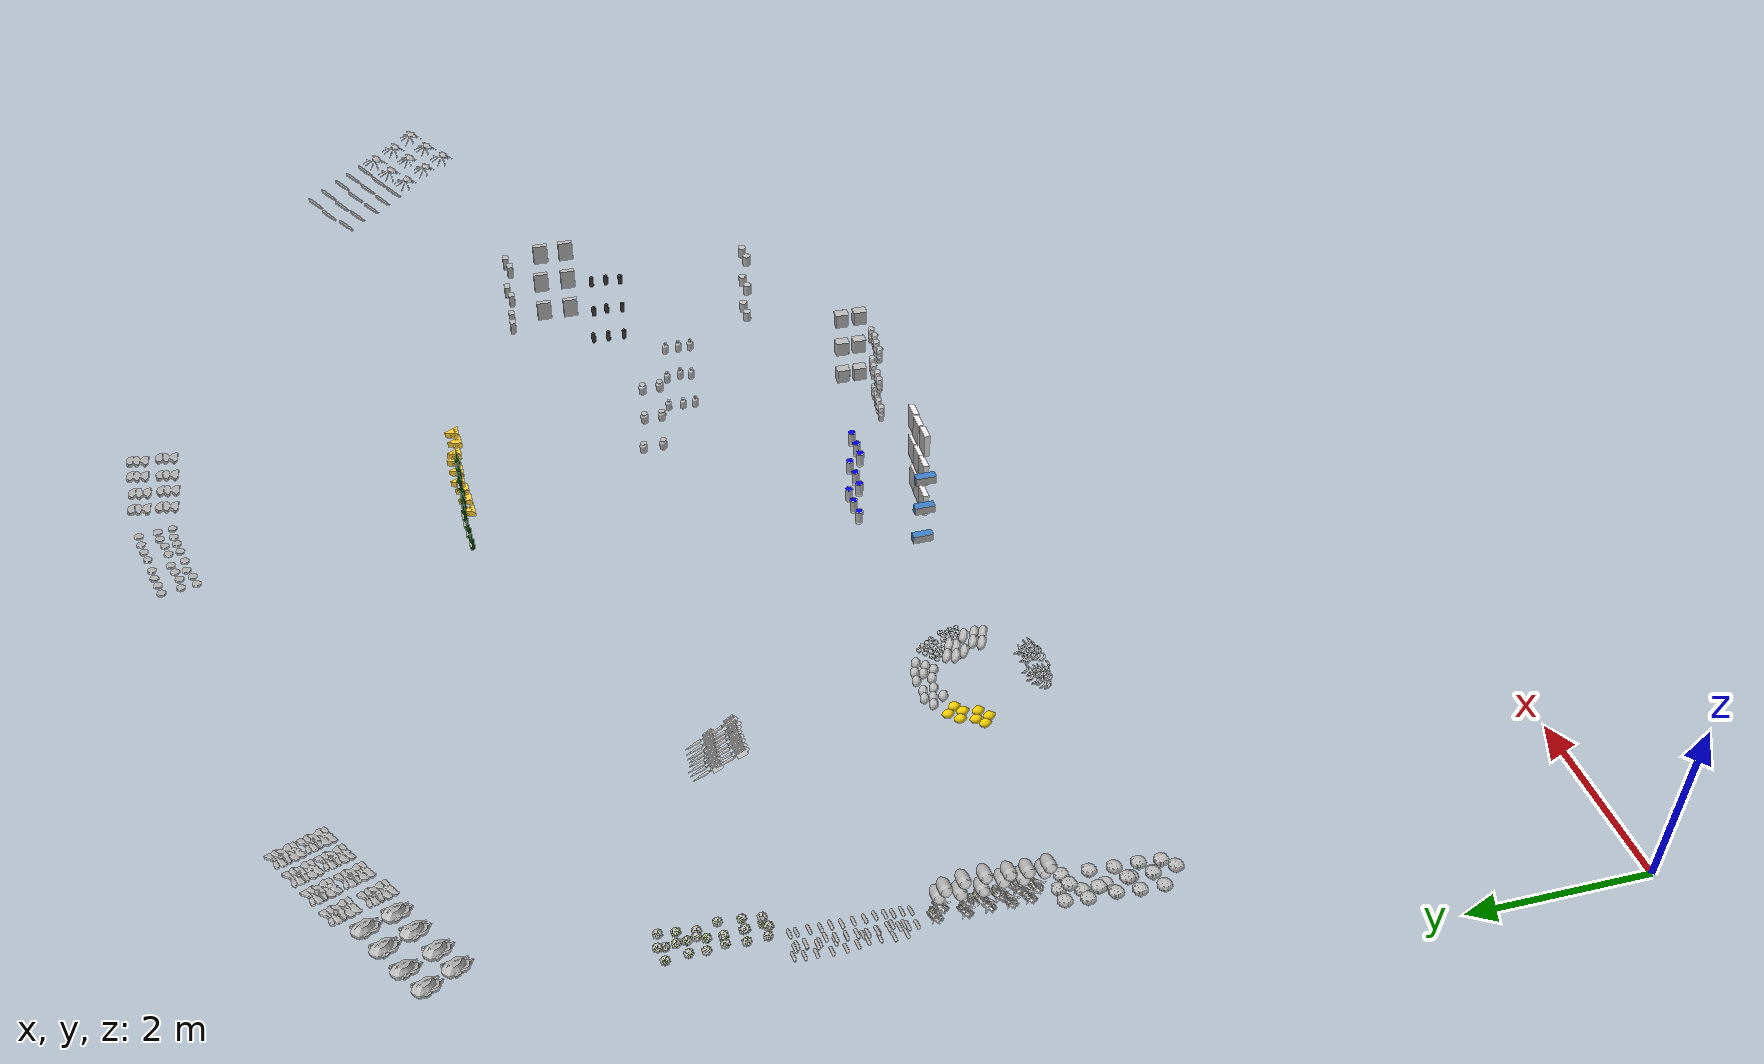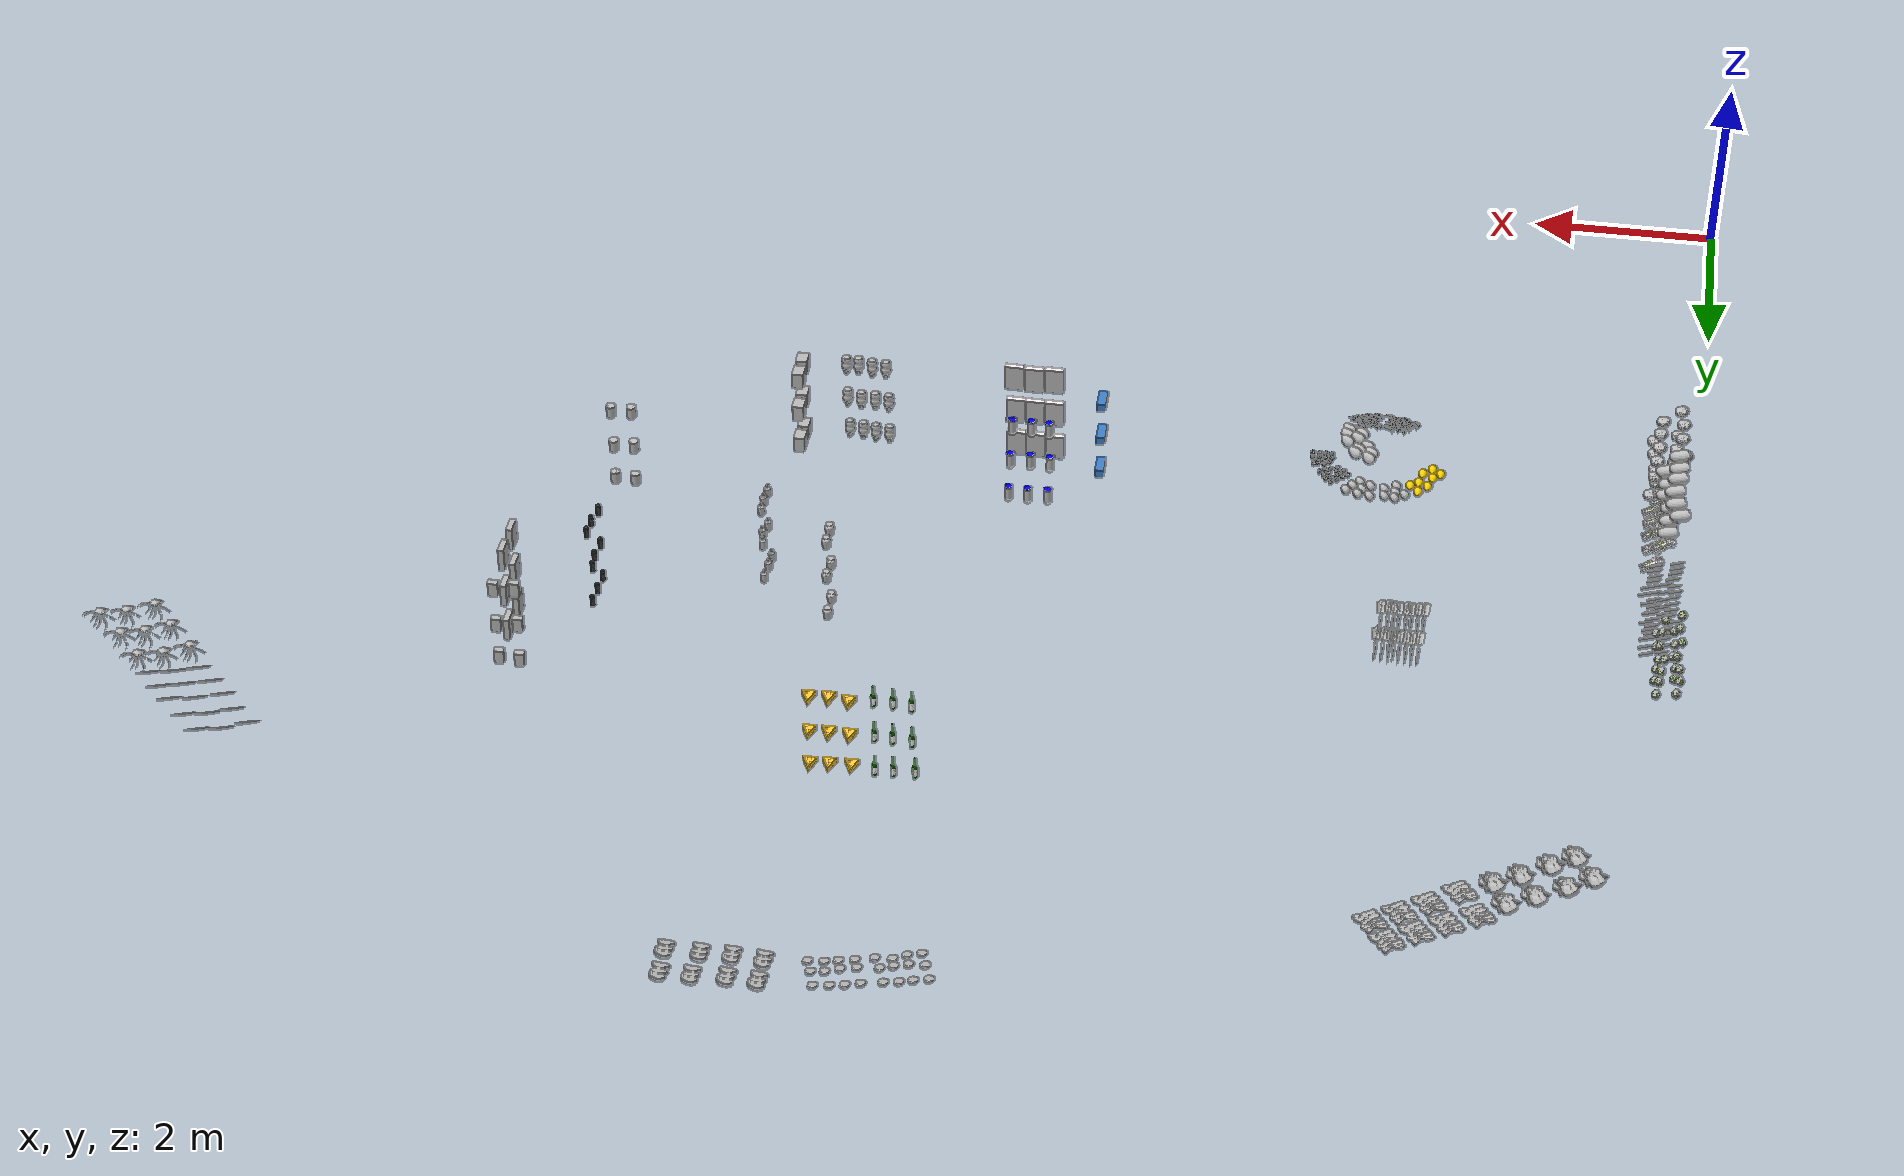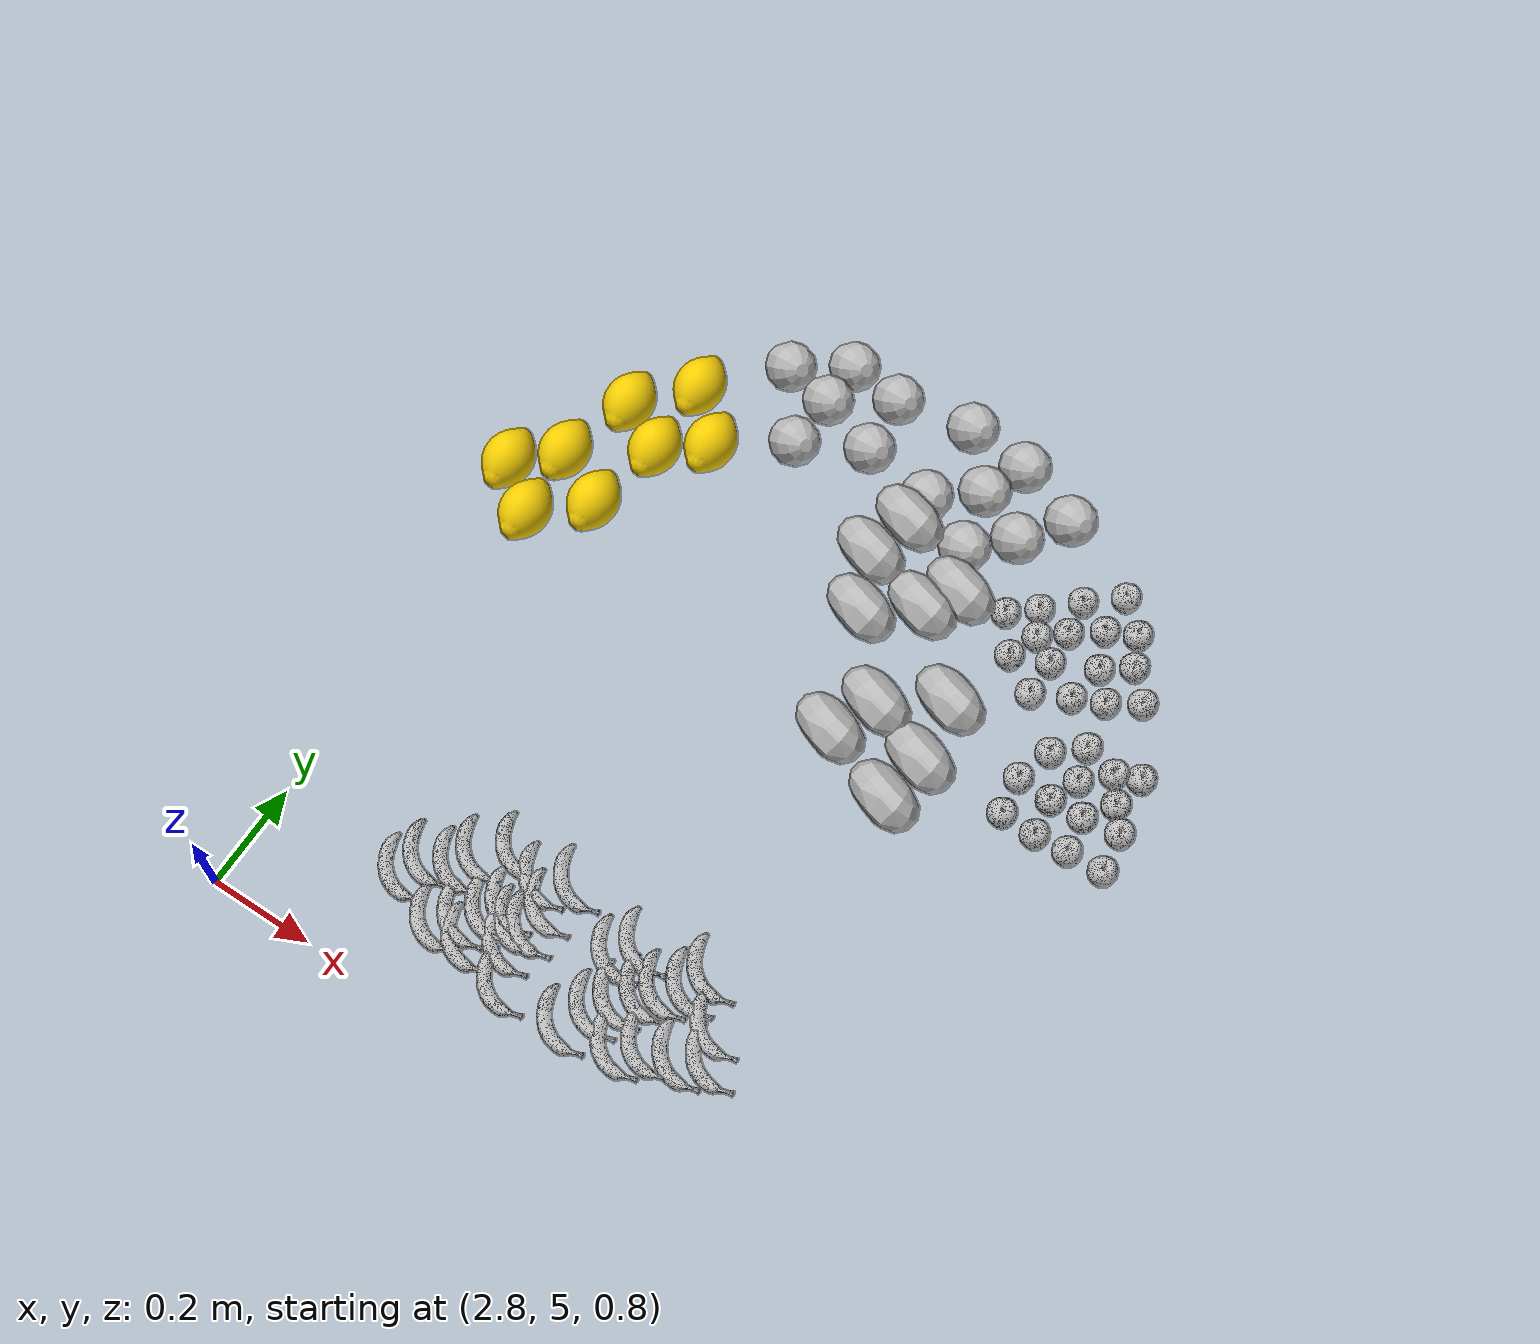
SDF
<sdf version="1.6">
 <world name="default">
  <light name="sun" type="directional">
   <cast_shadows>0</cast_shadows>
   <pose>0 0 10 0 -0 0</pose>
   <diffuse>0.8 0.8 0.8 1</diffuse>
   <specular>0.2 0.2 0.2 1</specular>
   <attenuation>
    <range>1000</range>
    <constant>0.9</constant>
    <linear>0.01</linear>
    <quadratic>0.001</quadratic>
   </attenuation>
   <direction>-0.5 0.1 -0.9</direction>
  </light>
  <gravity>0 0 -9.8</gravity>
  <magnetic_field>6e-06 2.3e-05 -4.2e-05</magnetic_field>
  <atmosphere type="adiabatic"/>
  <physics name="default_physics" default="0" type="ode">
   <max_step_size>0.001</max_step_size>
   <real_time_factor>1</real_time_factor>
   <real_time_update_rate>1000</real_time_update_rate>
  </physics>
  <scene><ambient>0.4 0.4 0.4 1</ambient><background>0.7 0.7 0.7 1</background><shadows>1</shadows></scene>
  <spherical_coordinates>
   <surface_model>EARTH_WGS84</surface_model>
   <latitude_deg>0</latitude_deg>
   <longitude_deg>0</longitude_deg>
   <elevation>0</elevation>
   <heading_deg>0</heading_deg>
  </spherical_coordinates>
  <model name="banana">
   <link name="link_0">
    <inertial>
     <mass>1</mass>
     <inertia>
      <ixx>0.166667</ixx>
      <ixy>0</ixy>
      <ixz>0</ixz>
      <iyy>0.166667</iyy>
      <iyz>0</iyz>
      <izz>0.166667</izz>
     </inertia>
    </inertial>
    <visual name="visual">
     <geometry><mesh><uri>model://banana/meshes/banana.dae</uri><scale>1 1 1</scale></mesh></geometry>
    </visual>
    <collision name="collision">
     <geometry><mesh><uri>model://banana/meshes/banana.dae</uri><scale>1 1 1</scale></mesh></geometry>
     <surface>
      <friction>
       <ode><mu>1</mu><mu2>1</mu2><fdir1>0 0 0</fdir1><slip1>0</slip1><slip2>0</slip2></ode>
       <torsional>
        <coefficient>1</coefficient>
        <patch_radius>0</patch_radius>
        <surface_radius>0</surface_radius>
        <use_patch_radius>1</use_patch_radius>
        <ode><slip>0</slip></ode>
       </torsional>
      </friction>
      <bounce><restitution_coefficient>0</restitution_coefficient><threshold>1e+06</threshold></bounce>
      <contact>
       <collide_without_contact>0</collide_without_contact>
       <collide_without_contact_bitmask>1</collide_without_contact_bitmask>
       <collide_bitmask>1</collide_bitmask>
       <ode>
        <soft_cfm>0</soft_cfm>
        <soft_erp>0.2</soft_erp>
        <kp>1e+13</kp>
        <kd>1</kd>
        <max_vel>0.01</max_vel>
        <min_depth>0</min_depth>
       </ode>
       <bullet>
        <split_impulse>1</split_impulse>
        <split_impulse_penetration_threshold>-0.01</split_impulse_penetration_threshold>
        <soft_cfm>0</soft_cfm>
        <soft_erp>0.2</soft_erp>
        <kp>1e+13</kp>
        <kd>1</kd>
       </bullet>
      </contact>
     </surface>
    </collision>
   </link>
   <static>1</static>
   <pose>3.44462 5.09797 0.868134 0 -0 0</pose>
  </model>
  <model name="banana_clone">
   <link name="link_0">
    <inertial>
     <mass>1</mass>
     <inertia>
      <ixx>0.166667</ixx>
      <ixy>0</ixy>
      <ixz>0</ixz>
      <iyy>0.166667</iyy>
      <iyz>0</iyz>
      <izz>0.166667</izz>
     </inertia>
    </inertial>
    <visual name="visual">
     <geometry><mesh><uri>model://banana/meshes/banana.dae</uri><scale>1 1 1</scale></mesh></geometry>
    </visual>
    <collision name="collision">
     <geometry><mesh><uri>model://banana/meshes/banana.dae</uri><scale>1 1 1</scale></mesh></geometry>
     <surface>
      <friction>
       <ode><mu>1</mu><mu2>1</mu2><fdir1>0 0 0</fdir1><slip1>0</slip1><slip2>0</slip2></ode>
       <torsional>
        <coefficient>1</coefficient>
        <patch_radius>0</patch_radius>
        <surface_radius>0</surface_radius>
        <use_patch_radius>1</use_patch_radius>
        <ode><slip>0</slip></ode>
       </torsional>
      </friction>
      <bounce><restitution_coefficient>0</restitution_coefficient><threshold>1e+06</threshold></bounce>
      <contact>
       <collide_without_contact>0</collide_without_contact>
       <collide_without_contact_bitmask>1</collide_without_contact_bitmask>
       <collide_bitmask>1</collide_bitmask>
       <ode>
        <soft_cfm>0</soft_cfm>
        <soft_erp>0.2</soft_erp>
        <kp>1e+13</kp>
        <kd>1</kd>
        <max_vel>0.01</max_vel>
        <min_depth>0</min_depth>
       </ode>
       <bullet>
        <split_impulse>1</split_impulse>
        <split_impulse_penetration_threshold>-0.01</split_impulse_penetration_threshold>
        <soft_cfm>0</soft_cfm>
        <soft_erp>0.2</soft_erp>
        <kp>1e+13</kp>
        <kd>1</kd>
       </bullet>
      </contact>
     </surface>
    </collision>
   </link>
   <static>1</static>
   <pose>3.60533 5.30959 0.868134 0 -0 0</pose>
  </model>
  <model name="banana_clone_0">
   <link name="link_0">
    <inertial>
     <mass>1</mass>
     <inertia>
      <ixx>0.166667</ixx>
      <ixy>0</ixy>
      <ixz>0</ixz>
      <iyy>0.166667</iyy>
      <iyz>0</iyz>
      <izz>0.166667</izz>
     </inertia>
    </inertial>
    <visual name="visual">
     <geometry><mesh><uri>model://banana/meshes/banana.dae</uri><scale>1 1 1</scale></mesh></geometry>
    </visual>
    <collision name="collision">
     <geometry><mesh><uri>model://banana/meshes/banana.dae</uri><scale>1 1 1</scale></mesh></geometry>
     <surface>
      <friction>
       <ode><mu>1</mu><mu2>1</mu2><fdir1>0 0 0</fdir1><slip1>0</slip1><slip2>0</slip2></ode>
       <torsional>
        <coefficient>1</coefficient>
        <patch_radius>0</patch_radius>
        <surface_radius>0</surface_radius>
        <use_patch_radius>1</use_patch_radius>
        <ode><slip>0</slip></ode>
       </torsional>
      </friction>
      <bounce><restitution_coefficient>0</restitution_coefficient><threshold>1e+06</threshold></bounce>
      <contact>
       <collide_without_contact>0</collide_without_contact>
       <collide_without_contact_bitmask>1</collide_without_contact_bitmask>
       <collide_bitmask>1</collide_bitmask>
       <ode>
        <soft_cfm>0</soft_cfm>
        <soft_erp>0.2</soft_erp>
        <kp>1e+13</kp>
        <kd>1</kd>
        <max_vel>0.01</max_vel>
        <min_depth>0</min_depth>
       </ode>
       <bullet>
        <split_impulse>1</split_impulse>
        <split_impulse_penetration_threshold>-0.01</split_impulse_penetration_threshold>
        <soft_cfm>0</soft_cfm>
        <soft_erp>0.2</soft_erp>
        <kp>1e+13</kp>
        <kd>1</kd>
       </bullet>
      </contact>
     </surface>
    </collision>
   </link>
   <static>1</static>
   <pose>3.58927 5.26962 0.868134 0 -0 0</pose>
  </model>
  <model name="banana_clone_1">
   <link name="link_0">
    <inertial>
     <mass>1</mass>
     <inertia>
      <ixx>0.166667</ixx>
      <ixy>0</ixy>
      <ixz>0</ixz>
      <iyy>0.166667</iyy>
      <iyz>0</iyz>
      <izz>0.166667</izz>
     </inertia>
    </inertial>
    <visual name="visual">
     <geometry><mesh><uri>model://banana/meshes/banana.dae</uri><scale>1 1 1</scale></mesh></geometry>
    </visual>
    <collision name="collision">
     <geometry><mesh><uri>model://banana/meshes/banana.dae</uri><scale>1 1 1</scale></mesh></geometry>
     <surface>
      <friction>
       <ode><mu>1</mu><mu2>1</mu2><fdir1>0 0 0</fdir1><slip1>0</slip1><slip2>0</slip2></ode>
       <torsional>
        <coefficient>1</coefficient>
        <patch_radius>0</patch_radius>
        <surface_radius>0</surface_radius>
        <use_patch_radius>1</use_patch_radius>
        <ode><slip>0</slip></ode>
       </torsional>
      </friction>
      <bounce><restitution_coefficient>0</restitution_coefficient><threshold>1e+06</threshold></bounce>
      <contact>
       <collide_without_contact>0</collide_without_contact>
       <collide_without_contact_bitmask>1</collide_without_contact_bitmask>
       <collide_bitmask>1</collide_bitmask>
       <ode>
        <soft_cfm>0</soft_cfm>
        <soft_erp>0.2</soft_erp>
        <kp>1e+13</kp>
        <kd>1</kd>
        <max_vel>0.01</max_vel>
        <min_depth>0</min_depth>
       </ode>
       <bullet>
        <split_impulse>1</split_impulse>
        <split_impulse_penetration_threshold>-0.01</split_impulse_penetration_threshold>
        <soft_cfm>0</soft_cfm>
        <soft_erp>0.2</soft_erp>
        <kp>1e+13</kp>
        <kd>1</kd>
       </bullet>
      </contact>
     </surface>
    </collision>
   </link>
   <static>1</static>
   <pose>3.55243 5.24171 0.868134 0 -0 0</pose>
  </model>
  <model name="banana_clone_2">
   <link name="link_0">
    <inertial>
     <mass>1</mass>
     <inertia>
      <ixx>0.166667</ixx>
      <ixy>0</ixy>
      <ixz>0</ixz>
      <iyy>0.166667</iyy>
      <iyz>0</iyz>
      <izz>0.166667</izz>
     </inertia>
    </inertial>
    <visual name="visual">
     <geometry><mesh><uri>model://banana/meshes/banana.dae</uri><scale>1 1 1</scale></mesh></geometry>
    </visual>
    <collision name="collision">
     <geometry><mesh><uri>model://banana/meshes/banana.dae</uri><scale>1 1 1</scale></mesh></geometry>
     <surface>
      <friction>
       <ode><mu>1</mu><mu2>1</mu2><fdir1>0 0 0</fdir1><slip1>0</slip1><slip2>0</slip2></ode>
       <torsional>
        <coefficient>1</coefficient>
        <patch_radius>0</patch_radius>
        <surface_radius>0</surface_radius>
        <use_patch_radius>1</use_patch_radius>
        <ode><slip>0</slip></ode>
       </torsional>
      </friction>
      <bounce><restitution_coefficient>0</restitution_coefficient><threshold>1e+06</threshold></bounce>
      <contact>
       <collide_without_contact>0</collide_without_contact>
       <collide_without_contact_bitmask>1</collide_without_contact_bitmask>
       <collide_bitmask>1</collide_bitmask>
       <ode>
        <soft_cfm>0</soft_cfm>
        <soft_erp>0.2</soft_erp>
        <kp>1e+13</kp>
        <kd>1</kd>
        <max_vel>0.01</max_vel>
        <min_depth>0</min_depth>
       </ode>
       <bullet>
        <split_impulse>1</split_impulse>
        <split_impulse_penetration_threshold>-0.01</split_impulse_penetration_threshold>
        <soft_cfm>0</soft_cfm>
        <soft_erp>0.2</soft_erp>
        <kp>1e+13</kp>
        <kd>1</kd>
       </bullet>
      </contact>
     </surface>
    </collision>
   </link>
   <static>1</static>
   <pose>3.49792 5.18513 0.868134 0 -0 0</pose>
  </model>
  <model name="banana_clone_3">
   <link name="link_0">
    <inertial>
     <mass>1</mass>
     <inertia>
      <ixx>0.166667</ixx>
      <ixy>0</ixy>
      <ixz>0</ixz>
      <iyy>0.166667</iyy>
      <iyz>0</iyz>
      <izz>0.166667</izz>
     </inertia>
    </inertial>
    <visual name="visual">
     <geometry><mesh><uri>model://banana/meshes/banana.dae</uri><scale>1 1 1</scale></mesh></geometry>
    </visual>
    <collision name="collision">
     <geometry><mesh><uri>model://banana/meshes/banana.dae</uri><scale>1 1 1</scale></mesh></geometry>
     <surface>
      <friction>
       <ode><mu>1</mu><mu2>1</mu2><fdir1>0 0 0</fdir1><slip1>0</slip1><slip2>0</slip2></ode>
       <torsional>
        <coefficient>1</coefficient>
        <patch_radius>0</patch_radius>
        <surface_radius>0</surface_radius>
        <use_patch_radius>1</use_patch_radius>
        <ode><slip>0</slip></ode>
       </torsional>
      </friction>
      <bounce><restitution_coefficient>0</restitution_coefficient><threshold>1e+06</threshold></bounce>
      <contact>
       <collide_without_contact>0</collide_without_contact>
       <collide_without_contact_bitmask>1</collide_without_contact_bitmask>
       <collide_bitmask>1</collide_bitmask>
       <ode>
        <soft_cfm>0</soft_cfm>
        <soft_erp>0.2</soft_erp>
        <kp>1e+13</kp>
        <kd>1</kd>
        <max_vel>0.01</max_vel>
        <min_depth>0</min_depth>
       </ode>
       <bullet>
        <split_impulse>1</split_impulse>
        <split_impulse_penetration_threshold>-0.01</split_impulse_penetration_threshold>
        <soft_cfm>0</soft_cfm>
        <soft_erp>0.2</soft_erp>
        <kp>1e+13</kp>
        <kd>1</kd>
       </bullet>
      </contact>
     </surface>
    </collision>
   </link>
   <static>1</static>
   <pose>3.52892 5.21734 0.868134 0 -0 0</pose>
  </model>
  <model name="banana_clone_4">
   <link name="link_0">
    <inertial>
     <mass>1</mass>
     <inertia>
      <ixx>0.166667</ixx>
      <ixy>0</ixy>
      <ixz>0</ixz>
      <iyy>0.166667</iyy>
      <iyz>0</iyz>
      <izz>0.166667</izz>
     </inertia>
    </inertial>
    <visual name="visual">
     <geometry><mesh><uri>model://banana/meshes/banana.dae</uri><scale>1 1 1</scale></mesh></geometry>
    </visual>
    <collision name="collision">
     <geometry><mesh><uri>model://banana/meshes/banana.dae</uri><scale>1 1 1</scale></mesh></geometry>
     <surface>
      <friction>
       <ode><mu>1</mu><mu2>1</mu2><fdir1>0 0 0</fdir1><slip1>0</slip1><slip2>0</slip2></ode>
       <torsional>
        <coefficient>1</coefficient>
        <patch_radius>0</patch_radius>
        <surface_radius>0</surface_radius>
        <use_patch_radius>1</use_patch_radius>
        <ode><slip>0</slip></ode>
       </torsional>
      </friction>
      <bounce><restitution_coefficient>0</restitution_coefficient><threshold>1e+06</threshold></bounce>
      <contact>
       <collide_without_contact>0</collide_without_contact>
       <collide_without_contact_bitmask>1</collide_without_contact_bitmask>
       <collide_bitmask>1</collide_bitmask>
       <ode>
        <soft_cfm>0</soft_cfm>
        <soft_erp>0.2</soft_erp>
        <kp>1e+13</kp>
        <kd>1</kd>
        <max_vel>0.01</max_vel>
        <min_depth>0</min_depth>
       </ode>
       <bullet>
        <split_impulse>1</split_impulse>
        <split_impulse_penetration_threshold>-0.01</split_impulse_penetration_threshold>
        <soft_cfm>0</soft_cfm>
        <soft_erp>0.2</soft_erp>
        <kp>1e+13</kp>
        <kd>1</kd>
       </bullet>
      </contact>
     </surface>
    </collision>
   </link>
   <static>1</static>
   <pose>3.68859 5.18166 0.868134 0 -0 0</pose>
  </model>
  <model name="banana_clone_5">
   <link name="link_0">
    <inertial>
     <mass>1</mass>
     <inertia>
      <ixx>0.166667</ixx>
      <ixy>0</ixy>
      <ixz>0</ixz>
      <iyy>0.166667</iyy>
      <iyz>0</iyz>
      <izz>0.166667</izz>
     </inertia>
    </inertial>
    <visual name="visual">
     <geometry><mesh><uri>model://banana/meshes/banana.dae</uri><scale>1 1 1</scale></mesh></geometry>
    </visual>
    <collision name="collision">
     <geometry><mesh><uri>model://banana/meshes/banana.dae</uri><scale>1 1 1</scale></mesh></geometry>
     <surface>
      <friction>
       <ode><mu>1</mu><mu2>1</mu2><fdir1>0 0 0</fdir1><slip1>0</slip1><slip2>0</slip2></ode>
       <torsional>
        <coefficient>1</coefficient>
        <patch_radius>0</patch_radius>
        <surface_radius>0</surface_radius>
        <use_patch_radius>1</use_patch_radius>
        <ode><slip>0</slip></ode>
       </torsional>
      </friction>
      <bounce><restitution_coefficient>0</restitution_coefficient><threshold>1e+06</threshold></bounce>
      <contact>
       <collide_without_contact>0</collide_without_contact>
       <collide_without_contact_bitmask>1</collide_without_contact_bitmask>
       <collide_bitmask>1</collide_bitmask>
       <ode>
        <soft_cfm>0</soft_cfm>
        <soft_erp>0.2</soft_erp>
        <kp>1e+13</kp>
        <kd>1</kd>
        <max_vel>0.01</max_vel>
        <min_depth>0</min_depth>
       </ode>
       <bullet>
        <split_impulse>1</split_impulse>
        <split_impulse_penetration_threshold>-0.01</split_impulse_penetration_threshold>
        <soft_cfm>0</soft_cfm>
        <soft_erp>0.2</soft_erp>
        <kp>1e+13</kp>
        <kd>1</kd>
       </bullet>
      </contact>
     </surface>
    </collision>
   </link>
   <static>1</static>
   <pose>3.63936 5.15513 0.868134 0 -0 0</pose>
  </model>
  <model name="banana_clone_6">
   <link name="link_0">
    <inertial>
     <mass>1</mass>
     <inertia>
      <ixx>0.166667</ixx>
      <ixy>0</ixy>
      <ixz>0</ixz>
      <iyy>0.166667</iyy>
      <iyz>0</iyz>
      <izz>0.166667</izz>
     </inertia>
    </inertial>
    <visual name="visual">
     <geometry><mesh><uri>model://banana/meshes/banana.dae</uri><scale>1 1 1</scale></mesh></geometry>
    </visual>
    <collision name="collision">
     <geometry><mesh><uri>model://banana/meshes/banana.dae</uri><scale>1 1 1</scale></mesh></geometry>
     <surface>
      <friction>
       <ode><mu>1</mu><mu2>1</mu2><fdir1>0 0 0</fdir1><slip1>0</slip1><slip2>0</slip2></ode>
       <torsional>
        <coefficient>1</coefficient>
        <patch_radius>0</patch_radius>
        <surface_radius>0</surface_radius>
        <use_patch_radius>1</use_patch_radius>
        <ode><slip>0</slip></ode>
       </torsional>
      </friction>
      <bounce><restitution_coefficient>0</restitution_coefficient><threshold>1e+06</threshold></bounce>
      <contact>
       <collide_without_contact>0</collide_without_contact>
       <collide_without_contact_bitmask>1</collide_without_contact_bitmask>
       <collide_bitmask>1</collide_bitmask>
       <ode>
        <soft_cfm>0</soft_cfm>
        <soft_erp>0.2</soft_erp>
        <kp>1e+13</kp>
        <kd>1</kd>
        <max_vel>0.01</max_vel>
        <min_depth>0</min_depth>
       </ode>
       <bullet>
        <split_impulse>1</split_impulse>
        <split_impulse_penetration_threshold>-0.01</split_impulse_penetration_threshold>
        <soft_cfm>0</soft_cfm>
        <soft_erp>0.2</soft_erp>
        <kp>1e+13</kp>
        <kd>1</kd>
       </bullet>
      </contact>
     </surface>
    </collision>
   </link>
   <static>1</static>
   <pose>3.58449 5.14176 0.868134 0 -0 0</pose>
  </model>
  <model name="banana_clone_7">
   <link name="link_0">
    <inertial>
     <mass>1</mass>
     <inertia>
      <ixx>0.166667</ixx>
      <ixy>0</ixy>
      <ixz>0</ixz>
      <iyy>0.166667</iyy>
      <iyz>0</iyz>
      <izz>0.166667</izz>
     </inertia>
    </inertial>
    <visual name="visual">
     <geometry><mesh><uri>model://banana/meshes/banana.dae</uri><scale>1 1 1</scale></mesh></geometry>
    </visual>
    <collision name="collision">
     <geometry><mesh><uri>model://banana/meshes/banana.dae</uri><scale>1 1 1</scale></mesh></geometry>
     <surface>
      <friction>
       <ode><mu>1</mu><mu2>1</mu2><fdir1>0 0 0</fdir1><slip1>0</slip1><slip2>0</slip2></ode>
       <torsional>
        <coefficient>1</coefficient>
        <patch_radius>0</patch_radius>
        <surface_radius>0</surface_radius>
        <use_patch_radius>1</use_patch_radius>
        <ode><slip>0</slip></ode>
       </torsional>
      </friction>
      <bounce><restitution_coefficient>0</restitution_coefficient><threshold>1e+06</threshold></bounce>
      <contact>
       <collide_without_contact>0</collide_without_contact>
       <collide_without_contact_bitmask>1</collide_without_contact_bitmask>
       <collide_bitmask>1</collide_bitmask>
       <ode>
        <soft_cfm>0</soft_cfm>
        <soft_erp>0.2</soft_erp>
        <kp>1e+13</kp>
        <kd>1</kd>
        <max_vel>0.01</max_vel>
        <min_depth>0</min_depth>
       </ode>
       <bullet>
        <split_impulse>1</split_impulse>
        <split_impulse_penetration_threshold>-0.01</split_impulse_penetration_threshold>
        <soft_cfm>0</soft_cfm>
        <soft_erp>0.2</soft_erp>
        <kp>1e+13</kp>
        <kd>1</kd>
       </bullet>
      </contact>
     </surface>
    </collision>
   </link>
   <static>1</static>
   <pose>3.47415 5.14868 0.868134 0 -0 0</pose>
  </model>
  <model name="banana_clone_8">
   <link name="link_0">
    <inertial>
     <mass>1</mass>
     <inertia>
      <ixx>0.166667</ixx>
      <ixy>0</ixy>
      <ixz>0</ixz>
      <iyy>0.166667</iyy>
      <iyz>0</iyz>
      <izz>0.166667</izz>
     </inertia>
    </inertial>
    <visual name="visual">
     <geometry><mesh><uri>model://banana/meshes/banana.dae</uri><scale>1 1 1</scale></mesh></geometry>
    </visual>
    <collision name="collision">
     <geometry><mesh><uri>model://banana/meshes/banana.dae</uri><scale>1 1 1</scale></mesh></geometry>
     <surface>
      <friction>
       <ode><mu>1</mu><mu2>1</mu2><fdir1>0 0 0</fdir1><slip1>0</slip1><slip2>0</slip2></ode>
       <torsional>
        <coefficient>1</coefficient>
        <patch_radius>0</patch_radius>
        <surface_radius>0</surface_radius>
        <use_patch_radius>1</use_patch_radius>
        <ode><slip>0</slip></ode>
       </torsional>
      </friction>
      <bounce><restitution_coefficient>0</restitution_coefficient><threshold>1e+06</threshold></bounce>
      <contact>
       <collide_without_contact>0</collide_without_contact>
       <collide_without_contact_bitmask>1</collide_without_contact_bitmask>
       <collide_bitmask>1</collide_bitmask>
       <ode>
        <soft_cfm>0</soft_cfm>
        <soft_erp>0.2</soft_erp>
        <kp>1e+13</kp>
        <kd>1</kd>
        <max_vel>0.01</max_vel>
        <min_depth>0</min_depth>
       </ode>
       <bullet>
        <split_impulse>1</split_impulse>
        <split_impulse_penetration_threshold>-0.01</split_impulse_penetration_threshold>
        <soft_cfm>0</soft_cfm>
        <soft_erp>0.2</soft_erp>
        <kp>1e+13</kp>
        <kd>1</kd>
       </bullet>
      </contact>
     </surface>
    </collision>
   </link>
   <static>1</static>
   <pose>3.45112 5.24805 0.868134 0 -0 0</pose>
  </model>
  <model name="banana_clone_9">
   <link name="link_0">
    <inertial>
     <mass>1</mass>
     <inertia>
      <ixx>0.166667</ixx>
      <ixy>0</ixy>
      <ixz>0</ixz>
      <iyy>0.166667</iyy>
      <iyz>0</iyz>
      <izz>0.166667</izz>
     </inertia>
    </inertial>
    <visual name="visual">
     <geometry><mesh><uri>model://banana/meshes/banana.dae</uri><scale>1 1 1</scale></mesh></geometry>
    </visual>
    <collision name="collision">
     <geometry><mesh><uri>model://banana/meshes/banana.dae</uri><scale>1 1 1</scale></mesh></geometry>
     <surface>
      <friction>
       <ode><mu>1</mu><mu2>1</mu2><fdir1>0 0 0</fdir1><slip1>0</slip1><slip2>0</slip2></ode>
       <torsional>
        <coefficient>1</coefficient>
        <patch_radius>0</patch_radius>
        <surface_radius>0</surface_radius>
        <use_patch_radius>1</use_patch_radius>
        <ode><slip>0</slip></ode>
       </torsional>
      </friction>
      <bounce><restitution_coefficient>0</restitution_coefficient><threshold>1e+06</threshold></bounce>
      <contact>
       <collide_without_contact>0</collide_without_contact>
       <collide_without_contact_bitmask>1</collide_without_contact_bitmask>
       <collide_bitmask>1</collide_bitmask>
       <ode>
        <soft_cfm>0</soft_cfm>
        <soft_erp>0.2</soft_erp>
        <kp>1e+13</kp>
        <kd>1</kd>
        <max_vel>0.01</max_vel>
        <min_depth>0</min_depth>
       </ode>
       <bullet>
        <split_impulse>1</split_impulse>
        <split_impulse_penetration_threshold>-0.01</split_impulse_penetration_threshold>
        <soft_cfm>0</soft_cfm>
        <soft_erp>0.2</soft_erp>
        <kp>1e+13</kp>
        <kd>1</kd>
       </bullet>
      </contact>
     </surface>
    </collision>
   </link>
   <static>1</static>
   <pose>3.48243 5.28531 0.868134 0 -0 0</pose>
  </model>
  <model name="banana_clone_10">
   <link name="link_0">
    <inertial>
     <mass>1</mass>
     <inertia>
      <ixx>0.166667</ixx>
      <ixy>0</ixy>
      <ixz>0</ixz>
      <iyy>0.166667</iyy>
      <iyz>0</iyz>
      <izz>0.166667</izz>
     </inertia>
    </inertial>
    <visual name="visual">
     <geometry><mesh><uri>model://banana/meshes/banana.dae</uri><scale>1 1 1</scale></mesh></geometry>
    </visual>
    <collision name="collision">
     <geometry><mesh><uri>model://banana/meshes/banana.dae</uri><scale>1 1 1</scale></mesh></geometry>
     <surface>
      <friction>
       <ode><mu>1</mu><mu2>1</mu2><fdir1>0 0 0</fdir1><slip1>0</slip1><slip2>0</slip2></ode>
       <torsional>
        <coefficient>1</coefficient>
        <patch_radius>0</patch_radius>
        <surface_radius>0</surface_radius>
        <use_patch_radius>1</use_patch_radius>
        <ode><slip>0</slip></ode>
       </torsional>
      </friction>
      <bounce><restitution_coefficient>0</restitution_coefficient><threshold>1e+06</threshold></bounce>
      <contact>
       <collide_without_contact>0</collide_without_contact>
       <collide_without_contact_bitmask>1</collide_without_contact_bitmask>
       <collide_bitmask>1</collide_bitmask>
       <ode>
        <soft_cfm>0</soft_cfm>
        <soft_erp>0.2</soft_erp>
        <kp>1e+13</kp>
        <kd>1</kd>
        <max_vel>0.01</max_vel>
        <min_depth>0</min_depth>
       </ode>
       <bullet>
        <split_impulse>1</split_impulse>
        <split_impulse_penetration_threshold>-0.01</split_impulse_penetration_threshold>
        <soft_cfm>0</soft_cfm>
        <soft_erp>0.2</soft_erp>
        <kp>1e+13</kp>
        <kd>1</kd>
       </bullet>
      </contact>
     </surface>
    </collision>
   </link>
   <static>1</static>
   <pose>3.54266 5.11314 0.868134 0 -0 0</pose>
  </model>
  <model name="banana_clone_11">
   <link name="link_0">
    <inertial>
     <mass>1</mass>
     <inertia>
      <ixx>0.166667</ixx>
      <ixy>0</ixy>
      <ixz>0</ixz>
      <iyy>0.166667</iyy>
      <iyz>0</iyz>
      <izz>0.166667</izz>
     </inertia>
    </inertial>
    <visual name="visual">
     <geometry><mesh><uri>model://banana/meshes/banana.dae</uri><scale>1 1 1</scale></mesh></geometry>
    </visual>
    <collision name="collision">
     <geometry><mesh><uri>model://banana/meshes/banana.dae</uri><scale>1 1 1</scale></mesh></geometry>
     <surface>
      <friction>
       <ode><mu>1</mu><mu2>1</mu2><fdir1>0 0 0</fdir1><slip1>0</slip1><slip2>0</slip2></ode>
       <torsional>
        <coefficient>1</coefficient>
        <patch_radius>0</patch_radius>
        <surface_radius>0</surface_radius>
        <use_patch_radius>1</use_patch_radius>
        <ode><slip>0</slip></ode>
       </torsional>
      </friction>
      <bounce><restitution_coefficient>0</restitution_coefficient><threshold>1e+06</threshold></bounce>
      <contact>
       <collide_without_contact>0</collide_without_contact>
       <collide_without_contact_bitmask>1</collide_without_contact_bitmask>
       <collide_bitmask>1</collide_bitmask>
       <ode>
        <soft_cfm>0</soft_cfm>
        <soft_erp>0.2</soft_erp>
        <kp>1e+13</kp>
        <kd>1</kd>
        <max_vel>0.01</max_vel>
        <min_depth>0</min_depth>
       </ode>
       <bullet>
        <split_impulse>1</split_impulse>
        <split_impulse_penetration_threshold>-0.01</split_impulse_penetration_threshold>
        <soft_cfm>0</soft_cfm>
        <soft_erp>0.2</soft_erp>
        <kp>1e+13</kp>
        <kd>1</kd>
       </bullet>
      </contact>
     </surface>
    </collision>
   </link>
   <static>1</static>
   <pose>3.66313 5.23262 0.868134 0 -0 0</pose>
  </model>
  <model name="banana_clone_12">
   <link name="link_0">
    <inertial>
     <mass>1</mass>
     <inertia>
      <ixx>0.166667</ixx>
      <ixy>0</ixy>
      <ixz>0</ixz>
      <iyy>0.166667</iyy>
      <iyz>0</iyz>
      <izz>0.166667</izz>
     </inertia>
    </inertial>
    <visual name="visual">
     <geometry><mesh><uri>model://banana/meshes/banana.dae</uri><scale>1 1 1</scale></mesh></geometry>
    </visual>
    <collision name="collision">
     <geometry><mesh><uri>model://banana/meshes/banana.dae</uri><scale>1 1 1</scale></mesh></geometry>
     <surface>
      <friction>
       <ode><mu>1</mu><mu2>1</mu2><fdir1>0 0 0</fdir1><slip1>0</slip1><slip2>0</slip2></ode>
       <torsional>
        <coefficient>1</coefficient>
        <patch_radius>0</patch_radius>
        <surface_radius>0</surface_radius>
        <use_patch_radius>1</use_patch_radius>
        <ode><slip>0</slip></ode>
       </torsional>
      </friction>
      <bounce><restitution_coefficient>0</restitution_coefficient><threshold>1e+06</threshold></bounce>
      <contact>
       <collide_without_contact>0</collide_without_contact>
       <collide_without_contact_bitmask>1</collide_without_contact_bitmask>
       <collide_bitmask>1</collide_bitmask>
       <ode>
        <soft_cfm>0</soft_cfm>
        <soft_erp>0.2</soft_erp>
        <kp>1e+13</kp>
        <kd>1</kd>
        <max_vel>0.01</max_vel>
        <min_depth>0</min_depth>
       </ode>
       <bullet>
        <split_impulse>1</split_impulse>
        <split_impulse_penetration_threshold>-0.01</split_impulse_penetration_threshold>
        <soft_cfm>0</soft_cfm>
        <soft_erp>0.2</soft_erp>
        <kp>1e+13</kp>
        <kd>1</kd>
       </bullet>
      </contact>
     </surface>
    </collision>
   </link>
   <static>1</static>
   <pose>3.20722 5.31088 0.868134 0 -0 0</pose>
  </model>
  <model name="banana_clone_13">
   <link name="link_0">
    <inertial>
     <mass>1</mass>
     <inertia>
      <ixx>0.166667</ixx>
      <ixy>0</ixy>
      <ixz>0</ixz>
      <iyy>0.166667</iyy>
      <iyz>0</iyz>
      <izz>0.166667</izz>
     </inertia>
    </inertial>
    <visual name="visual">
     <geometry><mesh><uri>model://banana/meshes/banana.dae</uri><scale>1 1 1</scale></mesh></geometry>
    </visual>
    <collision name="collision">
     <geometry><mesh><uri>model://banana/meshes/banana.dae</uri><scale>1 1 1</scale></mesh></geometry>
     <surface>
      <friction>
       <ode><mu>1</mu><mu2>1</mu2><fdir1>0 0 0</fdir1><slip1>0</slip1><slip2>0</slip2></ode>
       <torsional>
        <coefficient>1</coefficient>
        <patch_radius>0</patch_radius>
        <surface_radius>0</surface_radius>
        <use_patch_radius>1</use_patch_radius>
        <ode><slip>0</slip></ode>
       </torsional>
      </friction>
      <bounce><restitution_coefficient>0</restitution_coefficient><threshold>1e+06</threshold></bounce>
      <contact>
       <collide_without_contact>0</collide_without_contact>
       <collide_without_contact_bitmask>1</collide_without_contact_bitmask>
       <collide_bitmask>1</collide_bitmask>
       <ode>
        <soft_cfm>0</soft_cfm>
        <soft_erp>0.2</soft_erp>
        <kp>1e+13</kp>
        <kd>1</kd>
        <max_vel>0.01</max_vel>
        <min_depth>0</min_depth>
       </ode>
       <bullet>
        <split_impulse>1</split_impulse>
        <split_impulse_penetration_threshold>-0.01</split_impulse_penetration_threshold>
        <soft_cfm>0</soft_cfm>
        <soft_erp>0.2</soft_erp>
        <kp>1e+13</kp>
        <kd>1</kd>
       </bullet>
      </contact>
     </surface>
    </collision>
   </link>
   <static>1</static>
   <pose>3.27114 5.28685 0.868134 0 -0 0</pose>
  </model>
  <model name="banana_clone_14">
   <link name="link_0">
    <inertial>
     <mass>1</mass>
     <inertia>
      <ixx>0.166667</ixx>
      <ixy>0</ixy>
      <ixz>0</ixz>
      <iyy>0.166667</iyy>
      <iyz>0</iyz>
      <izz>0.166667</izz>
     </inertia>
    </inertial>
    <visual name="visual">
     <geometry><mesh><uri>model://banana/meshes/banana.dae</uri><scale>1 1 1</scale></mesh></geometry>
    </visual>
    <collision name="collision">
     <geometry><mesh><uri>model://banana/meshes/banana.dae</uri><scale>1 1 1</scale></mesh></geometry>
     <surface>
      <friction>
       <ode><mu>1</mu><mu2>1</mu2><fdir1>0 0 0</fdir1><slip1>0</slip1><slip2>0</slip2></ode>
       <torsional>
        <coefficient>1</coefficient>
        <patch_radius>0</patch_radius>
        <surface_radius>0</surface_radius>
        <use_patch_radius>1</use_patch_radius>
        <ode><slip>0</slip></ode>
       </torsional>
      </friction>
      <bounce><restitution_coefficient>0</restitution_coefficient><threshold>1e+06</threshold></bounce>
      <contact>
       <collide_without_contact>0</collide_without_contact>
       <collide_without_contact_bitmask>1</collide_without_contact_bitmask>
       <collide_bitmask>1</collide_bitmask>
       <ode>
        <soft_cfm>0</soft_cfm>
        <soft_erp>0.2</soft_erp>
        <kp>1e+13</kp>
        <kd>1</kd>
        <max_vel>0.01</max_vel>
        <min_depth>0</min_depth>
       </ode>
       <bullet>
        <split_impulse>1</split_impulse>
        <split_impulse_penetration_threshold>-0.01</split_impulse_penetration_threshold>
        <soft_cfm>0</soft_cfm>
        <soft_erp>0.2</soft_erp>
        <kp>1e+13</kp>
        <kd>1</kd>
       </bullet>
      </contact>
     </surface>
    </collision>
   </link>
   <static>1</static>
   <pose>3.15384 5.26782 0.868134 0 -0 0</pose>
  </model>
  <model name="banana_clone_15">
   <link name="link_0">
    <inertial>
     <mass>1</mass>
     <inertia>
      <ixx>0.166667</ixx>
      <ixy>0</ixy>
      <ixz>0</ixz>
      <iyy>0.166667</iyy>
      <iyz>0</iyz>
      <izz>0.166667</izz>
     </inertia>
    </inertial>
    <visual name="visual">
     <geometry><mesh><uri>model://banana/meshes/banana.dae</uri><scale>1 1 1</scale></mesh></geometry>
    </visual>
    <collision name="collision">
     <geometry><mesh><uri>model://banana/meshes/banana.dae</uri><scale>1 1 1</scale></mesh></geometry>
     <surface>
      <friction>
       <ode><mu>1</mu><mu2>1</mu2><fdir1>0 0 0</fdir1><slip1>0</slip1><slip2>0</slip2></ode>
       <torsional>
        <coefficient>1</coefficient>
        <patch_radius>0</patch_radius>
        <surface_radius>0</surface_radius>
        <use_patch_radius>1</use_patch_radius>
        <ode><slip>0</slip></ode>
       </torsional>
      </friction>
      <bounce><restitution_coefficient>0</restitution_coefficient><threshold>1e+06</threshold></bounce>
      <contact>
       <collide_without_contact>0</collide_without_contact>
       <collide_without_contact_bitmask>1</collide_without_contact_bitmask>
       <collide_bitmask>1</collide_bitmask>
       <ode>
        <soft_cfm>0</soft_cfm>
        <soft_erp>0.2</soft_erp>
        <kp>1e+13</kp>
        <kd>1</kd>
        <max_vel>0.01</max_vel>
        <min_depth>0</min_depth>
       </ode>
       <bullet>
        <split_impulse>1</split_impulse>
        <split_impulse_penetration_threshold>-0.01</split_impulse_penetration_threshold>
        <soft_cfm>0</soft_cfm>
        <soft_erp>0.2</soft_erp>
        <kp>1e+13</kp>
        <kd>1</kd>
       </bullet>
      </contact>
     </surface>
    </collision>
   </link>
   <static>1</static>
   <pose>3.13296 5.22975 0.868134 0 -0 0</pose>
  </model>
  <model name="banana_clone_16">
   <link name="link_0">
    <inertial>
     <mass>1</mass>
     <inertia>
      <ixx>0.166667</ixx>
      <ixy>0</ixy>
      <ixz>0</ixz>
      <iyy>0.166667</iyy>
      <iyz>0</iyz>
      <izz>0.166667</izz>
     </inertia>
    </inertial>
    <visual name="visual">
     <geometry><mesh><uri>model://banana/meshes/banana.dae</uri><scale>1 1 1</scale></mesh></geometry>
    </visual>
    <collision name="collision">
     <geometry><mesh><uri>model://banana/meshes/banana.dae</uri><scale>1 1 1</scale></mesh></geometry>
     <surface>
      <friction>
       <ode><mu>1</mu><mu2>1</mu2><fdir1>0 0 0</fdir1><slip1>0</slip1><slip2>0</slip2></ode>
       <torsional>
        <coefficient>1</coefficient>
        <patch_radius>0</patch_radius>
        <surface_radius>0</surface_radius>
        <use_patch_radius>1</use_patch_radius>
        <ode><slip>0</slip></ode>
       </torsional>
      </friction>
      <bounce><restitution_coefficient>0</restitution_coefficient><threshold>1e+06</threshold></bounce>
      <contact>
       <collide_without_contact>0</collide_without_contact>
       <collide_without_contact_bitmask>1</collide_without_contact_bitmask>
       <collide_bitmask>1</collide_bitmask>
       <ode>
        <soft_cfm>0</soft_cfm>
        <soft_erp>0.2</soft_erp>
        <kp>1e+13</kp>
        <kd>1</kd>
        <max_vel>0.01</max_vel>
        <min_depth>0</min_depth>
       </ode>
       <bullet>
        <split_impulse>1</split_impulse>
        <split_impulse_penetration_threshold>-0.01</split_impulse_penetration_threshold>
        <soft_cfm>0</soft_cfm>
        <soft_erp>0.2</soft_erp>
        <kp>1e+13</kp>
        <kd>1</kd>
       </bullet>
      </contact>
     </surface>
    </collision>
   </link>
   <static>1</static>
   <pose>3.08263 5.21174 0.868134 0 -0 0</pose>
  </model>
  <model name="banana_clone_17">
   <link name="link_0">
    <inertial>
     <mass>1</mass>
     <inertia>
      <ixx>0.166667</ixx>
      <ixy>0</ixy>
      <ixz>0</ixz>
      <iyy>0.166667</iyy>
      <iyz>0</iyz>
      <izz>0.166667</izz>
     </inertia>
    </inertial>
    <visual name="visual">
     <geometry><mesh><uri>model://banana/meshes/banana.dae</uri><scale>1 1 1</scale></mesh></geometry>
    </visual>
    <collision name="collision">
     <geometry><mesh><uri>model://banana/meshes/banana.dae</uri><scale>1 1 1</scale></mesh></geometry>
     <surface>
      <friction>
       <ode><mu>1</mu><mu2>1</mu2><fdir1>0 0 0</fdir1><slip1>0</slip1><slip2>0</slip2></ode>
       <torsional>
        <coefficient>1</coefficient>
        <patch_radius>0</patch_radius>
        <surface_radius>0</surface_radius>
        <use_patch_radius>1</use_patch_radius>
        <ode><slip>0</slip></ode>
       </torsional>
      </friction>
      <bounce><restitution_coefficient>0</restitution_coefficient><threshold>1e+06</threshold></bounce>
      <contact>
       <collide_without_contact>0</collide_without_contact>
       <collide_without_contact_bitmask>1</collide_without_contact_bitmask>
       <collide_bitmask>1</collide_bitmask>
       <ode>
        <soft_cfm>0</soft_cfm>
        <soft_erp>0.2</soft_erp>
        <kp>1e+13</kp>
        <kd>1</kd>
        <max_vel>0.01</max_vel>
        <min_depth>0</min_depth>
       </ode>
       <bullet>
        <split_impulse>1</split_impulse>
        <split_impulse_penetration_threshold>-0.01</split_impulse_penetration_threshold>
        <soft_cfm>0</soft_cfm>
        <soft_erp>0.2</soft_erp>
        <kp>1e+13</kp>
        <kd>1</kd>
       </bullet>
      </contact>
     </surface>
    </collision>
   </link>
   <static>1</static>
   <pose>3.06204 5.16814 0.868134 0 -0 0</pose>
  </model>
  <model name="banana_clone_18">
   <link name="link_0">
    <inertial>
     <mass>1</mass>
     <inertia>
      <ixx>0.166667</ixx>
      <ixy>0</ixy>
      <ixz>0</ixz>
      <iyy>0.166667</iyy>
      <iyz>0</iyz>
      <izz>0.166667</izz>
     </inertia>
    </inertial>
    <visual name="visual">
     <geometry><mesh><uri>model://banana/meshes/banana.dae</uri><scale>1 1 1</scale></mesh></geometry>
    </visual>
    <collision name="collision">
     <geometry><mesh><uri>model://banana/meshes/banana.dae</uri><scale>1 1 1</scale></mesh></geometry>
     <surface>
      <friction>
       <ode><mu>1</mu><mu2>1</mu2><fdir1>0 0 0</fdir1><slip1>0</slip1><slip2>0</slip2></ode>
       <torsional>
        <coefficient>1</coefficient>
        <patch_radius>0</patch_radius>
        <surface_radius>0</surface_radius>
        <use_patch_radius>1</use_patch_radius>
        <ode><slip>0</slip></ode>
       </torsional>
      </friction>
      <bounce><restitution_coefficient>0</restitution_coefficient><threshold>1e+06</threshold></bounce>
      <contact>
       <collide_without_contact>0</collide_without_contact>
       <collide_without_contact_bitmask>1</collide_without_contact_bitmask>
       <collide_bitmask>1</collide_bitmask>
       <ode>
        <soft_cfm>0</soft_cfm>
        <soft_erp>0.2</soft_erp>
        <kp>1e+13</kp>
        <kd>1</kd>
        <max_vel>0.01</max_vel>
        <min_depth>0</min_depth>
       </ode>
       <bullet>
        <split_impulse>1</split_impulse>
        <split_impulse_penetration_threshold>-0.01</split_impulse_penetration_threshold>
        <soft_cfm>0</soft_cfm>
        <soft_erp>0.2</soft_erp>
        <kp>1e+13</kp>
        <kd>1</kd>
       </bullet>
      </contact>
     </surface>
    </collision>
   </link>
   <static>1</static>
   <pose>3.22499 5.12557 0.868134 0 -0 0</pose>
  </model>
  <model name="banana_clone_19">
   <link name="link_0">
    <inertial>
     <mass>1</mass>
     <inertia>
      <ixx>0.166667</ixx>
      <ixy>0</ixy>
      <ixz>0</ixz>
      <iyy>0.166667</iyy>
      <iyz>0</iyz>
      <izz>0.166667</izz>
     </inertia>
    </inertial>
    <visual name="visual">
     <geometry><mesh><uri>model://banana/meshes/banana.dae</uri><scale>1 1 1</scale></mesh></geometry>
    </visual>
    <collision name="collision">
     <geometry><mesh><uri>model://banana/meshes/banana.dae</uri><scale>1 1 1</scale></mesh></geometry>
     <surface>
      <friction>
       <ode><mu>1</mu><mu2>1</mu2><fdir1>0 0 0</fdir1><slip1>0</slip1><slip2>0</slip2></ode>
       <torsional>
        <coefficient>1</coefficient>
        <patch_radius>0</patch_radius>
        <surface_radius>0</surface_radius>
        <use_patch_radius>1</use_patch_radius>
        <ode><slip>0</slip></ode>
       </torsional>
      </friction>
      <bounce><restitution_coefficient>0</restitution_coefficient><threshold>1e+06</threshold></bounce>
      <contact>
       <collide_without_contact>0</collide_without_contact>
       <collide_without_contact_bitmask>1</collide_without_contact_bitmask>
       <collide_bitmask>1</collide_bitmask>
       <ode>
        <soft_cfm>0</soft_cfm>
        <soft_erp>0.2</soft_erp>
        <kp>1e+13</kp>
        <kd>1</kd>
        <max_vel>0.01</max_vel>
        <min_depth>0</min_depth>
       </ode>
       <bullet>
        <split_impulse>1</split_impulse>
        <split_impulse_penetration_threshold>-0.01</split_impulse_penetration_threshold>
        <soft_cfm>0</soft_cfm>
        <soft_erp>0.2</soft_erp>
        <kp>1e+13</kp>
        <kd>1</kd>
       </bullet>
      </contact>
     </surface>
    </collision>
   </link>
   <static>1</static>
   <pose>3.28779 5.15794 0.868134 0 -0 0</pose>
  </model>
  <model name="banana_clone_20">
   <link name="link_0">
    <inertial>
     <mass>1</mass>
     <inertia>
      <ixx>0.166667</ixx>
      <ixy>0</ixy>
      <ixz>0</ixz>
      <iyy>0.166667</iyy>
      <iyz>0</iyz>
      <izz>0.166667</izz>
     </inertia>
    </inertial>
    <visual name="visual">
     <geometry><mesh><uri>model://banana/meshes/banana.dae</uri><scale>1 1 1</scale></mesh></geometry>
    </visual>
    <collision name="collision">
     <geometry><mesh><uri>model://banana/meshes/banana.dae</uri><scale>1 1 1</scale></mesh></geometry>
     <surface>
      <friction>
       <ode><mu>1</mu><mu2>1</mu2><fdir1>0 0 0</fdir1><slip1>0</slip1><slip2>0</slip2></ode>
       <torsional>
        <coefficient>1</coefficient>
        <patch_radius>0</patch_radius>
        <surface_radius>0</surface_radius>
        <use_patch_radius>1</use_patch_radius>
        <ode><slip>0</slip></ode>
       </torsional>
      </friction>
      <bounce><restitution_coefficient>0</restitution_coefficient><threshold>1e+06</threshold></bounce>
      <contact>
       <collide_without_contact>0</collide_without_contact>
       <collide_without_contact_bitmask>1</collide_without_contact_bitmask>
       <collide_bitmask>1</collide_bitmask>
       <ode>
        <soft_cfm>0</soft_cfm>
        <soft_erp>0.2</soft_erp>
        <kp>1e+13</kp>
        <kd>1</kd>
        <max_vel>0.01</max_vel>
        <min_depth>0</min_depth>
       </ode>
       <bullet>
        <split_impulse>1</split_impulse>
        <split_impulse_penetration_threshold>-0.01</split_impulse_penetration_threshold>
        <soft_cfm>0</soft_cfm>
        <soft_erp>0.2</soft_erp>
        <kp>1e+13</kp>
        <kd>1</kd>
       </bullet>
      </contact>
     </surface>
    </collision>
   </link>
   <static>1</static>
   <pose>3.27898 5.19892 0.868134 0 -0 0</pose>
  </model>
  <model name="banana_clone_21">
   <link name="link_0">
    <inertial>
     <mass>1</mass>
     <inertia>
      <ixx>0.166667</ixx>
      <ixy>0</ixy>
      <ixz>0</ixz>
      <iyy>0.166667</iyy>
      <iyz>0</iyz>
      <izz>0.166667</izz>
     </inertia>
    </inertial>
    <visual name="visual">
     <geometry><mesh><uri>model://banana/meshes/banana.dae</uri><scale>1 1 1</scale></mesh></geometry>
    </visual>
    <collision name="collision">
     <geometry><mesh><uri>model://banana/meshes/banana.dae</uri><scale>1 1 1</scale></mesh></geometry>
     <surface>
      <friction>
       <ode><mu>1</mu><mu2>1</mu2><fdir1>0 0 0</fdir1><slip1>0</slip1><slip2>0</slip2></ode>
       <torsional>
        <coefficient>1</coefficient>
        <patch_radius>0</patch_radius>
        <surface_radius>0</surface_radius>
        <use_patch_radius>1</use_patch_radius>
        <ode><slip>0</slip></ode>
       </torsional>
      </friction>
      <bounce><restitution_coefficient>0</restitution_coefficient><threshold>1e+06</threshold></bounce>
      <contact>
       <collide_without_contact>0</collide_without_contact>
       <collide_without_contact_bitmask>1</collide_without_contact_bitmask>
       <collide_bitmask>1</collide_bitmask>
       <ode>
        <soft_cfm>0</soft_cfm>
        <soft_erp>0.2</soft_erp>
        <kp>1e+13</kp>
        <kd>1</kd>
        <max_vel>0.01</max_vel>
        <min_depth>0</min_depth>
       </ode>
       <bullet>
        <split_impulse>1</split_impulse>
        <split_impulse_penetration_threshold>-0.01</split_impulse_penetration_threshold>
        <soft_cfm>0</soft_cfm>
        <soft_erp>0.2</soft_erp>
        <kp>1e+13</kp>
        <kd>1</kd>
       </bullet>
      </contact>
     </surface>
    </collision>
   </link>
   <static>1</static>
   <pose>3.30734 5.2527 0.868134 0 -0 0</pose>
  </model>
  <model name="banana_clone_22">
   <link name="link_0">
    <inertial>
     <mass>1</mass>
     <inertia>
      <ixx>0.166667</ixx>
      <ixy>0</ixy>
      <ixz>0</ixz>
      <iyy>0.166667</iyy>
      <iyz>0</iyz>
      <izz>0.166667</izz>
     </inertia>
    </inertial>
    <visual name="visual">
     <geometry><mesh><uri>model://banana/meshes/banana.dae</uri><scale>1 1 1</scale></mesh></geometry>
    </visual>
    <collision name="collision">
     <geometry><mesh><uri>model://banana/meshes/banana.dae</uri><scale>1 1 1</scale></mesh></geometry>
     <surface>
      <friction>
       <ode><mu>1</mu><mu2>1</mu2><fdir1>0 0 0</fdir1><slip1>0</slip1><slip2>0</slip2></ode>
       <torsional>
        <coefficient>1</coefficient>
        <patch_radius>0</patch_radius>
        <surface_radius>0</surface_radius>
        <use_patch_radius>1</use_patch_radius>
        <ode><slip>0</slip></ode>
       </torsional>
      </friction>
      <bounce><restitution_coefficient>0</restitution_coefficient><threshold>1e+06</threshold></bounce>
      <contact>
       <collide_without_contact>0</collide_without_contact>
       <collide_without_contact_bitmask>1</collide_without_contact_bitmask>
       <collide_bitmask>1</collide_bitmask>
       <ode>
        <soft_cfm>0</soft_cfm>
        <soft_erp>0.2</soft_erp>
        <kp>1e+13</kp>
        <kd>1</kd>
        <max_vel>0.01</max_vel>
        <min_depth>0</min_depth>
       </ode>
       <bullet>
        <split_impulse>1</split_impulse>
        <split_impulse_penetration_threshold>-0.01</split_impulse_penetration_threshold>
        <soft_cfm>0</soft_cfm>
        <soft_erp>0.2</soft_erp>
        <kp>1e+13</kp>
        <kd>1</kd>
       </bullet>
      </contact>
     </surface>
    </collision>
   </link>
   <static>1</static>
   <pose>3.32533 5.31606 0.868134 0 -0 0</pose>
  </model>
  <model name="banana_clone_23">
   <link name="link_0">
    <inertial>
     <mass>1</mass>
     <inertia>
      <ixx>0.166667</ixx>
      <ixy>0</ixy>
      <ixz>0</ixz>
      <iyy>0.166667</iyy>
      <iyz>0</iyz>
      <izz>0.166667</izz>
     </inertia>
    </inertial>
    <visual name="visual">
     <geometry><mesh><uri>model://banana/meshes/banana.dae</uri><scale>1 1 1</scale></mesh></geometry>
    </visual>
    <collision name="collision">
     <geometry><mesh><uri>model://banana/meshes/banana.dae</uri><scale>1 1 1</scale></mesh></geometry>
     <surface>
      <friction>
       <ode><mu>1</mu><mu2>1</mu2><fdir1>0 0 0</fdir1><slip1>0</slip1><slip2>0</slip2></ode>
       <torsional>
        <coefficient>1</coefficient>
        <patch_radius>0</patch_radius>
        <surface_radius>0</surface_radius>
        <use_patch_radius>1</use_patch_radius>
        <ode><slip>0</slip></ode>
       </torsional>
      </friction>
      <bounce><restitution_coefficient>0</restitution_coefficient><threshold>1e+06</threshold></bounce>
      <contact>
       <collide_without_contact>0</collide_without_contact>
       <collide_without_contact_bitmask>1</collide_without_contact_bitmask>
       <collide_bitmask>1</collide_bitmask>
       <ode>
        <soft_cfm>0</soft_cfm>
        <soft_erp>0.2</soft_erp>
        <kp>1e+13</kp>
        <kd>1</kd>
        <max_vel>0.01</max_vel>
        <min_depth>0</min_depth>
       </ode>
       <bullet>
        <split_impulse>1</split_impulse>
        <split_impulse_penetration_threshold>-0.01</split_impulse_penetration_threshold>
        <soft_cfm>0</soft_cfm>
        <soft_erp>0.2</soft_erp>
        <kp>1e+13</kp>
        <kd>1</kd>
       </bullet>
      </contact>
     </surface>
    </collision>
   </link>
   <static>1</static>
   <pose>3.1606 5.12515 0.868134 0 -0 0</pose>
  </model>
  <model name="banana_clone_24">
   <link name="link_0">
    <inertial>
     <mass>1</mass>
     <inertia>
      <ixx>0.166667</ixx>
      <ixy>0</ixy>
      <ixz>0</ixz>
      <iyy>0.166667</iyy>
      <iyz>0</iyz>
      <izz>0.166667</izz>
     </inertia>
    </inertial>
    <visual name="visual">
     <geometry><mesh><uri>model://banana/meshes/banana.dae</uri><scale>1 1 1</scale></mesh></geometry>
    </visual>
    <collision name="collision">
     <geometry><mesh><uri>model://banana/meshes/banana.dae</uri><scale>1 1 1</scale></mesh></geometry>
     <surface>
      <friction>
       <ode><mu>1</mu><mu2>1</mu2><fdir1>0 0 0</fdir1><slip1>0</slip1><slip2>0</slip2></ode>
       <torsional>
        <coefficient>1</coefficient>
        <patch_radius>0</patch_radius>
        <surface_radius>0</surface_radius>
        <use_patch_radius>1</use_patch_radius>
        <ode><slip>0</slip></ode>
       </torsional>
      </friction>
      <bounce><restitution_coefficient>0</restitution_coefficient><threshold>1e+06</threshold></bounce>
      <contact>
       <collide_without_contact>0</collide_without_contact>
       <collide_without_contact_bitmask>1</collide_without_contact_bitmask>
       <collide_bitmask>1</collide_bitmask>
       <ode>
        <soft_cfm>0</soft_cfm>
        <soft_erp>0.2</soft_erp>
        <kp>1e+13</kp>
        <kd>1</kd>
        <max_vel>0.01</max_vel>
        <min_depth>0</min_depth>
       </ode>
       <bullet>
        <split_impulse>1</split_impulse>
        <split_impulse_penetration_threshold>-0.01</split_impulse_penetration_threshold>
        <soft_cfm>0</soft_cfm>
        <soft_erp>0.2</soft_erp>
        <kp>1e+13</kp>
        <kd>1</kd>
       </bullet>
      </contact>
     </surface>
    </collision>
   </link>
   <static>1</static>
   <pose>3.19606 5.15544 0.868134 0 -0 0</pose>
  </model>
  <model name="banana_clone_25">
   <link name="link_0">
    <inertial>
     <mass>1</mass>
     <inertia>
      <ixx>0.166667</ixx>
      <ixy>0</ixy>
      <ixz>0</ixz>
      <iyy>0.166667</iyy>
      <iyz>0</iyz>
      <izz>0.166667</izz>
     </inertia>
    </inertial>
    <visual name="visual">
     <geometry><mesh><uri>model://banana/meshes/banana.dae</uri><scale>1 1 1</scale></mesh></geometry>
    </visual>
    <collision name="collision">
     <geometry><mesh><uri>model://banana/meshes/banana.dae</uri><scale>1 1 1</scale></mesh></geometry>
     <surface>
      <friction>
       <ode><mu>1</mu><mu2>1</mu2><fdir1>0 0 0</fdir1><slip1>0</slip1><slip2>0</slip2></ode>
       <torsional>
        <coefficient>1</coefficient>
        <patch_radius>0</patch_radius>
        <surface_radius>0</surface_radius>
        <use_patch_radius>1</use_patch_radius>
        <ode><slip>0</slip></ode>
       </torsional>
      </friction>
      <bounce><restitution_coefficient>0</restitution_coefficient><threshold>1e+06</threshold></bounce>
      <contact>
       <collide_without_contact>0</collide_without_contact>
       <collide_without_contact_bitmask>1</collide_without_contact_bitmask>
       <collide_bitmask>1</collide_bitmask>
       <ode>
        <soft_cfm>0</soft_cfm>
        <soft_erp>0.2</soft_erp>
        <kp>1e+13</kp>
        <kd>1</kd>
        <max_vel>0.01</max_vel>
        <min_depth>0</min_depth>
       </ode>
       <bullet>
        <split_impulse>1</split_impulse>
        <split_impulse_penetration_threshold>-0.01</split_impulse_penetration_threshold>
        <soft_cfm>0</soft_cfm>
        <soft_erp>0.2</soft_erp>
        <kp>1e+13</kp>
        <kd>1</kd>
       </bullet>
      </contact>
     </surface>
    </collision>
   </link>
   <static>1</static>
   <pose>3.22813 5.19032 0.868134 0 -0 0</pose>
  </model>
  <model name="banana_clone_26">
   <link name="link_0">
    <inertial>
     <mass>1</mass>
     <inertia>
      <ixx>0.166667</ixx>
      <ixy>0</ixy>
      <ixz>0</ixz>
      <iyy>0.166667</iyy>
      <iyz>0</iyz>
      <izz>0.166667</izz>
     </inertia>
    </inertial>
    <visual name="visual">
     <geometry><mesh><uri>model://banana/meshes/banana.dae</uri><scale>1 1 1</scale></mesh></geometry>
    </visual>
    <collision name="collision">
     <geometry><mesh><uri>model://banana/meshes/banana.dae</uri><scale>1 1 1</scale></mesh></geometry>
     <surface>
      <friction>
       <ode><mu>1</mu><mu2>1</mu2><fdir1>0 0 0</fdir1><slip1>0</slip1><slip2>0</slip2></ode>
       <torsional>
        <coefficient>1</coefficient>
        <patch_radius>0</patch_radius>
        <surface_radius>0</surface_radius>
        <use_patch_radius>1</use_patch_radius>
        <ode><slip>0</slip></ode>
       </torsional>
      </friction>
      <bounce><restitution_coefficient>0</restitution_coefficient><threshold>1e+06</threshold></bounce>
      <contact>
       <collide_without_contact>0</collide_without_contact>
       <collide_without_contact_bitmask>1</collide_without_contact_bitmask>
       <collide_bitmask>1</collide_bitmask>
       <ode>
        <soft_cfm>0</soft_cfm>
        <soft_erp>0.2</soft_erp>
        <kp>1e+13</kp>
        <kd>1</kd>
        <max_vel>0.01</max_vel>
        <min_depth>0</min_depth>
       </ode>
       <bullet>
        <split_impulse>1</split_impulse>
        <split_impulse_penetration_threshold>-0.01</split_impulse_penetration_threshold>
        <soft_cfm>0</soft_cfm>
        <soft_erp>0.2</soft_erp>
        <kp>1e+13</kp>
        <kd>1</kd>
       </bullet>
      </contact>
     </surface>
    </collision>
   </link>
   <static>1</static>
   <pose>3.25047 5.22007 0.868134 0 -0 0</pose>
  </model>
  <model name="banana_clone_27">
   <link name="link_0">
    <inertial>
     <mass>1</mass>
     <inertia>
      <ixx>0.166667</ixx>
      <ixy>0</ixy>
      <ixz>0</ixz>
      <iyy>0.166667</iyy>
      <iyz>0</iyz>
      <izz>0.166667</izz>
     </inertia>
    </inertial>
    <visual name="visual">
     <geometry><mesh><uri>model://banana/meshes/banana.dae</uri><scale>1 1 1</scale></mesh></geometry>
    </visual>
    <collision name="collision">
     <geometry><mesh><uri>model://banana/meshes/banana.dae</uri><scale>1 1 1</scale></mesh></geometry>
     <surface>
      <friction>
       <ode><mu>1</mu><mu2>1</mu2><fdir1>0 0 0</fdir1><slip1>0</slip1><slip2>0</slip2></ode>
       <torsional>
        <coefficient>1</coefficient>
        <patch_radius>0</patch_radius>
        <surface_radius>0</surface_radius>
        <use_patch_radius>1</use_patch_radius>
        <ode><slip>0</slip></ode>
       </torsional>
      </friction>
      <bounce><restitution_coefficient>0</restitution_coefficient><threshold>1e+06</threshold></bounce>
      <contact>
       <collide_without_contact>0</collide_without_contact>
       <collide_without_contact_bitmask>1</collide_without_contact_bitmask>
       <collide_bitmask>1</collide_bitmask>
       <ode>
        <soft_cfm>0</soft_cfm>
        <soft_erp>0.2</soft_erp>
        <kp>1e+13</kp>
        <kd>1</kd>
        <max_vel>0.01</max_vel>
        <min_depth>0</min_depth>
       </ode>
       <bullet>
        <split_impulse>1</split_impulse>
        <split_impulse_penetration_threshold>-0.01</split_impulse_penetration_threshold>
        <soft_cfm>0</soft_cfm>
        <soft_erp>0.2</soft_erp>
        <kp>1e+13</kp>
        <kd>1</kd>
       </bullet>
      </contact>
     </surface>
    </collision>
   </link>
   <static>1</static>
   <pose>3.32106 5.09669 0.868134 0 -0 0</pose>
  </model>
  <model name="banana_clone_28">
   <link name="link_0">
    <inertial>
     <mass>1</mass>
     <inertia>
      <ixx>0.166667</ixx>
      <ixy>0</ixy>
      <ixz>0</ixz>
      <iyy>0.166667</iyy>
      <iyz>0</iyz>
      <izz>0.166667</izz>
     </inertia>
    </inertial>
    <visual name="visual">
     <geometry><mesh><uri>model://banana/meshes/banana.dae</uri><scale>1 1 1</scale></mesh></geometry>
    </visual>
    <collision name="collision">
     <geometry><mesh><uri>model://banana/meshes/banana.dae</uri><scale>1 1 1</scale></mesh></geometry>
     <surface>
      <friction>
       <ode><mu>1</mu><mu2>1</mu2><fdir1>0 0 0</fdir1><slip1>0</slip1><slip2>0</slip2></ode>
       <torsional>
        <coefficient>1</coefficient>
        <patch_radius>0</patch_radius>
        <surface_radius>0</surface_radius>
        <use_patch_radius>1</use_patch_radius>
        <ode><slip>0</slip></ode>
       </torsional>
      </friction>
      <bounce><restitution_coefficient>0</restitution_coefficient><threshold>1e+06</threshold></bounce>
      <contact>
       <collide_without_contact>0</collide_without_contact>
       <collide_without_contact_bitmask>1</collide_without_contact_bitmask>
       <collide_bitmask>1</collide_bitmask>
       <ode>
        <soft_cfm>0</soft_cfm>
        <soft_erp>0.2</soft_erp>
        <kp>1e+13</kp>
        <kd>1</kd>
        <max_vel>0.01</max_vel>
        <min_depth>0</min_depth>
       </ode>
       <bullet>
        <split_impulse>1</split_impulse>
        <split_impulse_penetration_threshold>-0.01</split_impulse_penetration_threshold>
        <soft_cfm>0</soft_cfm>
        <soft_erp>0.2</soft_erp>
        <kp>1e+13</kp>
        <kd>1</kd>
       </bullet>
      </contact>
     </surface>
    </collision>
   </link>
   <static>1</static>
   <pose>3.30262 5.20539 0.868134 0 -0 0</pose>
  </model>
  <model name="apple">
   <link name="link_0">
    <inertial>
     <mass>1</mass>
     <inertia>
      <ixx>0.166667</ixx>
      <ixy>0</ixy>
      <ixz>0</ixz>
      <iyy>0.166667</iyy>
      <iyz>0</iyz>
      <izz>0.166667</izz>
     </inertia>
    </inertial>
    <visual name="visual">
     <geometry><mesh><uri>model://apple/meshes/apple.dae</uri><scale>1 1 1</scale></mesh></geometry>
    </visual>
    <collision name="collision">
     <geometry><mesh><uri>model://apple/meshes/apple.dae</uri><scale>1 1 1</scale></mesh></geometry>
     <surface>
      <friction>
       <ode><mu>1</mu><mu2>1</mu2><fdir1>0 0 0</fdir1><slip1>0</slip1><slip2>0</slip2></ode>
       <torsional>
        <coefficient>1</coefficient>
        <patch_radius>0</patch_radius>
        <surface_radius>0</surface_radius>
        <use_patch_radius>1</use_patch_radius>
        <ode><slip>0</slip></ode>
       </torsional>
      </friction>
      <bounce><restitution_coefficient>0</restitution_coefficient><threshold>1e+06</threshold></bounce>
      <contact>
       <collide_without_contact>0</collide_without_contact>
       <collide_without_contact_bitmask>1</collide_without_contact_bitmask>
       <collide_bitmask>1</collide_bitmask>
       <ode>
        <soft_cfm>0</soft_cfm>
        <soft_erp>0.2</soft_erp>
        <kp>1e+13</kp>
        <kd>1</kd>
        <max_vel>0.01</max_vel>
        <min_depth>0</min_depth>
       </ode>
       <bullet>
        <split_impulse>1</split_impulse>
        <split_impulse_penetration_threshold>-0.01</split_impulse_penetration_threshold>
        <soft_cfm>0</soft_cfm>
        <soft_erp>0.2</soft_erp>
        <kp>1e+13</kp>
        <kd>1</kd>
       </bullet>
      </contact>
     </surface>
    </collision>
   </link>
   <static>1</static>
   <pose>4.07293 5.83603 0.862702 0 -0 0</pose>
  </model>
  <model name="apple_clone">
   <link name="link_0">
    <inertial>
     <mass>1</mass>
     <inertia>
      <ixx>0.166667</ixx>
      <ixy>0</ixy>
      <ixz>0</ixz>
      <iyy>0.166667</iyy>
      <iyz>0</iyz>
      <izz>0.166667</izz>
     </inertia>
    </inertial>
    <visual name="visual">
     <geometry><mesh><uri>model://apple/meshes/apple.dae</uri><scale>1 1 1</scale></mesh></geometry>
    </visual>
    <collision name="collision">
     <geometry><mesh><uri>model://apple/meshes/apple.dae</uri><scale>1 1 1</scale></mesh></geometry>
     <surface>
      <friction>
       <ode><mu>1</mu><mu2>1</mu2><fdir1>0 0 0</fdir1><slip1>0</slip1><slip2>0</slip2></ode>
       <torsional>
        <coefficient>1</coefficient>
        <patch_radius>0</patch_radius>
        <surface_radius>0</surface_radius>
        <use_patch_radius>1</use_patch_radius>
        <ode><slip>0</slip></ode>
       </torsional>
      </friction>
      <bounce><restitution_coefficient>0</restitution_coefficient><threshold>1e+06</threshold></bounce>
      <contact>
       <collide_without_contact>0</collide_without_contact>
       <collide_without_contact_bitmask>1</collide_without_contact_bitmask>
       <collide_bitmask>1</collide_bitmask>
       <ode>
        <soft_cfm>0</soft_cfm>
        <soft_erp>0.2</soft_erp>
        <kp>1e+13</kp>
        <kd>1</kd>
        <max_vel>0.01</max_vel>
        <min_depth>0</min_depth>
       </ode>
       <bullet>
        <split_impulse>1</split_impulse>
        <split_impulse_penetration_threshold>-0.01</split_impulse_penetration_threshold>
        <soft_cfm>0</soft_cfm>
        <soft_erp>0.2</soft_erp>
        <kp>1e+13</kp>
        <kd>1</kd>
       </bullet>
      </contact>
     </surface>
    </collision>
   </link>
   <static>1</static>
   <pose>4.00379 5.8338 0.862702 0 -0 0</pose>
  </model>
  <model name="apple_clone_0">
   <link name="link_0">
    <inertial>
     <mass>1</mass>
     <inertia>
      <ixx>0.166667</ixx>
      <ixy>0</ixy>
      <ixz>0</ixz>
      <iyy>0.166667</iyy>
      <iyz>0</iyz>
      <izz>0.166667</izz>
     </inertia>
    </inertial>
    <visual name="visual">
     <geometry><mesh><uri>model://apple/meshes/apple.dae</uri><scale>1 1 1</scale></mesh></geometry>
    </visual>
    <collision name="collision">
     <geometry><mesh><uri>model://apple/meshes/apple.dae</uri><scale>1 1 1</scale></mesh></geometry>
     <surface>
      <friction>
       <ode><mu>1</mu><mu2>1</mu2><fdir1>0 0 0</fdir1><slip1>0</slip1><slip2>0</slip2></ode>
       <torsional>
        <coefficient>1</coefficient>
        <patch_radius>0</patch_radius>
        <surface_radius>0</surface_radius>
        <use_patch_radius>1</use_patch_radius>
        <ode><slip>0</slip></ode>
       </torsional>
      </friction>
      <bounce><restitution_coefficient>0</restitution_coefficient><threshold>1e+06</threshold></bounce>
      <contact>
       <collide_without_contact>0</collide_without_contact>
       <collide_without_contact_bitmask>1</collide_without_contact_bitmask>
       <collide_bitmask>1</collide_bitmask>
       <ode>
        <soft_cfm>0</soft_cfm>
        <soft_erp>0.2</soft_erp>
        <kp>1e+13</kp>
        <kd>1</kd>
        <max_vel>0.01</max_vel>
        <min_depth>0</min_depth>
       </ode>
       <bullet>
        <split_impulse>1</split_impulse>
        <split_impulse_penetration_threshold>-0.01</split_impulse_penetration_threshold>
        <soft_cfm>0</soft_cfm>
        <soft_erp>0.2</soft_erp>
        <kp>1e+13</kp>
        <kd>1</kd>
       </bullet>
      </contact>
     </surface>
    </collision>
   </link>
   <static>1</static>
   <pose>4 6 0.862702 0 -0 0</pose>
  </model>
  <model name="apple_clone_1">
   <link name="link_0">
    <inertial>
     <mass>1</mass>
     <inertia>
      <ixx>0.166667</ixx>
      <ixy>0</ixy>
      <ixz>0</ixz>
      <iyy>0.166667</iyy>
      <iyz>0</iyz>
      <izz>0.166667</izz>
     </inertia>
    </inertial>
    <visual name="visual">
     <geometry><mesh><uri>model://apple/meshes/apple.dae</uri><scale>1 1 1</scale></mesh></geometry>
    </visual>
    <collision name="collision">
     <geometry><mesh><uri>model://apple/meshes/apple.dae</uri><scale>1 1 1</scale></mesh></geometry>
     <surface>
      <friction>
       <ode><mu>1</mu><mu2>1</mu2><fdir1>0 0 0</fdir1><slip1>0</slip1><slip2>0</slip2></ode>
       <torsional>
        <coefficient>1</coefficient>
        <patch_radius>0</patch_radius>
        <surface_radius>0</surface_radius>
        <use_patch_radius>1</use_patch_radius>
        <ode><slip>0</slip></ode>
       </torsional>
      </friction>
      <bounce><restitution_coefficient>0</restitution_coefficient><threshold>1e+06</threshold></bounce>
      <contact>
       <collide_without_contact>0</collide_without_contact>
       <collide_without_contact_bitmask>1</collide_without_contact_bitmask>
       <collide_bitmask>1</collide_bitmask>
       <ode>
        <soft_cfm>0</soft_cfm>
        <soft_erp>0.2</soft_erp>
        <kp>1e+13</kp>
        <kd>1</kd>
        <max_vel>0.01</max_vel>
        <min_depth>0</min_depth>
       </ode>
       <bullet>
        <split_impulse>1</split_impulse>
        <split_impulse_penetration_threshold>-0.01</split_impulse_penetration_threshold>
        <soft_cfm>0</soft_cfm>
        <soft_erp>0.2</soft_erp>
        <kp>1e+13</kp>
        <kd>1</kd>
       </bullet>
      </contact>
     </surface>
    </collision>
   </link>
   <static>1</static>
   <pose>3.94118 5.82977 0.862702 0 -0 0</pose>
  </model>
  <model name="apple_clone_2">
   <link name="link_0">
    <inertial>
     <mass>1</mass>
     <inertia>
      <ixx>0.166667</ixx>
      <ixy>0</ixy>
      <ixz>0</ixz>
      <iyy>0.166667</iyy>
      <iyz>0</iyz>
      <izz>0.166667</izz>
     </inertia>
    </inertial>
    <visual name="visual">
     <geometry><mesh><uri>model://apple/meshes/apple.dae</uri><scale>1 1 1</scale></mesh></geometry>
    </visual>
    <collision name="collision">
     <geometry><mesh><uri>model://apple/meshes/apple.dae</uri><scale>1 1 1</scale></mesh></geometry>
     <surface>
      <friction>
       <ode><mu>1</mu><mu2>1</mu2><fdir1>0 0 0</fdir1><slip1>0</slip1><slip2>0</slip2></ode>
       <torsional>
        <coefficient>1</coefficient>
        <patch_radius>0</patch_radius>
        <surface_radius>0</surface_radius>
        <use_patch_radius>1</use_patch_radius>
        <ode><slip>0</slip></ode>
       </torsional>
      </friction>
      <bounce><restitution_coefficient>0</restitution_coefficient><threshold>1e+06</threshold></bounce>
      <contact>
       <collide_without_contact>0</collide_without_contact>
       <collide_without_contact_bitmask>1</collide_without_contact_bitmask>
       <collide_bitmask>1</collide_bitmask>
       <ode>
        <soft_cfm>0</soft_cfm>
        <soft_erp>0.2</soft_erp>
        <kp>1e+13</kp>
        <kd>1</kd>
        <max_vel>0.01</max_vel>
        <min_depth>0</min_depth>
       </ode>
       <bullet>
        <split_impulse>1</split_impulse>
        <split_impulse_penetration_threshold>-0.01</split_impulse_penetration_threshold>
        <soft_cfm>0</soft_cfm>
        <soft_erp>0.2</soft_erp>
        <kp>1e+13</kp>
        <kd>1</kd>
       </bullet>
      </contact>
     </surface>
    </collision>
   </link>
   <static>1</static>
   <pose>3.874 5.83246 0.862702 0 -0 0</pose>
  </model>
  <model name="apple_clone_3">
   <link name="link_0">
    <inertial>
     <mass>1</mass>
     <inertia>
      <ixx>0.166667</ixx>
      <ixy>0</ixy>
      <ixz>0</ixz>
      <iyy>0.166667</iyy>
      <iyz>0</iyz>
      <izz>0.166667</izz>
     </inertia>
    </inertial>
    <visual name="visual">
     <geometry><mesh><uri>model://apple/meshes/apple.dae</uri><scale>1 1 1</scale></mesh></geometry>
    </visual>
    <collision name="collision">
     <geometry><mesh><uri>model://apple/meshes/apple.dae</uri><scale>1 1 1</scale></mesh></geometry>
     <surface>
      <friction>
       <ode><mu>1</mu><mu2>1</mu2><fdir1>0 0 0</fdir1><slip1>0</slip1><slip2>0</slip2></ode>
       <torsional>
        <coefficient>1</coefficient>
        <patch_radius>0</patch_radius>
        <surface_radius>0</surface_radius>
        <use_patch_radius>1</use_patch_radius>
        <ode><slip>0</slip></ode>
       </torsional>
      </friction>
      <bounce><restitution_coefficient>0</restitution_coefficient><threshold>1e+06</threshold></bounce>
      <contact>
       <collide_without_contact>0</collide_without_contact>
       <collide_without_contact_bitmask>1</collide_without_contact_bitmask>
       <collide_bitmask>1</collide_bitmask>
       <ode>
        <soft_cfm>0</soft_cfm>
        <soft_erp>0.2</soft_erp>
        <kp>1e+13</kp>
        <kd>1</kd>
        <max_vel>0.01</max_vel>
        <min_depth>0</min_depth>
       </ode>
       <bullet>
        <split_impulse>1</split_impulse>
        <split_impulse_penetration_threshold>-0.01</split_impulse_penetration_threshold>
        <soft_cfm>0</soft_cfm>
        <soft_erp>0.2</soft_erp>
        <kp>1e+13</kp>
        <kd>1</kd>
       </bullet>
      </contact>
     </surface>
    </collision>
   </link>
   <static>1</static>
   <pose>3.86465 5.90349 0.862702 0 -0 0</pose>
  </model>
  <model name="apple_clone_4">
   <link name="link_0">
    <inertial>
     <mass>1</mass>
     <inertia>
      <ixx>0.166667</ixx>
      <ixy>0</ixy>
      <ixz>0</ixz>
      <iyy>0.166667</iyy>
      <iyz>0</iyz>
      <izz>0.166667</izz>
     </inertia>
    </inertial>
    <visual name="visual">
     <geometry><mesh><uri>model://apple/meshes/apple.dae</uri><scale>1 1 1</scale></mesh></geometry>
    </visual>
    <collision name="collision">
     <geometry><mesh><uri>model://apple/meshes/apple.dae</uri><scale>1 1 1</scale></mesh></geometry>
     <surface>
      <friction>
       <ode><mu>1</mu><mu2>1</mu2><fdir1>0 0 0</fdir1><slip1>0</slip1><slip2>0</slip2></ode>
       <torsional>
        <coefficient>1</coefficient>
        <patch_radius>0</patch_radius>
        <surface_radius>0</surface_radius>
        <use_patch_radius>1</use_patch_radius>
        <ode><slip>0</slip></ode>
       </torsional>
      </friction>
      <bounce><restitution_coefficient>0</restitution_coefficient><threshold>1e+06</threshold></bounce>
      <contact>
       <collide_without_contact>0</collide_without_contact>
       <collide_without_contact_bitmask>1</collide_without_contact_bitmask>
       <collide_bitmask>1</collide_bitmask>
       <ode>
        <soft_cfm>0</soft_cfm>
        <soft_erp>0.2</soft_erp>
        <kp>1e+13</kp>
        <kd>1</kd>
        <max_vel>0.01</max_vel>
        <min_depth>0</min_depth>
       </ode>
       <bullet>
        <split_impulse>1</split_impulse>
        <split_impulse_penetration_threshold>-0.01</split_impulse_penetration_threshold>
        <soft_cfm>0</soft_cfm>
        <soft_erp>0.2</soft_erp>
        <kp>1e+13</kp>
        <kd>1</kd>
       </bullet>
      </contact>
     </surface>
    </collision>
   </link>
   <static>1</static>
   <pose>3.93205 5.89865 0.862702 0 -0 0</pose>
  </model>
  <model name="apple_clone_5">
   <link name="link_0">
    <inertial>
     <mass>1</mass>
     <inertia>
      <ixx>0.166667</ixx>
      <ixy>0</ixy>
      <ixz>0</ixz>
      <iyy>0.166667</iyy>
      <iyz>0</iyz>
      <izz>0.166667</izz>
     </inertia>
    </inertial>
    <visual name="visual">
     <geometry><mesh><uri>model://apple/meshes/apple.dae</uri><scale>1 1 1</scale></mesh></geometry>
    </visual>
    <collision name="collision">
     <geometry><mesh><uri>model://apple/meshes/apple.dae</uri><scale>1 1 1</scale></mesh></geometry>
     <surface>
      <friction>
       <ode><mu>1</mu><mu2>1</mu2><fdir1>0 0 0</fdir1><slip1>0</slip1><slip2>0</slip2></ode>
       <torsional>
        <coefficient>1</coefficient>
        <patch_radius>0</patch_radius>
        <surface_radius>0</surface_radius>
        <use_patch_radius>1</use_patch_radius>
        <ode><slip>0</slip></ode>
       </torsional>
      </friction>
      <bounce><restitution_coefficient>0</restitution_coefficient><threshold>1e+06</threshold></bounce>
      <contact>
       <collide_without_contact>0</collide_without_contact>
       <collide_without_contact_bitmask>1</collide_without_contact_bitmask>
       <collide_bitmask>1</collide_bitmask>
       <ode>
        <soft_cfm>0</soft_cfm>
        <soft_erp>0.2</soft_erp>
        <kp>1e+13</kp>
        <kd>1</kd>
        <max_vel>0.01</max_vel>
        <min_depth>0</min_depth>
       </ode>
       <bullet>
        <split_impulse>1</split_impulse>
        <split_impulse_penetration_threshold>-0.01</split_impulse_penetration_threshold>
        <soft_cfm>0</soft_cfm>
        <soft_erp>0.2</soft_erp>
        <kp>1e+13</kp>
        <kd>1</kd>
       </bullet>
      </contact>
     </surface>
    </collision>
   </link>
   <static>1</static>
   <pose>3.99433 5.90128 0.862702 0 -0 0</pose>
  </model>
  <model name="apple_clone_6">
   <link name="link_0">
    <inertial>
     <mass>1</mass>
     <inertia>
      <ixx>0.166667</ixx>
      <ixy>0</ixy>
      <ixz>0</ixz>
      <iyy>0.166667</iyy>
      <iyz>0</iyz>
      <izz>0.166667</izz>
     </inertia>
    </inertial>
    <visual name="visual">
     <geometry><mesh><uri>model://apple/meshes/apple.dae</uri><scale>1 1 1</scale></mesh></geometry>
    </visual>
    <collision name="collision">
     <geometry><mesh><uri>model://apple/meshes/apple.dae</uri><scale>1 1 1</scale></mesh></geometry>
     <surface>
      <friction>
       <ode><mu>1</mu><mu2>1</mu2><fdir1>0 0 0</fdir1><slip1>0</slip1><slip2>0</slip2></ode>
       <torsional>
        <coefficient>1</coefficient>
        <patch_radius>0</patch_radius>
        <surface_radius>0</surface_radius>
        <use_patch_radius>1</use_patch_radius>
        <ode><slip>0</slip></ode>
       </torsional>
      </friction>
      <bounce><restitution_coefficient>0</restitution_coefficient><threshold>1e+06</threshold></bounce>
      <contact>
       <collide_without_contact>0</collide_without_contact>
       <collide_without_contact_bitmask>1</collide_without_contact_bitmask>
       <collide_bitmask>1</collide_bitmask>
       <ode>
        <soft_cfm>0</soft_cfm>
        <soft_erp>0.2</soft_erp>
        <kp>1e+13</kp>
        <kd>1</kd>
        <max_vel>0.01</max_vel>
        <min_depth>0</min_depth>
       </ode>
       <bullet>
        <split_impulse>1</split_impulse>
        <split_impulse_penetration_threshold>-0.01</split_impulse_penetration_threshold>
        <soft_cfm>0</soft_cfm>
        <soft_erp>0.2</soft_erp>
        <kp>1e+13</kp>
        <kd>1</kd>
       </bullet>
      </contact>
     </surface>
    </collision>
   </link>
   <static>1</static>
   <pose>4.06365 5.91065 0.862702 0 -0 0</pose>
  </model>
  <model name="apple_clone_7">
   <link name="link_0">
    <inertial>
     <mass>1</mass>
     <inertia>
      <ixx>0.166667</ixx>
      <ixy>0</ixy>
      <ixz>0</ixz>
      <iyy>0.166667</iyy>
      <iyz>0</iyz>
      <izz>0.166667</izz>
     </inertia>
    </inertial>
    <visual name="visual">
     <geometry><mesh><uri>model://apple/meshes/apple.dae</uri><scale>1 1 1</scale></mesh></geometry>
    </visual>
    <collision name="collision">
     <geometry><mesh><uri>model://apple/meshes/apple.dae</uri><scale>1 1 1</scale></mesh></geometry>
     <surface>
      <friction>
       <ode><mu>1</mu><mu2>1</mu2><fdir1>0 0 0</fdir1><slip1>0</slip1><slip2>0</slip2></ode>
       <torsional>
        <coefficient>1</coefficient>
        <patch_radius>0</patch_radius>
        <surface_radius>0</surface_radius>
        <use_patch_radius>1</use_patch_radius>
        <ode><slip>0</slip></ode>
       </torsional>
      </friction>
      <bounce><restitution_coefficient>0</restitution_coefficient><threshold>1e+06</threshold></bounce>
      <contact>
       <collide_without_contact>0</collide_without_contact>
       <collide_without_contact_bitmask>1</collide_without_contact_bitmask>
       <collide_bitmask>1</collide_bitmask>
       <ode>
        <soft_cfm>0</soft_cfm>
        <soft_erp>0.2</soft_erp>
        <kp>1e+13</kp>
        <kd>1</kd>
        <max_vel>0.01</max_vel>
        <min_depth>0</min_depth>
       </ode>
       <bullet>
        <split_impulse>1</split_impulse>
        <split_impulse_penetration_threshold>-0.01</split_impulse_penetration_threshold>
        <soft_cfm>0</soft_cfm>
        <soft_erp>0.2</soft_erp>
        <kp>1e+13</kp>
        <kd>1</kd>
       </bullet>
      </contact>
     </surface>
    </collision>
   </link>
   <static>1</static>
   <pose>4.04502 6.01795 0.862702 0 -0 0</pose>
  </model>
  <model name="apple_clone_8">
   <link name="link_0">
    <inertial>
     <mass>1</mass>
     <inertia>
      <ixx>0.166667</ixx>
      <ixy>0</ixy>
      <ixz>0</ixz>
      <iyy>0.166667</iyy>
      <iyz>0</iyz>
      <izz>0.166667</izz>
     </inertia>
    </inertial>
    <visual name="visual">
     <geometry><mesh><uri>model://apple/meshes/apple.dae</uri><scale>1 1 1</scale></mesh></geometry>
    </visual>
    <collision name="collision">
     <geometry><mesh><uri>model://apple/meshes/apple.dae</uri><scale>1 1 1</scale></mesh></geometry>
     <surface>
      <friction>
       <ode><mu>1</mu><mu2>1</mu2><fdir1>0 0 0</fdir1><slip1>0</slip1><slip2>0</slip2></ode>
       <torsional>
        <coefficient>1</coefficient>
        <patch_radius>0</patch_radius>
        <surface_radius>0</surface_radius>
        <use_patch_radius>1</use_patch_radius>
        <ode><slip>0</slip></ode>
       </torsional>
      </friction>
      <bounce><restitution_coefficient>0</restitution_coefficient><threshold>1e+06</threshold></bounce>
      <contact>
       <collide_without_contact>0</collide_without_contact>
       <collide_without_contact_bitmask>1</collide_without_contact_bitmask>
       <collide_bitmask>1</collide_bitmask>
       <ode>
        <soft_cfm>0</soft_cfm>
        <soft_erp>0.2</soft_erp>
        <kp>1e+13</kp>
        <kd>1</kd>
        <max_vel>0.01</max_vel>
        <min_depth>0</min_depth>
       </ode>
       <bullet>
        <split_impulse>1</split_impulse>
        <split_impulse_penetration_threshold>-0.01</split_impulse_penetration_threshold>
        <soft_cfm>0</soft_cfm>
        <soft_erp>0.2</soft_erp>
        <kp>1e+13</kp>
        <kd>1</kd>
       </bullet>
      </contact>
     </surface>
    </collision>
   </link>
   <static>1</static>
   <pose>3.95498 5.95492 0.862702 0 -0 0</pose>
  </model>
  <model name="apple_clone_9">
   <link name="link_0">
    <inertial>
     <mass>1</mass>
     <inertia>
      <ixx>0.166667</ixx>
      <ixy>0</ixy>
      <ixz>0</ixz>
      <iyy>0.166667</iyy>
      <iyz>0</iyz>
      <izz>0.166667</izz>
     </inertia>
    </inertial>
    <visual name="visual">
     <geometry><mesh><uri>model://apple/meshes/apple.dae</uri><scale>1 1 1</scale></mesh></geometry>
    </visual>
    <collision name="collision">
     <geometry><mesh><uri>model://apple/meshes/apple.dae</uri><scale>1 1 1</scale></mesh></geometry>
     <surface>
      <friction>
       <ode><mu>1</mu><mu2>1</mu2><fdir1>0 0 0</fdir1><slip1>0</slip1><slip2>0</slip2></ode>
       <torsional>
        <coefficient>1</coefficient>
        <patch_radius>0</patch_radius>
        <surface_radius>0</surface_radius>
        <use_patch_radius>1</use_patch_radius>
        <ode><slip>0</slip></ode>
       </torsional>
      </friction>
      <bounce><restitution_coefficient>0</restitution_coefficient><threshold>1e+06</threshold></bounce>
      <contact>
       <collide_without_contact>0</collide_without_contact>
       <collide_without_contact_bitmask>1</collide_without_contact_bitmask>
       <collide_bitmask>1</collide_bitmask>
       <ode>
        <soft_cfm>0</soft_cfm>
        <soft_erp>0.2</soft_erp>
        <kp>1e+13</kp>
        <kd>1</kd>
        <max_vel>0.01</max_vel>
        <min_depth>0</min_depth>
       </ode>
       <bullet>
        <split_impulse>1</split_impulse>
        <split_impulse_penetration_threshold>-0.01</split_impulse_penetration_threshold>
        <soft_cfm>0</soft_cfm>
        <soft_erp>0.2</soft_erp>
        <kp>1e+13</kp>
        <kd>1</kd>
       </bullet>
      </contact>
     </surface>
    </collision>
   </link>
   <static>1</static>
   <pose>3.88628 5.97373 0.862702 0 -0 0</pose>
  </model>
  <model name="apple_clone_10">
   <link name="link_0">
    <inertial>
     <mass>1</mass>
     <inertia>
      <ixx>0.166667</ixx>
      <ixy>0</ixy>
      <ixz>0</ixz>
      <iyy>0.166667</iyy>
      <iyz>0</iyz>
      <izz>0.166667</izz>
     </inertia>
    </inertial>
    <visual name="visual">
     <geometry><mesh><uri>model://apple/meshes/apple.dae</uri><scale>1 1 1</scale></mesh></geometry>
    </visual>
    <collision name="collision">
     <geometry><mesh><uri>model://apple/meshes/apple.dae</uri><scale>1 1 1</scale></mesh></geometry>
     <surface>
      <friction>
       <ode><mu>1</mu><mu2>1</mu2><fdir1>0 0 0</fdir1><slip1>0</slip1><slip2>0</slip2></ode>
       <torsional>
        <coefficient>1</coefficient>
        <patch_radius>0</patch_radius>
        <surface_radius>0</surface_radius>
        <use_patch_radius>1</use_patch_radius>
        <ode><slip>0</slip></ode>
       </torsional>
      </friction>
      <bounce><restitution_coefficient>0</restitution_coefficient><threshold>1e+06</threshold></bounce>
      <contact>
       <collide_without_contact>0</collide_without_contact>
       <collide_without_contact_bitmask>1</collide_without_contact_bitmask>
       <collide_bitmask>1</collide_bitmask>
       <ode>
        <soft_cfm>0</soft_cfm>
        <soft_erp>0.2</soft_erp>
        <kp>1e+13</kp>
        <kd>1</kd>
        <max_vel>0.01</max_vel>
        <min_depth>0</min_depth>
       </ode>
       <bullet>
        <split_impulse>1</split_impulse>
        <split_impulse_penetration_threshold>-0.01</split_impulse_penetration_threshold>
        <soft_cfm>0</soft_cfm>
        <soft_erp>0.2</soft_erp>
        <kp>1e+13</kp>
        <kd>1</kd>
       </bullet>
      </contact>
     </surface>
    </collision>
   </link>
   <static>1</static>
   <pose>3.93648 6.01681 0.862702 0 -0 0</pose>
  </model>
  <model name="apple_clone_11">
   <link name="link_0">
    <inertial>
     <mass>1</mass>
     <inertia>
      <ixx>0.166667</ixx>
      <ixy>0</ixy>
      <ixz>0</ixz>
      <iyy>0.166667</iyy>
      <iyz>0</iyz>
      <izz>0.166667</izz>
     </inertia>
    </inertial>
    <visual name="visual">
     <geometry><mesh><uri>model://apple/meshes/apple.dae</uri><scale>1 1 1</scale></mesh></geometry>
    </visual>
    <collision name="collision">
     <geometry><mesh><uri>model://apple/meshes/apple.dae</uri><scale>1 1 1</scale></mesh></geometry>
     <surface>
      <friction>
       <ode><mu>1</mu><mu2>1</mu2><fdir1>0 0 0</fdir1><slip1>0</slip1><slip2>0</slip2></ode>
       <torsional>
        <coefficient>1</coefficient>
        <patch_radius>0</patch_radius>
        <surface_radius>0</surface_radius>
        <use_patch_radius>1</use_patch_radius>
        <ode><slip>0</slip></ode>
       </torsional>
      </friction>
      <bounce><restitution_coefficient>0</restitution_coefficient><threshold>1e+06</threshold></bounce>
      <contact>
       <collide_without_contact>0</collide_without_contact>
       <collide_without_contact_bitmask>1</collide_without_contact_bitmask>
       <collide_bitmask>1</collide_bitmask>
       <ode>
        <soft_cfm>0</soft_cfm>
        <soft_erp>0.2</soft_erp>
        <kp>1e+13</kp>
        <kd>1</kd>
        <max_vel>0.01</max_vel>
        <min_depth>0</min_depth>
       </ode>
       <bullet>
        <split_impulse>1</split_impulse>
        <split_impulse_penetration_threshold>-0.01</split_impulse_penetration_threshold>
        <soft_cfm>0</soft_cfm>
        <soft_erp>0.2</soft_erp>
        <kp>1e+13</kp>
        <kd>1</kd>
       </bullet>
      </contact>
     </surface>
    </collision>
   </link>
   <static>1</static>
   <pose>4.03165 5.95299 0.862702 0 -0 0</pose>
  </model>
  <model name="apple_clone_12">
   <link name="link_0">
    <inertial>
     <mass>1</mass>
     <inertia>
      <ixx>0.166667</ixx>
      <ixy>0</ixy>
      <ixz>0</ixz>
      <iyy>0.166667</iyy>
      <iyz>0</iyz>
      <izz>0.166667</izz>
     </inertia>
    </inertial>
    <visual name="visual">
     <geometry><mesh><uri>model://apple/meshes/apple.dae</uri><scale>1 1 1</scale></mesh></geometry>
    </visual>
    <collision name="collision">
     <geometry><mesh><uri>model://apple/meshes/apple.dae</uri><scale>1 1 1</scale></mesh></geometry>
     <surface>
      <friction>
       <ode><mu>1</mu><mu2>1</mu2><fdir1>0 0 0</fdir1><slip1>0</slip1><slip2>0</slip2></ode>
       <torsional>
        <coefficient>1</coefficient>
        <patch_radius>0</patch_radius>
        <surface_radius>0</surface_radius>
        <use_patch_radius>1</use_patch_radius>
        <ode><slip>0</slip></ode>
       </torsional>
      </friction>
      <bounce><restitution_coefficient>0</restitution_coefficient><threshold>1e+06</threshold></bounce>
      <contact>
       <collide_without_contact>0</collide_without_contact>
       <collide_without_contact_bitmask>1</collide_without_contact_bitmask>
       <collide_bitmask>1</collide_bitmask>
       <ode>
        <soft_cfm>0</soft_cfm>
        <soft_erp>0.2</soft_erp>
        <kp>1e+13</kp>
        <kd>1</kd>
        <max_vel>0.01</max_vel>
        <min_depth>0</min_depth>
       </ode>
       <bullet>
        <split_impulse>1</split_impulse>
        <split_impulse_penetration_threshold>-0.01</split_impulse_penetration_threshold>
        <soft_cfm>0</soft_cfm>
        <soft_erp>0.2</soft_erp>
        <kp>1e+13</kp>
        <kd>1</kd>
       </bullet>
      </contact>
     </surface>
    </collision>
   </link>
   <static>1</static>
   <pose>3.79974 6.05028 0.862702 0 -0 0</pose>
  </model>
  <model name="apple_clone_13">
   <link name="link_0">
    <inertial>
     <mass>1</mass>
     <inertia>
      <ixx>0.166667</ixx>
      <ixy>0</ixy>
      <ixz>0</ixz>
      <iyy>0.166667</iyy>
      <iyz>0</iyz>
      <izz>0.166667</izz>
     </inertia>
    </inertial>
    <visual name="visual">
     <geometry><mesh><uri>model://apple/meshes/apple.dae</uri><scale>1 1 1</scale></mesh></geometry>
    </visual>
    <collision name="collision">
     <geometry><mesh><uri>model://apple/meshes/apple.dae</uri><scale>1 1 1</scale></mesh></geometry>
     <surface>
      <friction>
       <ode><mu>1</mu><mu2>1</mu2><fdir1>0 0 0</fdir1><slip1>0</slip1><slip2>0</slip2></ode>
       <torsional>
        <coefficient>1</coefficient>
        <patch_radius>0</patch_radius>
        <surface_radius>0</surface_radius>
        <use_patch_radius>1</use_patch_radius>
        <ode><slip>0</slip></ode>
       </torsional>
      </friction>
      <bounce><restitution_coefficient>0</restitution_coefficient><threshold>1e+06</threshold></bounce>
      <contact>
       <collide_without_contact>0</collide_without_contact>
       <collide_without_contact_bitmask>1</collide_without_contact_bitmask>
       <collide_bitmask>1</collide_bitmask>
       <ode>
        <soft_cfm>0</soft_cfm>
        <soft_erp>0.2</soft_erp>
        <kp>1e+13</kp>
        <kd>1</kd>
        <max_vel>0.01</max_vel>
        <min_depth>0</min_depth>
       </ode>
       <bullet>
        <split_impulse>1</split_impulse>
        <split_impulse_penetration_threshold>-0.01</split_impulse_penetration_threshold>
        <soft_cfm>0</soft_cfm>
        <soft_erp>0.2</soft_erp>
        <kp>1e+13</kp>
        <kd>1</kd>
       </bullet>
      </contact>
     </surface>
    </collision>
   </link>
   <static>1</static>
   <pose>3.86522 6.08288 0.862702 0 -0 0</pose>
  </model>
  <model name="apple_clone_14">
   <link name="link_0">
    <inertial>
     <mass>1</mass>
     <inertia>
      <ixx>0.166667</ixx>
      <ixy>0</ixy>
      <ixz>0</ixz>
      <iyy>0.166667</iyy>
      <iyz>0</iyz>
      <izz>0.166667</izz>
     </inertia>
    </inertial>
    <visual name="visual">
     <geometry><mesh><uri>model://apple/meshes/apple.dae</uri><scale>1 1 1</scale></mesh></geometry>
    </visual>
    <collision name="collision">
     <geometry><mesh><uri>model://apple/meshes/apple.dae</uri><scale>1 1 1</scale></mesh></geometry>
     <surface>
      <friction>
       <ode><mu>1</mu><mu2>1</mu2><fdir1>0 0 0</fdir1><slip1>0</slip1><slip2>0</slip2></ode>
       <torsional>
        <coefficient>1</coefficient>
        <patch_radius>0</patch_radius>
        <surface_radius>0</surface_radius>
        <use_patch_radius>1</use_patch_radius>
        <ode><slip>0</slip></ode>
       </torsional>
      </friction>
      <bounce><restitution_coefficient>0</restitution_coefficient><threshold>1e+06</threshold></bounce>
      <contact>
       <collide_without_contact>0</collide_without_contact>
       <collide_without_contact_bitmask>1</collide_without_contact_bitmask>
       <collide_bitmask>1</collide_bitmask>
       <ode>
        <soft_cfm>0</soft_cfm>
        <soft_erp>0.2</soft_erp>
        <kp>1e+13</kp>
        <kd>1</kd>
        <max_vel>0.01</max_vel>
        <min_depth>0</min_depth>
       </ode>
       <bullet>
        <split_impulse>1</split_impulse>
        <split_impulse_penetration_threshold>-0.01</split_impulse_penetration_threshold>
        <soft_cfm>0</soft_cfm>
        <soft_erp>0.2</soft_erp>
        <kp>1e+13</kp>
        <kd>1</kd>
       </bullet>
      </contact>
     </surface>
    </collision>
   </link>
   <static>1</static>
   <pose>3.92071 6.10668 0.862702 0 -0 0</pose>
  </model>
  <model name="apple_clone_15">
   <link name="link_0">
    <inertial>
     <mass>1</mass>
     <inertia>
      <ixx>0.166667</ixx>
      <ixy>0</ixy>
      <ixz>0</ixz>
      <iyy>0.166667</iyy>
      <iyz>0</iyz>
      <izz>0.166667</izz>
     </inertia>
    </inertial>
    <visual name="visual">
     <geometry><mesh><uri>model://apple/meshes/apple.dae</uri><scale>1 1 1</scale></mesh></geometry>
    </visual>
    <collision name="collision">
     <geometry><mesh><uri>model://apple/meshes/apple.dae</uri><scale>1 1 1</scale></mesh></geometry>
     <surface>
      <friction>
       <ode><mu>1</mu><mu2>1</mu2><fdir1>0 0 0</fdir1><slip1>0</slip1><slip2>0</slip2></ode>
       <torsional>
        <coefficient>1</coefficient>
        <patch_radius>0</patch_radius>
        <surface_radius>0</surface_radius>
        <use_patch_radius>1</use_patch_radius>
        <ode><slip>0</slip></ode>
       </torsional>
      </friction>
      <bounce><restitution_coefficient>0</restitution_coefficient><threshold>1e+06</threshold></bounce>
      <contact>
       <collide_without_contact>0</collide_without_contact>
       <collide_without_contact_bitmask>1</collide_without_contact_bitmask>
       <collide_bitmask>1</collide_bitmask>
       <ode>
        <soft_cfm>0</soft_cfm>
        <soft_erp>0.2</soft_erp>
        <kp>1e+13</kp>
        <kd>1</kd>
        <max_vel>0.01</max_vel>
        <min_depth>0</min_depth>
       </ode>
       <bullet>
        <split_impulse>1</split_impulse>
        <split_impulse_penetration_threshold>-0.01</split_impulse_penetration_threshold>
        <soft_cfm>0</soft_cfm>
        <soft_erp>0.2</soft_erp>
        <kp>1e+13</kp>
        <kd>1</kd>
       </bullet>
      </contact>
     </surface>
    </collision>
   </link>
   <static>1</static>
   <pose>3.97628 6.1414 0.862702 0 -0 0</pose>
  </model>
  <model name="apple_clone_16">
   <link name="link_0">
    <inertial>
     <mass>1</mass>
     <inertia>
      <ixx>0.166667</ixx>
      <ixy>0</ixy>
      <ixz>0</ixz>
      <iyy>0.166667</iyy>
      <iyz>0</iyz>
      <izz>0.166667</izz>
     </inertia>
    </inertial>
    <visual name="visual">
     <geometry><mesh><uri>model://apple/meshes/apple.dae</uri><scale>1 1 1</scale></mesh></geometry>
    </visual>
    <collision name="collision">
     <geometry><mesh><uri>model://apple/meshes/apple.dae</uri><scale>1 1 1</scale></mesh></geometry>
     <surface>
      <friction>
       <ode><mu>1</mu><mu2>1</mu2><fdir1>0 0 0</fdir1><slip1>0</slip1><slip2>0</slip2></ode>
       <torsional>
        <coefficient>1</coefficient>
        <patch_radius>0</patch_radius>
        <surface_radius>0</surface_radius>
        <use_patch_radius>1</use_patch_radius>
        <ode><slip>0</slip></ode>
       </torsional>
      </friction>
      <bounce><restitution_coefficient>0</restitution_coefficient><threshold>1e+06</threshold></bounce>
      <contact>
       <collide_without_contact>0</collide_without_contact>
       <collide_without_contact_bitmask>1</collide_without_contact_bitmask>
       <collide_bitmask>1</collide_bitmask>
       <ode>
        <soft_cfm>0</soft_cfm>
        <soft_erp>0.2</soft_erp>
        <kp>1e+13</kp>
        <kd>1</kd>
        <max_vel>0.01</max_vel>
        <min_depth>0</min_depth>
       </ode>
       <bullet>
        <split_impulse>1</split_impulse>
        <split_impulse_penetration_threshold>-0.01</split_impulse_penetration_threshold>
        <soft_cfm>0</soft_cfm>
        <soft_erp>0.2</soft_erp>
        <kp>1e+13</kp>
        <kd>1</kd>
       </bullet>
      </contact>
     </surface>
    </collision>
   </link>
   <static>1</static>
   <pose>3.92936 6.19421 0.862702 0 -0 0</pose>
  </model>
  <model name="apple_clone_17">
   <link name="link_0">
    <inertial>
     <mass>1</mass>
     <inertia>
      <ixx>0.166667</ixx>
      <ixy>0</ixy>
      <ixz>0</ixz>
      <iyy>0.166667</iyy>
      <iyz>0</iyz>
      <izz>0.166667</izz>
     </inertia>
    </inertial>
    <visual name="visual">
     <geometry><mesh><uri>model://apple/meshes/apple.dae</uri><scale>1 1 1</scale></mesh></geometry>
    </visual>
    <collision name="collision">
     <geometry><mesh><uri>model://apple/meshes/apple.dae</uri><scale>1 1 1</scale></mesh></geometry>
     <surface>
      <friction>
       <ode><mu>1</mu><mu2>1</mu2><fdir1>0 0 0</fdir1><slip1>0</slip1><slip2>0</slip2></ode>
       <torsional>
        <coefficient>1</coefficient>
        <patch_radius>0</patch_radius>
        <surface_radius>0</surface_radius>
        <use_patch_radius>1</use_patch_radius>
        <ode><slip>0</slip></ode>
       </torsional>
      </friction>
      <bounce><restitution_coefficient>0</restitution_coefficient><threshold>1e+06</threshold></bounce>
      <contact>
       <collide_without_contact>0</collide_without_contact>
       <collide_without_contact_bitmask>1</collide_without_contact_bitmask>
       <collide_bitmask>1</collide_bitmask>
       <ode>
        <soft_cfm>0</soft_cfm>
        <soft_erp>0.2</soft_erp>
        <kp>1e+13</kp>
        <kd>1</kd>
        <max_vel>0.01</max_vel>
        <min_depth>0</min_depth>
       </ode>
       <bullet>
        <split_impulse>1</split_impulse>
        <split_impulse_penetration_threshold>-0.01</split_impulse_penetration_threshold>
        <soft_cfm>0</soft_cfm>
        <soft_erp>0.2</soft_erp>
        <kp>1e+13</kp>
        <kd>1</kd>
       </bullet>
      </contact>
     </surface>
    </collision>
   </link>
   <static>1</static>
   <pose>3.87913 6.15681 0.862702 0 -0 0</pose>
  </model>
  <model name="apple_clone_18">
   <link name="link_0">
    <inertial>
     <mass>1</mass>
     <inertia>
      <ixx>0.166667</ixx>
      <ixy>0</ixy>
      <ixz>0</ixz>
      <iyy>0.166667</iyy>
      <iyz>0</iyz>
      <izz>0.166667</izz>
     </inertia>
    </inertial>
    <visual name="visual">
     <geometry><mesh><uri>model://apple/meshes/apple.dae</uri><scale>1 1 1</scale></mesh></geometry>
    </visual>
    <collision name="collision">
     <geometry><mesh><uri>model://apple/meshes/apple.dae</uri><scale>1 1 1</scale></mesh></geometry>
     <surface>
      <friction>
       <ode><mu>1</mu><mu2>1</mu2><fdir1>0 0 0</fdir1><slip1>0</slip1><slip2>0</slip2></ode>
       <torsional>
        <coefficient>1</coefficient>
        <patch_radius>0</patch_radius>
        <surface_radius>0</surface_radius>
        <use_patch_radius>1</use_patch_radius>
        <ode><slip>0</slip></ode>
       </torsional>
      </friction>
      <bounce><restitution_coefficient>0</restitution_coefficient><threshold>1e+06</threshold></bounce>
      <contact>
       <collide_without_contact>0</collide_without_contact>
       <collide_without_contact_bitmask>1</collide_without_contact_bitmask>
       <collide_bitmask>1</collide_bitmask>
       <ode>
        <soft_cfm>0</soft_cfm>
        <soft_erp>0.2</soft_erp>
        <kp>1e+13</kp>
        <kd>1</kd>
        <max_vel>0.01</max_vel>
        <min_depth>0</min_depth>
       </ode>
       <bullet>
        <split_impulse>1</split_impulse>
        <split_impulse_penetration_threshold>-0.01</split_impulse_penetration_threshold>
        <soft_cfm>0</soft_cfm>
        <soft_erp>0.2</soft_erp>
        <kp>1e+13</kp>
        <kd>1</kd>
       </bullet>
      </contact>
     </surface>
    </collision>
   </link>
   <static>1</static>
   <pose>3.79968 6.11984 0.862702 0 -0 0</pose>
  </model>
  <model name="apple_clone_19">
   <link name="link_0">
    <inertial>
     <mass>1</mass>
     <inertia>
      <ixx>0.166667</ixx>
      <ixy>0</ixy>
      <ixz>0</ixz>
      <iyy>0.166667</iyy>
      <iyz>0</iyz>
      <izz>0.166667</izz>
     </inertia>
    </inertial>
    <visual name="visual">
     <geometry><mesh><uri>model://apple/meshes/apple.dae</uri><scale>1 1 1</scale></mesh></geometry>
    </visual>
    <collision name="collision">
     <geometry><mesh><uri>model://apple/meshes/apple.dae</uri><scale>1 1 1</scale></mesh></geometry>
     <surface>
      <friction>
       <ode><mu>1</mu><mu2>1</mu2><fdir1>0 0 0</fdir1><slip1>0</slip1><slip2>0</slip2></ode>
       <torsional>
        <coefficient>1</coefficient>
        <patch_radius>0</patch_radius>
        <surface_radius>0</surface_radius>
        <use_patch_radius>1</use_patch_radius>
        <ode><slip>0</slip></ode>
       </torsional>
      </friction>
      <bounce><restitution_coefficient>0</restitution_coefficient><threshold>1e+06</threshold></bounce>
      <contact>
       <collide_without_contact>0</collide_without_contact>
       <collide_without_contact_bitmask>1</collide_without_contact_bitmask>
       <collide_bitmask>1</collide_bitmask>
       <ode>
        <soft_cfm>0</soft_cfm>
        <soft_erp>0.2</soft_erp>
        <kp>1e+13</kp>
        <kd>1</kd>
        <max_vel>0.01</max_vel>
        <min_depth>0</min_depth>
       </ode>
       <bullet>
        <split_impulse>1</split_impulse>
        <split_impulse_penetration_threshold>-0.01</split_impulse_penetration_threshold>
        <soft_cfm>0</soft_cfm>
        <soft_erp>0.2</soft_erp>
        <kp>1e+13</kp>
        <kd>1</kd>
       </bullet>
      </contact>
     </surface>
    </collision>
   </link>
   <static>1</static>
   <pose>3.75384 6.15071 0.862702 0 -0 0</pose>
  </model>
  <model name="apple_clone_20">
   <link name="link_0">
    <inertial>
     <mass>1</mass>
     <inertia>
      <ixx>0.166667</ixx>
      <ixy>0</ixy>
      <ixz>0</ixz>
      <iyy>0.166667</iyy>
      <iyz>0</iyz>
      <izz>0.166667</izz>
     </inertia>
    </inertial>
    <visual name="visual">
     <geometry><mesh><uri>model://apple/meshes/apple.dae</uri><scale>1 1 1</scale></mesh></geometry>
    </visual>
    <collision name="collision">
     <geometry><mesh><uri>model://apple/meshes/apple.dae</uri><scale>1 1 1</scale></mesh></geometry>
     <surface>
      <friction>
       <ode><mu>1</mu><mu2>1</mu2><fdir1>0 0 0</fdir1><slip1>0</slip1><slip2>0</slip2></ode>
       <torsional>
        <coefficient>1</coefficient>
        <patch_radius>0</patch_radius>
        <surface_radius>0</surface_radius>
        <use_patch_radius>1</use_patch_radius>
        <ode><slip>0</slip></ode>
       </torsional>
      </friction>
      <bounce><restitution_coefficient>0</restitution_coefficient><threshold>1e+06</threshold></bounce>
      <contact>
       <collide_without_contact>0</collide_without_contact>
       <collide_without_contact_bitmask>1</collide_without_contact_bitmask>
       <collide_bitmask>1</collide_bitmask>
       <ode>
        <soft_cfm>0</soft_cfm>
        <soft_erp>0.2</soft_erp>
        <kp>1e+13</kp>
        <kd>1</kd>
        <max_vel>0.01</max_vel>
        <min_depth>0</min_depth>
       </ode>
       <bullet>
        <split_impulse>1</split_impulse>
        <split_impulse_penetration_threshold>-0.01</split_impulse_penetration_threshold>
        <soft_cfm>0</soft_cfm>
        <soft_erp>0.2</soft_erp>
        <kp>1e+13</kp>
        <kd>1</kd>
       </bullet>
      </contact>
     </surface>
    </collision>
   </link>
   <static>1</static>
   <pose>3.73156 6.09344 0.862702 0 -0 0</pose>
  </model>
  <model name="apple_clone_21">
   <link name="link_0">
    <inertial>
     <mass>1</mass>
     <inertia>
      <ixx>0.166667</ixx>
      <ixy>0</ixy>
      <ixz>0</ixz>
      <iyy>0.166667</iyy>
      <iyz>0</iyz>
      <izz>0.166667</izz>
     </inertia>
    </inertial>
    <visual name="visual">
     <geometry><mesh><uri>model://apple/meshes/apple.dae</uri><scale>1 1 1</scale></mesh></geometry>
    </visual>
    <collision name="collision">
     <geometry><mesh><uri>model://apple/meshes/apple.dae</uri><scale>1 1 1</scale></mesh></geometry>
     <surface>
      <friction>
       <ode><mu>1</mu><mu2>1</mu2><fdir1>0 0 0</fdir1><slip1>0</slip1><slip2>0</slip2></ode>
       <torsional>
        <coefficient>1</coefficient>
        <patch_radius>0</patch_radius>
        <surface_radius>0</surface_radius>
        <use_patch_radius>1</use_patch_radius>
        <ode><slip>0</slip></ode>
       </torsional>
      </friction>
      <bounce><restitution_coefficient>0</restitution_coefficient><threshold>1e+06</threshold></bounce>
      <contact>
       <collide_without_contact>0</collide_without_contact>
       <collide_without_contact_bitmask>1</collide_without_contact_bitmask>
       <collide_bitmask>1</collide_bitmask>
       <ode>
        <soft_cfm>0</soft_cfm>
        <soft_erp>0.2</soft_erp>
        <kp>1e+13</kp>
        <kd>1</kd>
        <max_vel>0.01</max_vel>
        <min_depth>0</min_depth>
       </ode>
       <bullet>
        <split_impulse>1</split_impulse>
        <split_impulse_penetration_threshold>-0.01</split_impulse_penetration_threshold>
        <soft_cfm>0</soft_cfm>
        <soft_erp>0.2</soft_erp>
        <kp>1e+13</kp>
        <kd>1</kd>
       </bullet>
      </contact>
     </surface>
    </collision>
   </link>
   <static>1</static>
   <pose>3.68326 6.15984 0.862702 0 -0 0</pose>
  </model>
  <model name="apple_clone_22">
   <link name="link_0">
    <inertial>
     <mass>1</mass>
     <inertia>
      <ixx>0.166667</ixx>
      <ixy>0</ixy>
      <ixz>0</ixz>
      <iyy>0.166667</iyy>
      <iyz>0</iyz>
      <izz>0.166667</izz>
     </inertia>
    </inertial>
    <visual name="visual">
     <geometry><mesh><uri>model://apple/meshes/apple.dae</uri><scale>1 1 1</scale></mesh></geometry>
    </visual>
    <collision name="collision">
     <geometry><mesh><uri>model://apple/meshes/apple.dae</uri><scale>1 1 1</scale></mesh></geometry>
     <surface>
      <friction>
       <ode><mu>1</mu><mu2>1</mu2><fdir1>0 0 0</fdir1><slip1>0</slip1><slip2>0</slip2></ode>
       <torsional>
        <coefficient>1</coefficient>
        <patch_radius>0</patch_radius>
        <surface_radius>0</surface_radius>
        <use_patch_radius>1</use_patch_radius>
        <ode><slip>0</slip></ode>
       </torsional>
      </friction>
      <bounce><restitution_coefficient>0</restitution_coefficient><threshold>1e+06</threshold></bounce>
      <contact>
       <collide_without_contact>0</collide_without_contact>
       <collide_without_contact_bitmask>1</collide_without_contact_bitmask>
       <collide_bitmask>1</collide_bitmask>
       <ode>
        <soft_cfm>0</soft_cfm>
        <soft_erp>0.2</soft_erp>
        <kp>1e+13</kp>
        <kd>1</kd>
        <max_vel>0.01</max_vel>
        <min_depth>0</min_depth>
       </ode>
       <bullet>
        <split_impulse>1</split_impulse>
        <split_impulse_penetration_threshold>-0.01</split_impulse_penetration_threshold>
        <soft_cfm>0</soft_cfm>
        <soft_erp>0.2</soft_erp>
        <kp>1e+13</kp>
        <kd>1</kd>
       </bullet>
      </contact>
     </surface>
    </collision>
   </link>
   <static>1</static>
   <pose>3.73073 6.19916 0.862702 0 -0 0</pose>
  </model>
  <model name="apple_clone_23">
   <link name="link_0">
    <inertial>
     <mass>1</mass>
     <inertia>
      <ixx>0.166667</ixx>
      <ixy>0</ixy>
      <ixz>0</ixz>
      <iyy>0.166667</iyy>
      <iyz>0</iyz>
      <izz>0.166667</izz>
     </inertia>
    </inertial>
    <visual name="visual">
     <geometry><mesh><uri>model://apple/meshes/apple.dae</uri><scale>1 1 1</scale></mesh></geometry>
    </visual>
    <collision name="collision">
     <geometry><mesh><uri>model://apple/meshes/apple.dae</uri><scale>1 1 1</scale></mesh></geometry>
     <surface>
      <friction>
       <ode><mu>1</mu><mu2>1</mu2><fdir1>0 0 0</fdir1><slip1>0</slip1><slip2>0</slip2></ode>
       <torsional>
        <coefficient>1</coefficient>
        <patch_radius>0</patch_radius>
        <surface_radius>0</surface_radius>
        <use_patch_radius>1</use_patch_radius>
        <ode><slip>0</slip></ode>
       </torsional>
      </friction>
      <bounce><restitution_coefficient>0</restitution_coefficient><threshold>1e+06</threshold></bounce>
      <contact>
       <collide_without_contact>0</collide_without_contact>
       <collide_without_contact_bitmask>1</collide_without_contact_bitmask>
       <collide_bitmask>1</collide_bitmask>
       <ode>
        <soft_cfm>0</soft_cfm>
        <soft_erp>0.2</soft_erp>
        <kp>1e+13</kp>
        <kd>1</kd>
        <max_vel>0.01</max_vel>
        <min_depth>0</min_depth>
       </ode>
       <bullet>
        <split_impulse>1</split_impulse>
        <split_impulse_penetration_threshold>-0.01</split_impulse_penetration_threshold>
        <soft_cfm>0</soft_cfm>
        <soft_erp>0.2</soft_erp>
        <kp>1e+13</kp>
        <kd>1</kd>
       </bullet>
      </contact>
     </surface>
    </collision>
   </link>
   <static>1</static>
   <pose>3.79777 6.18724 0.862702 0 -0 0</pose>
  </model>
  <model name="apple_clone_24">
   <link name="link_0">
    <inertial>
     <mass>1</mass>
     <inertia>
      <ixx>0.166667</ixx>
      <ixy>0</ixy>
      <ixz>0</ixz>
      <iyy>0.166667</iyy>
      <iyz>0</iyz>
      <izz>0.166667</izz>
     </inertia>
    </inertial>
    <visual name="visual">
     <geometry><mesh><uri>model://apple/meshes/apple.dae</uri><scale>1 1 1</scale></mesh></geometry>
    </visual>
    <collision name="collision">
     <geometry><mesh><uri>model://apple/meshes/apple.dae</uri><scale>1 1 1</scale></mesh></geometry>
     <surface>
      <friction>
       <ode><mu>1</mu><mu2>1</mu2><fdir1>0 0 0</fdir1><slip1>0</slip1><slip2>0</slip2></ode>
       <torsional>
        <coefficient>1</coefficient>
        <patch_radius>0</patch_radius>
        <surface_radius>0</surface_radius>
        <use_patch_radius>1</use_patch_radius>
        <ode><slip>0</slip></ode>
       </torsional>
      </friction>
      <bounce><restitution_coefficient>0</restitution_coefficient><threshold>1e+06</threshold></bounce>
      <contact>
       <collide_without_contact>0</collide_without_contact>
       <collide_without_contact_bitmask>1</collide_without_contact_bitmask>
       <collide_bitmask>1</collide_bitmask>
       <ode>
        <soft_cfm>0</soft_cfm>
        <soft_erp>0.2</soft_erp>
        <kp>1e+13</kp>
        <kd>1</kd>
        <max_vel>0.01</max_vel>
        <min_depth>0</min_depth>
       </ode>
       <bullet>
        <split_impulse>1</split_impulse>
        <split_impulse_penetration_threshold>-0.01</split_impulse_penetration_threshold>
        <soft_cfm>0</soft_cfm>
        <soft_erp>0.2</soft_erp>
        <kp>1e+13</kp>
        <kd>1</kd>
       </bullet>
      </contact>
     </surface>
    </collision>
   </link>
   <static>1</static>
   <pose>3.85003 6.22594 0.862702 0 -0 0</pose>
  </model>
  <model name="apple_clone_25">
   <link name="link_0">
    <inertial>
     <mass>1</mass>
     <inertia>
      <ixx>0.166667</ixx>
      <ixy>0</ixy>
      <ixz>0</ixz>
      <iyy>0.166667</iyy>
      <iyz>0</iyz>
      <izz>0.166667</izz>
     </inertia>
    </inertial>
    <visual name="visual">
     <geometry><mesh><uri>model://apple/meshes/apple.dae</uri><scale>1 1 1</scale></mesh></geometry>
    </visual>
    <collision name="collision">
     <geometry><mesh><uri>model://apple/meshes/apple.dae</uri><scale>1 1 1</scale></mesh></geometry>
     <surface>
      <friction>
       <ode><mu>1</mu><mu2>1</mu2><fdir1>0 0 0</fdir1><slip1>0</slip1><slip2>0</slip2></ode>
       <torsional>
        <coefficient>1</coefficient>
        <patch_radius>0</patch_radius>
        <surface_radius>0</surface_radius>
        <use_patch_radius>1</use_patch_radius>
        <ode><slip>0</slip></ode>
       </torsional>
      </friction>
      <bounce><restitution_coefficient>0</restitution_coefficient><threshold>1e+06</threshold></bounce>
      <contact>
       <collide_without_contact>0</collide_without_contact>
       <collide_without_contact_bitmask>1</collide_without_contact_bitmask>
       <collide_bitmask>1</collide_bitmask>
       <ode>
        <soft_cfm>0</soft_cfm>
        <soft_erp>0.2</soft_erp>
        <kp>1e+13</kp>
        <kd>1</kd>
        <max_vel>0.01</max_vel>
        <min_depth>0</min_depth>
       </ode>
       <bullet>
        <split_impulse>1</split_impulse>
        <split_impulse_penetration_threshold>-0.01</split_impulse_penetration_threshold>
        <soft_cfm>0</soft_cfm>
        <soft_erp>0.2</soft_erp>
        <kp>1e+13</kp>
        <kd>1</kd>
       </bullet>
      </contact>
     </surface>
    </collision>
   </link>
   <static>1</static>
   <pose>3.84857 6.30346 0.862702 0 -0 0</pose>
  </model>
  <model name="apple_clone_26">
   <link name="link_0">
    <inertial>
     <mass>1</mass>
     <inertia>
      <ixx>0.166667</ixx>
      <ixy>0</ixy>
      <ixz>0</ixz>
      <iyy>0.166667</iyy>
      <iyz>0</iyz>
      <izz>0.166667</izz>
     </inertia>
    </inertial>
    <visual name="visual">
     <geometry><mesh><uri>model://apple/meshes/apple.dae</uri><scale>1 1 1</scale></mesh></geometry>
    </visual>
    <collision name="collision">
     <geometry><mesh><uri>model://apple/meshes/apple.dae</uri><scale>1 1 1</scale></mesh></geometry>
     <surface>
      <friction>
       <ode><mu>1</mu><mu2>1</mu2><fdir1>0 0 0</fdir1><slip1>0</slip1><slip2>0</slip2></ode>
       <torsional>
        <coefficient>1</coefficient>
        <patch_radius>0</patch_radius>
        <surface_radius>0</surface_radius>
        <use_patch_radius>1</use_patch_radius>
        <ode><slip>0</slip></ode>
       </torsional>
      </friction>
      <bounce><restitution_coefficient>0</restitution_coefficient><threshold>1e+06</threshold></bounce>
      <contact>
       <collide_without_contact>0</collide_without_contact>
       <collide_without_contact_bitmask>1</collide_without_contact_bitmask>
       <collide_bitmask>1</collide_bitmask>
       <ode>
        <soft_cfm>0</soft_cfm>
        <soft_erp>0.2</soft_erp>
        <kp>1e+13</kp>
        <kd>1</kd>
        <max_vel>0.01</max_vel>
        <min_depth>0</min_depth>
       </ode>
       <bullet>
        <split_impulse>1</split_impulse>
        <split_impulse_penetration_threshold>-0.01</split_impulse_penetration_threshold>
        <soft_cfm>0</soft_cfm>
        <soft_erp>0.2</soft_erp>
        <kp>1e+13</kp>
        <kd>1</kd>
       </bullet>
      </contact>
     </surface>
    </collision>
   </link>
   <static>1</static>
   <pose>3.78865 6.25306 0.862702 0 -0 0</pose>
  </model>
  <model name="apple_clone_27">
   <link name="link_0">
    <inertial>
     <mass>1</mass>
     <inertia>
      <ixx>0.166667</ixx>
      <ixy>0</ixy>
      <ixz>0</ixz>
      <iyy>0.166667</iyy>
      <iyz>0</iyz>
      <izz>0.166667</izz>
     </inertia>
    </inertial>
    <visual name="visual">
     <geometry><mesh><uri>model://apple/meshes/apple.dae</uri><scale>1 1 1</scale></mesh></geometry>
    </visual>
    <collision name="collision">
     <geometry><mesh><uri>model://apple/meshes/apple.dae</uri><scale>1 1 1</scale></mesh></geometry>
     <surface>
      <friction>
       <ode><mu>1</mu><mu2>1</mu2><fdir1>0 0 0</fdir1><slip1>0</slip1><slip2>0</slip2></ode>
       <torsional>
        <coefficient>1</coefficient>
        <patch_radius>0</patch_radius>
        <surface_radius>0</surface_radius>
        <use_patch_radius>1</use_patch_radius>
        <ode><slip>0</slip></ode>
       </torsional>
      </friction>
      <bounce><restitution_coefficient>0</restitution_coefficient><threshold>1e+06</threshold></bounce>
      <contact>
       <collide_without_contact>0</collide_without_contact>
       <collide_without_contact_bitmask>1</collide_without_contact_bitmask>
       <collide_bitmask>1</collide_bitmask>
       <ode>
        <soft_cfm>0</soft_cfm>
        <soft_erp>0.2</soft_erp>
        <kp>1e+13</kp>
        <kd>1</kd>
        <max_vel>0.01</max_vel>
        <min_depth>0</min_depth>
       </ode>
       <bullet>
        <split_impulse>1</split_impulse>
        <split_impulse_penetration_threshold>-0.01</split_impulse_penetration_threshold>
        <soft_cfm>0</soft_cfm>
        <soft_erp>0.2</soft_erp>
        <kp>1e+13</kp>
        <kd>1</kd>
       </bullet>
      </contact>
     </surface>
    </collision>
   </link>
   <static>1</static>
   <pose>3.90335 6.25108 0.862702 0 -0 0</pose>
  </model>
  <model name="lime">
   <link name="link_0">
    <inertial>
     <mass>1</mass>
     <inertia>
      <ixx>0.166667</ixx>
      <ixy>0</ixy>
      <ixz>0</ixz>
      <iyy>0.166667</iyy>
      <iyz>0</iyz>
      <izz>0.166667</izz>
     </inertia>
    </inertial>
    <visual name="visual">
     <geometry><mesh><uri>model://lime/meshes/lime.dae</uri><scale>1 1 1</scale></mesh></geometry>
    </visual>
    <collision name="collision">
     <geometry><mesh><uri>model://lime/meshes/lime.dae</uri><scale>1 1 1</scale></mesh></geometry>
     <surface>
      <friction>
       <ode><mu>1</mu><mu2>1</mu2><fdir1>0 0 0</fdir1><slip1>0</slip1><slip2>0</slip2></ode>
       <torsional>
        <coefficient>1</coefficient>
        <patch_radius>0</patch_radius>
        <surface_radius>0</surface_radius>
        <use_patch_radius>1</use_patch_radius>
        <ode><slip>0</slip></ode>
       </torsional>
      </friction>
      <bounce><restitution_coefficient>0</restitution_coefficient><threshold>1e+06</threshold></bounce>
      <contact>
       <collide_without_contact>0</collide_without_contact>
       <collide_without_contact_bitmask>1</collide_without_contact_bitmask>
       <collide_bitmask>1</collide_bitmask>
       <ode>
        <soft_cfm>0</soft_cfm>
        <soft_erp>0.2</soft_erp>
        <kp>1e+13</kp>
        <kd>1</kd>
        <max_vel>0.01</max_vel>
        <min_depth>0</min_depth>
       </ode>
       <bullet>
        <split_impulse>1</split_impulse>
        <split_impulse_penetration_threshold>-0.01</split_impulse_penetration_threshold>
        <soft_cfm>0</soft_cfm>
        <soft_erp>0.2</soft_erp>
        <kp>1e+13</kp>
        <kd>1</kd>
       </bullet>
      </contact>
     </surface>
    </collision>
   </link>
   <static>1</static>
   <pose>3.68013 6.35337 0.896084 0 -0 0</pose>
  </model>
  <model name="lime_clone">
   <link name="link_0">
    <inertial>
     <mass>1</mass>
     <inertia>
      <ixx>0.166667</ixx>
      <ixy>0</ixy>
      <ixz>0</ixz>
      <iyy>0.166667</iyy>
      <iyz>0</iyz>
      <izz>0.166667</izz>
     </inertia>
    </inertial>
    <visual name="visual">
     <geometry><mesh><uri>model://lime/meshes/lime.dae</uri><scale>1 1 1</scale></mesh></geometry>
    </visual>
    <collision name="collision">
     <geometry><mesh><uri>model://lime/meshes/lime.dae</uri><scale>1 1 1</scale></mesh></geometry>
     <surface>
      <friction>
       <ode><mu>1</mu><mu2>1</mu2><fdir1>0 0 0</fdir1><slip1>0</slip1><slip2>0</slip2></ode>
       <torsional>
        <coefficient>1</coefficient>
        <patch_radius>0</patch_radius>
        <surface_radius>0</surface_radius>
        <use_patch_radius>1</use_patch_radius>
        <ode><slip>0</slip></ode>
       </torsional>
      </friction>
      <bounce><restitution_coefficient>0</restitution_coefficient><threshold>1e+06</threshold></bounce>
      <contact>
       <collide_without_contact>0</collide_without_contact>
       <collide_without_contact_bitmask>1</collide_without_contact_bitmask>
       <collide_bitmask>1</collide_bitmask>
       <ode>
        <soft_cfm>0</soft_cfm>
        <soft_erp>0.2</soft_erp>
        <kp>1e+13</kp>
        <kd>1</kd>
        <max_vel>0.01</max_vel>
        <min_depth>0</min_depth>
       </ode>
       <bullet>
        <split_impulse>1</split_impulse>
        <split_impulse_penetration_threshold>-0.01</split_impulse_penetration_threshold>
        <soft_cfm>0</soft_cfm>
        <soft_erp>0.2</soft_erp>
        <kp>1e+13</kp>
        <kd>1</kd>
       </bullet>
      </contact>
     </surface>
    </collision>
   </link>
   <static>1</static>
   <pose>3.6165 6.26975 0.896084 0 -0 0</pose>
  </model>
  <model name="lime_clone_0">
   <link name="link_0">
    <inertial>
     <mass>1</mass>
     <inertia>
      <ixx>0.166667</ixx>
      <ixy>0</ixy>
      <ixz>0</ixz>
      <iyy>0.166667</iyy>
      <iyz>0</iyz>
      <izz>0.166667</izz>
     </inertia>
    </inertial>
    <visual name="visual">
     <geometry><mesh><uri>model://lime/meshes/lime.dae</uri><scale>1 1 1</scale></mesh></geometry>
    </visual>
    <collision name="collision">
     <geometry><mesh><uri>model://lime/meshes/lime.dae</uri><scale>1 1 1</scale></mesh></geometry>
     <surface>
      <friction>
       <ode><mu>1</mu><mu2>1</mu2><fdir1>0 0 0</fdir1><slip1>0</slip1><slip2>0</slip2></ode>
       <torsional>
        <coefficient>1</coefficient>
        <patch_radius>0</patch_radius>
        <surface_radius>0</surface_radius>
        <use_patch_radius>1</use_patch_radius>
        <ode><slip>0</slip></ode>
       </torsional>
      </friction>
      <bounce><restitution_coefficient>0</restitution_coefficient><threshold>1e+06</threshold></bounce>
      <contact>
       <collide_without_contact>0</collide_without_contact>
       <collide_without_contact_bitmask>1</collide_without_contact_bitmask>
       <collide_bitmask>1</collide_bitmask>
       <ode>
        <soft_cfm>0</soft_cfm>
        <soft_erp>0.2</soft_erp>
        <kp>1e+13</kp>
        <kd>1</kd>
        <max_vel>0.01</max_vel>
        <min_depth>0</min_depth>
       </ode>
       <bullet>
        <split_impulse>1</split_impulse>
        <split_impulse_penetration_threshold>-0.01</split_impulse_penetration_threshold>
        <soft_cfm>0</soft_cfm>
        <soft_erp>0.2</soft_erp>
        <kp>1e+13</kp>
        <kd>1</kd>
       </bullet>
      </contact>
     </surface>
    </collision>
   </link>
   <static>1</static>
   <pose>3.54528 6.2031 0.896084 0 -0 0</pose>
  </model>
  <model name="lime_clone_2">
   <link name="link_0">
    <inertial>
     <mass>1</mass>
     <inertia>
      <ixx>0.166667</ixx>
      <ixy>0</ixy>
      <ixz>0</ixz>
      <iyy>0.166667</iyy>
      <iyz>0</iyz>
      <izz>0.166667</izz>
     </inertia>
    </inertial>
    <visual name="visual">
     <geometry><mesh><uri>model://lime/meshes/lime.dae</uri><scale>1 1 1</scale></mesh></geometry>
    </visual>
    <collision name="collision">
     <geometry><mesh><uri>model://lime/meshes/lime.dae</uri><scale>1 1 1</scale></mesh></geometry>
     <surface>
      <friction>
       <ode><mu>1</mu><mu2>1</mu2><fdir1>0 0 0</fdir1><slip1>0</slip1><slip2>0</slip2></ode>
       <torsional>
        <coefficient>1</coefficient>
        <patch_radius>0</patch_radius>
        <surface_radius>0</surface_radius>
        <use_patch_radius>1</use_patch_radius>
        <ode><slip>0</slip></ode>
       </torsional>
      </friction>
      <bounce><restitution_coefficient>0</restitution_coefficient><threshold>1e+06</threshold></bounce>
      <contact>
       <collide_without_contact>0</collide_without_contact>
       <collide_without_contact_bitmask>1</collide_without_contact_bitmask>
       <collide_bitmask>1</collide_bitmask>
       <ode>
        <soft_cfm>0</soft_cfm>
        <soft_erp>0.2</soft_erp>
        <kp>1e+13</kp>
        <kd>1</kd>
        <max_vel>0.01</max_vel>
        <min_depth>0</min_depth>
       </ode>
       <bullet>
        <split_impulse>1</split_impulse>
        <split_impulse_penetration_threshold>-0.01</split_impulse_penetration_threshold>
        <soft_cfm>0</soft_cfm>
        <soft_erp>0.2</soft_erp>
        <kp>1e+13</kp>
        <kd>1</kd>
       </bullet>
      </contact>
     </surface>
    </collision>
   </link>
   <static>1</static>
   <pose>3.51821 6.31889 0.896084 0 -0 0</pose>
  </model>
  <model name="lime_clone_1">
   <link name="link_0">
    <inertial>
     <mass>1</mass>
     <inertia>
      <ixx>0.166667</ixx>
      <ixy>0</ixy>
      <ixz>0</ixz>
      <iyy>0.166667</iyy>
      <iyz>0</iyz>
      <izz>0.166667</izz>
     </inertia>
    </inertial>
    <visual name="visual">
     <geometry><mesh><uri>model://lime/meshes/lime.dae</uri><scale>1 1 1</scale></mesh></geometry>
    </visual>
    <collision name="collision">
     <geometry><mesh><uri>model://lime/meshes/lime.dae</uri><scale>1 1 1</scale></mesh></geometry>
     <surface>
      <friction>
       <ode><mu>1</mu><mu2>1</mu2><fdir1>0 0 0</fdir1><slip1>0</slip1><slip2>0</slip2></ode>
       <torsional>
        <coefficient>1</coefficient>
        <patch_radius>0</patch_radius>
        <surface_radius>0</surface_radius>
        <use_patch_radius>1</use_patch_radius>
        <ode><slip>0</slip></ode>
       </torsional>
      </friction>
      <bounce><restitution_coefficient>0</restitution_coefficient><threshold>1e+06</threshold></bounce>
      <contact>
       <collide_without_contact>0</collide_without_contact>
       <collide_without_contact_bitmask>1</collide_without_contact_bitmask>
       <collide_bitmask>1</collide_bitmask>
       <ode>
        <soft_cfm>0</soft_cfm>
        <soft_erp>0.2</soft_erp>
        <kp>1e+13</kp>
        <kd>1</kd>
        <max_vel>0.01</max_vel>
        <min_depth>0</min_depth>
       </ode>
       <bullet>
        <split_impulse>1</split_impulse>
        <split_impulse_penetration_threshold>-0.01</split_impulse_penetration_threshold>
        <soft_cfm>0</soft_cfm>
        <soft_erp>0.2</soft_erp>
        <kp>1e+13</kp>
        <kd>1</kd>
       </bullet>
      </contact>
     </surface>
    </collision>
   </link>
   <static>1</static>
   <pose>3.55424 6.40148 0.896084 0 -0 0</pose>
  </model>
  <model name="lime_clone_3">
   <link name="link_0">
    <inertial>
     <mass>1</mass>
     <inertia>
      <ixx>0.166667</ixx>
      <ixy>0</ixy>
      <ixz>0</ixz>
      <iyy>0.166667</iyy>
      <iyz>0</iyz>
      <izz>0.166667</izz>
     </inertia>
    </inertial>
    <visual name="visual">
     <geometry><mesh><uri>model://lime/meshes/lime.dae</uri><scale>1 1 1</scale></mesh></geometry>
    </visual>
    <collision name="collision">
     <geometry><mesh><uri>model://lime/meshes/lime.dae</uri><scale>1 1 1</scale></mesh></geometry>
     <surface>
      <friction>
       <ode><mu>1</mu><mu2>1</mu2><fdir1>0 0 0</fdir1><slip1>0</slip1><slip2>0</slip2></ode>
       <torsional>
        <coefficient>1</coefficient>
        <patch_radius>0</patch_radius>
        <surface_radius>0</surface_radius>
        <use_patch_radius>1</use_patch_radius>
        <ode><slip>0</slip></ode>
       </torsional>
      </friction>
      <bounce><restitution_coefficient>0</restitution_coefficient><threshold>1e+06</threshold></bounce>
      <contact>
       <collide_without_contact>0</collide_without_contact>
       <collide_without_contact_bitmask>1</collide_without_contact_bitmask>
       <collide_bitmask>1</collide_bitmask>
       <ode>
        <soft_cfm>0</soft_cfm>
        <soft_erp>0.2</soft_erp>
        <kp>1e+13</kp>
        <kd>1</kd>
        <max_vel>0.01</max_vel>
        <min_depth>0</min_depth>
       </ode>
       <bullet>
        <split_impulse>1</split_impulse>
        <split_impulse_penetration_threshold>-0.01</split_impulse_penetration_threshold>
        <soft_cfm>0</soft_cfm>
        <soft_erp>0.2</soft_erp>
        <kp>1e+13</kp>
        <kd>1</kd>
       </bullet>
      </contact>
     </surface>
    </collision>
   </link>
   <static>1</static>
   <pose>3.43211 6.41823 0.896084 0 -0 0</pose>
  </model>
  <model name="lime_clone_4">
   <link name="link_0">
    <inertial>
     <mass>1</mass>
     <inertia>
      <ixx>0.166667</ixx>
      <ixy>0</ixy>
      <ixz>0</ixz>
      <iyy>0.166667</iyy>
      <iyz>0</iyz>
      <izz>0.166667</izz>
     </inertia>
    </inertial>
    <visual name="visual">
     <geometry><mesh><uri>model://lime/meshes/lime.dae</uri><scale>1 1 1</scale></mesh></geometry>
    </visual>
    <collision name="collision">
     <geometry><mesh><uri>model://lime/meshes/lime.dae</uri><scale>1 1 1</scale></mesh></geometry>
     <surface>
      <friction>
       <ode><mu>1</mu><mu2>1</mu2><fdir1>0 0 0</fdir1><slip1>0</slip1><slip2>0</slip2></ode>
       <torsional>
        <coefficient>1</coefficient>
        <patch_radius>0</patch_radius>
        <surface_radius>0</surface_radius>
        <use_patch_radius>1</use_patch_radius>
        <ode><slip>0</slip></ode>
       </torsional>
      </friction>
      <bounce><restitution_coefficient>0</restitution_coefficient><threshold>1e+06</threshold></bounce>
      <contact>
       <collide_without_contact>0</collide_without_contact>
       <collide_without_contact_bitmask>1</collide_without_contact_bitmask>
       <collide_bitmask>1</collide_bitmask>
       <ode>
        <soft_cfm>0</soft_cfm>
        <soft_erp>0.2</soft_erp>
        <kp>1e+13</kp>
        <kd>1</kd>
        <max_vel>0.01</max_vel>
        <min_depth>0</min_depth>
       </ode>
       <bullet>
        <split_impulse>1</split_impulse>
        <split_impulse_penetration_threshold>-0.01</split_impulse_penetration_threshold>
        <soft_cfm>0</soft_cfm>
        <soft_erp>0.2</soft_erp>
        <kp>1e+13</kp>
        <kd>1</kd>
       </bullet>
      </contact>
     </surface>
    </collision>
   </link>
   <static>1</static>
   <pose>3.43423 6.2537 0.896084 0 -0 0</pose>
  </model>
  <model name="lime_clone_5">
   <link name="link_0">
    <inertial>
     <mass>1</mass>
     <inertia>
      <ixx>0.166667</ixx>
      <ixy>0</ixy>
      <ixz>0</ixz>
      <iyy>0.166667</iyy>
      <iyz>0</iyz>
      <izz>0.166667</izz>
     </inertia>
    </inertial>
    <visual name="visual">
     <geometry><mesh><uri>model://lime/meshes/lime.dae</uri><scale>1 1 1</scale></mesh></geometry>
    </visual>
    <collision name="collision">
     <geometry><mesh><uri>model://lime/meshes/lime.dae</uri><scale>1 1 1</scale></mesh></geometry>
     <surface>
      <friction>
       <ode><mu>1</mu><mu2>1</mu2><fdir1>0 0 0</fdir1><slip1>0</slip1><slip2>0</slip2></ode>
       <torsional>
        <coefficient>1</coefficient>
        <patch_radius>0</patch_radius>
        <surface_radius>0</surface_radius>
        <use_patch_radius>1</use_patch_radius>
        <ode><slip>0</slip></ode>
       </torsional>
      </friction>
      <bounce><restitution_coefficient>0</restitution_coefficient><threshold>1e+06</threshold></bounce>
      <contact>
       <collide_without_contact>0</collide_without_contact>
       <collide_without_contact_bitmask>1</collide_without_contact_bitmask>
       <collide_bitmask>1</collide_bitmask>
       <ode>
        <soft_cfm>0</soft_cfm>
        <soft_erp>0.2</soft_erp>
        <kp>1e+13</kp>
        <kd>1</kd>
        <max_vel>0.01</max_vel>
        <min_depth>0</min_depth>
       </ode>
       <bullet>
        <split_impulse>1</split_impulse>
        <split_impulse_penetration_threshold>-0.01</split_impulse_penetration_threshold>
        <soft_cfm>0</soft_cfm>
        <soft_erp>0.2</soft_erp>
        <kp>1e+13</kp>
        <kd>1</kd>
       </bullet>
      </contact>
     </surface>
    </collision>
   </link>
   <static>1</static>
   <pose>3.29477 6.27779 0.896084 0 -0 0</pose>
  </model>
  <model name="lime_clone_6">
   <link name="link_0">
    <inertial>
     <mass>1</mass>
     <inertia>
      <ixx>0.166667</ixx>
      <ixy>0</ixy>
      <ixz>0</ixz>
      <iyy>0.166667</iyy>
      <iyz>0</iyz>
      <izz>0.166667</izz>
     </inertia>
    </inertial>
    <visual name="visual">
     <geometry><mesh><uri>model://lime/meshes/lime.dae</uri><scale>1 1 1</scale></mesh></geometry>
    </visual>
    <collision name="collision">
     <geometry><mesh><uri>model://lime/meshes/lime.dae</uri><scale>1 1 1</scale></mesh></geometry>
     <surface>
      <friction>
       <ode><mu>1</mu><mu2>1</mu2><fdir1>0 0 0</fdir1><slip1>0</slip1><slip2>0</slip2></ode>
       <torsional>
        <coefficient>1</coefficient>
        <patch_radius>0</patch_radius>
        <surface_radius>0</surface_radius>
        <use_patch_radius>1</use_patch_radius>
        <ode><slip>0</slip></ode>
       </torsional>
      </friction>
      <bounce><restitution_coefficient>0</restitution_coefficient><threshold>1e+06</threshold></bounce>
      <contact>
       <collide_without_contact>0</collide_without_contact>
       <collide_without_contact_bitmask>1</collide_without_contact_bitmask>
       <collide_bitmask>1</collide_bitmask>
       <ode>
        <soft_cfm>0</soft_cfm>
        <soft_erp>0.2</soft_erp>
        <kp>1e+13</kp>
        <kd>1</kd>
        <max_vel>0.01</max_vel>
        <min_depth>0</min_depth>
       </ode>
       <bullet>
        <split_impulse>1</split_impulse>
        <split_impulse_penetration_threshold>-0.01</split_impulse_penetration_threshold>
        <soft_cfm>0</soft_cfm>
        <soft_erp>0.2</soft_erp>
        <kp>1e+13</kp>
        <kd>1</kd>
       </bullet>
      </contact>
     </surface>
    </collision>
   </link>
   <static>1</static>
   <pose>3.28508 6.39278 0.896084 0 -0 0</pose>
  </model>
  <model name="lime_clone_7">
   <link name="link_0">
    <inertial>
     <mass>1</mass>
     <inertia>
      <ixx>0.166667</ixx>
      <ixy>0</ixy>
      <ixz>0</ixz>
      <iyy>0.166667</iyy>
      <iyz>0</iyz>
      <izz>0.166667</izz>
     </inertia>
    </inertial>
    <visual name="visual">
     <geometry><mesh><uri>model://lime/meshes/lime.dae</uri><scale>1 1 1</scale></mesh></geometry>
    </visual>
    <collision name="collision">
     <geometry><mesh><uri>model://lime/meshes/lime.dae</uri><scale>1 1 1</scale></mesh></geometry>
     <surface>
      <friction>
       <ode><mu>1</mu><mu2>1</mu2><fdir1>0 0 0</fdir1><slip1>0</slip1><slip2>0</slip2></ode>
       <torsional>
        <coefficient>1</coefficient>
        <patch_radius>0</patch_radius>
        <surface_radius>0</surface_radius>
        <use_patch_radius>1</use_patch_radius>
        <ode><slip>0</slip></ode>
       </torsional>
      </friction>
      <bounce><restitution_coefficient>0</restitution_coefficient><threshold>1e+06</threshold></bounce>
      <contact>
       <collide_without_contact>0</collide_without_contact>
       <collide_without_contact_bitmask>1</collide_without_contact_bitmask>
       <collide_bitmask>1</collide_bitmask>
       <ode>
        <soft_cfm>0</soft_cfm>
        <soft_erp>0.2</soft_erp>
        <kp>1e+13</kp>
        <kd>1</kd>
        <max_vel>0.01</max_vel>
        <min_depth>0</min_depth>
       </ode>
       <bullet>
        <split_impulse>1</split_impulse>
        <split_impulse_penetration_threshold>-0.01</split_impulse_penetration_threshold>
        <soft_cfm>0</soft_cfm>
        <soft_erp>0.2</soft_erp>
        <kp>1e+13</kp>
        <kd>1</kd>
       </bullet>
      </contact>
     </surface>
    </collision>
   </link>
   <static>1</static>
   <pose>3.17719 6.32028 0.896084 0 -0 0</pose>
  </model>
  <model name="lime_clone_8">
   <link name="link_0">
    <inertial>
     <mass>1</mass>
     <inertia>
      <ixx>0.166667</ixx>
      <ixy>0</ixy>
      <ixz>0</ixz>
      <iyy>0.166667</iyy>
      <iyz>0</iyz>
      <izz>0.166667</izz>
     </inertia>
    </inertial>
    <visual name="visual">
     <geometry><mesh><uri>model://lime/meshes/lime.dae</uri><scale>1 1 1</scale></mesh></geometry>
    </visual>
    <collision name="collision">
     <geometry><mesh><uri>model://lime/meshes/lime.dae</uri><scale>1 1 1</scale></mesh></geometry>
     <surface>
      <friction>
       <ode><mu>1</mu><mu2>1</mu2><fdir1>0 0 0</fdir1><slip1>0</slip1><slip2>0</slip2></ode>
       <torsional>
        <coefficient>1</coefficient>
        <patch_radius>0</patch_radius>
        <surface_radius>0</surface_radius>
        <use_patch_radius>1</use_patch_radius>
        <ode><slip>0</slip></ode>
       </torsional>
      </friction>
      <bounce><restitution_coefficient>0</restitution_coefficient><threshold>1e+06</threshold></bounce>
      <contact>
       <collide_without_contact>0</collide_without_contact>
       <collide_without_contact_bitmask>1</collide_without_contact_bitmask>
       <collide_bitmask>1</collide_bitmask>
       <ode>
        <soft_cfm>0</soft_cfm>
        <soft_erp>0.2</soft_erp>
        <kp>1e+13</kp>
        <kd>1</kd>
        <max_vel>0.01</max_vel>
        <min_depth>0</min_depth>
       </ode>
       <bullet>
        <split_impulse>1</split_impulse>
        <split_impulse_penetration_threshold>-0.01</split_impulse_penetration_threshold>
        <soft_cfm>0</soft_cfm>
        <soft_erp>0.2</soft_erp>
        <kp>1e+13</kp>
        <kd>1</kd>
       </bullet>
      </contact>
     </surface>
    </collision>
   </link>
   <static>1</static>
   <pose>3.18022 6.40688 0.896084 0 -0 0</pose>
  </model>
  <model name="lime_clone_9">
   <link name="link_0">
    <inertial>
     <mass>1</mass>
     <inertia>
      <ixx>0.166667</ixx>
      <ixy>0</ixy>
      <ixz>0</ixz>
      <iyy>0.166667</iyy>
      <iyz>0</iyz>
      <izz>0.166667</izz>
     </inertia>
    </inertial>
    <visual name="visual">
     <geometry><mesh><uri>model://lime/meshes/lime.dae</uri><scale>1 1 1</scale></mesh></geometry>
    </visual>
    <collision name="collision">
     <geometry><mesh><uri>model://lime/meshes/lime.dae</uri><scale>1 1 1</scale></mesh></geometry>
     <surface>
      <friction>
       <ode><mu>1</mu><mu2>1</mu2><fdir1>0 0 0</fdir1><slip1>0</slip1><slip2>0</slip2></ode>
       <torsional>
        <coefficient>1</coefficient>
        <patch_radius>0</patch_radius>
        <surface_radius>0</surface_radius>
        <use_patch_radius>1</use_patch_radius>
        <ode><slip>0</slip></ode>
       </torsional>
      </friction>
      <bounce><restitution_coefficient>0</restitution_coefficient><threshold>1e+06</threshold></bounce>
      <contact>
       <collide_without_contact>0</collide_without_contact>
       <collide_without_contact_bitmask>1</collide_without_contact_bitmask>
       <collide_bitmask>1</collide_bitmask>
       <ode>
        <soft_cfm>0</soft_cfm>
        <soft_erp>0.2</soft_erp>
        <kp>1e+13</kp>
        <kd>1</kd>
        <max_vel>0.01</max_vel>
        <min_depth>0</min_depth>
       </ode>
       <bullet>
        <split_impulse>1</split_impulse>
        <split_impulse_penetration_threshold>-0.01</split_impulse_penetration_threshold>
        <soft_cfm>0</soft_cfm>
        <soft_erp>0.2</soft_erp>
        <kp>1e+13</kp>
        <kd>1</kd>
       </bullet>
      </contact>
     </surface>
    </collision>
   </link>
   <static>1</static>
   <pose>3.17129 6.21427 0.896084 0 -0 0</pose>
  </model>
  <model name="lime_clone_10">
   <link name="link_0">
    <inertial>
     <mass>1</mass>
     <inertia>
      <ixx>0.166667</ixx>
      <ixy>0</ixy>
      <ixz>0</ixz>
      <iyy>0.166667</iyy>
      <iyz>0</iyz>
      <izz>0.166667</izz>
     </inertia>
    </inertial>
    <visual name="visual">
     <geometry><mesh><uri>model://lime/meshes/lime.dae</uri><scale>1 1 1</scale></mesh></geometry>
    </visual>
    <collision name="collision">
     <geometry><mesh><uri>model://lime/meshes/lime.dae</uri><scale>1 1 1</scale></mesh></geometry>
     <surface>
      <friction>
       <ode><mu>1</mu><mu2>1</mu2><fdir1>0 0 0</fdir1><slip1>0</slip1><slip2>0</slip2></ode>
       <torsional>
        <coefficient>1</coefficient>
        <patch_radius>0</patch_radius>
        <surface_radius>0</surface_radius>
        <use_patch_radius>1</use_patch_radius>
        <ode><slip>0</slip></ode>
       </torsional>
      </friction>
      <bounce><restitution_coefficient>0</restitution_coefficient><threshold>1e+06</threshold></bounce>
      <contact>
       <collide_without_contact>0</collide_without_contact>
       <collide_without_contact_bitmask>1</collide_without_contact_bitmask>
       <collide_bitmask>1</collide_bitmask>
       <ode>
        <soft_cfm>0</soft_cfm>
        <soft_erp>0.2</soft_erp>
        <kp>1e+13</kp>
        <kd>1</kd>
        <max_vel>0.01</max_vel>
        <min_depth>0</min_depth>
       </ode>
       <bullet>
        <split_impulse>1</split_impulse>
        <split_impulse_penetration_threshold>-0.01</split_impulse_penetration_threshold>
        <soft_cfm>0</soft_cfm>
        <soft_erp>0.2</soft_erp>
        <kp>1e+13</kp>
        <kd>1</kd>
       </bullet>
      </contact>
     </surface>
    </collision>
   </link>
   <static>1</static>
   <pose>3.08065 6.34166 0.896084 0 -0 0</pose>
  </model>
  <model name="lemon">
   <link name="link_0">
    <inertial>
     <mass>1</mass>
     <inertia>
      <ixx>0.166667</ixx>
      <ixy>0</ixy>
      <ixz>0</ixz>
      <iyy>0.166667</iyy>
      <iyz>0</iyz>
      <izz>0.166667</izz>
     </inertia>
    </inertial>
    <visual name="visual">
     <geometry><mesh><uri>model://lemon/meshes/lemon.dae</uri><scale>0.2 0.2 0.2</scale></mesh></geometry>
    </visual>
    <collision name="collision">
     <geometry><mesh><uri>model://lemon/meshes/lemon.dae</uri><scale>0.2 0.2 0.2</scale></mesh></geometry>
     <surface>
      <friction>
       <ode><mu>1</mu><mu2>1</mu2><fdir1>0 0 0</fdir1><slip1>0</slip1><slip2>0</slip2></ode>
       <torsional>
        <coefficient>1</coefficient>
        <patch_radius>0</patch_radius>
        <surface_radius>0</surface_radius>
        <use_patch_radius>1</use_patch_radius>
        <ode><slip>0</slip></ode>
       </torsional>
      </friction>
      <bounce><restitution_coefficient>0</restitution_coefficient><threshold>1e+06</threshold></bounce>
      <contact>
       <collide_without_contact>0</collide_without_contact>
       <collide_without_contact_bitmask>1</collide_without_contact_bitmask>
       <collide_bitmask>1</collide_bitmask>
       <ode>
        <soft_cfm>0</soft_cfm>
        <soft_erp>0.2</soft_erp>
        <kp>1e+13</kp>
        <kd>1</kd>
        <max_vel>0.01</max_vel>
        <min_depth>0</min_depth>
       </ode>
       <bullet>
        <split_impulse>1</split_impulse>
        <split_impulse_penetration_threshold>-0.01</split_impulse_penetration_threshold>
        <soft_cfm>0</soft_cfm>
        <soft_erp>0.2</soft_erp>
        <kp>1e+13</kp>
        <kd>1</kd>
       </bullet>
      </contact>
     </surface>
    </collision>
   </link>
   <static>1</static>
   <pose>3.04604 6.24248 0.834655 0 -0 0</pose>
  </model>
  <model name="lemon_clone">
   <link name="link_0">
    <inertial>
     <mass>1</mass>
     <inertia>
      <ixx>0.166667</ixx>
      <ixy>0</ixy>
      <ixz>0</ixz>
      <iyy>0.166667</iyy>
      <iyz>0</iyz>
      <izz>0.166667</izz>
     </inertia>
    </inertial>
    <visual name="visual">
     <geometry><mesh><uri>model://lemon/meshes/lemon.dae</uri><scale>0.2 0.2 0.2</scale></mesh></geometry>
    </visual>
    <collision name="collision">
     <geometry><mesh><uri>model://lemon/meshes/lemon.dae</uri><scale>0.2 0.2 0.2</scale></mesh></geometry>
     <surface>
      <friction>
       <ode><mu>1</mu><mu2>1</mu2><fdir1>0 0 0</fdir1><slip1>0</slip1><slip2>0</slip2></ode>
       <torsional>
        <coefficient>1</coefficient>
        <patch_radius>0</patch_radius>
        <surface_radius>0</surface_radius>
        <use_patch_radius>1</use_patch_radius>
        <ode><slip>0</slip></ode>
       </torsional>
      </friction>
      <bounce><restitution_coefficient>0</restitution_coefficient><threshold>1e+06</threshold></bounce>
      <contact>
       <collide_without_contact>0</collide_without_contact>
       <collide_without_contact_bitmask>1</collide_without_contact_bitmask>
       <collide_bitmask>1</collide_bitmask>
       <ode>
        <soft_cfm>0</soft_cfm>
        <soft_erp>0.2</soft_erp>
        <kp>1e+13</kp>
        <kd>1</kd>
        <max_vel>0.01</max_vel>
        <min_depth>0</min_depth>
       </ode>
       <bullet>
        <split_impulse>1</split_impulse>
        <split_impulse_penetration_threshold>-0.01</split_impulse_penetration_threshold>
        <soft_cfm>0</soft_cfm>
        <soft_erp>0.2</soft_erp>
        <kp>1e+13</kp>
        <kd>1</kd>
       </bullet>
      </contact>
     </surface>
    </collision>
   </link>
   <static>1</static>
   <pose>2.96402 6.17826 0.834655 0 -0 0</pose>
  </model>
  <model name="lemon_clone_0">
   <link name="link_0">
    <inertial>
     <mass>1</mass>
     <inertia>
      <ixx>0.166667</ixx>
      <ixy>0</ixy>
      <ixz>0</ixz>
      <iyy>0.166667</iyy>
      <iyz>0</iyz>
      <izz>0.166667</izz>
     </inertia>
    </inertial>
    <visual name="visual">
     <geometry><mesh><uri>model://lemon/meshes/lemon.dae</uri><scale>0.2 0.2 0.2</scale></mesh></geometry>
    </visual>
    <collision name="collision">
     <geometry><mesh><uri>model://lemon/meshes/lemon.dae</uri><scale>0.2 0.2 0.2</scale></mesh></geometry>
     <surface>
      <friction>
       <ode><mu>1</mu><mu2>1</mu2><fdir1>0 0 0</fdir1><slip1>0</slip1><slip2>0</slip2></ode>
       <torsional>
        <coefficient>1</coefficient>
        <patch_radius>0</patch_radius>
        <surface_radius>0</surface_radius>
        <use_patch_radius>1</use_patch_radius>
        <ode><slip>0</slip></ode>
       </torsional>
      </friction>
      <bounce><restitution_coefficient>0</restitution_coefficient><threshold>1e+06</threshold></bounce>
      <contact>
       <collide_without_contact>0</collide_without_contact>
       <collide_without_contact_bitmask>1</collide_without_contact_bitmask>
       <collide_bitmask>1</collide_bitmask>
       <ode>
        <soft_cfm>0</soft_cfm>
        <soft_erp>0.2</soft_erp>
        <kp>1e+13</kp>
        <kd>1</kd>
        <max_vel>0.01</max_vel>
        <min_depth>0</min_depth>
       </ode>
       <bullet>
        <split_impulse>1</split_impulse>
        <split_impulse_penetration_threshold>-0.01</split_impulse_penetration_threshold>
        <soft_cfm>0</soft_cfm>
        <soft_erp>0.2</soft_erp>
        <kp>1e+13</kp>
        <kd>1</kd>
       </bullet>
      </contact>
     </surface>
    </collision>
   </link>
   <static>1</static>
   <pose>2.96214 6.33064 0.834655 0 -0 0</pose>
  </model>
  <model name="lemon_clone_1">
   <link name="link_0">
    <inertial>
     <mass>1</mass>
     <inertia>
      <ixx>0.166667</ixx>
      <ixy>0</ixy>
      <ixz>0</ixz>
      <iyy>0.166667</iyy>
      <iyz>0</iyz>
      <izz>0.166667</izz>
     </inertia>
    </inertial>
    <visual name="visual">
     <geometry><mesh><uri>model://lemon/meshes/lemon.dae</uri><scale>0.2 0.2 0.2</scale></mesh></geometry>
    </visual>
    <collision name="collision">
     <geometry><mesh><uri>model://lemon/meshes/lemon.dae</uri><scale>0.2 0.2 0.2</scale></mesh></geometry>
     <surface>
      <friction>
       <ode><mu>1</mu><mu2>1</mu2><fdir1>0 0 0</fdir1><slip1>0</slip1><slip2>0</slip2></ode>
       <torsional>
        <coefficient>1</coefficient>
        <patch_radius>0</patch_radius>
        <surface_radius>0</surface_radius>
        <use_patch_radius>1</use_patch_radius>
        <ode><slip>0</slip></ode>
       </torsional>
      </friction>
      <bounce><restitution_coefficient>0</restitution_coefficient><threshold>1e+06</threshold></bounce>
      <contact>
       <collide_without_contact>0</collide_without_contact>
       <collide_without_contact_bitmask>1</collide_without_contact_bitmask>
       <collide_bitmask>1</collide_bitmask>
       <ode>
        <soft_cfm>0</soft_cfm>
        <soft_erp>0.2</soft_erp>
        <kp>1e+13</kp>
        <kd>1</kd>
        <max_vel>0.01</max_vel>
        <min_depth>0</min_depth>
       </ode>
       <bullet>
        <split_impulse>1</split_impulse>
        <split_impulse_penetration_threshold>-0.01</split_impulse_penetration_threshold>
        <soft_cfm>0</soft_cfm>
        <soft_erp>0.2</soft_erp>
        <kp>1e+13</kp>
        <kd>1</kd>
       </bullet>
      </contact>
     </surface>
    </collision>
   </link>
   <static>1</static>
   <pose>2.87103 6.23112 0.834655 0 -0 0</pose>
  </model>
  <model name="lemon_clone_2">
   <link name="link_0">
    <inertial>
     <mass>1</mass>
     <inertia>
      <ixx>0.166667</ixx>
      <ixy>0</ixy>
      <ixz>0</ixz>
      <iyy>0.166667</iyy>
      <iyz>0</iyz>
      <izz>0.166667</izz>
     </inertia>
    </inertial>
    <visual name="visual">
     <geometry><mesh><uri>model://lemon/meshes/lemon.dae</uri><scale>0.2 0.2 0.2</scale></mesh></geometry>
    </visual>
    <collision name="collision">
     <geometry><mesh><uri>model://lemon/meshes/lemon.dae</uri><scale>0.2 0.2 0.2</scale></mesh></geometry>
     <surface>
      <friction>
       <ode><mu>1</mu><mu2>1</mu2><fdir1>0 0 0</fdir1><slip1>0</slip1><slip2>0</slip2></ode>
       <torsional>
        <coefficient>1</coefficient>
        <patch_radius>0</patch_radius>
        <surface_radius>0</surface_radius>
        <use_patch_radius>1</use_patch_radius>
        <ode><slip>0</slip></ode>
       </torsional>
      </friction>
      <bounce><restitution_coefficient>0</restitution_coefficient><threshold>1e+06</threshold></bounce>
      <contact>
       <collide_without_contact>0</collide_without_contact>
       <collide_without_contact_bitmask>1</collide_without_contact_bitmask>
       <collide_bitmask>1</collide_bitmask>
       <ode>
        <soft_cfm>0</soft_cfm>
        <soft_erp>0.2</soft_erp>
        <kp>1e+13</kp>
        <kd>1</kd>
        <max_vel>0.01</max_vel>
        <min_depth>0</min_depth>
       </ode>
       <bullet>
        <split_impulse>1</split_impulse>
        <split_impulse_penetration_threshold>-0.01</split_impulse_penetration_threshold>
        <soft_cfm>0</soft_cfm>
        <soft_erp>0.2</soft_erp>
        <kp>1e+13</kp>
        <kd>1</kd>
       </bullet>
      </contact>
     </surface>
    </collision>
   </link>
   <static>1</static>
   <pose>2.93254 6.02452 0.834655 0 -0 0</pose>
  </model>
  <model name="lemon_clone_3">
   <link name="link_0">
    <inertial>
     <mass>1</mass>
     <inertia>
      <ixx>0.166667</ixx>
      <ixy>0</ixy>
      <ixz>0</ixz>
      <iyy>0.166667</iyy>
      <iyz>0</iyz>
      <izz>0.166667</izz>
     </inertia>
    </inertial>
    <visual name="visual">
     <geometry><mesh><uri>model://lemon/meshes/lemon.dae</uri><scale>0.2 0.2 0.2</scale></mesh></geometry>
    </visual>
    <collision name="collision">
     <geometry><mesh><uri>model://lemon/meshes/lemon.dae</uri><scale>0.2 0.2 0.2</scale></mesh></geometry>
     <surface>
      <friction>
       <ode><mu>1</mu><mu2>1</mu2><fdir1>0 0 0</fdir1><slip1>0</slip1><slip2>0</slip2></ode>
       <torsional>
        <coefficient>1</coefficient>
        <patch_radius>0</patch_radius>
        <surface_radius>0</surface_radius>
        <use_patch_radius>1</use_patch_radius>
        <ode><slip>0</slip></ode>
       </torsional>
      </friction>
      <bounce><restitution_coefficient>0</restitution_coefficient><threshold>1e+06</threshold></bounce>
      <contact>
       <collide_without_contact>0</collide_without_contact>
       <collide_without_contact_bitmask>1</collide_without_contact_bitmask>
       <collide_bitmask>1</collide_bitmask>
       <ode>
        <soft_cfm>0</soft_cfm>
        <soft_erp>0.2</soft_erp>
        <kp>1e+13</kp>
        <kd>1</kd>
        <max_vel>0.01</max_vel>
        <min_depth>0</min_depth>
       </ode>
       <bullet>
        <split_impulse>1</split_impulse>
        <split_impulse_penetration_threshold>-0.01</split_impulse_penetration_threshold>
        <soft_cfm>0</soft_cfm>
        <soft_erp>0.2</soft_erp>
        <kp>1e+13</kp>
        <kd>1</kd>
       </bullet>
      </contact>
     </surface>
    </collision>
   </link>
   <static>1</static>
   <pose>2.82872 6.08158 0.834655 0 -0 0</pose>
  </model>
  <model name="lemon_clone_4">
   <link name="link_0">
    <inertial>
     <mass>1</mass>
     <inertia>
      <ixx>0.166667</ixx>
      <ixy>0</ixy>
      <ixz>0</ixz>
      <iyy>0.166667</iyy>
      <iyz>0</iyz>
      <izz>0.166667</izz>
     </inertia>
    </inertial>
    <visual name="visual">
     <geometry><mesh><uri>model://lemon/meshes/lemon.dae</uri><scale>0.2 0.2 0.2</scale></mesh></geometry>
    </visual>
    <collision name="collision">
     <geometry><mesh><uri>model://lemon/meshes/lemon.dae</uri><scale>0.2 0.2 0.2</scale></mesh></geometry>
     <surface>
      <friction>
       <ode><mu>1</mu><mu2>1</mu2><fdir1>0 0 0</fdir1><slip1>0</slip1><slip2>0</slip2></ode>
       <torsional>
        <coefficient>1</coefficient>
        <patch_radius>0</patch_radius>
        <surface_radius>0</surface_radius>
        <use_patch_radius>1</use_patch_radius>
        <ode><slip>0</slip></ode>
       </torsional>
      </friction>
      <bounce><restitution_coefficient>0</restitution_coefficient><threshold>1e+06</threshold></bounce>
      <contact>
       <collide_without_contact>0</collide_without_contact>
       <collide_without_contact_bitmask>1</collide_without_contact_bitmask>
       <collide_bitmask>1</collide_bitmask>
       <ode>
        <soft_cfm>0</soft_cfm>
        <soft_erp>0.2</soft_erp>
        <kp>1e+13</kp>
        <kd>1</kd>
        <max_vel>0.01</max_vel>
        <min_depth>0</min_depth>
       </ode>
       <bullet>
        <split_impulse>1</split_impulse>
        <split_impulse_penetration_threshold>-0.01</split_impulse_penetration_threshold>
        <soft_cfm>0</soft_cfm>
        <soft_erp>0.2</soft_erp>
        <kp>1e+13</kp>
        <kd>1</kd>
       </bullet>
      </contact>
     </surface>
    </collision>
   </link>
   <static>1</static>
   <pose>2.75157 6.00947 0.834655 0 -0 0</pose>
  </model>
  <model name="lemon_clone_5">
   <link name="link_0">
    <inertial>
     <mass>1</mass>
     <inertia>
      <ixx>0.166667</ixx>
      <ixy>0</ixy>
      <ixz>0</ixz>
      <iyy>0.166667</iyy>
      <iyz>0</iyz>
      <izz>0.166667</izz>
     </inertia>
    </inertial>
    <visual name="visual">
     <geometry><mesh><uri>model://lemon/meshes/lemon.dae</uri><scale>0.2 0.2 0.2</scale></mesh></geometry>
    </visual>
    <collision name="collision">
     <geometry><mesh><uri>model://lemon/meshes/lemon.dae</uri><scale>0.2 0.2 0.2</scale></mesh></geometry>
     <surface>
      <friction>
       <ode><mu>1</mu><mu2>1</mu2><fdir1>0 0 0</fdir1><slip1>0</slip1><slip2>0</slip2></ode>
       <torsional>
        <coefficient>1</coefficient>
        <patch_radius>0</patch_radius>
        <surface_radius>0</surface_radius>
        <use_patch_radius>1</use_patch_radius>
        <ode><slip>0</slip></ode>
       </torsional>
      </friction>
      <bounce><restitution_coefficient>0</restitution_coefficient><threshold>1e+06</threshold></bounce>
      <contact>
       <collide_without_contact>0</collide_without_contact>
       <collide_without_contact_bitmask>1</collide_without_contact_bitmask>
       <collide_bitmask>1</collide_bitmask>
       <ode>
        <soft_cfm>0</soft_cfm>
        <soft_erp>0.2</soft_erp>
        <kp>1e+13</kp>
        <kd>1</kd>
        <max_vel>0.01</max_vel>
        <min_depth>0</min_depth>
       </ode>
       <bullet>
        <split_impulse>1</split_impulse>
        <split_impulse_penetration_threshold>-0.01</split_impulse_penetration_threshold>
        <soft_cfm>0</soft_cfm>
        <soft_erp>0.2</soft_erp>
        <kp>1e+13</kp>
        <kd>1</kd>
       </bullet>
      </contact>
     </surface>
    </collision>
   </link>
   <static>1</static>
   <pose>2.83817 5.94113 0.834655 0 -0 0</pose>
  </model>
  <model name="mango">
   <link name="link_0">
    <inertial>
     <mass>1</mass>
     <inertia>
      <ixx>0.166667</ixx>
      <ixy>0</ixy>
      <ixz>0</ixz>
      <iyy>0.166667</iyy>
      <iyz>0</iyz>
      <izz>0.166667</izz>
     </inertia>
    </inertial>
    <visual name="visual">
     <geometry><mesh><uri>model://mango/meshes/mango.dae</uri><scale>1 1 1</scale></mesh></geometry>
    </visual>
    <collision name="collision">
     <geometry><mesh><uri>model://mango/meshes/mango.dae</uri><scale>1 1 1</scale></mesh></geometry>
     <surface>
      <friction>
       <ode><mu>1</mu><mu2>1</mu2><fdir1>0 0 0</fdir1><slip1>0</slip1><slip2>0</slip2></ode>
       <torsional>
        <coefficient>1</coefficient>
        <patch_radius>0</patch_radius>
        <surface_radius>0</surface_radius>
        <use_patch_radius>1</use_patch_radius>
        <ode><slip>0</slip></ode>
       </torsional>
      </friction>
      <bounce><restitution_coefficient>0</restitution_coefficient><threshold>1e+06</threshold></bounce>
      <contact>
       <collide_without_contact>0</collide_without_contact>
       <collide_without_contact_bitmask>1</collide_without_contact_bitmask>
       <collide_bitmask>1</collide_bitmask>
       <ode>
        <soft_cfm>0</soft_cfm>
        <soft_erp>0.2</soft_erp>
        <kp>1e+13</kp>
        <kd>1</kd>
        <max_vel>0.01</max_vel>
        <min_depth>0</min_depth>
       </ode>
       <bullet>
        <split_impulse>1</split_impulse>
        <split_impulse_penetration_threshold>-0.01</split_impulse_penetration_threshold>
        <soft_cfm>0</soft_cfm>
        <soft_erp>0.2</soft_erp>
        <kp>1e+13</kp>
        <kd>1</kd>
       </bullet>
      </contact>
     </surface>
    </collision>
   </link>
   <static>1</static>
   <pose>3.53398 5.93628 1.08404 0 -0 0</pose>
  </model>
  <model name="mango_clone">
   <link name="link_0">
    <inertial>
     <mass>1</mass>
     <inertia>
      <ixx>0.166667</ixx>
      <ixy>0</ixy>
      <ixz>0</ixz>
      <iyy>0.166667</iyy>
      <iyz>0</iyz>
      <izz>0.166667</izz>
     </inertia>
    </inertial>
    <visual name="visual">
     <geometry><mesh><uri>model://mango/meshes/mango.dae</uri><scale>1 1 1</scale></mesh></geometry>
    </visual>
    <collision name="collision">
     <geometry><mesh><uri>model://mango/meshes/mango.dae</uri><scale>1 1 1</scale></mesh></geometry>
     <surface>
      <friction>
       <ode><mu>1</mu><mu2>1</mu2><fdir1>0 0 0</fdir1><slip1>0</slip1><slip2>0</slip2></ode>
       <torsional>
        <coefficient>1</coefficient>
        <patch_radius>0</patch_radius>
        <surface_radius>0</surface_radius>
        <use_patch_radius>1</use_patch_radius>
        <ode><slip>0</slip></ode>
       </torsional>
      </friction>
      <bounce><restitution_coefficient>0</restitution_coefficient><threshold>1e+06</threshold></bounce>
      <contact>
       <collide_without_contact>0</collide_without_contact>
       <collide_without_contact_bitmask>1</collide_without_contact_bitmask>
       <collide_bitmask>1</collide_bitmask>
       <ode>
        <soft_cfm>0</soft_cfm>
        <soft_erp>0.2</soft_erp>
        <kp>1e+13</kp>
        <kd>1</kd>
        <max_vel>0.01</max_vel>
        <min_depth>0</min_depth>
       </ode>
       <bullet>
        <split_impulse>1</split_impulse>
        <split_impulse_penetration_threshold>-0.01</split_impulse_penetration_threshold>
        <soft_cfm>0</soft_cfm>
        <soft_erp>0.2</soft_erp>
        <kp>1e+13</kp>
        <kd>1</kd>
       </bullet>
      </contact>
     </surface>
    </collision>
   </link>
   <static>1</static>
   <pose>3.61769 5.99735 1.08404 0 -0 0</pose>
  </model>
  <model name="mango_clone_0">
   <link name="link_0">
    <inertial>
     <mass>1</mass>
     <inertia>
      <ixx>0.166667</ixx>
      <ixy>0</ixy>
      <ixz>0</ixz>
      <iyy>0.166667</iyy>
      <iyz>0</iyz>
      <izz>0.166667</izz>
     </inertia>
    </inertial>
    <visual name="visual">
     <geometry><mesh><uri>model://mango/meshes/mango.dae</uri><scale>1 1 1</scale></mesh></geometry>
    </visual>
    <collision name="collision">
     <geometry><mesh><uri>model://mango/meshes/mango.dae</uri><scale>1 1 1</scale></mesh></geometry>
     <surface>
      <friction>
       <ode><mu>1</mu><mu2>1</mu2><fdir1>0 0 0</fdir1><slip1>0</slip1><slip2>0</slip2></ode>
       <torsional>
        <coefficient>1</coefficient>
        <patch_radius>0</patch_radius>
        <surface_radius>0</surface_radius>
        <use_patch_radius>1</use_patch_radius>
        <ode><slip>0</slip></ode>
       </torsional>
      </friction>
      <bounce><restitution_coefficient>0</restitution_coefficient><threshold>1e+06</threshold></bounce>
      <contact>
       <collide_without_contact>0</collide_without_contact>
       <collide_without_contact_bitmask>1</collide_without_contact_bitmask>
       <collide_bitmask>1</collide_bitmask>
       <ode>
        <soft_cfm>0</soft_cfm>
        <soft_erp>0.2</soft_erp>
        <kp>1e+13</kp>
        <kd>1</kd>
        <max_vel>0.01</max_vel>
        <min_depth>0</min_depth>
       </ode>
       <bullet>
        <split_impulse>1</split_impulse>
        <split_impulse_penetration_threshold>-0.01</split_impulse_penetration_threshold>
        <soft_cfm>0</soft_cfm>
        <soft_erp>0.2</soft_erp>
        <kp>1e+13</kp>
        <kd>1</kd>
       </bullet>
      </contact>
     </surface>
    </collision>
   </link>
   <static>1</static>
   <pose>3.65712 6.05613 1.08404 0 -0 0</pose>
  </model>
  <model name="mango_clone_1">
   <link name="link_0">
    <inertial>
     <mass>1</mass>
     <inertia>
      <ixx>0.166667</ixx>
      <ixy>0</ixy>
      <ixz>0</ixz>
      <iyy>0.166667</iyy>
      <iyz>0</iyz>
      <izz>0.166667</izz>
     </inertia>
    </inertial>
    <visual name="visual">
     <geometry><mesh><uri>model://mango/meshes/mango.dae</uri><scale>1 1 1</scale></mesh></geometry>
    </visual>
    <collision name="collision">
     <geometry><mesh><uri>model://mango/meshes/mango.dae</uri><scale>1 1 1</scale></mesh></geometry>
     <surface>
      <friction>
       <ode><mu>1</mu><mu2>1</mu2><fdir1>0 0 0</fdir1><slip1>0</slip1><slip2>0</slip2></ode>
       <torsional>
        <coefficient>1</coefficient>
        <patch_radius>0</patch_radius>
        <surface_radius>0</surface_radius>
        <use_patch_radius>1</use_patch_radius>
        <ode><slip>0</slip></ode>
       </torsional>
      </friction>
      <bounce><restitution_coefficient>0</restitution_coefficient><threshold>1e+06</threshold></bounce>
      <contact>
       <collide_without_contact>0</collide_without_contact>
       <collide_without_contact_bitmask>1</collide_without_contact_bitmask>
       <collide_bitmask>1</collide_bitmask>
       <ode>
        <soft_cfm>0</soft_cfm>
        <soft_erp>0.2</soft_erp>
        <kp>1e+13</kp>
        <kd>1</kd>
        <max_vel>0.01</max_vel>
        <min_depth>0</min_depth>
       </ode>
       <bullet>
        <split_impulse>1</split_impulse>
        <split_impulse_penetration_threshold>-0.01</split_impulse_penetration_threshold>
        <soft_cfm>0</soft_cfm>
        <soft_erp>0.2</soft_erp>
        <kp>1e+13</kp>
        <kd>1</kd>
       </bullet>
      </contact>
     </surface>
    </collision>
   </link>
   <static>1</static>
   <pose>3.51286 6.12456 1.08404 0 -0 0</pose>
  </model>
  <model name="mango_clone_2">
   <link name="link_0">
    <inertial>
     <mass>1</mass>
     <inertia>
      <ixx>0.166667</ixx>
      <ixy>0</ixy>
      <ixz>0</ixz>
      <iyy>0.166667</iyy>
      <iyz>0</iyz>
      <izz>0.166667</izz>
     </inertia>
    </inertial>
    <visual name="visual">
     <geometry><mesh><uri>model://mango/meshes/mango.dae</uri><scale>1 1 1</scale></mesh></geometry>
    </visual>
    <collision name="collision">
     <geometry><mesh><uri>model://mango/meshes/mango.dae</uri><scale>1 1 1</scale></mesh></geometry>
     <surface>
      <friction>
       <ode><mu>1</mu><mu2>1</mu2><fdir1>0 0 0</fdir1><slip1>0</slip1><slip2>0</slip2></ode>
       <torsional>
        <coefficient>1</coefficient>
        <patch_radius>0</patch_radius>
        <surface_radius>0</surface_radius>
        <use_patch_radius>1</use_patch_radius>
        <ode><slip>0</slip></ode>
       </torsional>
      </friction>
      <bounce><restitution_coefficient>0</restitution_coefficient><threshold>1e+06</threshold></bounce>
      <contact>
       <collide_without_contact>0</collide_without_contact>
       <collide_without_contact_bitmask>1</collide_without_contact_bitmask>
       <collide_bitmask>1</collide_bitmask>
       <ode>
        <soft_cfm>0</soft_cfm>
        <soft_erp>0.2</soft_erp>
        <kp>1e+13</kp>
        <kd>1</kd>
        <max_vel>0.01</max_vel>
        <min_depth>0</min_depth>
       </ode>
       <bullet>
        <split_impulse>1</split_impulse>
        <split_impulse_penetration_threshold>-0.01</split_impulse_penetration_threshold>
        <soft_cfm>0</soft_cfm>
        <soft_erp>0.2</soft_erp>
        <kp>1e+13</kp>
        <kd>1</kd>
       </bullet>
      </contact>
     </surface>
    </collision>
   </link>
   <static>1</static>
   <pose>3.48981 6.03714 1.08404 0 -0 0</pose>
  </model>
  <model name="mango_clone_3">
   <link name="link_0">
    <inertial>
     <mass>1</mass>
     <inertia>
      <ixx>0.166667</ixx>
      <ixy>0</ixy>
      <ixz>0</ixz>
      <iyy>0.166667</iyy>
      <iyz>0</iyz>
      <izz>0.166667</izz>
     </inertia>
    </inertial>
    <visual name="visual">
     <geometry><mesh><uri>model://mango/meshes/mango.dae</uri><scale>1 1 1</scale></mesh></geometry>
    </visual>
    <collision name="collision">
     <geometry><mesh><uri>model://mango/meshes/mango.dae</uri><scale>1 1 1</scale></mesh></geometry>
     <surface>
      <friction>
       <ode><mu>1</mu><mu2>1</mu2><fdir1>0 0 0</fdir1><slip1>0</slip1><slip2>0</slip2></ode>
       <torsional>
        <coefficient>1</coefficient>
        <patch_radius>0</patch_radius>
        <surface_radius>0</surface_radius>
        <use_patch_radius>1</use_patch_radius>
        <ode><slip>0</slip></ode>
       </torsional>
      </friction>
      <bounce><restitution_coefficient>0</restitution_coefficient><threshold>1e+06</threshold></bounce>
      <contact>
       <collide_without_contact>0</collide_without_contact>
       <collide_without_contact_bitmask>1</collide_without_contact_bitmask>
       <collide_bitmask>1</collide_bitmask>
       <ode>
        <soft_cfm>0</soft_cfm>
        <soft_erp>0.2</soft_erp>
        <kp>1e+13</kp>
        <kd>1</kd>
        <max_vel>0.01</max_vel>
        <min_depth>0</min_depth>
       </ode>
       <bullet>
        <split_impulse>1</split_impulse>
        <split_impulse_penetration_threshold>-0.01</split_impulse_penetration_threshold>
        <soft_cfm>0</soft_cfm>
        <soft_erp>0.2</soft_erp>
        <kp>1e+13</kp>
        <kd>1</kd>
       </bullet>
      </contact>
     </surface>
    </collision>
   </link>
   <static>1</static>
   <pose>3.60805 5.72492 1.08404 0 -0 0</pose>
  </model>
  <model name="mango_clone_4">
   <link name="link_0">
    <inertial>
     <mass>1</mass>
     <inertia>
      <ixx>0.166667</ixx>
      <ixy>0</ixy>
      <ixz>0</ixz>
      <iyy>0.166667</iyy>
      <iyz>0</iyz>
      <izz>0.166667</izz>
     </inertia>
    </inertial>
    <visual name="visual">
     <geometry><mesh><uri>model://mango/meshes/mango.dae</uri><scale>1 1 1</scale></mesh></geometry>
    </visual>
    <collision name="collision">
     <geometry><mesh><uri>model://mango/meshes/mango.dae</uri><scale>1 1 1</scale></mesh></geometry>
     <surface>
      <friction>
       <ode><mu>1</mu><mu2>1</mu2><fdir1>0 0 0</fdir1><slip1>0</slip1><slip2>0</slip2></ode>
       <torsional>
        <coefficient>1</coefficient>
        <patch_radius>0</patch_radius>
        <surface_radius>0</surface_radius>
        <use_patch_radius>1</use_patch_radius>
        <ode><slip>0</slip></ode>
       </torsional>
      </friction>
      <bounce><restitution_coefficient>0</restitution_coefficient><threshold>1e+06</threshold></bounce>
      <contact>
       <collide_without_contact>0</collide_without_contact>
       <collide_without_contact_bitmask>1</collide_without_contact_bitmask>
       <collide_bitmask>1</collide_bitmask>
       <ode>
        <soft_cfm>0</soft_cfm>
        <soft_erp>0.2</soft_erp>
        <kp>1e+13</kp>
        <kd>1</kd>
        <max_vel>0.01</max_vel>
        <min_depth>0</min_depth>
       </ode>
       <bullet>
        <split_impulse>1</split_impulse>
        <split_impulse_penetration_threshold>-0.01</split_impulse_penetration_threshold>
        <soft_cfm>0</soft_cfm>
        <soft_erp>0.2</soft_erp>
        <kp>1e+13</kp>
        <kd>1</kd>
       </bullet>
      </contact>
     </surface>
    </collision>
   </link>
   <static>1</static>
   <pose>3.6463 5.80697 1.08404 0 -0 0</pose>
  </model>
  <model name="mango_clone_5">
   <link name="link_0">
    <inertial>
     <mass>1</mass>
     <inertia>
      <ixx>0.166667</ixx>
      <ixy>0</ixy>
      <ixz>0</ixz>
      <iyy>0.166667</iyy>
      <iyz>0</iyz>
      <izz>0.166667</izz>
     </inertia>
    </inertial>
    <visual name="visual">
     <geometry><mesh><uri>model://mango/meshes/mango.dae</uri><scale>1 1 1</scale></mesh></geometry>
    </visual>
    <collision name="collision">
     <geometry><mesh><uri>model://mango/meshes/mango.dae</uri><scale>1 1 1</scale></mesh></geometry>
     <surface>
      <friction>
       <ode><mu>1</mu><mu2>1</mu2><fdir1>0 0 0</fdir1><slip1>0</slip1><slip2>0</slip2></ode>
       <torsional>
        <coefficient>1</coefficient>
        <patch_radius>0</patch_radius>
        <surface_radius>0</surface_radius>
        <use_patch_radius>1</use_patch_radius>
        <ode><slip>0</slip></ode>
       </torsional>
      </friction>
      <bounce><restitution_coefficient>0</restitution_coefficient><threshold>1e+06</threshold></bounce>
      <contact>
       <collide_without_contact>0</collide_without_contact>
       <collide_without_contact_bitmask>1</collide_without_contact_bitmask>
       <collide_bitmask>1</collide_bitmask>
       <ode>
        <soft_cfm>0</soft_cfm>
        <soft_erp>0.2</soft_erp>
        <kp>1e+13</kp>
        <kd>1</kd>
        <max_vel>0.01</max_vel>
        <min_depth>0</min_depth>
       </ode>
       <bullet>
        <split_impulse>1</split_impulse>
        <split_impulse_penetration_threshold>-0.01</split_impulse_penetration_threshold>
        <soft_cfm>0</soft_cfm>
        <soft_erp>0.2</soft_erp>
        <kp>1e+13</kp>
        <kd>1</kd>
       </bullet>
      </contact>
     </surface>
    </collision>
   </link>
   <static>1</static>
   <pose>3.74611 5.67241 1.08404 0 -0 0</pose>
  </model>
  <model name="mango_clone_6">
   <link name="link_0">
    <inertial>
     <mass>1</mass>
     <inertia>
      <ixx>0.166667</ixx>
      <ixy>0</ixy>
      <ixz>0</ixz>
      <iyy>0.166667</iyy>
      <iyz>0</iyz>
      <izz>0.166667</izz>
     </inertia>
    </inertial>
    <visual name="visual">
     <geometry><mesh><uri>model://mango/meshes/mango.dae</uri><scale>1 1 1</scale></mesh></geometry>
    </visual>
    <collision name="collision">
     <geometry><mesh><uri>model://mango/meshes/mango.dae</uri><scale>1 1 1</scale></mesh></geometry>
     <surface>
      <friction>
       <ode><mu>1</mu><mu2>1</mu2><fdir1>0 0 0</fdir1><slip1>0</slip1><slip2>0</slip2></ode>
       <torsional>
        <coefficient>1</coefficient>
        <patch_radius>0</patch_radius>
        <surface_radius>0</surface_radius>
        <use_patch_radius>1</use_patch_radius>
        <ode><slip>0</slip></ode>
       </torsional>
      </friction>
      <bounce><restitution_coefficient>0</restitution_coefficient><threshold>1e+06</threshold></bounce>
      <contact>
       <collide_without_contact>0</collide_without_contact>
       <collide_without_contact_bitmask>1</collide_without_contact_bitmask>
       <collide_bitmask>1</collide_bitmask>
       <ode>
        <soft_cfm>0</soft_cfm>
        <soft_erp>0.2</soft_erp>
        <kp>1e+13</kp>
        <kd>1</kd>
        <max_vel>0.01</max_vel>
        <min_depth>0</min_depth>
       </ode>
       <bullet>
        <split_impulse>1</split_impulse>
        <split_impulse_penetration_threshold>-0.01</split_impulse_penetration_threshold>
        <soft_cfm>0</soft_cfm>
        <soft_erp>0.2</soft_erp>
        <kp>1e+13</kp>
        <kd>1</kd>
       </bullet>
      </contact>
     </surface>
    </collision>
   </link>
   <static>1</static>
   <pose>3.76041 5.76153 1.08404 0 -0 0</pose>
  </model>
  <model name="mango_clone_7">
   <link name="link_0">
    <inertial>
     <mass>1</mass>
     <inertia>
      <ixx>0.166667</ixx>
      <ixy>0</ixy>
      <ixz>0</ixz>
      <iyy>0.166667</iyy>
      <iyz>0</iyz>
      <izz>0.166667</izz>
     </inertia>
    </inertial>
    <visual name="visual">
     <geometry><mesh><uri>model://mango/meshes/mango.dae</uri><scale>1 1 1</scale></mesh></geometry>
    </visual>
    <collision name="collision">
     <geometry><mesh><uri>model://mango/meshes/mango.dae</uri><scale>1 1 1</scale></mesh></geometry>
     <surface>
      <friction>
       <ode><mu>1</mu><mu2>1</mu2><fdir1>0 0 0</fdir1><slip1>0</slip1><slip2>0</slip2></ode>
       <torsional>
        <coefficient>1</coefficient>
        <patch_radius>0</patch_radius>
        <surface_radius>0</surface_radius>
        <use_patch_radius>1</use_patch_radius>
        <ode><slip>0</slip></ode>
       </torsional>
      </friction>
      <bounce><restitution_coefficient>0</restitution_coefficient><threshold>1e+06</threshold></bounce>
      <contact>
       <collide_without_contact>0</collide_without_contact>
       <collide_without_contact_bitmask>1</collide_without_contact_bitmask>
       <collide_bitmask>1</collide_bitmask>
       <ode>
        <soft_cfm>0</soft_cfm>
        <soft_erp>0.2</soft_erp>
        <kp>1e+13</kp>
        <kd>1</kd>
        <max_vel>0.01</max_vel>
        <min_depth>0</min_depth>
       </ode>
       <bullet>
        <split_impulse>1</split_impulse>
        <split_impulse_penetration_threshold>-0.01</split_impulse_penetration_threshold>
        <soft_cfm>0</soft_cfm>
        <soft_erp>0.2</soft_erp>
        <kp>1e+13</kp>
        <kd>1</kd>
       </bullet>
      </contact>
     </surface>
    </collision>
   </link>
   <static>1</static>
   <pose>3.74786 5.87646 1.08404 0 -0 0</pose>
  </model>
  <model name="coliflower">
   <link name="link_2">
    <inertial>
     <mass>1</mass>
     <inertia>
      <ixx>0.166667</ixx>
      <ixy>0</ixy>
      <ixz>0</ixz>
      <iyy>0.166667</iyy>
      <iyz>0</iyz>
      <izz>0.166667</izz>
     </inertia>
    </inertial>
    <visual name="visual">
     <geometry><mesh><uri>model://coliflower/meshes/coliflower.dae</uri><scale>1 1 1</scale></mesh></geometry>
    </visual>
    <collision name="collision">
     <geometry><mesh><uri>model://coliflower/meshes/coliflower.dae</uri><scale>1 1 1</scale></mesh></geometry>
     <surface>
      <friction>
       <ode><mu>1</mu><mu2>1</mu2><fdir1>0 0 0</fdir1><slip1>0</slip1><slip2>0</slip2></ode>
       <torsional>
        <coefficient>1</coefficient>
        <patch_radius>0</patch_radius>
        <surface_radius>0</surface_radius>
        <use_patch_radius>1</use_patch_radius>
        <ode><slip>0</slip></ode>
       </torsional>
      </friction>
      <bounce><restitution_coefficient>0</restitution_coefficient><threshold>1e+06</threshold></bounce>
      <contact>
       <collide_without_contact>0</collide_without_contact>
       <collide_without_contact_bitmask>1</collide_without_contact_bitmask>
       <collide_bitmask>1</collide_bitmask>
       <ode>
        <soft_cfm>0</soft_cfm>
        <soft_erp>0.2</soft_erp>
        <kp>1e+13</kp>
        <kd>1</kd>
        <max_vel>0.01</max_vel>
        <min_depth>0</min_depth>
       </ode>
       <bullet>
        <split_impulse>1</split_impulse>
        <split_impulse_penetration_threshold>-0.01</split_impulse_penetration_threshold>
        <soft_cfm>0</soft_cfm>
        <soft_erp>0.2</soft_erp>
        <kp>1e+13</kp>
        <kd>1</kd>
       </bullet>
      </contact>
     </surface>
    </collision>
   </link>
   <static>1</static>
   <pose>0.357999 4.96364 1.14067 0 -0 0</pose>
  </model>
  <model name="coliflower_clone">
   <link name="link_2">
    <inertial>
     <mass>1</mass>
     <inertia>
      <ixx>0.166667</ixx>
      <ixy>0</ixy>
      <ixz>0</ixz>
      <iyy>0.166667</iyy>
      <iyz>0</iyz>
      <izz>0.166667</izz>
     </inertia>
    </inertial>
    <visual name="visual">
     <geometry><mesh><uri>model://coliflower/meshes/coliflower.dae</uri><scale>1 1 1</scale></mesh></geometry>
    </visual>
    <collision name="collision">
     <geometry><mesh><uri>model://coliflower/meshes/coliflower.dae</uri><scale>1 1 1</scale></mesh></geometry>
     <surface>
      <friction>
       <ode><mu>1</mu><mu2>1</mu2><fdir1>0 0 0</fdir1><slip1>0</slip1><slip2>0</slip2></ode>
       <torsional>
        <coefficient>1</coefficient>
        <patch_radius>0</patch_radius>
        <surface_radius>0</surface_radius>
        <use_patch_radius>1</use_patch_radius>
        <ode><slip>0</slip></ode>
       </torsional>
      </friction>
      <bounce><restitution_coefficient>0</restitution_coefficient><threshold>1e+06</threshold></bounce>
      <contact>
       <collide_without_contact>0</collide_without_contact>
       <collide_without_contact_bitmask>1</collide_without_contact_bitmask>
       <collide_bitmask>1</collide_bitmask>
       <ode>
        <soft_cfm>0</soft_cfm>
        <soft_erp>0.2</soft_erp>
        <kp>1e+13</kp>
        <kd>1</kd>
        <max_vel>0.01</max_vel>
        <min_depth>0</min_depth>
       </ode>
       <bullet>
        <split_impulse>1</split_impulse>
        <split_impulse_penetration_threshold>-0.01</split_impulse_penetration_threshold>
        <soft_cfm>0</soft_cfm>
        <soft_erp>0.2</soft_erp>
        <kp>1e+13</kp>
        <kd>1</kd>
       </bullet>
      </contact>
     </surface>
    </collision>
   </link>
   <static>1</static>
   <pose>0.331237 5.19241 1.14067 0 -0 0</pose>
  </model>
  <model name="coliflower_clone_clone">
   <link name="link_2">
    <inertial>
     <mass>1</mass>
     <inertia>
      <ixx>0.166667</ixx>
      <ixy>0</ixy>
      <ixz>0</ixz>
      <iyy>0.166667</iyy>
      <iyz>0</iyz>
      <izz>0.166667</izz>
     </inertia>
    </inertial>
    <visual name="visual">
     <geometry><mesh><uri>model://coliflower/meshes/coliflower.dae</uri><scale>1 1 1</scale></mesh></geometry>
    </visual>
    <collision name="collision">
     <geometry><mesh><uri>model://coliflower/meshes/coliflower.dae</uri><scale>1 1 1</scale></mesh></geometry>
     <surface>
      <friction>
       <ode><mu>1</mu><mu2>1</mu2><fdir1>0 0 0</fdir1><slip1>0</slip1><slip2>0</slip2></ode>
       <torsional>
        <coefficient>1</coefficient>
        <patch_radius>0</patch_radius>
        <surface_radius>0</surface_radius>
        <use_patch_radius>1</use_patch_radius>
        <ode><slip>0</slip></ode>
       </torsional>
      </friction>
      <bounce><restitution_coefficient>0</restitution_coefficient><threshold>1e+06</threshold></bounce>
      <contact>
       <collide_without_contact>0</collide_without_contact>
       <collide_without_contact_bitmask>1</collide_without_contact_bitmask>
       <collide_bitmask>1</collide_bitmask>
       <ode>
        <soft_cfm>0</soft_cfm>
        <soft_erp>0.2</soft_erp>
        <kp>1e+13</kp>
        <kd>1</kd>
        <max_vel>0.01</max_vel>
        <min_depth>0</min_depth>
       </ode>
       <bullet>
        <split_impulse>1</split_impulse>
        <split_impulse_penetration_threshold>-0.01</split_impulse_penetration_threshold>
        <soft_cfm>0</soft_cfm>
        <soft_erp>0.2</soft_erp>
        <kp>1e+13</kp>
        <kd>1</kd>
       </bullet>
      </contact>
     </surface>
    </collision>
   </link>
   <static>1</static>
   <pose>0.337462 5.4347 1.14067 0 -0 0</pose>
  </model>
  <model name="coliflower_clone_clone_0">
   <link name="link_2">
    <inertial>
     <mass>1</mass>
     <inertia>
      <ixx>0.166667</ixx>
      <ixy>0</ixy>
      <ixz>0</ixz>
      <iyy>0.166667</iyy>
      <iyz>0</iyz>
      <izz>0.166667</izz>
     </inertia>
    </inertial>
    <visual name="visual">
     <geometry><mesh><uri>model://coliflower/meshes/coliflower.dae</uri><scale>1 1 1</scale></mesh></geometry>
    </visual>
    <collision name="collision">
     <geometry><mesh><uri>model://coliflower/meshes/coliflower.dae</uri><scale>1 1 1</scale></mesh></geometry>
     <surface>
      <friction>
       <ode><mu>1</mu><mu2>1</mu2><fdir1>0 0 0</fdir1><slip1>0</slip1><slip2>0</slip2></ode>
       <torsional>
        <coefficient>1</coefficient>
        <patch_radius>0</patch_radius>
        <surface_radius>0</surface_radius>
        <use_patch_radius>1</use_patch_radius>
        <ode><slip>0</slip></ode>
       </torsional>
      </friction>
      <bounce><restitution_coefficient>0</restitution_coefficient><threshold>1e+06</threshold></bounce>
      <contact>
       <collide_without_contact>0</collide_without_contact>
       <collide_without_contact_bitmask>1</collide_without_contact_bitmask>
       <collide_bitmask>1</collide_bitmask>
       <ode>
        <soft_cfm>0</soft_cfm>
        <soft_erp>0.2</soft_erp>
        <kp>1e+13</kp>
        <kd>1</kd>
        <max_vel>0.01</max_vel>
        <min_depth>0</min_depth>
       </ode>
       <bullet>
        <split_impulse>1</split_impulse>
        <split_impulse_penetration_threshold>-0.01</split_impulse_penetration_threshold>
        <soft_cfm>0</soft_cfm>
        <soft_erp>0.2</soft_erp>
        <kp>1e+13</kp>
        <kd>1</kd>
       </bullet>
      </contact>
     </surface>
    </collision>
   </link>
   <static>1</static>
   <pose>0.299893 5.72138 1.14067 0 -0 0</pose>
  </model>
  <model name="coliflower_clone_clone_1">
   <link name="link_2">
    <inertial>
     <mass>1</mass>
     <inertia>
      <ixx>0.166667</ixx>
      <ixy>0</ixy>
      <ixz>0</ixz>
      <iyy>0.166667</iyy>
      <iyz>0</iyz>
      <izz>0.166667</izz>
     </inertia>
    </inertial>
    <visual name="visual">
     <geometry><mesh><uri>model://coliflower/meshes/coliflower.dae</uri><scale>1 1 1</scale></mesh></geometry>
    </visual>
    <collision name="collision">
     <geometry><mesh><uri>model://coliflower/meshes/coliflower.dae</uri><scale>1 1 1</scale></mesh></geometry>
     <surface>
      <friction>
       <ode><mu>1</mu><mu2>1</mu2><fdir1>0 0 0</fdir1><slip1>0</slip1><slip2>0</slip2></ode>
       <torsional>
        <coefficient>1</coefficient>
        <patch_radius>0</patch_radius>
        <surface_radius>0</surface_radius>
        <use_patch_radius>1</use_patch_radius>
        <ode><slip>0</slip></ode>
       </torsional>
      </friction>
      <bounce><restitution_coefficient>0</restitution_coefficient><threshold>1e+06</threshold></bounce>
      <contact>
       <collide_without_contact>0</collide_without_contact>
       <collide_without_contact_bitmask>1</collide_without_contact_bitmask>
       <collide_bitmask>1</collide_bitmask>
       <ode>
        <soft_cfm>0</soft_cfm>
        <soft_erp>0.2</soft_erp>
        <kp>1e+13</kp>
        <kd>1</kd>
        <max_vel>0.01</max_vel>
        <min_depth>0</min_depth>
       </ode>
       <bullet>
        <split_impulse>1</split_impulse>
        <split_impulse_penetration_threshold>-0.01</split_impulse_penetration_threshold>
        <soft_cfm>0</soft_cfm>
        <soft_erp>0.2</soft_erp>
        <kp>1e+13</kp>
        <kd>1</kd>
       </bullet>
      </contact>
     </surface>
    </collision>
   </link>
   <static>1</static>
   <pose>0.394632 5.96597 1.14067 0 -0 0</pose>
  </model>
  <model name="coliflower_clone_clone_2">
   <link name="link_2">
    <inertial>
     <mass>1</mass>
     <inertia>
      <ixx>0.166667</ixx>
      <ixy>0</ixy>
      <ixz>0</ixz>
      <iyy>0.166667</iyy>
      <iyz>0</iyz>
      <izz>0.166667</izz>
     </inertia>
    </inertial>
    <visual name="visual">
     <geometry><mesh><uri>model://coliflower/meshes/coliflower.dae</uri><scale>1 1 1</scale></mesh></geometry>
    </visual>
    <collision name="collision">
     <geometry><mesh><uri>model://coliflower/meshes/coliflower.dae</uri><scale>1 1 1</scale></mesh></geometry>
     <surface>
      <friction>
       <ode><mu>1</mu><mu2>1</mu2><fdir1>0 0 0</fdir1><slip1>0</slip1><slip2>0</slip2></ode>
       <torsional>
        <coefficient>1</coefficient>
        <patch_radius>0</patch_radius>
        <surface_radius>0</surface_radius>
        <use_patch_radius>1</use_patch_radius>
        <ode><slip>0</slip></ode>
       </torsional>
      </friction>
      <bounce><restitution_coefficient>0</restitution_coefficient><threshold>1e+06</threshold></bounce>
      <contact>
       <collide_without_contact>0</collide_without_contact>
       <collide_without_contact_bitmask>1</collide_without_contact_bitmask>
       <collide_bitmask>1</collide_bitmask>
       <ode>
        <soft_cfm>0</soft_cfm>
        <soft_erp>0.2</soft_erp>
        <kp>1e+13</kp>
        <kd>1</kd>
        <max_vel>0.01</max_vel>
        <min_depth>0</min_depth>
       </ode>
       <bullet>
        <split_impulse>1</split_impulse>
        <split_impulse_penetration_threshold>-0.01</split_impulse_penetration_threshold>
        <soft_cfm>0</soft_cfm>
        <soft_erp>0.2</soft_erp>
        <kp>1e+13</kp>
        <kd>1</kd>
       </bullet>
      </contact>
     </surface>
    </collision>
   </link>
   <static>1</static>
   <pose>0.594498 5.96491 1.02947 0 -0 0</pose>
  </model>
  <model name="coliflower_clone_clone_2_clone">
   <link name="link_2">
    <inertial>
     <mass>1</mass>
     <inertia>
      <ixx>0.166667</ixx>
      <ixy>0</ixy>
      <ixz>0</ixz>
      <iyy>0.166667</iyy>
      <iyz>0</iyz>
      <izz>0.166667</izz>
     </inertia>
    </inertial>
    <visual name="visual">
     <geometry><mesh><uri>model://coliflower/meshes/coliflower.dae</uri><scale>1 1 1</scale></mesh></geometry>
    </visual>
    <collision name="collision">
     <geometry><mesh><uri>model://coliflower/meshes/coliflower.dae</uri><scale>1 1 1</scale></mesh></geometry>
     <surface>
      <friction>
       <ode><mu>1</mu><mu2>1</mu2><fdir1>0 0 0</fdir1><slip1>0</slip1><slip2>0</slip2></ode>
       <torsional>
        <coefficient>1</coefficient>
        <patch_radius>0</patch_radius>
        <surface_radius>0</surface_radius>
        <use_patch_radius>1</use_patch_radius>
        <ode><slip>0</slip></ode>
       </torsional>
      </friction>
      <bounce><restitution_coefficient>0</restitution_coefficient><threshold>1e+06</threshold></bounce>
      <contact>
       <collide_without_contact>0</collide_without_contact>
       <collide_without_contact_bitmask>1</collide_without_contact_bitmask>
       <collide_bitmask>1</collide_bitmask>
       <ode>
        <soft_cfm>0</soft_cfm>
        <soft_erp>0.2</soft_erp>
        <kp>1e+13</kp>
        <kd>1</kd>
        <max_vel>0.01</max_vel>
        <min_depth>0</min_depth>
       </ode>
       <bullet>
        <split_impulse>1</split_impulse>
        <split_impulse_penetration_threshold>-0.01</split_impulse_penetration_threshold>
        <soft_cfm>0</soft_cfm>
        <soft_erp>0.2</soft_erp>
        <kp>1e+13</kp>
        <kd>1</kd>
       </bullet>
      </contact>
     </surface>
    </collision>
   </link>
   <static>1</static>
   <pose>0.579307 5.70301 1.02947 0 -0 0</pose>
  </model>
  <model name="coliflower_clone_clone_2_clone_0">
   <link name="link_2">
    <inertial>
     <mass>1</mass>
     <inertia>
      <ixx>0.166667</ixx>
      <ixy>0</ixy>
      <ixz>0</ixz>
      <iyy>0.166667</iyy>
      <iyz>0</iyz>
      <izz>0.166667</izz>
     </inertia>
    </inertial>
    <visual name="visual">
     <geometry><mesh><uri>model://coliflower/meshes/coliflower.dae</uri><scale>1 1 1</scale></mesh></geometry>
    </visual>
    <collision name="collision">
     <geometry><mesh><uri>model://coliflower/meshes/coliflower.dae</uri><scale>1 1 1</scale></mesh></geometry>
     <surface>
      <friction>
       <ode><mu>1</mu><mu2>1</mu2><fdir1>0 0 0</fdir1><slip1>0</slip1><slip2>0</slip2></ode>
       <torsional>
        <coefficient>1</coefficient>
        <patch_radius>0</patch_radius>
        <surface_radius>0</surface_radius>
        <use_patch_radius>1</use_patch_radius>
        <ode><slip>0</slip></ode>
       </torsional>
      </friction>
      <bounce><restitution_coefficient>0</restitution_coefficient><threshold>1e+06</threshold></bounce>
      <contact>
       <collide_without_contact>0</collide_without_contact>
       <collide_without_contact_bitmask>1</collide_without_contact_bitmask>
       <collide_bitmask>1</collide_bitmask>
       <ode>
        <soft_cfm>0</soft_cfm>
        <soft_erp>0.2</soft_erp>
        <kp>1e+13</kp>
        <kd>1</kd>
        <max_vel>0.01</max_vel>
        <min_depth>0</min_depth>
       </ode>
       <bullet>
        <split_impulse>1</split_impulse>
        <split_impulse_penetration_threshold>-0.01</split_impulse_penetration_threshold>
        <soft_cfm>0</soft_cfm>
        <soft_erp>0.2</soft_erp>
        <kp>1e+13</kp>
        <kd>1</kd>
       </bullet>
      </contact>
     </surface>
    </collision>
   </link>
   <static>1</static>
   <pose>0.558591 5.46787 1.02947 0 -0 0</pose>
  </model>
  <model name="coliflower_clone_clone_2_clone_1">
   <link name="link_2">
    <inertial>
     <mass>1</mass>
     <inertia>
      <ixx>0.166667</ixx>
      <ixy>0</ixy>
      <ixz>0</ixz>
      <iyy>0.166667</iyy>
      <iyz>0</iyz>
      <izz>0.166667</izz>
     </inertia>
    </inertial>
    <visual name="visual">
     <geometry><mesh><uri>model://coliflower/meshes/coliflower.dae</uri><scale>1 1 1</scale></mesh></geometry>
    </visual>
    <collision name="collision">
     <geometry><mesh><uri>model://coliflower/meshes/coliflower.dae</uri><scale>1 1 1</scale></mesh></geometry>
     <surface>
      <friction>
       <ode><mu>1</mu><mu2>1</mu2><fdir1>0 0 0</fdir1><slip1>0</slip1><slip2>0</slip2></ode>
       <torsional>
        <coefficient>1</coefficient>
        <patch_radius>0</patch_radius>
        <surface_radius>0</surface_radius>
        <use_patch_radius>1</use_patch_radius>
        <ode><slip>0</slip></ode>
       </torsional>
      </friction>
      <bounce><restitution_coefficient>0</restitution_coefficient><threshold>1e+06</threshold></bounce>
      <contact>
       <collide_without_contact>0</collide_without_contact>
       <collide_without_contact_bitmask>1</collide_without_contact_bitmask>
       <collide_bitmask>1</collide_bitmask>
       <ode>
        <soft_cfm>0</soft_cfm>
        <soft_erp>0.2</soft_erp>
        <kp>1e+13</kp>
        <kd>1</kd>
        <max_vel>0.01</max_vel>
        <min_depth>0</min_depth>
       </ode>
       <bullet>
        <split_impulse>1</split_impulse>
        <split_impulse_penetration_threshold>-0.01</split_impulse_penetration_threshold>
        <soft_cfm>0</soft_cfm>
        <soft_erp>0.2</soft_erp>
        <kp>1e+13</kp>
        <kd>1</kd>
       </bullet>
      </contact>
     </surface>
    </collision>
   </link>
   <static>1</static>
   <pose>0.554069 5.23492 1.02947 0 -0 0</pose>
  </model>
  <model name="coliflower_clone_clone_2_clone_2">
   <link name="link_2">
    <inertial>
     <mass>1</mass>
     <inertia>
      <ixx>0.166667</ixx>
      <ixy>0</ixy>
      <ixz>0</ixz>
      <iyy>0.166667</iyy>
      <iyz>0</iyz>
      <izz>0.166667</izz>
     </inertia>
    </inertial>
    <visual name="visual">
     <geometry><mesh><uri>model://coliflower/meshes/coliflower.dae</uri><scale>1 1 1</scale></mesh></geometry>
    </visual>
    <collision name="collision">
     <geometry><mesh><uri>model://coliflower/meshes/coliflower.dae</uri><scale>1 1 1</scale></mesh></geometry>
     <surface>
      <friction>
       <ode><mu>1</mu><mu2>1</mu2><fdir1>0 0 0</fdir1><slip1>0</slip1><slip2>0</slip2></ode>
       <torsional>
        <coefficient>1</coefficient>
        <patch_radius>0</patch_radius>
        <surface_radius>0</surface_radius>
        <use_patch_radius>1</use_patch_radius>
        <ode><slip>0</slip></ode>
       </torsional>
      </friction>
      <bounce><restitution_coefficient>0</restitution_coefficient><threshold>1e+06</threshold></bounce>
      <contact>
       <collide_without_contact>0</collide_without_contact>
       <collide_without_contact_bitmask>1</collide_without_contact_bitmask>
       <collide_bitmask>1</collide_bitmask>
       <ode>
        <soft_cfm>0</soft_cfm>
        <soft_erp>0.2</soft_erp>
        <kp>1e+13</kp>
        <kd>1</kd>
        <max_vel>0.01</max_vel>
        <min_depth>0</min_depth>
       </ode>
       <bullet>
        <split_impulse>1</split_impulse>
        <split_impulse_penetration_threshold>-0.01</split_impulse_penetration_threshold>
        <soft_cfm>0</soft_cfm>
        <soft_erp>0.2</soft_erp>
        <kp>1e+13</kp>
        <kd>1</kd>
       </bullet>
      </contact>
     </surface>
    </collision>
   </link>
   <static>1</static>
   <pose>0.531966 5.02213 1.02947 0 -0 0</pose>
  </model>
  <model name="coliflower_clone_clone_2_clone_3">
   <link name="link_2">
    <inertial>
     <mass>1</mass>
     <inertia>
      <ixx>0.166667</ixx>
      <ixy>0</ixy>
      <ixz>0</ixz>
      <iyy>0.166667</iyy>
      <iyz>0</iyz>
      <izz>0.166667</izz>
     </inertia>
    </inertial>
    <visual name="visual">
     <geometry><mesh><uri>model://coliflower/meshes/coliflower.dae</uri><scale>1 1 1</scale></mesh></geometry>
    </visual>
    <collision name="collision">
     <geometry><mesh><uri>model://coliflower/meshes/coliflower.dae</uri><scale>1 1 1</scale></mesh></geometry>
     <surface>
      <friction>
       <ode><mu>1</mu><mu2>1</mu2><fdir1>0 0 0</fdir1><slip1>0</slip1><slip2>0</slip2></ode>
       <torsional>
        <coefficient>1</coefficient>
        <patch_radius>0</patch_radius>
        <surface_radius>0</surface_radius>
        <use_patch_radius>1</use_patch_radius>
        <ode><slip>0</slip></ode>
       </torsional>
      </friction>
      <bounce><restitution_coefficient>0</restitution_coefficient><threshold>1e+06</threshold></bounce>
      <contact>
       <collide_without_contact>0</collide_without_contact>
       <collide_without_contact_bitmask>1</collide_without_contact_bitmask>
       <collide_bitmask>1</collide_bitmask>
       <ode>
        <soft_cfm>0</soft_cfm>
        <soft_erp>0.2</soft_erp>
        <kp>1e+13</kp>
        <kd>1</kd>
        <max_vel>0.01</max_vel>
        <min_depth>0</min_depth>
       </ode>
       <bullet>
        <split_impulse>1</split_impulse>
        <split_impulse_penetration_threshold>-0.01</split_impulse_penetration_threshold>
        <soft_cfm>0</soft_cfm>
        <soft_erp>0.2</soft_erp>
        <kp>1e+13</kp>
        <kd>1</kd>
       </bullet>
      </contact>
     </surface>
    </collision>
   </link>
   <static>1</static>
   <pose>0.366536 5.03711 0.877719 0 -0 0</pose>
  </model>
  <model name="coliflower_clone_clone_2_clone_3_clone">
   <link name="link_2">
    <inertial>
     <mass>1</mass>
     <inertia>
      <ixx>0.166667</ixx>
      <ixy>0</ixy>
      <ixz>0</ixz>
      <iyy>0.166667</iyy>
      <iyz>0</iyz>
      <izz>0.166667</izz>
     </inertia>
    </inertial>
    <visual name="visual">
     <geometry><mesh><uri>model://coliflower/meshes/coliflower.dae</uri><scale>1 1 1</scale></mesh></geometry>
    </visual>
    <collision name="collision">
     <geometry><mesh><uri>model://coliflower/meshes/coliflower.dae</uri><scale>1 1 1</scale></mesh></geometry>
     <surface>
      <friction>
       <ode><mu>1</mu><mu2>1</mu2><fdir1>0 0 0</fdir1><slip1>0</slip1><slip2>0</slip2></ode>
       <torsional>
        <coefficient>1</coefficient>
        <patch_radius>0</patch_radius>
        <surface_radius>0</surface_radius>
        <use_patch_radius>1</use_patch_radius>
        <ode><slip>0</slip></ode>
       </torsional>
      </friction>
      <bounce><restitution_coefficient>0</restitution_coefficient><threshold>1e+06</threshold></bounce>
      <contact>
       <collide_without_contact>0</collide_without_contact>
       <collide_without_contact_bitmask>1</collide_without_contact_bitmask>
       <collide_bitmask>1</collide_bitmask>
       <ode>
        <soft_cfm>0</soft_cfm>
        <soft_erp>0.2</soft_erp>
        <kp>1e+13</kp>
        <kd>1</kd>
        <max_vel>0.01</max_vel>
        <min_depth>0</min_depth>
       </ode>
       <bullet>
        <split_impulse>1</split_impulse>
        <split_impulse_penetration_threshold>-0.01</split_impulse_penetration_threshold>
        <soft_cfm>0</soft_cfm>
        <soft_erp>0.2</soft_erp>
        <kp>1e+13</kp>
        <kd>1</kd>
       </bullet>
      </contact>
     </surface>
    </collision>
   </link>
   <static>1</static>
   <pose>0.372603 5.27106 0.877719 0 -0 0</pose>
  </model>
  <model name="coliflower_clone_clone_2_clone_3_clone_0">
   <link name="link_2">
    <inertial>
     <mass>1</mass>
     <inertia>
      <ixx>0.166667</ixx>
      <ixy>0</ixy>
      <ixz>0</ixz>
      <iyy>0.166667</iyy>
      <iyz>0</iyz>
      <izz>0.166667</izz>
     </inertia>
    </inertial>
    <visual name="visual">
     <geometry><mesh><uri>model://coliflower/meshes/coliflower.dae</uri><scale>1 1 1</scale></mesh></geometry>
    </visual>
    <collision name="collision">
     <geometry><mesh><uri>model://coliflower/meshes/coliflower.dae</uri><scale>1 1 1</scale></mesh></geometry>
     <surface>
      <friction>
       <ode><mu>1</mu><mu2>1</mu2><fdir1>0 0 0</fdir1><slip1>0</slip1><slip2>0</slip2></ode>
       <torsional>
        <coefficient>1</coefficient>
        <patch_radius>0</patch_radius>
        <surface_radius>0</surface_radius>
        <use_patch_radius>1</use_patch_radius>
        <ode><slip>0</slip></ode>
       </torsional>
      </friction>
      <bounce><restitution_coefficient>0</restitution_coefficient><threshold>1e+06</threshold></bounce>
      <contact>
       <collide_without_contact>0</collide_without_contact>
       <collide_without_contact_bitmask>1</collide_without_contact_bitmask>
       <collide_bitmask>1</collide_bitmask>
       <ode>
        <soft_cfm>0</soft_cfm>
        <soft_erp>0.2</soft_erp>
        <kp>1e+13</kp>
        <kd>1</kd>
        <max_vel>0.01</max_vel>
        <min_depth>0</min_depth>
       </ode>
       <bullet>
        <split_impulse>1</split_impulse>
        <split_impulse_penetration_threshold>-0.01</split_impulse_penetration_threshold>
        <soft_cfm>0</soft_cfm>
        <soft_erp>0.2</soft_erp>
        <kp>1e+13</kp>
        <kd>1</kd>
       </bullet>
      </contact>
     </surface>
    </collision>
   </link>
   <static>1</static>
   <pose>0.394886 5.49178 0.877719 0 -0 0</pose>
  </model>
  <model name="coliflower_clone_clone_2_clone_3_clone_1">
   <link name="link_2">
    <inertial>
     <mass>1</mass>
     <inertia>
      <ixx>0.166667</ixx>
      <ixy>0</ixy>
      <ixz>0</ixz>
      <iyy>0.166667</iyy>
      <iyz>0</iyz>
      <izz>0.166667</izz>
     </inertia>
    </inertial>
    <visual name="visual">
     <geometry><mesh><uri>model://coliflower/meshes/coliflower.dae</uri><scale>1 1 1</scale></mesh></geometry>
    </visual>
    <collision name="collision">
     <geometry><mesh><uri>model://coliflower/meshes/coliflower.dae</uri><scale>1 1 1</scale></mesh></geometry>
     <surface>
      <friction>
       <ode><mu>1</mu><mu2>1</mu2><fdir1>0 0 0</fdir1><slip1>0</slip1><slip2>0</slip2></ode>
       <torsional>
        <coefficient>1</coefficient>
        <patch_radius>0</patch_radius>
        <surface_radius>0</surface_radius>
        <use_patch_radius>1</use_patch_radius>
        <ode><slip>0</slip></ode>
       </torsional>
      </friction>
      <bounce><restitution_coefficient>0</restitution_coefficient><threshold>1e+06</threshold></bounce>
      <contact>
       <collide_without_contact>0</collide_without_contact>
       <collide_without_contact_bitmask>1</collide_without_contact_bitmask>
       <collide_bitmask>1</collide_bitmask>
       <ode>
        <soft_cfm>0</soft_cfm>
        <soft_erp>0.2</soft_erp>
        <kp>1e+13</kp>
        <kd>1</kd>
        <max_vel>0.01</max_vel>
        <min_depth>0</min_depth>
       </ode>
       <bullet>
        <split_impulse>1</split_impulse>
        <split_impulse_penetration_threshold>-0.01</split_impulse_penetration_threshold>
        <soft_cfm>0</soft_cfm>
        <soft_erp>0.2</soft_erp>
        <kp>1e+13</kp>
        <kd>1</kd>
       </bullet>
      </contact>
     </surface>
    </collision>
   </link>
   <static>1</static>
   <pose>0.393051 5.76326 0.877719 0 -0 0</pose>
  </model>
  <model name="coliflower_clone_clone_2_clone_3_clone_2">
   <link name="link_2">
    <inertial>
     <mass>1</mass>
     <inertia>
      <ixx>0.166667</ixx>
      <ixy>0</ixy>
      <ixz>0</ixz>
      <iyy>0.166667</iyy>
      <iyz>0</iyz>
      <izz>0.166667</izz>
     </inertia>
    </inertial>
    <visual name="visual">
     <geometry><mesh><uri>model://coliflower/meshes/coliflower.dae</uri><scale>1 1 1</scale></mesh></geometry>
    </visual>
    <collision name="collision">
     <geometry><mesh><uri>model://coliflower/meshes/coliflower.dae</uri><scale>1 1 1</scale></mesh></geometry>
     <surface>
      <friction>
       <ode><mu>1</mu><mu2>1</mu2><fdir1>0 0 0</fdir1><slip1>0</slip1><slip2>0</slip2></ode>
       <torsional>
        <coefficient>1</coefficient>
        <patch_radius>0</patch_radius>
        <surface_radius>0</surface_radius>
        <use_patch_radius>1</use_patch_radius>
        <ode><slip>0</slip></ode>
       </torsional>
      </friction>
      <bounce><restitution_coefficient>0</restitution_coefficient><threshold>1e+06</threshold></bounce>
      <contact>
       <collide_without_contact>0</collide_without_contact>
       <collide_without_contact_bitmask>1</collide_without_contact_bitmask>
       <collide_bitmask>1</collide_bitmask>
       <ode>
        <soft_cfm>0</soft_cfm>
        <soft_erp>0.2</soft_erp>
        <kp>1e+13</kp>
        <kd>1</kd>
        <max_vel>0.01</max_vel>
        <min_depth>0</min_depth>
       </ode>
       <bullet>
        <split_impulse>1</split_impulse>
        <split_impulse_penetration_threshold>-0.01</split_impulse_penetration_threshold>
        <soft_cfm>0</soft_cfm>
        <soft_erp>0.2</soft_erp>
        <kp>1e+13</kp>
        <kd>1</kd>
       </bullet>
      </contact>
     </surface>
    </collision>
   </link>
   <static>1</static>
   <pose>0.417402 5.9758 0.877719 0 -0 0</pose>
  </model>
  <model name="coliflower_clone_clone_2_clone_3_clone_3">
   <link name="link_2">
    <inertial>
     <mass>1</mass>
     <inertia>
      <ixx>0.166667</ixx>
      <ixy>0</ixy>
      <ixz>0</ixz>
      <iyy>0.166667</iyy>
      <iyz>0</iyz>
      <izz>0.166667</izz>
     </inertia>
    </inertial>
    <visual name="visual">
     <geometry><mesh><uri>model://coliflower/meshes/coliflower.dae</uri><scale>1 1 1</scale></mesh></geometry>
    </visual>
    <collision name="collision">
     <geometry><mesh><uri>model://coliflower/meshes/coliflower.dae</uri><scale>1 1 1</scale></mesh></geometry>
     <surface>
      <friction>
       <ode><mu>1</mu><mu2>1</mu2><fdir1>0 0 0</fdir1><slip1>0</slip1><slip2>0</slip2></ode>
       <torsional>
        <coefficient>1</coefficient>
        <patch_radius>0</patch_radius>
        <surface_radius>0</surface_radius>
        <use_patch_radius>1</use_patch_radius>
        <ode><slip>0</slip></ode>
       </torsional>
      </friction>
      <bounce><restitution_coefficient>0</restitution_coefficient><threshold>1e+06</threshold></bounce>
      <contact>
       <collide_without_contact>0</collide_without_contact>
       <collide_without_contact_bitmask>1</collide_without_contact_bitmask>
       <collide_bitmask>1</collide_bitmask>
       <ode>
        <soft_cfm>0</soft_cfm>
        <soft_erp>0.2</soft_erp>
        <kp>1e+13</kp>
        <kd>1</kd>
        <max_vel>0.01</max_vel>
        <min_depth>0</min_depth>
       </ode>
       <bullet>
        <split_impulse>1</split_impulse>
        <split_impulse_penetration_threshold>-0.01</split_impulse_penetration_threshold>
        <soft_cfm>0</soft_cfm>
        <soft_erp>0.2</soft_erp>
        <kp>1e+13</kp>
        <kd>1</kd>
       </bullet>
      </contact>
     </surface>
    </collision>
   </link>
   <static>1</static>
   <pose>0.621551 5.9572 0.788103 0 -0 0</pose>
  </model>
  <model name="coliflower_clone_clone_2_clone_3_clone_3_clone">
   <link name="link_2">
    <inertial>
     <mass>1</mass>
     <inertia>
      <ixx>0.166667</ixx>
      <ixy>0</ixy>
      <ixz>0</ixz>
      <iyy>0.166667</iyy>
      <iyz>0</iyz>
      <izz>0.166667</izz>
     </inertia>
    </inertial>
    <visual name="visual">
     <geometry><mesh><uri>model://coliflower/meshes/coliflower.dae</uri><scale>1 1 1</scale></mesh></geometry>
    </visual>
    <collision name="collision">
     <geometry><mesh><uri>model://coliflower/meshes/coliflower.dae</uri><scale>1 1 1</scale></mesh></geometry>
     <surface>
      <friction>
       <ode><mu>1</mu><mu2>1</mu2><fdir1>0 0 0</fdir1><slip1>0</slip1><slip2>0</slip2></ode>
       <torsional>
        <coefficient>1</coefficient>
        <patch_radius>0</patch_radius>
        <surface_radius>0</surface_radius>
        <use_patch_radius>1</use_patch_radius>
        <ode><slip>0</slip></ode>
       </torsional>
      </friction>
      <bounce><restitution_coefficient>0</restitution_coefficient><threshold>1e+06</threshold></bounce>
      <contact>
       <collide_without_contact>0</collide_without_contact>
       <collide_without_contact_bitmask>1</collide_without_contact_bitmask>
       <collide_bitmask>1</collide_bitmask>
       <ode>
        <soft_cfm>0</soft_cfm>
        <soft_erp>0.2</soft_erp>
        <kp>1e+13</kp>
        <kd>1</kd>
        <max_vel>0.01</max_vel>
        <min_depth>0</min_depth>
       </ode>
       <bullet>
        <split_impulse>1</split_impulse>
        <split_impulse_penetration_threshold>-0.01</split_impulse_penetration_threshold>
        <soft_cfm>0</soft_cfm>
        <soft_erp>0.2</soft_erp>
        <kp>1e+13</kp>
        <kd>1</kd>
       </bullet>
      </contact>
     </surface>
    </collision>
   </link>
   <static>1</static>
   <pose>0.561878 5.7532 0.788103 0 -0 0</pose>
  </model>
  <model name="coliflower_clone_clone_2_clone_3_clone_3_clone_0">
   <link name="link_2">
    <inertial>
     <mass>1</mass>
     <inertia>
      <ixx>0.166667</ixx>
      <ixy>0</ixy>
      <ixz>0</ixz>
      <iyy>0.166667</iyy>
      <iyz>0</iyz>
      <izz>0.166667</izz>
     </inertia>
    </inertial>
    <visual name="visual">
     <geometry><mesh><uri>model://coliflower/meshes/coliflower.dae</uri><scale>1 1 1</scale></mesh></geometry>
    </visual>
    <collision name="collision">
     <geometry><mesh><uri>model://coliflower/meshes/coliflower.dae</uri><scale>1 1 1</scale></mesh></geometry>
     <surface>
      <friction>
       <ode><mu>1</mu><mu2>1</mu2><fdir1>0 0 0</fdir1><slip1>0</slip1><slip2>0</slip2></ode>
       <torsional>
        <coefficient>1</coefficient>
        <patch_radius>0</patch_radius>
        <surface_radius>0</surface_radius>
        <use_patch_radius>1</use_patch_radius>
        <ode><slip>0</slip></ode>
       </torsional>
      </friction>
      <bounce><restitution_coefficient>0</restitution_coefficient><threshold>1e+06</threshold></bounce>
      <contact>
       <collide_without_contact>0</collide_without_contact>
       <collide_without_contact_bitmask>1</collide_without_contact_bitmask>
       <collide_bitmask>1</collide_bitmask>
       <ode>
        <soft_cfm>0</soft_cfm>
        <soft_erp>0.2</soft_erp>
        <kp>1e+13</kp>
        <kd>1</kd>
        <max_vel>0.01</max_vel>
        <min_depth>0</min_depth>
       </ode>
       <bullet>
        <split_impulse>1</split_impulse>
        <split_impulse_penetration_threshold>-0.01</split_impulse_penetration_threshold>
        <soft_cfm>0</soft_cfm>
        <soft_erp>0.2</soft_erp>
        <kp>1e+13</kp>
        <kd>1</kd>
       </bullet>
      </contact>
     </surface>
    </collision>
   </link>
   <static>1</static>
   <pose>0.579191 5.5214 0.788103 0 -0 0</pose>
  </model>
  <model name="coliflower_clone_clone_2_clone_3_clone_3_clone_1">
   <link name="link_2">
    <inertial>
     <mass>1</mass>
     <inertia>
      <ixx>0.166667</ixx>
      <ixy>0</ixy>
      <ixz>0</ixz>
      <iyy>0.166667</iyy>
      <iyz>0</iyz>
      <izz>0.166667</izz>
     </inertia>
    </inertial>
    <visual name="visual">
     <geometry><mesh><uri>model://coliflower/meshes/coliflower.dae</uri><scale>1 1 1</scale></mesh></geometry>
    </visual>
    <collision name="collision">
     <geometry><mesh><uri>model://coliflower/meshes/coliflower.dae</uri><scale>1 1 1</scale></mesh></geometry>
     <surface>
      <friction>
       <ode><mu>1</mu><mu2>1</mu2><fdir1>0 0 0</fdir1><slip1>0</slip1><slip2>0</slip2></ode>
       <torsional>
        <coefficient>1</coefficient>
        <patch_radius>0</patch_radius>
        <surface_radius>0</surface_radius>
        <use_patch_radius>1</use_patch_radius>
        <ode><slip>0</slip></ode>
       </torsional>
      </friction>
      <bounce><restitution_coefficient>0</restitution_coefficient><threshold>1e+06</threshold></bounce>
      <contact>
       <collide_without_contact>0</collide_without_contact>
       <collide_without_contact_bitmask>1</collide_without_contact_bitmask>
       <collide_bitmask>1</collide_bitmask>
       <ode>
        <soft_cfm>0</soft_cfm>
        <soft_erp>0.2</soft_erp>
        <kp>1e+13</kp>
        <kd>1</kd>
        <max_vel>0.01</max_vel>
        <min_depth>0</min_depth>
       </ode>
       <bullet>
        <split_impulse>1</split_impulse>
        <split_impulse_penetration_threshold>-0.01</split_impulse_penetration_threshold>
        <soft_cfm>0</soft_cfm>
        <soft_erp>0.2</soft_erp>
        <kp>1e+13</kp>
        <kd>1</kd>
       </bullet>
      </contact>
     </surface>
    </collision>
   </link>
   <static>1</static>
   <pose>0.596831 5.26852 0.788103 0 -0 0</pose>
  </model>
  <model name="coliflower_clone_clone_2_clone_3_clone_3_clone_2">
   <link name="link_2">
    <inertial>
     <mass>1</mass>
     <inertia>
      <ixx>0.166667</ixx>
      <ixy>0</ixy>
      <ixz>0</ixz>
      <iyy>0.166667</iyy>
      <iyz>0</iyz>
      <izz>0.166667</izz>
     </inertia>
    </inertial>
    <visual name="visual">
     <geometry><mesh><uri>model://coliflower/meshes/coliflower.dae</uri><scale>1 1 1</scale></mesh></geometry>
    </visual>
    <collision name="collision">
     <geometry><mesh><uri>model://coliflower/meshes/coliflower.dae</uri><scale>1 1 1</scale></mesh></geometry>
     <surface>
      <friction>
       <ode><mu>1</mu><mu2>1</mu2><fdir1>0 0 0</fdir1><slip1>0</slip1><slip2>0</slip2></ode>
       <torsional>
        <coefficient>1</coefficient>
        <patch_radius>0</patch_radius>
        <surface_radius>0</surface_radius>
        <use_patch_radius>1</use_patch_radius>
        <ode><slip>0</slip></ode>
       </torsional>
      </friction>
      <bounce><restitution_coefficient>0</restitution_coefficient><threshold>1e+06</threshold></bounce>
      <contact>
       <collide_without_contact>0</collide_without_contact>
       <collide_without_contact_bitmask>1</collide_without_contact_bitmask>
       <collide_bitmask>1</collide_bitmask>
       <ode>
        <soft_cfm>0</soft_cfm>
        <soft_erp>0.2</soft_erp>
        <kp>1e+13</kp>
        <kd>1</kd>
        <max_vel>0.01</max_vel>
        <min_depth>0</min_depth>
       </ode>
       <bullet>
        <split_impulse>1</split_impulse>
        <split_impulse_penetration_threshold>-0.01</split_impulse_penetration_threshold>
        <soft_cfm>0</soft_cfm>
        <soft_erp>0.2</soft_erp>
        <kp>1e+13</kp>
        <kd>1</kd>
       </bullet>
      </contact>
     </surface>
    </collision>
   </link>
   <static>1</static>
   <pose>0.602262 5.04621 0.788103 0 -0 0</pose>
  </model>
  <model name="lettuce">
   <link name="link_0">
    <inertial>
     <mass>1</mass>
     <inertia>
      <ixx>0.166667</ixx>
      <ixy>0</ixy>
      <ixz>0</ixz>
      <iyy>0.166667</iyy>
      <iyz>0</iyz>
      <izz>0.166667</izz>
     </inertia>
    </inertial>
    <visual name="visual">
     <geometry><mesh><uri>model://lettuce/meshes/lettuce.dae</uri><scale>3 3 3</scale></mesh></geometry>
    </visual>
    <collision name="collision">
     <geometry><mesh><uri>model://lettuce/meshes/lettuce.dae</uri><scale>3 3 3</scale></mesh></geometry>
     <surface>
      <friction>
       <ode><mu>1</mu><mu2>1</mu2><fdir1>0 0 0</fdir1><slip1>0</slip1><slip2>0</slip2></ode>
       <torsional>
        <coefficient>1</coefficient>
        <patch_radius>0</patch_radius>
        <surface_radius>0</surface_radius>
        <use_patch_radius>1</use_patch_radius>
        <ode><slip>0</slip></ode>
       </torsional>
      </friction>
      <bounce><restitution_coefficient>0</restitution_coefficient><threshold>1e+06</threshold></bounce>
      <contact>
       <collide_without_contact>0</collide_without_contact>
       <collide_without_contact_bitmask>1</collide_without_contact_bitmask>
       <collide_bitmask>1</collide_bitmask>
       <ode>
        <soft_cfm>0</soft_cfm>
        <soft_erp>0.2</soft_erp>
        <kp>1e+13</kp>
        <kd>1</kd>
        <max_vel>0.01</max_vel>
        <min_depth>0</min_depth>
       </ode>
       <bullet>
        <split_impulse>1</split_impulse>
        <split_impulse_penetration_threshold>-0.01</split_impulse_penetration_threshold>
        <soft_cfm>0</soft_cfm>
        <soft_erp>0.2</soft_erp>
        <kp>1e+13</kp>
        <kd>1</kd>
       </bullet>
      </contact>
     </surface>
    </collision>
   </link>
   <static>1</static>
   <pose>0.310819 6.15961 1.55681 3.14159 1.32136 3.14159</pose>
  </model>
  <model name="lettuce_clone">
   <link name="link_0">
    <inertial>
     <mass>1</mass>
     <inertia>
      <ixx>0.166667</ixx>
      <ixy>0</ixy>
      <ixz>0</ixz>
      <iyy>0.166667</iyy>
      <iyz>0</iyz>
      <izz>0.166667</izz>
     </inertia>
    </inertial>
    <visual name="visual">
     <geometry><mesh><uri>model://lettuce/meshes/lettuce.dae</uri><scale>3 3 3</scale></mesh></geometry>
    </visual>
    <collision name="collision">
     <geometry><mesh><uri>model://lettuce/meshes/lettuce.dae</uri><scale>3 3 3</scale></mesh></geometry>
     <surface>
      <friction>
       <ode><mu>1</mu><mu2>1</mu2><fdir1>0 0 0</fdir1><slip1>0</slip1><slip2>0</slip2></ode>
       <torsional>
        <coefficient>1</coefficient>
        <patch_radius>0</patch_radius>
        <surface_radius>0</surface_radius>
        <use_patch_radius>1</use_patch_radius>
        <ode><slip>0</slip></ode>
       </torsional>
      </friction>
      <bounce><restitution_coefficient>0</restitution_coefficient><threshold>1e+06</threshold></bounce>
      <contact>
       <collide_without_contact>0</collide_without_contact>
       <collide_without_contact_bitmask>1</collide_without_contact_bitmask>
       <collide_bitmask>1</collide_bitmask>
       <ode>
        <soft_cfm>0</soft_cfm>
        <soft_erp>0.2</soft_erp>
        <kp>1e+13</kp>
        <kd>1</kd>
        <max_vel>0.01</max_vel>
        <min_depth>0</min_depth>
       </ode>
       <bullet>
        <split_impulse>1</split_impulse>
        <split_impulse_penetration_threshold>-0.01</split_impulse_penetration_threshold>
        <soft_cfm>0</soft_cfm>
        <soft_erp>0.2</soft_erp>
        <kp>1e+13</kp>
        <kd>1</kd>
       </bullet>
      </contact>
     </surface>
    </collision>
   </link>
   <static>1</static>
   <pose>0.304157 6.36017 1.55681 3.14159 1.32136 3.14159</pose>
  </model>
  <model name="lettuce_clone_0">
   <link name="link_0">
    <inertial>
     <mass>1</mass>
     <inertia>
      <ixx>0.166667</ixx>
      <ixy>0</ixy>
      <ixz>0</ixz>
      <iyy>0.166667</iyy>
      <iyz>0</iyz>
      <izz>0.166667</izz>
     </inertia>
    </inertial>
    <visual name="visual">
     <geometry><mesh><uri>model://lettuce/meshes/lettuce.dae</uri><scale>3 3 3</scale></mesh></geometry>
    </visual>
    <collision name="collision">
     <geometry><mesh><uri>model://lettuce/meshes/lettuce.dae</uri><scale>3 3 3</scale></mesh></geometry>
     <surface>
      <friction>
       <ode><mu>1</mu><mu2>1</mu2><fdir1>0 0 0</fdir1><slip1>0</slip1><slip2>0</slip2></ode>
       <torsional>
        <coefficient>1</coefficient>
        <patch_radius>0</patch_radius>
        <surface_radius>0</surface_radius>
        <use_patch_radius>1</use_patch_radius>
        <ode><slip>0</slip></ode>
       </torsional>
      </friction>
      <bounce><restitution_coefficient>0</restitution_coefficient><threshold>1e+06</threshold></bounce>
      <contact>
       <collide_without_contact>0</collide_without_contact>
       <collide_without_contact_bitmask>1</collide_without_contact_bitmask>
       <collide_bitmask>1</collide_bitmask>
       <ode>
        <soft_cfm>0</soft_cfm>
        <soft_erp>0.2</soft_erp>
        <kp>1e+13</kp>
        <kd>1</kd>
        <max_vel>0.01</max_vel>
        <min_depth>0</min_depth>
       </ode>
       <bullet>
        <split_impulse>1</split_impulse>
        <split_impulse_penetration_threshold>-0.01</split_impulse_penetration_threshold>
        <soft_cfm>0</soft_cfm>
        <soft_erp>0.2</soft_erp>
        <kp>1e+13</kp>
        <kd>1</kd>
       </bullet>
      </contact>
     </surface>
    </collision>
   </link>
   <static>1</static>
   <pose>0.316718 6.52698 1.55681 3.14159 1.32136 3.14159</pose>
  </model>
  <model name="lettuce_clone_1">
   <link name="link_0">
    <inertial>
     <mass>1</mass>
     <inertia>
      <ixx>0.166667</ixx>
      <ixy>0</ixy>
      <ixz>0</ixz>
      <iyy>0.166667</iyy>
      <iyz>0</iyz>
      <izz>0.166667</izz>
     </inertia>
    </inertial>
    <visual name="visual">
     <geometry><mesh><uri>model://lettuce/meshes/lettuce.dae</uri><scale>3 3 3</scale></mesh></geometry>
    </visual>
    <collision name="collision">
     <geometry><mesh><uri>model://lettuce/meshes/lettuce.dae</uri><scale>3 3 3</scale></mesh></geometry>
     <surface>
      <friction>
       <ode><mu>1</mu><mu2>1</mu2><fdir1>0 0 0</fdir1><slip1>0</slip1><slip2>0</slip2></ode>
       <torsional>
        <coefficient>1</coefficient>
        <patch_radius>0</patch_radius>
        <surface_radius>0</surface_radius>
        <use_patch_radius>1</use_patch_radius>
        <ode><slip>0</slip></ode>
       </torsional>
      </friction>
      <bounce><restitution_coefficient>0</restitution_coefficient><threshold>1e+06</threshold></bounce>
      <contact>
       <collide_without_contact>0</collide_without_contact>
       <collide_without_contact_bitmask>1</collide_without_contact_bitmask>
       <collide_bitmask>1</collide_bitmask>
       <ode>
        <soft_cfm>0</soft_cfm>
        <soft_erp>0.2</soft_erp>
        <kp>1e+13</kp>
        <kd>1</kd>
        <max_vel>0.01</max_vel>
        <min_depth>0</min_depth>
       </ode>
       <bullet>
        <split_impulse>1</split_impulse>
        <split_impulse_penetration_threshold>-0.01</split_impulse_penetration_threshold>
        <soft_cfm>0</soft_cfm>
        <soft_erp>0.2</soft_erp>
        <kp>1e+13</kp>
        <kd>1</kd>
       </bullet>
      </contact>
     </surface>
    </collision>
   </link>
   <static>1</static>
   <pose>0.340806 6.73949 1.55681 3.14159 1.32136 3.14159</pose>
  </model>
  <model name="lettuce_clone_2">
   <link name="link_0">
    <inertial>
     <mass>1</mass>
     <inertia>
      <ixx>0.166667</ixx>
      <ixy>0</ixy>
      <ixz>0</ixz>
      <iyy>0.166667</iyy>
      <iyz>0</iyz>
      <izz>0.166667</izz>
     </inertia>
    </inertial>
    <visual name="visual">
     <geometry><mesh><uri>model://lettuce/meshes/lettuce.dae</uri><scale>3 3 3</scale></mesh></geometry>
    </visual>
    <collision name="collision">
     <geometry><mesh><uri>model://lettuce/meshes/lettuce.dae</uri><scale>3 3 3</scale></mesh></geometry>
     <surface>
      <friction>
       <ode><mu>1</mu><mu2>1</mu2><fdir1>0 0 0</fdir1><slip1>0</slip1><slip2>0</slip2></ode>
       <torsional>
        <coefficient>1</coefficient>
        <patch_radius>0</patch_radius>
        <surface_radius>0</surface_radius>
        <use_patch_radius>1</use_patch_radius>
        <ode><slip>0</slip></ode>
       </torsional>
      </friction>
      <bounce><restitution_coefficient>0</restitution_coefficient><threshold>1e+06</threshold></bounce>
      <contact>
       <collide_without_contact>0</collide_without_contact>
       <collide_without_contact_bitmask>1</collide_without_contact_bitmask>
       <collide_bitmask>1</collide_bitmask>
       <ode>
        <soft_cfm>0</soft_cfm>
        <soft_erp>0.2</soft_erp>
        <kp>1e+13</kp>
        <kd>1</kd>
        <max_vel>0.01</max_vel>
        <min_depth>0</min_depth>
       </ode>
       <bullet>
        <split_impulse>1</split_impulse>
        <split_impulse_penetration_threshold>-0.01</split_impulse_penetration_threshold>
        <soft_cfm>0</soft_cfm>
        <soft_erp>0.2</soft_erp>
        <kp>1e+13</kp>
        <kd>1</kd>
       </bullet>
      </contact>
     </surface>
    </collision>
   </link>
   <static>1</static>
   <pose>0.329296 6.93894 1.55681 3.14159 1.32136 3.14159</pose>
  </model>
  <model name="lettuce_clone_3">
   <link name="link_0">
    <inertial>
     <mass>1</mass>
     <inertia>
      <ixx>0.166667</ixx>
      <ixy>0</ixy>
      <ixz>0</ixz>
      <iyy>0.166667</iyy>
      <iyz>0</iyz>
      <izz>0.166667</izz>
     </inertia>
    </inertial>
    <visual name="visual">
     <geometry><mesh><uri>model://lettuce/meshes/lettuce.dae</uri><scale>3 3 3</scale></mesh></geometry>
    </visual>
    <collision name="collision">
     <geometry><mesh><uri>model://lettuce/meshes/lettuce.dae</uri><scale>3 3 3</scale></mesh></geometry>
     <surface>
      <friction>
       <ode><mu>1</mu><mu2>1</mu2><fdir1>0 0 0</fdir1><slip1>0</slip1><slip2>0</slip2></ode>
       <torsional>
        <coefficient>1</coefficient>
        <patch_radius>0</patch_radius>
        <surface_radius>0</surface_radius>
        <use_patch_radius>1</use_patch_radius>
        <ode><slip>0</slip></ode>
       </torsional>
      </friction>
      <bounce><restitution_coefficient>0</restitution_coefficient><threshold>1e+06</threshold></bounce>
      <contact>
       <collide_without_contact>0</collide_without_contact>
       <collide_without_contact_bitmask>1</collide_without_contact_bitmask>
       <collide_bitmask>1</collide_bitmask>
       <ode>
        <soft_cfm>0</soft_cfm>
        <soft_erp>0.2</soft_erp>
        <kp>1e+13</kp>
        <kd>1</kd>
        <max_vel>0.01</max_vel>
        <min_depth>0</min_depth>
       </ode>
       <bullet>
        <split_impulse>1</split_impulse>
        <split_impulse_penetration_threshold>-0.01</split_impulse_penetration_threshold>
        <soft_cfm>0</soft_cfm>
        <soft_erp>0.2</soft_erp>
        <kp>1e+13</kp>
        <kd>1</kd>
       </bullet>
      </contact>
     </surface>
    </collision>
   </link>
   <static>1</static>
   <pose>0.285818 7.12224 1.55681 3.14159 1.32136 3.14159</pose>
  </model>
  <model name="lettuce_clone_4">
   <link name="link_0">
    <inertial>
     <mass>1</mass>
     <inertia>
      <ixx>0.166667</ixx>
      <ixy>0</ixy>
      <ixz>0</ixz>
      <iyy>0.166667</iyy>
      <iyz>0</iyz>
      <izz>0.166667</izz>
     </inertia>
    </inertial>
    <visual name="visual">
     <geometry><mesh><uri>model://lettuce/meshes/lettuce.dae</uri><scale>3 3 3</scale></mesh></geometry>
    </visual>
    <collision name="collision">
     <geometry><mesh><uri>model://lettuce/meshes/lettuce.dae</uri><scale>3 3 3</scale></mesh></geometry>
     <surface>
      <friction>
       <ode><mu>1</mu><mu2>1</mu2><fdir1>0 0 0</fdir1><slip1>0</slip1><slip2>0</slip2></ode>
       <torsional>
        <coefficient>1</coefficient>
        <patch_radius>0</patch_radius>
        <surface_radius>0</surface_radius>
        <use_patch_radius>1</use_patch_radius>
        <ode><slip>0</slip></ode>
       </torsional>
      </friction>
      <bounce><restitution_coefficient>0</restitution_coefficient><threshold>1e+06</threshold></bounce>
      <contact>
       <collide_without_contact>0</collide_without_contact>
       <collide_without_contact_bitmask>1</collide_without_contact_bitmask>
       <collide_bitmask>1</collide_bitmask>
       <ode>
        <soft_cfm>0</soft_cfm>
        <soft_erp>0.2</soft_erp>
        <kp>1e+13</kp>
        <kd>1</kd>
        <max_vel>0.01</max_vel>
        <min_depth>0</min_depth>
       </ode>
       <bullet>
        <split_impulse>1</split_impulse>
        <split_impulse_penetration_threshold>-0.01</split_impulse_penetration_threshold>
        <soft_cfm>0</soft_cfm>
        <soft_erp>0.2</soft_erp>
        <kp>1e+13</kp>
        <kd>1</kd>
       </bullet>
      </contact>
     </surface>
    </collision>
   </link>
   <static>1</static>
   <pose>0.421209 6.15617 1.35049 3.14159 1.32136 3.14159</pose>
  </model>
  <model name="lettuce_clone_4_clone">
   <link name="link_0">
    <inertial>
     <mass>1</mass>
     <inertia>
      <ixx>0.166667</ixx>
      <ixy>0</ixy>
      <ixz>0</ixz>
      <iyy>0.166667</iyy>
      <iyz>0</iyz>
      <izz>0.166667</izz>
     </inertia>
    </inertial>
    <visual name="visual">
     <geometry><mesh><uri>model://lettuce/meshes/lettuce.dae</uri><scale>3 3 3</scale></mesh></geometry>
    </visual>
    <collision name="collision">
     <geometry><mesh><uri>model://lettuce/meshes/lettuce.dae</uri><scale>3 3 3</scale></mesh></geometry>
     <surface>
      <friction>
       <ode><mu>1</mu><mu2>1</mu2><fdir1>0 0 0</fdir1><slip1>0</slip1><slip2>0</slip2></ode>
       <torsional>
        <coefficient>1</coefficient>
        <patch_radius>0</patch_radius>
        <surface_radius>0</surface_radius>
        <use_patch_radius>1</use_patch_radius>
        <ode><slip>0</slip></ode>
       </torsional>
      </friction>
      <bounce><restitution_coefficient>0</restitution_coefficient><threshold>1e+06</threshold></bounce>
      <contact>
       <collide_without_contact>0</collide_without_contact>
       <collide_without_contact_bitmask>1</collide_without_contact_bitmask>
       <collide_bitmask>1</collide_bitmask>
       <ode>
        <soft_cfm>0</soft_cfm>
        <soft_erp>0.2</soft_erp>
        <kp>1e+13</kp>
        <kd>1</kd>
        <max_vel>0.01</max_vel>
        <min_depth>0</min_depth>
       </ode>
       <bullet>
        <split_impulse>1</split_impulse>
        <split_impulse_penetration_threshold>-0.01</split_impulse_penetration_threshold>
        <soft_cfm>0</soft_cfm>
        <soft_erp>0.2</soft_erp>
        <kp>1e+13</kp>
        <kd>1</kd>
       </bullet>
      </contact>
     </surface>
    </collision>
   </link>
   <static>1</static>
   <pose>0.392834 6.36362 1.35049 3.14159 1.32136 3.14159</pose>
  </model>
  <model name="lettuce_clone_4_clone_0">
   <link name="link_0">
    <inertial>
     <mass>1</mass>
     <inertia>
      <ixx>0.166667</ixx>
      <ixy>0</ixy>
      <ixz>0</ixz>
      <iyy>0.166667</iyy>
      <iyz>0</iyz>
      <izz>0.166667</izz>
     </inertia>
    </inertial>
    <visual name="visual">
     <geometry><mesh><uri>model://lettuce/meshes/lettuce.dae</uri><scale>3 3 3</scale></mesh></geometry>
    </visual>
    <collision name="collision">
     <geometry><mesh><uri>model://lettuce/meshes/lettuce.dae</uri><scale>3 3 3</scale></mesh></geometry>
     <surface>
      <friction>
       <ode><mu>1</mu><mu2>1</mu2><fdir1>0 0 0</fdir1><slip1>0</slip1><slip2>0</slip2></ode>
       <torsional>
        <coefficient>1</coefficient>
        <patch_radius>0</patch_radius>
        <surface_radius>0</surface_radius>
        <use_patch_radius>1</use_patch_radius>
        <ode><slip>0</slip></ode>
       </torsional>
      </friction>
      <bounce><restitution_coefficient>0</restitution_coefficient><threshold>1e+06</threshold></bounce>
      <contact>
       <collide_without_contact>0</collide_without_contact>
       <collide_without_contact_bitmask>1</collide_without_contact_bitmask>
       <collide_bitmask>1</collide_bitmask>
       <ode>
        <soft_cfm>0</soft_cfm>
        <soft_erp>0.2</soft_erp>
        <kp>1e+13</kp>
        <kd>1</kd>
        <max_vel>0.01</max_vel>
        <min_depth>0</min_depth>
       </ode>
       <bullet>
        <split_impulse>1</split_impulse>
        <split_impulse_penetration_threshold>-0.01</split_impulse_penetration_threshold>
        <soft_cfm>0</soft_cfm>
        <soft_erp>0.2</soft_erp>
        <kp>1e+13</kp>
        <kd>1</kd>
       </bullet>
      </contact>
     </surface>
    </collision>
   </link>
   <static>1</static>
   <pose>0.410027 6.54279 1.35049 3.14159 1.32136 3.14159</pose>
  </model>
  <model name="lettuce_clone_4_clone_1">
   <link name="link_0">
    <inertial>
     <mass>1</mass>
     <inertia>
      <ixx>0.166667</ixx>
      <ixy>0</ixy>
      <ixz>0</ixz>
      <iyy>0.166667</iyy>
      <iyz>0</iyz>
      <izz>0.166667</izz>
     </inertia>
    </inertial>
    <visual name="visual">
     <geometry><mesh><uri>model://lettuce/meshes/lettuce.dae</uri><scale>3 3 3</scale></mesh></geometry>
    </visual>
    <collision name="collision">
     <geometry><mesh><uri>model://lettuce/meshes/lettuce.dae</uri><scale>3 3 3</scale></mesh></geometry>
     <surface>
      <friction>
       <ode><mu>1</mu><mu2>1</mu2><fdir1>0 0 0</fdir1><slip1>0</slip1><slip2>0</slip2></ode>
       <torsional>
        <coefficient>1</coefficient>
        <patch_radius>0</patch_radius>
        <surface_radius>0</surface_radius>
        <use_patch_radius>1</use_patch_radius>
        <ode><slip>0</slip></ode>
       </torsional>
      </friction>
      <bounce><restitution_coefficient>0</restitution_coefficient><threshold>1e+06</threshold></bounce>
      <contact>
       <collide_without_contact>0</collide_without_contact>
       <collide_without_contact_bitmask>1</collide_without_contact_bitmask>
       <collide_bitmask>1</collide_bitmask>
       <ode>
        <soft_cfm>0</soft_cfm>
        <soft_erp>0.2</soft_erp>
        <kp>1e+13</kp>
        <kd>1</kd>
        <max_vel>0.01</max_vel>
        <min_depth>0</min_depth>
       </ode>
       <bullet>
        <split_impulse>1</split_impulse>
        <split_impulse_penetration_threshold>-0.01</split_impulse_penetration_threshold>
        <soft_cfm>0</soft_cfm>
        <soft_erp>0.2</soft_erp>
        <kp>1e+13</kp>
        <kd>1</kd>
       </bullet>
      </contact>
     </surface>
    </collision>
   </link>
   <static>1</static>
   <pose>0.364357 6.74665 1.35049 3.14159 1.32136 3.14159</pose>
  </model>
  <model name="lettuce_clone_4_clone_2">
   <link name="link_0">
    <inertial>
     <mass>1</mass>
     <inertia>
      <ixx>0.166667</ixx>
      <ixy>0</ixy>
      <ixz>0</ixz>
      <iyy>0.166667</iyy>
      <iyz>0</iyz>
      <izz>0.166667</izz>
     </inertia>
    </inertial>
    <visual name="visual">
     <geometry><mesh><uri>model://lettuce/meshes/lettuce.dae</uri><scale>3 3 3</scale></mesh></geometry>
    </visual>
    <collision name="collision">
     <geometry><mesh><uri>model://lettuce/meshes/lettuce.dae</uri><scale>3 3 3</scale></mesh></geometry>
     <surface>
      <friction>
       <ode><mu>1</mu><mu2>1</mu2><fdir1>0 0 0</fdir1><slip1>0</slip1><slip2>0</slip2></ode>
       <torsional>
        <coefficient>1</coefficient>
        <patch_radius>0</patch_radius>
        <surface_radius>0</surface_radius>
        <use_patch_radius>1</use_patch_radius>
        <ode><slip>0</slip></ode>
       </torsional>
      </friction>
      <bounce><restitution_coefficient>0</restitution_coefficient><threshold>1e+06</threshold></bounce>
      <contact>
       <collide_without_contact>0</collide_without_contact>
       <collide_without_contact_bitmask>1</collide_without_contact_bitmask>
       <collide_bitmask>1</collide_bitmask>
       <ode>
        <soft_cfm>0</soft_cfm>
        <soft_erp>0.2</soft_erp>
        <kp>1e+13</kp>
        <kd>1</kd>
        <max_vel>0.01</max_vel>
        <min_depth>0</min_depth>
       </ode>
       <bullet>
        <split_impulse>1</split_impulse>
        <split_impulse_penetration_threshold>-0.01</split_impulse_penetration_threshold>
        <soft_cfm>0</soft_cfm>
        <soft_erp>0.2</soft_erp>
        <kp>1e+13</kp>
        <kd>1</kd>
       </bullet>
      </contact>
     </surface>
    </collision>
   </link>
   <static>1</static>
   <pose>0.372097 6.95066 1.35049 3.14159 1.32136 3.14159</pose>
  </model>
  <model name="lettuce_clone_4_clone_3">
   <link name="link_0">
    <inertial>
     <mass>1</mass>
     <inertia>
      <ixx>0.166667</ixx>
      <ixy>0</ixy>
      <ixz>0</ixz>
      <iyy>0.166667</iyy>
      <iyz>0</iyz>
      <izz>0.166667</izz>
     </inertia>
    </inertial>
    <visual name="visual">
     <geometry><mesh><uri>model://lettuce/meshes/lettuce.dae</uri><scale>3 3 3</scale></mesh></geometry>
    </visual>
    <collision name="collision">
     <geometry><mesh><uri>model://lettuce/meshes/lettuce.dae</uri><scale>3 3 3</scale></mesh></geometry>
     <surface>
      <friction>
       <ode><mu>1</mu><mu2>1</mu2><fdir1>0 0 0</fdir1><slip1>0</slip1><slip2>0</slip2></ode>
       <torsional>
        <coefficient>1</coefficient>
        <patch_radius>0</patch_radius>
        <surface_radius>0</surface_radius>
        <use_patch_radius>1</use_patch_radius>
        <ode><slip>0</slip></ode>
       </torsional>
      </friction>
      <bounce><restitution_coefficient>0</restitution_coefficient><threshold>1e+06</threshold></bounce>
      <contact>
       <collide_without_contact>0</collide_without_contact>
       <collide_without_contact_bitmask>1</collide_without_contact_bitmask>
       <collide_bitmask>1</collide_bitmask>
       <ode>
        <soft_cfm>0</soft_cfm>
        <soft_erp>0.2</soft_erp>
        <kp>1e+13</kp>
        <kd>1</kd>
        <max_vel>0.01</max_vel>
        <min_depth>0</min_depth>
       </ode>
       <bullet>
        <split_impulse>1</split_impulse>
        <split_impulse_penetration_threshold>-0.01</split_impulse_penetration_threshold>
        <soft_cfm>0</soft_cfm>
        <soft_erp>0.2</soft_erp>
        <kp>1e+13</kp>
        <kd>1</kd>
       </bullet>
      </contact>
     </surface>
    </collision>
   </link>
   <static>1</static>
   <pose>0.382097 7.14967 1.35049 3.14159 1.32136 3.14159</pose>
  </model>
  <model name="sparragus">
   <link name="link_1">
    <inertial>
     <mass>1</mass>
     <inertia>
      <ixx>0.166667</ixx>
      <ixy>0</ixy>
      <ixz>0</ixz>
      <iyy>0.166667</iyy>
      <iyz>0</iyz>
      <izz>0.166667</izz>
     </inertia>
    </inertial>
    <visual name="visual">
     <geometry><mesh><uri>model://asparagus/meshes/asparagus.dae</uri><scale>1 1 1</scale></mesh></geometry>
    </visual>
    <collision name="collision">
     <geometry><mesh><uri>model://asparagus/meshes/asparagus.dae</uri><scale>1 1 1</scale></mesh></geometry>
     <surface>
      <friction>
       <ode><mu>1</mu><mu2>1</mu2><fdir1>0 0 0</fdir1><slip1>0</slip1><slip2>0</slip2></ode>
       <torsional>
        <coefficient>1</coefficient>
        <patch_radius>0</patch_radius>
        <surface_radius>0</surface_radius>
        <use_patch_radius>1</use_patch_radius>
        <ode><slip>0</slip></ode>
       </torsional>
      </friction>
      <bounce><restitution_coefficient>0</restitution_coefficient><threshold>1e+06</threshold></bounce>
      <contact>
       <collide_without_contact>0</collide_without_contact>
       <collide_without_contact_bitmask>1</collide_without_contact_bitmask>
       <collide_bitmask>1</collide_bitmask>
       <ode>
        <soft_cfm>0</soft_cfm>
        <soft_erp>0.2</soft_erp>
        <kp>1e+13</kp>
        <kd>1</kd>
        <max_vel>0.01</max_vel>
        <min_depth>0</min_depth>
       </ode>
       <bullet>
        <split_impulse>1</split_impulse>
        <split_impulse_penetration_threshold>-0.01</split_impulse_penetration_threshold>
        <soft_cfm>0</soft_cfm>
        <soft_erp>0.2</soft_erp>
        <kp>1e+13</kp>
        <kd>1</kd>
       </bullet>
      </contact>
     </surface>
    </collision>
   </link>
   <static>1</static>
   <pose>0.602858 6.21347 1.06866 0 -0.966891 0</pose>
  </model>
  <model name="sparragus_clone">
   <link name="link_1">
    <inertial>
     <mass>1</mass>
     <inertia>
      <ixx>0.166667</ixx>
      <ixy>0</ixy>
      <ixz>0</ixz>
      <iyy>0.166667</iyy>
      <iyz>0</iyz>
      <izz>0.166667</izz>
     </inertia>
    </inertial>
    <visual name="visual">
     <geometry><mesh><uri>model://asparagus/meshes/asparagus.dae</uri><scale>1 1 1</scale></mesh></geometry>
    </visual>
    <collision name="collision">
     <geometry><mesh><uri>model://asparagus/meshes/asparagus.dae</uri><scale>1 1 1</scale></mesh></geometry>
     <surface>
      <friction>
       <ode><mu>1</mu><mu2>1</mu2><fdir1>0 0 0</fdir1><slip1>0</slip1><slip2>0</slip2></ode>
       <torsional>
        <coefficient>1</coefficient>
        <patch_radius>0</patch_radius>
        <surface_radius>0</surface_radius>
        <use_patch_radius>1</use_patch_radius>
        <ode><slip>0</slip></ode>
       </torsional>
      </friction>
      <bounce><restitution_coefficient>0</restitution_coefficient><threshold>1e+06</threshold></bounce>
      <contact>
       <collide_without_contact>0</collide_without_contact>
       <collide_without_contact_bitmask>1</collide_without_contact_bitmask>
       <collide_bitmask>1</collide_bitmask>
       <ode>
        <soft_cfm>0</soft_cfm>
        <soft_erp>0.2</soft_erp>
        <kp>1e+13</kp>
        <kd>1</kd>
        <max_vel>0.01</max_vel>
        <min_depth>0</min_depth>
       </ode>
       <bullet>
        <split_impulse>1</split_impulse>
        <split_impulse_penetration_threshold>-0.01</split_impulse_penetration_threshold>
        <soft_cfm>0</soft_cfm>
        <soft_erp>0.2</soft_erp>
        <kp>1e+13</kp>
        <kd>1</kd>
       </bullet>
      </contact>
     </surface>
    </collision>
   </link>
   <static>1</static>
   <pose>0.590733 6.56239 1.06866 0 -0.966891 0</pose>
  </model>
  <model name="sparragus_clone_0">
   <link name="link_1">
    <inertial>
     <mass>1</mass>
     <inertia>
      <ixx>0.166667</ixx>
      <ixy>0</ixy>
      <ixz>0</ixz>
      <iyy>0.166667</iyy>
      <iyz>0</iyz>
      <izz>0.166667</izz>
     </inertia>
    </inertial>
    <visual name="visual">
     <geometry><mesh><uri>model://asparagus/meshes/asparagus.dae</uri><scale>1 1 1</scale></mesh></geometry>
    </visual>
    <collision name="collision">
     <geometry><mesh><uri>model://asparagus/meshes/asparagus.dae</uri><scale>1 1 1</scale></mesh></geometry>
     <surface>
      <friction>
       <ode><mu>1</mu><mu2>1</mu2><fdir1>0 0 0</fdir1><slip1>0</slip1><slip2>0</slip2></ode>
       <torsional>
        <coefficient>1</coefficient>
        <patch_radius>0</patch_radius>
        <surface_radius>0</surface_radius>
        <use_patch_radius>1</use_patch_radius>
        <ode><slip>0</slip></ode>
       </torsional>
      </friction>
      <bounce><restitution_coefficient>0</restitution_coefficient><threshold>1e+06</threshold></bounce>
      <contact>
       <collide_without_contact>0</collide_without_contact>
       <collide_without_contact_bitmask>1</collide_without_contact_bitmask>
       <collide_bitmask>1</collide_bitmask>
       <ode>
        <soft_cfm>0</soft_cfm>
        <soft_erp>0.2</soft_erp>
        <kp>1e+13</kp>
        <kd>1</kd>
        <max_vel>0.01</max_vel>
        <min_depth>0</min_depth>
       </ode>
       <bullet>
        <split_impulse>1</split_impulse>
        <split_impulse_penetration_threshold>-0.01</split_impulse_penetration_threshold>
        <soft_cfm>0</soft_cfm>
        <soft_erp>0.2</soft_erp>
        <kp>1e+13</kp>
        <kd>1</kd>
       </bullet>
      </contact>
     </surface>
    </collision>
   </link>
   <static>1</static>
   <pose>0.607439 6.85697 1.06866 0 -0.966891 0</pose>
  </model>
  <model name="sparragus_clone_1">
   <link name="link_1">
    <inertial>
     <mass>1</mass>
     <inertia>
      <ixx>0.166667</ixx>
      <ixy>0</ixy>
      <ixz>0</ixz>
      <iyy>0.166667</iyy>
      <iyz>0</iyz>
      <izz>0.166667</izz>
     </inertia>
    </inertial>
    <visual name="visual">
     <geometry><mesh><uri>model://asparagus/meshes/asparagus.dae</uri><scale>1 1 1</scale></mesh></geometry>
    </visual>
    <collision name="collision">
     <geometry><mesh><uri>model://asparagus/meshes/asparagus.dae</uri><scale>1 1 1</scale></mesh></geometry>
     <surface>
      <friction>
       <ode><mu>1</mu><mu2>1</mu2><fdir1>0 0 0</fdir1><slip1>0</slip1><slip2>0</slip2></ode>
       <torsional>
        <coefficient>1</coefficient>
        <patch_radius>0</patch_radius>
        <surface_radius>0</surface_radius>
        <use_patch_radius>1</use_patch_radius>
        <ode><slip>0</slip></ode>
       </torsional>
      </friction>
      <bounce><restitution_coefficient>0</restitution_coefficient><threshold>1e+06</threshold></bounce>
      <contact>
       <collide_without_contact>0</collide_without_contact>
       <collide_without_contact_bitmask>1</collide_without_contact_bitmask>
       <collide_bitmask>1</collide_bitmask>
       <ode>
        <soft_cfm>0</soft_cfm>
        <soft_erp>0.2</soft_erp>
        <kp>1e+13</kp>
        <kd>1</kd>
        <max_vel>0.01</max_vel>
        <min_depth>0</min_depth>
       </ode>
       <bullet>
        <split_impulse>1</split_impulse>
        <split_impulse_penetration_threshold>-0.01</split_impulse_penetration_threshold>
        <soft_cfm>0</soft_cfm>
        <soft_erp>0.2</soft_erp>
        <kp>1e+13</kp>
        <kd>1</kd>
       </bullet>
      </contact>
     </surface>
    </collision>
   </link>
   <static>1</static>
   <pose>0.597719 7.10094 1.06866 0 -0.966891 0</pose>
  </model>
  <model name="sparragus_clone_2">
   <link name="link_1">
    <inertial>
     <mass>1</mass>
     <inertia>
      <ixx>0.166667</ixx>
      <ixy>0</ixy>
      <ixz>0</ixz>
      <iyy>0.166667</iyy>
      <iyz>0</iyz>
      <izz>0.166667</izz>
     </inertia>
    </inertial>
    <visual name="visual">
     <geometry><mesh><uri>model://asparagus/meshes/asparagus.dae</uri><scale>1 1 1</scale></mesh></geometry>
    </visual>
    <collision name="collision">
     <geometry><mesh><uri>model://asparagus/meshes/asparagus.dae</uri><scale>1 1 1</scale></mesh></geometry>
     <surface>
      <friction>
       <ode><mu>1</mu><mu2>1</mu2><fdir1>0 0 0</fdir1><slip1>0</slip1><slip2>0</slip2></ode>
       <torsional>
        <coefficient>1</coefficient>
        <patch_radius>0</patch_radius>
        <surface_radius>0</surface_radius>
        <use_patch_radius>1</use_patch_radius>
        <ode><slip>0</slip></ode>
       </torsional>
      </friction>
      <bounce><restitution_coefficient>0</restitution_coefficient><threshold>1e+06</threshold></bounce>
      <contact>
       <collide_without_contact>0</collide_without_contact>
       <collide_without_contact_bitmask>1</collide_without_contact_bitmask>
       <collide_bitmask>1</collide_bitmask>
       <ode>
        <soft_cfm>0</soft_cfm>
        <soft_erp>0.2</soft_erp>
        <kp>1e+13</kp>
        <kd>1</kd>
        <max_vel>0.01</max_vel>
        <min_depth>0</min_depth>
       </ode>
       <bullet>
        <split_impulse>1</split_impulse>
        <split_impulse_penetration_threshold>-0.01</split_impulse_penetration_threshold>
        <soft_cfm>0</soft_cfm>
        <soft_erp>0.2</soft_erp>
        <kp>1e+13</kp>
        <kd>1</kd>
       </bullet>
      </contact>
     </surface>
    </collision>
   </link>
   <static>1</static>
   <pose>0.628022 6.38572 1.06866 0 -0.966891 0</pose>
  </model>
  <model name="sparragus_clone_3">
   <link name="link_1">
    <inertial>
     <mass>1</mass>
     <inertia>
      <ixx>0.166667</ixx>
      <ixy>0</ixy>
      <ixz>0</ixz>
      <iyy>0.166667</iyy>
      <iyz>0</iyz>
      <izz>0.166667</izz>
     </inertia>
    </inertial>
    <visual name="visual">
     <geometry><mesh><uri>model://asparagus/meshes/asparagus.dae</uri><scale>1 1 1</scale></mesh></geometry>
    </visual>
    <collision name="collision">
     <geometry><mesh><uri>model://asparagus/meshes/asparagus.dae</uri><scale>1 1 1</scale></mesh></geometry>
     <surface>
      <friction>
       <ode><mu>1</mu><mu2>1</mu2><fdir1>0 0 0</fdir1><slip1>0</slip1><slip2>0</slip2></ode>
       <torsional>
        <coefficient>1</coefficient>
        <patch_radius>0</patch_radius>
        <surface_radius>0</surface_radius>
        <use_patch_radius>1</use_patch_radius>
        <ode><slip>0</slip></ode>
       </torsional>
      </friction>
      <bounce><restitution_coefficient>0</restitution_coefficient><threshold>1e+06</threshold></bounce>
      <contact>
       <collide_without_contact>0</collide_without_contact>
       <collide_without_contact_bitmask>1</collide_without_contact_bitmask>
       <collide_bitmask>1</collide_bitmask>
       <ode>
        <soft_cfm>0</soft_cfm>
        <soft_erp>0.2</soft_erp>
        <kp>1e+13</kp>
        <kd>1</kd>
        <max_vel>0.01</max_vel>
        <min_depth>0</min_depth>
       </ode>
       <bullet>
        <split_impulse>1</split_impulse>
        <split_impulse_penetration_threshold>-0.01</split_impulse_penetration_threshold>
        <soft_cfm>0</soft_cfm>
        <soft_erp>0.2</soft_erp>
        <kp>1e+13</kp>
        <kd>1</kd>
       </bullet>
      </contact>
     </surface>
    </collision>
   </link>
   <static>1</static>
   <pose>0.594006 6.73567 1.06866 0 -0.966891 0</pose>
  </model>
  <model name="sparragus_clone_4">
   <link name="link_1">
    <inertial>
     <mass>1</mass>
     <inertia>
      <ixx>0.166667</ixx>
      <ixy>0</ixy>
      <ixz>0</ixz>
      <iyy>0.166667</iyy>
      <iyz>0</iyz>
      <izz>0.166667</izz>
     </inertia>
    </inertial>
    <visual name="visual">
     <geometry><mesh><uri>model://asparagus/meshes/asparagus.dae</uri><scale>1 1 1</scale></mesh></geometry>
    </visual>
    <collision name="collision">
     <geometry><mesh><uri>model://asparagus/meshes/asparagus.dae</uri><scale>1 1 1</scale></mesh></geometry>
     <surface>
      <friction>
       <ode><mu>1</mu><mu2>1</mu2><fdir1>0 0 0</fdir1><slip1>0</slip1><slip2>0</slip2></ode>
       <torsional>
        <coefficient>1</coefficient>
        <patch_radius>0</patch_radius>
        <surface_radius>0</surface_radius>
        <use_patch_radius>1</use_patch_radius>
        <ode><slip>0</slip></ode>
       </torsional>
      </friction>
      <bounce><restitution_coefficient>0</restitution_coefficient><threshold>1e+06</threshold></bounce>
      <contact>
       <collide_without_contact>0</collide_without_contact>
       <collide_without_contact_bitmask>1</collide_without_contact_bitmask>
       <collide_bitmask>1</collide_bitmask>
       <ode>
        <soft_cfm>0</soft_cfm>
        <soft_erp>0.2</soft_erp>
        <kp>1e+13</kp>
        <kd>1</kd>
        <max_vel>0.01</max_vel>
        <min_depth>0</min_depth>
       </ode>
       <bullet>
        <split_impulse>1</split_impulse>
        <split_impulse_penetration_threshold>-0.01</split_impulse_penetration_threshold>
        <soft_cfm>0</soft_cfm>
        <soft_erp>0.2</soft_erp>
        <kp>1e+13</kp>
        <kd>1</kd>
       </bullet>
      </contact>
     </surface>
    </collision>
   </link>
   <static>1</static>
   <pose>0.68587 7.11524 0.8229 0 -0.966891 0</pose>
  </model>
  <model name="sparragus_clone_4_clone">
   <link name="link_1">
    <inertial>
     <mass>1</mass>
     <inertia>
      <ixx>0.166667</ixx>
      <ixy>0</ixy>
      <ixz>0</ixz>
      <iyy>0.166667</iyy>
      <iyz>0</iyz>
      <izz>0.166667</izz>
     </inertia>
    </inertial>
    <visual name="visual">
     <geometry><mesh><uri>model://asparagus/meshes/asparagus.dae</uri><scale>1 1 1</scale></mesh></geometry>
    </visual>
    <collision name="collision">
     <geometry><mesh><uri>model://asparagus/meshes/asparagus.dae</uri><scale>1 1 1</scale></mesh></geometry>
     <surface>
      <friction>
       <ode><mu>1</mu><mu2>1</mu2><fdir1>0 0 0</fdir1><slip1>0</slip1><slip2>0</slip2></ode>
       <torsional>
        <coefficient>1</coefficient>
        <patch_radius>0</patch_radius>
        <surface_radius>0</surface_radius>
        <use_patch_radius>1</use_patch_radius>
        <ode><slip>0</slip></ode>
       </torsional>
      </friction>
      <bounce><restitution_coefficient>0</restitution_coefficient><threshold>1e+06</threshold></bounce>
      <contact>
       <collide_without_contact>0</collide_without_contact>
       <collide_without_contact_bitmask>1</collide_without_contact_bitmask>
       <collide_bitmask>1</collide_bitmask>
       <ode>
        <soft_cfm>0</soft_cfm>
        <soft_erp>0.2</soft_erp>
        <kp>1e+13</kp>
        <kd>1</kd>
        <max_vel>0.01</max_vel>
        <min_depth>0</min_depth>
       </ode>
       <bullet>
        <split_impulse>1</split_impulse>
        <split_impulse_penetration_threshold>-0.01</split_impulse_penetration_threshold>
        <soft_cfm>0</soft_cfm>
        <soft_erp>0.2</soft_erp>
        <kp>1e+13</kp>
        <kd>1</kd>
       </bullet>
      </contact>
     </surface>
    </collision>
   </link>
   <static>1</static>
   <pose>0.671968 6.83393 0.8229 0 -0.966891 0</pose>
  </model>
  <model name="sparragus_clone_4_clone_0">
   <link name="link_1">
    <inertial>
     <mass>1</mass>
     <inertia>
      <ixx>0.166667</ixx>
      <ixy>0</ixy>
      <ixz>0</ixz>
      <iyy>0.166667</iyy>
      <iyz>0</iyz>
      <izz>0.166667</izz>
     </inertia>
    </inertial>
    <visual name="visual">
     <geometry><mesh><uri>model://asparagus/meshes/asparagus.dae</uri><scale>1 1 1</scale></mesh></geometry>
    </visual>
    <collision name="collision">
     <geometry><mesh><uri>model://asparagus/meshes/asparagus.dae</uri><scale>1 1 1</scale></mesh></geometry>
     <surface>
      <friction>
       <ode><mu>1</mu><mu2>1</mu2><fdir1>0 0 0</fdir1><slip1>0</slip1><slip2>0</slip2></ode>
       <torsional>
        <coefficient>1</coefficient>
        <patch_radius>0</patch_radius>
        <surface_radius>0</surface_radius>
        <use_patch_radius>1</use_patch_radius>
        <ode><slip>0</slip></ode>
       </torsional>
      </friction>
      <bounce><restitution_coefficient>0</restitution_coefficient><threshold>1e+06</threshold></bounce>
      <contact>
       <collide_without_contact>0</collide_without_contact>
       <collide_without_contact_bitmask>1</collide_without_contact_bitmask>
       <collide_bitmask>1</collide_bitmask>
       <ode>
        <soft_cfm>0</soft_cfm>
        <soft_erp>0.2</soft_erp>
        <kp>1e+13</kp>
        <kd>1</kd>
        <max_vel>0.01</max_vel>
        <min_depth>0</min_depth>
       </ode>
       <bullet>
        <split_impulse>1</split_impulse>
        <split_impulse_penetration_threshold>-0.01</split_impulse_penetration_threshold>
        <soft_cfm>0</soft_cfm>
        <soft_erp>0.2</soft_erp>
        <kp>1e+13</kp>
        <kd>1</kd>
       </bullet>
      </contact>
     </surface>
    </collision>
   </link>
   <static>1</static>
   <pose>0.683417 6.61427 0.8229 0 -0.966891 0</pose>
  </model>
  <model name="sparragus_clone_4_clone_1">
   <link name="link_1">
    <inertial>
     <mass>1</mass>
     <inertia>
      <ixx>0.166667</ixx>
      <ixy>0</ixy>
      <ixz>0</ixz>
      <iyy>0.166667</iyy>
      <iyz>0</iyz>
      <izz>0.166667</izz>
     </inertia>
    </inertial>
    <visual name="visual">
     <geometry><mesh><uri>model://asparagus/meshes/asparagus.dae</uri><scale>1 1 1</scale></mesh></geometry>
    </visual>
    <collision name="collision">
     <geometry><mesh><uri>model://asparagus/meshes/asparagus.dae</uri><scale>1 1 1</scale></mesh></geometry>
     <surface>
      <friction>
       <ode><mu>1</mu><mu2>1</mu2><fdir1>0 0 0</fdir1><slip1>0</slip1><slip2>0</slip2></ode>
       <torsional>
        <coefficient>1</coefficient>
        <patch_radius>0</patch_radius>
        <surface_radius>0</surface_radius>
        <use_patch_radius>1</use_patch_radius>
        <ode><slip>0</slip></ode>
       </torsional>
      </friction>
      <bounce><restitution_coefficient>0</restitution_coefficient><threshold>1e+06</threshold></bounce>
      <contact>
       <collide_without_contact>0</collide_without_contact>
       <collide_without_contact_bitmask>1</collide_without_contact_bitmask>
       <collide_bitmask>1</collide_bitmask>
       <ode>
        <soft_cfm>0</soft_cfm>
        <soft_erp>0.2</soft_erp>
        <kp>1e+13</kp>
        <kd>1</kd>
        <max_vel>0.01</max_vel>
        <min_depth>0</min_depth>
       </ode>
       <bullet>
        <split_impulse>1</split_impulse>
        <split_impulse_penetration_threshold>-0.01</split_impulse_penetration_threshold>
        <soft_cfm>0</soft_cfm>
        <soft_erp>0.2</soft_erp>
        <kp>1e+13</kp>
        <kd>1</kd>
       </bullet>
      </contact>
     </surface>
    </collision>
   </link>
   <static>1</static>
   <pose>0.67579 6.41241 0.8229 0 -0.966891 0</pose>
  </model>
  <model name="sparragus_clone_4_clone_2">
   <link name="link_1">
    <inertial>
     <mass>1</mass>
     <inertia>
      <ixx>0.166667</ixx>
      <ixy>0</ixy>
      <ixz>0</ixz>
      <iyy>0.166667</iyy>
      <iyz>0</iyz>
      <izz>0.166667</izz>
     </inertia>
    </inertial>
    <visual name="visual">
     <geometry><mesh><uri>model://asparagus/meshes/asparagus.dae</uri><scale>1 1 1</scale></mesh></geometry>
    </visual>
    <collision name="collision">
     <geometry><mesh><uri>model://asparagus/meshes/asparagus.dae</uri><scale>1 1 1</scale></mesh></geometry>
     <surface>
      <friction>
       <ode><mu>1</mu><mu2>1</mu2><fdir1>0 0 0</fdir1><slip1>0</slip1><slip2>0</slip2></ode>
       <torsional>
        <coefficient>1</coefficient>
        <patch_radius>0</patch_radius>
        <surface_radius>0</surface_radius>
        <use_patch_radius>1</use_patch_radius>
        <ode><slip>0</slip></ode>
       </torsional>
      </friction>
      <bounce><restitution_coefficient>0</restitution_coefficient><threshold>1e+06</threshold></bounce>
      <contact>
       <collide_without_contact>0</collide_without_contact>
       <collide_without_contact_bitmask>1</collide_without_contact_bitmask>
       <collide_bitmask>1</collide_bitmask>
       <ode>
        <soft_cfm>0</soft_cfm>
        <soft_erp>0.2</soft_erp>
        <kp>1e+13</kp>
        <kd>1</kd>
        <max_vel>0.01</max_vel>
        <min_depth>0</min_depth>
       </ode>
       <bullet>
        <split_impulse>1</split_impulse>
        <split_impulse_penetration_threshold>-0.01</split_impulse_penetration_threshold>
        <soft_cfm>0</soft_cfm>
        <soft_erp>0.2</soft_erp>
        <kp>1e+13</kp>
        <kd>1</kd>
       </bullet>
      </contact>
     </surface>
    </collision>
   </link>
   <static>1</static>
   <pose>0.688025 6.23056 0.8229 0 -0.966891 0</pose>
  </model>
  <model name="cucumber">
   <link name="link_0">
    <inertial>
     <mass>1</mass>
     <inertia>
      <ixx>0.166667</ixx>
      <ixy>0</ixy>
      <ixz>0</ixz>
      <iyy>0.166667</iyy>
      <iyz>0</iyz>
      <izz>0.166667</izz>
     </inertia>
    </inertial>
    <visual name="visual">
     <geometry><mesh><uri>model://cucumber/meshes/cucumber.dae</uri><scale>1 1 1</scale></mesh></geometry>
     <cast_shadows>0</cast_shadows>
    </visual>
    <collision name="collision">
     <geometry><mesh><uri>model://cucumber/meshes/cucumber.dae</uri><scale>1 1 1</scale></mesh></geometry>
     <surface>
      <friction>
       <ode><mu>1</mu><mu2>1</mu2><fdir1>0 0 0</fdir1><slip1>0</slip1><slip2>0</slip2></ode>
       <torsional>
        <coefficient>1</coefficient>
        <patch_radius>0</patch_radius>
        <surface_radius>0</surface_radius>
        <use_patch_radius>1</use_patch_radius>
        <ode><slip>0</slip></ode>
       </torsional>
      </friction>
      <bounce><restitution_coefficient>0</restitution_coefficient><threshold>1e+06</threshold></bounce>
      <contact>
       <collide_without_contact>0</collide_without_contact>
       <collide_without_contact_bitmask>1</collide_without_contact_bitmask>
       <collide_bitmask>1</collide_bitmask>
       <ode>
        <soft_cfm>0</soft_cfm>
        <soft_erp>0.2</soft_erp>
        <kp>1e+13</kp>
        <kd>1</kd>
        <max_vel>0.01</max_vel>
        <min_depth>0</min_depth>
       </ode>
       <bullet>
        <split_impulse>1</split_impulse>
        <split_impulse_penetration_threshold>-0.01</split_impulse_penetration_threshold>
        <soft_cfm>0</soft_cfm>
        <soft_erp>0.2</soft_erp>
        <kp>1e+13</kp>
        <kd>1</kd>
       </bullet>
      </contact>
     </surface>
    </collision>
   </link>
   <static>1</static>
   <pose>0.588443 7.57958 1.04625 0.305162 0 1.61482</pose>
  </model>
  <model name="cucumber_clone">
   <link name="link_0">
    <inertial>
     <mass>1</mass>
     <inertia>
      <ixx>0.166667</ixx>
      <ixy>0</ixy>
      <ixz>0</ixz>
      <iyy>0.166667</iyy>
      <iyz>0</iyz>
      <izz>0.166667</izz>
     </inertia>
    </inertial>
    <visual name="visual">
     <geometry><mesh><uri>model://cucumber/meshes/cucumber.dae</uri><scale>1 1 1</scale></mesh></geometry>
     <cast_shadows>0</cast_shadows>
    </visual>
    <collision name="collision">
     <geometry><mesh><uri>model://cucumber/meshes/cucumber.dae</uri><scale>1 1 1</scale></mesh></geometry>
     <surface>
      <friction>
       <ode><mu>1</mu><mu2>1</mu2><fdir1>0 0 0</fdir1><slip1>0</slip1><slip2>0</slip2></ode>
       <torsional>
        <coefficient>1</coefficient>
        <patch_radius>0</patch_radius>
        <surface_radius>0</surface_radius>
        <use_patch_radius>1</use_patch_radius>
        <ode><slip>0</slip></ode>
       </torsional>
      </friction>
      <bounce><restitution_coefficient>0</restitution_coefficient><threshold>1e+06</threshold></bounce>
      <contact>
       <collide_without_contact>0</collide_without_contact>
       <collide_without_contact_bitmask>1</collide_without_contact_bitmask>
       <collide_bitmask>1</collide_bitmask>
       <ode>
        <soft_cfm>0</soft_cfm>
        <soft_erp>0.2</soft_erp>
        <kp>1e+13</kp>
        <kd>1</kd>
        <max_vel>0.01</max_vel>
        <min_depth>0</min_depth>
       </ode>
       <bullet>
        <split_impulse>1</split_impulse>
        <split_impulse_penetration_threshold>-0.01</split_impulse_penetration_threshold>
        <soft_cfm>0</soft_cfm>
        <soft_erp>0.2</soft_erp>
        <kp>1e+13</kp>
        <kd>1</kd>
       </bullet>
      </contact>
     </surface>
    </collision>
   </link>
   <static>1</static>
   <pose>0.576521 7.5056 1.04625 0.305162 0 1.61482</pose>
  </model>
  <model name="cucumber_clone_0">
   <link name="link_0">
    <inertial>
     <mass>1</mass>
     <inertia>
      <ixx>0.166667</ixx>
      <ixy>0</ixy>
      <ixz>0</ixz>
      <iyy>0.166667</iyy>
      <iyz>0</iyz>
      <izz>0.166667</izz>
     </inertia>
    </inertial>
    <visual name="visual">
     <geometry><mesh><uri>model://cucumber/meshes/cucumber.dae</uri><scale>1 1 1</scale></mesh></geometry>
     <cast_shadows>0</cast_shadows>
    </visual>
    <collision name="collision">
     <geometry><mesh><uri>model://cucumber/meshes/cucumber.dae</uri><scale>1 1 1</scale></mesh></geometry>
     <surface>
      <friction>
       <ode><mu>1</mu><mu2>1</mu2><fdir1>0 0 0</fdir1><slip1>0</slip1><slip2>0</slip2></ode>
       <torsional>
        <coefficient>1</coefficient>
        <patch_radius>0</patch_radius>
        <surface_radius>0</surface_radius>
        <use_patch_radius>1</use_patch_radius>
        <ode><slip>0</slip></ode>
       </torsional>
      </friction>
      <bounce><restitution_coefficient>0</restitution_coefficient><threshold>1e+06</threshold></bounce>
      <contact>
       <collide_without_contact>0</collide_without_contact>
       <collide_without_contact_bitmask>1</collide_without_contact_bitmask>
       <collide_bitmask>1</collide_bitmask>
       <ode>
        <soft_cfm>0</soft_cfm>
        <soft_erp>0.2</soft_erp>
        <kp>1e+13</kp>
        <kd>1</kd>
        <max_vel>0.01</max_vel>
        <min_depth>0</min_depth>
       </ode>
       <bullet>
        <split_impulse>1</split_impulse>
        <split_impulse_penetration_threshold>-0.01</split_impulse_penetration_threshold>
        <soft_cfm>0</soft_cfm>
        <soft_erp>0.2</soft_erp>
        <kp>1e+13</kp>
        <kd>1</kd>
       </bullet>
      </contact>
     </surface>
    </collision>
   </link>
   <static>1</static>
   <pose>0.581048 7.42202 1.04625 0.305162 0 1.61482</pose>
  </model>
  <model name="cucumber_clone_1">
   <link name="link_0">
    <inertial>
     <mass>1</mass>
     <inertia>
      <ixx>0.166667</ixx>
      <ixy>0</ixy>
      <ixz>0</ixz>
      <iyy>0.166667</iyy>
      <iyz>0</iyz>
      <izz>0.166667</izz>
     </inertia>
    </inertial>
    <visual name="visual">
     <geometry><mesh><uri>model://cucumber/meshes/cucumber.dae</uri><scale>1 1 1</scale></mesh></geometry>
     <cast_shadows>0</cast_shadows>
    </visual>
    <collision name="collision">
     <geometry><mesh><uri>model://cucumber/meshes/cucumber.dae</uri><scale>1 1 1</scale></mesh></geometry>
     <surface>
      <friction>
       <ode><mu>1</mu><mu2>1</mu2><fdir1>0 0 0</fdir1><slip1>0</slip1><slip2>0</slip2></ode>
       <torsional>
        <coefficient>1</coefficient>
        <patch_radius>0</patch_radius>
        <surface_radius>0</surface_radius>
        <use_patch_radius>1</use_patch_radius>
        <ode><slip>0</slip></ode>
       </torsional>
      </friction>
      <bounce><restitution_coefficient>0</restitution_coefficient><threshold>1e+06</threshold></bounce>
      <contact>
       <collide_without_contact>0</collide_without_contact>
       <collide_without_contact_bitmask>1</collide_without_contact_bitmask>
       <collide_bitmask>1</collide_bitmask>
       <ode>
        <soft_cfm>0</soft_cfm>
        <soft_erp>0.2</soft_erp>
        <kp>1e+13</kp>
        <kd>1</kd>
        <max_vel>0.01</max_vel>
        <min_depth>0</min_depth>
       </ode>
       <bullet>
        <split_impulse>1</split_impulse>
        <split_impulse_penetration_threshold>-0.01</split_impulse_penetration_threshold>
        <soft_cfm>0</soft_cfm>
        <soft_erp>0.2</soft_erp>
        <kp>1e+13</kp>
        <kd>1</kd>
       </bullet>
      </contact>
     </surface>
    </collision>
   </link>
   <static>1</static>
   <pose>0.568139 7.34125 1.04625 0.305162 0 1.61482</pose>
  </model>
  <model name="cucumber_clone_2">
   <link name="link_0">
    <inertial>
     <mass>1</mass>
     <inertia>
      <ixx>0.166667</ixx>
      <ixy>0</ixy>
      <ixz>0</ixz>
      <iyy>0.166667</iyy>
      <iyz>0</iyz>
      <izz>0.166667</izz>
     </inertia>
    </inertial>
    <visual name="visual">
     <geometry><mesh><uri>model://cucumber/meshes/cucumber.dae</uri><scale>1 1 1</scale></mesh></geometry>
     <cast_shadows>0</cast_shadows>
    </visual>
    <collision name="collision">
     <geometry><mesh><uri>model://cucumber/meshes/cucumber.dae</uri><scale>1 1 1</scale></mesh></geometry>
     <surface>
      <friction>
       <ode><mu>1</mu><mu2>1</mu2><fdir1>0 0 0</fdir1><slip1>0</slip1><slip2>0</slip2></ode>
       <torsional>
        <coefficient>1</coefficient>
        <patch_radius>0</patch_radius>
        <surface_radius>0</surface_radius>
        <use_patch_radius>1</use_patch_radius>
        <ode><slip>0</slip></ode>
       </torsional>
      </friction>
      <bounce><restitution_coefficient>0</restitution_coefficient><threshold>1e+06</threshold></bounce>
      <contact>
       <collide_without_contact>0</collide_without_contact>
       <collide_without_contact_bitmask>1</collide_without_contact_bitmask>
       <collide_bitmask>1</collide_bitmask>
       <ode>
        <soft_cfm>0</soft_cfm>
        <soft_erp>0.2</soft_erp>
        <kp>1e+13</kp>
        <kd>1</kd>
        <max_vel>0.01</max_vel>
        <min_depth>0</min_depth>
       </ode>
       <bullet>
        <split_impulse>1</split_impulse>
        <split_impulse_penetration_threshold>-0.01</split_impulse_penetration_threshold>
        <soft_cfm>0</soft_cfm>
        <soft_erp>0.2</soft_erp>
        <kp>1e+13</kp>
        <kd>1</kd>
       </bullet>
      </contact>
     </surface>
    </collision>
   </link>
   <static>1</static>
   <pose>0.596197 7.6669 1.04625 0.305162 0 1.61482</pose>
  </model>
  <model name="cucumber_clone_3">
   <link name="link_0">
    <inertial>
     <mass>1</mass>
     <inertia>
      <ixx>0.166667</ixx>
      <ixy>0</ixy>
      <ixz>0</ixz>
      <iyy>0.166667</iyy>
      <iyz>0</iyz>
      <izz>0.166667</izz>
     </inertia>
    </inertial>
    <visual name="visual">
     <geometry><mesh><uri>model://cucumber/meshes/cucumber.dae</uri><scale>1 1 1</scale></mesh></geometry>
     <cast_shadows>0</cast_shadows>
    </visual>
    <collision name="collision">
     <geometry><mesh><uri>model://cucumber/meshes/cucumber.dae</uri><scale>1 1 1</scale></mesh></geometry>
     <surface>
      <friction>
       <ode><mu>1</mu><mu2>1</mu2><fdir1>0 0 0</fdir1><slip1>0</slip1><slip2>0</slip2></ode>
       <torsional>
        <coefficient>1</coefficient>
        <patch_radius>0</patch_radius>
        <surface_radius>0</surface_radius>
        <use_patch_radius>1</use_patch_radius>
        <ode><slip>0</slip></ode>
       </torsional>
      </friction>
      <bounce><restitution_coefficient>0</restitution_coefficient><threshold>1e+06</threshold></bounce>
      <contact>
       <collide_without_contact>0</collide_without_contact>
       <collide_without_contact_bitmask>1</collide_without_contact_bitmask>
       <collide_bitmask>1</collide_bitmask>
       <ode>
        <soft_cfm>0</soft_cfm>
        <soft_erp>0.2</soft_erp>
        <kp>1e+13</kp>
        <kd>1</kd>
        <max_vel>0.01</max_vel>
        <min_depth>0</min_depth>
       </ode>
       <bullet>
        <split_impulse>1</split_impulse>
        <split_impulse_penetration_threshold>-0.01</split_impulse_penetration_threshold>
        <soft_cfm>0</soft_cfm>
        <soft_erp>0.2</soft_erp>
        <kp>1e+13</kp>
        <kd>1</kd>
       </bullet>
      </contact>
     </surface>
    </collision>
   </link>
   <static>1</static>
   <pose>0.584535 7.76238 1.04625 0.305162 0 1.61482</pose>
  </model>
  <model name="cucumber_clone_4">
   <link name="link_0">
    <inertial>
     <mass>1</mass>
     <inertia>
      <ixx>0.166667</ixx>
      <ixy>0</ixy>
      <ixz>0</ixz>
      <iyy>0.166667</iyy>
      <iyz>0</iyz>
      <izz>0.166667</izz>
     </inertia>
    </inertial>
    <visual name="visual">
     <geometry><mesh><uri>model://cucumber/meshes/cucumber.dae</uri><scale>1 1 1</scale></mesh></geometry>
     <cast_shadows>0</cast_shadows>
    </visual>
    <collision name="collision">
     <geometry><mesh><uri>model://cucumber/meshes/cucumber.dae</uri><scale>1 1 1</scale></mesh></geometry>
     <surface>
      <friction>
       <ode><mu>1</mu><mu2>1</mu2><fdir1>0 0 0</fdir1><slip1>0</slip1><slip2>0</slip2></ode>
       <torsional>
        <coefficient>1</coefficient>
        <patch_radius>0</patch_radius>
        <surface_radius>0</surface_radius>
        <use_patch_radius>1</use_patch_radius>
        <ode><slip>0</slip></ode>
       </torsional>
      </friction>
      <bounce><restitution_coefficient>0</restitution_coefficient><threshold>1e+06</threshold></bounce>
      <contact>
       <collide_without_contact>0</collide_without_contact>
       <collide_without_contact_bitmask>1</collide_without_contact_bitmask>
       <collide_bitmask>1</collide_bitmask>
       <ode>
        <soft_cfm>0</soft_cfm>
        <soft_erp>0.2</soft_erp>
        <kp>1e+13</kp>
        <kd>1</kd>
        <max_vel>0.01</max_vel>
        <min_depth>0</min_depth>
       </ode>
       <bullet>
        <split_impulse>1</split_impulse>
        <split_impulse_penetration_threshold>-0.01</split_impulse_penetration_threshold>
        <soft_cfm>0</soft_cfm>
        <soft_erp>0.2</soft_erp>
        <kp>1e+13</kp>
        <kd>1</kd>
       </bullet>
      </contact>
     </surface>
    </collision>
   </link>
   <static>1</static>
   <pose>0.58295 7.86666 1.04625 0.305162 0 1.61482</pose>
  </model>
  <model name="cucumber_clone_5">
   <link name="link_0">
    <inertial>
     <mass>1</mass>
     <inertia>
      <ixx>0.166667</ixx>
      <ixy>0</ixy>
      <ixz>0</ixz>
      <iyy>0.166667</iyy>
      <iyz>0</iyz>
      <izz>0.166667</izz>
     </inertia>
    </inertial>
    <visual name="visual">
     <geometry><mesh><uri>model://cucumber/meshes/cucumber.dae</uri><scale>1 1 1</scale></mesh></geometry>
     <cast_shadows>0</cast_shadows>
    </visual>
    <collision name="collision">
     <geometry><mesh><uri>model://cucumber/meshes/cucumber.dae</uri><scale>1 1 1</scale></mesh></geometry>
     <surface>
      <friction>
       <ode><mu>1</mu><mu2>1</mu2><fdir1>0 0 0</fdir1><slip1>0</slip1><slip2>0</slip2></ode>
       <torsional>
        <coefficient>1</coefficient>
        <patch_radius>0</patch_radius>
        <surface_radius>0</surface_radius>
        <use_patch_radius>1</use_patch_radius>
        <ode><slip>0</slip></ode>
       </torsional>
      </friction>
      <bounce><restitution_coefficient>0</restitution_coefficient><threshold>1e+06</threshold></bounce>
      <contact>
       <collide_without_contact>0</collide_without_contact>
       <collide_without_contact_bitmask>1</collide_without_contact_bitmask>
       <collide_bitmask>1</collide_bitmask>
       <ode>
        <soft_cfm>0</soft_cfm>
        <soft_erp>0.2</soft_erp>
        <kp>1e+13</kp>
        <kd>1</kd>
        <max_vel>0.01</max_vel>
        <min_depth>0</min_depth>
       </ode>
       <bullet>
        <split_impulse>1</split_impulse>
        <split_impulse_penetration_threshold>-0.01</split_impulse_penetration_threshold>
        <soft_cfm>0</soft_cfm>
        <soft_erp>0.2</soft_erp>
        <kp>1e+13</kp>
        <kd>1</kd>
       </bullet>
      </contact>
     </surface>
    </collision>
   </link>
   <static>1</static>
   <pose>0.580998 7.97345 1.04625 0.305162 0 1.61482</pose>
  </model>
  <model name="cucumber_clone_6">
   <link name="link_0">
    <inertial>
     <mass>1</mass>
     <inertia>
      <ixx>0.166667</ixx>
      <ixy>0</ixy>
      <ixz>0</ixz>
      <iyy>0.166667</iyy>
      <iyz>0</iyz>
      <izz>0.166667</izz>
     </inertia>
    </inertial>
    <visual name="visual">
     <geometry><mesh><uri>model://cucumber/meshes/cucumber.dae</uri><scale>1 1 1</scale></mesh></geometry>
     <cast_shadows>0</cast_shadows>
    </visual>
    <collision name="collision">
     <geometry><mesh><uri>model://cucumber/meshes/cucumber.dae</uri><scale>1 1 1</scale></mesh></geometry>
     <surface>
      <friction>
       <ode><mu>1</mu><mu2>1</mu2><fdir1>0 0 0</fdir1><slip1>0</slip1><slip2>0</slip2></ode>
       <torsional>
        <coefficient>1</coefficient>
        <patch_radius>0</patch_radius>
        <surface_radius>0</surface_radius>
        <use_patch_radius>1</use_patch_radius>
        <ode><slip>0</slip></ode>
       </torsional>
      </friction>
      <bounce><restitution_coefficient>0</restitution_coefficient><threshold>1e+06</threshold></bounce>
      <contact>
       <collide_without_contact>0</collide_without_contact>
       <collide_without_contact_bitmask>1</collide_without_contact_bitmask>
       <collide_bitmask>1</collide_bitmask>
       <ode>
        <soft_cfm>0</soft_cfm>
        <soft_erp>0.2</soft_erp>
        <kp>1e+13</kp>
        <kd>1</kd>
        <max_vel>0.01</max_vel>
        <min_depth>0</min_depth>
       </ode>
       <bullet>
        <split_impulse>1</split_impulse>
        <split_impulse_penetration_threshold>-0.01</split_impulse_penetration_threshold>
        <soft_cfm>0</soft_cfm>
        <soft_erp>0.2</soft_erp>
        <kp>1e+13</kp>
        <kd>1</kd>
       </bullet>
      </contact>
     </surface>
    </collision>
   </link>
   <static>1</static>
   <pose>0.596631 8.07136 1.04625 0.305162 0 1.61482</pose>
  </model>
  <model name="cucumber_clone_7">
   <link name="link_0">
    <inertial>
     <mass>1</mass>
     <inertia>
      <ixx>0.166667</ixx>
      <ixy>0</ixy>
      <ixz>0</ixz>
      <iyy>0.166667</iyy>
      <iyz>0</iyz>
      <izz>0.166667</izz>
     </inertia>
    </inertial>
    <visual name="visual">
     <geometry><mesh><uri>model://cucumber/meshes/cucumber.dae</uri><scale>1 1 1</scale></mesh></geometry>
     <cast_shadows>0</cast_shadows>
    </visual>
    <collision name="collision">
     <geometry><mesh><uri>model://cucumber/meshes/cucumber.dae</uri><scale>1 1 1</scale></mesh></geometry>
     <surface>
      <friction>
       <ode><mu>1</mu><mu2>1</mu2><fdir1>0 0 0</fdir1><slip1>0</slip1><slip2>0</slip2></ode>
       <torsional>
        <coefficient>1</coefficient>
        <patch_radius>0</patch_radius>
        <surface_radius>0</surface_radius>
        <use_patch_radius>1</use_patch_radius>
        <ode><slip>0</slip></ode>
       </torsional>
      </friction>
      <bounce><restitution_coefficient>0</restitution_coefficient><threshold>1e+06</threshold></bounce>
      <contact>
       <collide_without_contact>0</collide_without_contact>
       <collide_without_contact_bitmask>1</collide_without_contact_bitmask>
       <collide_bitmask>1</collide_bitmask>
       <ode>
        <soft_cfm>0</soft_cfm>
        <soft_erp>0.2</soft_erp>
        <kp>1e+13</kp>
        <kd>1</kd>
        <max_vel>0.01</max_vel>
        <min_depth>0</min_depth>
       </ode>
       <bullet>
        <split_impulse>1</split_impulse>
        <split_impulse_penetration_threshold>-0.01</split_impulse_penetration_threshold>
        <soft_cfm>0</soft_cfm>
        <soft_erp>0.2</soft_erp>
        <kp>1e+13</kp>
        <kd>1</kd>
       </bullet>
      </contact>
     </surface>
    </collision>
   </link>
   <static>1</static>
   <pose>0.585042 8.16595 1.04625 0.305162 0 1.61482</pose>
  </model>
  <model name="cucumber_clone_8">
   <link name="link_0">
    <inertial>
     <mass>1</mass>
     <inertia>
      <ixx>0.166667</ixx>
      <ixy>0</ixy>
      <ixz>0</ixz>
      <iyy>0.166667</iyy>
      <iyz>0</iyz>
      <izz>0.166667</izz>
     </inertia>
    </inertial>
    <visual name="visual">
     <geometry><mesh><uri>model://cucumber/meshes/cucumber.dae</uri><scale>1 1 1</scale></mesh></geometry>
     <cast_shadows>0</cast_shadows>
    </visual>
    <collision name="collision">
     <geometry><mesh><uri>model://cucumber/meshes/cucumber.dae</uri><scale>1 1 1</scale></mesh></geometry>
     <surface>
      <friction>
       <ode><mu>1</mu><mu2>1</mu2><fdir1>0 0 0</fdir1><slip1>0</slip1><slip2>0</slip2></ode>
       <torsional>
        <coefficient>1</coefficient>
        <patch_radius>0</patch_radius>
        <surface_radius>0</surface_radius>
        <use_patch_radius>1</use_patch_radius>
        <ode><slip>0</slip></ode>
       </torsional>
      </friction>
      <bounce><restitution_coefficient>0</restitution_coefficient><threshold>1e+06</threshold></bounce>
      <contact>
       <collide_without_contact>0</collide_without_contact>
       <collide_without_contact_bitmask>1</collide_without_contact_bitmask>
       <collide_bitmask>1</collide_bitmask>
       <ode>
        <soft_cfm>0</soft_cfm>
        <soft_erp>0.2</soft_erp>
        <kp>1e+13</kp>
        <kd>1</kd>
        <max_vel>0.01</max_vel>
        <min_depth>0</min_depth>
       </ode>
       <bullet>
        <split_impulse>1</split_impulse>
        <split_impulse_penetration_threshold>-0.01</split_impulse_penetration_threshold>
        <soft_cfm>0</soft_cfm>
        <soft_erp>0.2</soft_erp>
        <kp>1e+13</kp>
        <kd>1</kd>
       </bullet>
      </contact>
     </surface>
    </collision>
   </link>
   <static>1</static>
   <pose>0.588955 8.26844 1.04625 0.305162 0 1.61482</pose>
  </model>
  <model name="cucumber_clone_9">
   <link name="link_0">
    <inertial>
     <mass>1</mass>
     <inertia>
      <ixx>0.166667</ixx>
      <ixy>0</ixy>
      <ixz>0</ixz>
      <iyy>0.166667</iyy>
      <iyz>0</iyz>
      <izz>0.166667</izz>
     </inertia>
    </inertial>
    <visual name="visual">
     <geometry><mesh><uri>model://cucumber/meshes/cucumber.dae</uri><scale>1 1 1</scale></mesh></geometry>
     <cast_shadows>0</cast_shadows>
    </visual>
    <collision name="collision">
     <geometry><mesh><uri>model://cucumber/meshes/cucumber.dae</uri><scale>1 1 1</scale></mesh></geometry>
     <surface>
      <friction>
       <ode><mu>1</mu><mu2>1</mu2><fdir1>0 0 0</fdir1><slip1>0</slip1><slip2>0</slip2></ode>
       <torsional>
        <coefficient>1</coefficient>
        <patch_radius>0</patch_radius>
        <surface_radius>0</surface_radius>
        <use_patch_radius>1</use_patch_radius>
        <ode><slip>0</slip></ode>
       </torsional>
      </friction>
      <bounce><restitution_coefficient>0</restitution_coefficient><threshold>1e+06</threshold></bounce>
      <contact>
       <collide_without_contact>0</collide_without_contact>
       <collide_without_contact_bitmask>1</collide_without_contact_bitmask>
       <collide_bitmask>1</collide_bitmask>
       <ode>
        <soft_cfm>0</soft_cfm>
        <soft_erp>0.2</soft_erp>
        <kp>1e+13</kp>
        <kd>1</kd>
        <max_vel>0.01</max_vel>
        <min_depth>0</min_depth>
       </ode>
       <bullet>
        <split_impulse>1</split_impulse>
        <split_impulse_penetration_threshold>-0.01</split_impulse_penetration_threshold>
        <soft_cfm>0</soft_cfm>
        <soft_erp>0.2</soft_erp>
        <kp>1e+13</kp>
        <kd>1</kd>
       </bullet>
      </contact>
     </surface>
    </collision>
   </link>
   <static>1</static>
   <pose>0.591171 8.38375 1.04625 0.305162 0 1.61482</pose>
  </model>
  <model name="cucumber_clone_10">
   <link name="link_0">
    <inertial>
     <mass>1</mass>
     <inertia>
      <ixx>0.166667</ixx>
      <ixy>0</ixy>
      <ixz>0</ixz>
      <iyy>0.166667</iyy>
      <iyz>0</iyz>
      <izz>0.166667</izz>
     </inertia>
    </inertial>
    <visual name="visual">
     <geometry><mesh><uri>model://cucumber/meshes/cucumber.dae</uri><scale>1 1 1</scale></mesh></geometry>
     <cast_shadows>0</cast_shadows>
    </visual>
    <collision name="collision">
     <geometry><mesh><uri>model://cucumber/meshes/cucumber.dae</uri><scale>1 1 1</scale></mesh></geometry>
     <surface>
      <friction>
       <ode><mu>1</mu><mu2>1</mu2><fdir1>0 0 0</fdir1><slip1>0</slip1><slip2>0</slip2></ode>
       <torsional>
        <coefficient>1</coefficient>
        <patch_radius>0</patch_radius>
        <surface_radius>0</surface_radius>
        <use_patch_radius>1</use_patch_radius>
        <ode><slip>0</slip></ode>
       </torsional>
      </friction>
      <bounce><restitution_coefficient>0</restitution_coefficient><threshold>1e+06</threshold></bounce>
      <contact>
       <collide_without_contact>0</collide_without_contact>
       <collide_without_contact_bitmask>1</collide_without_contact_bitmask>
       <collide_bitmask>1</collide_bitmask>
       <ode>
        <soft_cfm>0</soft_cfm>
        <soft_erp>0.2</soft_erp>
        <kp>1e+13</kp>
        <kd>1</kd>
        <max_vel>0.01</max_vel>
        <min_depth>0</min_depth>
       </ode>
       <bullet>
        <split_impulse>1</split_impulse>
        <split_impulse_penetration_threshold>-0.01</split_impulse_penetration_threshold>
        <soft_cfm>0</soft_cfm>
        <soft_erp>0.2</soft_erp>
        <kp>1e+13</kp>
        <kd>1</kd>
       </bullet>
      </contact>
     </surface>
    </collision>
   </link>
   <static>1</static>
   <pose>0.588802 8.44777 1.04625 0.305162 0 1.61482</pose>
  </model>
  <model name="cucumber_clone_11">
   <link name="link_0">
    <inertial>
     <mass>1</mass>
     <inertia>
      <ixx>0.166667</ixx>
      <ixy>0</ixy>
      <ixz>0</ixz>
      <iyy>0.166667</iyy>
      <iyz>0</iyz>
      <izz>0.166667</izz>
     </inertia>
    </inertial>
    <visual name="visual">
     <geometry><mesh><uri>model://cucumber/meshes/cucumber.dae</uri><scale>1 1 1</scale></mesh></geometry>
     <cast_shadows>0</cast_shadows>
    </visual>
    <collision name="collision">
     <geometry><mesh><uri>model://cucumber/meshes/cucumber.dae</uri><scale>1 1 1</scale></mesh></geometry>
     <surface>
      <friction>
       <ode><mu>1</mu><mu2>1</mu2><fdir1>0 0 0</fdir1><slip1>0</slip1><slip2>0</slip2></ode>
       <torsional>
        <coefficient>1</coefficient>
        <patch_radius>0</patch_radius>
        <surface_radius>0</surface_radius>
        <use_patch_radius>1</use_patch_radius>
        <ode><slip>0</slip></ode>
       </torsional>
      </friction>
      <bounce><restitution_coefficient>0</restitution_coefficient><threshold>1e+06</threshold></bounce>
      <contact>
       <collide_without_contact>0</collide_without_contact>
       <collide_without_contact_bitmask>1</collide_without_contact_bitmask>
       <collide_bitmask>1</collide_bitmask>
       <ode>
        <soft_cfm>0</soft_cfm>
        <soft_erp>0.2</soft_erp>
        <kp>1e+13</kp>
        <kd>1</kd>
        <max_vel>0.01</max_vel>
        <min_depth>0</min_depth>
       </ode>
       <bullet>
        <split_impulse>1</split_impulse>
        <split_impulse_penetration_threshold>-0.01</split_impulse_penetration_threshold>
        <soft_cfm>0</soft_cfm>
        <soft_erp>0.2</soft_erp>
        <kp>1e+13</kp>
        <kd>1</kd>
       </bullet>
      </contact>
     </surface>
    </collision>
   </link>
   <static>1</static>
   <pose>0.433363 8.16033 1.10565 0.305162 0 1.61482</pose>
  </model>
  <model name="cucumber_clone_11_clone">
   <link name="link_0">
    <inertial>
     <mass>1</mass>
     <inertia>
      <ixx>0.166667</ixx>
      <ixy>0</ixy>
      <ixz>0</ixz>
      <iyy>0.166667</iyy>
      <iyz>0</iyz>
      <izz>0.166667</izz>
     </inertia>
    </inertial>
    <visual name="visual">
     <geometry><mesh><uri>model://cucumber/meshes/cucumber.dae</uri><scale>1 1 1</scale></mesh></geometry>
     <cast_shadows>0</cast_shadows>
    </visual>
    <collision name="collision">
     <geometry><mesh><uri>model://cucumber/meshes/cucumber.dae</uri><scale>1 1 1</scale></mesh></geometry>
     <surface>
      <friction>
       <ode><mu>1</mu><mu2>1</mu2><fdir1>0 0 0</fdir1><slip1>0</slip1><slip2>0</slip2></ode>
       <torsional>
        <coefficient>1</coefficient>
        <patch_radius>0</patch_radius>
        <surface_radius>0</surface_radius>
        <use_patch_radius>1</use_patch_radius>
        <ode><slip>0</slip></ode>
       </torsional>
      </friction>
      <bounce><restitution_coefficient>0</restitution_coefficient><threshold>1e+06</threshold></bounce>
      <contact>
       <collide_without_contact>0</collide_without_contact>
       <collide_without_contact_bitmask>1</collide_without_contact_bitmask>
       <collide_bitmask>1</collide_bitmask>
       <ode>
        <soft_cfm>0</soft_cfm>
        <soft_erp>0.2</soft_erp>
        <kp>1e+13</kp>
        <kd>1</kd>
        <max_vel>0.01</max_vel>
        <min_depth>0</min_depth>
       </ode>
       <bullet>
        <split_impulse>1</split_impulse>
        <split_impulse_penetration_threshold>-0.01</split_impulse_penetration_threshold>
        <soft_cfm>0</soft_cfm>
        <soft_erp>0.2</soft_erp>
        <kp>1e+13</kp>
        <kd>1</kd>
       </bullet>
      </contact>
     </surface>
    </collision>
   </link>
   <static>1</static>
   <pose>0.368449 7.34401 1.10565 0.305162 0 1.61482</pose>
  </model>
  <model name="cucumber_clone_11_clone_0">
   <link name="link_0">
    <inertial>
     <mass>1</mass>
     <inertia>
      <ixx>0.166667</ixx>
      <ixy>0</ixy>
      <ixz>0</ixz>
      <iyy>0.166667</iyy>
      <iyz>0</iyz>
      <izz>0.166667</izz>
     </inertia>
    </inertial>
    <visual name="visual">
     <geometry><mesh><uri>model://cucumber/meshes/cucumber.dae</uri><scale>1 1 1</scale></mesh></geometry>
     <cast_shadows>0</cast_shadows>
    </visual>
    <collision name="collision">
     <geometry><mesh><uri>model://cucumber/meshes/cucumber.dae</uri><scale>1 1 1</scale></mesh></geometry>
     <surface>
      <friction>
       <ode><mu>1</mu><mu2>1</mu2><fdir1>0 0 0</fdir1><slip1>0</slip1><slip2>0</slip2></ode>
       <torsional>
        <coefficient>1</coefficient>
        <patch_radius>0</patch_radius>
        <surface_radius>0</surface_radius>
        <use_patch_radius>1</use_patch_radius>
        <ode><slip>0</slip></ode>
       </torsional>
      </friction>
      <bounce><restitution_coefficient>0</restitution_coefficient><threshold>1e+06</threshold></bounce>
      <contact>
       <collide_without_contact>0</collide_without_contact>
       <collide_without_contact_bitmask>1</collide_without_contact_bitmask>
       <collide_bitmask>1</collide_bitmask>
       <ode>
        <soft_cfm>0</soft_cfm>
        <soft_erp>0.2</soft_erp>
        <kp>1e+13</kp>
        <kd>1</kd>
        <max_vel>0.01</max_vel>
        <min_depth>0</min_depth>
       </ode>
       <bullet>
        <split_impulse>1</split_impulse>
        <split_impulse_penetration_threshold>-0.01</split_impulse_penetration_threshold>
        <soft_cfm>0</soft_cfm>
        <soft_erp>0.2</soft_erp>
        <kp>1e+13</kp>
        <kd>1</kd>
       </bullet>
      </contact>
     </surface>
    </collision>
   </link>
   <static>1</static>
   <pose>0.373405 7.42603 1.10565 0.305162 0 1.61482</pose>
  </model>
  <model name="cucumber_clone_11_clone_1">
   <link name="link_0">
    <inertial>
     <mass>1</mass>
     <inertia>
      <ixx>0.166667</ixx>
      <ixy>0</ixy>
      <ixz>0</ixz>
      <iyy>0.166667</iyy>
      <iyz>0</iyz>
      <izz>0.166667</izz>
     </inertia>
    </inertial>
    <visual name="visual">
     <geometry><mesh><uri>model://cucumber/meshes/cucumber.dae</uri><scale>1 1 1</scale></mesh></geometry>
     <cast_shadows>0</cast_shadows>
    </visual>
    <collision name="collision">
     <geometry><mesh><uri>model://cucumber/meshes/cucumber.dae</uri><scale>1 1 1</scale></mesh></geometry>
     <surface>
      <friction>
       <ode><mu>1</mu><mu2>1</mu2><fdir1>0 0 0</fdir1><slip1>0</slip1><slip2>0</slip2></ode>
       <torsional>
        <coefficient>1</coefficient>
        <patch_radius>0</patch_radius>
        <surface_radius>0</surface_radius>
        <use_patch_radius>1</use_patch_radius>
        <ode><slip>0</slip></ode>
       </torsional>
      </friction>
      <bounce><restitution_coefficient>0</restitution_coefficient><threshold>1e+06</threshold></bounce>
      <contact>
       <collide_without_contact>0</collide_without_contact>
       <collide_without_contact_bitmask>1</collide_without_contact_bitmask>
       <collide_bitmask>1</collide_bitmask>
       <ode>
        <soft_cfm>0</soft_cfm>
        <soft_erp>0.2</soft_erp>
        <kp>1e+13</kp>
        <kd>1</kd>
        <max_vel>0.01</max_vel>
        <min_depth>0</min_depth>
       </ode>
       <bullet>
        <split_impulse>1</split_impulse>
        <split_impulse_penetration_threshold>-0.01</split_impulse_penetration_threshold>
        <soft_cfm>0</soft_cfm>
        <soft_erp>0.2</soft_erp>
        <kp>1e+13</kp>
        <kd>1</kd>
       </bullet>
      </contact>
     </surface>
    </collision>
   </link>
   <static>1</static>
   <pose>0.386532 7.50345 1.10565 0.305162 0 1.61482</pose>
  </model>
  <model name="cucumber_clone_11_clone_2">
   <link name="link_0">
    <inertial>
     <mass>1</mass>
     <inertia>
      <ixx>0.166667</ixx>
      <ixy>0</ixy>
      <ixz>0</ixz>
      <iyy>0.166667</iyy>
      <iyz>0</iyz>
      <izz>0.166667</izz>
     </inertia>
    </inertial>
    <visual name="visual">
     <geometry><mesh><uri>model://cucumber/meshes/cucumber.dae</uri><scale>1 1 1</scale></mesh></geometry>
     <cast_shadows>0</cast_shadows>
    </visual>
    <collision name="collision">
     <geometry><mesh><uri>model://cucumber/meshes/cucumber.dae</uri><scale>1 1 1</scale></mesh></geometry>
     <surface>
      <friction>
       <ode><mu>1</mu><mu2>1</mu2><fdir1>0 0 0</fdir1><slip1>0</slip1><slip2>0</slip2></ode>
       <torsional>
        <coefficient>1</coefficient>
        <patch_radius>0</patch_radius>
        <surface_radius>0</surface_radius>
        <use_patch_radius>1</use_patch_radius>
        <ode><slip>0</slip></ode>
       </torsional>
      </friction>
      <bounce><restitution_coefficient>0</restitution_coefficient><threshold>1e+06</threshold></bounce>
      <contact>
       <collide_without_contact>0</collide_without_contact>
       <collide_without_contact_bitmask>1</collide_without_contact_bitmask>
       <collide_bitmask>1</collide_bitmask>
       <ode>
        <soft_cfm>0</soft_cfm>
        <soft_erp>0.2</soft_erp>
        <kp>1e+13</kp>
        <kd>1</kd>
        <max_vel>0.01</max_vel>
        <min_depth>0</min_depth>
       </ode>
       <bullet>
        <split_impulse>1</split_impulse>
        <split_impulse_penetration_threshold>-0.01</split_impulse_penetration_threshold>
        <soft_cfm>0</soft_cfm>
        <soft_erp>0.2</soft_erp>
        <kp>1e+13</kp>
        <kd>1</kd>
       </bullet>
      </contact>
     </surface>
    </collision>
   </link>
   <static>1</static>
   <pose>0.408234 7.59748 1.10565 0.305162 0 1.61482</pose>
  </model>
  <model name="cucumber_clone_11_clone_3">
   <link name="link_0">
    <inertial>
     <mass>1</mass>
     <inertia>
      <ixx>0.166667</ixx>
      <ixy>0</ixy>
      <ixz>0</ixz>
      <iyy>0.166667</iyy>
      <iyz>0</iyz>
      <izz>0.166667</izz>
     </inertia>
    </inertial>
    <visual name="visual">
     <geometry><mesh><uri>model://cucumber/meshes/cucumber.dae</uri><scale>1 1 1</scale></mesh></geometry>
     <cast_shadows>0</cast_shadows>
    </visual>
    <collision name="collision">
     <geometry><mesh><uri>model://cucumber/meshes/cucumber.dae</uri><scale>1 1 1</scale></mesh></geometry>
     <surface>
      <friction>
       <ode><mu>1</mu><mu2>1</mu2><fdir1>0 0 0</fdir1><slip1>0</slip1><slip2>0</slip2></ode>
       <torsional>
        <coefficient>1</coefficient>
        <patch_radius>0</patch_radius>
        <surface_radius>0</surface_radius>
        <use_patch_radius>1</use_patch_radius>
        <ode><slip>0</slip></ode>
       </torsional>
      </friction>
      <bounce><restitution_coefficient>0</restitution_coefficient><threshold>1e+06</threshold></bounce>
      <contact>
       <collide_without_contact>0</collide_without_contact>
       <collide_without_contact_bitmask>1</collide_without_contact_bitmask>
       <collide_bitmask>1</collide_bitmask>
       <ode>
        <soft_cfm>0</soft_cfm>
        <soft_erp>0.2</soft_erp>
        <kp>1e+13</kp>
        <kd>1</kd>
        <max_vel>0.01</max_vel>
        <min_depth>0</min_depth>
       </ode>
       <bullet>
        <split_impulse>1</split_impulse>
        <split_impulse_penetration_threshold>-0.01</split_impulse_penetration_threshold>
        <soft_cfm>0</soft_cfm>
        <soft_erp>0.2</soft_erp>
        <kp>1e+13</kp>
        <kd>1</kd>
       </bullet>
      </contact>
     </surface>
    </collision>
   </link>
   <static>1</static>
   <pose>0.391285 7.70251 1.10565 0.305162 0 1.61482</pose>
  </model>
  <model name="cucumber_clone_11_clone_4">
   <link name="link_0">
    <inertial>
     <mass>1</mass>
     <inertia>
      <ixx>0.166667</ixx>
      <ixy>0</ixy>
      <ixz>0</ixz>
      <iyy>0.166667</iyy>
      <iyz>0</iyz>
      <izz>0.166667</izz>
     </inertia>
    </inertial>
    <visual name="visual">
     <geometry><mesh><uri>model://cucumber/meshes/cucumber.dae</uri><scale>1 1 1</scale></mesh></geometry>
     <cast_shadows>0</cast_shadows>
    </visual>
    <collision name="collision">
     <geometry><mesh><uri>model://cucumber/meshes/cucumber.dae</uri><scale>1 1 1</scale></mesh></geometry>
     <surface>
      <friction>
       <ode><mu>1</mu><mu2>1</mu2><fdir1>0 0 0</fdir1><slip1>0</slip1><slip2>0</slip2></ode>
       <torsional>
        <coefficient>1</coefficient>
        <patch_radius>0</patch_radius>
        <surface_radius>0</surface_radius>
        <use_patch_radius>1</use_patch_radius>
        <ode><slip>0</slip></ode>
       </torsional>
      </friction>
      <bounce><restitution_coefficient>0</restitution_coefficient><threshold>1e+06</threshold></bounce>
      <contact>
       <collide_without_contact>0</collide_without_contact>
       <collide_without_contact_bitmask>1</collide_without_contact_bitmask>
       <collide_bitmask>1</collide_bitmask>
       <ode>
        <soft_cfm>0</soft_cfm>
        <soft_erp>0.2</soft_erp>
        <kp>1e+13</kp>
        <kd>1</kd>
        <max_vel>0.01</max_vel>
        <min_depth>0</min_depth>
       </ode>
       <bullet>
        <split_impulse>1</split_impulse>
        <split_impulse_penetration_threshold>-0.01</split_impulse_penetration_threshold>
        <soft_cfm>0</soft_cfm>
        <soft_erp>0.2</soft_erp>
        <kp>1e+13</kp>
        <kd>1</kd>
       </bullet>
      </contact>
     </surface>
    </collision>
   </link>
   <static>1</static>
   <pose>0.380927 7.78866 1.10565 0.305162 0 1.61482</pose>
  </model>
  <model name="cucumber_clone_11_clone_5">
   <link name="link_0">
    <inertial>
     <mass>1</mass>
     <inertia>
      <ixx>0.166667</ixx>
      <ixy>0</ixy>
      <ixz>0</ixz>
      <iyy>0.166667</iyy>
      <iyz>0</iyz>
      <izz>0.166667</izz>
     </inertia>
    </inertial>
    <visual name="visual">
     <geometry><mesh><uri>model://cucumber/meshes/cucumber.dae</uri><scale>1 1 1</scale></mesh></geometry>
     <cast_shadows>0</cast_shadows>
    </visual>
    <collision name="collision">
     <geometry><mesh><uri>model://cucumber/meshes/cucumber.dae</uri><scale>1 1 1</scale></mesh></geometry>
     <surface>
      <friction>
       <ode><mu>1</mu><mu2>1</mu2><fdir1>0 0 0</fdir1><slip1>0</slip1><slip2>0</slip2></ode>
       <torsional>
        <coefficient>1</coefficient>
        <patch_radius>0</patch_radius>
        <surface_radius>0</surface_radius>
        <use_patch_radius>1</use_patch_radius>
        <ode><slip>0</slip></ode>
       </torsional>
      </friction>
      <bounce><restitution_coefficient>0</restitution_coefficient><threshold>1e+06</threshold></bounce>
      <contact>
       <collide_without_contact>0</collide_without_contact>
       <collide_without_contact_bitmask>1</collide_without_contact_bitmask>
       <collide_bitmask>1</collide_bitmask>
       <ode>
        <soft_cfm>0</soft_cfm>
        <soft_erp>0.2</soft_erp>
        <kp>1e+13</kp>
        <kd>1</kd>
        <max_vel>0.01</max_vel>
        <min_depth>0</min_depth>
       </ode>
       <bullet>
        <split_impulse>1</split_impulse>
        <split_impulse_penetration_threshold>-0.01</split_impulse_penetration_threshold>
        <soft_cfm>0</soft_cfm>
        <soft_erp>0.2</soft_erp>
        <kp>1e+13</kp>
        <kd>1</kd>
       </bullet>
      </contact>
     </surface>
    </collision>
   </link>
   <static>1</static>
   <pose>0.401426 7.88127 1.10565 0.305162 0 1.61482</pose>
  </model>
  <model name="cucumber_clone_11_clone_6">
   <link name="link_0">
    <inertial>
     <mass>1</mass>
     <inertia>
      <ixx>0.166667</ixx>
      <ixy>0</ixy>
      <ixz>0</ixz>
      <iyy>0.166667</iyy>
      <iyz>0</iyz>
      <izz>0.166667</izz>
     </inertia>
    </inertial>
    <visual name="visual">
     <geometry><mesh><uri>model://cucumber/meshes/cucumber.dae</uri><scale>1 1 1</scale></mesh></geometry>
     <cast_shadows>0</cast_shadows>
    </visual>
    <collision name="collision">
     <geometry><mesh><uri>model://cucumber/meshes/cucumber.dae</uri><scale>1 1 1</scale></mesh></geometry>
     <surface>
      <friction>
       <ode><mu>1</mu><mu2>1</mu2><fdir1>0 0 0</fdir1><slip1>0</slip1><slip2>0</slip2></ode>
       <torsional>
        <coefficient>1</coefficient>
        <patch_radius>0</patch_radius>
        <surface_radius>0</surface_radius>
        <use_patch_radius>1</use_patch_radius>
        <ode><slip>0</slip></ode>
       </torsional>
      </friction>
      <bounce><restitution_coefficient>0</restitution_coefficient><threshold>1e+06</threshold></bounce>
      <contact>
       <collide_without_contact>0</collide_without_contact>
       <collide_without_contact_bitmask>1</collide_without_contact_bitmask>
       <collide_bitmask>1</collide_bitmask>
       <ode>
        <soft_cfm>0</soft_cfm>
        <soft_erp>0.2</soft_erp>
        <kp>1e+13</kp>
        <kd>1</kd>
        <max_vel>0.01</max_vel>
        <min_depth>0</min_depth>
       </ode>
       <bullet>
        <split_impulse>1</split_impulse>
        <split_impulse_penetration_threshold>-0.01</split_impulse_penetration_threshold>
        <soft_cfm>0</soft_cfm>
        <soft_erp>0.2</soft_erp>
        <kp>1e+13</kp>
        <kd>1</kd>
       </bullet>
      </contact>
     </surface>
    </collision>
   </link>
   <static>1</static>
   <pose>0.406674 7.97737 1.10565 0.305162 0 1.61482</pose>
  </model>
  <model name="cucumber_clone_11_clone_7">
   <link name="link_0">
    <inertial>
     <mass>1</mass>
     <inertia>
      <ixx>0.166667</ixx>
      <ixy>0</ixy>
      <ixz>0</ixz>
      <iyy>0.166667</iyy>
      <iyz>0</iyz>
      <izz>0.166667</izz>
     </inertia>
    </inertial>
    <visual name="visual">
     <geometry><mesh><uri>model://cucumber/meshes/cucumber.dae</uri><scale>1 1 1</scale></mesh></geometry>
     <cast_shadows>0</cast_shadows>
    </visual>
    <collision name="collision">
     <geometry><mesh><uri>model://cucumber/meshes/cucumber.dae</uri><scale>1 1 1</scale></mesh></geometry>
     <surface>
      <friction>
       <ode><mu>1</mu><mu2>1</mu2><fdir1>0 0 0</fdir1><slip1>0</slip1><slip2>0</slip2></ode>
       <torsional>
        <coefficient>1</coefficient>
        <patch_radius>0</patch_radius>
        <surface_radius>0</surface_radius>
        <use_patch_radius>1</use_patch_radius>
        <ode><slip>0</slip></ode>
       </torsional>
      </friction>
      <bounce><restitution_coefficient>0</restitution_coefficient><threshold>1e+06</threshold></bounce>
      <contact>
       <collide_without_contact>0</collide_without_contact>
       <collide_without_contact_bitmask>1</collide_without_contact_bitmask>
       <collide_bitmask>1</collide_bitmask>
       <ode>
        <soft_cfm>0</soft_cfm>
        <soft_erp>0.2</soft_erp>
        <kp>1e+13</kp>
        <kd>1</kd>
        <max_vel>0.01</max_vel>
        <min_depth>0</min_depth>
       </ode>
       <bullet>
        <split_impulse>1</split_impulse>
        <split_impulse_penetration_threshold>-0.01</split_impulse_penetration_threshold>
        <soft_cfm>0</soft_cfm>
        <soft_erp>0.2</soft_erp>
        <kp>1e+13</kp>
        <kd>1</kd>
       </bullet>
      </contact>
     </surface>
    </collision>
   </link>
   <static>1</static>
   <pose>0.411838 8.07213 1.10565 0.305162 0 1.61482</pose>
  </model>
  <model name="cucumber_clone_11_clone_8">
   <link name="link_0">
    <inertial>
     <mass>1</mass>
     <inertia>
      <ixx>0.166667</ixx>
      <ixy>0</ixy>
      <ixz>0</ixz>
      <iyy>0.166667</iyy>
      <iyz>0</iyz>
      <izz>0.166667</izz>
     </inertia>
    </inertial>
    <visual name="visual">
     <geometry><mesh><uri>model://cucumber/meshes/cucumber.dae</uri><scale>1 1 1</scale></mesh></geometry>
     <cast_shadows>0</cast_shadows>
    </visual>
    <collision name="collision">
     <geometry><mesh><uri>model://cucumber/meshes/cucumber.dae</uri><scale>1 1 1</scale></mesh></geometry>
     <surface>
      <friction>
       <ode><mu>1</mu><mu2>1</mu2><fdir1>0 0 0</fdir1><slip1>0</slip1><slip2>0</slip2></ode>
       <torsional>
        <coefficient>1</coefficient>
        <patch_radius>0</patch_radius>
        <surface_radius>0</surface_radius>
        <use_patch_radius>1</use_patch_radius>
        <ode><slip>0</slip></ode>
       </torsional>
      </friction>
      <bounce><restitution_coefficient>0</restitution_coefficient><threshold>1e+06</threshold></bounce>
      <contact>
       <collide_without_contact>0</collide_without_contact>
       <collide_without_contact_bitmask>1</collide_without_contact_bitmask>
       <collide_bitmask>1</collide_bitmask>
       <ode>
        <soft_cfm>0</soft_cfm>
        <soft_erp>0.2</soft_erp>
        <kp>1e+13</kp>
        <kd>1</kd>
        <max_vel>0.01</max_vel>
        <min_depth>0</min_depth>
       </ode>
       <bullet>
        <split_impulse>1</split_impulse>
        <split_impulse_penetration_threshold>-0.01</split_impulse_penetration_threshold>
        <soft_cfm>0</soft_cfm>
        <soft_erp>0.2</soft_erp>
        <kp>1e+13</kp>
        <kd>1</kd>
       </bullet>
      </contact>
     </surface>
    </collision>
   </link>
   <static>1</static>
   <pose>0.374037 8.24542 1.10565 0.305162 0 1.61482</pose>
  </model>
  <model name="cucumber_clone_11_clone_9">
   <link name="link_0">
    <inertial>
     <mass>1</mass>
     <inertia>
      <ixx>0.166667</ixx>
      <ixy>0</ixy>
      <ixz>0</ixz>
      <iyy>0.166667</iyy>
      <iyz>0</iyz>
      <izz>0.166667</izz>
     </inertia>
    </inertial>
    <visual name="visual">
     <geometry><mesh><uri>model://cucumber/meshes/cucumber.dae</uri><scale>1 1 1</scale></mesh></geometry>
     <cast_shadows>0</cast_shadows>
    </visual>
    <collision name="collision">
     <geometry><mesh><uri>model://cucumber/meshes/cucumber.dae</uri><scale>1 1 1</scale></mesh></geometry>
     <surface>
      <friction>
       <ode><mu>1</mu><mu2>1</mu2><fdir1>0 0 0</fdir1><slip1>0</slip1><slip2>0</slip2></ode>
       <torsional>
        <coefficient>1</coefficient>
        <patch_radius>0</patch_radius>
        <surface_radius>0</surface_radius>
        <use_patch_radius>1</use_patch_radius>
        <ode><slip>0</slip></ode>
       </torsional>
      </friction>
      <bounce><restitution_coefficient>0</restitution_coefficient><threshold>1e+06</threshold></bounce>
      <contact>
       <collide_without_contact>0</collide_without_contact>
       <collide_without_contact_bitmask>1</collide_without_contact_bitmask>
       <collide_bitmask>1</collide_bitmask>
       <ode>
        <soft_cfm>0</soft_cfm>
        <soft_erp>0.2</soft_erp>
        <kp>1e+13</kp>
        <kd>1</kd>
        <max_vel>0.01</max_vel>
        <min_depth>0</min_depth>
       </ode>
       <bullet>
        <split_impulse>1</split_impulse>
        <split_impulse_penetration_threshold>-0.01</split_impulse_penetration_threshold>
        <soft_cfm>0</soft_cfm>
        <soft_erp>0.2</soft_erp>
        <kp>1e+13</kp>
        <kd>1</kd>
       </bullet>
      </contact>
     </surface>
    </collision>
   </link>
   <static>1</static>
   <pose>0.410152 8.34446 1.10565 0.305162 0 1.61482</pose>
  </model>
  <model name="cucumber_clone_11_clone_10">
   <link name="link_0">
    <inertial>
     <mass>1</mass>
     <inertia>
      <ixx>0.166667</ixx>
      <ixy>0</ixy>
      <ixz>0</ixz>
      <iyy>0.166667</iyy>
      <iyz>0</iyz>
      <izz>0.166667</izz>
     </inertia>
    </inertial>
    <visual name="visual">
     <geometry><mesh><uri>model://cucumber/meshes/cucumber.dae</uri><scale>1 1 1</scale></mesh></geometry>
     <cast_shadows>0</cast_shadows>
    </visual>
    <collision name="collision">
     <geometry><mesh><uri>model://cucumber/meshes/cucumber.dae</uri><scale>1 1 1</scale></mesh></geometry>
     <surface>
      <friction>
       <ode><mu>1</mu><mu2>1</mu2><fdir1>0 0 0</fdir1><slip1>0</slip1><slip2>0</slip2></ode>
       <torsional>
        <coefficient>1</coefficient>
        <patch_radius>0</patch_radius>
        <surface_radius>0</surface_radius>
        <use_patch_radius>1</use_patch_radius>
        <ode><slip>0</slip></ode>
       </torsional>
      </friction>
      <bounce><restitution_coefficient>0</restitution_coefficient><threshold>1e+06</threshold></bounce>
      <contact>
       <collide_without_contact>0</collide_without_contact>
       <collide_without_contact_bitmask>1</collide_without_contact_bitmask>
       <collide_bitmask>1</collide_bitmask>
       <ode>
        <soft_cfm>0</soft_cfm>
        <soft_erp>0.2</soft_erp>
        <kp>1e+13</kp>
        <kd>1</kd>
        <max_vel>0.01</max_vel>
        <min_depth>0</min_depth>
       </ode>
       <bullet>
        <split_impulse>1</split_impulse>
        <split_impulse_penetration_threshold>-0.01</split_impulse_penetration_threshold>
        <soft_cfm>0</soft_cfm>
        <soft_erp>0.2</soft_erp>
        <kp>1e+13</kp>
        <kd>1</kd>
       </bullet>
      </contact>
     </surface>
    </collision>
   </link>
   <static>1</static>
   <pose>0.406847 8.41999 1.10565 0.305162 0 1.61482</pose>
  </model>
  <model name="cucumber_clone_11_clone_11">
   <link name="link_0">
    <inertial>
     <mass>1</mass>
     <inertia>
      <ixx>0.166667</ixx>
      <ixy>0</ixy>
      <ixz>0</ixz>
      <iyy>0.166667</iyy>
      <iyz>0</iyz>
      <izz>0.166667</izz>
     </inertia>
    </inertial>
    <visual name="visual">
     <geometry><mesh><uri>model://cucumber/meshes/cucumber.dae</uri><scale>1 1 1</scale></mesh></geometry>
     <cast_shadows>0</cast_shadows>
    </visual>
    <collision name="collision">
     <geometry><mesh><uri>model://cucumber/meshes/cucumber.dae</uri><scale>1 1 1</scale></mesh></geometry>
     <surface>
      <friction>
       <ode><mu>1</mu><mu2>1</mu2><fdir1>0 0 0</fdir1><slip1>0</slip1><slip2>0</slip2></ode>
       <torsional>
        <coefficient>1</coefficient>
        <patch_radius>0</patch_radius>
        <surface_radius>0</surface_radius>
        <use_patch_radius>1</use_patch_radius>
        <ode><slip>0</slip></ode>
       </torsional>
      </friction>
      <bounce><restitution_coefficient>0</restitution_coefficient><threshold>1e+06</threshold></bounce>
      <contact>
       <collide_without_contact>0</collide_without_contact>
       <collide_without_contact_bitmask>1</collide_without_contact_bitmask>
       <collide_bitmask>1</collide_bitmask>
       <ode>
        <soft_cfm>0</soft_cfm>
        <soft_erp>0.2</soft_erp>
        <kp>1e+13</kp>
        <kd>1</kd>
        <max_vel>0.01</max_vel>
        <min_depth>0</min_depth>
       </ode>
       <bullet>
        <split_impulse>1</split_impulse>
        <split_impulse_penetration_threshold>-0.01</split_impulse_penetration_threshold>
        <soft_cfm>0</soft_cfm>
        <soft_erp>0.2</soft_erp>
        <kp>1e+13</kp>
        <kd>1</kd>
       </bullet>
      </contact>
     </surface>
    </collision>
   </link>
   <static>1</static>
   <pose>0.649147 7.48713 0.793846 0.305162 0 1.61482</pose>
  </model>
  <model name="cucumber_clone_11_clone_11_clone">
   <link name="link_0">
    <inertial>
     <mass>1</mass>
     <inertia>
      <ixx>0.166667</ixx>
      <ixy>0</ixy>
      <ixz>0</ixz>
      <iyy>0.166667</iyy>
      <iyz>0</iyz>
      <izz>0.166667</izz>
     </inertia>
    </inertial>
    <visual name="visual">
     <geometry><mesh><uri>model://cucumber/meshes/cucumber.dae</uri><scale>1 1 1</scale></mesh></geometry>
     <cast_shadows>0</cast_shadows>
    </visual>
    <collision name="collision">
     <geometry><mesh><uri>model://cucumber/meshes/cucumber.dae</uri><scale>1 1 1</scale></mesh></geometry>
     <surface>
      <friction>
       <ode><mu>1</mu><mu2>1</mu2><fdir1>0 0 0</fdir1><slip1>0</slip1><slip2>0</slip2></ode>
       <torsional>
        <coefficient>1</coefficient>
        <patch_radius>0</patch_radius>
        <surface_radius>0</surface_radius>
        <use_patch_radius>1</use_patch_radius>
        <ode><slip>0</slip></ode>
       </torsional>
      </friction>
      <bounce><restitution_coefficient>0</restitution_coefficient><threshold>1e+06</threshold></bounce>
      <contact>
       <collide_without_contact>0</collide_without_contact>
       <collide_without_contact_bitmask>1</collide_without_contact_bitmask>
       <collide_bitmask>1</collide_bitmask>
       <ode>
        <soft_cfm>0</soft_cfm>
        <soft_erp>0.2</soft_erp>
        <kp>1e+13</kp>
        <kd>1</kd>
        <max_vel>0.01</max_vel>
        <min_depth>0</min_depth>
       </ode>
       <bullet>
        <split_impulse>1</split_impulse>
        <split_impulse_penetration_threshold>-0.01</split_impulse_penetration_threshold>
        <soft_cfm>0</soft_cfm>
        <soft_erp>0.2</soft_erp>
        <kp>1e+13</kp>
        <kd>1</kd>
       </bullet>
      </contact>
     </surface>
    </collision>
   </link>
   <static>1</static>
   <pose>0.624131 7.37899 0.793846 0.305162 0 1.61482</pose>
  </model>
  <model name="cucumber_clone_11_clone_11_clone_0">
   <link name="link_0">
    <inertial>
     <mass>1</mass>
     <inertia>
      <ixx>0.166667</ixx>
      <ixy>0</ixy>
      <ixz>0</ixz>
      <iyy>0.166667</iyy>
      <iyz>0</iyz>
      <izz>0.166667</izz>
     </inertia>
    </inertial>
    <visual name="visual">
     <geometry><mesh><uri>model://cucumber/meshes/cucumber.dae</uri><scale>1 1 1</scale></mesh></geometry>
     <cast_shadows>0</cast_shadows>
    </visual>
    <collision name="collision">
     <geometry><mesh><uri>model://cucumber/meshes/cucumber.dae</uri><scale>1 1 1</scale></mesh></geometry>
     <surface>
      <friction>
       <ode><mu>1</mu><mu2>1</mu2><fdir1>0 0 0</fdir1><slip1>0</slip1><slip2>0</slip2></ode>
       <torsional>
        <coefficient>1</coefficient>
        <patch_radius>0</patch_radius>
        <surface_radius>0</surface_radius>
        <use_patch_radius>1</use_patch_radius>
        <ode><slip>0</slip></ode>
       </torsional>
      </friction>
      <bounce><restitution_coefficient>0</restitution_coefficient><threshold>1e+06</threshold></bounce>
      <contact>
       <collide_without_contact>0</collide_without_contact>
       <collide_without_contact_bitmask>1</collide_without_contact_bitmask>
       <collide_bitmask>1</collide_bitmask>
       <ode>
        <soft_cfm>0</soft_cfm>
        <soft_erp>0.2</soft_erp>
        <kp>1e+13</kp>
        <kd>1</kd>
        <max_vel>0.01</max_vel>
        <min_depth>0</min_depth>
       </ode>
       <bullet>
        <split_impulse>1</split_impulse>
        <split_impulse_penetration_threshold>-0.01</split_impulse_penetration_threshold>
        <soft_cfm>0</soft_cfm>
        <soft_erp>0.2</soft_erp>
        <kp>1e+13</kp>
        <kd>1</kd>
       </bullet>
      </contact>
     </surface>
    </collision>
   </link>
   <static>1</static>
   <pose>0.623926 7.62638 0.793846 0.305162 0 1.61482</pose>
  </model>
  <model name="cucumber_clone_11_clone_11_clone_1">
   <link name="link_0">
    <inertial>
     <mass>1</mass>
     <inertia>
      <ixx>0.166667</ixx>
      <ixy>0</ixy>
      <ixz>0</ixz>
      <iyy>0.166667</iyy>
      <iyz>0</iyz>
      <izz>0.166667</izz>
     </inertia>
    </inertial>
    <visual name="visual">
     <geometry><mesh><uri>model://cucumber/meshes/cucumber.dae</uri><scale>1 1 1</scale></mesh></geometry>
     <cast_shadows>0</cast_shadows>
    </visual>
    <collision name="collision">
     <geometry><mesh><uri>model://cucumber/meshes/cucumber.dae</uri><scale>1 1 1</scale></mesh></geometry>
     <surface>
      <friction>
       <ode><mu>1</mu><mu2>1</mu2><fdir1>0 0 0</fdir1><slip1>0</slip1><slip2>0</slip2></ode>
       <torsional>
        <coefficient>1</coefficient>
        <patch_radius>0</patch_radius>
        <surface_radius>0</surface_radius>
        <use_patch_radius>1</use_patch_radius>
        <ode><slip>0</slip></ode>
       </torsional>
      </friction>
      <bounce><restitution_coefficient>0</restitution_coefficient><threshold>1e+06</threshold></bounce>
      <contact>
       <collide_without_contact>0</collide_without_contact>
       <collide_without_contact_bitmask>1</collide_without_contact_bitmask>
       <collide_bitmask>1</collide_bitmask>
       <ode>
        <soft_cfm>0</soft_cfm>
        <soft_erp>0.2</soft_erp>
        <kp>1e+13</kp>
        <kd>1</kd>
        <max_vel>0.01</max_vel>
        <min_depth>0</min_depth>
       </ode>
       <bullet>
        <split_impulse>1</split_impulse>
        <split_impulse_penetration_threshold>-0.01</split_impulse_penetration_threshold>
        <soft_cfm>0</soft_cfm>
        <soft_erp>0.2</soft_erp>
        <kp>1e+13</kp>
        <kd>1</kd>
       </bullet>
      </contact>
     </surface>
    </collision>
   </link>
   <static>1</static>
   <pose>0.602558 7.76761 0.793846 0.305162 0 1.61482</pose>
  </model>
  <model name="cucumber_clone_11_clone_11_clone_2">
   <link name="link_0">
    <inertial>
     <mass>1</mass>
     <inertia>
      <ixx>0.166667</ixx>
      <ixy>0</ixy>
      <ixz>0</ixz>
      <iyy>0.166667</iyy>
      <iyz>0</iyz>
      <izz>0.166667</izz>
     </inertia>
    </inertial>
    <visual name="visual">
     <geometry><mesh><uri>model://cucumber/meshes/cucumber.dae</uri><scale>1 1 1</scale></mesh></geometry>
     <cast_shadows>0</cast_shadows>
    </visual>
    <collision name="collision">
     <geometry><mesh><uri>model://cucumber/meshes/cucumber.dae</uri><scale>1 1 1</scale></mesh></geometry>
     <surface>
      <friction>
       <ode><mu>1</mu><mu2>1</mu2><fdir1>0 0 0</fdir1><slip1>0</slip1><slip2>0</slip2></ode>
       <torsional>
        <coefficient>1</coefficient>
        <patch_radius>0</patch_radius>
        <surface_radius>0</surface_radius>
        <use_patch_radius>1</use_patch_radius>
        <ode><slip>0</slip></ode>
       </torsional>
      </friction>
      <bounce><restitution_coefficient>0</restitution_coefficient><threshold>1e+06</threshold></bounce>
      <contact>
       <collide_without_contact>0</collide_without_contact>
       <collide_without_contact_bitmask>1</collide_without_contact_bitmask>
       <collide_bitmask>1</collide_bitmask>
       <ode>
        <soft_cfm>0</soft_cfm>
        <soft_erp>0.2</soft_erp>
        <kp>1e+13</kp>
        <kd>1</kd>
        <max_vel>0.01</max_vel>
        <min_depth>0</min_depth>
       </ode>
       <bullet>
        <split_impulse>1</split_impulse>
        <split_impulse_penetration_threshold>-0.01</split_impulse_penetration_threshold>
        <soft_cfm>0</soft_cfm>
        <soft_erp>0.2</soft_erp>
        <kp>1e+13</kp>
        <kd>1</kd>
       </bullet>
      </contact>
     </surface>
    </collision>
   </link>
   <static>1</static>
   <pose>0.626306 7.91734 0.793846 0.305162 0 1.61482</pose>
  </model>
  <model name="cucumber_clone_11_clone_11_clone_3">
   <link name="link_0">
    <inertial>
     <mass>1</mass>
     <inertia>
      <ixx>0.166667</ixx>
      <ixy>0</ixy>
      <ixz>0</ixz>
      <iyy>0.166667</iyy>
      <iyz>0</iyz>
      <izz>0.166667</izz>
     </inertia>
    </inertial>
    <visual name="visual">
     <geometry><mesh><uri>model://cucumber/meshes/cucumber.dae</uri><scale>1 1 1</scale></mesh></geometry>
     <cast_shadows>0</cast_shadows>
    </visual>
    <collision name="collision">
     <geometry><mesh><uri>model://cucumber/meshes/cucumber.dae</uri><scale>1 1 1</scale></mesh></geometry>
     <surface>
      <friction>
       <ode><mu>1</mu><mu2>1</mu2><fdir1>0 0 0</fdir1><slip1>0</slip1><slip2>0</slip2></ode>
       <torsional>
        <coefficient>1</coefficient>
        <patch_radius>0</patch_radius>
        <surface_radius>0</surface_radius>
        <use_patch_radius>1</use_patch_radius>
        <ode><slip>0</slip></ode>
       </torsional>
      </friction>
      <bounce><restitution_coefficient>0</restitution_coefficient><threshold>1e+06</threshold></bounce>
      <contact>
       <collide_without_contact>0</collide_without_contact>
       <collide_without_contact_bitmask>1</collide_without_contact_bitmask>
       <collide_bitmask>1</collide_bitmask>
       <ode>
        <soft_cfm>0</soft_cfm>
        <soft_erp>0.2</soft_erp>
        <kp>1e+13</kp>
        <kd>1</kd>
        <max_vel>0.01</max_vel>
        <min_depth>0</min_depth>
       </ode>
       <bullet>
        <split_impulse>1</split_impulse>
        <split_impulse_penetration_threshold>-0.01</split_impulse_penetration_threshold>
        <soft_cfm>0</soft_cfm>
        <soft_erp>0.2</soft_erp>
        <kp>1e+13</kp>
        <kd>1</kd>
       </bullet>
      </contact>
     </surface>
    </collision>
   </link>
   <static>1</static>
   <pose>0.600898 8.02847 0.793846 0.305162 0 1.61482</pose>
  </model>
  <model name="cucumber_clone_11_clone_11_clone_4">
   <link name="link_0">
    <inertial>
     <mass>1</mass>
     <inertia>
      <ixx>0.166667</ixx>
      <ixy>0</ixy>
      <ixz>0</ixz>
      <iyy>0.166667</iyy>
      <iyz>0</iyz>
      <izz>0.166667</izz>
     </inertia>
    </inertial>
    <visual name="visual">
     <geometry><mesh><uri>model://cucumber/meshes/cucumber.dae</uri><scale>1 1 1</scale></mesh></geometry>
     <cast_shadows>0</cast_shadows>
    </visual>
    <collision name="collision">
     <geometry><mesh><uri>model://cucumber/meshes/cucumber.dae</uri><scale>1 1 1</scale></mesh></geometry>
     <surface>
      <friction>
       <ode><mu>1</mu><mu2>1</mu2><fdir1>0 0 0</fdir1><slip1>0</slip1><slip2>0</slip2></ode>
       <torsional>
        <coefficient>1</coefficient>
        <patch_radius>0</patch_radius>
        <surface_radius>0</surface_radius>
        <use_patch_radius>1</use_patch_radius>
        <ode><slip>0</slip></ode>
       </torsional>
      </friction>
      <bounce><restitution_coefficient>0</restitution_coefficient><threshold>1e+06</threshold></bounce>
      <contact>
       <collide_without_contact>0</collide_without_contact>
       <collide_without_contact_bitmask>1</collide_without_contact_bitmask>
       <collide_bitmask>1</collide_bitmask>
       <ode>
        <soft_cfm>0</soft_cfm>
        <soft_erp>0.2</soft_erp>
        <kp>1e+13</kp>
        <kd>1</kd>
        <max_vel>0.01</max_vel>
        <min_depth>0</min_depth>
       </ode>
       <bullet>
        <split_impulse>1</split_impulse>
        <split_impulse_penetration_threshold>-0.01</split_impulse_penetration_threshold>
        <soft_cfm>0</soft_cfm>
        <soft_erp>0.2</soft_erp>
        <kp>1e+13</kp>
        <kd>1</kd>
       </bullet>
      </contact>
     </surface>
    </collision>
   </link>
   <static>1</static>
   <pose>0.620238 8.16496 0.793846 0.305162 0 1.61482</pose>
  </model>
  <model name="cucumber_clone_11_clone_11_clone_5">
   <link name="link_0">
    <inertial>
     <mass>1</mass>
     <inertia>
      <ixx>0.166667</ixx>
      <ixy>0</ixy>
      <ixz>0</ixz>
      <iyy>0.166667</iyy>
      <iyz>0</iyz>
      <izz>0.166667</izz>
     </inertia>
    </inertial>
    <visual name="visual">
     <geometry><mesh><uri>model://cucumber/meshes/cucumber.dae</uri><scale>1 1 1</scale></mesh></geometry>
     <cast_shadows>0</cast_shadows>
    </visual>
    <collision name="collision">
     <geometry><mesh><uri>model://cucumber/meshes/cucumber.dae</uri><scale>1 1 1</scale></mesh></geometry>
     <surface>
      <friction>
       <ode><mu>1</mu><mu2>1</mu2><fdir1>0 0 0</fdir1><slip1>0</slip1><slip2>0</slip2></ode>
       <torsional>
        <coefficient>1</coefficient>
        <patch_radius>0</patch_radius>
        <surface_radius>0</surface_radius>
        <use_patch_radius>1</use_patch_radius>
        <ode><slip>0</slip></ode>
       </torsional>
      </friction>
      <bounce><restitution_coefficient>0</restitution_coefficient><threshold>1e+06</threshold></bounce>
      <contact>
       <collide_without_contact>0</collide_without_contact>
       <collide_without_contact_bitmask>1</collide_without_contact_bitmask>
       <collide_bitmask>1</collide_bitmask>
       <ode>
        <soft_cfm>0</soft_cfm>
        <soft_erp>0.2</soft_erp>
        <kp>1e+13</kp>
        <kd>1</kd>
        <max_vel>0.01</max_vel>
        <min_depth>0</min_depth>
       </ode>
       <bullet>
        <split_impulse>1</split_impulse>
        <split_impulse_penetration_threshold>-0.01</split_impulse_penetration_threshold>
        <soft_cfm>0</soft_cfm>
        <soft_erp>0.2</soft_erp>
        <kp>1e+13</kp>
        <kd>1</kd>
       </bullet>
      </contact>
     </surface>
    </collision>
   </link>
   <static>1</static>
   <pose>0.627304 8.29065 0.793846 0.305162 0 1.61482</pose>
  </model>
  <model name="cucumber_clone_11_clone_11_clone_6">
   <link name="link_0">
    <inertial>
     <mass>1</mass>
     <inertia>
      <ixx>0.166667</ixx>
      <ixy>0</ixy>
      <ixz>0</ixz>
      <iyy>0.166667</iyy>
      <iyz>0</iyz>
      <izz>0.166667</izz>
     </inertia>
    </inertial>
    <visual name="visual">
     <geometry><mesh><uri>model://cucumber/meshes/cucumber.dae</uri><scale>1 1 1</scale></mesh></geometry>
     <cast_shadows>0</cast_shadows>
    </visual>
    <collision name="collision">
     <geometry><mesh><uri>model://cucumber/meshes/cucumber.dae</uri><scale>1 1 1</scale></mesh></geometry>
     <surface>
      <friction>
       <ode><mu>1</mu><mu2>1</mu2><fdir1>0 0 0</fdir1><slip1>0</slip1><slip2>0</slip2></ode>
       <torsional>
        <coefficient>1</coefficient>
        <patch_radius>0</patch_radius>
        <surface_radius>0</surface_radius>
        <use_patch_radius>1</use_patch_radius>
        <ode><slip>0</slip></ode>
       </torsional>
      </friction>
      <bounce><restitution_coefficient>0</restitution_coefficient><threshold>1e+06</threshold></bounce>
      <contact>
       <collide_without_contact>0</collide_without_contact>
       <collide_without_contact_bitmask>1</collide_without_contact_bitmask>
       <collide_bitmask>1</collide_bitmask>
       <ode>
        <soft_cfm>0</soft_cfm>
        <soft_erp>0.2</soft_erp>
        <kp>1e+13</kp>
        <kd>1</kd>
        <max_vel>0.01</max_vel>
        <min_depth>0</min_depth>
       </ode>
       <bullet>
        <split_impulse>1</split_impulse>
        <split_impulse_penetration_threshold>-0.01</split_impulse_penetration_threshold>
        <soft_cfm>0</soft_cfm>
        <soft_erp>0.2</soft_erp>
        <kp>1e+13</kp>
        <kd>1</kd>
       </bullet>
      </contact>
     </surface>
    </collision>
   </link>
   <static>1</static>
   <pose>0.612252 8.394 0.793846 0.305162 0 1.61482</pose>
  </model>
  <model name="cucumber_clone_11_clone_11_clone_7">
   <link name="link_0">
    <inertial>
     <mass>1</mass>
     <inertia>
      <ixx>0.166667</ixx>
      <ixy>0</ixy>
      <ixz>0</ixz>
      <iyy>0.166667</iyy>
      <iyz>0</iyz>
      <izz>0.166667</izz>
     </inertia>
    </inertial>
    <visual name="visual">
     <geometry><mesh><uri>model://cucumber/meshes/cucumber.dae</uri><scale>1 1 1</scale></mesh></geometry>
     <cast_shadows>0</cast_shadows>
    </visual>
    <collision name="collision">
     <geometry><mesh><uri>model://cucumber/meshes/cucumber.dae</uri><scale>1 1 1</scale></mesh></geometry>
     <surface>
      <friction>
       <ode><mu>1</mu><mu2>1</mu2><fdir1>0 0 0</fdir1><slip1>0</slip1><slip2>0</slip2></ode>
       <torsional>
        <coefficient>1</coefficient>
        <patch_radius>0</patch_radius>
        <surface_radius>0</surface_radius>
        <use_patch_radius>1</use_patch_radius>
        <ode><slip>0</slip></ode>
       </torsional>
      </friction>
      <bounce><restitution_coefficient>0</restitution_coefficient><threshold>1e+06</threshold></bounce>
      <contact>
       <collide_without_contact>0</collide_without_contact>
       <collide_without_contact_bitmask>1</collide_without_contact_bitmask>
       <collide_bitmask>1</collide_bitmask>
       <ode>
        <soft_cfm>0</soft_cfm>
        <soft_erp>0.2</soft_erp>
        <kp>1e+13</kp>
        <kd>1</kd>
        <max_vel>0.01</max_vel>
        <min_depth>0</min_depth>
       </ode>
       <bullet>
        <split_impulse>1</split_impulse>
        <split_impulse_penetration_threshold>-0.01</split_impulse_penetration_threshold>
        <soft_cfm>0</soft_cfm>
        <soft_erp>0.2</soft_erp>
        <kp>1e+13</kp>
        <kd>1</kd>
       </bullet>
      </contact>
     </surface>
    </collision>
   </link>
   <static>1</static>
   <pose>0.465698 7.40193 0.869908 0.305162 0 1.61482</pose>
  </model>
  <model name="cucumber_clone_11_clone_11_clone_7_clone">
   <link name="link_0">
    <inertial>
     <mass>1</mass>
     <inertia>
      <ixx>0.166667</ixx>
      <ixy>0</ixy>
      <ixz>0</ixz>
      <iyy>0.166667</iyy>
      <iyz>0</iyz>
      <izz>0.166667</izz>
     </inertia>
    </inertial>
    <visual name="visual">
     <geometry><mesh><uri>model://cucumber/meshes/cucumber.dae</uri><scale>1 1 1</scale></mesh></geometry>
     <cast_shadows>0</cast_shadows>
    </visual>
    <collision name="collision">
     <geometry><mesh><uri>model://cucumber/meshes/cucumber.dae</uri><scale>1 1 1</scale></mesh></geometry>
     <surface>
      <friction>
       <ode><mu>1</mu><mu2>1</mu2><fdir1>0 0 0</fdir1><slip1>0</slip1><slip2>0</slip2></ode>
       <torsional>
        <coefficient>1</coefficient>
        <patch_radius>0</patch_radius>
        <surface_radius>0</surface_radius>
        <use_patch_radius>1</use_patch_radius>
        <ode><slip>0</slip></ode>
       </torsional>
      </friction>
      <bounce><restitution_coefficient>0</restitution_coefficient><threshold>1e+06</threshold></bounce>
      <contact>
       <collide_without_contact>0</collide_without_contact>
       <collide_without_contact_bitmask>1</collide_without_contact_bitmask>
       <collide_bitmask>1</collide_bitmask>
       <ode>
        <soft_cfm>0</soft_cfm>
        <soft_erp>0.2</soft_erp>
        <kp>1e+13</kp>
        <kd>1</kd>
        <max_vel>0.01</max_vel>
        <min_depth>0</min_depth>
       </ode>
       <bullet>
        <split_impulse>1</split_impulse>
        <split_impulse_penetration_threshold>-0.01</split_impulse_penetration_threshold>
        <soft_cfm>0</soft_cfm>
        <soft_erp>0.2</soft_erp>
        <kp>1e+13</kp>
        <kd>1</kd>
       </bullet>
      </contact>
     </surface>
    </collision>
   </link>
   <static>1</static>
   <pose>0.462137 7.52072 0.869908 0.305162 0 1.61482</pose>
  </model>
  <model name="cucumber_clone_11_clone_11_clone_7_clone_0">
   <link name="link_0">
    <inertial>
     <mass>1</mass>
     <inertia>
      <ixx>0.166667</ixx>
      <ixy>0</ixy>
      <ixz>0</ixz>
      <iyy>0.166667</iyy>
      <iyz>0</iyz>
      <izz>0.166667</izz>
     </inertia>
    </inertial>
    <visual name="visual">
     <geometry><mesh><uri>model://cucumber/meshes/cucumber.dae</uri><scale>1 1 1</scale></mesh></geometry>
     <cast_shadows>0</cast_shadows>
    </visual>
    <collision name="collision">
     <geometry><mesh><uri>model://cucumber/meshes/cucumber.dae</uri><scale>1 1 1</scale></mesh></geometry>
     <surface>
      <friction>
       <ode><mu>1</mu><mu2>1</mu2><fdir1>0 0 0</fdir1><slip1>0</slip1><slip2>0</slip2></ode>
       <torsional>
        <coefficient>1</coefficient>
        <patch_radius>0</patch_radius>
        <surface_radius>0</surface_radius>
        <use_patch_radius>1</use_patch_radius>
        <ode><slip>0</slip></ode>
       </torsional>
      </friction>
      <bounce><restitution_coefficient>0</restitution_coefficient><threshold>1e+06</threshold></bounce>
      <contact>
       <collide_without_contact>0</collide_without_contact>
       <collide_without_contact_bitmask>1</collide_without_contact_bitmask>
       <collide_bitmask>1</collide_bitmask>
       <ode>
        <soft_cfm>0</soft_cfm>
        <soft_erp>0.2</soft_erp>
        <kp>1e+13</kp>
        <kd>1</kd>
        <max_vel>0.01</max_vel>
        <min_depth>0</min_depth>
       </ode>
       <bullet>
        <split_impulse>1</split_impulse>
        <split_impulse_penetration_threshold>-0.01</split_impulse_penetration_threshold>
        <soft_cfm>0</soft_cfm>
        <soft_erp>0.2</soft_erp>
        <kp>1e+13</kp>
        <kd>1</kd>
       </bullet>
      </contact>
     </surface>
    </collision>
   </link>
   <static>1</static>
   <pose>0.480555 7.64752 0.869908 0.305162 0 1.61482</pose>
  </model>
  <model name="cucumber_clone_11_clone_11_clone_7_clone_1">
   <link name="link_0">
    <inertial>
     <mass>1</mass>
     <inertia>
      <ixx>0.166667</ixx>
      <ixy>0</ixy>
      <ixz>0</ixz>
      <iyy>0.166667</iyy>
      <iyz>0</iyz>
      <izz>0.166667</izz>
     </inertia>
    </inertial>
    <visual name="visual">
     <geometry><mesh><uri>model://cucumber/meshes/cucumber.dae</uri><scale>1 1 1</scale></mesh></geometry>
     <cast_shadows>0</cast_shadows>
    </visual>
    <collision name="collision">
     <geometry><mesh><uri>model://cucumber/meshes/cucumber.dae</uri><scale>1 1 1</scale></mesh></geometry>
     <surface>
      <friction>
       <ode><mu>1</mu><mu2>1</mu2><fdir1>0 0 0</fdir1><slip1>0</slip1><slip2>0</slip2></ode>
       <torsional>
        <coefficient>1</coefficient>
        <patch_radius>0</patch_radius>
        <surface_radius>0</surface_radius>
        <use_patch_radius>1</use_patch_radius>
        <ode><slip>0</slip></ode>
       </torsional>
      </friction>
      <bounce><restitution_coefficient>0</restitution_coefficient><threshold>1e+06</threshold></bounce>
      <contact>
       <collide_without_contact>0</collide_without_contact>
       <collide_without_contact_bitmask>1</collide_without_contact_bitmask>
       <collide_bitmask>1</collide_bitmask>
       <ode>
        <soft_cfm>0</soft_cfm>
        <soft_erp>0.2</soft_erp>
        <kp>1e+13</kp>
        <kd>1</kd>
        <max_vel>0.01</max_vel>
        <min_depth>0</min_depth>
       </ode>
       <bullet>
        <split_impulse>1</split_impulse>
        <split_impulse_penetration_threshold>-0.01</split_impulse_penetration_threshold>
        <soft_cfm>0</soft_cfm>
        <soft_erp>0.2</soft_erp>
        <kp>1e+13</kp>
        <kd>1</kd>
       </bullet>
      </contact>
     </surface>
    </collision>
   </link>
   <static>1</static>
   <pose>0.483382 7.75976 0.869908 0.305162 0 1.61482</pose>
  </model>
  <model name="cucumber_clone_11_clone_11_clone_7_clone_2">
   <link name="link_0">
    <inertial>
     <mass>1</mass>
     <inertia>
      <ixx>0.166667</ixx>
      <ixy>0</ixy>
      <ixz>0</ixz>
      <iyy>0.166667</iyy>
      <iyz>0</iyz>
      <izz>0.166667</izz>
     </inertia>
    </inertial>
    <visual name="visual">
     <geometry><mesh><uri>model://cucumber/meshes/cucumber.dae</uri><scale>1 1 1</scale></mesh></geometry>
     <cast_shadows>0</cast_shadows>
    </visual>
    <collision name="collision">
     <geometry><mesh><uri>model://cucumber/meshes/cucumber.dae</uri><scale>1 1 1</scale></mesh></geometry>
     <surface>
      <friction>
       <ode><mu>1</mu><mu2>1</mu2><fdir1>0 0 0</fdir1><slip1>0</slip1><slip2>0</slip2></ode>
       <torsional>
        <coefficient>1</coefficient>
        <patch_radius>0</patch_radius>
        <surface_radius>0</surface_radius>
        <use_patch_radius>1</use_patch_radius>
        <ode><slip>0</slip></ode>
       </torsional>
      </friction>
      <bounce><restitution_coefficient>0</restitution_coefficient><threshold>1e+06</threshold></bounce>
      <contact>
       <collide_without_contact>0</collide_without_contact>
       <collide_without_contact_bitmask>1</collide_without_contact_bitmask>
       <collide_bitmask>1</collide_bitmask>
       <ode>
        <soft_cfm>0</soft_cfm>
        <soft_erp>0.2</soft_erp>
        <kp>1e+13</kp>
        <kd>1</kd>
        <max_vel>0.01</max_vel>
        <min_depth>0</min_depth>
       </ode>
       <bullet>
        <split_impulse>1</split_impulse>
        <split_impulse_penetration_threshold>-0.01</split_impulse_penetration_threshold>
        <soft_cfm>0</soft_cfm>
        <soft_erp>0.2</soft_erp>
        <kp>1e+13</kp>
        <kd>1</kd>
       </bullet>
      </contact>
     </surface>
    </collision>
   </link>
   <static>1</static>
   <pose>0.460194 7.85566 0.869908 0.305162 0 1.61482</pose>
  </model>
  <model name="cucumber_clone_11_clone_11_clone_7_clone_3">
   <link name="link_0">
    <inertial>
     <mass>1</mass>
     <inertia>
      <ixx>0.166667</ixx>
      <ixy>0</ixy>
      <ixz>0</ixz>
      <iyy>0.166667</iyy>
      <iyz>0</iyz>
      <izz>0.166667</izz>
     </inertia>
    </inertial>
    <visual name="visual">
     <geometry><mesh><uri>model://cucumber/meshes/cucumber.dae</uri><scale>1 1 1</scale></mesh></geometry>
     <cast_shadows>0</cast_shadows>
    </visual>
    <collision name="collision">
     <geometry><mesh><uri>model://cucumber/meshes/cucumber.dae</uri><scale>1 1 1</scale></mesh></geometry>
     <surface>
      <friction>
       <ode><mu>1</mu><mu2>1</mu2><fdir1>0 0 0</fdir1><slip1>0</slip1><slip2>0</slip2></ode>
       <torsional>
        <coefficient>1</coefficient>
        <patch_radius>0</patch_radius>
        <surface_radius>0</surface_radius>
        <use_patch_radius>1</use_patch_radius>
        <ode><slip>0</slip></ode>
       </torsional>
      </friction>
      <bounce><restitution_coefficient>0</restitution_coefficient><threshold>1e+06</threshold></bounce>
      <contact>
       <collide_without_contact>0</collide_without_contact>
       <collide_without_contact_bitmask>1</collide_without_contact_bitmask>
       <collide_bitmask>1</collide_bitmask>
       <ode>
        <soft_cfm>0</soft_cfm>
        <soft_erp>0.2</soft_erp>
        <kp>1e+13</kp>
        <kd>1</kd>
        <max_vel>0.01</max_vel>
        <min_depth>0</min_depth>
       </ode>
       <bullet>
        <split_impulse>1</split_impulse>
        <split_impulse_penetration_threshold>-0.01</split_impulse_penetration_threshold>
        <soft_cfm>0</soft_cfm>
        <soft_erp>0.2</soft_erp>
        <kp>1e+13</kp>
        <kd>1</kd>
       </bullet>
      </contact>
     </surface>
    </collision>
   </link>
   <static>1</static>
   <pose>0.447142 7.96656 0.869908 0.305162 0 1.61482</pose>
  </model>
  <model name="cucumber_clone_11_clone_11_clone_7_clone_4">
   <link name="link_0">
    <inertial>
     <mass>1</mass>
     <inertia>
      <ixx>0.166667</ixx>
      <ixy>0</ixy>
      <ixz>0</ixz>
      <iyy>0.166667</iyy>
      <iyz>0</iyz>
      <izz>0.166667</izz>
     </inertia>
    </inertial>
    <visual name="visual">
     <geometry><mesh><uri>model://cucumber/meshes/cucumber.dae</uri><scale>1 1 1</scale></mesh></geometry>
     <cast_shadows>0</cast_shadows>
    </visual>
    <collision name="collision">
     <geometry><mesh><uri>model://cucumber/meshes/cucumber.dae</uri><scale>1 1 1</scale></mesh></geometry>
     <surface>
      <friction>
       <ode><mu>1</mu><mu2>1</mu2><fdir1>0 0 0</fdir1><slip1>0</slip1><slip2>0</slip2></ode>
       <torsional>
        <coefficient>1</coefficient>
        <patch_radius>0</patch_radius>
        <surface_radius>0</surface_radius>
        <use_patch_radius>1</use_patch_radius>
        <ode><slip>0</slip></ode>
       </torsional>
      </friction>
      <bounce><restitution_coefficient>0</restitution_coefficient><threshold>1e+06</threshold></bounce>
      <contact>
       <collide_without_contact>0</collide_without_contact>
       <collide_without_contact_bitmask>1</collide_without_contact_bitmask>
       <collide_bitmask>1</collide_bitmask>
       <ode>
        <soft_cfm>0</soft_cfm>
        <soft_erp>0.2</soft_erp>
        <kp>1e+13</kp>
        <kd>1</kd>
        <max_vel>0.01</max_vel>
        <min_depth>0</min_depth>
       </ode>
       <bullet>
        <split_impulse>1</split_impulse>
        <split_impulse_penetration_threshold>-0.01</split_impulse_penetration_threshold>
        <soft_cfm>0</soft_cfm>
        <soft_erp>0.2</soft_erp>
        <kp>1e+13</kp>
        <kd>1</kd>
       </bullet>
      </contact>
     </surface>
    </collision>
   </link>
   <static>1</static>
   <pose>0.444359 8.09449 0.869908 0.305162 0 1.61482</pose>
  </model>
  <model name="cucumber_clone_11_clone_11_clone_7_clone_5">
   <link name="link_0">
    <inertial>
     <mass>1</mass>
     <inertia>
      <ixx>0.166667</ixx>
      <ixy>0</ixy>
      <ixz>0</ixz>
      <iyy>0.166667</iyy>
      <iyz>0</iyz>
      <izz>0.166667</izz>
     </inertia>
    </inertial>
    <visual name="visual">
     <geometry><mesh><uri>model://cucumber/meshes/cucumber.dae</uri><scale>1 1 1</scale></mesh></geometry>
     <cast_shadows>0</cast_shadows>
    </visual>
    <collision name="collision">
     <geometry><mesh><uri>model://cucumber/meshes/cucumber.dae</uri><scale>1 1 1</scale></mesh></geometry>
     <surface>
      <friction>
       <ode><mu>1</mu><mu2>1</mu2><fdir1>0 0 0</fdir1><slip1>0</slip1><slip2>0</slip2></ode>
       <torsional>
        <coefficient>1</coefficient>
        <patch_radius>0</patch_radius>
        <surface_radius>0</surface_radius>
        <use_patch_radius>1</use_patch_radius>
        <ode><slip>0</slip></ode>
       </torsional>
      </friction>
      <bounce><restitution_coefficient>0</restitution_coefficient><threshold>1e+06</threshold></bounce>
      <contact>
       <collide_without_contact>0</collide_without_contact>
       <collide_without_contact_bitmask>1</collide_without_contact_bitmask>
       <collide_bitmask>1</collide_bitmask>
       <ode>
        <soft_cfm>0</soft_cfm>
        <soft_erp>0.2</soft_erp>
        <kp>1e+13</kp>
        <kd>1</kd>
        <max_vel>0.01</max_vel>
        <min_depth>0</min_depth>
       </ode>
       <bullet>
        <split_impulse>1</split_impulse>
        <split_impulse_penetration_threshold>-0.01</split_impulse_penetration_threshold>
        <soft_cfm>0</soft_cfm>
        <soft_erp>0.2</soft_erp>
        <kp>1e+13</kp>
        <kd>1</kd>
       </bullet>
      </contact>
     </surface>
    </collision>
   </link>
   <static>1</static>
   <pose>0.457292 8.23402 0.869908 0.305162 0 1.61482</pose>
  </model>
  <model name="cucumber_clone_11_clone_11_clone_7_clone_6">
   <link name="link_0">
    <inertial>
     <mass>1</mass>
     <inertia>
      <ixx>0.166667</ixx>
      <ixy>0</ixy>
      <ixz>0</ixz>
      <iyy>0.166667</iyy>
      <iyz>0</iyz>
      <izz>0.166667</izz>
     </inertia>
    </inertial>
    <visual name="visual">
     <geometry><mesh><uri>model://cucumber/meshes/cucumber.dae</uri><scale>1 1 1</scale></mesh></geometry>
     <cast_shadows>0</cast_shadows>
    </visual>
    <collision name="collision">
     <geometry><mesh><uri>model://cucumber/meshes/cucumber.dae</uri><scale>1 1 1</scale></mesh></geometry>
     <surface>
      <friction>
       <ode><mu>1</mu><mu2>1</mu2><fdir1>0 0 0</fdir1><slip1>0</slip1><slip2>0</slip2></ode>
       <torsional>
        <coefficient>1</coefficient>
        <patch_radius>0</patch_radius>
        <surface_radius>0</surface_radius>
        <use_patch_radius>1</use_patch_radius>
        <ode><slip>0</slip></ode>
       </torsional>
      </friction>
      <bounce><restitution_coefficient>0</restitution_coefficient><threshold>1e+06</threshold></bounce>
      <contact>
       <collide_without_contact>0</collide_without_contact>
       <collide_without_contact_bitmask>1</collide_without_contact_bitmask>
       <collide_bitmask>1</collide_bitmask>
       <ode>
        <soft_cfm>0</soft_cfm>
        <soft_erp>0.2</soft_erp>
        <kp>1e+13</kp>
        <kd>1</kd>
        <max_vel>0.01</max_vel>
        <min_depth>0</min_depth>
       </ode>
       <bullet>
        <split_impulse>1</split_impulse>
        <split_impulse_penetration_threshold>-0.01</split_impulse_penetration_threshold>
        <soft_cfm>0</soft_cfm>
        <soft_erp>0.2</soft_erp>
        <kp>1e+13</kp>
        <kd>1</kd>
       </bullet>
      </contact>
     </surface>
    </collision>
   </link>
   <static>1</static>
   <pose>0.460211 8.343 0.869908 0.305162 0 1.61482</pose>
  </model>
  <model name="cucumber_clone_11_clone_11_clone_7_clone_7">
   <link name="link_0">
    <inertial>
     <mass>1</mass>
     <inertia>
      <ixx>0.166667</ixx>
      <ixy>0</ixy>
      <ixz>0</ixz>
      <iyy>0.166667</iyy>
      <iyz>0</iyz>
      <izz>0.166667</izz>
     </inertia>
    </inertial>
    <visual name="visual">
     <geometry><mesh><uri>model://cucumber/meshes/cucumber.dae</uri><scale>1 1 1</scale></mesh></geometry>
     <cast_shadows>0</cast_shadows>
    </visual>
    <collision name="collision">
     <geometry><mesh><uri>model://cucumber/meshes/cucumber.dae</uri><scale>1 1 1</scale></mesh></geometry>
     <surface>
      <friction>
       <ode><mu>1</mu><mu2>1</mu2><fdir1>0 0 0</fdir1><slip1>0</slip1><slip2>0</slip2></ode>
       <torsional>
        <coefficient>1</coefficient>
        <patch_radius>0</patch_radius>
        <surface_radius>0</surface_radius>
        <use_patch_radius>1</use_patch_radius>
        <ode><slip>0</slip></ode>
       </torsional>
      </friction>
      <bounce><restitution_coefficient>0</restitution_coefficient><threshold>1e+06</threshold></bounce>
      <contact>
       <collide_without_contact>0</collide_without_contact>
       <collide_without_contact_bitmask>1</collide_without_contact_bitmask>
       <collide_bitmask>1</collide_bitmask>
       <ode>
        <soft_cfm>0</soft_cfm>
        <soft_erp>0.2</soft_erp>
        <kp>1e+13</kp>
        <kd>1</kd>
        <max_vel>0.01</max_vel>
        <min_depth>0</min_depth>
       </ode>
       <bullet>
        <split_impulse>1</split_impulse>
        <split_impulse_penetration_threshold>-0.01</split_impulse_penetration_threshold>
        <soft_cfm>0</soft_cfm>
        <soft_erp>0.2</soft_erp>
        <kp>1e+13</kp>
        <kd>1</kd>
       </bullet>
      </contact>
     </surface>
    </collision>
   </link>
   <static>1</static>
   <pose>0.473905 8.4395 0.869908 0.305162 0 1.61482</pose>
  </model>
  <model name="green_pepper">
   <link name="link_1">
    <inertial>
     <mass>1</mass>
     <inertia>
      <ixx>0.166667</ixx>
      <ixy>0</ixy>
      <ixz>0</ixz>
      <iyy>0.166667</iyy>
      <iyz>0</iyz>
      <izz>0.166667</izz>
     </inertia>
    </inertial>
    <visual name="visual">
     <geometry><mesh><uri>model://green_pepper/meshes/green_pepper.dae</uri><scale>1 1 1</scale></mesh></geometry>
    </visual>
    <collision name="collision">
     <geometry><mesh><uri>model://green_pepper/meshes/green_pepper.dae</uri><scale>1 1 1</scale></mesh></geometry>
     <surface>
      <friction>
       <ode><mu>1</mu><mu2>1</mu2><fdir1>0 0 0</fdir1><slip1>0</slip1><slip2>0</slip2></ode>
       <torsional>
        <coefficient>1</coefficient>
        <patch_radius>0</patch_radius>
        <surface_radius>0</surface_radius>
        <use_patch_radius>1</use_patch_radius>
        <ode><slip>0</slip></ode>
       </torsional>
      </friction>
      <bounce><restitution_coefficient>0</restitution_coefficient><threshold>1e+06</threshold></bounce>
      <contact>
       <collide_without_contact>0</collide_without_contact>
       <collide_without_contact_bitmask>1</collide_without_contact_bitmask>
       <collide_bitmask>1</collide_bitmask>
       <ode>
        <soft_cfm>0</soft_cfm>
        <soft_erp>0.2</soft_erp>
        <kp>1e+13</kp>
        <kd>1</kd>
        <max_vel>0.01</max_vel>
        <min_depth>0</min_depth>
       </ode>
       <bullet>
        <split_impulse>1</split_impulse>
        <split_impulse_penetration_threshold>-0.01</split_impulse_penetration_threshold>
        <soft_cfm>0</soft_cfm>
        <soft_erp>0.2</soft_erp>
        <kp>1e+13</kp>
        <kd>1</kd>
       </bullet>
      </contact>
     </surface>
    </collision>
   </link>
   <static>1</static>
   <pose>0.319036 8.70387 1.55895 0.445743 -0 1.72802</pose>
  </model>
  <model name="green_pepper_clone">
   <link name="link_1">
    <inertial>
     <mass>1</mass>
     <inertia>
      <ixx>0.166667</ixx>
      <ixy>0</ixy>
      <ixz>0</ixz>
      <iyy>0.166667</iyy>
      <iyz>0</iyz>
      <izz>0.166667</izz>
     </inertia>
    </inertial>
    <visual name="visual">
     <geometry><mesh><uri>model://green_pepper/meshes/green_pepper.dae</uri><scale>1 1 1</scale></mesh></geometry>
    </visual>
    <collision name="collision">
     <geometry><mesh><uri>model://green_pepper/meshes/green_pepper.dae</uri><scale>1 1 1</scale></mesh></geometry>
     <surface>
      <friction>
       <ode><mu>1</mu><mu2>1</mu2><fdir1>0 0 0</fdir1><slip1>0</slip1><slip2>0</slip2></ode>
       <torsional>
        <coefficient>1</coefficient>
        <patch_radius>0</patch_radius>
        <surface_radius>0</surface_radius>
        <use_patch_radius>1</use_patch_radius>
        <ode><slip>0</slip></ode>
       </torsional>
      </friction>
      <bounce><restitution_coefficient>0</restitution_coefficient><threshold>1e+06</threshold></bounce>
      <contact>
       <collide_without_contact>0</collide_without_contact>
       <collide_without_contact_bitmask>1</collide_without_contact_bitmask>
       <collide_bitmask>1</collide_bitmask>
       <ode>
        <soft_cfm>0</soft_cfm>
        <soft_erp>0.2</soft_erp>
        <kp>1e+13</kp>
        <kd>1</kd>
        <max_vel>0.01</max_vel>
        <min_depth>0</min_depth>
       </ode>
       <bullet>
        <split_impulse>1</split_impulse>
        <split_impulse_penetration_threshold>-0.01</split_impulse_penetration_threshold>
        <soft_cfm>0</soft_cfm>
        <soft_erp>0.2</soft_erp>
        <kp>1e+13</kp>
        <kd>1</kd>
       </bullet>
      </contact>
     </surface>
    </collision>
   </link>
   <static>1</static>
   <pose>0.336095 8.90108 1.55895 0.445743 -0 1.72802</pose>
  </model>
  <model name="green_pepper_clone_0">
   <link name="link_1">
    <inertial>
     <mass>1</mass>
     <inertia>
      <ixx>0.166667</ixx>
      <ixy>0</ixy>
      <ixz>0</ixz>
      <iyy>0.166667</iyy>
      <iyz>0</iyz>
      <izz>0.166667</izz>
     </inertia>
    </inertial>
    <visual name="visual">
     <geometry><mesh><uri>model://green_pepper/meshes/green_pepper.dae</uri><scale>1 1 1</scale></mesh></geometry>
    </visual>
    <collision name="collision">
     <geometry><mesh><uri>model://green_pepper/meshes/green_pepper.dae</uri><scale>1 1 1</scale></mesh></geometry>
     <surface>
      <friction>
       <ode><mu>1</mu><mu2>1</mu2><fdir1>0 0 0</fdir1><slip1>0</slip1><slip2>0</slip2></ode>
       <torsional>
        <coefficient>1</coefficient>
        <patch_radius>0</patch_radius>
        <surface_radius>0</surface_radius>
        <use_patch_radius>1</use_patch_radius>
        <ode><slip>0</slip></ode>
       </torsional>
      </friction>
      <bounce><restitution_coefficient>0</restitution_coefficient><threshold>1e+06</threshold></bounce>
      <contact>
       <collide_without_contact>0</collide_without_contact>
       <collide_without_contact_bitmask>1</collide_without_contact_bitmask>
       <collide_bitmask>1</collide_bitmask>
       <ode>
        <soft_cfm>0</soft_cfm>
        <soft_erp>0.2</soft_erp>
        <kp>1e+13</kp>
        <kd>1</kd>
        <max_vel>0.01</max_vel>
        <min_depth>0</min_depth>
       </ode>
       <bullet>
        <split_impulse>1</split_impulse>
        <split_impulse_penetration_threshold>-0.01</split_impulse_penetration_threshold>
        <soft_cfm>0</soft_cfm>
        <soft_erp>0.2</soft_erp>
        <kp>1e+13</kp>
        <kd>1</kd>
       </bullet>
      </contact>
     </surface>
    </collision>
   </link>
   <static>1</static>
   <pose>0.319192 9.09518 1.55895 0.445743 -0 1.72802</pose>
  </model>
  <model name="green_pepper_clone_1">
   <link name="link_1">
    <inertial>
     <mass>1</mass>
     <inertia>
      <ixx>0.166667</ixx>
      <ixy>0</ixy>
      <ixz>0</ixz>
      <iyy>0.166667</iyy>
      <iyz>0</iyz>
      <izz>0.166667</izz>
     </inertia>
    </inertial>
    <visual name="visual">
     <geometry><mesh><uri>model://green_pepper/meshes/green_pepper.dae</uri><scale>1 1 1</scale></mesh></geometry>
    </visual>
    <collision name="collision">
     <geometry><mesh><uri>model://green_pepper/meshes/green_pepper.dae</uri><scale>1 1 1</scale></mesh></geometry>
     <surface>
      <friction>
       <ode><mu>1</mu><mu2>1</mu2><fdir1>0 0 0</fdir1><slip1>0</slip1><slip2>0</slip2></ode>
       <torsional>
        <coefficient>1</coefficient>
        <patch_radius>0</patch_radius>
        <surface_radius>0</surface_radius>
        <use_patch_radius>1</use_patch_radius>
        <ode><slip>0</slip></ode>
       </torsional>
      </friction>
      <bounce><restitution_coefficient>0</restitution_coefficient><threshold>1e+06</threshold></bounce>
      <contact>
       <collide_without_contact>0</collide_without_contact>
       <collide_without_contact_bitmask>1</collide_without_contact_bitmask>
       <collide_bitmask>1</collide_bitmask>
       <ode>
        <soft_cfm>0</soft_cfm>
        <soft_erp>0.2</soft_erp>
        <kp>1e+13</kp>
        <kd>1</kd>
        <max_vel>0.01</max_vel>
        <min_depth>0</min_depth>
       </ode>
       <bullet>
        <split_impulse>1</split_impulse>
        <split_impulse_penetration_threshold>-0.01</split_impulse_penetration_threshold>
        <soft_cfm>0</soft_cfm>
        <soft_erp>0.2</soft_erp>
        <kp>1e+13</kp>
        <kd>1</kd>
       </bullet>
      </contact>
     </surface>
    </collision>
   </link>
   <static>1</static>
   <pose>0.3596 9.31791 1.55895 0.445743 -0 1.72802</pose>
  </model>
  <model name="green_pepper_clone_2">
   <link name="link_1">
    <inertial>
     <mass>1</mass>
     <inertia>
      <ixx>0.166667</ixx>
      <ixy>0</ixy>
      <ixz>0</ixz>
      <iyy>0.166667</iyy>
      <iyz>0</iyz>
      <izz>0.166667</izz>
     </inertia>
    </inertial>
    <visual name="visual">
     <geometry><mesh><uri>model://green_pepper/meshes/green_pepper.dae</uri><scale>1 1 1</scale></mesh></geometry>
    </visual>
    <collision name="collision">
     <geometry><mesh><uri>model://green_pepper/meshes/green_pepper.dae</uri><scale>1 1 1</scale></mesh></geometry>
     <surface>
      <friction>
       <ode><mu>1</mu><mu2>1</mu2><fdir1>0 0 0</fdir1><slip1>0</slip1><slip2>0</slip2></ode>
       <torsional>
        <coefficient>1</coefficient>
        <patch_radius>0</patch_radius>
        <surface_radius>0</surface_radius>
        <use_patch_radius>1</use_patch_radius>
        <ode><slip>0</slip></ode>
       </torsional>
      </friction>
      <bounce><restitution_coefficient>0</restitution_coefficient><threshold>1e+06</threshold></bounce>
      <contact>
       <collide_without_contact>0</collide_without_contact>
       <collide_without_contact_bitmask>1</collide_without_contact_bitmask>
       <collide_bitmask>1</collide_bitmask>
       <ode>
        <soft_cfm>0</soft_cfm>
        <soft_erp>0.2</soft_erp>
        <kp>1e+13</kp>
        <kd>1</kd>
        <max_vel>0.01</max_vel>
        <min_depth>0</min_depth>
       </ode>
       <bullet>
        <split_impulse>1</split_impulse>
        <split_impulse_penetration_threshold>-0.01</split_impulse_penetration_threshold>
        <soft_cfm>0</soft_cfm>
        <soft_erp>0.2</soft_erp>
        <kp>1e+13</kp>
        <kd>1</kd>
       </bullet>
      </contact>
     </surface>
    </collision>
   </link>
   <static>1</static>
   <pose>0.333174 9.49897 1.55895 0.445743 -0 1.72802</pose>
  </model>
  <model name="green_pepper_clone_3">
   <link name="link_1">
    <inertial>
     <mass>1</mass>
     <inertia>
      <ixx>0.166667</ixx>
      <ixy>0</ixy>
      <ixz>0</ixz>
      <iyy>0.166667</iyy>
      <iyz>0</iyz>
      <izz>0.166667</izz>
     </inertia>
    </inertial>
    <visual name="visual">
     <geometry><mesh><uri>model://green_pepper/meshes/green_pepper.dae</uri><scale>1 1 1</scale></mesh></geometry>
    </visual>
    <collision name="collision">
     <geometry><mesh><uri>model://green_pepper/meshes/green_pepper.dae</uri><scale>1 1 1</scale></mesh></geometry>
     <surface>
      <friction>
       <ode><mu>1</mu><mu2>1</mu2><fdir1>0 0 0</fdir1><slip1>0</slip1><slip2>0</slip2></ode>
       <torsional>
        <coefficient>1</coefficient>
        <patch_radius>0</patch_radius>
        <surface_radius>0</surface_radius>
        <use_patch_radius>1</use_patch_radius>
        <ode><slip>0</slip></ode>
       </torsional>
      </friction>
      <bounce><restitution_coefficient>0</restitution_coefficient><threshold>1e+06</threshold></bounce>
      <contact>
       <collide_without_contact>0</collide_without_contact>
       <collide_without_contact_bitmask>1</collide_without_contact_bitmask>
       <collide_bitmask>1</collide_bitmask>
       <ode>
        <soft_cfm>0</soft_cfm>
        <soft_erp>0.2</soft_erp>
        <kp>1e+13</kp>
        <kd>1</kd>
        <max_vel>0.01</max_vel>
        <min_depth>0</min_depth>
       </ode>
       <bullet>
        <split_impulse>1</split_impulse>
        <split_impulse_penetration_threshold>-0.01</split_impulse_penetration_threshold>
        <soft_cfm>0</soft_cfm>
        <soft_erp>0.2</soft_erp>
        <kp>1e+13</kp>
        <kd>1</kd>
       </bullet>
      </contact>
     </surface>
    </collision>
   </link>
   <static>1</static>
   <pose>0.327992 9.66153 1.55895 0.445743 -0 1.72802</pose>
  </model>
  <model name="green_pepper_clone_4">
   <link name="link_1">
    <inertial>
     <mass>1</mass>
     <inertia>
      <ixx>0.166667</ixx>
      <ixy>0</ixy>
      <ixz>0</ixz>
      <iyy>0.166667</iyy>
      <iyz>0</iyz>
      <izz>0.166667</izz>
     </inertia>
    </inertial>
    <visual name="visual">
     <geometry><mesh><uri>model://green_pepper/meshes/green_pepper.dae</uri><scale>1 1 1</scale></mesh></geometry>
    </visual>
    <collision name="collision">
     <geometry><mesh><uri>model://green_pepper/meshes/green_pepper.dae</uri><scale>1 1 1</scale></mesh></geometry>
     <surface>
      <friction>
       <ode><mu>1</mu><mu2>1</mu2><fdir1>0 0 0</fdir1><slip1>0</slip1><slip2>0</slip2></ode>
       <torsional>
        <coefficient>1</coefficient>
        <patch_radius>0</patch_radius>
        <surface_radius>0</surface_radius>
        <use_patch_radius>1</use_patch_radius>
        <ode><slip>0</slip></ode>
       </torsional>
      </friction>
      <bounce><restitution_coefficient>0</restitution_coefficient><threshold>1e+06</threshold></bounce>
      <contact>
       <collide_without_contact>0</collide_without_contact>
       <collide_without_contact_bitmask>1</collide_without_contact_bitmask>
       <collide_bitmask>1</collide_bitmask>
       <ode>
        <soft_cfm>0</soft_cfm>
        <soft_erp>0.2</soft_erp>
        <kp>1e+13</kp>
        <kd>1</kd>
        <max_vel>0.01</max_vel>
        <min_depth>0</min_depth>
       </ode>
       <bullet>
        <split_impulse>1</split_impulse>
        <split_impulse_penetration_threshold>-0.01</split_impulse_penetration_threshold>
        <soft_cfm>0</soft_cfm>
        <soft_erp>0.2</soft_erp>
        <kp>1e+13</kp>
        <kd>1</kd>
       </bullet>
      </contact>
     </surface>
    </collision>
   </link>
   <static>1</static>
   <pose>0.47032 8.72776 1.498 0.445743 -0 1.72802</pose>
  </model>
  <model name="green_pepper_clone_4_clone">
   <link name="link_1">
    <inertial>
     <mass>1</mass>
     <inertia>
      <ixx>0.166667</ixx>
      <ixy>0</ixy>
      <ixz>0</ixz>
      <iyy>0.166667</iyy>
      <iyz>0</iyz>
      <izz>0.166667</izz>
     </inertia>
    </inertial>
    <visual name="visual">
     <geometry><mesh><uri>model://green_pepper/meshes/green_pepper.dae</uri><scale>1 1 1</scale></mesh></geometry>
    </visual>
    <collision name="collision">
     <geometry><mesh><uri>model://green_pepper/meshes/green_pepper.dae</uri><scale>1 1 1</scale></mesh></geometry>
     <surface>
      <friction>
       <ode><mu>1</mu><mu2>1</mu2><fdir1>0 0 0</fdir1><slip1>0</slip1><slip2>0</slip2></ode>
       <torsional>
        <coefficient>1</coefficient>
        <patch_radius>0</patch_radius>
        <surface_radius>0</surface_radius>
        <use_patch_radius>1</use_patch_radius>
        <ode><slip>0</slip></ode>
       </torsional>
      </friction>
      <bounce><restitution_coefficient>0</restitution_coefficient><threshold>1e+06</threshold></bounce>
      <contact>
       <collide_without_contact>0</collide_without_contact>
       <collide_without_contact_bitmask>1</collide_without_contact_bitmask>
       <collide_bitmask>1</collide_bitmask>
       <ode>
        <soft_cfm>0</soft_cfm>
        <soft_erp>0.2</soft_erp>
        <kp>1e+13</kp>
        <kd>1</kd>
        <max_vel>0.01</max_vel>
        <min_depth>0</min_depth>
       </ode>
       <bullet>
        <split_impulse>1</split_impulse>
        <split_impulse_penetration_threshold>-0.01</split_impulse_penetration_threshold>
        <soft_cfm>0</soft_cfm>
        <soft_erp>0.2</soft_erp>
        <kp>1e+13</kp>
        <kd>1</kd>
       </bullet>
      </contact>
     </surface>
    </collision>
   </link>
   <static>1</static>
   <pose>0.496707 8.90159 1.498 0.445743 -0 1.72802</pose>
  </model>
  <model name="green_pepper_clone_4_clone_0">
   <link name="link_1">
    <inertial>
     <mass>1</mass>
     <inertia>
      <ixx>0.166667</ixx>
      <ixy>0</ixy>
      <ixz>0</ixz>
      <iyy>0.166667</iyy>
      <iyz>0</iyz>
      <izz>0.166667</izz>
     </inertia>
    </inertial>
    <visual name="visual">
     <geometry><mesh><uri>model://green_pepper/meshes/green_pepper.dae</uri><scale>1 1 1</scale></mesh></geometry>
    </visual>
    <collision name="collision">
     <geometry><mesh><uri>model://green_pepper/meshes/green_pepper.dae</uri><scale>1 1 1</scale></mesh></geometry>
     <surface>
      <friction>
       <ode><mu>1</mu><mu2>1</mu2><fdir1>0 0 0</fdir1><slip1>0</slip1><slip2>0</slip2></ode>
       <torsional>
        <coefficient>1</coefficient>
        <patch_radius>0</patch_radius>
        <surface_radius>0</surface_radius>
        <use_patch_radius>1</use_patch_radius>
        <ode><slip>0</slip></ode>
       </torsional>
      </friction>
      <bounce><restitution_coefficient>0</restitution_coefficient><threshold>1e+06</threshold></bounce>
      <contact>
       <collide_without_contact>0</collide_without_contact>
       <collide_without_contact_bitmask>1</collide_without_contact_bitmask>
       <collide_bitmask>1</collide_bitmask>
       <ode>
        <soft_cfm>0</soft_cfm>
        <soft_erp>0.2</soft_erp>
        <kp>1e+13</kp>
        <kd>1</kd>
        <max_vel>0.01</max_vel>
        <min_depth>0</min_depth>
       </ode>
       <bullet>
        <split_impulse>1</split_impulse>
        <split_impulse_penetration_threshold>-0.01</split_impulse_penetration_threshold>
        <soft_cfm>0</soft_cfm>
        <soft_erp>0.2</soft_erp>
        <kp>1e+13</kp>
        <kd>1</kd>
       </bullet>
      </contact>
     </surface>
    </collision>
   </link>
   <static>1</static>
   <pose>0.51574 9.10967 1.498 0.445743 -0 1.72802</pose>
  </model>
  <model name="green_pepper_clone_4_clone_1">
   <link name="link_1">
    <inertial>
     <mass>1</mass>
     <inertia>
      <ixx>0.166667</ixx>
      <ixy>0</ixy>
      <ixz>0</ixz>
      <iyy>0.166667</iyy>
      <iyz>0</iyz>
      <izz>0.166667</izz>
     </inertia>
    </inertial>
    <visual name="visual">
     <geometry><mesh><uri>model://green_pepper/meshes/green_pepper.dae</uri><scale>1 1 1</scale></mesh></geometry>
    </visual>
    <collision name="collision">
     <geometry><mesh><uri>model://green_pepper/meshes/green_pepper.dae</uri><scale>1 1 1</scale></mesh></geometry>
     <surface>
      <friction>
       <ode><mu>1</mu><mu2>1</mu2><fdir1>0 0 0</fdir1><slip1>0</slip1><slip2>0</slip2></ode>
       <torsional>
        <coefficient>1</coefficient>
        <patch_radius>0</patch_radius>
        <surface_radius>0</surface_radius>
        <use_patch_radius>1</use_patch_radius>
        <ode><slip>0</slip></ode>
       </torsional>
      </friction>
      <bounce><restitution_coefficient>0</restitution_coefficient><threshold>1e+06</threshold></bounce>
      <contact>
       <collide_without_contact>0</collide_without_contact>
       <collide_without_contact_bitmask>1</collide_without_contact_bitmask>
       <collide_bitmask>1</collide_bitmask>
       <ode>
        <soft_cfm>0</soft_cfm>
        <soft_erp>0.2</soft_erp>
        <kp>1e+13</kp>
        <kd>1</kd>
        <max_vel>0.01</max_vel>
        <min_depth>0</min_depth>
       </ode>
       <bullet>
        <split_impulse>1</split_impulse>
        <split_impulse_penetration_threshold>-0.01</split_impulse_penetration_threshold>
        <soft_cfm>0</soft_cfm>
        <soft_erp>0.2</soft_erp>
        <kp>1e+13</kp>
        <kd>1</kd>
       </bullet>
      </contact>
     </surface>
    </collision>
   </link>
   <static>1</static>
   <pose>0.468012 9.30152 1.498 0.445743 -0 1.72802</pose>
  </model>
  <model name="green_pepper_clone_4_clone_2">
   <link name="link_1">
    <inertial>
     <mass>1</mass>
     <inertia>
      <ixx>0.166667</ixx>
      <ixy>0</ixy>
      <ixz>0</ixz>
      <iyy>0.166667</iyy>
      <iyz>0</iyz>
      <izz>0.166667</izz>
     </inertia>
    </inertial>
    <visual name="visual">
     <geometry><mesh><uri>model://green_pepper/meshes/green_pepper.dae</uri><scale>1 1 1</scale></mesh></geometry>
    </visual>
    <collision name="collision">
     <geometry><mesh><uri>model://green_pepper/meshes/green_pepper.dae</uri><scale>1 1 1</scale></mesh></geometry>
     <surface>
      <friction>
       <ode><mu>1</mu><mu2>1</mu2><fdir1>0 0 0</fdir1><slip1>0</slip1><slip2>0</slip2></ode>
       <torsional>
        <coefficient>1</coefficient>
        <patch_radius>0</patch_radius>
        <surface_radius>0</surface_radius>
        <use_patch_radius>1</use_patch_radius>
        <ode><slip>0</slip></ode>
       </torsional>
      </friction>
      <bounce><restitution_coefficient>0</restitution_coefficient><threshold>1e+06</threshold></bounce>
      <contact>
       <collide_without_contact>0</collide_without_contact>
       <collide_without_contact_bitmask>1</collide_without_contact_bitmask>
       <collide_bitmask>1</collide_bitmask>
       <ode>
        <soft_cfm>0</soft_cfm>
        <soft_erp>0.2</soft_erp>
        <kp>1e+13</kp>
        <kd>1</kd>
        <max_vel>0.01</max_vel>
        <min_depth>0</min_depth>
       </ode>
       <bullet>
        <split_impulse>1</split_impulse>
        <split_impulse_penetration_threshold>-0.01</split_impulse_penetration_threshold>
        <soft_cfm>0</soft_cfm>
        <soft_erp>0.2</soft_erp>
        <kp>1e+13</kp>
        <kd>1</kd>
       </bullet>
      </contact>
     </surface>
    </collision>
   </link>
   <static>1</static>
   <pose>0.495018 9.47505 1.498 0.445743 -0 1.72802</pose>
  </model>
  <model name="green_pepper_clone_4_clone_3">
   <link name="link_1">
    <inertial>
     <mass>1</mass>
     <inertia>
      <ixx>0.166667</ixx>
      <ixy>0</ixy>
      <ixz>0</ixz>
      <iyy>0.166667</iyy>
      <iyz>0</iyz>
      <izz>0.166667</izz>
     </inertia>
    </inertial>
    <visual name="visual">
     <geometry><mesh><uri>model://green_pepper/meshes/green_pepper.dae</uri><scale>1 1 1</scale></mesh></geometry>
    </visual>
    <collision name="collision">
     <geometry><mesh><uri>model://green_pepper/meshes/green_pepper.dae</uri><scale>1 1 1</scale></mesh></geometry>
     <surface>
      <friction>
       <ode><mu>1</mu><mu2>1</mu2><fdir1>0 0 0</fdir1><slip1>0</slip1><slip2>0</slip2></ode>
       <torsional>
        <coefficient>1</coefficient>
        <patch_radius>0</patch_radius>
        <surface_radius>0</surface_radius>
        <use_patch_radius>1</use_patch_radius>
        <ode><slip>0</slip></ode>
       </torsional>
      </friction>
      <bounce><restitution_coefficient>0</restitution_coefficient><threshold>1e+06</threshold></bounce>
      <contact>
       <collide_without_contact>0</collide_without_contact>
       <collide_without_contact_bitmask>1</collide_without_contact_bitmask>
       <collide_bitmask>1</collide_bitmask>
       <ode>
        <soft_cfm>0</soft_cfm>
        <soft_erp>0.2</soft_erp>
        <kp>1e+13</kp>
        <kd>1</kd>
        <max_vel>0.01</max_vel>
        <min_depth>0</min_depth>
       </ode>
       <bullet>
        <split_impulse>1</split_impulse>
        <split_impulse_penetration_threshold>-0.01</split_impulse_penetration_threshold>
        <soft_cfm>0</soft_cfm>
        <soft_erp>0.2</soft_erp>
        <kp>1e+13</kp>
        <kd>1</kd>
       </bullet>
      </contact>
     </surface>
    </collision>
   </link>
   <static>1</static>
   <pose>0.515147 9.63083 1.498 0.445743 -0 1.72802</pose>
  </model>
  <model name="green_pepper_clone_4_clone_4">
   <link name="link_1">
    <inertial>
     <mass>1</mass>
     <inertia>
      <ixx>0.166667</ixx>
      <ixy>0</ixy>
      <ixz>0</ixz>
      <iyy>0.166667</iyy>
      <iyz>0</iyz>
      <izz>0.166667</izz>
     </inertia>
    </inertial>
    <visual name="visual">
     <geometry><mesh><uri>model://green_pepper/meshes/green_pepper.dae</uri><scale>1 1 1</scale></mesh></geometry>
    </visual>
    <collision name="collision">
     <geometry><mesh><uri>model://green_pepper/meshes/green_pepper.dae</uri><scale>1 1 1</scale></mesh></geometry>
     <surface>
      <friction>
       <ode><mu>1</mu><mu2>1</mu2><fdir1>0 0 0</fdir1><slip1>0</slip1><slip2>0</slip2></ode>
       <torsional>
        <coefficient>1</coefficient>
        <patch_radius>0</patch_radius>
        <surface_radius>0</surface_radius>
        <use_patch_radius>1</use_patch_radius>
        <ode><slip>0</slip></ode>
       </torsional>
      </friction>
      <bounce><restitution_coefficient>0</restitution_coefficient><threshold>1e+06</threshold></bounce>
      <contact>
       <collide_without_contact>0</collide_without_contact>
       <collide_without_contact_bitmask>1</collide_without_contact_bitmask>
       <collide_bitmask>1</collide_bitmask>
       <ode>
        <soft_cfm>0</soft_cfm>
        <soft_erp>0.2</soft_erp>
        <kp>1e+13</kp>
        <kd>1</kd>
        <max_vel>0.01</max_vel>
        <min_depth>0</min_depth>
       </ode>
       <bullet>
        <split_impulse>1</split_impulse>
        <split_impulse_penetration_threshold>-0.01</split_impulse_penetration_threshold>
        <soft_cfm>0</soft_cfm>
        <soft_erp>0.2</soft_erp>
        <kp>1e+13</kp>
        <kd>1</kd>
       </bullet>
      </contact>
     </surface>
    </collision>
   </link>
   <static>1</static>
   <pose>0.374278 8.69791 1.34771 0.445743 -0 1.72802</pose>
  </model>
  <model name="green_pepper_clone_4_clone_4_clone">
   <link name="link_1">
    <inertial>
     <mass>1</mass>
     <inertia>
      <ixx>0.166667</ixx>
      <ixy>0</ixy>
      <ixz>0</ixz>
      <iyy>0.166667</iyy>
      <iyz>0</iyz>
      <izz>0.166667</izz>
     </inertia>
    </inertial>
    <visual name="visual">
     <geometry><mesh><uri>model://green_pepper/meshes/green_pepper.dae</uri><scale>1 1 1</scale></mesh></geometry>
    </visual>
    <collision name="collision">
     <geometry><mesh><uri>model://green_pepper/meshes/green_pepper.dae</uri><scale>1 1 1</scale></mesh></geometry>
     <surface>
      <friction>
       <ode><mu>1</mu><mu2>1</mu2><fdir1>0 0 0</fdir1><slip1>0</slip1><slip2>0</slip2></ode>
       <torsional>
        <coefficient>1</coefficient>
        <patch_radius>0</patch_radius>
        <surface_radius>0</surface_radius>
        <use_patch_radius>1</use_patch_radius>
        <ode><slip>0</slip></ode>
       </torsional>
      </friction>
      <bounce><restitution_coefficient>0</restitution_coefficient><threshold>1e+06</threshold></bounce>
      <contact>
       <collide_without_contact>0</collide_without_contact>
       <collide_without_contact_bitmask>1</collide_without_contact_bitmask>
       <collide_bitmask>1</collide_bitmask>
       <ode>
        <soft_cfm>0</soft_cfm>
        <soft_erp>0.2</soft_erp>
        <kp>1e+13</kp>
        <kd>1</kd>
        <max_vel>0.01</max_vel>
        <min_depth>0</min_depth>
       </ode>
       <bullet>
        <split_impulse>1</split_impulse>
        <split_impulse_penetration_threshold>-0.01</split_impulse_penetration_threshold>
        <soft_cfm>0</soft_cfm>
        <soft_erp>0.2</soft_erp>
        <kp>1e+13</kp>
        <kd>1</kd>
       </bullet>
      </contact>
     </surface>
    </collision>
   </link>
   <static>1</static>
   <pose>0.3634 8.88587 1.34771 0.445743 -0 1.72802</pose>
  </model>
  <model name="green_pepper_clone_4_clone_4_clone_0">
   <link name="link_1">
    <inertial>
     <mass>1</mass>
     <inertia>
      <ixx>0.166667</ixx>
      <ixy>0</ixy>
      <ixz>0</ixz>
      <iyy>0.166667</iyy>
      <iyz>0</iyz>
      <izz>0.166667</izz>
     </inertia>
    </inertial>
    <visual name="visual">
     <geometry><mesh><uri>model://green_pepper/meshes/green_pepper.dae</uri><scale>1 1 1</scale></mesh></geometry>
    </visual>
    <collision name="collision">
     <geometry><mesh><uri>model://green_pepper/meshes/green_pepper.dae</uri><scale>1 1 1</scale></mesh></geometry>
     <surface>
      <friction>
       <ode><mu>1</mu><mu2>1</mu2><fdir1>0 0 0</fdir1><slip1>0</slip1><slip2>0</slip2></ode>
       <torsional>
        <coefficient>1</coefficient>
        <patch_radius>0</patch_radius>
        <surface_radius>0</surface_radius>
        <use_patch_radius>1</use_patch_radius>
        <ode><slip>0</slip></ode>
       </torsional>
      </friction>
      <bounce><restitution_coefficient>0</restitution_coefficient><threshold>1e+06</threshold></bounce>
      <contact>
       <collide_without_contact>0</collide_without_contact>
       <collide_without_contact_bitmask>1</collide_without_contact_bitmask>
       <collide_bitmask>1</collide_bitmask>
       <ode>
        <soft_cfm>0</soft_cfm>
        <soft_erp>0.2</soft_erp>
        <kp>1e+13</kp>
        <kd>1</kd>
        <max_vel>0.01</max_vel>
        <min_depth>0</min_depth>
       </ode>
       <bullet>
        <split_impulse>1</split_impulse>
        <split_impulse_penetration_threshold>-0.01</split_impulse_penetration_threshold>
        <soft_cfm>0</soft_cfm>
        <soft_erp>0.2</soft_erp>
        <kp>1e+13</kp>
        <kd>1</kd>
       </bullet>
      </contact>
     </surface>
    </collision>
   </link>
   <static>1</static>
   <pose>0.387027 9.07084 1.34771 0.445743 -0 1.72802</pose>
  </model>
  <model name="green_pepper_clone_4_clone_4_clone_1">
   <link name="link_1">
    <inertial>
     <mass>1</mass>
     <inertia>
      <ixx>0.166667</ixx>
      <ixy>0</ixy>
      <ixz>0</ixz>
      <iyy>0.166667</iyy>
      <iyz>0</iyz>
      <izz>0.166667</izz>
     </inertia>
    </inertial>
    <visual name="visual">
     <geometry><mesh><uri>model://green_pepper/meshes/green_pepper.dae</uri><scale>1 1 1</scale></mesh></geometry>
    </visual>
    <collision name="collision">
     <geometry><mesh><uri>model://green_pepper/meshes/green_pepper.dae</uri><scale>1 1 1</scale></mesh></geometry>
     <surface>
      <friction>
       <ode><mu>1</mu><mu2>1</mu2><fdir1>0 0 0</fdir1><slip1>0</slip1><slip2>0</slip2></ode>
       <torsional>
        <coefficient>1</coefficient>
        <patch_radius>0</patch_radius>
        <surface_radius>0</surface_radius>
        <use_patch_radius>1</use_patch_radius>
        <ode><slip>0</slip></ode>
       </torsional>
      </friction>
      <bounce><restitution_coefficient>0</restitution_coefficient><threshold>1e+06</threshold></bounce>
      <contact>
       <collide_without_contact>0</collide_without_contact>
       <collide_without_contact_bitmask>1</collide_without_contact_bitmask>
       <collide_bitmask>1</collide_bitmask>
       <ode>
        <soft_cfm>0</soft_cfm>
        <soft_erp>0.2</soft_erp>
        <kp>1e+13</kp>
        <kd>1</kd>
        <max_vel>0.01</max_vel>
        <min_depth>0</min_depth>
       </ode>
       <bullet>
        <split_impulse>1</split_impulse>
        <split_impulse_penetration_threshold>-0.01</split_impulse_penetration_threshold>
        <soft_cfm>0</soft_cfm>
        <soft_erp>0.2</soft_erp>
        <kp>1e+13</kp>
        <kd>1</kd>
       </bullet>
      </contact>
     </surface>
    </collision>
   </link>
   <static>1</static>
   <pose>0.355469 9.24019 1.34771 0.445743 -0 1.72802</pose>
  </model>
  <model name="green_pepper_clone_4_clone_4_clone_2">
   <link name="link_1">
    <inertial>
     <mass>1</mass>
     <inertia>
      <ixx>0.166667</ixx>
      <ixy>0</ixy>
      <ixz>0</ixz>
      <iyy>0.166667</iyy>
      <iyz>0</iyz>
      <izz>0.166667</izz>
     </inertia>
    </inertial>
    <visual name="visual">
     <geometry><mesh><uri>model://green_pepper/meshes/green_pepper.dae</uri><scale>1 1 1</scale></mesh></geometry>
    </visual>
    <collision name="collision">
     <geometry><mesh><uri>model://green_pepper/meshes/green_pepper.dae</uri><scale>1 1 1</scale></mesh></geometry>
     <surface>
      <friction>
       <ode><mu>1</mu><mu2>1</mu2><fdir1>0 0 0</fdir1><slip1>0</slip1><slip2>0</slip2></ode>
       <torsional>
        <coefficient>1</coefficient>
        <patch_radius>0</patch_radius>
        <surface_radius>0</surface_radius>
        <use_patch_radius>1</use_patch_radius>
        <ode><slip>0</slip></ode>
       </torsional>
      </friction>
      <bounce><restitution_coefficient>0</restitution_coefficient><threshold>1e+06</threshold></bounce>
      <contact>
       <collide_without_contact>0</collide_without_contact>
       <collide_without_contact_bitmask>1</collide_without_contact_bitmask>
       <collide_bitmask>1</collide_bitmask>
       <ode>
        <soft_cfm>0</soft_cfm>
        <soft_erp>0.2</soft_erp>
        <kp>1e+13</kp>
        <kd>1</kd>
        <max_vel>0.01</max_vel>
        <min_depth>0</min_depth>
       </ode>
       <bullet>
        <split_impulse>1</split_impulse>
        <split_impulse_penetration_threshold>-0.01</split_impulse_penetration_threshold>
        <soft_cfm>0</soft_cfm>
        <soft_erp>0.2</soft_erp>
        <kp>1e+13</kp>
        <kd>1</kd>
       </bullet>
      </contact>
     </surface>
    </collision>
   </link>
   <static>1</static>
   <pose>0.365029 9.39441 1.34771 0.445743 -0 1.72802</pose>
  </model>
  <model name="green_pepper_clone_4_clone_4_clone_3">
   <link name="link_1">
    <inertial>
     <mass>1</mass>
     <inertia>
      <ixx>0.166667</ixx>
      <ixy>0</ixy>
      <ixz>0</ixz>
      <iyy>0.166667</iyy>
      <iyz>0</iyz>
      <izz>0.166667</izz>
     </inertia>
    </inertial>
    <visual name="visual">
     <geometry><mesh><uri>model://green_pepper/meshes/green_pepper.dae</uri><scale>1 1 1</scale></mesh></geometry>
    </visual>
    <collision name="collision">
     <geometry><mesh><uri>model://green_pepper/meshes/green_pepper.dae</uri><scale>1 1 1</scale></mesh></geometry>
     <surface>
      <friction>
       <ode><mu>1</mu><mu2>1</mu2><fdir1>0 0 0</fdir1><slip1>0</slip1><slip2>0</slip2></ode>
       <torsional>
        <coefficient>1</coefficient>
        <patch_radius>0</patch_radius>
        <surface_radius>0</surface_radius>
        <use_patch_radius>1</use_patch_radius>
        <ode><slip>0</slip></ode>
       </torsional>
      </friction>
      <bounce><restitution_coefficient>0</restitution_coefficient><threshold>1e+06</threshold></bounce>
      <contact>
       <collide_without_contact>0</collide_without_contact>
       <collide_without_contact_bitmask>1</collide_without_contact_bitmask>
       <collide_bitmask>1</collide_bitmask>
       <ode>
        <soft_cfm>0</soft_cfm>
        <soft_erp>0.2</soft_erp>
        <kp>1e+13</kp>
        <kd>1</kd>
        <max_vel>0.01</max_vel>
        <min_depth>0</min_depth>
       </ode>
       <bullet>
        <split_impulse>1</split_impulse>
        <split_impulse_penetration_threshold>-0.01</split_impulse_penetration_threshold>
        <soft_cfm>0</soft_cfm>
        <soft_erp>0.2</soft_erp>
        <kp>1e+13</kp>
        <kd>1</kd>
       </bullet>
      </contact>
     </surface>
    </collision>
   </link>
   <static>1</static>
   <pose>0.339407 9.60317 1.34771 0.445743 -0 1.72802</pose>
  </model>
  <model name="green_pepper_clone_4_clone_4_clone_4">
   <link name="link_1">
    <inertial>
     <mass>1</mass>
     <inertia>
      <ixx>0.166667</ixx>
      <ixy>0</ixy>
      <ixz>0</ixz>
      <iyy>0.166667</iyy>
      <iyz>0</iyz>
      <izz>0.166667</izz>
     </inertia>
    </inertial>
    <visual name="visual">
     <geometry><mesh><uri>model://green_pepper/meshes/green_pepper.dae</uri><scale>1 1 1</scale></mesh></geometry>
    </visual>
    <collision name="collision">
     <geometry><mesh><uri>model://green_pepper/meshes/green_pepper.dae</uri><scale>1 1 1</scale></mesh></geometry>
     <surface>
      <friction>
       <ode><mu>1</mu><mu2>1</mu2><fdir1>0 0 0</fdir1><slip1>0</slip1><slip2>0</slip2></ode>
       <torsional>
        <coefficient>1</coefficient>
        <patch_radius>0</patch_radius>
        <surface_radius>0</surface_radius>
        <use_patch_radius>1</use_patch_radius>
        <ode><slip>0</slip></ode>
       </torsional>
      </friction>
      <bounce><restitution_coefficient>0</restitution_coefficient><threshold>1e+06</threshold></bounce>
      <contact>
       <collide_without_contact>0</collide_without_contact>
       <collide_without_contact_bitmask>1</collide_without_contact_bitmask>
       <collide_bitmask>1</collide_bitmask>
       <ode>
        <soft_cfm>0</soft_cfm>
        <soft_erp>0.2</soft_erp>
        <kp>1e+13</kp>
        <kd>1</kd>
        <max_vel>0.01</max_vel>
        <min_depth>0</min_depth>
       </ode>
       <bullet>
        <split_impulse>1</split_impulse>
        <split_impulse_penetration_threshold>-0.01</split_impulse_penetration_threshold>
        <soft_cfm>0</soft_cfm>
        <soft_erp>0.2</soft_erp>
        <kp>1e+13</kp>
        <kd>1</kd>
       </bullet>
      </contact>
     </surface>
    </collision>
   </link>
   <static>1</static>
   <pose>0.543584 8.70597 1.31139 0.445743 -0 1.72802</pose>
  </model>
  <model name="green_pepper_clone_4_clone_4_clone_4_clone">
   <link name="link_1">
    <inertial>
     <mass>1</mass>
     <inertia>
      <ixx>0.166667</ixx>
      <ixy>0</ixy>
      <ixz>0</ixz>
      <iyy>0.166667</iyy>
      <iyz>0</iyz>
      <izz>0.166667</izz>
     </inertia>
    </inertial>
    <visual name="visual">
     <geometry><mesh><uri>model://green_pepper/meshes/green_pepper.dae</uri><scale>1 1 1</scale></mesh></geometry>
    </visual>
    <collision name="collision">
     <geometry><mesh><uri>model://green_pepper/meshes/green_pepper.dae</uri><scale>1 1 1</scale></mesh></geometry>
     <surface>
      <friction>
       <ode><mu>1</mu><mu2>1</mu2><fdir1>0 0 0</fdir1><slip1>0</slip1><slip2>0</slip2></ode>
       <torsional>
        <coefficient>1</coefficient>
        <patch_radius>0</patch_radius>
        <surface_radius>0</surface_radius>
        <use_patch_radius>1</use_patch_radius>
        <ode><slip>0</slip></ode>
       </torsional>
      </friction>
      <bounce><restitution_coefficient>0</restitution_coefficient><threshold>1e+06</threshold></bounce>
      <contact>
       <collide_without_contact>0</collide_without_contact>
       <collide_without_contact_bitmask>1</collide_without_contact_bitmask>
       <collide_bitmask>1</collide_bitmask>
       <ode>
        <soft_cfm>0</soft_cfm>
        <soft_erp>0.2</soft_erp>
        <kp>1e+13</kp>
        <kd>1</kd>
        <max_vel>0.01</max_vel>
        <min_depth>0</min_depth>
       </ode>
       <bullet>
        <split_impulse>1</split_impulse>
        <split_impulse_penetration_threshold>-0.01</split_impulse_penetration_threshold>
        <soft_cfm>0</soft_cfm>
        <soft_erp>0.2</soft_erp>
        <kp>1e+13</kp>
        <kd>1</kd>
       </bullet>
      </contact>
     </surface>
    </collision>
   </link>
   <static>1</static>
   <pose>0.536013 8.87889 1.29005 0.445743 -0 1.72802</pose>
  </model>
  <model name="green_pepper_clone_4_clone_4_clone_4_clone_0">
   <link name="link_1">
    <inertial>
     <mass>1</mass>
     <inertia>
      <ixx>0.166667</ixx>
      <ixy>0</ixy>
      <ixz>0</ixz>
      <iyy>0.166667</iyy>
      <iyz>0</iyz>
      <izz>0.166667</izz>
     </inertia>
    </inertial>
    <visual name="visual">
     <geometry><mesh><uri>model://green_pepper/meshes/green_pepper.dae</uri><scale>1 1 1</scale></mesh></geometry>
    </visual>
    <collision name="collision">
     <geometry><mesh><uri>model://green_pepper/meshes/green_pepper.dae</uri><scale>1 1 1</scale></mesh></geometry>
     <surface>
      <friction>
       <ode><mu>1</mu><mu2>1</mu2><fdir1>0 0 0</fdir1><slip1>0</slip1><slip2>0</slip2></ode>
       <torsional>
        <coefficient>1</coefficient>
        <patch_radius>0</patch_radius>
        <surface_radius>0</surface_radius>
        <use_patch_radius>1</use_patch_radius>
        <ode><slip>0</slip></ode>
       </torsional>
      </friction>
      <bounce><restitution_coefficient>0</restitution_coefficient><threshold>1e+06</threshold></bounce>
      <contact>
       <collide_without_contact>0</collide_without_contact>
       <collide_without_contact_bitmask>1</collide_without_contact_bitmask>
       <collide_bitmask>1</collide_bitmask>
       <ode>
        <soft_cfm>0</soft_cfm>
        <soft_erp>0.2</soft_erp>
        <kp>1e+13</kp>
        <kd>1</kd>
        <max_vel>0.01</max_vel>
        <min_depth>0</min_depth>
       </ode>
       <bullet>
        <split_impulse>1</split_impulse>
        <split_impulse_penetration_threshold>-0.01</split_impulse_penetration_threshold>
        <soft_cfm>0</soft_cfm>
        <soft_erp>0.2</soft_erp>
        <kp>1e+13</kp>
        <kd>1</kd>
       </bullet>
      </contact>
     </surface>
    </collision>
   </link>
   <static>1</static>
   <pose>0.509729 9.06373 1.29005 0.445743 -0 1.72802</pose>
  </model>
  <model name="green_pepper_clone_4_clone_4_clone_4_clone_1">
   <link name="link_1">
    <inertial>
     <mass>1</mass>
     <inertia>
      <ixx>0.166667</ixx>
      <ixy>0</ixy>
      <ixz>0</ixz>
      <iyy>0.166667</iyy>
      <iyz>0</iyz>
      <izz>0.166667</izz>
     </inertia>
    </inertial>
    <visual name="visual">
     <geometry><mesh><uri>model://green_pepper/meshes/green_pepper.dae</uri><scale>1 1 1</scale></mesh></geometry>
    </visual>
    <collision name="collision">
     <geometry><mesh><uri>model://green_pepper/meshes/green_pepper.dae</uri><scale>1 1 1</scale></mesh></geometry>
     <surface>
      <friction>
       <ode><mu>1</mu><mu2>1</mu2><fdir1>0 0 0</fdir1><slip1>0</slip1><slip2>0</slip2></ode>
       <torsional>
        <coefficient>1</coefficient>
        <patch_radius>0</patch_radius>
        <surface_radius>0</surface_radius>
        <use_patch_radius>1</use_patch_radius>
        <ode><slip>0</slip></ode>
       </torsional>
      </friction>
      <bounce><restitution_coefficient>0</restitution_coefficient><threshold>1e+06</threshold></bounce>
      <contact>
       <collide_without_contact>0</collide_without_contact>
       <collide_without_contact_bitmask>1</collide_without_contact_bitmask>
       <collide_bitmask>1</collide_bitmask>
       <ode>
        <soft_cfm>0</soft_cfm>
        <soft_erp>0.2</soft_erp>
        <kp>1e+13</kp>
        <kd>1</kd>
        <max_vel>0.01</max_vel>
        <min_depth>0</min_depth>
       </ode>
       <bullet>
        <split_impulse>1</split_impulse>
        <split_impulse_penetration_threshold>-0.01</split_impulse_penetration_threshold>
        <soft_cfm>0</soft_cfm>
        <soft_erp>0.2</soft_erp>
        <kp>1e+13</kp>
        <kd>1</kd>
       </bullet>
      </contact>
     </surface>
    </collision>
   </link>
   <static>1</static>
   <pose>0.526547 9.20906 1.29005 0.445743 -0 1.72802</pose>
  </model>
  <model name="green_pepper_clone_4_clone_4_clone_4_clone_2">
   <link name="link_1">
    <inertial>
     <mass>1</mass>
     <inertia>
      <ixx>0.166667</ixx>
      <ixy>0</ixy>
      <ixz>0</ixz>
      <iyy>0.166667</iyy>
      <iyz>0</iyz>
      <izz>0.166667</izz>
     </inertia>
    </inertial>
    <visual name="visual">
     <geometry><mesh><uri>model://green_pepper/meshes/green_pepper.dae</uri><scale>1 1 1</scale></mesh></geometry>
    </visual>
    <collision name="collision">
     <geometry><mesh><uri>model://green_pepper/meshes/green_pepper.dae</uri><scale>1 1 1</scale></mesh></geometry>
     <surface>
      <friction>
       <ode><mu>1</mu><mu2>1</mu2><fdir1>0 0 0</fdir1><slip1>0</slip1><slip2>0</slip2></ode>
       <torsional>
        <coefficient>1</coefficient>
        <patch_radius>0</patch_radius>
        <surface_radius>0</surface_radius>
        <use_patch_radius>1</use_patch_radius>
        <ode><slip>0</slip></ode>
       </torsional>
      </friction>
      <bounce><restitution_coefficient>0</restitution_coefficient><threshold>1e+06</threshold></bounce>
      <contact>
       <collide_without_contact>0</collide_without_contact>
       <collide_without_contact_bitmask>1</collide_without_contact_bitmask>
       <collide_bitmask>1</collide_bitmask>
       <ode>
        <soft_cfm>0</soft_cfm>
        <soft_erp>0.2</soft_erp>
        <kp>1e+13</kp>
        <kd>1</kd>
        <max_vel>0.01</max_vel>
        <min_depth>0</min_depth>
       </ode>
       <bullet>
        <split_impulse>1</split_impulse>
        <split_impulse_penetration_threshold>-0.01</split_impulse_penetration_threshold>
        <soft_cfm>0</soft_cfm>
        <soft_erp>0.2</soft_erp>
        <kp>1e+13</kp>
        <kd>1</kd>
       </bullet>
      </contact>
     </surface>
    </collision>
   </link>
   <static>1</static>
   <pose>0.541477 9.37736 1.29005 0.445743 -0 1.72802</pose>
  </model>
  <model name="green_pepper_clone_4_clone_4_clone_4_clone_3">
   <link name="link_1">
    <inertial>
     <mass>1</mass>
     <inertia>
      <ixx>0.166667</ixx>
      <ixy>0</ixy>
      <ixz>0</ixz>
      <iyy>0.166667</iyy>
      <iyz>0</iyz>
      <izz>0.166667</izz>
     </inertia>
    </inertial>
    <visual name="visual">
     <geometry><mesh><uri>model://green_pepper/meshes/green_pepper.dae</uri><scale>1 1 1</scale></mesh></geometry>
    </visual>
    <collision name="collision">
     <geometry><mesh><uri>model://green_pepper/meshes/green_pepper.dae</uri><scale>1 1 1</scale></mesh></geometry>
     <surface>
      <friction>
       <ode><mu>1</mu><mu2>1</mu2><fdir1>0 0 0</fdir1><slip1>0</slip1><slip2>0</slip2></ode>
       <torsional>
        <coefficient>1</coefficient>
        <patch_radius>0</patch_radius>
        <surface_radius>0</surface_radius>
        <use_patch_radius>1</use_patch_radius>
        <ode><slip>0</slip></ode>
       </torsional>
      </friction>
      <bounce><restitution_coefficient>0</restitution_coefficient><threshold>1e+06</threshold></bounce>
      <contact>
       <collide_without_contact>0</collide_without_contact>
       <collide_without_contact_bitmask>1</collide_without_contact_bitmask>
       <collide_bitmask>1</collide_bitmask>
       <ode>
        <soft_cfm>0</soft_cfm>
        <soft_erp>0.2</soft_erp>
        <kp>1e+13</kp>
        <kd>1</kd>
        <max_vel>0.01</max_vel>
        <min_depth>0</min_depth>
       </ode>
       <bullet>
        <split_impulse>1</split_impulse>
        <split_impulse_penetration_threshold>-0.01</split_impulse_penetration_threshold>
        <soft_cfm>0</soft_cfm>
        <soft_erp>0.2</soft_erp>
        <kp>1e+13</kp>
        <kd>1</kd>
       </bullet>
      </contact>
     </surface>
    </collision>
   </link>
   <static>1</static>
   <pose>0.522293 9.5729 1.29005 0.445743 -0 1.72802</pose>
  </model>
  <model name="carrot">
   <link name="link_0">
    <inertial>
     <mass>1</mass>
     <inertia>
      <ixx>0.166667</ixx>
      <ixy>0</ixy>
      <ixz>0</ixz>
      <iyy>0.166667</iyy>
      <iyz>0</iyz>
      <izz>0.166667</izz>
     </inertia>
    </inertial>
    <visual name="visual">
     <geometry><mesh><uri>model://carrot/meshes/carrot.dae</uri><scale>1 1 1</scale></mesh></geometry>
    </visual>
    <collision name="collision">
     <geometry><mesh><uri>model://carrot/meshes/carrot.dae</uri><scale>1 1 1</scale></mesh></geometry>
     <surface>
      <friction>
       <ode><mu>1</mu><mu2>1</mu2><fdir1>0 0 0</fdir1><slip1>0</slip1><slip2>0</slip2></ode>
       <torsional>
        <coefficient>1</coefficient>
        <patch_radius>0</patch_radius>
        <surface_radius>0</surface_radius>
        <use_patch_radius>1</use_patch_radius>
        <ode><slip>0</slip></ode>
       </torsional>
      </friction>
      <bounce><restitution_coefficient>0</restitution_coefficient><threshold>1e+06</threshold></bounce>
      <contact>
       <collide_without_contact>0</collide_without_contact>
       <collide_without_contact_bitmask>1</collide_without_contact_bitmask>
       <collide_bitmask>1</collide_bitmask>
       <ode>
        <soft_cfm>0</soft_cfm>
        <soft_erp>0.2</soft_erp>
        <kp>1e+13</kp>
        <kd>1</kd>
        <max_vel>0.01</max_vel>
        <min_depth>0</min_depth>
       </ode>
       <bullet>
        <split_impulse>1</split_impulse>
        <split_impulse_penetration_threshold>-0.01</split_impulse_penetration_threshold>
        <soft_cfm>0</soft_cfm>
        <soft_erp>0.2</soft_erp>
        <kp>1e+13</kp>
        <kd>1</kd>
       </bullet>
      </contact>
     </surface>
    </collision>
   </link>
   <static>1</static>
   <pose>3.20089 8.89904 0.750959 1.00813 -0 0</pose>
  </model>
  <model name="carrot_clone">
   <link name="link_0">
    <inertial>
     <mass>1</mass>
     <inertia>
      <ixx>0.166667</ixx>
      <ixy>0</ixy>
      <ixz>0</ixz>
      <iyy>0.166667</iyy>
      <iyz>0</iyz>
      <izz>0.166667</izz>
     </inertia>
    </inertial>
    <visual name="visual">
     <geometry><mesh><uri>model://carrot/meshes/carrot.dae</uri><scale>1 1 1</scale></mesh></geometry>
    </visual>
    <collision name="collision">
     <geometry><mesh><uri>model://carrot/meshes/carrot.dae</uri><scale>1 1 1</scale></mesh></geometry>
     <surface>
      <friction>
       <ode><mu>1</mu><mu2>1</mu2><fdir1>0 0 0</fdir1><slip1>0</slip1><slip2>0</slip2></ode>
       <torsional>
        <coefficient>1</coefficient>
        <patch_radius>0</patch_radius>
        <surface_radius>0</surface_radius>
        <use_patch_radius>1</use_patch_radius>
        <ode><slip>0</slip></ode>
       </torsional>
      </friction>
      <bounce><restitution_coefficient>0</restitution_coefficient><threshold>1e+06</threshold></bounce>
      <contact>
       <collide_without_contact>0</collide_without_contact>
       <collide_without_contact_bitmask>1</collide_without_contact_bitmask>
       <collide_bitmask>1</collide_bitmask>
       <ode>
        <soft_cfm>0</soft_cfm>
        <soft_erp>0.2</soft_erp>
        <kp>1e+13</kp>
        <kd>1</kd>
        <max_vel>0.01</max_vel>
        <min_depth>0</min_depth>
       </ode>
       <bullet>
        <split_impulse>1</split_impulse>
        <split_impulse_penetration_threshold>-0.01</split_impulse_penetration_threshold>
        <soft_cfm>0</soft_cfm>
        <soft_erp>0.2</soft_erp>
        <kp>1e+13</kp>
        <kd>1</kd>
       </bullet>
      </contact>
     </surface>
    </collision>
   </link>
   <static>1</static>
   <pose>3.13308 8.89787 0.750959 1.00813 -0 0</pose>
  </model>
  <model name="carrot_clone_0">
   <link name="link_0">
    <inertial>
     <mass>1</mass>
     <inertia>
      <ixx>0.166667</ixx>
      <ixy>0</ixy>
      <ixz>0</ixz>
      <iyy>0.166667</iyy>
      <iyz>0</iyz>
      <izz>0.166667</izz>
     </inertia>
    </inertial>
    <visual name="visual">
     <geometry><mesh><uri>model://carrot/meshes/carrot.dae</uri><scale>1 1 1</scale></mesh></geometry>
    </visual>
    <collision name="collision">
     <geometry><mesh><uri>model://carrot/meshes/carrot.dae</uri><scale>1 1 1</scale></mesh></geometry>
     <surface>
      <friction>
       <ode><mu>1</mu><mu2>1</mu2><fdir1>0 0 0</fdir1><slip1>0</slip1><slip2>0</slip2></ode>
       <torsional>
        <coefficient>1</coefficient>
        <patch_radius>0</patch_radius>
        <surface_radius>0</surface_radius>
        <use_patch_radius>1</use_patch_radius>
        <ode><slip>0</slip></ode>
       </torsional>
      </friction>
      <bounce><restitution_coefficient>0</restitution_coefficient><threshold>1e+06</threshold></bounce>
      <contact>
       <collide_without_contact>0</collide_without_contact>
       <collide_without_contact_bitmask>1</collide_without_contact_bitmask>
       <collide_bitmask>1</collide_bitmask>
       <ode>
        <soft_cfm>0</soft_cfm>
        <soft_erp>0.2</soft_erp>
        <kp>1e+13</kp>
        <kd>1</kd>
        <max_vel>0.01</max_vel>
        <min_depth>0</min_depth>
       </ode>
       <bullet>
        <split_impulse>1</split_impulse>
        <split_impulse_penetration_threshold>-0.01</split_impulse_penetration_threshold>
        <soft_cfm>0</soft_cfm>
        <soft_erp>0.2</soft_erp>
        <kp>1e+13</kp>
        <kd>1</kd>
       </bullet>
      </contact>
     </surface>
    </collision>
   </link>
   <static>1</static>
   <pose>3.07071 8.89743 0.750959 1.00813 -0 0</pose>
  </model>
  <model name="carrot_clone_1">
   <link name="link_0">
    <inertial>
     <mass>1</mass>
     <inertia>
      <ixx>0.166667</ixx>
      <ixy>0</ixy>
      <ixz>0</ixz>
      <iyy>0.166667</iyy>
      <iyz>0</iyz>
      <izz>0.166667</izz>
     </inertia>
    </inertial>
    <visual name="visual">
     <geometry><mesh><uri>model://carrot/meshes/carrot.dae</uri><scale>1 1 1</scale></mesh></geometry>
    </visual>
    <collision name="collision">
     <geometry><mesh><uri>model://carrot/meshes/carrot.dae</uri><scale>1 1 1</scale></mesh></geometry>
     <surface>
      <friction>
       <ode><mu>1</mu><mu2>1</mu2><fdir1>0 0 0</fdir1><slip1>0</slip1><slip2>0</slip2></ode>
       <torsional>
        <coefficient>1</coefficient>
        <patch_radius>0</patch_radius>
        <surface_radius>0</surface_radius>
        <use_patch_radius>1</use_patch_radius>
        <ode><slip>0</slip></ode>
       </torsional>
      </friction>
      <bounce><restitution_coefficient>0</restitution_coefficient><threshold>1e+06</threshold></bounce>
      <contact>
       <collide_without_contact>0</collide_without_contact>
       <collide_without_contact_bitmask>1</collide_without_contact_bitmask>
       <collide_bitmask>1</collide_bitmask>
       <ode>
        <soft_cfm>0</soft_cfm>
        <soft_erp>0.2</soft_erp>
        <kp>1e+13</kp>
        <kd>1</kd>
        <max_vel>0.01</max_vel>
        <min_depth>0</min_depth>
       </ode>
       <bullet>
        <split_impulse>1</split_impulse>
        <split_impulse_penetration_threshold>-0.01</split_impulse_penetration_threshold>
        <soft_cfm>0</soft_cfm>
        <soft_erp>0.2</soft_erp>
        <kp>1e+13</kp>
        <kd>1</kd>
       </bullet>
      </contact>
     </surface>
    </collision>
   </link>
   <static>1</static>
   <pose>3.02529 8.89692 0.750959 1.00813 -0 0</pose>
  </model>
  <model name="carrot_clone_2">
   <link name="link_0">
    <inertial>
     <mass>1</mass>
     <inertia>
      <ixx>0.166667</ixx>
      <ixy>0</ixy>
      <ixz>0</ixz>
      <iyy>0.166667</iyy>
      <iyz>0</iyz>
      <izz>0.166667</izz>
     </inertia>
    </inertial>
    <visual name="visual">
     <geometry><mesh><uri>model://carrot/meshes/carrot.dae</uri><scale>1 1 1</scale></mesh></geometry>
    </visual>
    <collision name="collision">
     <geometry><mesh><uri>model://carrot/meshes/carrot.dae</uri><scale>1 1 1</scale></mesh></geometry>
     <surface>
      <friction>
       <ode><mu>1</mu><mu2>1</mu2><fdir1>0 0 0</fdir1><slip1>0</slip1><slip2>0</slip2></ode>
       <torsional>
        <coefficient>1</coefficient>
        <patch_radius>0</patch_radius>
        <surface_radius>0</surface_radius>
        <use_patch_radius>1</use_patch_radius>
        <ode><slip>0</slip></ode>
       </torsional>
      </friction>
      <bounce><restitution_coefficient>0</restitution_coefficient><threshold>1e+06</threshold></bounce>
      <contact>
       <collide_without_contact>0</collide_without_contact>
       <collide_without_contact_bitmask>1</collide_without_contact_bitmask>
       <collide_bitmask>1</collide_bitmask>
       <ode>
        <soft_cfm>0</soft_cfm>
        <soft_erp>0.2</soft_erp>
        <kp>1e+13</kp>
        <kd>1</kd>
        <max_vel>0.01</max_vel>
        <min_depth>0</min_depth>
       </ode>
       <bullet>
        <split_impulse>1</split_impulse>
        <split_impulse_penetration_threshold>-0.01</split_impulse_penetration_threshold>
        <soft_cfm>0</soft_cfm>
        <soft_erp>0.2</soft_erp>
        <kp>1e+13</kp>
        <kd>1</kd>
       </bullet>
      </contact>
     </surface>
    </collision>
   </link>
   <static>1</static>
   <pose>2.9701 8.91221 0.750959 1.00813 -0 0</pose>
  </model>
  <model name="carrot_clone_3">
   <link name="link_0">
    <inertial>
     <mass>1</mass>
     <inertia>
      <ixx>0.166667</ixx>
      <ixy>0</ixy>
      <ixz>0</ixz>
      <iyy>0.166667</iyy>
      <iyz>0</iyz>
      <izz>0.166667</izz>
     </inertia>
    </inertial>
    <visual name="visual">
     <geometry><mesh><uri>model://carrot/meshes/carrot.dae</uri><scale>1 1 1</scale></mesh></geometry>
    </visual>
    <collision name="collision">
     <geometry><mesh><uri>model://carrot/meshes/carrot.dae</uri><scale>1 1 1</scale></mesh></geometry>
     <surface>
      <friction>
       <ode><mu>1</mu><mu2>1</mu2><fdir1>0 0 0</fdir1><slip1>0</slip1><slip2>0</slip2></ode>
       <torsional>
        <coefficient>1</coefficient>
        <patch_radius>0</patch_radius>
        <surface_radius>0</surface_radius>
        <use_patch_radius>1</use_patch_radius>
        <ode><slip>0</slip></ode>
       </torsional>
      </friction>
      <bounce><restitution_coefficient>0</restitution_coefficient><threshold>1e+06</threshold></bounce>
      <contact>
       <collide_without_contact>0</collide_without_contact>
       <collide_without_contact_bitmask>1</collide_without_contact_bitmask>
       <collide_bitmask>1</collide_bitmask>
       <ode>
        <soft_cfm>0</soft_cfm>
        <soft_erp>0.2</soft_erp>
        <kp>1e+13</kp>
        <kd>1</kd>
        <max_vel>0.01</max_vel>
        <min_depth>0</min_depth>
       </ode>
       <bullet>
        <split_impulse>1</split_impulse>
        <split_impulse_penetration_threshold>-0.01</split_impulse_penetration_threshold>
        <soft_cfm>0</soft_cfm>
        <soft_erp>0.2</soft_erp>
        <kp>1e+13</kp>
        <kd>1</kd>
       </bullet>
      </contact>
     </surface>
    </collision>
   </link>
   <static>1</static>
   <pose>2.90706 8.91709 0.750959 1.00813 -0 0</pose>
  </model>
  <model name="carrot_clone_4">
   <link name="link_0">
    <inertial>
     <mass>1</mass>
     <inertia>
      <ixx>0.166667</ixx>
      <ixy>0</ixy>
      <ixz>0</ixz>
      <iyy>0.166667</iyy>
      <iyz>0</iyz>
      <izz>0.166667</izz>
     </inertia>
    </inertial>
    <visual name="visual">
     <geometry><mesh><uri>model://carrot/meshes/carrot.dae</uri><scale>1 1 1</scale></mesh></geometry>
    </visual>
    <collision name="collision">
     <geometry><mesh><uri>model://carrot/meshes/carrot.dae</uri><scale>1 1 1</scale></mesh></geometry>
     <surface>
      <friction>
       <ode><mu>1</mu><mu2>1</mu2><fdir1>0 0 0</fdir1><slip1>0</slip1><slip2>0</slip2></ode>
       <torsional>
        <coefficient>1</coefficient>
        <patch_radius>0</patch_radius>
        <surface_radius>0</surface_radius>
        <use_patch_radius>1</use_patch_radius>
        <ode><slip>0</slip></ode>
       </torsional>
      </friction>
      <bounce><restitution_coefficient>0</restitution_coefficient><threshold>1e+06</threshold></bounce>
      <contact>
       <collide_without_contact>0</collide_without_contact>
       <collide_without_contact_bitmask>1</collide_without_contact_bitmask>
       <collide_bitmask>1</collide_bitmask>
       <ode>
        <soft_cfm>0</soft_cfm>
        <soft_erp>0.2</soft_erp>
        <kp>1e+13</kp>
        <kd>1</kd>
        <max_vel>0.01</max_vel>
        <min_depth>0</min_depth>
       </ode>
       <bullet>
        <split_impulse>1</split_impulse>
        <split_impulse_penetration_threshold>-0.01</split_impulse_penetration_threshold>
        <soft_cfm>0</soft_cfm>
        <soft_erp>0.2</soft_erp>
        <kp>1e+13</kp>
        <kd>1</kd>
       </bullet>
      </contact>
     </surface>
    </collision>
   </link>
   <static>1</static>
   <pose>2.84731 8.92006 0.750959 1.00813 -0 0</pose>
  </model>
  <model name="carrot_clone_5">
   <link name="link_0">
    <inertial>
     <mass>1</mass>
     <inertia>
      <ixx>0.166667</ixx>
      <ixy>0</ixy>
      <ixz>0</ixz>
      <iyy>0.166667</iyy>
      <iyz>0</iyz>
      <izz>0.166667</izz>
     </inertia>
    </inertial>
    <visual name="visual">
     <geometry><mesh><uri>model://carrot/meshes/carrot.dae</uri><scale>1 1 1</scale></mesh></geometry>
    </visual>
    <collision name="collision">
     <geometry><mesh><uri>model://carrot/meshes/carrot.dae</uri><scale>1 1 1</scale></mesh></geometry>
     <surface>
      <friction>
       <ode><mu>1</mu><mu2>1</mu2><fdir1>0 0 0</fdir1><slip1>0</slip1><slip2>0</slip2></ode>
       <torsional>
        <coefficient>1</coefficient>
        <patch_radius>0</patch_radius>
        <surface_radius>0</surface_radius>
        <use_patch_radius>1</use_patch_radius>
        <ode><slip>0</slip></ode>
       </torsional>
      </friction>
      <bounce><restitution_coefficient>0</restitution_coefficient><threshold>1e+06</threshold></bounce>
      <contact>
       <collide_without_contact>0</collide_without_contact>
       <collide_without_contact_bitmask>1</collide_without_contact_bitmask>
       <collide_bitmask>1</collide_bitmask>
       <ode>
        <soft_cfm>0</soft_cfm>
        <soft_erp>0.2</soft_erp>
        <kp>1e+13</kp>
        <kd>1</kd>
        <max_vel>0.01</max_vel>
        <min_depth>0</min_depth>
       </ode>
       <bullet>
        <split_impulse>1</split_impulse>
        <split_impulse_penetration_threshold>-0.01</split_impulse_penetration_threshold>
        <soft_cfm>0</soft_cfm>
        <soft_erp>0.2</soft_erp>
        <kp>1e+13</kp>
        <kd>1</kd>
       </bullet>
      </contact>
     </surface>
    </collision>
   </link>
   <static>1</static>
   <pose>2.78367 8.90713 0.750959 1.00813 -0 0</pose>
  </model>
  <model name="carrot_clone_6">
   <link name="link_0">
    <inertial>
     <mass>1</mass>
     <inertia>
      <ixx>0.166667</ixx>
      <ixy>0</ixy>
      <ixz>0</ixz>
      <iyy>0.166667</iyy>
      <iyz>0</iyz>
      <izz>0.166667</izz>
     </inertia>
    </inertial>
    <visual name="visual">
     <geometry><mesh><uri>model://carrot/meshes/carrot.dae</uri><scale>1 1 1</scale></mesh></geometry>
    </visual>
    <collision name="collision">
     <geometry><mesh><uri>model://carrot/meshes/carrot.dae</uri><scale>1 1 1</scale></mesh></geometry>
     <surface>
      <friction>
       <ode><mu>1</mu><mu2>1</mu2><fdir1>0 0 0</fdir1><slip1>0</slip1><slip2>0</slip2></ode>
       <torsional>
        <coefficient>1</coefficient>
        <patch_radius>0</patch_radius>
        <surface_radius>0</surface_radius>
        <use_patch_radius>1</use_patch_radius>
        <ode><slip>0</slip></ode>
       </torsional>
      </friction>
      <bounce><restitution_coefficient>0</restitution_coefficient><threshold>1e+06</threshold></bounce>
      <contact>
       <collide_without_contact>0</collide_without_contact>
       <collide_without_contact_bitmask>1</collide_without_contact_bitmask>
       <collide_bitmask>1</collide_bitmask>
       <ode>
        <soft_cfm>0</soft_cfm>
        <soft_erp>0.2</soft_erp>
        <kp>1e+13</kp>
        <kd>1</kd>
        <max_vel>0.01</max_vel>
        <min_depth>0</min_depth>
       </ode>
       <bullet>
        <split_impulse>1</split_impulse>
        <split_impulse_penetration_threshold>-0.01</split_impulse_penetration_threshold>
        <soft_cfm>0</soft_cfm>
        <soft_erp>0.2</soft_erp>
        <kp>1e+13</kp>
        <kd>1</kd>
       </bullet>
      </contact>
     </surface>
    </collision>
   </link>
   <static>1</static>
   <pose>2.76117 8.66391 0.910543 1.00813 -0 0</pose>
  </model>
  <model name="carrot_clone_6_clone">
   <link name="link_0">
    <inertial>
     <mass>1</mass>
     <inertia>
      <ixx>0.166667</ixx>
      <ixy>0</ixy>
      <ixz>0</ixz>
      <iyy>0.166667</iyy>
      <iyz>0</iyz>
      <izz>0.166667</izz>
     </inertia>
    </inertial>
    <visual name="visual">
     <geometry><mesh><uri>model://carrot/meshes/carrot.dae</uri><scale>1 1 1</scale></mesh></geometry>
    </visual>
    <collision name="collision">
     <geometry><mesh><uri>model://carrot/meshes/carrot.dae</uri><scale>1 1 1</scale></mesh></geometry>
     <surface>
      <friction>
       <ode><mu>1</mu><mu2>1</mu2><fdir1>0 0 0</fdir1><slip1>0</slip1><slip2>0</slip2></ode>
       <torsional>
        <coefficient>1</coefficient>
        <patch_radius>0</patch_radius>
        <surface_radius>0</surface_radius>
        <use_patch_radius>1</use_patch_radius>
        <ode><slip>0</slip></ode>
       </torsional>
      </friction>
      <bounce><restitution_coefficient>0</restitution_coefficient><threshold>1e+06</threshold></bounce>
      <contact>
       <collide_without_contact>0</collide_without_contact>
       <collide_without_contact_bitmask>1</collide_without_contact_bitmask>
       <collide_bitmask>1</collide_bitmask>
       <ode>
        <soft_cfm>0</soft_cfm>
        <soft_erp>0.2</soft_erp>
        <kp>1e+13</kp>
        <kd>1</kd>
        <max_vel>0.01</max_vel>
        <min_depth>0</min_depth>
       </ode>
       <bullet>
        <split_impulse>1</split_impulse>
        <split_impulse_penetration_threshold>-0.01</split_impulse_penetration_threshold>
        <soft_cfm>0</soft_cfm>
        <soft_erp>0.2</soft_erp>
        <kp>1e+13</kp>
        <kd>1</kd>
       </bullet>
      </contact>
     </surface>
    </collision>
   </link>
   <static>1</static>
   <pose>2.8205 8.67267 0.910543 1.00813 -0 0</pose>
  </model>
  <model name="carrot_clone_6_clone_0">
   <link name="link_0">
    <inertial>
     <mass>1</mass>
     <inertia>
      <ixx>0.166667</ixx>
      <ixy>0</ixy>
      <ixz>0</ixz>
      <iyy>0.166667</iyy>
      <iyz>0</iyz>
      <izz>0.166667</izz>
     </inertia>
    </inertial>
    <visual name="visual">
     <geometry><mesh><uri>model://carrot/meshes/carrot.dae</uri><scale>1 1 1</scale></mesh></geometry>
    </visual>
    <collision name="collision">
     <geometry><mesh><uri>model://carrot/meshes/carrot.dae</uri><scale>1 1 1</scale></mesh></geometry>
     <surface>
      <friction>
       <ode><mu>1</mu><mu2>1</mu2><fdir1>0 0 0</fdir1><slip1>0</slip1><slip2>0</slip2></ode>
       <torsional>
        <coefficient>1</coefficient>
        <patch_radius>0</patch_radius>
        <surface_radius>0</surface_radius>
        <use_patch_radius>1</use_patch_radius>
        <ode><slip>0</slip></ode>
       </torsional>
      </friction>
      <bounce><restitution_coefficient>0</restitution_coefficient><threshold>1e+06</threshold></bounce>
      <contact>
       <collide_without_contact>0</collide_without_contact>
       <collide_without_contact_bitmask>1</collide_without_contact_bitmask>
       <collide_bitmask>1</collide_bitmask>
       <ode>
        <soft_cfm>0</soft_cfm>
        <soft_erp>0.2</soft_erp>
        <kp>1e+13</kp>
        <kd>1</kd>
        <max_vel>0.01</max_vel>
        <min_depth>0</min_depth>
       </ode>
       <bullet>
        <split_impulse>1</split_impulse>
        <split_impulse_penetration_threshold>-0.01</split_impulse_penetration_threshold>
        <soft_cfm>0</soft_cfm>
        <soft_erp>0.2</soft_erp>
        <kp>1e+13</kp>
        <kd>1</kd>
       </bullet>
      </contact>
     </surface>
    </collision>
   </link>
   <static>1</static>
   <pose>2.8839 8.67626 0.910543 1.00813 -0 0</pose>
  </model>
  <model name="carrot_clone_6_clone_1">
   <link name="link_0">
    <inertial>
     <mass>1</mass>
     <inertia>
      <ixx>0.166667</ixx>
      <ixy>0</ixy>
      <ixz>0</ixz>
      <iyy>0.166667</iyy>
      <iyz>0</iyz>
      <izz>0.166667</izz>
     </inertia>
    </inertial>
    <visual name="visual">
     <geometry><mesh><uri>model://carrot/meshes/carrot.dae</uri><scale>1 1 1</scale></mesh></geometry>
    </visual>
    <collision name="collision">
     <geometry><mesh><uri>model://carrot/meshes/carrot.dae</uri><scale>1 1 1</scale></mesh></geometry>
     <surface>
      <friction>
       <ode><mu>1</mu><mu2>1</mu2><fdir1>0 0 0</fdir1><slip1>0</slip1><slip2>0</slip2></ode>
       <torsional>
        <coefficient>1</coefficient>
        <patch_radius>0</patch_radius>
        <surface_radius>0</surface_radius>
        <use_patch_radius>1</use_patch_radius>
        <ode><slip>0</slip></ode>
       </torsional>
      </friction>
      <bounce><restitution_coefficient>0</restitution_coefficient><threshold>1e+06</threshold></bounce>
      <contact>
       <collide_without_contact>0</collide_without_contact>
       <collide_without_contact_bitmask>1</collide_without_contact_bitmask>
       <collide_bitmask>1</collide_bitmask>
       <ode>
        <soft_cfm>0</soft_cfm>
        <soft_erp>0.2</soft_erp>
        <kp>1e+13</kp>
        <kd>1</kd>
        <max_vel>0.01</max_vel>
        <min_depth>0</min_depth>
       </ode>
       <bullet>
        <split_impulse>1</split_impulse>
        <split_impulse_penetration_threshold>-0.01</split_impulse_penetration_threshold>
        <soft_cfm>0</soft_cfm>
        <soft_erp>0.2</soft_erp>
        <kp>1e+13</kp>
        <kd>1</kd>
       </bullet>
      </contact>
     </surface>
    </collision>
   </link>
   <static>1</static>
   <pose>2.93528 8.67824 0.910543 1.00813 -0 0</pose>
  </model>
  <model name="carrot_clone_6_clone_2">
   <link name="link_0">
    <inertial>
     <mass>1</mass>
     <inertia>
      <ixx>0.166667</ixx>
      <ixy>0</ixy>
      <ixz>0</ixz>
      <iyy>0.166667</iyy>
      <iyz>0</iyz>
      <izz>0.166667</izz>
     </inertia>
    </inertial>
    <visual name="visual">
     <geometry><mesh><uri>model://carrot/meshes/carrot.dae</uri><scale>1 1 1</scale></mesh></geometry>
    </visual>
    <collision name="collision">
     <geometry><mesh><uri>model://carrot/meshes/carrot.dae</uri><scale>1 1 1</scale></mesh></geometry>
     <surface>
      <friction>
       <ode><mu>1</mu><mu2>1</mu2><fdir1>0 0 0</fdir1><slip1>0</slip1><slip2>0</slip2></ode>
       <torsional>
        <coefficient>1</coefficient>
        <patch_radius>0</patch_radius>
        <surface_radius>0</surface_radius>
        <use_patch_radius>1</use_patch_radius>
        <ode><slip>0</slip></ode>
       </torsional>
      </friction>
      <bounce><restitution_coefficient>0</restitution_coefficient><threshold>1e+06</threshold></bounce>
      <contact>
       <collide_without_contact>0</collide_without_contact>
       <collide_without_contact_bitmask>1</collide_without_contact_bitmask>
       <collide_bitmask>1</collide_bitmask>
       <ode>
        <soft_cfm>0</soft_cfm>
        <soft_erp>0.2</soft_erp>
        <kp>1e+13</kp>
        <kd>1</kd>
        <max_vel>0.01</max_vel>
        <min_depth>0</min_depth>
       </ode>
       <bullet>
        <split_impulse>1</split_impulse>
        <split_impulse_penetration_threshold>-0.01</split_impulse_penetration_threshold>
        <soft_cfm>0</soft_cfm>
        <soft_erp>0.2</soft_erp>
        <kp>1e+13</kp>
        <kd>1</kd>
       </bullet>
      </contact>
     </surface>
    </collision>
   </link>
   <static>1</static>
   <pose>3.00237 8.68373 0.910543 1.00813 -0 0</pose>
  </model>
  <model name="carrot_clone_6_clone_3">
   <link name="link_0">
    <inertial>
     <mass>1</mass>
     <inertia>
      <ixx>0.166667</ixx>
      <ixy>0</ixy>
      <ixz>0</ixz>
      <iyy>0.166667</iyy>
      <iyz>0</iyz>
      <izz>0.166667</izz>
     </inertia>
    </inertial>
    <visual name="visual">
     <geometry><mesh><uri>model://carrot/meshes/carrot.dae</uri><scale>1 1 1</scale></mesh></geometry>
    </visual>
    <collision name="collision">
     <geometry><mesh><uri>model://carrot/meshes/carrot.dae</uri><scale>1 1 1</scale></mesh></geometry>
     <surface>
      <friction>
       <ode><mu>1</mu><mu2>1</mu2><fdir1>0 0 0</fdir1><slip1>0</slip1><slip2>0</slip2></ode>
       <torsional>
        <coefficient>1</coefficient>
        <patch_radius>0</patch_radius>
        <surface_radius>0</surface_radius>
        <use_patch_radius>1</use_patch_radius>
        <ode><slip>0</slip></ode>
       </torsional>
      </friction>
      <bounce><restitution_coefficient>0</restitution_coefficient><threshold>1e+06</threshold></bounce>
      <contact>
       <collide_without_contact>0</collide_without_contact>
       <collide_without_contact_bitmask>1</collide_without_contact_bitmask>
       <collide_bitmask>1</collide_bitmask>
       <ode>
        <soft_cfm>0</soft_cfm>
        <soft_erp>0.2</soft_erp>
        <kp>1e+13</kp>
        <kd>1</kd>
        <max_vel>0.01</max_vel>
        <min_depth>0</min_depth>
       </ode>
       <bullet>
        <split_impulse>1</split_impulse>
        <split_impulse_penetration_threshold>-0.01</split_impulse_penetration_threshold>
        <soft_cfm>0</soft_cfm>
        <soft_erp>0.2</soft_erp>
        <kp>1e+13</kp>
        <kd>1</kd>
       </bullet>
      </contact>
     </surface>
    </collision>
   </link>
   <static>1</static>
   <pose>3.05748 8.67942 0.910543 1.00813 -0 0</pose>
  </model>
  <model name="carrot_clone_6_clone_4">
   <link name="link_0">
    <inertial>
     <mass>1</mass>
     <inertia>
      <ixx>0.166667</ixx>
      <ixy>0</ixy>
      <ixz>0</ixz>
      <iyy>0.166667</iyy>
      <iyz>0</iyz>
      <izz>0.166667</izz>
     </inertia>
    </inertial>
    <visual name="visual">
     <geometry><mesh><uri>model://carrot/meshes/carrot.dae</uri><scale>1 1 1</scale></mesh></geometry>
    </visual>
    <collision name="collision">
     <geometry><mesh><uri>model://carrot/meshes/carrot.dae</uri><scale>1 1 1</scale></mesh></geometry>
     <surface>
      <friction>
       <ode><mu>1</mu><mu2>1</mu2><fdir1>0 0 0</fdir1><slip1>0</slip1><slip2>0</slip2></ode>
       <torsional>
        <coefficient>1</coefficient>
        <patch_radius>0</patch_radius>
        <surface_radius>0</surface_radius>
        <use_patch_radius>1</use_patch_radius>
        <ode><slip>0</slip></ode>
       </torsional>
      </friction>
      <bounce><restitution_coefficient>0</restitution_coefficient><threshold>1e+06</threshold></bounce>
      <contact>
       <collide_without_contact>0</collide_without_contact>
       <collide_without_contact_bitmask>1</collide_without_contact_bitmask>
       <collide_bitmask>1</collide_bitmask>
       <ode>
        <soft_cfm>0</soft_cfm>
        <soft_erp>0.2</soft_erp>
        <kp>1e+13</kp>
        <kd>1</kd>
        <max_vel>0.01</max_vel>
        <min_depth>0</min_depth>
       </ode>
       <bullet>
        <split_impulse>1</split_impulse>
        <split_impulse_penetration_threshold>-0.01</split_impulse_penetration_threshold>
        <soft_cfm>0</soft_cfm>
        <soft_erp>0.2</soft_erp>
        <kp>1e+13</kp>
        <kd>1</kd>
       </bullet>
      </contact>
     </surface>
    </collision>
   </link>
   <static>1</static>
   <pose>3.11272 8.66893 0.910543 1.00813 -0 0</pose>
  </model>
  <model name="carrot_clone_6_clone_5">
   <link name="link_0">
    <inertial>
     <mass>1</mass>
     <inertia>
      <ixx>0.166667</ixx>
      <ixy>0</ixy>
      <ixz>0</ixz>
      <iyy>0.166667</iyy>
      <iyz>0</iyz>
      <izz>0.166667</izz>
     </inertia>
    </inertial>
    <visual name="visual">
     <geometry><mesh><uri>model://carrot/meshes/carrot.dae</uri><scale>1 1 1</scale></mesh></geometry>
    </visual>
    <collision name="collision">
     <geometry><mesh><uri>model://carrot/meshes/carrot.dae</uri><scale>1 1 1</scale></mesh></geometry>
     <surface>
      <friction>
       <ode><mu>1</mu><mu2>1</mu2><fdir1>0 0 0</fdir1><slip1>0</slip1><slip2>0</slip2></ode>
       <torsional>
        <coefficient>1</coefficient>
        <patch_radius>0</patch_radius>
        <surface_radius>0</surface_radius>
        <use_patch_radius>1</use_patch_radius>
        <ode><slip>0</slip></ode>
       </torsional>
      </friction>
      <bounce><restitution_coefficient>0</restitution_coefficient><threshold>1e+06</threshold></bounce>
      <contact>
       <collide_without_contact>0</collide_without_contact>
       <collide_without_contact_bitmask>1</collide_without_contact_bitmask>
       <collide_bitmask>1</collide_bitmask>
       <ode>
        <soft_cfm>0</soft_cfm>
        <soft_erp>0.2</soft_erp>
        <kp>1e+13</kp>
        <kd>1</kd>
        <max_vel>0.01</max_vel>
        <min_depth>0</min_depth>
       </ode>
       <bullet>
        <split_impulse>1</split_impulse>
        <split_impulse_penetration_threshold>-0.01</split_impulse_penetration_threshold>
        <soft_cfm>0</soft_cfm>
        <soft_erp>0.2</soft_erp>
        <kp>1e+13</kp>
        <kd>1</kd>
       </bullet>
      </contact>
     </surface>
    </collision>
   </link>
   <static>1</static>
   <pose>3.18125 8.68458 0.910543 1.00813 -0 0</pose>
  </model>
  <model name="chicken">
   <link name="link_0">
    <inertial>
     <mass>1</mass>
     <inertia>
      <ixx>0.166667</ixx>
      <ixy>0</ixy>
      <ixz>0</ixz>
      <iyy>0.166667</iyy>
      <iyz>0</iyz>
      <izz>0.166667</izz>
     </inertia>
    </inertial>
    <visual name="visual">
     <geometry><mesh><uri>model://chicken/meshes/chicken.dae</uri><scale>1 1 1</scale></mesh></geometry>
    </visual>
    <collision name="collision">
     <geometry><mesh><uri>model://chicken/meshes/chicken.dae</uri><scale>1 1 1</scale></mesh></geometry>
     <surface>
      <friction>
       <ode><mu>1</mu><mu2>1</mu2><fdir1>0 0 0</fdir1><slip1>0</slip1><slip2>0</slip2></ode>
       <torsional>
        <coefficient>1</coefficient>
        <patch_radius>0</patch_radius>
        <surface_radius>0</surface_radius>
        <use_patch_radius>1</use_patch_radius>
        <ode><slip>0</slip></ode>
       </torsional>
      </friction>
      <bounce><restitution_coefficient>0</restitution_coefficient><threshold>1e+06</threshold></bounce>
      <contact>
       <collide_without_contact>0</collide_without_contact>
       <collide_without_contact_bitmask>1</collide_without_contact_bitmask>
       <collide_bitmask>1</collide_bitmask>
       <ode>
        <soft_cfm>0</soft_cfm>
        <soft_erp>0.2</soft_erp>
        <kp>1e+13</kp>
        <kd>1</kd>
        <max_vel>0.01</max_vel>
        <min_depth>0</min_depth>
       </ode>
       <bullet>
        <split_impulse>1</split_impulse>
        <split_impulse_penetration_threshold>-0.01</split_impulse_penetration_threshold>
        <soft_cfm>0</soft_cfm>
        <soft_erp>0.2</soft_erp>
        <kp>1e+13</kp>
        <kd>1</kd>
       </bullet>
      </contact>
     </surface>
    </collision>
   </link>
   <static>1</static>
   <pose>1.23301 11.7625 0.803121 0.278699 0.140205 0.651322</pose>
  </model>
  <model name="chicken_clone">
   <link name="link_0">
    <inertial>
     <mass>1</mass>
     <inertia>
      <ixx>0.166667</ixx>
      <ixy>0</ixy>
      <ixz>0</ixz>
      <iyy>0.166667</iyy>
      <iyz>0</iyz>
      <izz>0.166667</izz>
     </inertia>
    </inertial>
    <visual name="visual">
     <geometry><mesh><uri>model://chicken/meshes/chicken.dae</uri><scale>1 1 1</scale></mesh></geometry>
    </visual>
    <collision name="collision">
     <geometry><mesh><uri>model://chicken/meshes/chicken.dae</uri><scale>1 1 1</scale></mesh></geometry>
     <surface>
      <friction>
       <ode><mu>1</mu><mu2>1</mu2><fdir1>0 0 0</fdir1><slip1>0</slip1><slip2>0</slip2></ode>
       <torsional>
        <coefficient>1</coefficient>
        <patch_radius>0</patch_radius>
        <surface_radius>0</surface_radius>
        <use_patch_radius>1</use_patch_radius>
        <ode><slip>0</slip></ode>
       </torsional>
      </friction>
      <bounce><restitution_coefficient>0</restitution_coefficient><threshold>1e+06</threshold></bounce>
      <contact>
       <collide_without_contact>0</collide_without_contact>
       <collide_without_contact_bitmask>1</collide_without_contact_bitmask>
       <collide_bitmask>1</collide_bitmask>
       <ode>
        <soft_cfm>0</soft_cfm>
        <soft_erp>0.2</soft_erp>
        <kp>1e+13</kp>
        <kd>1</kd>
        <max_vel>0.01</max_vel>
        <min_depth>0</min_depth>
       </ode>
       <bullet>
        <split_impulse>1</split_impulse>
        <split_impulse_penetration_threshold>-0.01</split_impulse_penetration_threshold>
        <soft_cfm>0</soft_cfm>
        <soft_erp>0.2</soft_erp>
        <kp>1e+13</kp>
        <kd>1</kd>
       </bullet>
      </contact>
     </surface>
    </collision>
   </link>
   <static>1</static>
   <pose>1.00016 11.5985 0.803121 0.201357 0.140205 0.651322</pose>
  </model>
  <model name="chicken_clone_0">
   <link name="link_0">
    <inertial>
     <mass>1</mass>
     <inertia>
      <ixx>0.166667</ixx>
      <ixy>0</ixy>
      <ixz>0</ixz>
      <iyy>0.166667</iyy>
      <iyz>0</iyz>
      <izz>0.166667</izz>
     </inertia>
    </inertial>
    <visual name="visual">
     <geometry><mesh><uri>model://chicken/meshes/chicken.dae</uri><scale>1 1 1</scale></mesh></geometry>
    </visual>
    <collision name="collision">
     <geometry><mesh><uri>model://chicken/meshes/chicken.dae</uri><scale>1 1 1</scale></mesh></geometry>
     <surface>
      <friction>
       <ode><mu>1</mu><mu2>1</mu2><fdir1>0 0 0</fdir1><slip1>0</slip1><slip2>0</slip2></ode>
       <torsional>
        <coefficient>1</coefficient>
        <patch_radius>0</patch_radius>
        <surface_radius>0</surface_radius>
        <use_patch_radius>1</use_patch_radius>
        <ode><slip>0</slip></ode>
       </torsional>
      </friction>
      <bounce><restitution_coefficient>0</restitution_coefficient><threshold>1e+06</threshold></bounce>
      <contact>
       <collide_without_contact>0</collide_without_contact>
       <collide_without_contact_bitmask>1</collide_without_contact_bitmask>
       <collide_bitmask>1</collide_bitmask>
       <ode>
        <soft_cfm>0</soft_cfm>
        <soft_erp>0.2</soft_erp>
        <kp>1e+13</kp>
        <kd>1</kd>
        <max_vel>0.01</max_vel>
        <min_depth>0</min_depth>
       </ode>
       <bullet>
        <split_impulse>1</split_impulse>
        <split_impulse_penetration_threshold>-0.01</split_impulse_penetration_threshold>
        <soft_cfm>0</soft_cfm>
        <soft_erp>0.2</soft_erp>
        <kp>1e+13</kp>
        <kd>1</kd>
       </bullet>
      </contact>
     </surface>
    </collision>
   </link>
   <static>1</static>
   <pose>1.50957 11.9217 0.803121 0.201357 0.140205 0.651322</pose>
  </model>
  <model name="chicken_clone_1">
   <link name="link_0">
    <inertial>
     <mass>1</mass>
     <inertia>
      <ixx>0.166667</ixx>
      <ixy>0</ixy>
      <ixz>0</ixz>
      <iyy>0.166667</iyy>
      <iyz>0</iyz>
      <izz>0.166667</izz>
     </inertia>
    </inertial>
    <visual name="visual">
     <geometry><mesh><uri>model://chicken/meshes/chicken.dae</uri><scale>1 1 1</scale></mesh></geometry>
    </visual>
    <collision name="collision">
     <geometry><mesh><uri>model://chicken/meshes/chicken.dae</uri><scale>1 1 1</scale></mesh></geometry>
     <surface>
      <friction>
       <ode><mu>1</mu><mu2>1</mu2><fdir1>0 0 0</fdir1><slip1>0</slip1><slip2>0</slip2></ode>
       <torsional>
        <coefficient>1</coefficient>
        <patch_radius>0</patch_radius>
        <surface_radius>0</surface_radius>
        <use_patch_radius>1</use_patch_radius>
        <ode><slip>0</slip></ode>
       </torsional>
      </friction>
      <bounce><restitution_coefficient>0</restitution_coefficient><threshold>1e+06</threshold></bounce>
      <contact>
       <collide_without_contact>0</collide_without_contact>
       <collide_without_contact_bitmask>1</collide_without_contact_bitmask>
       <collide_bitmask>1</collide_bitmask>
       <ode>
        <soft_cfm>0</soft_cfm>
        <soft_erp>0.2</soft_erp>
        <kp>1e+13</kp>
        <kd>1</kd>
        <max_vel>0.01</max_vel>
        <min_depth>0</min_depth>
       </ode>
       <bullet>
        <split_impulse>1</split_impulse>
        <split_impulse_penetration_threshold>-0.01</split_impulse_penetration_threshold>
        <soft_cfm>0</soft_cfm>
        <soft_erp>0.2</soft_erp>
        <kp>1e+13</kp>
        <kd>1</kd>
       </bullet>
      </contact>
     </surface>
    </collision>
   </link>
   <static>1</static>
   <pose>1.768 12.0658 0.803121 0.201357 0.140205 0.651322</pose>
  </model>
  <model name="chicken_clone_2">
   <link name="link_0">
    <inertial>
     <mass>1</mass>
     <inertia>
      <ixx>0.166667</ixx>
      <ixy>0</ixy>
      <ixz>0</ixz>
      <iyy>0.166667</iyy>
      <iyz>0</iyz>
      <izz>0.166667</izz>
     </inertia>
    </inertial>
    <visual name="visual">
     <geometry><mesh><uri>model://chicken/meshes/chicken.dae</uri><scale>1 1 1</scale></mesh></geometry>
    </visual>
    <collision name="collision">
     <geometry><mesh><uri>model://chicken/meshes/chicken.dae</uri><scale>1 1 1</scale></mesh></geometry>
     <surface>
      <friction>
       <ode><mu>1</mu><mu2>1</mu2><fdir1>0 0 0</fdir1><slip1>0</slip1><slip2>0</slip2></ode>
       <torsional>
        <coefficient>1</coefficient>
        <patch_radius>0</patch_radius>
        <surface_radius>0</surface_radius>
        <use_patch_radius>1</use_patch_radius>
        <ode><slip>0</slip></ode>
       </torsional>
      </friction>
      <bounce><restitution_coefficient>0</restitution_coefficient><threshold>1e+06</threshold></bounce>
      <contact>
       <collide_without_contact>0</collide_without_contact>
       <collide_without_contact_bitmask>1</collide_without_contact_bitmask>
       <collide_bitmask>1</collide_bitmask>
       <ode>
        <soft_cfm>0</soft_cfm>
        <soft_erp>0.2</soft_erp>
        <kp>1e+13</kp>
        <kd>1</kd>
        <max_vel>0.01</max_vel>
        <min_depth>0</min_depth>
       </ode>
       <bullet>
        <split_impulse>1</split_impulse>
        <split_impulse_penetration_threshold>-0.01</split_impulse_penetration_threshold>
        <soft_cfm>0</soft_cfm>
        <soft_erp>0.2</soft_erp>
        <kp>1e+13</kp>
        <kd>1</kd>
       </bullet>
      </contact>
     </surface>
    </collision>
   </link>
   <static>1</static>
   <pose>1.89736 11.7862 0.774239 0.201357 0.140205 0.651322</pose>
  </model>
  <model name="chicken_clone_2_clone">
   <link name="link_0">
    <inertial>
     <mass>1</mass>
     <inertia>
      <ixx>0.166667</ixx>
      <ixy>0</ixy>
      <ixz>0</ixz>
      <iyy>0.166667</iyy>
      <iyz>0</iyz>
      <izz>0.166667</izz>
     </inertia>
    </inertial>
    <visual name="visual">
     <geometry><mesh><uri>model://chicken/meshes/chicken.dae</uri><scale>1 1 1</scale></mesh></geometry>
    </visual>
    <collision name="collision">
     <geometry><mesh><uri>model://chicken/meshes/chicken.dae</uri><scale>1 1 1</scale></mesh></geometry>
     <surface>
      <friction>
       <ode><mu>1</mu><mu2>1</mu2><fdir1>0 0 0</fdir1><slip1>0</slip1><slip2>0</slip2></ode>
       <torsional>
        <coefficient>1</coefficient>
        <patch_radius>0</patch_radius>
        <surface_radius>0</surface_radius>
        <use_patch_radius>1</use_patch_radius>
        <ode><slip>0</slip></ode>
       </torsional>
      </friction>
      <bounce><restitution_coefficient>0</restitution_coefficient><threshold>1e+06</threshold></bounce>
      <contact>
       <collide_without_contact>0</collide_without_contact>
       <collide_without_contact_bitmask>1</collide_without_contact_bitmask>
       <collide_bitmask>1</collide_bitmask>
       <ode>
        <soft_cfm>0</soft_cfm>
        <soft_erp>0.2</soft_erp>
        <kp>1e+13</kp>
        <kd>1</kd>
        <max_vel>0.01</max_vel>
        <min_depth>0</min_depth>
       </ode>
       <bullet>
        <split_impulse>1</split_impulse>
        <split_impulse_penetration_threshold>-0.01</split_impulse_penetration_threshold>
        <soft_cfm>0</soft_cfm>
        <soft_erp>0.2</soft_erp>
        <kp>1e+13</kp>
        <kd>1</kd>
       </bullet>
      </contact>
     </surface>
    </collision>
   </link>
   <static>1</static>
   <pose>1.65446 11.6453 0.774239 0.201357 0.140205 0.651322</pose>
  </model>
  <model name="chicken_clone_2_clone_0">
   <link name="link_0">
    <inertial>
     <mass>1</mass>
     <inertia>
      <ixx>0.166667</ixx>
      <ixy>0</ixy>
      <ixz>0</ixz>
      <iyy>0.166667</iyy>
      <iyz>0</iyz>
      <izz>0.166667</izz>
     </inertia>
    </inertial>
    <visual name="visual">
     <geometry><mesh><uri>model://chicken/meshes/chicken.dae</uri><scale>1 1 1</scale></mesh></geometry>
    </visual>
    <collision name="collision">
     <geometry><mesh><uri>model://chicken/meshes/chicken.dae</uri><scale>1 1 1</scale></mesh></geometry>
     <surface>
      <friction>
       <ode><mu>1</mu><mu2>1</mu2><fdir1>0 0 0</fdir1><slip1>0</slip1><slip2>0</slip2></ode>
       <torsional>
        <coefficient>1</coefficient>
        <patch_radius>0</patch_radius>
        <surface_radius>0</surface_radius>
        <use_patch_radius>1</use_patch_radius>
        <ode><slip>0</slip></ode>
       </torsional>
      </friction>
      <bounce><restitution_coefficient>0</restitution_coefficient><threshold>1e+06</threshold></bounce>
      <contact>
       <collide_without_contact>0</collide_without_contact>
       <collide_without_contact_bitmask>1</collide_without_contact_bitmask>
       <collide_bitmask>1</collide_bitmask>
       <ode>
        <soft_cfm>0</soft_cfm>
        <soft_erp>0.2</soft_erp>
        <kp>1e+13</kp>
        <kd>1</kd>
        <max_vel>0.01</max_vel>
        <min_depth>0</min_depth>
       </ode>
       <bullet>
        <split_impulse>1</split_impulse>
        <split_impulse_penetration_threshold>-0.01</split_impulse_penetration_threshold>
        <soft_cfm>0</soft_cfm>
        <soft_erp>0.2</soft_erp>
        <kp>1e+13</kp>
        <kd>1</kd>
       </bullet>
      </contact>
     </surface>
    </collision>
   </link>
   <static>1</static>
   <pose>1.39315 11.4664 0.774239 0.201357 0.140205 0.651322</pose>
  </model>
  <model name="chicken_clone_2_clone_1">
   <link name="link_0">
    <inertial>
     <mass>1</mass>
     <inertia>
      <ixx>0.166667</ixx>
      <ixy>0</ixy>
      <ixz>0</ixz>
      <iyy>0.166667</iyy>
      <iyz>0</iyz>
      <izz>0.166667</izz>
     </inertia>
    </inertial>
    <visual name="visual">
     <geometry><mesh><uri>model://chicken/meshes/chicken.dae</uri><scale>1 1 1</scale></mesh></geometry>
    </visual>
    <collision name="collision">
     <geometry><mesh><uri>model://chicken/meshes/chicken.dae</uri><scale>1 1 1</scale></mesh></geometry>
     <surface>
      <friction>
       <ode><mu>1</mu><mu2>1</mu2><fdir1>0 0 0</fdir1><slip1>0</slip1><slip2>0</slip2></ode>
       <torsional>
        <coefficient>1</coefficient>
        <patch_radius>0</patch_radius>
        <surface_radius>0</surface_radius>
        <use_patch_radius>1</use_patch_radius>
        <ode><slip>0</slip></ode>
       </torsional>
      </friction>
      <bounce><restitution_coefficient>0</restitution_coefficient><threshold>1e+06</threshold></bounce>
      <contact>
       <collide_without_contact>0</collide_without_contact>
       <collide_without_contact_bitmask>1</collide_without_contact_bitmask>
       <collide_bitmask>1</collide_bitmask>
       <ode>
        <soft_cfm>0</soft_cfm>
        <soft_erp>0.2</soft_erp>
        <kp>1e+13</kp>
        <kd>1</kd>
        <max_vel>0.01</max_vel>
        <min_depth>0</min_depth>
       </ode>
       <bullet>
        <split_impulse>1</split_impulse>
        <split_impulse_penetration_threshold>-0.01</split_impulse_penetration_threshold>
        <soft_cfm>0</soft_cfm>
        <soft_erp>0.2</soft_erp>
        <kp>1e+13</kp>
        <kd>1</kd>
       </bullet>
      </contact>
     </surface>
    </collision>
   </link>
   <static>1</static>
   <pose>1.16909 11.3227 0.774239 0.201357 0.140205 0.651322</pose>
  </model>
  <model name="chicken_drums">
   <link name="link_0">
    <inertial>
     <mass>1</mass>
     <inertia>
      <ixx>0.166667</ixx>
      <ixy>0</ixy>
      <ixz>0</ixz>
      <iyy>0.166667</iyy>
      <iyz>0</iyz>
      <izz>0.166667</izz>
     </inertia>
    </inertial>
    <visual name="visual">
     <geometry>
      <mesh><uri>model://chicken_drums/meshes/chicken_drums.dae</uri><scale>1 1 1</scale></mesh>
     </geometry>
    </visual>
    <collision name="collision">
     <geometry>
      <mesh><uri>model://chicken_drums/meshes/chicken_drums.dae</uri><scale>1 1 1</scale></mesh>
     </geometry>
     <surface>
      <friction>
       <ode><mu>1</mu><mu2>1</mu2><fdir1>0 0 0</fdir1><slip1>0</slip1><slip2>0</slip2></ode>
       <torsional>
        <coefficient>1</coefficient>
        <patch_radius>0</patch_radius>
        <surface_radius>0</surface_radius>
        <use_patch_radius>1</use_patch_radius>
        <ode><slip>0</slip></ode>
       </torsional>
      </friction>
      <bounce><restitution_coefficient>0</restitution_coefficient><threshold>1e+06</threshold></bounce>
      <contact>
       <collide_without_contact>0</collide_without_contact>
       <collide_without_contact_bitmask>1</collide_without_contact_bitmask>
       <collide_bitmask>1</collide_bitmask>
       <ode>
        <soft_cfm>0</soft_cfm>
        <soft_erp>0.2</soft_erp>
        <kp>1e+13</kp>
        <kd>1</kd>
        <max_vel>0.01</max_vel>
        <min_depth>0</min_depth>
       </ode>
       <bullet>
        <split_impulse>1</split_impulse>
        <split_impulse_penetration_threshold>-0.01</split_impulse_penetration_threshold>
        <soft_cfm>0</soft_cfm>
        <soft_erp>0.2</soft_erp>
        <kp>1e+13</kp>
        <kd>1</kd>
       </bullet>
      </contact>
     </surface>
    </collision>
   </link>
   <static>1</static>
   <pose>2.15417 11.9302 0.716077 0.217375 0.008872 0.547462</pose>
  </model>
  <model name="chicken_drums_clone">
   <link name="link_0">
    <inertial>
     <mass>1</mass>
     <inertia>
      <ixx>0.166667</ixx>
      <ixy>0</ixy>
      <ixz>0</ixz>
      <iyy>0.166667</iyy>
      <iyz>0</iyz>
      <izz>0.166667</izz>
     </inertia>
    </inertial>
    <visual name="visual">
     <geometry>
      <mesh><uri>model://chicken_drums/meshes/chicken_drums.dae</uri><scale>1 1 1</scale></mesh>
     </geometry>
    </visual>
    <collision name="collision">
     <geometry>
      <mesh><uri>model://chicken_drums/meshes/chicken_drums.dae</uri><scale>1 1 1</scale></mesh>
     </geometry>
     <surface>
      <friction>
       <ode><mu>1</mu><mu2>1</mu2><fdir1>0 0 0</fdir1><slip1>0</slip1><slip2>0</slip2></ode>
       <torsional>
        <coefficient>1</coefficient>
        <patch_radius>0</patch_radius>
        <surface_radius>0</surface_radius>
        <use_patch_radius>1</use_patch_radius>
        <ode><slip>0</slip></ode>
       </torsional>
      </friction>
      <bounce><restitution_coefficient>0</restitution_coefficient><threshold>1e+06</threshold></bounce>
      <contact>
       <collide_without_contact>0</collide_without_contact>
       <collide_without_contact_bitmask>1</collide_without_contact_bitmask>
       <collide_bitmask>1</collide_bitmask>
       <ode>
        <soft_cfm>0</soft_cfm>
        <soft_erp>0.2</soft_erp>
        <kp>1e+13</kp>
        <kd>1</kd>
        <max_vel>0.01</max_vel>
        <min_depth>0</min_depth>
       </ode>
       <bullet>
        <split_impulse>1</split_impulse>
        <split_impulse_penetration_threshold>-0.01</split_impulse_penetration_threshold>
        <soft_cfm>0</soft_cfm>
        <soft_erp>0.2</soft_erp>
        <kp>1e+13</kp>
        <kd>1</kd>
       </bullet>
      </contact>
     </surface>
    </collision>
   </link>
   <static>1</static>
   <pose>2.41931 12.122 0.716077 0.217375 0.008872 0.547462</pose>
  </model>
  <model name="chicken_drums_clone_0">
   <link name="link_0">
    <inertial>
     <mass>1</mass>
     <inertia>
      <ixx>0.166667</ixx>
      <ixy>0</ixy>
      <ixz>0</ixz>
      <iyy>0.166667</iyy>
      <iyz>0</iyz>
      <izz>0.166667</izz>
     </inertia>
    </inertial>
    <visual name="visual">
     <geometry>
      <mesh><uri>model://chicken_drums/meshes/chicken_drums.dae</uri><scale>1 1 1</scale></mesh>
     </geometry>
    </visual>
    <collision name="collision">
     <geometry>
      <mesh><uri>model://chicken_drums/meshes/chicken_drums.dae</uri><scale>1 1 1</scale></mesh>
     </geometry>
     <surface>
      <friction>
       <ode><mu>1</mu><mu2>1</mu2><fdir1>0 0 0</fdir1><slip1>0</slip1><slip2>0</slip2></ode>
       <torsional>
        <coefficient>1</coefficient>
        <patch_radius>0</patch_radius>
        <surface_radius>0</surface_radius>
        <use_patch_radius>1</use_patch_radius>
        <ode><slip>0</slip></ode>
       </torsional>
      </friction>
      <bounce><restitution_coefficient>0</restitution_coefficient><threshold>1e+06</threshold></bounce>
      <contact>
       <collide_without_contact>0</collide_without_contact>
       <collide_without_contact_bitmask>1</collide_without_contact_bitmask>
       <collide_bitmask>1</collide_bitmask>
       <ode>
        <soft_cfm>0</soft_cfm>
        <soft_erp>0.2</soft_erp>
        <kp>1e+13</kp>
        <kd>1</kd>
        <max_vel>0.01</max_vel>
        <min_depth>0</min_depth>
       </ode>
       <bullet>
        <split_impulse>1</split_impulse>
        <split_impulse_penetration_threshold>-0.01</split_impulse_penetration_threshold>
        <soft_cfm>0</soft_cfm>
        <soft_erp>0.2</soft_erp>
        <kp>1e+13</kp>
        <kd>1</kd>
       </bullet>
      </contact>
     </surface>
    </collision>
   </link>
   <static>1</static>
   <pose>2.67559 12.2846 0.716077 0.217375 0.008872 0.547462</pose>
  </model>
  <model name="chicken_drums_clone_1">
   <link name="link_0">
    <inertial>
     <mass>1</mass>
     <inertia>
      <ixx>0.166667</ixx>
      <ixy>0</ixy>
      <ixz>0</ixz>
      <iyy>0.166667</iyy>
      <iyz>0</iyz>
      <izz>0.166667</izz>
     </inertia>
    </inertial>
    <visual name="visual">
     <geometry>
      <mesh><uri>model://chicken_drums/meshes/chicken_drums.dae</uri><scale>1 1 1</scale></mesh>
     </geometry>
    </visual>
    <collision name="collision">
     <geometry>
      <mesh><uri>model://chicken_drums/meshes/chicken_drums.dae</uri><scale>1 1 1</scale></mesh>
     </geometry>
     <surface>
      <friction>
       <ode><mu>1</mu><mu2>1</mu2><fdir1>0 0 0</fdir1><slip1>0</slip1><slip2>0</slip2></ode>
       <torsional>
        <coefficient>1</coefficient>
        <patch_radius>0</patch_radius>
        <surface_radius>0</surface_radius>
        <use_patch_radius>1</use_patch_radius>
        <ode><slip>0</slip></ode>
       </torsional>
      </friction>
      <bounce><restitution_coefficient>0</restitution_coefficient><threshold>1e+06</threshold></bounce>
      <contact>
       <collide_without_contact>0</collide_without_contact>
       <collide_without_contact_bitmask>1</collide_without_contact_bitmask>
       <collide_bitmask>1</collide_bitmask>
       <ode>
        <soft_cfm>0</soft_cfm>
        <soft_erp>0.2</soft_erp>
        <kp>1e+13</kp>
        <kd>1</kd>
        <max_vel>0.01</max_vel>
        <min_depth>0</min_depth>
       </ode>
       <bullet>
        <split_impulse>1</split_impulse>
        <split_impulse_penetration_threshold>-0.01</split_impulse_penetration_threshold>
        <soft_cfm>0</soft_cfm>
        <soft_erp>0.2</soft_erp>
        <kp>1e+13</kp>
        <kd>1</kd>
       </bullet>
      </contact>
     </surface>
    </collision>
   </link>
   <static>1</static>
   <pose>2.92653 12.4372 0.716077 0.217375 0.008872 0.547462</pose>
  </model>
  <model name="chicken_drums_clone_2">
   <link name="link_0">
    <inertial>
     <mass>1</mass>
     <inertia>
      <ixx>0.166667</ixx>
      <ixy>0</ixy>
      <ixz>0</ixz>
      <iyy>0.166667</iyy>
      <iyz>0</iyz>
      <izz>0.166667</izz>
     </inertia>
    </inertial>
    <visual name="visual">
     <geometry>
      <mesh><uri>model://chicken_drums/meshes/chicken_drums.dae</uri><scale>1 1 1</scale></mesh>
     </geometry>
    </visual>
    <collision name="collision">
     <geometry>
      <mesh><uri>model://chicken_drums/meshes/chicken_drums.dae</uri><scale>1 1 1</scale></mesh>
     </geometry>
     <surface>
      <friction>
       <ode><mu>1</mu><mu2>1</mu2><fdir1>0 0 0</fdir1><slip1>0</slip1><slip2>0</slip2></ode>
       <torsional>
        <coefficient>1</coefficient>
        <patch_radius>0</patch_radius>
        <surface_radius>0</surface_radius>
        <use_patch_radius>1</use_patch_radius>
        <ode><slip>0</slip></ode>
       </torsional>
      </friction>
      <bounce><restitution_coefficient>0</restitution_coefficient><threshold>1e+06</threshold></bounce>
      <contact>
       <collide_without_contact>0</collide_without_contact>
       <collide_without_contact_bitmask>1</collide_without_contact_bitmask>
       <collide_bitmask>1</collide_bitmask>
       <ode>
        <soft_cfm>0</soft_cfm>
        <soft_erp>0.2</soft_erp>
        <kp>1e+13</kp>
        <kd>1</kd>
        <max_vel>0.01</max_vel>
        <min_depth>0</min_depth>
       </ode>
       <bullet>
        <split_impulse>1</split_impulse>
        <split_impulse_penetration_threshold>-0.01</split_impulse_penetration_threshold>
        <soft_cfm>0</soft_cfm>
        <soft_erp>0.2</soft_erp>
        <kp>1e+13</kp>
        <kd>1</kd>
       </bullet>
      </contact>
     </surface>
    </collision>
   </link>
   <static>1</static>
   <pose>1.97826 12.2688 0.778418 0.217375 0.008872 0.547462</pose>
  </model>
  <model name="chicken_drums_clone_2_clone">
   <link name="link_0">
    <inertial>
     <mass>1</mass>
     <inertia>
      <ixx>0.166667</ixx>
      <ixy>0</ixy>
      <ixz>0</ixz>
      <iyy>0.166667</iyy>
      <iyz>0</iyz>
      <izz>0.166667</izz>
     </inertia>
    </inertial>
    <visual name="visual">
     <geometry>
      <mesh><uri>model://chicken_drums/meshes/chicken_drums.dae</uri><scale>1 1 1</scale></mesh>
     </geometry>
    </visual>
    <collision name="collision">
     <geometry>
      <mesh><uri>model://chicken_drums/meshes/chicken_drums.dae</uri><scale>1 1 1</scale></mesh>
     </geometry>
     <surface>
      <friction>
       <ode><mu>1</mu><mu2>1</mu2><fdir1>0 0 0</fdir1><slip1>0</slip1><slip2>0</slip2></ode>
       <torsional>
        <coefficient>1</coefficient>
        <patch_radius>0</patch_radius>
        <surface_radius>0</surface_radius>
        <use_patch_radius>1</use_patch_radius>
        <ode><slip>0</slip></ode>
       </torsional>
      </friction>
      <bounce><restitution_coefficient>0</restitution_coefficient><threshold>1e+06</threshold></bounce>
      <contact>
       <collide_without_contact>0</collide_without_contact>
       <collide_without_contact_bitmask>1</collide_without_contact_bitmask>
       <collide_bitmask>1</collide_bitmask>
       <ode>
        <soft_cfm>0</soft_cfm>
        <soft_erp>0.2</soft_erp>
        <kp>1e+13</kp>
        <kd>1</kd>
        <max_vel>0.01</max_vel>
        <min_depth>0</min_depth>
       </ode>
       <bullet>
        <split_impulse>1</split_impulse>
        <split_impulse_penetration_threshold>-0.01</split_impulse_penetration_threshold>
        <soft_cfm>0</soft_cfm>
        <soft_erp>0.2</soft_erp>
        <kp>1e+13</kp>
        <kd>1</kd>
       </bullet>
      </contact>
     </surface>
    </collision>
   </link>
   <static>1</static>
   <pose>2.24694 12.423 0.778418 0.217375 0.008872 0.547462</pose>
  </model>
  <model name="chicken_drums_clone_2_clone_0">
   <link name="link_0">
    <inertial>
     <mass>1</mass>
     <inertia>
      <ixx>0.166667</ixx>
      <ixy>0</ixy>
      <ixz>0</ixz>
      <iyy>0.166667</iyy>
      <iyz>0</iyz>
      <izz>0.166667</izz>
     </inertia>
    </inertial>
    <visual name="visual">
     <geometry>
      <mesh><uri>model://chicken_drums/meshes/chicken_drums.dae</uri><scale>1 1 1</scale></mesh>
     </geometry>
    </visual>
    <collision name="collision">
     <geometry>
      <mesh><uri>model://chicken_drums/meshes/chicken_drums.dae</uri><scale>1 1 1</scale></mesh>
     </geometry>
     <surface>
      <friction>
       <ode><mu>1</mu><mu2>1</mu2><fdir1>0 0 0</fdir1><slip1>0</slip1><slip2>0</slip2></ode>
       <torsional>
        <coefficient>1</coefficient>
        <patch_radius>0</patch_radius>
        <surface_radius>0</surface_radius>
        <use_patch_radius>1</use_patch_radius>
        <ode><slip>0</slip></ode>
       </torsional>
      </friction>
      <bounce><restitution_coefficient>0</restitution_coefficient><threshold>1e+06</threshold></bounce>
      <contact>
       <collide_without_contact>0</collide_without_contact>
       <collide_without_contact_bitmask>1</collide_without_contact_bitmask>
       <collide_bitmask>1</collide_bitmask>
       <ode>
        <soft_cfm>0</soft_cfm>
        <soft_erp>0.2</soft_erp>
        <kp>1e+13</kp>
        <kd>1</kd>
        <max_vel>0.01</max_vel>
        <min_depth>0</min_depth>
       </ode>
       <bullet>
        <split_impulse>1</split_impulse>
        <split_impulse_penetration_threshold>-0.01</split_impulse_penetration_threshold>
        <soft_cfm>0</soft_cfm>
        <soft_erp>0.2</soft_erp>
        <kp>1e+13</kp>
        <kd>1</kd>
       </bullet>
      </contact>
     </surface>
    </collision>
   </link>
   <static>1</static>
   <pose>2.50625 12.5753 0.778418 0.217375 0.008872 0.547462</pose>
  </model>
  <model name="chicken_drums_clone_2_clone_1">
   <link name="link_0">
    <inertial>
     <mass>1</mass>
     <inertia>
      <ixx>0.166667</ixx>
      <ixy>0</ixy>
      <ixz>0</ixz>
      <iyy>0.166667</iyy>
      <iyz>0</iyz>
      <izz>0.166667</izz>
     </inertia>
    </inertial>
    <visual name="visual">
     <geometry>
      <mesh><uri>model://chicken_drums/meshes/chicken_drums.dae</uri><scale>1 1 1</scale></mesh>
     </geometry>
    </visual>
    <collision name="collision">
     <geometry>
      <mesh><uri>model://chicken_drums/meshes/chicken_drums.dae</uri><scale>1 1 1</scale></mesh>
     </geometry>
     <surface>
      <friction>
       <ode><mu>1</mu><mu2>1</mu2><fdir1>0 0 0</fdir1><slip1>0</slip1><slip2>0</slip2></ode>
       <torsional>
        <coefficient>1</coefficient>
        <patch_radius>0</patch_radius>
        <surface_radius>0</surface_radius>
        <use_patch_radius>1</use_patch_radius>
        <ode><slip>0</slip></ode>
       </torsional>
      </friction>
      <bounce><restitution_coefficient>0</restitution_coefficient><threshold>1e+06</threshold></bounce>
      <contact>
       <collide_without_contact>0</collide_without_contact>
       <collide_without_contact_bitmask>1</collide_without_contact_bitmask>
       <collide_bitmask>1</collide_bitmask>
       <ode>
        <soft_cfm>0</soft_cfm>
        <soft_erp>0.2</soft_erp>
        <kp>1e+13</kp>
        <kd>1</kd>
        <max_vel>0.01</max_vel>
        <min_depth>0</min_depth>
       </ode>
       <bullet>
        <split_impulse>1</split_impulse>
        <split_impulse_penetration_threshold>-0.01</split_impulse_penetration_threshold>
        <soft_cfm>0</soft_cfm>
        <soft_erp>0.2</soft_erp>
        <kp>1e+13</kp>
        <kd>1</kd>
       </bullet>
      </contact>
     </surface>
    </collision>
   </link>
   <static>1</static>
   <pose>2.75864 12.7243 0.778418 0.217375 0.008872 0.547462</pose>
  </model>
  <model name="burger">
   <link name="link_1">
    <inertial>
     <mass>1</mass>
     <inertia>
      <ixx>0.166667</ixx>
      <ixy>0</ixy>
      <ixz>0</ixz>
      <iyy>0.166667</iyy>
      <iyz>0</iyz>
      <izz>0.166667</izz>
     </inertia>
    </inertial>
    <visual name="visual">
     <geometry><mesh><uri>model://burger/meshes/burger.dae</uri><scale>1 1 1</scale></mesh></geometry>
    </visual>
    <collision name="collision">
     <geometry><mesh><uri>model://burger/meshes/burger.dae</uri><scale>1 1 1</scale></mesh></geometry>
     <surface>
      <friction>
       <ode><mu>1</mu><mu2>1</mu2><fdir1>0 0 0</fdir1><slip1>0</slip1><slip2>0</slip2></ode>
       <torsional>
        <coefficient>1</coefficient>
        <patch_radius>0</patch_radius>
        <surface_radius>0</surface_radius>
        <use_patch_radius>1</use_patch_radius>
        <ode><slip>0</slip></ode>
       </torsional>
      </friction>
      <bounce><restitution_coefficient>0</restitution_coefficient><threshold>1e+06</threshold></bounce>
      <contact>
       <collide_without_contact>0</collide_without_contact>
       <collide_without_contact_bitmask>1</collide_without_contact_bitmask>
       <collide_bitmask>1</collide_bitmask>
       <ode>
        <soft_cfm>0</soft_cfm>
        <soft_erp>0.2</soft_erp>
        <kp>1e+13</kp>
        <kd>1</kd>
        <max_vel>0.01</max_vel>
        <min_depth>0</min_depth>
       </ode>
       <bullet>
        <split_impulse>1</split_impulse>
        <split_impulse_penetration_threshold>-0.01</split_impulse_penetration_threshold>
        <soft_cfm>0</soft_cfm>
        <soft_erp>0.2</soft_erp>
        <kp>1e+13</kp>
        <kd>1</kd>
       </bullet>
      </contact>
     </surface>
    </collision>
   </link>
   <static>1</static>
   <pose>6.71076 13.8816 0.782281 0.179017 -0 0.267231</pose>
  </model>
  <model name="burger_clone">
   <link name="link_1">
    <inertial>
     <mass>1</mass>
     <inertia>
      <ixx>0.166667</ixx>
      <ixy>0</ixy>
      <ixz>0</ixz>
      <iyy>0.166667</iyy>
      <iyz>0</iyz>
      <izz>0.166667</izz>
     </inertia>
    </inertial>
    <visual name="visual">
     <geometry><mesh><uri>model://burger/meshes/burger.dae</uri><scale>1 1 1</scale></mesh></geometry>
    </visual>
    <collision name="collision">
     <geometry><mesh><uri>model://burger/meshes/burger.dae</uri><scale>1 1 1</scale></mesh></geometry>
     <surface>
      <friction>
       <ode><mu>1</mu><mu2>1</mu2><fdir1>0 0 0</fdir1><slip1>0</slip1><slip2>0</slip2></ode>
       <torsional>
        <coefficient>1</coefficient>
        <patch_radius>0</patch_radius>
        <surface_radius>0</surface_radius>
        <use_patch_radius>1</use_patch_radius>
        <ode><slip>0</slip></ode>
       </torsional>
      </friction>
      <bounce><restitution_coefficient>0</restitution_coefficient><threshold>1e+06</threshold></bounce>
      <contact>
       <collide_without_contact>0</collide_without_contact>
       <collide_without_contact_bitmask>1</collide_without_contact_bitmask>
       <collide_bitmask>1</collide_bitmask>
       <ode>
        <soft_cfm>0</soft_cfm>
        <soft_erp>0.2</soft_erp>
        <kp>1e+13</kp>
        <kd>1</kd>
        <max_vel>0.01</max_vel>
        <min_depth>0</min_depth>
       </ode>
       <bullet>
        <split_impulse>1</split_impulse>
        <split_impulse_penetration_threshold>-0.01</split_impulse_penetration_threshold>
        <soft_cfm>0</soft_cfm>
        <soft_erp>0.2</soft_erp>
        <kp>1e+13</kp>
        <kd>1</kd>
       </bullet>
      </contact>
     </surface>
    </collision>
   </link>
   <static>1</static>
   <pose>6.84673 13.9175 0.782281 0.179017 -0 0.267231</pose>
  </model>
  <model name="burger_clone_0">
   <link name="link_1">
    <inertial>
     <mass>1</mass>
     <inertia>
      <ixx>0.166667</ixx>
      <ixy>0</ixy>
      <ixz>0</ixz>
      <iyy>0.166667</iyy>
      <iyz>0</iyz>
      <izz>0.166667</izz>
     </inertia>
    </inertial>
    <visual name="visual">
     <geometry><mesh><uri>model://burger/meshes/burger.dae</uri><scale>1 1 1</scale></mesh></geometry>
    </visual>
    <collision name="collision">
     <geometry><mesh><uri>model://burger/meshes/burger.dae</uri><scale>1 1 1</scale></mesh></geometry>
     <surface>
      <friction>
       <ode><mu>1</mu><mu2>1</mu2><fdir1>0 0 0</fdir1><slip1>0</slip1><slip2>0</slip2></ode>
       <torsional>
        <coefficient>1</coefficient>
        <patch_radius>0</patch_radius>
        <surface_radius>0</surface_radius>
        <use_patch_radius>1</use_patch_radius>
        <ode><slip>0</slip></ode>
       </torsional>
      </friction>
      <bounce><restitution_coefficient>0</restitution_coefficient><threshold>1e+06</threshold></bounce>
      <contact>
       <collide_without_contact>0</collide_without_contact>
       <collide_without_contact_bitmask>1</collide_without_contact_bitmask>
       <collide_bitmask>1</collide_bitmask>
       <ode>
        <soft_cfm>0</soft_cfm>
        <soft_erp>0.2</soft_erp>
        <kp>1e+13</kp>
        <kd>1</kd>
        <max_vel>0.01</max_vel>
        <min_depth>0</min_depth>
       </ode>
       <bullet>
        <split_impulse>1</split_impulse>
        <split_impulse_penetration_threshold>-0.01</split_impulse_penetration_threshold>
        <soft_cfm>0</soft_cfm>
        <soft_erp>0.2</soft_erp>
        <kp>1e+13</kp>
        <kd>1</kd>
       </bullet>
      </contact>
     </surface>
    </collision>
   </link>
   <static>1</static>
   <pose>6.96784 13.9566 0.782281 0.179017 -0 0.267231</pose>
  </model>
  <model name="burger_clone_1">
   <link name="link_1">
    <inertial>
     <mass>1</mass>
     <inertia>
      <ixx>0.166667</ixx>
      <ixy>0</ixy>
      <ixz>0</ixz>
      <iyy>0.166667</iyy>
      <iyz>0</iyz>
      <izz>0.166667</izz>
     </inertia>
    </inertial>
    <visual name="visual">
     <geometry><mesh><uri>model://burger/meshes/burger.dae</uri><scale>1 1 1</scale></mesh></geometry>
    </visual>
    <collision name="collision">
     <geometry><mesh><uri>model://burger/meshes/burger.dae</uri><scale>1 1 1</scale></mesh></geometry>
     <surface>
      <friction>
       <ode><mu>1</mu><mu2>1</mu2><fdir1>0 0 0</fdir1><slip1>0</slip1><slip2>0</slip2></ode>
       <torsional>
        <coefficient>1</coefficient>
        <patch_radius>0</patch_radius>
        <surface_radius>0</surface_radius>
        <use_patch_radius>1</use_patch_radius>
        <ode><slip>0</slip></ode>
       </torsional>
      </friction>
      <bounce><restitution_coefficient>0</restitution_coefficient><threshold>1e+06</threshold></bounce>
      <contact>
       <collide_without_contact>0</collide_without_contact>
       <collide_without_contact_bitmask>1</collide_without_contact_bitmask>
       <collide_bitmask>1</collide_bitmask>
       <ode>
        <soft_cfm>0</soft_cfm>
        <soft_erp>0.2</soft_erp>
        <kp>1e+13</kp>
        <kd>1</kd>
        <max_vel>0.01</max_vel>
        <min_depth>0</min_depth>
       </ode>
       <bullet>
        <split_impulse>1</split_impulse>
        <split_impulse_penetration_threshold>-0.01</split_impulse_penetration_threshold>
        <soft_cfm>0</soft_cfm>
        <soft_erp>0.2</soft_erp>
        <kp>1e+13</kp>
        <kd>1</kd>
       </bullet>
      </contact>
     </surface>
    </collision>
   </link>
   <static>1</static>
   <pose>7.10351 13.9856 0.782281 0.179017 -0 0.267231</pose>
  </model>
  <model name="burger_clone_2">
   <link name="link_1">
    <inertial>
     <mass>1</mass>
     <inertia>
      <ixx>0.166667</ixx>
      <ixy>0</ixy>
      <ixz>0</ixz>
      <iyy>0.166667</iyy>
      <iyz>0</iyz>
      <izz>0.166667</izz>
     </inertia>
    </inertial>
    <visual name="visual">
     <geometry><mesh><uri>model://burger/meshes/burger.dae</uri><scale>1 1 1</scale></mesh></geometry>
    </visual>
    <collision name="collision">
     <geometry><mesh><uri>model://burger/meshes/burger.dae</uri><scale>1 1 1</scale></mesh></geometry>
     <surface>
      <friction>
       <ode><mu>1</mu><mu2>1</mu2><fdir1>0 0 0</fdir1><slip1>0</slip1><slip2>0</slip2></ode>
       <torsional>
        <coefficient>1</coefficient>
        <patch_radius>0</patch_radius>
        <surface_radius>0</surface_radius>
        <use_patch_radius>1</use_patch_radius>
        <ode><slip>0</slip></ode>
       </torsional>
      </friction>
      <bounce><restitution_coefficient>0</restitution_coefficient><threshold>1e+06</threshold></bounce>
      <contact>
       <collide_without_contact>0</collide_without_contact>
       <collide_without_contact_bitmask>1</collide_without_contact_bitmask>
       <collide_bitmask>1</collide_bitmask>
       <ode>
        <soft_cfm>0</soft_cfm>
        <soft_erp>0.2</soft_erp>
        <kp>1e+13</kp>
        <kd>1</kd>
        <max_vel>0.01</max_vel>
        <min_depth>0</min_depth>
       </ode>
       <bullet>
        <split_impulse>1</split_impulse>
        <split_impulse_penetration_threshold>-0.01</split_impulse_penetration_threshold>
        <soft_cfm>0</soft_cfm>
        <soft_erp>0.2</soft_erp>
        <kp>1e+13</kp>
        <kd>1</kd>
       </bullet>
      </contact>
     </surface>
    </collision>
   </link>
   <static>1</static>
   <pose>7.29659 14.03 0.782281 0.179017 -0 0.267231</pose>
  </model>
  <model name="burger_clone_3">
   <link name="link_1">
    <inertial>
     <mass>1</mass>
     <inertia>
      <ixx>0.166667</ixx>
      <ixy>0</ixy>
      <ixz>0</ixz>
      <iyy>0.166667</iyy>
      <iyz>0</iyz>
      <izz>0.166667</izz>
     </inertia>
    </inertial>
    <visual name="visual">
     <geometry><mesh><uri>model://burger/meshes/burger.dae</uri><scale>1 1 1</scale></mesh></geometry>
    </visual>
    <collision name="collision">
     <geometry><mesh><uri>model://burger/meshes/burger.dae</uri><scale>1 1 1</scale></mesh></geometry>
     <surface>
      <friction>
       <ode><mu>1</mu><mu2>1</mu2><fdir1>0 0 0</fdir1><slip1>0</slip1><slip2>0</slip2></ode>
       <torsional>
        <coefficient>1</coefficient>
        <patch_radius>0</patch_radius>
        <surface_radius>0</surface_radius>
        <use_patch_radius>1</use_patch_radius>
        <ode><slip>0</slip></ode>
       </torsional>
      </friction>
      <bounce><restitution_coefficient>0</restitution_coefficient><threshold>1e+06</threshold></bounce>
      <contact>
       <collide_without_contact>0</collide_without_contact>
       <collide_without_contact_bitmask>1</collide_without_contact_bitmask>
       <collide_bitmask>1</collide_bitmask>
       <ode>
        <soft_cfm>0</soft_cfm>
        <soft_erp>0.2</soft_erp>
        <kp>1e+13</kp>
        <kd>1</kd>
        <max_vel>0.01</max_vel>
        <min_depth>0</min_depth>
       </ode>
       <bullet>
        <split_impulse>1</split_impulse>
        <split_impulse_penetration_threshold>-0.01</split_impulse_penetration_threshold>
        <soft_cfm>0</soft_cfm>
        <soft_erp>0.2</soft_erp>
        <kp>1e+13</kp>
        <kd>1</kd>
       </bullet>
      </contact>
     </surface>
    </collision>
   </link>
   <static>1</static>
   <pose>7.43315 14.0683 0.782281 0.179017 -0 0.267231</pose>
  </model>
  <model name="burger_clone_4">
   <link name="link_1">
    <inertial>
     <mass>1</mass>
     <inertia>
      <ixx>0.166667</ixx>
      <ixy>0</ixy>
      <ixz>0</ixz>
      <iyy>0.166667</iyy>
      <iyz>0</iyz>
      <izz>0.166667</izz>
     </inertia>
    </inertial>
    <visual name="visual">
     <geometry><mesh><uri>model://burger/meshes/burger.dae</uri><scale>1 1 1</scale></mesh></geometry>
    </visual>
    <collision name="collision">
     <geometry><mesh><uri>model://burger/meshes/burger.dae</uri><scale>1 1 1</scale></mesh></geometry>
     <surface>
      <friction>
       <ode><mu>1</mu><mu2>1</mu2><fdir1>0 0 0</fdir1><slip1>0</slip1><slip2>0</slip2></ode>
       <torsional>
        <coefficient>1</coefficient>
        <patch_radius>0</patch_radius>
        <surface_radius>0</surface_radius>
        <use_patch_radius>1</use_patch_radius>
        <ode><slip>0</slip></ode>
       </torsional>
      </friction>
      <bounce><restitution_coefficient>0</restitution_coefficient><threshold>1e+06</threshold></bounce>
      <contact>
       <collide_without_contact>0</collide_without_contact>
       <collide_without_contact_bitmask>1</collide_without_contact_bitmask>
       <collide_bitmask>1</collide_bitmask>
       <ode>
        <soft_cfm>0</soft_cfm>
        <soft_erp>0.2</soft_erp>
        <kp>1e+13</kp>
        <kd>1</kd>
        <max_vel>0.01</max_vel>
        <min_depth>0</min_depth>
       </ode>
       <bullet>
        <split_impulse>1</split_impulse>
        <split_impulse_penetration_threshold>-0.01</split_impulse_penetration_threshold>
        <soft_cfm>0</soft_cfm>
        <soft_erp>0.2</soft_erp>
        <kp>1e+13</kp>
        <kd>1</kd>
       </bullet>
      </contact>
     </surface>
    </collision>
   </link>
   <static>1</static>
   <pose>7.56578 14.1004 0.782281 0.179017 -0 0.267231</pose>
  </model>
  <model name="burger_clone_5">
   <link name="link_1">
    <inertial>
     <mass>1</mass>
     <inertia>
      <ixx>0.166667</ixx>
      <ixy>0</ixy>
      <ixz>0</ixz>
      <iyy>0.166667</iyy>
      <iyz>0</iyz>
      <izz>0.166667</izz>
     </inertia>
    </inertial>
    <visual name="visual">
     <geometry><mesh><uri>model://burger/meshes/burger.dae</uri><scale>1 1 1</scale></mesh></geometry>
    </visual>
    <collision name="collision">
     <geometry><mesh><uri>model://burger/meshes/burger.dae</uri><scale>1 1 1</scale></mesh></geometry>
     <surface>
      <friction>
       <ode><mu>1</mu><mu2>1</mu2><fdir1>0 0 0</fdir1><slip1>0</slip1><slip2>0</slip2></ode>
       <torsional>
        <coefficient>1</coefficient>
        <patch_radius>0</patch_radius>
        <surface_radius>0</surface_radius>
        <use_patch_radius>1</use_patch_radius>
        <ode><slip>0</slip></ode>
       </torsional>
      </friction>
      <bounce><restitution_coefficient>0</restitution_coefficient><threshold>1e+06</threshold></bounce>
      <contact>
       <collide_without_contact>0</collide_without_contact>
       <collide_without_contact_bitmask>1</collide_without_contact_bitmask>
       <collide_bitmask>1</collide_bitmask>
       <ode>
        <soft_cfm>0</soft_cfm>
        <soft_erp>0.2</soft_erp>
        <kp>1e+13</kp>
        <kd>1</kd>
        <max_vel>0.01</max_vel>
        <min_depth>0</min_depth>
       </ode>
       <bullet>
        <split_impulse>1</split_impulse>
        <split_impulse_penetration_threshold>-0.01</split_impulse_penetration_threshold>
        <soft_cfm>0</soft_cfm>
        <soft_erp>0.2</soft_erp>
        <kp>1e+13</kp>
        <kd>1</kd>
       </bullet>
      </contact>
     </surface>
    </collision>
   </link>
   <static>1</static>
   <pose>7.71256 14.1251 0.782281 0.179017 -0 0.267231</pose>
  </model>
  <model name="burger_clone_6">
   <link name="link_1">
    <inertial>
     <mass>1</mass>
     <inertia>
      <ixx>0.166667</ixx>
      <ixy>0</ixy>
      <ixz>0</ixz>
      <iyy>0.166667</iyy>
      <iyz>0</iyz>
      <izz>0.166667</izz>
     </inertia>
    </inertial>
    <visual name="visual">
     <geometry><mesh><uri>model://burger/meshes/burger.dae</uri><scale>1 1 1</scale></mesh></geometry>
    </visual>
    <collision name="collision">
     <geometry><mesh><uri>model://burger/meshes/burger.dae</uri><scale>1 1 1</scale></mesh></geometry>
     <surface>
      <friction>
       <ode><mu>1</mu><mu2>1</mu2><fdir1>0 0 0</fdir1><slip1>0</slip1><slip2>0</slip2></ode>
       <torsional>
        <coefficient>1</coefficient>
        <patch_radius>0</patch_radius>
        <surface_radius>0</surface_radius>
        <use_patch_radius>1</use_patch_radius>
        <ode><slip>0</slip></ode>
       </torsional>
      </friction>
      <bounce><restitution_coefficient>0</restitution_coefficient><threshold>1e+06</threshold></bounce>
      <contact>
       <collide_without_contact>0</collide_without_contact>
       <collide_without_contact_bitmask>1</collide_without_contact_bitmask>
       <collide_bitmask>1</collide_bitmask>
       <ode>
        <soft_cfm>0</soft_cfm>
        <soft_erp>0.2</soft_erp>
        <kp>1e+13</kp>
        <kd>1</kd>
        <max_vel>0.01</max_vel>
        <min_depth>0</min_depth>
       </ode>
       <bullet>
        <split_impulse>1</split_impulse>
        <split_impulse_penetration_threshold>-0.01</split_impulse_penetration_threshold>
        <soft_cfm>0</soft_cfm>
        <soft_erp>0.2</soft_erp>
        <kp>1e+13</kp>
        <kd>1</kd>
       </bullet>
      </contact>
     </surface>
    </collision>
   </link>
   <static>1</static>
   <pose>6.77845 13.686 0.753962 0.179017 -0 0.267231</pose>
  </model>
  <model name="burger_clone_6_clone">
   <link name="link_1">
    <inertial>
     <mass>1</mass>
     <inertia>
      <ixx>0.166667</ixx>
      <ixy>0</ixy>
      <ixz>0</ixz>
      <iyy>0.166667</iyy>
      <iyz>0</iyz>
      <izz>0.166667</izz>
     </inertia>
    </inertial>
    <visual name="visual">
     <geometry><mesh><uri>model://burger/meshes/burger.dae</uri><scale>1 1 1</scale></mesh></geometry>
    </visual>
    <collision name="collision">
     <geometry><mesh><uri>model://burger/meshes/burger.dae</uri><scale>1 1 1</scale></mesh></geometry>
     <surface>
      <friction>
       <ode><mu>1</mu><mu2>1</mu2><fdir1>0 0 0</fdir1><slip1>0</slip1><slip2>0</slip2></ode>
       <torsional>
        <coefficient>1</coefficient>
        <patch_radius>0</patch_radius>
        <surface_radius>0</surface_radius>
        <use_patch_radius>1</use_patch_radius>
        <ode><slip>0</slip></ode>
       </torsional>
      </friction>
      <bounce><restitution_coefficient>0</restitution_coefficient><threshold>1e+06</threshold></bounce>
      <contact>
       <collide_without_contact>0</collide_without_contact>
       <collide_without_contact_bitmask>1</collide_without_contact_bitmask>
       <collide_bitmask>1</collide_bitmask>
       <ode>
        <soft_cfm>0</soft_cfm>
        <soft_erp>0.2</soft_erp>
        <kp>1e+13</kp>
        <kd>1</kd>
        <max_vel>0.01</max_vel>
        <min_depth>0</min_depth>
       </ode>
       <bullet>
        <split_impulse>1</split_impulse>
        <split_impulse_penetration_threshold>-0.01</split_impulse_penetration_threshold>
        <soft_cfm>0</soft_cfm>
        <soft_erp>0.2</soft_erp>
        <kp>1e+13</kp>
        <kd>1</kd>
       </bullet>
      </contact>
     </surface>
    </collision>
   </link>
   <static>1</static>
   <pose>6.9242 13.7 0.753962 0.179017 -0 0.267231</pose>
  </model>
  <model name="burger_clone_6_clone_0">
   <link name="link_1">
    <inertial>
     <mass>1</mass>
     <inertia>
      <ixx>0.166667</ixx>
      <ixy>0</ixy>
      <ixz>0</ixz>
      <iyy>0.166667</iyy>
      <iyz>0</iyz>
      <izz>0.166667</izz>
     </inertia>
    </inertial>
    <visual name="visual">
     <geometry><mesh><uri>model://burger/meshes/burger.dae</uri><scale>1 1 1</scale></mesh></geometry>
    </visual>
    <collision name="collision">
     <geometry><mesh><uri>model://burger/meshes/burger.dae</uri><scale>1 1 1</scale></mesh></geometry>
     <surface>
      <friction>
       <ode><mu>1</mu><mu2>1</mu2><fdir1>0 0 0</fdir1><slip1>0</slip1><slip2>0</slip2></ode>
       <torsional>
        <coefficient>1</coefficient>
        <patch_radius>0</patch_radius>
        <surface_radius>0</surface_radius>
        <use_patch_radius>1</use_patch_radius>
        <ode><slip>0</slip></ode>
       </torsional>
      </friction>
      <bounce><restitution_coefficient>0</restitution_coefficient><threshold>1e+06</threshold></bounce>
      <contact>
       <collide_without_contact>0</collide_without_contact>
       <collide_without_contact_bitmask>1</collide_without_contact_bitmask>
       <collide_bitmask>1</collide_bitmask>
       <ode>
        <soft_cfm>0</soft_cfm>
        <soft_erp>0.2</soft_erp>
        <kp>1e+13</kp>
        <kd>1</kd>
        <max_vel>0.01</max_vel>
        <min_depth>0</min_depth>
       </ode>
       <bullet>
        <split_impulse>1</split_impulse>
        <split_impulse_penetration_threshold>-0.01</split_impulse_penetration_threshold>
        <soft_cfm>0</soft_cfm>
        <soft_erp>0.2</soft_erp>
        <kp>1e+13</kp>
        <kd>1</kd>
       </bullet>
      </contact>
     </surface>
    </collision>
   </link>
   <static>1</static>
   <pose>7.05349 13.7443 0.753962 0.179017 -0 0.267231</pose>
  </model>
  <model name="burger_clone_6_clone_1">
   <link name="link_1">
    <inertial>
     <mass>1</mass>
     <inertia>
      <ixx>0.166667</ixx>
      <ixy>0</ixy>
      <ixz>0</ixz>
      <iyy>0.166667</iyy>
      <iyz>0</iyz>
      <izz>0.166667</izz>
     </inertia>
    </inertial>
    <visual name="visual">
     <geometry><mesh><uri>model://burger/meshes/burger.dae</uri><scale>1 1 1</scale></mesh></geometry>
    </visual>
    <collision name="collision">
     <geometry><mesh><uri>model://burger/meshes/burger.dae</uri><scale>1 1 1</scale></mesh></geometry>
     <surface>
      <friction>
       <ode><mu>1</mu><mu2>1</mu2><fdir1>0 0 0</fdir1><slip1>0</slip1><slip2>0</slip2></ode>
       <torsional>
        <coefficient>1</coefficient>
        <patch_radius>0</patch_radius>
        <surface_radius>0</surface_radius>
        <use_patch_radius>1</use_patch_radius>
        <ode><slip>0</slip></ode>
       </torsional>
      </friction>
      <bounce><restitution_coefficient>0</restitution_coefficient><threshold>1e+06</threshold></bounce>
      <contact>
       <collide_without_contact>0</collide_without_contact>
       <collide_without_contact_bitmask>1</collide_without_contact_bitmask>
       <collide_bitmask>1</collide_bitmask>
       <ode>
        <soft_cfm>0</soft_cfm>
        <soft_erp>0.2</soft_erp>
        <kp>1e+13</kp>
        <kd>1</kd>
        <max_vel>0.01</max_vel>
        <min_depth>0</min_depth>
       </ode>
       <bullet>
        <split_impulse>1</split_impulse>
        <split_impulse_penetration_threshold>-0.01</split_impulse_penetration_threshold>
        <soft_cfm>0</soft_cfm>
        <soft_erp>0.2</soft_erp>
        <kp>1e+13</kp>
        <kd>1</kd>
       </bullet>
      </contact>
     </surface>
    </collision>
   </link>
   <static>1</static>
   <pose>7.17129 13.7898 0.753962 0.179017 -0 0.267231</pose>
  </model>
  <model name="burger_clone_6_clone_2">
   <link name="link_1">
    <inertial>
     <mass>1</mass>
     <inertia>
      <ixx>0.166667</ixx>
      <ixy>0</ixy>
      <ixz>0</ixz>
      <iyy>0.166667</iyy>
      <iyz>0</iyz>
      <izz>0.166667</izz>
     </inertia>
    </inertial>
    <visual name="visual">
     <geometry><mesh><uri>model://burger/meshes/burger.dae</uri><scale>1 1 1</scale></mesh></geometry>
    </visual>
    <collision name="collision">
     <geometry><mesh><uri>model://burger/meshes/burger.dae</uri><scale>1 1 1</scale></mesh></geometry>
     <surface>
      <friction>
       <ode><mu>1</mu><mu2>1</mu2><fdir1>0 0 0</fdir1><slip1>0</slip1><slip2>0</slip2></ode>
       <torsional>
        <coefficient>1</coefficient>
        <patch_radius>0</patch_radius>
        <surface_radius>0</surface_radius>
        <use_patch_radius>1</use_patch_radius>
        <ode><slip>0</slip></ode>
       </torsional>
      </friction>
      <bounce><restitution_coefficient>0</restitution_coefficient><threshold>1e+06</threshold></bounce>
      <contact>
       <collide_without_contact>0</collide_without_contact>
       <collide_without_contact_bitmask>1</collide_without_contact_bitmask>
       <collide_bitmask>1</collide_bitmask>
       <ode>
        <soft_cfm>0</soft_cfm>
        <soft_erp>0.2</soft_erp>
        <kp>1e+13</kp>
        <kd>1</kd>
        <max_vel>0.01</max_vel>
        <min_depth>0</min_depth>
       </ode>
       <bullet>
        <split_impulse>1</split_impulse>
        <split_impulse_penetration_threshold>-0.01</split_impulse_penetration_threshold>
        <soft_cfm>0</soft_cfm>
        <soft_erp>0.2</soft_erp>
        <kp>1e+13</kp>
        <kd>1</kd>
       </bullet>
      </contact>
     </surface>
    </collision>
   </link>
   <static>1</static>
   <pose>7.37221 13.8162 0.753962 0.179017 -0 0.267231</pose>
  </model>
  <model name="burger_clone_6_clone_3">
   <link name="link_1">
    <inertial>
     <mass>1</mass>
     <inertia>
      <ixx>0.166667</ixx>
      <ixy>0</ixy>
      <ixz>0</ixz>
      <iyy>0.166667</iyy>
      <iyz>0</iyz>
      <izz>0.166667</izz>
     </inertia>
    </inertial>
    <visual name="visual">
     <geometry><mesh><uri>model://burger/meshes/burger.dae</uri><scale>1 1 1</scale></mesh></geometry>
    </visual>
    <collision name="collision">
     <geometry><mesh><uri>model://burger/meshes/burger.dae</uri><scale>1 1 1</scale></mesh></geometry>
     <surface>
      <friction>
       <ode><mu>1</mu><mu2>1</mu2><fdir1>0 0 0</fdir1><slip1>0</slip1><slip2>0</slip2></ode>
       <torsional>
        <coefficient>1</coefficient>
        <patch_radius>0</patch_radius>
        <surface_radius>0</surface_radius>
        <use_patch_radius>1</use_patch_radius>
        <ode><slip>0</slip></ode>
       </torsional>
      </friction>
      <bounce><restitution_coefficient>0</restitution_coefficient><threshold>1e+06</threshold></bounce>
      <contact>
       <collide_without_contact>0</collide_without_contact>
       <collide_without_contact_bitmask>1</collide_without_contact_bitmask>
       <collide_bitmask>1</collide_bitmask>
       <ode>
        <soft_cfm>0</soft_cfm>
        <soft_erp>0.2</soft_erp>
        <kp>1e+13</kp>
        <kd>1</kd>
        <max_vel>0.01</max_vel>
        <min_depth>0</min_depth>
       </ode>
       <bullet>
        <split_impulse>1</split_impulse>
        <split_impulse_penetration_threshold>-0.01</split_impulse_penetration_threshold>
        <soft_cfm>0</soft_cfm>
        <soft_erp>0.2</soft_erp>
        <kp>1e+13</kp>
        <kd>1</kd>
       </bullet>
      </contact>
     </surface>
    </collision>
   </link>
   <static>1</static>
   <pose>7.51677 13.8558 0.753962 0.179017 -0 0.267231</pose>
  </model>
  <model name="burger_clone_6_clone_4">
   <link name="link_1">
    <inertial>
     <mass>1</mass>
     <inertia>
      <ixx>0.166667</ixx>
      <ixy>0</ixy>
      <ixz>0</ixz>
      <iyy>0.166667</iyy>
      <iyz>0</iyz>
      <izz>0.166667</izz>
     </inertia>
    </inertial>
    <visual name="visual">
     <geometry><mesh><uri>model://burger/meshes/burger.dae</uri><scale>1 1 1</scale></mesh></geometry>
    </visual>
    <collision name="collision">
     <geometry><mesh><uri>model://burger/meshes/burger.dae</uri><scale>1 1 1</scale></mesh></geometry>
     <surface>
      <friction>
       <ode><mu>1</mu><mu2>1</mu2><fdir1>0 0 0</fdir1><slip1>0</slip1><slip2>0</slip2></ode>
       <torsional>
        <coefficient>1</coefficient>
        <patch_radius>0</patch_radius>
        <surface_radius>0</surface_radius>
        <use_patch_radius>1</use_patch_radius>
        <ode><slip>0</slip></ode>
       </torsional>
      </friction>
      <bounce><restitution_coefficient>0</restitution_coefficient><threshold>1e+06</threshold></bounce>
      <contact>
       <collide_without_contact>0</collide_without_contact>
       <collide_without_contact_bitmask>1</collide_without_contact_bitmask>
       <collide_bitmask>1</collide_bitmask>
       <ode>
        <soft_cfm>0</soft_cfm>
        <soft_erp>0.2</soft_erp>
        <kp>1e+13</kp>
        <kd>1</kd>
        <max_vel>0.01</max_vel>
        <min_depth>0</min_depth>
       </ode>
       <bullet>
        <split_impulse>1</split_impulse>
        <split_impulse_penetration_threshold>-0.01</split_impulse_penetration_threshold>
        <soft_cfm>0</soft_cfm>
        <soft_erp>0.2</soft_erp>
        <kp>1e+13</kp>
        <kd>1</kd>
       </bullet>
      </contact>
     </surface>
    </collision>
   </link>
   <static>1</static>
   <pose>7.64466 13.9082 0.753962 0.179017 -0 0.267231</pose>
  </model>
  <model name="burger_clone_6_clone_5">
   <link name="link_1">
    <inertial>
     <mass>1</mass>
     <inertia>
      <ixx>0.166667</ixx>
      <ixy>0</ixy>
      <ixz>0</ixz>
      <iyy>0.166667</iyy>
      <iyz>0</iyz>
      <izz>0.166667</izz>
     </inertia>
    </inertial>
    <visual name="visual">
     <geometry><mesh><uri>model://burger/meshes/burger.dae</uri><scale>1 1 1</scale></mesh></geometry>
    </visual>
    <collision name="collision">
     <geometry><mesh><uri>model://burger/meshes/burger.dae</uri><scale>1 1 1</scale></mesh></geometry>
     <surface>
      <friction>
       <ode><mu>1</mu><mu2>1</mu2><fdir1>0 0 0</fdir1><slip1>0</slip1><slip2>0</slip2></ode>
       <torsional>
        <coefficient>1</coefficient>
        <patch_radius>0</patch_radius>
        <surface_radius>0</surface_radius>
        <use_patch_radius>1</use_patch_radius>
        <ode><slip>0</slip></ode>
       </torsional>
      </friction>
      <bounce><restitution_coefficient>0</restitution_coefficient><threshold>1e+06</threshold></bounce>
      <contact>
       <collide_without_contact>0</collide_without_contact>
       <collide_without_contact_bitmask>1</collide_without_contact_bitmask>
       <collide_bitmask>1</collide_bitmask>
       <ode>
        <soft_cfm>0</soft_cfm>
        <soft_erp>0.2</soft_erp>
        <kp>1e+13</kp>
        <kd>1</kd>
        <max_vel>0.01</max_vel>
        <min_depth>0</min_depth>
       </ode>
       <bullet>
        <split_impulse>1</split_impulse>
        <split_impulse_penetration_threshold>-0.01</split_impulse_penetration_threshold>
        <soft_cfm>0</soft_cfm>
        <soft_erp>0.2</soft_erp>
        <kp>1e+13</kp>
        <kd>1</kd>
       </bullet>
      </contact>
     </surface>
    </collision>
   </link>
   <static>1</static>
   <pose>7.77114 13.9308 0.753962 0.179017 -0 0.267231</pose>
  </model>
  <model name="burger_clone_6_clone_6">
   <link name="link_1">
    <inertial>
     <mass>1</mass>
     <inertia>
      <ixx>0.166667</ixx>
      <ixy>0</ixy>
      <ixz>0</ixz>
      <iyy>0.166667</iyy>
      <iyz>0</iyz>
      <izz>0.166667</izz>
     </inertia>
    </inertial>
    <visual name="visual">
     <geometry><mesh><uri>model://burger/meshes/burger.dae</uri><scale>1 1 1</scale></mesh></geometry>
    </visual>
    <collision name="collision">
     <geometry><mesh><uri>model://burger/meshes/burger.dae</uri><scale>1 1 1</scale></mesh></geometry>
     <surface>
      <friction>
       <ode><mu>1</mu><mu2>1</mu2><fdir1>0 0 0</fdir1><slip1>0</slip1><slip2>0</slip2></ode>
       <torsional>
        <coefficient>1</coefficient>
        <patch_radius>0</patch_radius>
        <surface_radius>0</surface_radius>
        <use_patch_radius>1</use_patch_radius>
        <ode><slip>0</slip></ode>
       </torsional>
      </friction>
      <bounce><restitution_coefficient>0</restitution_coefficient><threshold>1e+06</threshold></bounce>
      <contact>
       <collide_without_contact>0</collide_without_contact>
       <collide_without_contact_bitmask>1</collide_without_contact_bitmask>
       <collide_bitmask>1</collide_bitmask>
       <ode>
        <soft_cfm>0</soft_cfm>
        <soft_erp>0.2</soft_erp>
        <kp>1e+13</kp>
        <kd>1</kd>
        <max_vel>0.01</max_vel>
        <min_depth>0</min_depth>
       </ode>
       <bullet>
        <split_impulse>1</split_impulse>
        <split_impulse_penetration_threshold>-0.01</split_impulse_penetration_threshold>
        <soft_cfm>0</soft_cfm>
        <soft_erp>0.2</soft_erp>
        <kp>1e+13</kp>
        <kd>1</kd>
       </bullet>
      </contact>
     </surface>
    </collision>
   </link>
   <static>1</static>
   <pose>6.8345 13.5241 0.728112 0.179017 -0 0.267231</pose>
  </model>
  <model name="burger_clone_6_clone_6_clone">
   <link name="link_1">
    <inertial>
     <mass>1</mass>
     <inertia>
      <ixx>0.166667</ixx>
      <ixy>0</ixy>
      <ixz>0</ixz>
      <iyy>0.166667</iyy>
      <iyz>0</iyz>
      <izz>0.166667</izz>
     </inertia>
    </inertial>
    <visual name="visual">
     <geometry><mesh><uri>model://burger/meshes/burger.dae</uri><scale>1 1 1</scale></mesh></geometry>
    </visual>
    <collision name="collision">
     <geometry><mesh><uri>model://burger/meshes/burger.dae</uri><scale>1 1 1</scale></mesh></geometry>
     <surface>
      <friction>
       <ode><mu>1</mu><mu2>1</mu2><fdir1>0 0 0</fdir1><slip1>0</slip1><slip2>0</slip2></ode>
       <torsional>
        <coefficient>1</coefficient>
        <patch_radius>0</patch_radius>
        <surface_radius>0</surface_radius>
        <use_patch_radius>1</use_patch_radius>
        <ode><slip>0</slip></ode>
       </torsional>
      </friction>
      <bounce><restitution_coefficient>0</restitution_coefficient><threshold>1e+06</threshold></bounce>
      <contact>
       <collide_without_contact>0</collide_without_contact>
       <collide_without_contact_bitmask>1</collide_without_contact_bitmask>
       <collide_bitmask>1</collide_bitmask>
       <ode>
        <soft_cfm>0</soft_cfm>
        <soft_erp>0.2</soft_erp>
        <kp>1e+13</kp>
        <kd>1</kd>
        <max_vel>0.01</max_vel>
        <min_depth>0</min_depth>
       </ode>
       <bullet>
        <split_impulse>1</split_impulse>
        <split_impulse_penetration_threshold>-0.01</split_impulse_penetration_threshold>
        <soft_cfm>0</soft_cfm>
        <soft_erp>0.2</soft_erp>
        <kp>1e+13</kp>
        <kd>1</kd>
       </bullet>
      </contact>
     </surface>
    </collision>
   </link>
   <static>1</static>
   <pose>6.96317 13.5644 0.728112 0.179017 -0 0.267231</pose>
  </model>
  <model name="burger_clone_6_clone_6_clone_0">
   <link name="link_1">
    <inertial>
     <mass>1</mass>
     <inertia>
      <ixx>0.166667</ixx>
      <ixy>0</ixy>
      <ixz>0</ixz>
      <iyy>0.166667</iyy>
      <iyz>0</iyz>
      <izz>0.166667</izz>
     </inertia>
    </inertial>
    <visual name="visual">
     <geometry><mesh><uri>model://burger/meshes/burger.dae</uri><scale>1 1 1</scale></mesh></geometry>
    </visual>
    <collision name="collision">
     <geometry><mesh><uri>model://burger/meshes/burger.dae</uri><scale>1 1 1</scale></mesh></geometry>
     <surface>
      <friction>
       <ode><mu>1</mu><mu2>1</mu2><fdir1>0 0 0</fdir1><slip1>0</slip1><slip2>0</slip2></ode>
       <torsional>
        <coefficient>1</coefficient>
        <patch_radius>0</patch_radius>
        <surface_radius>0</surface_radius>
        <use_patch_radius>1</use_patch_radius>
        <ode><slip>0</slip></ode>
       </torsional>
      </friction>
      <bounce><restitution_coefficient>0</restitution_coefficient><threshold>1e+06</threshold></bounce>
      <contact>
       <collide_without_contact>0</collide_without_contact>
       <collide_without_contact_bitmask>1</collide_without_contact_bitmask>
       <collide_bitmask>1</collide_bitmask>
       <ode>
        <soft_cfm>0</soft_cfm>
        <soft_erp>0.2</soft_erp>
        <kp>1e+13</kp>
        <kd>1</kd>
        <max_vel>0.01</max_vel>
        <min_depth>0</min_depth>
       </ode>
       <bullet>
        <split_impulse>1</split_impulse>
        <split_impulse_penetration_threshold>-0.01</split_impulse_penetration_threshold>
        <soft_cfm>0</soft_cfm>
        <soft_erp>0.2</soft_erp>
        <kp>1e+13</kp>
        <kd>1</kd>
       </bullet>
      </contact>
     </surface>
    </collision>
   </link>
   <static>1</static>
   <pose>7.08322 13.6297 0.728112 0.179017 -0 0.267231</pose>
  </model>
  <model name="burger_clone_6_clone_6_clone_1">
   <link name="link_1">
    <inertial>
     <mass>1</mass>
     <inertia>
      <ixx>0.166667</ixx>
      <ixy>0</ixy>
      <ixz>0</ixz>
      <iyy>0.166667</iyy>
      <iyz>0</iyz>
      <izz>0.166667</izz>
     </inertia>
    </inertial>
    <visual name="visual">
     <geometry><mesh><uri>model://burger/meshes/burger.dae</uri><scale>1 1 1</scale></mesh></geometry>
    </visual>
    <collision name="collision">
     <geometry><mesh><uri>model://burger/meshes/burger.dae</uri><scale>1 1 1</scale></mesh></geometry>
     <surface>
      <friction>
       <ode><mu>1</mu><mu2>1</mu2><fdir1>0 0 0</fdir1><slip1>0</slip1><slip2>0</slip2></ode>
       <torsional>
        <coefficient>1</coefficient>
        <patch_radius>0</patch_radius>
        <surface_radius>0</surface_radius>
        <use_patch_radius>1</use_patch_radius>
        <ode><slip>0</slip></ode>
       </torsional>
      </friction>
      <bounce><restitution_coefficient>0</restitution_coefficient><threshold>1e+06</threshold></bounce>
      <contact>
       <collide_without_contact>0</collide_without_contact>
       <collide_without_contact_bitmask>1</collide_without_contact_bitmask>
       <collide_bitmask>1</collide_bitmask>
       <ode>
        <soft_cfm>0</soft_cfm>
        <soft_erp>0.2</soft_erp>
        <kp>1e+13</kp>
        <kd>1</kd>
        <max_vel>0.01</max_vel>
        <min_depth>0</min_depth>
       </ode>
       <bullet>
        <split_impulse>1</split_impulse>
        <split_impulse_penetration_threshold>-0.01</split_impulse_penetration_threshold>
        <soft_cfm>0</soft_cfm>
        <soft_erp>0.2</soft_erp>
        <kp>1e+13</kp>
        <kd>1</kd>
       </bullet>
      </contact>
     </surface>
    </collision>
   </link>
   <static>1</static>
   <pose>7.242 13.6463 0.728112 0.179017 -0 0.267231</pose>
  </model>
  <model name="burger_clone_6_clone_6_clone_2">
   <link name="link_1">
    <inertial>
     <mass>1</mass>
     <inertia>
      <ixx>0.166667</ixx>
      <ixy>0</ixy>
      <ixz>0</ixz>
      <iyy>0.166667</iyy>
      <iyz>0</iyz>
      <izz>0.166667</izz>
     </inertia>
    </inertial>
    <visual name="visual">
     <geometry><mesh><uri>model://burger/meshes/burger.dae</uri><scale>1 1 1</scale></mesh></geometry>
    </visual>
    <collision name="collision">
     <geometry><mesh><uri>model://burger/meshes/burger.dae</uri><scale>1 1 1</scale></mesh></geometry>
     <surface>
      <friction>
       <ode><mu>1</mu><mu2>1</mu2><fdir1>0 0 0</fdir1><slip1>0</slip1><slip2>0</slip2></ode>
       <torsional>
        <coefficient>1</coefficient>
        <patch_radius>0</patch_radius>
        <surface_radius>0</surface_radius>
        <use_patch_radius>1</use_patch_radius>
        <ode><slip>0</slip></ode>
       </torsional>
      </friction>
      <bounce><restitution_coefficient>0</restitution_coefficient><threshold>1e+06</threshold></bounce>
      <contact>
       <collide_without_contact>0</collide_without_contact>
       <collide_without_contact_bitmask>1</collide_without_contact_bitmask>
       <collide_bitmask>1</collide_bitmask>
       <ode>
        <soft_cfm>0</soft_cfm>
        <soft_erp>0.2</soft_erp>
        <kp>1e+13</kp>
        <kd>1</kd>
        <max_vel>0.01</max_vel>
        <min_depth>0</min_depth>
       </ode>
       <bullet>
        <split_impulse>1</split_impulse>
        <split_impulse_penetration_threshold>-0.01</split_impulse_penetration_threshold>
        <soft_cfm>0</soft_cfm>
        <soft_erp>0.2</soft_erp>
        <kp>1e+13</kp>
        <kd>1</kd>
       </bullet>
      </contact>
     </surface>
    </collision>
   </link>
   <static>1</static>
   <pose>7.41321 13.6963 0.728112 0.179017 -0 0.267231</pose>
  </model>
  <model name="burger_clone_6_clone_6_clone_3">
   <link name="link_1">
    <inertial>
     <mass>1</mass>
     <inertia>
      <ixx>0.166667</ixx>
      <ixy>0</ixy>
      <ixz>0</ixz>
      <iyy>0.166667</iyy>
      <iyz>0</iyz>
      <izz>0.166667</izz>
     </inertia>
    </inertial>
    <visual name="visual">
     <geometry><mesh><uri>model://burger/meshes/burger.dae</uri><scale>1 1 1</scale></mesh></geometry>
    </visual>
    <collision name="collision">
     <geometry><mesh><uri>model://burger/meshes/burger.dae</uri><scale>1 1 1</scale></mesh></geometry>
     <surface>
      <friction>
       <ode><mu>1</mu><mu2>1</mu2><fdir1>0 0 0</fdir1><slip1>0</slip1><slip2>0</slip2></ode>
       <torsional>
        <coefficient>1</coefficient>
        <patch_radius>0</patch_radius>
        <surface_radius>0</surface_radius>
        <use_patch_radius>1</use_patch_radius>
        <ode><slip>0</slip></ode>
       </torsional>
      </friction>
      <bounce><restitution_coefficient>0</restitution_coefficient><threshold>1e+06</threshold></bounce>
      <contact>
       <collide_without_contact>0</collide_without_contact>
       <collide_without_contact_bitmask>1</collide_without_contact_bitmask>
       <collide_bitmask>1</collide_bitmask>
       <ode>
        <soft_cfm>0</soft_cfm>
        <soft_erp>0.2</soft_erp>
        <kp>1e+13</kp>
        <kd>1</kd>
        <max_vel>0.01</max_vel>
        <min_depth>0</min_depth>
       </ode>
       <bullet>
        <split_impulse>1</split_impulse>
        <split_impulse_penetration_threshold>-0.01</split_impulse_penetration_threshold>
        <soft_cfm>0</soft_cfm>
        <soft_erp>0.2</soft_erp>
        <kp>1e+13</kp>
        <kd>1</kd>
       </bullet>
      </contact>
     </surface>
    </collision>
   </link>
   <static>1</static>
   <pose>7.55379 13.7298 0.728112 0.179017 -0 0.267231</pose>
  </model>
  <model name="burger_clone_6_clone_6_clone_4">
   <link name="link_1">
    <inertial>
     <mass>1</mass>
     <inertia>
      <ixx>0.166667</ixx>
      <ixy>0</ixy>
      <ixz>0</ixz>
      <iyy>0.166667</iyy>
      <iyz>0</iyz>
      <izz>0.166667</izz>
     </inertia>
    </inertial>
    <visual name="visual">
     <geometry><mesh><uri>model://burger/meshes/burger.dae</uri><scale>1 1 1</scale></mesh></geometry>
    </visual>
    <collision name="collision">
     <geometry><mesh><uri>model://burger/meshes/burger.dae</uri><scale>1 1 1</scale></mesh></geometry>
     <surface>
      <friction>
       <ode><mu>1</mu><mu2>1</mu2><fdir1>0 0 0</fdir1><slip1>0</slip1><slip2>0</slip2></ode>
       <torsional>
        <coefficient>1</coefficient>
        <patch_radius>0</patch_radius>
        <surface_radius>0</surface_radius>
        <use_patch_radius>1</use_patch_radius>
        <ode><slip>0</slip></ode>
       </torsional>
      </friction>
      <bounce><restitution_coefficient>0</restitution_coefficient><threshold>1e+06</threshold></bounce>
      <contact>
       <collide_without_contact>0</collide_without_contact>
       <collide_without_contact_bitmask>1</collide_without_contact_bitmask>
       <collide_bitmask>1</collide_bitmask>
       <ode>
        <soft_cfm>0</soft_cfm>
        <soft_erp>0.2</soft_erp>
        <kp>1e+13</kp>
        <kd>1</kd>
        <max_vel>0.01</max_vel>
        <min_depth>0</min_depth>
       </ode>
       <bullet>
        <split_impulse>1</split_impulse>
        <split_impulse_penetration_threshold>-0.01</split_impulse_penetration_threshold>
        <soft_cfm>0</soft_cfm>
        <soft_erp>0.2</soft_erp>
        <kp>1e+13</kp>
        <kd>1</kd>
       </bullet>
      </contact>
     </surface>
    </collision>
   </link>
   <static>1</static>
   <pose>7.67905 13.7625 0.728112 0.179017 -0 0.267231</pose>
  </model>
  <model name="burger_clone_6_clone_6_clone_5">
   <link name="link_1">
    <inertial>
     <mass>1</mass>
     <inertia>
      <ixx>0.166667</ixx>
      <ixy>0</ixy>
      <ixz>0</ixz>
      <iyy>0.166667</iyy>
      <iyz>0</iyz>
      <izz>0.166667</izz>
     </inertia>
    </inertial>
    <visual name="visual">
     <geometry><mesh><uri>model://burger/meshes/burger.dae</uri><scale>1 1 1</scale></mesh></geometry>
    </visual>
    <collision name="collision">
     <geometry><mesh><uri>model://burger/meshes/burger.dae</uri><scale>1 1 1</scale></mesh></geometry>
     <surface>
      <friction>
       <ode><mu>1</mu><mu2>1</mu2><fdir1>0 0 0</fdir1><slip1>0</slip1><slip2>0</slip2></ode>
       <torsional>
        <coefficient>1</coefficient>
        <patch_radius>0</patch_radius>
        <surface_radius>0</surface_radius>
        <use_patch_radius>1</use_patch_radius>
        <ode><slip>0</slip></ode>
       </torsional>
      </friction>
      <bounce><restitution_coefficient>0</restitution_coefficient><threshold>1e+06</threshold></bounce>
      <contact>
       <collide_without_contact>0</collide_without_contact>
       <collide_without_contact_bitmask>1</collide_without_contact_bitmask>
       <collide_bitmask>1</collide_bitmask>
       <ode>
        <soft_cfm>0</soft_cfm>
        <soft_erp>0.2</soft_erp>
        <kp>1e+13</kp>
        <kd>1</kd>
        <max_vel>0.01</max_vel>
        <min_depth>0</min_depth>
       </ode>
       <bullet>
        <split_impulse>1</split_impulse>
        <split_impulse_penetration_threshold>-0.01</split_impulse_penetration_threshold>
        <soft_cfm>0</soft_cfm>
        <soft_erp>0.2</soft_erp>
        <kp>1e+13</kp>
        <kd>1</kd>
       </bullet>
      </contact>
     </surface>
    </collision>
   </link>
   <static>1</static>
   <pose>7.82612 13.7783 0.728112 0.179017 -0 0.267231</pose>
  </model>
  <model name="beef">
   <link name="link_4">
    <inertial>
     <mass>1</mass>
     <inertia>
      <ixx>0.166667</ixx>
      <ixy>0</ixy>
      <ixz>0</ixz>
      <iyy>0.166667</iyy>
      <iyz>0</iyz>
      <izz>0.166667</izz>
     </inertia>
    </inertial>
    <visual name="visual">
     <geometry><mesh><uri>model://beef/meshes/beef.dae</uri><scale>1 1 1</scale></mesh></geometry>
    </visual>
    <collision name="collision">
     <geometry><mesh><uri>model://beef/meshes/beef.dae</uri><scale>1 1 1</scale></mesh></geometry>
     <surface>
      <friction>
       <ode><mu>1</mu><mu2>1</mu2><fdir1>0 0 0</fdir1><slip1>0</slip1><slip2>0</slip2></ode>
       <torsional>
        <coefficient>1</coefficient>
        <patch_radius>0</patch_radius>
        <surface_radius>0</surface_radius>
        <use_patch_radius>1</use_patch_radius>
        <ode><slip>0</slip></ode>
       </torsional>
      </friction>
      <bounce><restitution_coefficient>0</restitution_coefficient><threshold>1e+06</threshold></bounce>
      <contact>
       <collide_without_contact>0</collide_without_contact>
       <collide_without_contact_bitmask>1</collide_without_contact_bitmask>
       <collide_bitmask>1</collide_bitmask>
       <ode>
        <soft_cfm>0</soft_cfm>
        <soft_erp>0.2</soft_erp>
        <kp>1e+13</kp>
        <kd>1</kd>
        <max_vel>0.01</max_vel>
        <min_depth>0</min_depth>
       </ode>
       <bullet>
        <split_impulse>1</split_impulse>
        <split_impulse_penetration_threshold>-0.01</split_impulse_penetration_threshold>
        <soft_cfm>0</soft_cfm>
        <soft_erp>0.2</soft_erp>
        <kp>1e+13</kp>
        <kd>1</kd>
       </bullet>
      </contact>
     </surface>
    </collision>
   </link>
   <static>1</static>
   <pose>8.22896 14.0952 0.808432 0.17402 -0 0</pose>
  </model>
  <model name="beef_clone">
   <link name="link_4">
    <inertial>
     <mass>1</mass>
     <inertia>
      <ixx>0.166667</ixx>
      <ixy>0</ixy>
      <ixz>0</ixz>
      <iyy>0.166667</iyy>
      <iyz>0</iyz>
      <izz>0.166667</izz>
     </inertia>
    </inertial>
    <visual name="visual">
     <geometry><mesh><uri>model://beef/meshes/beef.dae</uri><scale>1 1 1</scale></mesh></geometry>
    </visual>
    <collision name="collision">
     <geometry><mesh><uri>model://beef/meshes/beef.dae</uri><scale>1 1 1</scale></mesh></geometry>
     <surface>
      <friction>
       <ode><mu>1</mu><mu2>1</mu2><fdir1>0 0 0</fdir1><slip1>0</slip1><slip2>0</slip2></ode>
       <torsional>
        <coefficient>1</coefficient>
        <patch_radius>0</patch_radius>
        <surface_radius>0</surface_radius>
        <use_patch_radius>1</use_patch_radius>
        <ode><slip>0</slip></ode>
       </torsional>
      </friction>
      <bounce><restitution_coefficient>0</restitution_coefficient><threshold>1e+06</threshold></bounce>
      <contact>
       <collide_without_contact>0</collide_without_contact>
       <collide_without_contact_bitmask>1</collide_without_contact_bitmask>
       <collide_bitmask>1</collide_bitmask>
       <ode>
        <soft_cfm>0</soft_cfm>
        <soft_erp>0.2</soft_erp>
        <kp>1e+13</kp>
        <kd>1</kd>
        <max_vel>0.01</max_vel>
        <min_depth>0</min_depth>
       </ode>
       <bullet>
        <split_impulse>1</split_impulse>
        <split_impulse_penetration_threshold>-0.01</split_impulse_penetration_threshold>
        <soft_cfm>0</soft_cfm>
        <soft_erp>0.2</soft_erp>
        <kp>1e+13</kp>
        <kd>1</kd>
       </bullet>
      </contact>
     </surface>
    </collision>
   </link>
   <static>1</static>
   <pose>8.5108 14.092 0.808432 0.17402 -0 0</pose>
  </model>
  <model name="beef_clone_0">
   <link name="link_4">
    <inertial>
     <mass>1</mass>
     <inertia>
      <ixx>0.166667</ixx>
      <ixy>0</ixy>
      <ixz>0</ixz>
      <iyy>0.166667</iyy>
      <iyz>0</iyz>
      <izz>0.166667</izz>
     </inertia>
    </inertial>
    <visual name="visual">
     <geometry><mesh><uri>model://beef/meshes/beef.dae</uri><scale>1 1 1</scale></mesh></geometry>
    </visual>
    <collision name="collision">
     <geometry><mesh><uri>model://beef/meshes/beef.dae</uri><scale>1 1 1</scale></mesh></geometry>
     <surface>
      <friction>
       <ode><mu>1</mu><mu2>1</mu2><fdir1>0 0 0</fdir1><slip1>0</slip1><slip2>0</slip2></ode>
       <torsional>
        <coefficient>1</coefficient>
        <patch_radius>0</patch_radius>
        <surface_radius>0</surface_radius>
        <use_patch_radius>1</use_patch_radius>
        <ode><slip>0</slip></ode>
       </torsional>
      </friction>
      <bounce><restitution_coefficient>0</restitution_coefficient><threshold>1e+06</threshold></bounce>
      <contact>
       <collide_without_contact>0</collide_without_contact>
       <collide_without_contact_bitmask>1</collide_without_contact_bitmask>
       <collide_bitmask>1</collide_bitmask>
       <ode>
        <soft_cfm>0</soft_cfm>
        <soft_erp>0.2</soft_erp>
        <kp>1e+13</kp>
        <kd>1</kd>
        <max_vel>0.01</max_vel>
        <min_depth>0</min_depth>
       </ode>
       <bullet>
        <split_impulse>1</split_impulse>
        <split_impulse_penetration_threshold>-0.01</split_impulse_penetration_threshold>
        <soft_cfm>0</soft_cfm>
        <soft_erp>0.2</soft_erp>
        <kp>1e+13</kp>
        <kd>1</kd>
       </bullet>
      </contact>
     </surface>
    </collision>
   </link>
   <static>1</static>
   <pose>8.82638 14.1192 0.808432 0.17402 -0 0</pose>
  </model>
  <model name="beef_clone_1">
   <link name="link_4">
    <inertial>
     <mass>1</mass>
     <inertia>
      <ixx>0.166667</ixx>
      <ixy>0</ixy>
      <ixz>0</ixz>
      <iyy>0.166667</iyy>
      <iyz>0</iyz>
      <izz>0.166667</izz>
     </inertia>
    </inertial>
    <visual name="visual">
     <geometry><mesh><uri>model://beef/meshes/beef.dae</uri><scale>1 1 1</scale></mesh></geometry>
    </visual>
    <collision name="collision">
     <geometry><mesh><uri>model://beef/meshes/beef.dae</uri><scale>1 1 1</scale></mesh></geometry>
     <surface>
      <friction>
       <ode><mu>1</mu><mu2>1</mu2><fdir1>0 0 0</fdir1><slip1>0</slip1><slip2>0</slip2></ode>
       <torsional>
        <coefficient>1</coefficient>
        <patch_radius>0</patch_radius>
        <surface_radius>0</surface_radius>
        <use_patch_radius>1</use_patch_radius>
        <ode><slip>0</slip></ode>
       </torsional>
      </friction>
      <bounce><restitution_coefficient>0</restitution_coefficient><threshold>1e+06</threshold></bounce>
      <contact>
       <collide_without_contact>0</collide_without_contact>
       <collide_without_contact_bitmask>1</collide_without_contact_bitmask>
       <collide_bitmask>1</collide_bitmask>
       <ode>
        <soft_cfm>0</soft_cfm>
        <soft_erp>0.2</soft_erp>
        <kp>1e+13</kp>
        <kd>1</kd>
        <max_vel>0.01</max_vel>
        <min_depth>0</min_depth>
       </ode>
       <bullet>
        <split_impulse>1</split_impulse>
        <split_impulse_penetration_threshold>-0.01</split_impulse_penetration_threshold>
        <soft_cfm>0</soft_cfm>
        <soft_erp>0.2</soft_erp>
        <kp>1e+13</kp>
        <kd>1</kd>
       </bullet>
      </contact>
     </surface>
    </collision>
   </link>
   <static>1</static>
   <pose>9.11348 14.1249 0.808432 0.17402 -0 0</pose>
  </model>
  <model name="beef_clone_2">
   <link name="link_4">
    <inertial>
     <mass>1</mass>
     <inertia>
      <ixx>0.166667</ixx>
      <ixy>0</ixy>
      <ixz>0</ixz>
      <iyy>0.166667</iyy>
      <iyz>0</iyz>
      <izz>0.166667</izz>
     </inertia>
    </inertial>
    <visual name="visual">
     <geometry><mesh><uri>model://beef/meshes/beef.dae</uri><scale>1 1 1</scale></mesh></geometry>
    </visual>
    <collision name="collision">
     <geometry><mesh><uri>model://beef/meshes/beef.dae</uri><scale>1 1 1</scale></mesh></geometry>
     <surface>
      <friction>
       <ode><mu>1</mu><mu2>1</mu2><fdir1>0 0 0</fdir1><slip1>0</slip1><slip2>0</slip2></ode>
       <torsional>
        <coefficient>1</coefficient>
        <patch_radius>0</patch_radius>
        <surface_radius>0</surface_radius>
        <use_patch_radius>1</use_patch_radius>
        <ode><slip>0</slip></ode>
       </torsional>
      </friction>
      <bounce><restitution_coefficient>0</restitution_coefficient><threshold>1e+06</threshold></bounce>
      <contact>
       <collide_without_contact>0</collide_without_contact>
       <collide_without_contact_bitmask>1</collide_without_contact_bitmask>
       <collide_bitmask>1</collide_bitmask>
       <ode>
        <soft_cfm>0</soft_cfm>
        <soft_erp>0.2</soft_erp>
        <kp>1e+13</kp>
        <kd>1</kd>
        <max_vel>0.01</max_vel>
        <min_depth>0</min_depth>
       </ode>
       <bullet>
        <split_impulse>1</split_impulse>
        <split_impulse_penetration_threshold>-0.01</split_impulse_penetration_threshold>
        <soft_cfm>0</soft_cfm>
        <soft_erp>0.2</soft_erp>
        <kp>1e+13</kp>
        <kd>1</kd>
       </bullet>
      </contact>
     </surface>
    </collision>
   </link>
   <static>1</static>
   <pose>8.23736 13.7965 0.773118 0.17402 -0 0</pose>
  </model>
  <model name="beef_clone_2_clone">
   <link name="link_4">
    <inertial>
     <mass>1</mass>
     <inertia>
      <ixx>0.166667</ixx>
      <ixy>0</ixy>
      <ixz>0</ixz>
      <iyy>0.166667</iyy>
      <iyz>0</iyz>
      <izz>0.166667</izz>
     </inertia>
    </inertial>
    <visual name="visual">
     <geometry><mesh><uri>model://beef/meshes/beef.dae</uri><scale>1 1 1</scale></mesh></geometry>
    </visual>
    <collision name="collision">
     <geometry><mesh><uri>model://beef/meshes/beef.dae</uri><scale>1 1 1</scale></mesh></geometry>
     <surface>
      <friction>
       <ode><mu>1</mu><mu2>1</mu2><fdir1>0 0 0</fdir1><slip1>0</slip1><slip2>0</slip2></ode>
       <torsional>
        <coefficient>1</coefficient>
        <patch_radius>0</patch_radius>
        <surface_radius>0</surface_radius>
        <use_patch_radius>1</use_patch_radius>
        <ode><slip>0</slip></ode>
       </torsional>
      </friction>
      <bounce><restitution_coefficient>0</restitution_coefficient><threshold>1e+06</threshold></bounce>
      <contact>
       <collide_without_contact>0</collide_without_contact>
       <collide_without_contact_bitmask>1</collide_without_contact_bitmask>
       <collide_bitmask>1</collide_bitmask>
       <ode>
        <soft_cfm>0</soft_cfm>
        <soft_erp>0.2</soft_erp>
        <kp>1e+13</kp>
        <kd>1</kd>
        <max_vel>0.01</max_vel>
        <min_depth>0</min_depth>
       </ode>
       <bullet>
        <split_impulse>1</split_impulse>
        <split_impulse_penetration_threshold>-0.01</split_impulse_penetration_threshold>
        <soft_cfm>0</soft_cfm>
        <soft_erp>0.2</soft_erp>
        <kp>1e+13</kp>
        <kd>1</kd>
       </bullet>
      </contact>
     </surface>
    </collision>
   </link>
   <static>1</static>
   <pose>8.5284 13.7855 0.773118 0.17402 -0 0</pose>
  </model>
  <model name="beef_clone_2_clone_0">
   <link name="link_4">
    <inertial>
     <mass>1</mass>
     <inertia>
      <ixx>0.166667</ixx>
      <ixy>0</ixy>
      <ixz>0</ixz>
      <iyy>0.166667</iyy>
      <iyz>0</iyz>
      <izz>0.166667</izz>
     </inertia>
    </inertial>
    <visual name="visual">
     <geometry><mesh><uri>model://beef/meshes/beef.dae</uri><scale>1 1 1</scale></mesh></geometry>
    </visual>
    <collision name="collision">
     <geometry><mesh><uri>model://beef/meshes/beef.dae</uri><scale>1 1 1</scale></mesh></geometry>
     <surface>
      <friction>
       <ode><mu>1</mu><mu2>1</mu2><fdir1>0 0 0</fdir1><slip1>0</slip1><slip2>0</slip2></ode>
       <torsional>
        <coefficient>1</coefficient>
        <patch_radius>0</patch_radius>
        <surface_radius>0</surface_radius>
        <use_patch_radius>1</use_patch_radius>
        <ode><slip>0</slip></ode>
       </torsional>
      </friction>
      <bounce><restitution_coefficient>0</restitution_coefficient><threshold>1e+06</threshold></bounce>
      <contact>
       <collide_without_contact>0</collide_without_contact>
       <collide_without_contact_bitmask>1</collide_without_contact_bitmask>
       <collide_bitmask>1</collide_bitmask>
       <ode>
        <soft_cfm>0</soft_cfm>
        <soft_erp>0.2</soft_erp>
        <kp>1e+13</kp>
        <kd>1</kd>
        <max_vel>0.01</max_vel>
        <min_depth>0</min_depth>
       </ode>
       <bullet>
        <split_impulse>1</split_impulse>
        <split_impulse_penetration_threshold>-0.01</split_impulse_penetration_threshold>
        <soft_cfm>0</soft_cfm>
        <soft_erp>0.2</soft_erp>
        <kp>1e+13</kp>
        <kd>1</kd>
       </bullet>
      </contact>
     </surface>
    </collision>
   </link>
   <static>1</static>
   <pose>8.81619 13.7976 0.773118 0.17402 -0 0</pose>
  </model>
  <model name="beef_clone_2_clone_1">
   <link name="link_4">
    <inertial>
     <mass>1</mass>
     <inertia>
      <ixx>0.166667</ixx>
      <ixy>0</ixy>
      <ixz>0</ixz>
      <iyy>0.166667</iyy>
      <iyz>0</iyz>
      <izz>0.166667</izz>
     </inertia>
    </inertial>
    <visual name="visual">
     <geometry><mesh><uri>model://beef/meshes/beef.dae</uri><scale>1 1 1</scale></mesh></geometry>
    </visual>
    <collision name="collision">
     <geometry><mesh><uri>model://beef/meshes/beef.dae</uri><scale>1 1 1</scale></mesh></geometry>
     <surface>
      <friction>
       <ode><mu>1</mu><mu2>1</mu2><fdir1>0 0 0</fdir1><slip1>0</slip1><slip2>0</slip2></ode>
       <torsional>
        <coefficient>1</coefficient>
        <patch_radius>0</patch_radius>
        <surface_radius>0</surface_radius>
        <use_patch_radius>1</use_patch_radius>
        <ode><slip>0</slip></ode>
       </torsional>
      </friction>
      <bounce><restitution_coefficient>0</restitution_coefficient><threshold>1e+06</threshold></bounce>
      <contact>
       <collide_without_contact>0</collide_without_contact>
       <collide_without_contact_bitmask>1</collide_without_contact_bitmask>
       <collide_bitmask>1</collide_bitmask>
       <ode>
        <soft_cfm>0</soft_cfm>
        <soft_erp>0.2</soft_erp>
        <kp>1e+13</kp>
        <kd>1</kd>
        <max_vel>0.01</max_vel>
        <min_depth>0</min_depth>
       </ode>
       <bullet>
        <split_impulse>1</split_impulse>
        <split_impulse_penetration_threshold>-0.01</split_impulse_penetration_threshold>
        <soft_cfm>0</soft_cfm>
        <soft_erp>0.2</soft_erp>
        <kp>1e+13</kp>
        <kd>1</kd>
       </bullet>
      </contact>
     </surface>
    </collision>
   </link>
   <static>1</static>
   <pose>9.13675 13.8059 0.773118 0.17402 -0 0</pose>
  </model>
  <model name="cod">
   <link name="link_1">
    <inertial>
     <mass>1</mass>
     <inertia>
      <ixx>0.166667</ixx>
      <ixy>0</ixy>
      <ixz>0</ixz>
      <iyy>0.166667</iyy>
      <iyz>0</iyz>
      <izz>0.166667</izz>
     </inertia>
    </inertial>
    <visual name="visual">
     <geometry><mesh><uri>model://cod/meshes/cod.dae</uri><scale>1 1 1</scale></mesh></geometry>
    </visual>
    <collision name="collision">
     <geometry><mesh><uri>model://cod/meshes/cod.dae</uri><scale>1 1 1</scale></mesh></geometry>
     <surface>
      <friction>
       <ode><mu>1</mu><mu2>1</mu2><fdir1>0 0 0</fdir1><slip1>0</slip1><slip2>0</slip2></ode>
       <torsional>
        <coefficient>1</coefficient>
        <patch_radius>0</patch_radius>
        <surface_radius>0</surface_radius>
        <use_patch_radius>1</use_patch_radius>
        <ode><slip>0</slip></ode>
       </torsional>
      </friction>
      <bounce><restitution_coefficient>0</restitution_coefficient><threshold>1e+06</threshold></bounce>
      <contact>
       <collide_without_contact>0</collide_without_contact>
       <collide_without_contact_bitmask>1</collide_without_contact_bitmask>
       <collide_bitmask>1</collide_bitmask>
       <ode>
        <soft_cfm>0</soft_cfm>
        <soft_erp>0.2</soft_erp>
        <kp>1e+13</kp>
        <kd>1</kd>
        <max_vel>0.01</max_vel>
        <min_depth>0</min_depth>
       </ode>
       <bullet>
        <split_impulse>1</split_impulse>
        <split_impulse_penetration_threshold>-0.01</split_impulse_penetration_threshold>
        <soft_cfm>0</soft_cfm>
        <soft_erp>0.2</soft_erp>
        <kp>1e+13</kp>
        <kd>1</kd>
       </bullet>
      </contact>
     </surface>
    </collision>
   </link>
   <static>1</static>
   <pose>14.0109 11.7517 0.843318 0 -0.344885 0.775767</pose>
  </model>
  <model name="cod_clone">
   <link name="link_1">
    <inertial>
     <mass>1</mass>
     <inertia>
      <ixx>0.166667</ixx>
      <ixy>0</ixy>
      <ixz>0</ixz>
      <iyy>0.166667</iyy>
      <iyz>0</iyz>
      <izz>0.166667</izz>
     </inertia>
    </inertial>
    <visual name="visual">
     <geometry><mesh><uri>model://cod/meshes/cod.dae</uri><scale>1 1 1</scale></mesh></geometry>
    </visual>
    <collision name="collision">
     <geometry><mesh><uri>model://cod/meshes/cod.dae</uri><scale>1 1 1</scale></mesh></geometry>
     <surface>
      <friction>
       <ode><mu>1</mu><mu2>1</mu2><fdir1>0 0 0</fdir1><slip1>0</slip1><slip2>0</slip2></ode>
       <torsional>
        <coefficient>1</coefficient>
        <patch_radius>0</patch_radius>
        <surface_radius>0</surface_radius>
        <use_patch_radius>1</use_patch_radius>
        <ode><slip>0</slip></ode>
       </torsional>
      </friction>
      <bounce><restitution_coefficient>0</restitution_coefficient><threshold>1e+06</threshold></bounce>
      <contact>
       <collide_without_contact>0</collide_without_contact>
       <collide_without_contact_bitmask>1</collide_without_contact_bitmask>
       <collide_bitmask>1</collide_bitmask>
       <ode>
        <soft_cfm>0</soft_cfm>
        <soft_erp>0.2</soft_erp>
        <kp>1e+13</kp>
        <kd>1</kd>
        <max_vel>0.01</max_vel>
        <min_depth>0</min_depth>
       </ode>
       <bullet>
        <split_impulse>1</split_impulse>
        <split_impulse_penetration_threshold>-0.01</split_impulse_penetration_threshold>
        <soft_cfm>0</soft_cfm>
        <soft_erp>0.2</soft_erp>
        <kp>1e+13</kp>
        <kd>1</kd>
       </bullet>
      </contact>
     </surface>
    </collision>
   </link>
   <static>1</static>
   <pose>14.2061 11.5664 0.843318 0 -0.344885 0.775767</pose>
  </model>
  <model name="cod_clone_0">
   <link name="link_1">
    <inertial>
     <mass>1</mass>
     <inertia>
      <ixx>0.166667</ixx>
      <ixy>0</ixy>
      <ixz>0</ixz>
      <iyy>0.166667</iyy>
      <iyz>0</iyz>
      <izz>0.166667</izz>
     </inertia>
    </inertial>
    <visual name="visual">
     <geometry><mesh><uri>model://cod/meshes/cod.dae</uri><scale>1 1 1</scale></mesh></geometry>
    </visual>
    <collision name="collision">
     <geometry><mesh><uri>model://cod/meshes/cod.dae</uri><scale>1 1 1</scale></mesh></geometry>
     <surface>
      <friction>
       <ode><mu>1</mu><mu2>1</mu2><fdir1>0 0 0</fdir1><slip1>0</slip1><slip2>0</slip2></ode>
       <torsional>
        <coefficient>1</coefficient>
        <patch_radius>0</patch_radius>
        <surface_radius>0</surface_radius>
        <use_patch_radius>1</use_patch_radius>
        <ode><slip>0</slip></ode>
       </torsional>
      </friction>
      <bounce><restitution_coefficient>0</restitution_coefficient><threshold>1e+06</threshold></bounce>
      <contact>
       <collide_without_contact>0</collide_without_contact>
       <collide_without_contact_bitmask>1</collide_without_contact_bitmask>
       <collide_bitmask>1</collide_bitmask>
       <ode>
        <soft_cfm>0</soft_cfm>
        <soft_erp>0.2</soft_erp>
        <kp>1e+13</kp>
        <kd>1</kd>
        <max_vel>0.01</max_vel>
        <min_depth>0</min_depth>
       </ode>
       <bullet>
        <split_impulse>1</split_impulse>
        <split_impulse_penetration_threshold>-0.01</split_impulse_penetration_threshold>
        <soft_cfm>0</soft_cfm>
        <soft_erp>0.2</soft_erp>
        <kp>1e+13</kp>
        <kd>1</kd>
       </bullet>
      </contact>
     </surface>
    </collision>
   </link>
   <static>1</static>
   <pose>14.3937 11.3707 0.843318 0 -0.344885 0.775767</pose>
  </model>
  <model name="cod_clone_1">
   <link name="link_1">
    <inertial>
     <mass>1</mass>
     <inertia>
      <ixx>0.166667</ixx>
      <ixy>0</ixy>
      <ixz>0</ixz>
      <iyy>0.166667</iyy>
      <iyz>0</iyz>
      <izz>0.166667</izz>
     </inertia>
    </inertial>
    <visual name="visual">
     <geometry><mesh><uri>model://cod/meshes/cod.dae</uri><scale>1 1 1</scale></mesh></geometry>
    </visual>
    <collision name="collision">
     <geometry><mesh><uri>model://cod/meshes/cod.dae</uri><scale>1 1 1</scale></mesh></geometry>
     <surface>
      <friction>
       <ode><mu>1</mu><mu2>1</mu2><fdir1>0 0 0</fdir1><slip1>0</slip1><slip2>0</slip2></ode>
       <torsional>
        <coefficient>1</coefficient>
        <patch_radius>0</patch_radius>
        <surface_radius>0</surface_radius>
        <use_patch_radius>1</use_patch_radius>
        <ode><slip>0</slip></ode>
       </torsional>
      </friction>
      <bounce><restitution_coefficient>0</restitution_coefficient><threshold>1e+06</threshold></bounce>
      <contact>
       <collide_without_contact>0</collide_without_contact>
       <collide_without_contact_bitmask>1</collide_without_contact_bitmask>
       <collide_bitmask>1</collide_bitmask>
       <ode>
        <soft_cfm>0</soft_cfm>
        <soft_erp>0.2</soft_erp>
        <kp>1e+13</kp>
        <kd>1</kd>
        <max_vel>0.01</max_vel>
        <min_depth>0</min_depth>
       </ode>
       <bullet>
        <split_impulse>1</split_impulse>
        <split_impulse_penetration_threshold>-0.01</split_impulse_penetration_threshold>
        <soft_cfm>0</soft_cfm>
        <soft_erp>0.2</soft_erp>
        <kp>1e+13</kp>
        <kd>1</kd>
       </bullet>
      </contact>
     </surface>
    </collision>
   </link>
   <static>1</static>
   <pose>14.5648 11.1946 0.843318 0 -0.344885 0.775767</pose>
  </model>
  <model name="cod_clone_2">
   <link name="link_1">
    <inertial>
     <mass>1</mass>
     <inertia>
      <ixx>0.166667</ixx>
      <ixy>0</ixy>
      <ixz>0</ixz>
      <iyy>0.166667</iyy>
      <iyz>0</iyz>
      <izz>0.166667</izz>
     </inertia>
    </inertial>
    <visual name="visual">
     <geometry><mesh><uri>model://cod/meshes/cod.dae</uri><scale>1 1 1</scale></mesh></geometry>
    </visual>
    <collision name="collision">
     <geometry><mesh><uri>model://cod/meshes/cod.dae</uri><scale>1 1 1</scale></mesh></geometry>
     <surface>
      <friction>
       <ode><mu>1</mu><mu2>1</mu2><fdir1>0 0 0</fdir1><slip1>0</slip1><slip2>0</slip2></ode>
       <torsional>
        <coefficient>1</coefficient>
        <patch_radius>0</patch_radius>
        <surface_radius>0</surface_radius>
        <use_patch_radius>1</use_patch_radius>
        <ode><slip>0</slip></ode>
       </torsional>
      </friction>
      <bounce><restitution_coefficient>0</restitution_coefficient><threshold>1e+06</threshold></bounce>
      <contact>
       <collide_without_contact>0</collide_without_contact>
       <collide_without_contact_bitmask>1</collide_without_contact_bitmask>
       <collide_bitmask>1</collide_bitmask>
       <ode>
        <soft_cfm>0</soft_cfm>
        <soft_erp>0.2</soft_erp>
        <kp>1e+13</kp>
        <kd>1</kd>
        <max_vel>0.01</max_vel>
        <min_depth>0</min_depth>
       </ode>
       <bullet>
        <split_impulse>1</split_impulse>
        <split_impulse_penetration_threshold>-0.01</split_impulse_penetration_threshold>
        <soft_cfm>0</soft_cfm>
        <soft_erp>0.2</soft_erp>
        <kp>1e+13</kp>
        <kd>1</kd>
       </bullet>
      </contact>
     </surface>
    </collision>
   </link>
   <static>1</static>
   <pose>14.722 11.0301 0.843318 0 -0.344885 0.775767</pose>
  </model>
  <model name="cod_clone_3">
   <link name="link_1">
    <inertial>
     <mass>1</mass>
     <inertia>
      <ixx>0.166667</ixx>
      <ixy>0</ixy>
      <ixz>0</ixz>
      <iyy>0.166667</iyy>
      <iyz>0</iyz>
      <izz>0.166667</izz>
     </inertia>
    </inertial>
    <visual name="visual">
     <geometry><mesh><uri>model://cod/meshes/cod.dae</uri><scale>1 1 1</scale></mesh></geometry>
    </visual>
    <collision name="collision">
     <geometry><mesh><uri>model://cod/meshes/cod.dae</uri><scale>1 1 1</scale></mesh></geometry>
     <surface>
      <friction>
       <ode><mu>1</mu><mu2>1</mu2><fdir1>0 0 0</fdir1><slip1>0</slip1><slip2>0</slip2></ode>
       <torsional>
        <coefficient>1</coefficient>
        <patch_radius>0</patch_radius>
        <surface_radius>0</surface_radius>
        <use_patch_radius>1</use_patch_radius>
        <ode><slip>0</slip></ode>
       </torsional>
      </friction>
      <bounce><restitution_coefficient>0</restitution_coefficient><threshold>1e+06</threshold></bounce>
      <contact>
       <collide_without_contact>0</collide_without_contact>
       <collide_without_contact_bitmask>1</collide_without_contact_bitmask>
       <collide_bitmask>1</collide_bitmask>
       <ode>
        <soft_cfm>0</soft_cfm>
        <soft_erp>0.2</soft_erp>
        <kp>1e+13</kp>
        <kd>1</kd>
        <max_vel>0.01</max_vel>
        <min_depth>0</min_depth>
       </ode>
       <bullet>
        <split_impulse>1</split_impulse>
        <split_impulse_penetration_threshold>-0.01</split_impulse_penetration_threshold>
        <soft_cfm>0</soft_cfm>
        <soft_erp>0.2</soft_erp>
        <kp>1e+13</kp>
        <kd>1</kd>
       </bullet>
      </contact>
     </surface>
    </collision>
   </link>
   <static>1</static>
   <pose>14.5904 11.5246 0.936697 0 -0.344885 0.775767</pose>
  </model>
  <model name="cod_clone_3_clone">
   <link name="link_1">
    <inertial>
     <mass>1</mass>
     <inertia>
      <ixx>0.166667</ixx>
      <ixy>0</ixy>
      <ixz>0</ixz>
      <iyy>0.166667</iyy>
      <iyz>0</iyz>
      <izz>0.166667</izz>
     </inertia>
    </inertial>
    <visual name="visual">
     <geometry><mesh><uri>model://cod/meshes/cod.dae</uri><scale>1 1 1</scale></mesh></geometry>
    </visual>
    <collision name="collision">
     <geometry><mesh><uri>model://cod/meshes/cod.dae</uri><scale>1 1 1</scale></mesh></geometry>
     <surface>
      <friction>
       <ode><mu>1</mu><mu2>1</mu2><fdir1>0 0 0</fdir1><slip1>0</slip1><slip2>0</slip2></ode>
       <torsional>
        <coefficient>1</coefficient>
        <patch_radius>0</patch_radius>
        <surface_radius>0</surface_radius>
        <use_patch_radius>1</use_patch_radius>
        <ode><slip>0</slip></ode>
       </torsional>
      </friction>
      <bounce><restitution_coefficient>0</restitution_coefficient><threshold>1e+06</threshold></bounce>
      <contact>
       <collide_without_contact>0</collide_without_contact>
       <collide_without_contact_bitmask>1</collide_without_contact_bitmask>
       <collide_bitmask>1</collide_bitmask>
       <ode>
        <soft_cfm>0</soft_cfm>
        <soft_erp>0.2</soft_erp>
        <kp>1e+13</kp>
        <kd>1</kd>
        <max_vel>0.01</max_vel>
        <min_depth>0</min_depth>
       </ode>
       <bullet>
        <split_impulse>1</split_impulse>
        <split_impulse_penetration_threshold>-0.01</split_impulse_penetration_threshold>
        <soft_cfm>0</soft_cfm>
        <soft_erp>0.2</soft_erp>
        <kp>1e+13</kp>
        <kd>1</kd>
       </bullet>
      </contact>
     </surface>
    </collision>
   </link>
   <static>1</static>
   <pose>14.7478 11.3675 0.936697 0 -0.344885 0.775767</pose>
  </model>
  <model name="cod_clone_3_clone_0">
   <link name="link_1">
    <inertial>
     <mass>1</mass>
     <inertia>
      <ixx>0.166667</ixx>
      <ixy>0</ixy>
      <ixz>0</ixz>
      <iyy>0.166667</iyy>
      <iyz>0</iyz>
      <izz>0.166667</izz>
     </inertia>
    </inertial>
    <visual name="visual">
     <geometry><mesh><uri>model://cod/meshes/cod.dae</uri><scale>1 1 1</scale></mesh></geometry>
    </visual>
    <collision name="collision">
     <geometry><mesh><uri>model://cod/meshes/cod.dae</uri><scale>1 1 1</scale></mesh></geometry>
     <surface>
      <friction>
       <ode><mu>1</mu><mu2>1</mu2><fdir1>0 0 0</fdir1><slip1>0</slip1><slip2>0</slip2></ode>
       <torsional>
        <coefficient>1</coefficient>
        <patch_radius>0</patch_radius>
        <surface_radius>0</surface_radius>
        <use_patch_radius>1</use_patch_radius>
        <ode><slip>0</slip></ode>
       </torsional>
      </friction>
      <bounce><restitution_coefficient>0</restitution_coefficient><threshold>1e+06</threshold></bounce>
      <contact>
       <collide_without_contact>0</collide_without_contact>
       <collide_without_contact_bitmask>1</collide_without_contact_bitmask>
       <collide_bitmask>1</collide_bitmask>
       <ode>
        <soft_cfm>0</soft_cfm>
        <soft_erp>0.2</soft_erp>
        <kp>1e+13</kp>
        <kd>1</kd>
        <max_vel>0.01</max_vel>
        <min_depth>0</min_depth>
       </ode>
       <bullet>
        <split_impulse>1</split_impulse>
        <split_impulse_penetration_threshold>-0.01</split_impulse_penetration_threshold>
        <soft_cfm>0</soft_cfm>
        <soft_erp>0.2</soft_erp>
        <kp>1e+13</kp>
        <kd>1</kd>
       </bullet>
      </contact>
     </surface>
    </collision>
   </link>
   <static>1</static>
   <pose>14.9048 11.192 0.936697 0 -0.344885 0.775767</pose>
  </model>
  <model name="cod_clone_3_clone_1">
   <link name="link_1">
    <inertial>
     <mass>1</mass>
     <inertia>
      <ixx>0.166667</ixx>
      <ixy>0</ixy>
      <ixz>0</ixz>
      <iyy>0.166667</iyy>
      <iyz>0</iyz>
      <izz>0.166667</izz>
     </inertia>
    </inertial>
    <visual name="visual">
     <geometry><mesh><uri>model://cod/meshes/cod.dae</uri><scale>1 1 1</scale></mesh></geometry>
    </visual>
    <collision name="collision">
     <geometry><mesh><uri>model://cod/meshes/cod.dae</uri><scale>1 1 1</scale></mesh></geometry>
     <surface>
      <friction>
       <ode><mu>1</mu><mu2>1</mu2><fdir1>0 0 0</fdir1><slip1>0</slip1><slip2>0</slip2></ode>
       <torsional>
        <coefficient>1</coefficient>
        <patch_radius>0</patch_radius>
        <surface_radius>0</surface_radius>
        <use_patch_radius>1</use_patch_radius>
        <ode><slip>0</slip></ode>
       </torsional>
      </friction>
      <bounce><restitution_coefficient>0</restitution_coefficient><threshold>1e+06</threshold></bounce>
      <contact>
       <collide_without_contact>0</collide_without_contact>
       <collide_without_contact_bitmask>1</collide_without_contact_bitmask>
       <collide_bitmask>1</collide_bitmask>
       <ode>
        <soft_cfm>0</soft_cfm>
        <soft_erp>0.2</soft_erp>
        <kp>1e+13</kp>
        <kd>1</kd>
        <max_vel>0.01</max_vel>
        <min_depth>0</min_depth>
       </ode>
       <bullet>
        <split_impulse>1</split_impulse>
        <split_impulse_penetration_threshold>-0.01</split_impulse_penetration_threshold>
        <soft_cfm>0</soft_cfm>
        <soft_erp>0.2</soft_erp>
        <kp>1e+13</kp>
        <kd>1</kd>
       </bullet>
      </contact>
     </surface>
    </collision>
   </link>
   <static>1</static>
   <pose>14.3832 11.72 0.936697 0 -0.344885 0.775767</pose>
  </model>
  <model name="cod_clone_3_clone_2">
   <link name="link_1">
    <inertial>
     <mass>1</mass>
     <inertia>
      <ixx>0.166667</ixx>
      <ixy>0</ixy>
      <ixz>0</ixz>
      <iyy>0.166667</iyy>
      <iyz>0</iyz>
      <izz>0.166667</izz>
     </inertia>
    </inertial>
    <visual name="visual">
     <geometry><mesh><uri>model://cod/meshes/cod.dae</uri><scale>1 1 1</scale></mesh></geometry>
    </visual>
    <collision name="collision">
     <geometry><mesh><uri>model://cod/meshes/cod.dae</uri><scale>1 1 1</scale></mesh></geometry>
     <surface>
      <friction>
       <ode><mu>1</mu><mu2>1</mu2><fdir1>0 0 0</fdir1><slip1>0</slip1><slip2>0</slip2></ode>
       <torsional>
        <coefficient>1</coefficient>
        <patch_radius>0</patch_radius>
        <surface_radius>0</surface_radius>
        <use_patch_radius>1</use_patch_radius>
        <ode><slip>0</slip></ode>
       </torsional>
      </friction>
      <bounce><restitution_coefficient>0</restitution_coefficient><threshold>1e+06</threshold></bounce>
      <contact>
       <collide_without_contact>0</collide_without_contact>
       <collide_without_contact_bitmask>1</collide_without_contact_bitmask>
       <collide_bitmask>1</collide_bitmask>
       <ode>
        <soft_cfm>0</soft_cfm>
        <soft_erp>0.2</soft_erp>
        <kp>1e+13</kp>
        <kd>1</kd>
        <max_vel>0.01</max_vel>
        <min_depth>0</min_depth>
       </ode>
       <bullet>
        <split_impulse>1</split_impulse>
        <split_impulse_penetration_threshold>-0.01</split_impulse_penetration_threshold>
        <soft_cfm>0</soft_cfm>
        <soft_erp>0.2</soft_erp>
        <kp>1e+13</kp>
        <kd>1</kd>
       </bullet>
      </contact>
     </surface>
    </collision>
   </link>
   <static>1</static>
   <pose>14.1915 11.9034 0.936697 0 -0.344885 0.775767</pose>
  </model>
  <model name="cod_clone_3_clone_3">
   <link name="link_1">
    <inertial>
     <mass>1</mass>
     <inertia>
      <ixx>0.166667</ixx>
      <ixy>0</ixy>
      <ixz>0</ixz>
      <iyy>0.166667</iyy>
      <iyz>0</iyz>
      <izz>0.166667</izz>
     </inertia>
    </inertial>
    <visual name="visual">
     <geometry><mesh><uri>model://cod/meshes/cod.dae</uri><scale>1 1 1</scale></mesh></geometry>
    </visual>
    <collision name="collision">
     <geometry><mesh><uri>model://cod/meshes/cod.dae</uri><scale>1 1 1</scale></mesh></geometry>
     <surface>
      <friction>
       <ode><mu>1</mu><mu2>1</mu2><fdir1>0 0 0</fdir1><slip1>0</slip1><slip2>0</slip2></ode>
       <torsional>
        <coefficient>1</coefficient>
        <patch_radius>0</patch_radius>
        <surface_radius>0</surface_radius>
        <use_patch_radius>1</use_patch_radius>
        <ode><slip>0</slip></ode>
       </torsional>
      </friction>
      <bounce><restitution_coefficient>0</restitution_coefficient><threshold>1e+06</threshold></bounce>
      <contact>
       <collide_without_contact>0</collide_without_contact>
       <collide_without_contact_bitmask>1</collide_without_contact_bitmask>
       <collide_bitmask>1</collide_bitmask>
       <ode>
        <soft_cfm>0</soft_cfm>
        <soft_erp>0.2</soft_erp>
        <kp>1e+13</kp>
        <kd>1</kd>
        <max_vel>0.01</max_vel>
        <min_depth>0</min_depth>
       </ode>
       <bullet>
        <split_impulse>1</split_impulse>
        <split_impulse_penetration_threshold>-0.01</split_impulse_penetration_threshold>
        <soft_cfm>0</soft_cfm>
        <soft_erp>0.2</soft_erp>
        <kp>1e+13</kp>
        <kd>1</kd>
       </bullet>
      </contact>
     </surface>
    </collision>
   </link>
   <static>1</static>
   <pose>14.0362 11.3849 0.760374 0 -0.344885 0.775767</pose>
  </model>
  <model name="cod_clone_3_clone_3_clone">
   <link name="link_1">
    <inertial>
     <mass>1</mass>
     <inertia>
      <ixx>0.166667</ixx>
      <ixy>0</ixy>
      <ixz>0</ixz>
      <iyy>0.166667</iyy>
      <iyz>0</iyz>
      <izz>0.166667</izz>
     </inertia>
    </inertial>
    <visual name="visual">
     <geometry><mesh><uri>model://cod/meshes/cod.dae</uri><scale>1 1 1</scale></mesh></geometry>
    </visual>
    <collision name="collision">
     <geometry><mesh><uri>model://cod/meshes/cod.dae</uri><scale>1 1 1</scale></mesh></geometry>
     <surface>
      <friction>
       <ode><mu>1</mu><mu2>1</mu2><fdir1>0 0 0</fdir1><slip1>0</slip1><slip2>0</slip2></ode>
       <torsional>
        <coefficient>1</coefficient>
        <patch_radius>0</patch_radius>
        <surface_radius>0</surface_radius>
        <use_patch_radius>1</use_patch_radius>
        <ode><slip>0</slip></ode>
       </torsional>
      </friction>
      <bounce><restitution_coefficient>0</restitution_coefficient><threshold>1e+06</threshold></bounce>
      <contact>
       <collide_without_contact>0</collide_without_contact>
       <collide_without_contact_bitmask>1</collide_without_contact_bitmask>
       <collide_bitmask>1</collide_bitmask>
       <ode>
        <soft_cfm>0</soft_cfm>
        <soft_erp>0.2</soft_erp>
        <kp>1e+13</kp>
        <kd>1</kd>
        <max_vel>0.01</max_vel>
        <min_depth>0</min_depth>
       </ode>
       <bullet>
        <split_impulse>1</split_impulse>
        <split_impulse_penetration_threshold>-0.01</split_impulse_penetration_threshold>
        <soft_cfm>0</soft_cfm>
        <soft_erp>0.2</soft_erp>
        <kp>1e+13</kp>
        <kd>1</kd>
       </bullet>
      </contact>
     </surface>
    </collision>
   </link>
   <static>1</static>
   <pose>14.188 11.1847 0.760374 0 -0.344885 0.775767</pose>
  </model>
  <model name="cod_clone_3_clone_3_clone_0">
   <link name="link_1">
    <inertial>
     <mass>1</mass>
     <inertia>
      <ixx>0.166667</ixx>
      <ixy>0</ixy>
      <ixz>0</ixz>
      <iyy>0.166667</iyy>
      <iyz>0</iyz>
      <izz>0.166667</izz>
     </inertia>
    </inertial>
    <visual name="visual">
     <geometry><mesh><uri>model://cod/meshes/cod.dae</uri><scale>1 1 1</scale></mesh></geometry>
    </visual>
    <collision name="collision">
     <geometry><mesh><uri>model://cod/meshes/cod.dae</uri><scale>1 1 1</scale></mesh></geometry>
     <surface>
      <friction>
       <ode><mu>1</mu><mu2>1</mu2><fdir1>0 0 0</fdir1><slip1>0</slip1><slip2>0</slip2></ode>
       <torsional>
        <coefficient>1</coefficient>
        <patch_radius>0</patch_radius>
        <surface_radius>0</surface_radius>
        <use_patch_radius>1</use_patch_radius>
        <ode><slip>0</slip></ode>
       </torsional>
      </friction>
      <bounce><restitution_coefficient>0</restitution_coefficient><threshold>1e+06</threshold></bounce>
      <contact>
       <collide_without_contact>0</collide_without_contact>
       <collide_without_contact_bitmask>1</collide_without_contact_bitmask>
       <collide_bitmask>1</collide_bitmask>
       <ode>
        <soft_cfm>0</soft_cfm>
        <soft_erp>0.2</soft_erp>
        <kp>1e+13</kp>
        <kd>1</kd>
        <max_vel>0.01</max_vel>
        <min_depth>0</min_depth>
       </ode>
       <bullet>
        <split_impulse>1</split_impulse>
        <split_impulse_penetration_threshold>-0.01</split_impulse_penetration_threshold>
        <soft_cfm>0</soft_cfm>
        <soft_erp>0.2</soft_erp>
        <kp>1e+13</kp>
        <kd>1</kd>
       </bullet>
      </contact>
     </surface>
    </collision>
   </link>
   <static>1</static>
   <pose>14.3626 11.0209 0.760374 0 -0.344885 0.775767</pose>
  </model>
  <model name="cod_clone_3_clone_3_clone_1">
   <link name="link_1">
    <inertial>
     <mass>1</mass>
     <inertia>
      <ixx>0.166667</ixx>
      <ixy>0</ixy>
      <ixz>0</ixz>
      <iyy>0.166667</iyy>
      <iyz>0</iyz>
      <izz>0.166667</izz>
     </inertia>
    </inertial>
    <visual name="visual">
     <geometry><mesh><uri>model://cod/meshes/cod.dae</uri><scale>1 1 1</scale></mesh></geometry>
    </visual>
    <collision name="collision">
     <geometry><mesh><uri>model://cod/meshes/cod.dae</uri><scale>1 1 1</scale></mesh></geometry>
     <surface>
      <friction>
       <ode><mu>1</mu><mu2>1</mu2><fdir1>0 0 0</fdir1><slip1>0</slip1><slip2>0</slip2></ode>
       <torsional>
        <coefficient>1</coefficient>
        <patch_radius>0</patch_radius>
        <surface_radius>0</surface_radius>
        <use_patch_radius>1</use_patch_radius>
        <ode><slip>0</slip></ode>
       </torsional>
      </friction>
      <bounce><restitution_coefficient>0</restitution_coefficient><threshold>1e+06</threshold></bounce>
      <contact>
       <collide_without_contact>0</collide_without_contact>
       <collide_without_contact_bitmask>1</collide_without_contact_bitmask>
       <collide_bitmask>1</collide_bitmask>
       <ode>
        <soft_cfm>0</soft_cfm>
        <soft_erp>0.2</soft_erp>
        <kp>1e+13</kp>
        <kd>1</kd>
        <max_vel>0.01</max_vel>
        <min_depth>0</min_depth>
       </ode>
       <bullet>
        <split_impulse>1</split_impulse>
        <split_impulse_penetration_threshold>-0.01</split_impulse_penetration_threshold>
        <soft_cfm>0</soft_cfm>
        <soft_erp>0.2</soft_erp>
        <kp>1e+13</kp>
        <kd>1</kd>
       </bullet>
      </contact>
     </surface>
    </collision>
   </link>
   <static>1</static>
   <pose>14.5373 10.8545 0.760374 0 -0.344885 0.775767</pose>
  </model>
  <model name="cod_clone_3_clone_3_clone_2">
   <link name="link_1">
    <inertial>
     <mass>1</mass>
     <inertia>
      <ixx>0.166667</ixx>
      <ixy>0</ixy>
      <ixz>0</ixz>
      <iyy>0.166667</iyy>
      <iyz>0</iyz>
      <izz>0.166667</izz>
     </inertia>
    </inertial>
    <visual name="visual">
     <geometry><mesh><uri>model://cod/meshes/cod.dae</uri><scale>1 1 1</scale></mesh></geometry>
    </visual>
    <collision name="collision">
     <geometry><mesh><uri>model://cod/meshes/cod.dae</uri><scale>1 1 1</scale></mesh></geometry>
     <surface>
      <friction>
       <ode><mu>1</mu><mu2>1</mu2><fdir1>0 0 0</fdir1><slip1>0</slip1><slip2>0</slip2></ode>
       <torsional>
        <coefficient>1</coefficient>
        <patch_radius>0</patch_radius>
        <surface_radius>0</surface_radius>
        <use_patch_radius>1</use_patch_radius>
        <ode><slip>0</slip></ode>
       </torsional>
      </friction>
      <bounce><restitution_coefficient>0</restitution_coefficient><threshold>1e+06</threshold></bounce>
      <contact>
       <collide_without_contact>0</collide_without_contact>
       <collide_without_contact_bitmask>1</collide_without_contact_bitmask>
       <collide_bitmask>1</collide_bitmask>
       <ode>
        <soft_cfm>0</soft_cfm>
        <soft_erp>0.2</soft_erp>
        <kp>1e+13</kp>
        <kd>1</kd>
        <max_vel>0.01</max_vel>
        <min_depth>0</min_depth>
       </ode>
       <bullet>
        <split_impulse>1</split_impulse>
        <split_impulse_penetration_threshold>-0.01</split_impulse_penetration_threshold>
        <soft_cfm>0</soft_cfm>
        <soft_erp>0.2</soft_erp>
        <kp>1e+13</kp>
        <kd>1</kd>
       </bullet>
      </contact>
     </surface>
    </collision>
   </link>
   <static>1</static>
   <pose>13.8275 11.5452 0.760374 0 -0.344885 0.775767</pose>
  </model>
  <model name="crab">
   <link name="link_3">
    <inertial>
     <mass>1</mass>
     <inertia>
      <ixx>0.166667</ixx>
      <ixy>0</ixy>
      <ixz>0</ixz>
      <iyy>0.166667</iyy>
      <iyz>0</iyz>
      <izz>0.166667</izz>
     </inertia>
    </inertial>
    <visual name="visual">
     <geometry><mesh><uri>model://crab/meshes/crab.dae</uri><scale>1 1 1</scale></mesh></geometry>
    </visual>
    <collision name="collision">
     <geometry><mesh><uri>model://crab/meshes/crab.dae</uri><scale>1 1 1</scale></mesh></geometry>
     <surface>
      <friction>
       <ode><mu>1</mu><mu2>1</mu2><fdir1>0 0 0</fdir1><slip1>0</slip1><slip2>0</slip2></ode>
       <torsional>
        <coefficient>1</coefficient>
        <patch_radius>0</patch_radius>
        <surface_radius>0</surface_radius>
        <use_patch_radius>1</use_patch_radius>
        <ode><slip>0</slip></ode>
       </torsional>
      </friction>
      <bounce><restitution_coefficient>0</restitution_coefficient><threshold>1e+06</threshold></bounce>
      <contact>
       <collide_without_contact>0</collide_without_contact>
       <collide_without_contact_bitmask>1</collide_without_contact_bitmask>
       <collide_bitmask>1</collide_bitmask>
       <ode>
        <soft_cfm>0</soft_cfm>
        <soft_erp>0.2</soft_erp>
        <kp>1e+13</kp>
        <kd>1</kd>
        <max_vel>0.01</max_vel>
        <min_depth>0</min_depth>
       </ode>
       <bullet>
        <split_impulse>1</split_impulse>
        <split_impulse_penetration_threshold>-0.01</split_impulse_penetration_threshold>
        <soft_cfm>0</soft_cfm>
        <soft_erp>0.2</soft_erp>
        <kp>1e+13</kp>
        <kd>1</kd>
       </bullet>
      </contact>
     </surface>
    </collision>
   </link>
   <static>1</static>
   <pose>14.587 10.7623 0.739129 0 0.295362 -2.32577</pose>
  </model>
  <model name="crab_clone">
   <link name="link_3">
    <inertial>
     <mass>1</mass>
     <inertia>
      <ixx>0.166667</ixx>
      <ixy>0</ixy>
      <ixz>0</ixz>
      <iyy>0.166667</iyy>
      <iyz>0</iyz>
      <izz>0.166667</izz>
     </inertia>
    </inertial>
    <visual name="visual">
     <geometry><mesh><uri>model://crab/meshes/crab.dae</uri><scale>1 1 1</scale></mesh></geometry>
    </visual>
    <collision name="collision">
     <geometry><mesh><uri>model://crab/meshes/crab.dae</uri><scale>1 1 1</scale></mesh></geometry>
     <surface>
      <friction>
       <ode><mu>1</mu><mu2>1</mu2><fdir1>0 0 0</fdir1><slip1>0</slip1><slip2>0</slip2></ode>
       <torsional>
        <coefficient>1</coefficient>
        <patch_radius>0</patch_radius>
        <surface_radius>0</surface_radius>
        <use_patch_radius>1</use_patch_radius>
        <ode><slip>0</slip></ode>
       </torsional>
      </friction>
      <bounce><restitution_coefficient>0</restitution_coefficient><threshold>1e+06</threshold></bounce>
      <contact>
       <collide_without_contact>0</collide_without_contact>
       <collide_without_contact_bitmask>1</collide_without_contact_bitmask>
       <collide_bitmask>1</collide_bitmask>
       <ode>
        <soft_cfm>0</soft_cfm>
        <soft_erp>0.2</soft_erp>
        <kp>1e+13</kp>
        <kd>1</kd>
        <max_vel>0.01</max_vel>
        <min_depth>0</min_depth>
       </ode>
       <bullet>
        <split_impulse>1</split_impulse>
        <split_impulse_penetration_threshold>-0.01</split_impulse_penetration_threshold>
        <soft_cfm>0</soft_cfm>
        <soft_erp>0.2</soft_erp>
        <kp>1e+13</kp>
        <kd>1</kd>
       </bullet>
      </contact>
     </surface>
    </collision>
   </link>
   <static>1</static>
   <pose>14.8754 10.4809 0.739129 0 0.295362 -2.32577</pose>
  </model>
  <model name="crab_clone_0">
   <link name="link_3">
    <inertial>
     <mass>1</mass>
     <inertia>
      <ixx>0.166667</ixx>
      <ixy>0</ixy>
      <ixz>0</ixz>
      <iyy>0.166667</iyy>
      <iyz>0</iyz>
      <izz>0.166667</izz>
     </inertia>
    </inertial>
    <visual name="visual">
     <geometry><mesh><uri>model://crab/meshes/crab.dae</uri><scale>1 1 1</scale></mesh></geometry>
    </visual>
    <collision name="collision">
     <geometry><mesh><uri>model://crab/meshes/crab.dae</uri><scale>1 1 1</scale></mesh></geometry>
     <surface>
      <friction>
       <ode><mu>1</mu><mu2>1</mu2><fdir1>0 0 0</fdir1><slip1>0</slip1><slip2>0</slip2></ode>
       <torsional>
        <coefficient>1</coefficient>
        <patch_radius>0</patch_radius>
        <surface_radius>0</surface_radius>
        <use_patch_radius>1</use_patch_radius>
        <ode><slip>0</slip></ode>
       </torsional>
      </friction>
      <bounce><restitution_coefficient>0</restitution_coefficient><threshold>1e+06</threshold></bounce>
      <contact>
       <collide_without_contact>0</collide_without_contact>
       <collide_without_contact_bitmask>1</collide_without_contact_bitmask>
       <collide_bitmask>1</collide_bitmask>
       <ode>
        <soft_cfm>0</soft_cfm>
        <soft_erp>0.2</soft_erp>
        <kp>1e+13</kp>
        <kd>1</kd>
        <max_vel>0.01</max_vel>
        <min_depth>0</min_depth>
       </ode>
       <bullet>
        <split_impulse>1</split_impulse>
        <split_impulse_penetration_threshold>-0.01</split_impulse_penetration_threshold>
        <soft_cfm>0</soft_cfm>
        <soft_erp>0.2</soft_erp>
        <kp>1e+13</kp>
        <kd>1</kd>
       </bullet>
      </contact>
     </surface>
    </collision>
   </link>
   <static>1</static>
   <pose>15.1264 10.2106 0.739129 0 0.295362 -2.32577</pose>
  </model>
  <model name="crab_clone_1">
   <link name="link_3">
    <inertial>
     <mass>1</mass>
     <inertia>
      <ixx>0.166667</ixx>
      <ixy>0</ixy>
      <ixz>0</ixz>
      <iyy>0.166667</iyy>
      <iyz>0</iyz>
      <izz>0.166667</izz>
     </inertia>
    </inertial>
    <visual name="visual">
     <geometry><mesh><uri>model://crab/meshes/crab.dae</uri><scale>1 1 1</scale></mesh></geometry>
    </visual>
    <collision name="collision">
     <geometry><mesh><uri>model://crab/meshes/crab.dae</uri><scale>1 1 1</scale></mesh></geometry>
     <surface>
      <friction>
       <ode><mu>1</mu><mu2>1</mu2><fdir1>0 0 0</fdir1><slip1>0</slip1><slip2>0</slip2></ode>
       <torsional>
        <coefficient>1</coefficient>
        <patch_radius>0</patch_radius>
        <surface_radius>0</surface_radius>
        <use_patch_radius>1</use_patch_radius>
        <ode><slip>0</slip></ode>
       </torsional>
      </friction>
      <bounce><restitution_coefficient>0</restitution_coefficient><threshold>1e+06</threshold></bounce>
      <contact>
       <collide_without_contact>0</collide_without_contact>
       <collide_without_contact_bitmask>1</collide_without_contact_bitmask>
       <collide_bitmask>1</collide_bitmask>
       <ode>
        <soft_cfm>0</soft_cfm>
        <soft_erp>0.2</soft_erp>
        <kp>1e+13</kp>
        <kd>1</kd>
        <max_vel>0.01</max_vel>
        <min_depth>0</min_depth>
       </ode>
       <bullet>
        <split_impulse>1</split_impulse>
        <split_impulse_penetration_threshold>-0.01</split_impulse_penetration_threshold>
        <soft_cfm>0</soft_cfm>
        <soft_erp>0.2</soft_erp>
        <kp>1e+13</kp>
        <kd>1</kd>
       </bullet>
      </contact>
     </surface>
    </collision>
   </link>
   <static>1</static>
   <pose>14.7855 10.96 0.798294 0 0.295362 -2.32577</pose>
  </model>
  <model name="crab_clone_1_clone">
   <link name="link_3">
    <inertial>
     <mass>1</mass>
     <inertia>
      <ixx>0.166667</ixx>
      <ixy>0</ixy>
      <ixz>0</ixz>
      <iyy>0.166667</iyy>
      <iyz>0</iyz>
      <izz>0.166667</izz>
     </inertia>
    </inertial>
    <visual name="visual">
     <geometry><mesh><uri>model://crab/meshes/crab.dae</uri><scale>1 1 1</scale></mesh></geometry>
    </visual>
    <collision name="collision">
     <geometry><mesh><uri>model://crab/meshes/crab.dae</uri><scale>1 1 1</scale></mesh></geometry>
     <surface>
      <friction>
       <ode><mu>1</mu><mu2>1</mu2><fdir1>0 0 0</fdir1><slip1>0</slip1><slip2>0</slip2></ode>
       <torsional>
        <coefficient>1</coefficient>
        <patch_radius>0</patch_radius>
        <surface_radius>0</surface_radius>
        <use_patch_radius>1</use_patch_radius>
        <ode><slip>0</slip></ode>
       </torsional>
      </friction>
      <bounce><restitution_coefficient>0</restitution_coefficient><threshold>1e+06</threshold></bounce>
      <contact>
       <collide_without_contact>0</collide_without_contact>
       <collide_without_contact_bitmask>1</collide_without_contact_bitmask>
       <collide_bitmask>1</collide_bitmask>
       <ode>
        <soft_cfm>0</soft_cfm>
        <soft_erp>0.2</soft_erp>
        <kp>1e+13</kp>
        <kd>1</kd>
        <max_vel>0.01</max_vel>
        <min_depth>0</min_depth>
       </ode>
       <bullet>
        <split_impulse>1</split_impulse>
        <split_impulse_penetration_threshold>-0.01</split_impulse_penetration_threshold>
        <soft_cfm>0</soft_cfm>
        <soft_erp>0.2</soft_erp>
        <kp>1e+13</kp>
        <kd>1</kd>
       </bullet>
      </contact>
     </surface>
    </collision>
   </link>
   <static>1</static>
   <pose>15.0667 10.6768 0.798294 0 0.295362 -2.32577</pose>
  </model>
  <model name="crab_clone_1_clone_0">
   <link name="link_3">
    <inertial>
     <mass>1</mass>
     <inertia>
      <ixx>0.166667</ixx>
      <ixy>0</ixy>
      <ixz>0</ixz>
      <iyy>0.166667</iyy>
      <iyz>0</iyz>
      <izz>0.166667</izz>
     </inertia>
    </inertial>
    <visual name="visual">
     <geometry><mesh><uri>model://crab/meshes/crab.dae</uri><scale>1 1 1</scale></mesh></geometry>
    </visual>
    <collision name="collision">
     <geometry><mesh><uri>model://crab/meshes/crab.dae</uri><scale>1 1 1</scale></mesh></geometry>
     <surface>
      <friction>
       <ode><mu>1</mu><mu2>1</mu2><fdir1>0 0 0</fdir1><slip1>0</slip1><slip2>0</slip2></ode>
       <torsional>
        <coefficient>1</coefficient>
        <patch_radius>0</patch_radius>
        <surface_radius>0</surface_radius>
        <use_patch_radius>1</use_patch_radius>
        <ode><slip>0</slip></ode>
       </torsional>
      </friction>
      <bounce><restitution_coefficient>0</restitution_coefficient><threshold>1e+06</threshold></bounce>
      <contact>
       <collide_without_contact>0</collide_without_contact>
       <collide_without_contact_bitmask>1</collide_without_contact_bitmask>
       <collide_bitmask>1</collide_bitmask>
       <ode>
        <soft_cfm>0</soft_cfm>
        <soft_erp>0.2</soft_erp>
        <kp>1e+13</kp>
        <kd>1</kd>
        <max_vel>0.01</max_vel>
        <min_depth>0</min_depth>
       </ode>
       <bullet>
        <split_impulse>1</split_impulse>
        <split_impulse_penetration_threshold>-0.01</split_impulse_penetration_threshold>
        <soft_cfm>0</soft_cfm>
        <soft_erp>0.2</soft_erp>
        <kp>1e+13</kp>
        <kd>1</kd>
       </bullet>
      </contact>
     </surface>
    </collision>
   </link>
   <static>1</static>
   <pose>15.3415 10.4147 0.798294 0 0.295362 -2.32577</pose>
  </model>
  <model name="crab_clone_1_clone_1">
   <link name="link_3">
    <inertial>
     <mass>1</mass>
     <inertia>
      <ixx>0.166667</ixx>
      <ixy>0</ixy>
      <ixz>0</ixz>
      <iyy>0.166667</iyy>
      <iyz>0</iyz>
      <izz>0.166667</izz>
     </inertia>
    </inertial>
    <visual name="visual">
     <geometry><mesh><uri>model://crab/meshes/crab.dae</uri><scale>1 1 1</scale></mesh></geometry>
    </visual>
    <collision name="collision">
     <geometry><mesh><uri>model://crab/meshes/crab.dae</uri><scale>1 1 1</scale></mesh></geometry>
     <surface>
      <friction>
       <ode><mu>1</mu><mu2>1</mu2><fdir1>0 0 0</fdir1><slip1>0</slip1><slip2>0</slip2></ode>
       <torsional>
        <coefficient>1</coefficient>
        <patch_radius>0</patch_radius>
        <surface_radius>0</surface_radius>
        <use_patch_radius>1</use_patch_radius>
        <ode><slip>0</slip></ode>
       </torsional>
      </friction>
      <bounce><restitution_coefficient>0</restitution_coefficient><threshold>1e+06</threshold></bounce>
      <contact>
       <collide_without_contact>0</collide_without_contact>
       <collide_without_contact_bitmask>1</collide_without_contact_bitmask>
       <collide_bitmask>1</collide_bitmask>
       <ode>
        <soft_cfm>0</soft_cfm>
        <soft_erp>0.2</soft_erp>
        <kp>1e+13</kp>
        <kd>1</kd>
        <max_vel>0.01</max_vel>
        <min_depth>0</min_depth>
       </ode>
       <bullet>
        <split_impulse>1</split_impulse>
        <split_impulse_penetration_threshold>-0.01</split_impulse_penetration_threshold>
        <soft_cfm>0</soft_cfm>
        <soft_erp>0.2</soft_erp>
        <kp>1e+13</kp>
        <kd>1</kd>
       </bullet>
      </contact>
     </surface>
    </collision>
   </link>
   <static>1</static>
   <pose>15.5373 10.5985 0.896471 0 0.295362 -2.32577</pose>
  </model>
  <model name="crab_clone_1_clone_1_clone">
   <link name="link_3">
    <inertial>
     <mass>1</mass>
     <inertia>
      <ixx>0.166667</ixx>
      <ixy>0</ixy>
      <ixz>0</ixz>
      <iyy>0.166667</iyy>
      <iyz>0</iyz>
      <izz>0.166667</izz>
     </inertia>
    </inertial>
    <visual name="visual">
     <geometry><mesh><uri>model://crab/meshes/crab.dae</uri><scale>1 1 1</scale></mesh></geometry>
    </visual>
    <collision name="collision">
     <geometry><mesh><uri>model://crab/meshes/crab.dae</uri><scale>1 1 1</scale></mesh></geometry>
     <surface>
      <friction>
       <ode><mu>1</mu><mu2>1</mu2><fdir1>0 0 0</fdir1><slip1>0</slip1><slip2>0</slip2></ode>
       <torsional>
        <coefficient>1</coefficient>
        <patch_radius>0</patch_radius>
        <surface_radius>0</surface_radius>
        <use_patch_radius>1</use_patch_radius>
        <ode><slip>0</slip></ode>
       </torsional>
      </friction>
      <bounce><restitution_coefficient>0</restitution_coefficient><threshold>1e+06</threshold></bounce>
      <contact>
       <collide_without_contact>0</collide_without_contact>
       <collide_without_contact_bitmask>1</collide_without_contact_bitmask>
       <collide_bitmask>1</collide_bitmask>
       <ode>
        <soft_cfm>0</soft_cfm>
        <soft_erp>0.2</soft_erp>
        <kp>1e+13</kp>
        <kd>1</kd>
        <max_vel>0.01</max_vel>
        <min_depth>0</min_depth>
       </ode>
       <bullet>
        <split_impulse>1</split_impulse>
        <split_impulse_penetration_threshold>-0.01</split_impulse_penetration_threshold>
        <soft_cfm>0</soft_cfm>
        <soft_erp>0.2</soft_erp>
        <kp>1e+13</kp>
        <kd>1</kd>
       </bullet>
      </contact>
     </surface>
    </collision>
   </link>
   <static>1</static>
   <pose>15.2414 10.854 0.896471 0 0.295362 -2.32577</pose>
  </model>
  <model name="crab_clone_1_clone_1_clone_0">
   <link name="link_3">
    <inertial>
     <mass>1</mass>
     <inertia>
      <ixx>0.166667</ixx>
      <ixy>0</ixy>
      <ixz>0</ixz>
      <iyy>0.166667</iyy>
      <iyz>0</iyz>
      <izz>0.166667</izz>
     </inertia>
    </inertial>
    <visual name="visual">
     <geometry><mesh><uri>model://crab/meshes/crab.dae</uri><scale>1 1 1</scale></mesh></geometry>
    </visual>
    <collision name="collision">
     <geometry><mesh><uri>model://crab/meshes/crab.dae</uri><scale>1 1 1</scale></mesh></geometry>
     <surface>
      <friction>
       <ode><mu>1</mu><mu2>1</mu2><fdir1>0 0 0</fdir1><slip1>0</slip1><slip2>0</slip2></ode>
       <torsional>
        <coefficient>1</coefficient>
        <patch_radius>0</patch_radius>
        <surface_radius>0</surface_radius>
        <use_patch_radius>1</use_patch_radius>
        <ode><slip>0</slip></ode>
       </torsional>
      </friction>
      <bounce><restitution_coefficient>0</restitution_coefficient><threshold>1e+06</threshold></bounce>
      <contact>
       <collide_without_contact>0</collide_without_contact>
       <collide_without_contact_bitmask>1</collide_without_contact_bitmask>
       <collide_bitmask>1</collide_bitmask>
       <ode>
        <soft_cfm>0</soft_cfm>
        <soft_erp>0.2</soft_erp>
        <kp>1e+13</kp>
        <kd>1</kd>
        <max_vel>0.01</max_vel>
        <min_depth>0</min_depth>
       </ode>
       <bullet>
        <split_impulse>1</split_impulse>
        <split_impulse_penetration_threshold>-0.01</split_impulse_penetration_threshold>
        <soft_cfm>0</soft_cfm>
        <soft_erp>0.2</soft_erp>
        <kp>1e+13</kp>
        <kd>1</kd>
       </bullet>
      </contact>
     </surface>
    </collision>
   </link>
   <static>1</static>
   <pose>14.9729 11.1382 0.896471 0 0.295362 -2.32577</pose>
  </model>
  <model name="cereals">
   <link name="link_1">
    <inertial>
     <mass>1</mass>
     <inertia>
      <ixx>0.166667</ixx>
      <ixy>0</ixy>
      <ixz>0</ixz>
      <iyy>0.166667</iyy>
      <iyz>0</iyz>
      <izz>0.166667</izz>
     </inertia>
    </inertial>
    <visual name="visual">
     <geometry><mesh><uri>model://cereals/meshes/cereals.dae</uri><scale>0.6 0.6 0.6</scale></mesh></geometry>
    </visual>
    <collision name="collision">
     <geometry><mesh><uri>model://cereals/meshes/cereals.dae</uri><scale>0.6 0.6 0.6</scale></mesh></geometry>
     <surface>
      <friction>
       <ode><mu>1</mu><mu2>1</mu2><fdir1>0 0 0</fdir1><slip1>0</slip1><slip2>0</slip2></ode>
       <torsional>
        <coefficient>1</coefficient>
        <patch_radius>0</patch_radius>
        <surface_radius>0</surface_radius>
        <use_patch_radius>1</use_patch_radius>
        <ode><slip>0</slip></ode>
       </torsional>
      </friction>
      <bounce><restitution_coefficient>0</restitution_coefficient><threshold>1e+06</threshold></bounce>
      <contact>
       <collide_without_contact>0</collide_without_contact>
       <collide_without_contact_bitmask>1</collide_without_contact_bitmask>
       <collide_bitmask>1</collide_bitmask>
       <ode>
        <soft_cfm>0</soft_cfm>
        <soft_erp>0.2</soft_erp>
        <kp>1e+13</kp>
        <kd>1</kd>
        <max_vel>0.01</max_vel>
        <min_depth>0</min_depth>
       </ode>
       <bullet>
        <split_impulse>1</split_impulse>
        <split_impulse_penetration_threshold>-0.01</split_impulse_penetration_threshold>
        <soft_cfm>0</soft_cfm>
        <soft_erp>0.2</soft_erp>
        <kp>1e+13</kp>
        <kd>1</kd>
       </bullet>
      </contact>
     </surface>
    </collision>
   </link>
   <static>1</static>
   <pose>6.83503 5.36 0.980316 0 -0 0</pose>
  </model>
  <model name="cereals_clone">
   <link name="link_1">
    <inertial>
     <mass>1</mass>
     <inertia>
      <ixx>0.166667</ixx>
      <ixy>0</ixy>
      <ixz>0</ixz>
      <iyy>0.166667</iyy>
      <iyz>0</iyz>
      <izz>0.166667</izz>
     </inertia>
    </inertial>
    <visual name="visual">
     <geometry><mesh><uri>model://cereals/meshes/cereals.dae</uri><scale>0.6 0.6 0.6</scale></mesh></geometry>
    </visual>
    <collision name="collision">
     <geometry><mesh><uri>model://cereals/meshes/cereals.dae</uri><scale>0.6 0.6 0.6</scale></mesh></geometry>
     <surface>
      <friction>
       <ode><mu>1</mu><mu2>1</mu2><fdir1>0 0 0</fdir1><slip1>0</slip1><slip2>0</slip2></ode>
       <torsional>
        <coefficient>1</coefficient>
        <patch_radius>0</patch_radius>
        <surface_radius>0</surface_radius>
        <use_patch_radius>1</use_patch_radius>
        <ode><slip>0</slip></ode>
       </torsional>
      </friction>
      <bounce><restitution_coefficient>0</restitution_coefficient><threshold>1e+06</threshold></bounce>
      <contact>
       <collide_without_contact>0</collide_without_contact>
       <collide_without_contact_bitmask>1</collide_without_contact_bitmask>
       <collide_bitmask>1</collide_bitmask>
       <ode>
        <soft_cfm>0</soft_cfm>
        <soft_erp>0.2</soft_erp>
        <kp>1e+13</kp>
        <kd>1</kd>
        <max_vel>0.01</max_vel>
        <min_depth>0</min_depth>
       </ode>
       <bullet>
        <split_impulse>1</split_impulse>
        <split_impulse_penetration_threshold>-0.01</split_impulse_penetration_threshold>
        <soft_cfm>0</soft_cfm>
        <soft_erp>0.2</soft_erp>
        <kp>1e+13</kp>
        <kd>1</kd>
       </bullet>
      </contact>
     </surface>
    </collision>
   </link>
   <static>1</static>
   <pose>7.04548 5.37569 0.980316 0 -0 0</pose>
  </model>
  <model name="cereals_clone_0">
   <link name="link_1">
    <inertial>
     <mass>1</mass>
     <inertia>
      <ixx>0.166667</ixx>
      <ixy>0</ixy>
      <ixz>0</ixz>
      <iyy>0.166667</iyy>
      <iyz>0</iyz>
      <izz>0.166667</izz>
     </inertia>
    </inertial>
    <visual name="visual">
     <geometry><mesh><uri>model://cereals/meshes/cereals.dae</uri><scale>0.6 0.6 0.6</scale></mesh></geometry>
    </visual>
    <collision name="collision">
     <geometry><mesh><uri>model://cereals/meshes/cereals.dae</uri><scale>0.6 0.6 0.6</scale></mesh></geometry>
     <surface>
      <friction>
       <ode><mu>1</mu><mu2>1</mu2><fdir1>0 0 0</fdir1><slip1>0</slip1><slip2>0</slip2></ode>
       <torsional>
        <coefficient>1</coefficient>
        <patch_radius>0</patch_radius>
        <surface_radius>0</surface_radius>
        <use_patch_radius>1</use_patch_radius>
        <ode><slip>0</slip></ode>
       </torsional>
      </friction>
      <bounce><restitution_coefficient>0</restitution_coefficient><threshold>1e+06</threshold></bounce>
      <contact>
       <collide_without_contact>0</collide_without_contact>
       <collide_without_contact_bitmask>1</collide_without_contact_bitmask>
       <collide_bitmask>1</collide_bitmask>
       <ode>
        <soft_cfm>0</soft_cfm>
        <soft_erp>0.2</soft_erp>
        <kp>1e+13</kp>
        <kd>1</kd>
        <max_vel>0.01</max_vel>
        <min_depth>0</min_depth>
       </ode>
       <bullet>
        <split_impulse>1</split_impulse>
        <split_impulse_penetration_threshold>-0.01</split_impulse_penetration_threshold>
        <soft_cfm>0</soft_cfm>
        <soft_erp>0.2</soft_erp>
        <kp>1e+13</kp>
        <kd>1</kd>
       </bullet>
      </contact>
     </surface>
    </collision>
   </link>
   <static>1</static>
   <pose>7.25972 5.36741 0.980316 0 -0 0</pose>
  </model>
  <model name="cereals_clone_1">
   <link name="link_1">
    <inertial>
     <mass>1</mass>
     <inertia>
      <ixx>0.166667</ixx>
      <ixy>0</ixy>
      <ixz>0</ixz>
      <iyy>0.166667</iyy>
      <iyz>0</iyz>
      <izz>0.166667</izz>
     </inertia>
    </inertial>
    <visual name="visual">
     <geometry><mesh><uri>model://cereals/meshes/cereals.dae</uri><scale>0.6 0.6 0.6</scale></mesh></geometry>
    </visual>
    <collision name="collision">
     <geometry><mesh><uri>model://cereals/meshes/cereals.dae</uri><scale>0.6 0.6 0.6</scale></mesh></geometry>
     <surface>
      <friction>
       <ode><mu>1</mu><mu2>1</mu2><fdir1>0 0 0</fdir1><slip1>0</slip1><slip2>0</slip2></ode>
       <torsional>
        <coefficient>1</coefficient>
        <patch_radius>0</patch_radius>
        <surface_radius>0</surface_radius>
        <use_patch_radius>1</use_patch_radius>
        <ode><slip>0</slip></ode>
       </torsional>
      </friction>
      <bounce><restitution_coefficient>0</restitution_coefficient><threshold>1e+06</threshold></bounce>
      <contact>
       <collide_without_contact>0</collide_without_contact>
       <collide_without_contact_bitmask>1</collide_without_contact_bitmask>
       <collide_bitmask>1</collide_bitmask>
       <ode>
        <soft_cfm>0</soft_cfm>
        <soft_erp>0.2</soft_erp>
        <kp>1e+13</kp>
        <kd>1</kd>
        <max_vel>0.01</max_vel>
        <min_depth>0</min_depth>
       </ode>
       <bullet>
        <split_impulse>1</split_impulse>
        <split_impulse_penetration_threshold>-0.01</split_impulse_penetration_threshold>
        <soft_cfm>0</soft_cfm>
        <soft_erp>0.2</soft_erp>
        <kp>1e+13</kp>
        <kd>1</kd>
       </bullet>
      </contact>
     </surface>
    </collision>
   </link>
   <static>1</static>
   <pose>6.82966 5.36061 0.551019 0 -0 0</pose>
  </model>
  <model name="cereals_clone_1_clone">
   <link name="link_1">
    <inertial>
     <mass>1</mass>
     <inertia>
      <ixx>0.166667</ixx>
      <ixy>0</ixy>
      <ixz>0</ixz>
      <iyy>0.166667</iyy>
      <iyz>0</iyz>
      <izz>0.166667</izz>
     </inertia>
    </inertial>
    <visual name="visual">
     <geometry><mesh><uri>model://cereals/meshes/cereals.dae</uri><scale>0.6 0.6 0.6</scale></mesh></geometry>
    </visual>
    <collision name="collision">
     <geometry><mesh><uri>model://cereals/meshes/cereals.dae</uri><scale>0.6 0.6 0.6</scale></mesh></geometry>
     <surface>
      <friction>
       <ode><mu>1</mu><mu2>1</mu2><fdir1>0 0 0</fdir1><slip1>0</slip1><slip2>0</slip2></ode>
       <torsional>
        <coefficient>1</coefficient>
        <patch_radius>0</patch_radius>
        <surface_radius>0</surface_radius>
        <use_patch_radius>1</use_patch_radius>
        <ode><slip>0</slip></ode>
       </torsional>
      </friction>
      <bounce><restitution_coefficient>0</restitution_coefficient><threshold>1e+06</threshold></bounce>
      <contact>
       <collide_without_contact>0</collide_without_contact>
       <collide_without_contact_bitmask>1</collide_without_contact_bitmask>
       <collide_bitmask>1</collide_bitmask>
       <ode>
        <soft_cfm>0</soft_cfm>
        <soft_erp>0.2</soft_erp>
        <kp>1e+13</kp>
        <kd>1</kd>
        <max_vel>0.01</max_vel>
        <min_depth>0</min_depth>
       </ode>
       <bullet>
        <split_impulse>1</split_impulse>
        <split_impulse_penetration_threshold>-0.01</split_impulse_penetration_threshold>
        <soft_cfm>0</soft_cfm>
        <soft_erp>0.2</soft_erp>
        <kp>1e+13</kp>
        <kd>1</kd>
       </bullet>
      </contact>
     </surface>
    </collision>
   </link>
   <static>1</static>
   <pose>7.0365 5.36175 0.551019 0 -0 0</pose>
  </model>
  <model name="cereals_clone_1_clone_0">
   <link name="link_1">
    <inertial>
     <mass>1</mass>
     <inertia>
      <ixx>0.166667</ixx>
      <ixy>0</ixy>
      <ixz>0</ixz>
      <iyy>0.166667</iyy>
      <iyz>0</iyz>
      <izz>0.166667</izz>
     </inertia>
    </inertial>
    <visual name="visual">
     <geometry><mesh><uri>model://cereals/meshes/cereals.dae</uri><scale>0.6 0.6 0.6</scale></mesh></geometry>
    </visual>
    <collision name="collision">
     <geometry><mesh><uri>model://cereals/meshes/cereals.dae</uri><scale>0.6 0.6 0.6</scale></mesh></geometry>
     <surface>
      <friction>
       <ode><mu>1</mu><mu2>1</mu2><fdir1>0 0 0</fdir1><slip1>0</slip1><slip2>0</slip2></ode>
       <torsional>
        <coefficient>1</coefficient>
        <patch_radius>0</patch_radius>
        <surface_radius>0</surface_radius>
        <use_patch_radius>1</use_patch_radius>
        <ode><slip>0</slip></ode>
       </torsional>
      </friction>
      <bounce><restitution_coefficient>0</restitution_coefficient><threshold>1e+06</threshold></bounce>
      <contact>
       <collide_without_contact>0</collide_without_contact>
       <collide_without_contact_bitmask>1</collide_without_contact_bitmask>
       <collide_bitmask>1</collide_bitmask>
       <ode>
        <soft_cfm>0</soft_cfm>
        <soft_erp>0.2</soft_erp>
        <kp>1e+13</kp>
        <kd>1</kd>
        <max_vel>0.01</max_vel>
        <min_depth>0</min_depth>
       </ode>
       <bullet>
        <split_impulse>1</split_impulse>
        <split_impulse_penetration_threshold>-0.01</split_impulse_penetration_threshold>
        <soft_cfm>0</soft_cfm>
        <soft_erp>0.2</soft_erp>
        <kp>1e+13</kp>
        <kd>1</kd>
       </bullet>
      </contact>
     </surface>
    </collision>
   </link>
   <static>1</static>
   <pose>7.24163 5.36043 0.551019 0 -0 0</pose>
  </model>
  <model name="cereals_clone_1_clone_1">
   <link name="link_1">
    <inertial>
     <mass>1</mass>
     <inertia>
      <ixx>0.166667</ixx>
      <ixy>0</ixy>
      <ixz>0</ixz>
      <iyy>0.166667</iyy>
      <iyz>0</iyz>
      <izz>0.166667</izz>
     </inertia>
    </inertial>
    <visual name="visual">
     <geometry><mesh><uri>model://cereals/meshes/cereals.dae</uri><scale>0.6 0.6 0.6</scale></mesh></geometry>
    </visual>
    <collision name="collision">
     <geometry><mesh><uri>model://cereals/meshes/cereals.dae</uri><scale>0.6 0.6 0.6</scale></mesh></geometry>
     <surface>
      <friction>
       <ode><mu>1</mu><mu2>1</mu2><fdir1>0 0 0</fdir1><slip1>0</slip1><slip2>0</slip2></ode>
       <torsional>
        <coefficient>1</coefficient>
        <patch_radius>0</patch_radius>
        <surface_radius>0</surface_radius>
        <use_patch_radius>1</use_patch_radius>
        <ode><slip>0</slip></ode>
       </torsional>
      </friction>
      <bounce><restitution_coefficient>0</restitution_coefficient><threshold>1e+06</threshold></bounce>
      <contact>
       <collide_without_contact>0</collide_without_contact>
       <collide_without_contact_bitmask>1</collide_without_contact_bitmask>
       <collide_bitmask>1</collide_bitmask>
       <ode>
        <soft_cfm>0</soft_cfm>
        <soft_erp>0.2</soft_erp>
        <kp>1e+13</kp>
        <kd>1</kd>
        <max_vel>0.01</max_vel>
        <min_depth>0</min_depth>
       </ode>
       <bullet>
        <split_impulse>1</split_impulse>
        <split_impulse_penetration_threshold>-0.01</split_impulse_penetration_threshold>
        <soft_cfm>0</soft_cfm>
        <soft_erp>0.2</soft_erp>
        <kp>1e+13</kp>
        <kd>1</kd>
       </bullet>
      </contact>
     </surface>
    </collision>
   </link>
   <static>1</static>
   <pose>6.82163 5.34771 0.104064 0 -0 0</pose>
  </model>
  <model name="cereals_clone_1_clone_1_clone">
   <link name="link_1">
    <inertial>
     <mass>1</mass>
     <inertia>
      <ixx>0.166667</ixx>
      <ixy>0</ixy>
      <ixz>0</ixz>
      <iyy>0.166667</iyy>
      <iyz>0</iyz>
      <izz>0.166667</izz>
     </inertia>
    </inertial>
    <visual name="visual">
     <geometry><mesh><uri>model://cereals/meshes/cereals.dae</uri><scale>0.6 0.6 0.6</scale></mesh></geometry>
    </visual>
    <collision name="collision">
     <geometry><mesh><uri>model://cereals/meshes/cereals.dae</uri><scale>0.6 0.6 0.6</scale></mesh></geometry>
     <surface>
      <friction>
       <ode><mu>1</mu><mu2>1</mu2><fdir1>0 0 0</fdir1><slip1>0</slip1><slip2>0</slip2></ode>
       <torsional>
        <coefficient>1</coefficient>
        <patch_radius>0</patch_radius>
        <surface_radius>0</surface_radius>
        <use_patch_radius>1</use_patch_radius>
        <ode><slip>0</slip></ode>
       </torsional>
      </friction>
      <bounce><restitution_coefficient>0</restitution_coefficient><threshold>1e+06</threshold></bounce>
      <contact>
       <collide_without_contact>0</collide_without_contact>
       <collide_without_contact_bitmask>1</collide_without_contact_bitmask>
       <collide_bitmask>1</collide_bitmask>
       <ode>
        <soft_cfm>0</soft_cfm>
        <soft_erp>0.2</soft_erp>
        <kp>1e+13</kp>
        <kd>1</kd>
        <max_vel>0.01</max_vel>
        <min_depth>0</min_depth>
       </ode>
       <bullet>
        <split_impulse>1</split_impulse>
        <split_impulse_penetration_threshold>-0.01</split_impulse_penetration_threshold>
        <soft_cfm>0</soft_cfm>
        <soft_erp>0.2</soft_erp>
        <kp>1e+13</kp>
        <kd>1</kd>
       </bullet>
      </contact>
     </surface>
    </collision>
   </link>
   <static>1</static>
   <pose>7.02949 5.34112 0.104064 0 -0 0</pose>
  </model>
  <model name="cereals_clone_1_clone_1_clone_0">
   <link name="link_1">
    <inertial>
     <mass>1</mass>
     <inertia>
      <ixx>0.166667</ixx>
      <ixy>0</ixy>
      <ixz>0</ixz>
      <iyy>0.166667</iyy>
      <iyz>0</iyz>
      <izz>0.166667</izz>
     </inertia>
    </inertial>
    <visual name="visual">
     <geometry><mesh><uri>model://cereals/meshes/cereals.dae</uri><scale>0.6 0.6 0.6</scale></mesh></geometry>
    </visual>
    <collision name="collision">
     <geometry><mesh><uri>model://cereals/meshes/cereals.dae</uri><scale>0.6 0.6 0.6</scale></mesh></geometry>
     <surface>
      <friction>
       <ode><mu>1</mu><mu2>1</mu2><fdir1>0 0 0</fdir1><slip1>0</slip1><slip2>0</slip2></ode>
       <torsional>
        <coefficient>1</coefficient>
        <patch_radius>0</patch_radius>
        <surface_radius>0</surface_radius>
        <use_patch_radius>1</use_patch_radius>
        <ode><slip>0</slip></ode>
       </torsional>
      </friction>
      <bounce><restitution_coefficient>0</restitution_coefficient><threshold>1e+06</threshold></bounce>
      <contact>
       <collide_without_contact>0</collide_without_contact>
       <collide_without_contact_bitmask>1</collide_without_contact_bitmask>
       <collide_bitmask>1</collide_bitmask>
       <ode>
        <soft_cfm>0</soft_cfm>
        <soft_erp>0.2</soft_erp>
        <kp>1e+13</kp>
        <kd>1</kd>
        <max_vel>0.01</max_vel>
        <min_depth>0</min_depth>
       </ode>
       <bullet>
        <split_impulse>1</split_impulse>
        <split_impulse_penetration_threshold>-0.01</split_impulse_penetration_threshold>
        <soft_cfm>0</soft_cfm>
        <soft_erp>0.2</soft_erp>
        <kp>1e+13</kp>
        <kd>1</kd>
       </bullet>
      </contact>
     </surface>
    </collision>
   </link>
   <static>1</static>
   <pose>7.23467 5.33575 0.104064 0 -0 0</pose>
  </model>
  <light name="user_point_light_0" type="point">
   <pose>0.084824 -0.169573 1 0 -0 0</pose>
   <diffuse>0.5 0.5 0.5 1</diffuse>
   <specular>0.1 0.1 0.1 1</specular>
   <attenuation>
    <range>20</range>
    <constant>0.5</constant>
    <linear>0.01</linear>
    <quadratic>0.001</quadratic>
   </attenuation>
   <cast_shadows>0</cast_shadows>
   <direction>0 0 -1</direction>
  </light>
  <model name="ketchup">
   <link name="link_2">
    <inertial>
     <mass>1</mass>
     <inertia>
      <ixx>0.166667</ixx>
      <ixy>0</ixy>
      <ixz>0</ixz>
      <iyy>0.166667</iyy>
      <iyz>0</iyz>
      <izz>0.166667</izz>
     </inertia>
    </inertial>
    <visual name="visual">
     <geometry><mesh><uri>model://ketchup/meshes/ketchup.dae</uri><scale>1.2 1.2 1.2</scale></mesh></geometry>
    </visual>
    <collision name="collision">
     <geometry><mesh><uri>model://ketchup/meshes/ketchup.dae</uri><scale>1.2 1.2 1.2</scale></mesh></geometry>
     <surface>
      <friction>
       <ode><mu>1</mu><mu2>1</mu2><fdir1>0 0 0</fdir1><slip1>0</slip1><slip2>0</slip2></ode>
       <torsional>
        <coefficient>1</coefficient>
        <patch_radius>0</patch_radius>
        <surface_radius>0</surface_radius>
        <use_patch_radius>1</use_patch_radius>
        <ode><slip>0</slip></ode>
       </torsional>
      </friction>
      <bounce><restitution_coefficient>0</restitution_coefficient><threshold>1e+06</threshold></bounce>
      <contact>
       <collide_without_contact>0</collide_without_contact>
       <collide_without_contact_bitmask>1</collide_without_contact_bitmask>
       <collide_bitmask>1</collide_bitmask>
       <ode>
        <soft_cfm>0</soft_cfm>
        <soft_erp>0.2</soft_erp>
        <kp>1e+13</kp>
        <kd>1</kd>
        <max_vel>0.01</max_vel>
        <min_depth>0</min_depth>
       </ode>
       <bullet>
        <split_impulse>1</split_impulse>
        <split_impulse_penetration_threshold>-0.01</split_impulse_penetration_threshold>
        <soft_cfm>0</soft_cfm>
        <soft_erp>0.2</soft_erp>
        <kp>1e+13</kp>
        <kd>1</kd>
       </bullet>
      </contact>
     </surface>
    </collision>
   </link>
   <static>1</static>
   <pose>9.04489 5.34478 0.101668 0 -0 0</pose>
  </model>
  <model name="ketchup_clone">
   <link name="link_2">
    <inertial>
     <mass>1</mass>
     <inertia>
      <ixx>0.166667</ixx>
      <ixy>0</ixy>
      <ixz>0</ixz>
      <iyy>0.166667</iyy>
      <iyz>0</iyz>
      <izz>0.166667</izz>
     </inertia>
    </inertial>
    <visual name="visual">
     <geometry><mesh><uri>model://ketchup/meshes/ketchup.dae</uri><scale>1.2 1.2 1.2</scale></mesh></geometry>
    </visual>
    <collision name="collision">
     <geometry><mesh><uri>model://ketchup/meshes/ketchup.dae</uri><scale>1.2 1.2 1.2</scale></mesh></geometry>
     <surface>
      <friction>
       <ode><mu>1</mu><mu2>1</mu2><fdir1>0 0 0</fdir1><slip1>0</slip1><slip2>0</slip2></ode>
       <torsional>
        <coefficient>1</coefficient>
        <patch_radius>0</patch_radius>
        <surface_radius>0</surface_radius>
        <use_patch_radius>1</use_patch_radius>
        <ode><slip>0</slip></ode>
       </torsional>
      </friction>
      <bounce><restitution_coefficient>0</restitution_coefficient><threshold>1e+06</threshold></bounce>
      <contact>
       <collide_without_contact>0</collide_without_contact>
       <collide_without_contact_bitmask>1</collide_without_contact_bitmask>
       <collide_bitmask>1</collide_bitmask>
       <ode>
        <soft_cfm>0</soft_cfm>
        <soft_erp>0.2</soft_erp>
        <kp>1e+13</kp>
        <kd>1</kd>
        <max_vel>0.01</max_vel>
        <min_depth>0</min_depth>
       </ode>
       <bullet>
        <split_impulse>1</split_impulse>
        <split_impulse_penetration_threshold>-0.01</split_impulse_penetration_threshold>
        <soft_cfm>0</soft_cfm>
        <soft_erp>0.2</soft_erp>
        <kp>1e+13</kp>
        <kd>1</kd>
       </bullet>
      </contact>
     </surface>
    </collision>
   </link>
   <static>1</static>
   <pose>8.89806 5.35298 0.101668 0 -0 0</pose>
  </model>
  <model name="ketchup_clone_0">
   <link name="link_2">
    <inertial>
     <mass>1</mass>
     <inertia>
      <ixx>0.166667</ixx>
      <ixy>0</ixy>
      <ixz>0</ixz>
      <iyy>0.166667</iyy>
      <iyz>0</iyz>
      <izz>0.166667</izz>
     </inertia>
    </inertial>
    <visual name="visual">
     <geometry><mesh><uri>model://ketchup/meshes/ketchup.dae</uri><scale>1.2 1.2 1.2</scale></mesh></geometry>
    </visual>
    <collision name="collision">
     <geometry><mesh><uri>model://ketchup/meshes/ketchup.dae</uri><scale>1.2 1.2 1.2</scale></mesh></geometry>
     <surface>
      <friction>
       <ode><mu>1</mu><mu2>1</mu2><fdir1>0 0 0</fdir1><slip1>0</slip1><slip2>0</slip2></ode>
       <torsional>
        <coefficient>1</coefficient>
        <patch_radius>0</patch_radius>
        <surface_radius>0</surface_radius>
        <use_patch_radius>1</use_patch_radius>
        <ode><slip>0</slip></ode>
       </torsional>
      </friction>
      <bounce><restitution_coefficient>0</restitution_coefficient><threshold>1e+06</threshold></bounce>
      <contact>
       <collide_without_contact>0</collide_without_contact>
       <collide_without_contact_bitmask>1</collide_without_contact_bitmask>
       <collide_bitmask>1</collide_bitmask>
       <ode>
        <soft_cfm>0</soft_cfm>
        <soft_erp>0.2</soft_erp>
        <kp>1e+13</kp>
        <kd>1</kd>
        <max_vel>0.01</max_vel>
        <min_depth>0</min_depth>
       </ode>
       <bullet>
        <split_impulse>1</split_impulse>
        <split_impulse_penetration_threshold>-0.01</split_impulse_penetration_threshold>
        <soft_cfm>0</soft_cfm>
        <soft_erp>0.2</soft_erp>
        <kp>1e+13</kp>
        <kd>1</kd>
       </bullet>
      </contact>
     </surface>
    </collision>
   </link>
   <static>1</static>
   <pose>8.75892 5.3715 0.101668 0 -0 0</pose>
  </model>
  <model name="ketchup_clone_1">
   <link name="link_2">
    <inertial>
     <mass>1</mass>
     <inertia>
      <ixx>0.166667</ixx>
      <ixy>0</ixy>
      <ixz>0</ixz>
      <iyy>0.166667</iyy>
      <iyz>0</iyz>
      <izz>0.166667</izz>
     </inertia>
    </inertial>
    <visual name="visual">
     <geometry><mesh><uri>model://ketchup/meshes/ketchup.dae</uri><scale>1.2 1.2 1.2</scale></mesh></geometry>
    </visual>
    <collision name="collision">
     <geometry><mesh><uri>model://ketchup/meshes/ketchup.dae</uri><scale>1.2 1.2 1.2</scale></mesh></geometry>
     <surface>
      <friction>
       <ode><mu>1</mu><mu2>1</mu2><fdir1>0 0 0</fdir1><slip1>0</slip1><slip2>0</slip2></ode>
       <torsional>
        <coefficient>1</coefficient>
        <patch_radius>0</patch_radius>
        <surface_radius>0</surface_radius>
        <use_patch_radius>1</use_patch_radius>
        <ode><slip>0</slip></ode>
       </torsional>
      </friction>
      <bounce><restitution_coefficient>0</restitution_coefficient><threshold>1e+06</threshold></bounce>
      <contact>
       <collide_without_contact>0</collide_without_contact>
       <collide_without_contact_bitmask>1</collide_without_contact_bitmask>
       <collide_bitmask>1</collide_bitmask>
       <ode>
        <soft_cfm>0</soft_cfm>
        <soft_erp>0.2</soft_erp>
        <kp>1e+13</kp>
        <kd>1</kd>
        <max_vel>0.01</max_vel>
        <min_depth>0</min_depth>
       </ode>
       <bullet>
        <split_impulse>1</split_impulse>
        <split_impulse_penetration_threshold>-0.01</split_impulse_penetration_threshold>
        <soft_cfm>0</soft_cfm>
        <soft_erp>0.2</soft_erp>
        <kp>1e+13</kp>
        <kd>1</kd>
       </bullet>
      </contact>
     </surface>
    </collision>
   </link>
   <static>1</static>
   <pose>8.60897 5.37754 0.101668 0 -0 0</pose>
  </model>
  <model name="ketchup_clone_2">
   <link name="link_2">
    <inertial>
     <mass>1</mass>
     <inertia>
      <ixx>0.166667</ixx>
      <ixy>0</ixy>
      <ixz>0</ixz>
      <iyy>0.166667</iyy>
      <iyz>0</iyz>
      <izz>0.166667</izz>
     </inertia>
    </inertial>
    <visual name="visual">
     <geometry><mesh><uri>model://ketchup/meshes/ketchup.dae</uri><scale>1.2 1.2 1.2</scale></mesh></geometry>
    </visual>
    <collision name="collision">
     <geometry><mesh><uri>model://ketchup/meshes/ketchup.dae</uri><scale>1.2 1.2 1.2</scale></mesh></geometry>
     <surface>
      <friction>
       <ode><mu>1</mu><mu2>1</mu2><fdir1>0 0 0</fdir1><slip1>0</slip1><slip2>0</slip2></ode>
       <torsional>
        <coefficient>1</coefficient>
        <patch_radius>0</patch_radius>
        <surface_radius>0</surface_radius>
        <use_patch_radius>1</use_patch_radius>
        <ode><slip>0</slip></ode>
       </torsional>
      </friction>
      <bounce><restitution_coefficient>0</restitution_coefficient><threshold>1e+06</threshold></bounce>
      <contact>
       <collide_without_contact>0</collide_without_contact>
       <collide_without_contact_bitmask>1</collide_without_contact_bitmask>
       <collide_bitmask>1</collide_bitmask>
       <ode>
        <soft_cfm>0</soft_cfm>
        <soft_erp>0.2</soft_erp>
        <kp>1e+13</kp>
        <kd>1</kd>
        <max_vel>0.01</max_vel>
        <min_depth>0</min_depth>
       </ode>
       <bullet>
        <split_impulse>1</split_impulse>
        <split_impulse_penetration_threshold>-0.01</split_impulse_penetration_threshold>
        <soft_cfm>0</soft_cfm>
        <soft_erp>0.2</soft_erp>
        <kp>1e+13</kp>
        <kd>1</kd>
       </bullet>
      </contact>
     </surface>
    </collision>
   </link>
   <static>1</static>
   <pose>9.05584 5.3791 0.539656 0 -0 0</pose>
  </model>
  <model name="ketchup_clone_2_clone">
   <link name="link_2">
    <inertial>
     <mass>1</mass>
     <inertia>
      <ixx>0.166667</ixx>
      <ixy>0</ixy>
      <ixz>0</ixz>
      <iyy>0.166667</iyy>
      <iyz>0</iyz>
      <izz>0.166667</izz>
     </inertia>
    </inertial>
    <visual name="visual">
     <geometry><mesh><uri>model://ketchup/meshes/ketchup.dae</uri><scale>1.2 1.2 1.2</scale></mesh></geometry>
    </visual>
    <collision name="collision">
     <geometry><mesh><uri>model://ketchup/meshes/ketchup.dae</uri><scale>1.2 1.2 1.2</scale></mesh></geometry>
     <surface>
      <friction>
       <ode><mu>1</mu><mu2>1</mu2><fdir1>0 0 0</fdir1><slip1>0</slip1><slip2>0</slip2></ode>
       <torsional>
        <coefficient>1</coefficient>
        <patch_radius>0</patch_radius>
        <surface_radius>0</surface_radius>
        <use_patch_radius>1</use_patch_radius>
        <ode><slip>0</slip></ode>
       </torsional>
      </friction>
      <bounce><restitution_coefficient>0</restitution_coefficient><threshold>1e+06</threshold></bounce>
      <contact>
       <collide_without_contact>0</collide_without_contact>
       <collide_without_contact_bitmask>1</collide_without_contact_bitmask>
       <collide_bitmask>1</collide_bitmask>
       <ode>
        <soft_cfm>0</soft_cfm>
        <soft_erp>0.2</soft_erp>
        <kp>1e+13</kp>
        <kd>1</kd>
        <max_vel>0.01</max_vel>
        <min_depth>0</min_depth>
       </ode>
       <bullet>
        <split_impulse>1</split_impulse>
        <split_impulse_penetration_threshold>-0.01</split_impulse_penetration_threshold>
        <soft_cfm>0</soft_cfm>
        <soft_erp>0.2</soft_erp>
        <kp>1e+13</kp>
        <kd>1</kd>
       </bullet>
      </contact>
     </surface>
    </collision>
   </link>
   <static>1</static>
   <pose>8.90333 5.40256 0.539656 0 -0 0</pose>
  </model>
  <model name="ketchup_clone_2_clone_0">
   <link name="link_2">
    <inertial>
     <mass>1</mass>
     <inertia>
      <ixx>0.166667</ixx>
      <ixy>0</ixy>
      <ixz>0</ixz>
      <iyy>0.166667</iyy>
      <iyz>0</iyz>
      <izz>0.166667</izz>
     </inertia>
    </inertial>
    <visual name="visual">
     <geometry><mesh><uri>model://ketchup/meshes/ketchup.dae</uri><scale>1.2 1.2 1.2</scale></mesh></geometry>
    </visual>
    <collision name="collision">
     <geometry><mesh><uri>model://ketchup/meshes/ketchup.dae</uri><scale>1.2 1.2 1.2</scale></mesh></geometry>
     <surface>
      <friction>
       <ode><mu>1</mu><mu2>1</mu2><fdir1>0 0 0</fdir1><slip1>0</slip1><slip2>0</slip2></ode>
       <torsional>
        <coefficient>1</coefficient>
        <patch_radius>0</patch_radius>
        <surface_radius>0</surface_radius>
        <use_patch_radius>1</use_patch_radius>
        <ode><slip>0</slip></ode>
       </torsional>
      </friction>
      <bounce><restitution_coefficient>0</restitution_coefficient><threshold>1e+06</threshold></bounce>
      <contact>
       <collide_without_contact>0</collide_without_contact>
       <collide_without_contact_bitmask>1</collide_without_contact_bitmask>
       <collide_bitmask>1</collide_bitmask>
       <ode>
        <soft_cfm>0</soft_cfm>
        <soft_erp>0.2</soft_erp>
        <kp>1e+13</kp>
        <kd>1</kd>
        <max_vel>0.01</max_vel>
        <min_depth>0</min_depth>
       </ode>
       <bullet>
        <split_impulse>1</split_impulse>
        <split_impulse_penetration_threshold>-0.01</split_impulse_penetration_threshold>
        <soft_cfm>0</soft_cfm>
        <soft_erp>0.2</soft_erp>
        <kp>1e+13</kp>
        <kd>1</kd>
       </bullet>
      </contact>
     </surface>
    </collision>
   </link>
   <static>1</static>
   <pose>8.75516 5.39467 0.539656 0 -0 0</pose>
  </model>
  <model name="ketchup_clone_2_clone_1">
   <link name="link_2">
    <inertial>
     <mass>1</mass>
     <inertia>
      <ixx>0.166667</ixx>
      <ixy>0</ixy>
      <ixz>0</ixz>
      <iyy>0.166667</iyy>
      <iyz>0</iyz>
      <izz>0.166667</izz>
     </inertia>
    </inertial>
    <visual name="visual">
     <geometry><mesh><uri>model://ketchup/meshes/ketchup.dae</uri><scale>1.2 1.2 1.2</scale></mesh></geometry>
    </visual>
    <collision name="collision">
     <geometry><mesh><uri>model://ketchup/meshes/ketchup.dae</uri><scale>1.2 1.2 1.2</scale></mesh></geometry>
     <surface>
      <friction>
       <ode><mu>1</mu><mu2>1</mu2><fdir1>0 0 0</fdir1><slip1>0</slip1><slip2>0</slip2></ode>
       <torsional>
        <coefficient>1</coefficient>
        <patch_radius>0</patch_radius>
        <surface_radius>0</surface_radius>
        <use_patch_radius>1</use_patch_radius>
        <ode><slip>0</slip></ode>
       </torsional>
      </friction>
      <bounce><restitution_coefficient>0</restitution_coefficient><threshold>1e+06</threshold></bounce>
      <contact>
       <collide_without_contact>0</collide_without_contact>
       <collide_without_contact_bitmask>1</collide_without_contact_bitmask>
       <collide_bitmask>1</collide_bitmask>
       <ode>
        <soft_cfm>0</soft_cfm>
        <soft_erp>0.2</soft_erp>
        <kp>1e+13</kp>
        <kd>1</kd>
        <max_vel>0.01</max_vel>
        <min_depth>0</min_depth>
       </ode>
       <bullet>
        <split_impulse>1</split_impulse>
        <split_impulse_penetration_threshold>-0.01</split_impulse_penetration_threshold>
        <soft_cfm>0</soft_cfm>
        <soft_erp>0.2</soft_erp>
        <kp>1e+13</kp>
        <kd>1</kd>
       </bullet>
      </contact>
     </surface>
    </collision>
   </link>
   <static>1</static>
   <pose>8.6079 5.40989 0.539656 0 -0 0</pose>
  </model>
  <model name="ketchup_clone_2_clone_2">
   <link name="link_2">
    <inertial>
     <mass>1</mass>
     <inertia>
      <ixx>0.166667</ixx>
      <ixy>0</ixy>
      <ixz>0</ixz>
      <iyy>0.166667</iyy>
      <iyz>0</iyz>
      <izz>0.166667</izz>
     </inertia>
    </inertial>
    <visual name="visual">
     <geometry><mesh><uri>model://ketchup/meshes/ketchup.dae</uri><scale>1.2 1.2 1.2</scale></mesh></geometry>
    </visual>
    <collision name="collision">
     <geometry><mesh><uri>model://ketchup/meshes/ketchup.dae</uri><scale>1.2 1.2 1.2</scale></mesh></geometry>
     <surface>
      <friction>
       <ode><mu>1</mu><mu2>1</mu2><fdir1>0 0 0</fdir1><slip1>0</slip1><slip2>0</slip2></ode>
       <torsional>
        <coefficient>1</coefficient>
        <patch_radius>0</patch_radius>
        <surface_radius>0</surface_radius>
        <use_patch_radius>1</use_patch_radius>
        <ode><slip>0</slip></ode>
       </torsional>
      </friction>
      <bounce><restitution_coefficient>0</restitution_coefficient><threshold>1e+06</threshold></bounce>
      <contact>
       <collide_without_contact>0</collide_without_contact>
       <collide_without_contact_bitmask>1</collide_without_contact_bitmask>
       <collide_bitmask>1</collide_bitmask>
       <ode>
        <soft_cfm>0</soft_cfm>
        <soft_erp>0.2</soft_erp>
        <kp>1e+13</kp>
        <kd>1</kd>
        <max_vel>0.01</max_vel>
        <min_depth>0</min_depth>
       </ode>
       <bullet>
        <split_impulse>1</split_impulse>
        <split_impulse_penetration_threshold>-0.01</split_impulse_penetration_threshold>
        <soft_cfm>0</soft_cfm>
        <soft_erp>0.2</soft_erp>
        <kp>1e+13</kp>
        <kd>1</kd>
       </bullet>
      </contact>
     </surface>
    </collision>
   </link>
   <static>1</static>
   <pose>9.05708 5.3979 0.975852 0 -0 0</pose>
  </model>
  <model name="ketchup_clone_2_clone_2_clone">
   <link name="link_2">
    <inertial>
     <mass>1</mass>
     <inertia>
      <ixx>0.166667</ixx>
      <ixy>0</ixy>
      <ixz>0</ixz>
      <iyy>0.166667</iyy>
      <iyz>0</iyz>
      <izz>0.166667</izz>
     </inertia>
    </inertial>
    <visual name="visual">
     <geometry><mesh><uri>model://ketchup/meshes/ketchup.dae</uri><scale>1.2 1.2 1.2</scale></mesh></geometry>
    </visual>
    <collision name="collision">
     <geometry><mesh><uri>model://ketchup/meshes/ketchup.dae</uri><scale>1.2 1.2 1.2</scale></mesh></geometry>
     <surface>
      <friction>
       <ode><mu>1</mu><mu2>1</mu2><fdir1>0 0 0</fdir1><slip1>0</slip1><slip2>0</slip2></ode>
       <torsional>
        <coefficient>1</coefficient>
        <patch_radius>0</patch_radius>
        <surface_radius>0</surface_radius>
        <use_patch_radius>1</use_patch_radius>
        <ode><slip>0</slip></ode>
       </torsional>
      </friction>
      <bounce><restitution_coefficient>0</restitution_coefficient><threshold>1e+06</threshold></bounce>
      <contact>
       <collide_without_contact>0</collide_without_contact>
       <collide_without_contact_bitmask>1</collide_without_contact_bitmask>
       <collide_bitmask>1</collide_bitmask>
       <ode>
        <soft_cfm>0</soft_cfm>
        <soft_erp>0.2</soft_erp>
        <kp>1e+13</kp>
        <kd>1</kd>
        <max_vel>0.01</max_vel>
        <min_depth>0</min_depth>
       </ode>
       <bullet>
        <split_impulse>1</split_impulse>
        <split_impulse_penetration_threshold>-0.01</split_impulse_penetration_threshold>
        <soft_cfm>0</soft_cfm>
        <soft_erp>0.2</soft_erp>
        <kp>1e+13</kp>
        <kd>1</kd>
       </bullet>
      </contact>
     </surface>
    </collision>
   </link>
   <static>1</static>
   <pose>8.93057 5.38857 0.975852 0 -0 0</pose>
  </model>
  <model name="ketchup_clone_2_clone_2_clone_0">
   <link name="link_2">
    <inertial>
     <mass>1</mass>
     <inertia>
      <ixx>0.166667</ixx>
      <ixy>0</ixy>
      <ixz>0</ixz>
      <iyy>0.166667</iyy>
      <iyz>0</iyz>
      <izz>0.166667</izz>
     </inertia>
    </inertial>
    <visual name="visual">
     <geometry><mesh><uri>model://ketchup/meshes/ketchup.dae</uri><scale>1.2 1.2 1.2</scale></mesh></geometry>
    </visual>
    <collision name="collision">
     <geometry><mesh><uri>model://ketchup/meshes/ketchup.dae</uri><scale>1.2 1.2 1.2</scale></mesh></geometry>
     <surface>
      <friction>
       <ode><mu>1</mu><mu2>1</mu2><fdir1>0 0 0</fdir1><slip1>0</slip1><slip2>0</slip2></ode>
       <torsional>
        <coefficient>1</coefficient>
        <patch_radius>0</patch_radius>
        <surface_radius>0</surface_radius>
        <use_patch_radius>1</use_patch_radius>
        <ode><slip>0</slip></ode>
       </torsional>
      </friction>
      <bounce><restitution_coefficient>0</restitution_coefficient><threshold>1e+06</threshold></bounce>
      <contact>
       <collide_without_contact>0</collide_without_contact>
       <collide_without_contact_bitmask>1</collide_without_contact_bitmask>
       <collide_bitmask>1</collide_bitmask>
       <ode>
        <soft_cfm>0</soft_cfm>
        <soft_erp>0.2</soft_erp>
        <kp>1e+13</kp>
        <kd>1</kd>
        <max_vel>0.01</max_vel>
        <min_depth>0</min_depth>
       </ode>
       <bullet>
        <split_impulse>1</split_impulse>
        <split_impulse_penetration_threshold>-0.01</split_impulse_penetration_threshold>
        <soft_cfm>0</soft_cfm>
        <soft_erp>0.2</soft_erp>
        <kp>1e+13</kp>
        <kd>1</kd>
       </bullet>
      </contact>
     </surface>
    </collision>
   </link>
   <static>1</static>
   <pose>8.78217 5.40767 0.975852 0 -0 0</pose>
  </model>
  <model name="ketchup_clone_2_clone_2_clone_1">
   <link name="link_2">
    <inertial>
     <mass>1</mass>
     <inertia>
      <ixx>0.166667</ixx>
      <ixy>0</ixy>
      <ixz>0</ixz>
      <iyy>0.166667</iyy>
      <iyz>0</iyz>
      <izz>0.166667</izz>
     </inertia>
    </inertial>
    <visual name="visual">
     <geometry><mesh><uri>model://ketchup/meshes/ketchup.dae</uri><scale>1.2 1.2 1.2</scale></mesh></geometry>
    </visual>
    <collision name="collision">
     <geometry><mesh><uri>model://ketchup/meshes/ketchup.dae</uri><scale>1.2 1.2 1.2</scale></mesh></geometry>
     <surface>
      <friction>
       <ode><mu>1</mu><mu2>1</mu2><fdir1>0 0 0</fdir1><slip1>0</slip1><slip2>0</slip2></ode>
       <torsional>
        <coefficient>1</coefficient>
        <patch_radius>0</patch_radius>
        <surface_radius>0</surface_radius>
        <use_patch_radius>1</use_patch_radius>
        <ode><slip>0</slip></ode>
       </torsional>
      </friction>
      <bounce><restitution_coefficient>0</restitution_coefficient><threshold>1e+06</threshold></bounce>
      <contact>
       <collide_without_contact>0</collide_without_contact>
       <collide_without_contact_bitmask>1</collide_without_contact_bitmask>
       <collide_bitmask>1</collide_bitmask>
       <ode>
        <soft_cfm>0</soft_cfm>
        <soft_erp>0.2</soft_erp>
        <kp>1e+13</kp>
        <kd>1</kd>
        <max_vel>0.01</max_vel>
        <min_depth>0</min_depth>
       </ode>
       <bullet>
        <split_impulse>1</split_impulse>
        <split_impulse_penetration_threshold>-0.01</split_impulse_penetration_threshold>
        <soft_cfm>0</soft_cfm>
        <soft_erp>0.2</soft_erp>
        <kp>1e+13</kp>
        <kd>1</kd>
       </bullet>
      </contact>
     </surface>
    </collision>
   </link>
   <static>1</static>
   <pose>8.63574 5.40934 0.975852 0 -0 0</pose>
  </model>
  <model name="cocoa">
   <link name="link_0">
    <inertial>
     <mass>1</mass>
     <inertia>
      <ixx>0.166667</ixx>
      <ixy>0</ixy>
      <ixz>0</ixz>
      <iyy>0.166667</iyy>
      <iyz>0</iyz>
      <izz>0.166667</izz>
     </inertia>
    </inertial>
    <visual name="visual">
     <geometry><mesh><uri>model://cocoa/meshes/cocoa.dae</uri><scale>1 1 1</scale></mesh></geometry>
    </visual>
    <collision name="collision">
     <geometry><mesh><uri>model://cocoa/meshes/cocoa.dae</uri><scale>1 1 1</scale></mesh></geometry>
     <surface>
      <friction>
       <ode><mu>1</mu><mu2>1</mu2><fdir1>0 0 0</fdir1><slip1>0</slip1><slip2>0</slip2></ode>
       <torsional>
        <coefficient>1</coefficient>
        <patch_radius>0</patch_radius>
        <surface_radius>0</surface_radius>
        <use_patch_radius>1</use_patch_radius>
        <ode><slip>0</slip></ode>
       </torsional>
      </friction>
      <bounce><restitution_coefficient>0</restitution_coefficient><threshold>1e+06</threshold></bounce>
      <contact>
       <collide_without_contact>0</collide_without_contact>
       <collide_without_contact_bitmask>1</collide_without_contact_bitmask>
       <collide_bitmask>1</collide_bitmask>
       <ode>
        <soft_cfm>0</soft_cfm>
        <soft_erp>0.2</soft_erp>
        <kp>1e+13</kp>
        <kd>1</kd>
        <max_vel>0.01</max_vel>
        <min_depth>0</min_depth>
       </ode>
       <bullet>
        <split_impulse>1</split_impulse>
        <split_impulse_penetration_threshold>-0.01</split_impulse_penetration_threshold>
        <soft_cfm>0</soft_cfm>
        <soft_erp>0.2</soft_erp>
        <kp>1e+13</kp>
        <kd>1</kd>
       </bullet>
      </contact>
     </surface>
    </collision>
   </link>
   <static>1</static>
   <pose>9.58144 5.33418 0.099729 0 -0 1.57282</pose>
  </model>
  <model name="cocoa_clone">
   <link name="link_0">
    <inertial>
     <mass>1</mass>
     <inertia>
      <ixx>0.166667</ixx>
      <ixy>0</ixy>
      <ixz>0</ixz>
      <iyy>0.166667</iyy>
      <iyz>0</iyz>
      <izz>0.166667</izz>
     </inertia>
    </inertial>
    <visual name="visual">
     <geometry><mesh><uri>model://cocoa/meshes/cocoa.dae</uri><scale>1 1 1</scale></mesh></geometry>
    </visual>
    <collision name="collision">
     <geometry><mesh><uri>model://cocoa/meshes/cocoa.dae</uri><scale>1 1 1</scale></mesh></geometry>
     <surface>
      <friction>
       <ode><mu>1</mu><mu2>1</mu2><fdir1>0 0 0</fdir1><slip1>0</slip1><slip2>0</slip2></ode>
       <torsional>
        <coefficient>1</coefficient>
        <patch_radius>0</patch_radius>
        <surface_radius>0</surface_radius>
        <use_patch_radius>1</use_patch_radius>
        <ode><slip>0</slip></ode>
       </torsional>
      </friction>
      <bounce><restitution_coefficient>0</restitution_coefficient><threshold>1e+06</threshold></bounce>
      <contact>
       <collide_without_contact>0</collide_without_contact>
       <collide_without_contact_bitmask>1</collide_without_contact_bitmask>
       <collide_bitmask>1</collide_bitmask>
       <ode>
        <soft_cfm>0</soft_cfm>
        <soft_erp>0.2</soft_erp>
        <kp>1e+13</kp>
        <kd>1</kd>
        <max_vel>0.01</max_vel>
        <min_depth>0</min_depth>
       </ode>
       <bullet>
        <split_impulse>1</split_impulse>
        <split_impulse_penetration_threshold>-0.01</split_impulse_penetration_threshold>
        <soft_cfm>0</soft_cfm>
        <soft_erp>0.2</soft_erp>
        <kp>1e+13</kp>
        <kd>1</kd>
       </bullet>
      </contact>
     </surface>
    </collision>
   </link>
   <static>1</static>
   <pose>9.58308 5.54919 0.101324 0 -0 1.57282</pose>
  </model>
  <model name="cocoa_clone_0">
   <link name="link_0">
    <inertial>
     <mass>1</mass>
     <inertia>
      <ixx>0.166667</ixx>
      <ixy>0</ixy>
      <ixz>0</ixz>
      <iyy>0.166667</iyy>
      <iyz>0</iyz>
      <izz>0.166667</izz>
     </inertia>
    </inertial>
    <visual name="visual">
     <geometry><mesh><uri>model://cocoa/meshes/cocoa.dae</uri><scale>1 1 1</scale></mesh></geometry>
    </visual>
    <collision name="collision">
     <geometry><mesh><uri>model://cocoa/meshes/cocoa.dae</uri><scale>1 1 1</scale></mesh></geometry>
     <surface>
      <friction>
       <ode><mu>1</mu><mu2>1</mu2><fdir1>0 0 0</fdir1><slip1>0</slip1><slip2>0</slip2></ode>
       <torsional>
        <coefficient>1</coefficient>
        <patch_radius>0</patch_radius>
        <surface_radius>0</surface_radius>
        <use_patch_radius>1</use_patch_radius>
        <ode><slip>0</slip></ode>
       </torsional>
      </friction>
      <bounce><restitution_coefficient>0</restitution_coefficient><threshold>1e+06</threshold></bounce>
      <contact>
       <collide_without_contact>0</collide_without_contact>
       <collide_without_contact_bitmask>1</collide_without_contact_bitmask>
       <collide_bitmask>1</collide_bitmask>
       <ode>
        <soft_cfm>0</soft_cfm>
        <soft_erp>0.2</soft_erp>
        <kp>1e+13</kp>
        <kd>1</kd>
        <max_vel>0.01</max_vel>
        <min_depth>0</min_depth>
       </ode>
       <bullet>
        <split_impulse>1</split_impulse>
        <split_impulse_penetration_threshold>-0.01</split_impulse_penetration_threshold>
        <soft_cfm>0</soft_cfm>
        <soft_erp>0.2</soft_erp>
        <kp>1e+13</kp>
        <kd>1</kd>
       </bullet>
      </contact>
     </surface>
    </collision>
   </link>
   <static>1</static>
   <pose>9.58715 5.34555 0.528717 0 -0 1.57282</pose>
  </model>
  <model name="cocoa_clone_0_clone">
   <link name="link_0">
    <inertial>
     <mass>1</mass>
     <inertia>
      <ixx>0.166667</ixx>
      <ixy>0</ixy>
      <ixz>0</ixz>
      <iyy>0.166667</iyy>
      <iyz>0</iyz>
      <izz>0.166667</izz>
     </inertia>
    </inertial>
    <visual name="visual">
     <geometry><mesh><uri>model://cocoa/meshes/cocoa.dae</uri><scale>1 1 1</scale></mesh></geometry>
    </visual>
    <collision name="collision">
     <geometry><mesh><uri>model://cocoa/meshes/cocoa.dae</uri><scale>1 1 1</scale></mesh></geometry>
     <surface>
      <friction>
       <ode><mu>1</mu><mu2>1</mu2><fdir1>0 0 0</fdir1><slip1>0</slip1><slip2>0</slip2></ode>
       <torsional>
        <coefficient>1</coefficient>
        <patch_radius>0</patch_radius>
        <surface_radius>0</surface_radius>
        <use_patch_radius>1</use_patch_radius>
        <ode><slip>0</slip></ode>
       </torsional>
      </friction>
      <bounce><restitution_coefficient>0</restitution_coefficient><threshold>1e+06</threshold></bounce>
      <contact>
       <collide_without_contact>0</collide_without_contact>
       <collide_without_contact_bitmask>1</collide_without_contact_bitmask>
       <collide_bitmask>1</collide_bitmask>
       <ode>
        <soft_cfm>0</soft_cfm>
        <soft_erp>0.2</soft_erp>
        <kp>1e+13</kp>
        <kd>1</kd>
        <max_vel>0.01</max_vel>
        <min_depth>0</min_depth>
       </ode>
       <bullet>
        <split_impulse>1</split_impulse>
        <split_impulse_penetration_threshold>-0.01</split_impulse_penetration_threshold>
        <soft_cfm>0</soft_cfm>
        <soft_erp>0.2</soft_erp>
        <kp>1e+13</kp>
        <kd>1</kd>
       </bullet>
      </contact>
     </surface>
    </collision>
   </link>
   <static>1</static>
   <pose>9.58377 5.56516 0.528717 0 -0 1.57282</pose>
  </model>
  <model name="cocoa_clone_0_clone_0">
   <link name="link_0">
    <inertial>
     <mass>1</mass>
     <inertia>
      <ixx>0.166667</ixx>
      <ixy>0</ixy>
      <ixz>0</ixz>
      <iyy>0.166667</iyy>
      <iyz>0</iyz>
      <izz>0.166667</izz>
     </inertia>
    </inertial>
    <visual name="visual">
     <geometry><mesh><uri>model://cocoa/meshes/cocoa.dae</uri><scale>1 1 1</scale></mesh></geometry>
    </visual>
    <collision name="collision">
     <geometry><mesh><uri>model://cocoa/meshes/cocoa.dae</uri><scale>1 1 1</scale></mesh></geometry>
     <surface>
      <friction>
       <ode><mu>1</mu><mu2>1</mu2><fdir1>0 0 0</fdir1><slip1>0</slip1><slip2>0</slip2></ode>
       <torsional>
        <coefficient>1</coefficient>
        <patch_radius>0</patch_radius>
        <surface_radius>0</surface_radius>
        <use_patch_radius>1</use_patch_radius>
        <ode><slip>0</slip></ode>
       </torsional>
      </friction>
      <bounce><restitution_coefficient>0</restitution_coefficient><threshold>1e+06</threshold></bounce>
      <contact>
       <collide_without_contact>0</collide_without_contact>
       <collide_without_contact_bitmask>1</collide_without_contact_bitmask>
       <collide_bitmask>1</collide_bitmask>
       <ode>
        <soft_cfm>0</soft_cfm>
        <soft_erp>0.2</soft_erp>
        <kp>1e+13</kp>
        <kd>1</kd>
        <max_vel>0.01</max_vel>
        <min_depth>0</min_depth>
       </ode>
       <bullet>
        <split_impulse>1</split_impulse>
        <split_impulse_penetration_threshold>-0.01</split_impulse_penetration_threshold>
        <soft_cfm>0</soft_cfm>
        <soft_erp>0.2</soft_erp>
        <kp>1e+13</kp>
        <kd>1</kd>
       </bullet>
      </contact>
     </surface>
    </collision>
   </link>
   <static>1</static>
   <pose>9.57789 5.34573 0.966672 0 -0 1.57282</pose>
  </model>
  <model name="cocoa_clone_0_clone_0_clone">
   <link name="link_0">
    <inertial>
     <mass>1</mass>
     <inertia>
      <ixx>0.166667</ixx>
      <ixy>0</ixy>
      <ixz>0</ixz>
      <iyy>0.166667</iyy>
      <iyz>0</iyz>
      <izz>0.166667</izz>
     </inertia>
    </inertial>
    <visual name="visual">
     <geometry><mesh><uri>model://cocoa/meshes/cocoa.dae</uri><scale>1 1 1</scale></mesh></geometry>
    </visual>
    <collision name="collision">
     <geometry><mesh><uri>model://cocoa/meshes/cocoa.dae</uri><scale>1 1 1</scale></mesh></geometry>
     <surface>
      <friction>
       <ode><mu>1</mu><mu2>1</mu2><fdir1>0 0 0</fdir1><slip1>0</slip1><slip2>0</slip2></ode>
       <torsional>
        <coefficient>1</coefficient>
        <patch_radius>0</patch_radius>
        <surface_radius>0</surface_radius>
        <use_patch_radius>1</use_patch_radius>
        <ode><slip>0</slip></ode>
       </torsional>
      </friction>
      <bounce><restitution_coefficient>0</restitution_coefficient><threshold>1e+06</threshold></bounce>
      <contact>
       <collide_without_contact>0</collide_without_contact>
       <collide_without_contact_bitmask>1</collide_without_contact_bitmask>
       <collide_bitmask>1</collide_bitmask>
       <ode>
        <soft_cfm>0</soft_cfm>
        <soft_erp>0.2</soft_erp>
        <kp>1e+13</kp>
        <kd>1</kd>
        <max_vel>0.01</max_vel>
        <min_depth>0</min_depth>
       </ode>
       <bullet>
        <split_impulse>1</split_impulse>
        <split_impulse_penetration_threshold>-0.01</split_impulse_penetration_threshold>
        <soft_cfm>0</soft_cfm>
        <soft_erp>0.2</soft_erp>
        <kp>1e+13</kp>
        <kd>1</kd>
       </bullet>
      </contact>
     </surface>
    </collision>
   </link>
   <static>1</static>
   <pose>9.5732 5.57805 0.966672 0 -0 1.57282</pose>
  </model>
  <light name="user_point_light_1" type="point">
   <pose>21.5841 4.02425 1 0 -0 0</pose>
   <diffuse>0.5 0.5 0.5 1</diffuse>
   <specular>0.1 0.1 0.1 1</specular>
   <attenuation>
    <range>20</range>
    <constant>0.5</constant>
    <linear>0.01</linear>
    <quadratic>0.001</quadratic>
   </attenuation>
   <cast_shadows>0</cast_shadows>
   <direction>0 0 -1</direction>
  </light>
  <light name="user_point_light_2" type="point">
   <pose>10.8288 20.3047 1 0 -0 0</pose>
   <diffuse>0.5 0.5 0.5 1</diffuse>
   <specular>0.1 0.1 0.1 1</specular>
   <attenuation>
    <range>20</range>
    <constant>0.5</constant>
    <linear>0.01</linear>
    <quadratic>0.001</quadratic>
   </attenuation>
   <cast_shadows>0</cast_shadows>
   <direction>0 0 -1</direction>
  </light>
  <model name="chips">
   <link name="link_2">
    <inertial>
     <mass>1</mass>
     <inertia>
      <ixx>0.166667</ixx>
      <ixy>0</ixy>
      <ixz>0</ixz>
      <iyy>0.166667</iyy>
      <iyz>0</iyz>
      <izz>0.166667</izz>
     </inertia>
    </inertial>
    <visual name="visual">
     <geometry><mesh><uri>model://chips/meshes/chips.dae</uri><scale>1 1 1</scale></mesh></geometry>
    </visual>
    <collision name="collision">
     <geometry><mesh><uri>model://chips/meshes/chips.dae</uri><scale>1 1 1</scale></mesh></geometry>
     <surface>
      <friction>
       <ode><mu>1</mu><mu2>1</mu2><fdir1>0 0 0</fdir1><slip1>0</slip1><slip2>0</slip2></ode>
       <torsional>
        <coefficient>1</coefficient>
        <patch_radius>0</patch_radius>
        <surface_radius>0</surface_radius>
        <use_patch_radius>1</use_patch_radius>
        <ode><slip>0</slip></ode>
       </torsional>
      </friction>
      <bounce><restitution_coefficient>0</restitution_coefficient><threshold>1e+06</threshold></bounce>
      <contact>
       <collide_without_contact>0</collide_without_contact>
       <collide_without_contact_bitmask>1</collide_without_contact_bitmask>
       <collide_bitmask>1</collide_bitmask>
       <ode>
        <soft_cfm>0</soft_cfm>
        <soft_erp>0.2</soft_erp>
        <kp>1e+13</kp>
        <kd>1</kd>
        <max_vel>0.01</max_vel>
        <min_depth>0</min_depth>
       </ode>
       <bullet>
        <split_impulse>1</split_impulse>
        <split_impulse_penetration_threshold>-0.01</split_impulse_penetration_threshold>
        <soft_cfm>0</soft_cfm>
        <soft_erp>0.2</soft_erp>
        <kp>1e+13</kp>
        <kd>1</kd>
       </bullet>
      </contact>
     </surface>
    </collision>
   </link>
   <static>1</static>
   <pose>7.20684 6.15878 0.113708 0 -0 3.11254</pose>
  </model>
  <model name="chips_clone">
   <link name="link_2">
    <inertial>
     <mass>1</mass>
     <inertia>
      <ixx>0.166667</ixx>
      <ixy>0</ixy>
      <ixz>0</ixz>
      <iyy>0.166667</iyy>
      <iyz>0</iyz>
      <izz>0.166667</izz>
     </inertia>
    </inertial>
    <visual name="visual">
     <geometry><mesh><uri>model://chips/meshes/chips.dae</uri><scale>1 1 1</scale></mesh></geometry>
    </visual>
    <collision name="collision">
     <geometry><mesh><uri>model://chips/meshes/chips.dae</uri><scale>1 1 1</scale></mesh></geometry>
     <surface>
      <friction>
       <ode><mu>1</mu><mu2>1</mu2><fdir1>0 0 0</fdir1><slip1>0</slip1><slip2>0</slip2></ode>
       <torsional>
        <coefficient>1</coefficient>
        <patch_radius>0</patch_radius>
        <surface_radius>0</surface_radius>
        <use_patch_radius>1</use_patch_radius>
        <ode><slip>0</slip></ode>
       </torsional>
      </friction>
      <bounce><restitution_coefficient>0</restitution_coefficient><threshold>1e+06</threshold></bounce>
      <contact>
       <collide_without_contact>0</collide_without_contact>
       <collide_without_contact_bitmask>1</collide_without_contact_bitmask>
       <collide_bitmask>1</collide_bitmask>
       <ode>
        <soft_cfm>0</soft_cfm>
        <soft_erp>0.2</soft_erp>
        <kp>1e+13</kp>
        <kd>1</kd>
        <max_vel>0.01</max_vel>
        <min_depth>0</min_depth>
       </ode>
       <bullet>
        <split_impulse>1</split_impulse>
        <split_impulse_penetration_threshold>-0.01</split_impulse_penetration_threshold>
        <soft_cfm>0</soft_cfm>
        <soft_erp>0.2</soft_erp>
        <kp>1e+13</kp>
        <kd>1</kd>
       </bullet>
      </contact>
     </surface>
    </collision>
   </link>
   <static>1</static>
   <pose>7.00387 6.15983 0.113708 0 -0 3.11254</pose>
  </model>
  <model name="chips_clone_0">
   <link name="link_2">
    <inertial>
     <mass>1</mass>
     <inertia>
      <ixx>0.166667</ixx>
      <ixy>0</ixy>
      <ixz>0</ixz>
      <iyy>0.166667</iyy>
      <iyz>0</iyz>
      <izz>0.166667</izz>
     </inertia>
    </inertial>
    <visual name="visual">
     <geometry><mesh><uri>model://chips/meshes/chips.dae</uri><scale>1 1 1</scale></mesh></geometry>
    </visual>
    <collision name="collision">
     <geometry><mesh><uri>model://chips/meshes/chips.dae</uri><scale>1 1 1</scale></mesh></geometry>
     <surface>
      <friction>
       <ode><mu>1</mu><mu2>1</mu2><fdir1>0 0 0</fdir1><slip1>0</slip1><slip2>0</slip2></ode>
       <torsional>
        <coefficient>1</coefficient>
        <patch_radius>0</patch_radius>
        <surface_radius>0</surface_radius>
        <use_patch_radius>1</use_patch_radius>
        <ode><slip>0</slip></ode>
       </torsional>
      </friction>
      <bounce><restitution_coefficient>0</restitution_coefficient><threshold>1e+06</threshold></bounce>
      <contact>
       <collide_without_contact>0</collide_without_contact>
       <collide_without_contact_bitmask>1</collide_without_contact_bitmask>
       <collide_bitmask>1</collide_bitmask>
       <ode>
        <soft_cfm>0</soft_cfm>
        <soft_erp>0.2</soft_erp>
        <kp>1e+13</kp>
        <kd>1</kd>
        <max_vel>0.01</max_vel>
        <min_depth>0</min_depth>
       </ode>
       <bullet>
        <split_impulse>1</split_impulse>
        <split_impulse_penetration_threshold>-0.01</split_impulse_penetration_threshold>
        <soft_cfm>0</soft_cfm>
        <soft_erp>0.2</soft_erp>
        <kp>1e+13</kp>
        <kd>1</kd>
       </bullet>
      </contact>
     </surface>
    </collision>
   </link>
   <static>1</static>
   <pose>6.79418 6.14657 0.113708 0 -0 3.11254</pose>
  </model>
  <model name="chips_clone_1">
   <link name="link_2">
    <inertial>
     <mass>1</mass>
     <inertia>
      <ixx>0.166667</ixx>
      <ixy>0</ixy>
      <ixz>0</ixz>
      <iyy>0.166667</iyy>
      <iyz>0</iyz>
      <izz>0.166667</izz>
     </inertia>
    </inertial>
    <visual name="visual">
     <geometry><mesh><uri>model://chips/meshes/chips.dae</uri><scale>1 1 1</scale></mesh></geometry>
    </visual>
    <collision name="collision">
     <geometry><mesh><uri>model://chips/meshes/chips.dae</uri><scale>1 1 1</scale></mesh></geometry>
     <surface>
      <friction>
       <ode><mu>1</mu><mu2>1</mu2><fdir1>0 0 0</fdir1><slip1>0</slip1><slip2>0</slip2></ode>
       <torsional>
        <coefficient>1</coefficient>
        <patch_radius>0</patch_radius>
        <surface_radius>0</surface_radius>
        <use_patch_radius>1</use_patch_radius>
        <ode><slip>0</slip></ode>
       </torsional>
      </friction>
      <bounce><restitution_coefficient>0</restitution_coefficient><threshold>1e+06</threshold></bounce>
      <contact>
       <collide_without_contact>0</collide_without_contact>
       <collide_without_contact_bitmask>1</collide_without_contact_bitmask>
       <collide_bitmask>1</collide_bitmask>
       <ode>
        <soft_cfm>0</soft_cfm>
        <soft_erp>0.2</soft_erp>
        <kp>1e+13</kp>
        <kd>1</kd>
        <max_vel>0.01</max_vel>
        <min_depth>0</min_depth>
       </ode>
       <bullet>
        <split_impulse>1</split_impulse>
        <split_impulse_penetration_threshold>-0.01</split_impulse_penetration_threshold>
        <soft_cfm>0</soft_cfm>
        <soft_erp>0.2</soft_erp>
        <kp>1e+13</kp>
        <kd>1</kd>
       </bullet>
      </contact>
     </surface>
    </collision>
   </link>
   <static>1</static>
   <pose>7.19228 6.16035 0.552726 0 -0 3.11254</pose>
  </model>
  <model name="chips_clone_1_clone">
   <link name="link_2">
    <inertial>
     <mass>1</mass>
     <inertia>
      <ixx>0.166667</ixx>
      <ixy>0</ixy>
      <ixz>0</ixz>
      <iyy>0.166667</iyy>
      <iyz>0</iyz>
      <izz>0.166667</izz>
     </inertia>
    </inertial>
    <visual name="visual">
     <geometry><mesh><uri>model://chips/meshes/chips.dae</uri><scale>1 1 1</scale></mesh></geometry>
    </visual>
    <collision name="collision">
     <geometry><mesh><uri>model://chips/meshes/chips.dae</uri><scale>1 1 1</scale></mesh></geometry>
     <surface>
      <friction>
       <ode><mu>1</mu><mu2>1</mu2><fdir1>0 0 0</fdir1><slip1>0</slip1><slip2>0</slip2></ode>
       <torsional>
        <coefficient>1</coefficient>
        <patch_radius>0</patch_radius>
        <surface_radius>0</surface_radius>
        <use_patch_radius>1</use_patch_radius>
        <ode><slip>0</slip></ode>
       </torsional>
      </friction>
      <bounce><restitution_coefficient>0</restitution_coefficient><threshold>1e+06</threshold></bounce>
      <contact>
       <collide_without_contact>0</collide_without_contact>
       <collide_without_contact_bitmask>1</collide_without_contact_bitmask>
       <collide_bitmask>1</collide_bitmask>
       <ode>
        <soft_cfm>0</soft_cfm>
        <soft_erp>0.2</soft_erp>
        <kp>1e+13</kp>
        <kd>1</kd>
        <max_vel>0.01</max_vel>
        <min_depth>0</min_depth>
       </ode>
       <bullet>
        <split_impulse>1</split_impulse>
        <split_impulse_penetration_threshold>-0.01</split_impulse_penetration_threshold>
        <soft_cfm>0</soft_cfm>
        <soft_erp>0.2</soft_erp>
        <kp>1e+13</kp>
        <kd>1</kd>
       </bullet>
      </contact>
     </surface>
    </collision>
   </link>
   <static>1</static>
   <pose>6.98147 6.14681 0.552726 0 -0 3.11254</pose>
  </model>
  <model name="chips_clone_1_clone_0">
   <link name="link_2">
    <inertial>
     <mass>1</mass>
     <inertia>
      <ixx>0.166667</ixx>
      <ixy>0</ixy>
      <ixz>0</ixz>
      <iyy>0.166667</iyy>
      <iyz>0</iyz>
      <izz>0.166667</izz>
     </inertia>
    </inertial>
    <visual name="visual">
     <geometry><mesh><uri>model://chips/meshes/chips.dae</uri><scale>1 1 1</scale></mesh></geometry>
    </visual>
    <collision name="collision">
     <geometry><mesh><uri>model://chips/meshes/chips.dae</uri><scale>1 1 1</scale></mesh></geometry>
     <surface>
      <friction>
       <ode><mu>1</mu><mu2>1</mu2><fdir1>0 0 0</fdir1><slip1>0</slip1><slip2>0</slip2></ode>
       <torsional>
        <coefficient>1</coefficient>
        <patch_radius>0</patch_radius>
        <surface_radius>0</surface_radius>
        <use_patch_radius>1</use_patch_radius>
        <ode><slip>0</slip></ode>
       </torsional>
      </friction>
      <bounce><restitution_coefficient>0</restitution_coefficient><threshold>1e+06</threshold></bounce>
      <contact>
       <collide_without_contact>0</collide_without_contact>
       <collide_without_contact_bitmask>1</collide_without_contact_bitmask>
       <collide_bitmask>1</collide_bitmask>
       <ode>
        <soft_cfm>0</soft_cfm>
        <soft_erp>0.2</soft_erp>
        <kp>1e+13</kp>
        <kd>1</kd>
        <max_vel>0.01</max_vel>
        <min_depth>0</min_depth>
       </ode>
       <bullet>
        <split_impulse>1</split_impulse>
        <split_impulse_penetration_threshold>-0.01</split_impulse_penetration_threshold>
        <soft_cfm>0</soft_cfm>
        <soft_erp>0.2</soft_erp>
        <kp>1e+13</kp>
        <kd>1</kd>
       </bullet>
      </contact>
     </surface>
    </collision>
   </link>
   <static>1</static>
   <pose>6.77596 6.15654 0.552726 0 -0 3.11254</pose>
  </model>
  <model name="chips_clone_1_clone_1">
   <link name="link_2">
    <inertial>
     <mass>1</mass>
     <inertia>
      <ixx>0.166667</ixx>
      <ixy>0</ixy>
      <ixz>0</ixz>
      <iyy>0.166667</iyy>
      <iyz>0</iyz>
      <izz>0.166667</izz>
     </inertia>
    </inertial>
    <visual name="visual">
     <geometry><mesh><uri>model://chips/meshes/chips.dae</uri><scale>1 1 1</scale></mesh></geometry>
    </visual>
    <collision name="collision">
     <geometry><mesh><uri>model://chips/meshes/chips.dae</uri><scale>1 1 1</scale></mesh></geometry>
     <surface>
      <friction>
       <ode><mu>1</mu><mu2>1</mu2><fdir1>0 0 0</fdir1><slip1>0</slip1><slip2>0</slip2></ode>
       <torsional>
        <coefficient>1</coefficient>
        <patch_radius>0</patch_radius>
        <surface_radius>0</surface_radius>
        <use_patch_radius>1</use_patch_radius>
        <ode><slip>0</slip></ode>
       </torsional>
      </friction>
      <bounce><restitution_coefficient>0</restitution_coefficient><threshold>1e+06</threshold></bounce>
      <contact>
       <collide_without_contact>0</collide_without_contact>
       <collide_without_contact_bitmask>1</collide_without_contact_bitmask>
       <collide_bitmask>1</collide_bitmask>
       <ode>
        <soft_cfm>0</soft_cfm>
        <soft_erp>0.2</soft_erp>
        <kp>1e+13</kp>
        <kd>1</kd>
        <max_vel>0.01</max_vel>
        <min_depth>0</min_depth>
       </ode>
       <bullet>
        <split_impulse>1</split_impulse>
        <split_impulse_penetration_threshold>-0.01</split_impulse_penetration_threshold>
        <soft_cfm>0</soft_cfm>
        <soft_erp>0.2</soft_erp>
        <kp>1e+13</kp>
        <kd>1</kd>
       </bullet>
      </contact>
     </surface>
    </collision>
   </link>
   <static>1</static>
   <pose>6.78893 6.14768 0.983928 0 -0 3.11254</pose>
  </model>
  <model name="chips_clone_1_clone_1_clone">
   <link name="link_2">
    <inertial>
     <mass>1</mass>
     <inertia>
      <ixx>0.166667</ixx>
      <ixy>0</ixy>
      <ixz>0</ixz>
      <iyy>0.166667</iyy>
      <iyz>0</iyz>
      <izz>0.166667</izz>
     </inertia>
    </inertial>
    <visual name="visual">
     <geometry><mesh><uri>model://chips/meshes/chips.dae</uri><scale>1 1 1</scale></mesh></geometry>
    </visual>
    <collision name="collision">
     <geometry><mesh><uri>model://chips/meshes/chips.dae</uri><scale>1 1 1</scale></mesh></geometry>
     <surface>
      <friction>
       <ode><mu>1</mu><mu2>1</mu2><fdir1>0 0 0</fdir1><slip1>0</slip1><slip2>0</slip2></ode>
       <torsional>
        <coefficient>1</coefficient>
        <patch_radius>0</patch_radius>
        <surface_radius>0</surface_radius>
        <use_patch_radius>1</use_patch_radius>
        <ode><slip>0</slip></ode>
       </torsional>
      </friction>
      <bounce><restitution_coefficient>0</restitution_coefficient><threshold>1e+06</threshold></bounce>
      <contact>
       <collide_without_contact>0</collide_without_contact>
       <collide_without_contact_bitmask>1</collide_without_contact_bitmask>
       <collide_bitmask>1</collide_bitmask>
       <ode>
        <soft_cfm>0</soft_cfm>
        <soft_erp>0.2</soft_erp>
        <kp>1e+13</kp>
        <kd>1</kd>
        <max_vel>0.01</max_vel>
        <min_depth>0</min_depth>
       </ode>
       <bullet>
        <split_impulse>1</split_impulse>
        <split_impulse_penetration_threshold>-0.01</split_impulse_penetration_threshold>
        <soft_cfm>0</soft_cfm>
        <soft_erp>0.2</soft_erp>
        <kp>1e+13</kp>
        <kd>1</kd>
       </bullet>
      </contact>
     </surface>
    </collision>
   </link>
   <static>1</static>
   <pose>6.9726 6.14046 0.983928 0 -0 3.11254</pose>
  </model>
  <model name="chips_clone_1_clone_1_clone_0">
   <link name="link_2">
    <inertial>
     <mass>1</mass>
     <inertia>
      <ixx>0.166667</ixx>
      <ixy>0</ixy>
      <ixz>0</ixz>
      <iyy>0.166667</iyy>
      <iyz>0</iyz>
      <izz>0.166667</izz>
     </inertia>
    </inertial>
    <visual name="visual">
     <geometry><mesh><uri>model://chips/meshes/chips.dae</uri><scale>1 1 1</scale></mesh></geometry>
    </visual>
    <collision name="collision">
     <geometry><mesh><uri>model://chips/meshes/chips.dae</uri><scale>1 1 1</scale></mesh></geometry>
     <surface>
      <friction>
       <ode><mu>1</mu><mu2>1</mu2><fdir1>0 0 0</fdir1><slip1>0</slip1><slip2>0</slip2></ode>
       <torsional>
        <coefficient>1</coefficient>
        <patch_radius>0</patch_radius>
        <surface_radius>0</surface_radius>
        <use_patch_radius>1</use_patch_radius>
        <ode><slip>0</slip></ode>
       </torsional>
      </friction>
      <bounce><restitution_coefficient>0</restitution_coefficient><threshold>1e+06</threshold></bounce>
      <contact>
       <collide_without_contact>0</collide_without_contact>
       <collide_without_contact_bitmask>1</collide_without_contact_bitmask>
       <collide_bitmask>1</collide_bitmask>
       <ode>
        <soft_cfm>0</soft_cfm>
        <soft_erp>0.2</soft_erp>
        <kp>1e+13</kp>
        <kd>1</kd>
        <max_vel>0.01</max_vel>
        <min_depth>0</min_depth>
       </ode>
       <bullet>
        <split_impulse>1</split_impulse>
        <split_impulse_penetration_threshold>-0.01</split_impulse_penetration_threshold>
        <soft_cfm>0</soft_cfm>
        <soft_erp>0.2</soft_erp>
        <kp>1e+13</kp>
        <kd>1</kd>
       </bullet>
      </contact>
     </surface>
    </collision>
   </link>
   <static>1</static>
   <pose>7.17473 6.14418 0.983928 0 -0 3.11254</pose>
  </model>
  <model name="deodorant">
   <link name="link_0">
    <inertial>
     <mass>1</mass>
     <inertia>
      <ixx>0.166667</ixx>
      <ixy>0</ixy>
      <ixz>0</ixz>
      <iyy>0.166667</iyy>
      <iyz>0</iyz>
      <izz>0.166667</izz>
     </inertia>
    </inertial>
    <pose>-2e-06 3e-06 0 0 -0 0</pose>
    <visual name="visual">
     <geometry>
      <mesh><uri>model://deodorant/meshes/deodorant.dae</uri><scale>0.03 0.03 0.03</scale></mesh>
     </geometry>
    </visual>
    <collision name="collision">
     <geometry>
      <mesh><uri>model://deodorant/meshes/deodorant.dae</uri><scale>0.03 0.03 0.03</scale></mesh>
     </geometry>
     <surface>
      <friction>
       <ode><mu>1</mu><mu2>1</mu2><fdir1>0 0 0</fdir1><slip1>0</slip1><slip2>0</slip2></ode>
       <torsional>
        <coefficient>1</coefficient>
        <patch_radius>0</patch_radius>
        <surface_radius>0</surface_radius>
        <use_patch_radius>1</use_patch_radius>
        <ode><slip>0</slip></ode>
       </torsional>
      </friction>
      <bounce><restitution_coefficient>0</restitution_coefficient><threshold>1e+06</threshold></bounce>
      <contact>
       <collide_without_contact>0</collide_without_contact>
       <collide_without_contact_bitmask>1</collide_without_contact_bitmask>
       <collide_bitmask>1</collide_bitmask>
       <ode>
        <soft_cfm>0</soft_cfm>
        <soft_erp>0.2</soft_erp>
        <kp>1e+13</kp>
        <kd>1</kd>
        <max_vel>0.01</max_vel>
        <min_depth>0</min_depth>
       </ode>
       <bullet>
        <split_impulse>1</split_impulse>
        <split_impulse_penetration_threshold>-0.01</split_impulse_penetration_threshold>
        <soft_cfm>0</soft_cfm>
        <soft_erp>0.2</soft_erp>
        <kp>1e+13</kp>
        <kd>1</kd>
       </bullet>
      </contact>
     </surface>
    </collision>
   </link>
   <static>1</static>
   <pose>11.0774 8.17403 0.959351 0 -0 0</pose>
  </model>
  <model name="deodorant_clone">
   <link name="link_0">
    <inertial>
     <mass>1</mass>
     <inertia>
      <ixx>0.166667</ixx>
      <ixy>0</ixy>
      <ixz>0</ixz>
      <iyy>0.166667</iyy>
      <iyz>0</iyz>
      <izz>0.166667</izz>
     </inertia>
    </inertial>
    <pose>-2e-06 3e-06 0 0 -0 0</pose>
    <visual name="visual">
     <geometry>
      <mesh><uri>model://deodorant/meshes/deodorant.dae</uri><scale>0.03 0.03 0.03</scale></mesh>
     </geometry>
    </visual>
    <collision name="collision">
     <geometry>
      <mesh><uri>model://deodorant/meshes/deodorant.dae</uri><scale>0.03 0.03 0.03</scale></mesh>
     </geometry>
     <surface>
      <friction>
       <ode><mu>1</mu><mu2>1</mu2><fdir1>0 0 0</fdir1><slip1>0</slip1><slip2>0</slip2></ode>
       <torsional>
        <coefficient>1</coefficient>
        <patch_radius>0</patch_radius>
        <surface_radius>0</surface_radius>
        <use_patch_radius>1</use_patch_radius>
        <ode><slip>0</slip></ode>
       </torsional>
      </friction>
      <bounce><restitution_coefficient>0</restitution_coefficient><threshold>1e+06</threshold></bounce>
      <contact>
       <collide_without_contact>0</collide_without_contact>
       <collide_without_contact_bitmask>1</collide_without_contact_bitmask>
       <collide_bitmask>1</collide_bitmask>
       <ode>
        <soft_cfm>0</soft_cfm>
        <soft_erp>0.2</soft_erp>
        <kp>1e+13</kp>
        <kd>1</kd>
        <max_vel>0.01</max_vel>
        <min_depth>0</min_depth>
       </ode>
       <bullet>
        <split_impulse>1</split_impulse>
        <split_impulse_penetration_threshold>-0.01</split_impulse_penetration_threshold>
        <soft_cfm>0</soft_cfm>
        <soft_erp>0.2</soft_erp>
        <kp>1e+13</kp>
        <kd>1</kd>
       </bullet>
      </contact>
     </surface>
    </collision>
   </link>
   <static>1</static>
   <pose>11.0838 8.37858 0.104595 0 -0 0</pose>
  </model>
  <model name="deodorant_clone_0">
   <link name="link_0">
    <inertial>
     <mass>1</mass>
     <inertia>
      <ixx>0.166667</ixx>
      <ixy>0</ixy>
      <ixz>0</ixz>
      <iyy>0.166667</iyy>
      <iyz>0</iyz>
      <izz>0.166667</izz>
     </inertia>
    </inertial>
    <pose>-2e-06 3e-06 0 0 -0 0</pose>
    <visual name="visual">
     <geometry>
      <mesh><uri>model://deodorant/meshes/deodorant.dae</uri><scale>0.03 0.03 0.03</scale></mesh>
     </geometry>
    </visual>
    <collision name="collision">
     <geometry>
      <mesh><uri>model://deodorant/meshes/deodorant.dae</uri><scale>0.03 0.03 0.03</scale></mesh>
     </geometry>
     <surface>
      <friction>
       <ode><mu>1</mu><mu2>1</mu2><fdir1>0 0 0</fdir1><slip1>0</slip1><slip2>0</slip2></ode>
       <torsional>
        <coefficient>1</coefficient>
        <patch_radius>0</patch_radius>
        <surface_radius>0</surface_radius>
        <use_patch_radius>1</use_patch_radius>
        <ode><slip>0</slip></ode>
       </torsional>
      </friction>
      <bounce><restitution_coefficient>0</restitution_coefficient><threshold>1e+06</threshold></bounce>
      <contact>
       <collide_without_contact>0</collide_without_contact>
       <collide_without_contact_bitmask>1</collide_without_contact_bitmask>
       <collide_bitmask>1</collide_bitmask>
       <ode>
        <soft_cfm>0</soft_cfm>
        <soft_erp>0.2</soft_erp>
        <kp>1e+13</kp>
        <kd>1</kd>
        <max_vel>0.01</max_vel>
        <min_depth>0</min_depth>
       </ode>
       <bullet>
        <split_impulse>1</split_impulse>
        <split_impulse_penetration_threshold>-0.01</split_impulse_penetration_threshold>
        <soft_cfm>0</soft_cfm>
        <soft_erp>0.2</soft_erp>
        <kp>1e+13</kp>
        <kd>1</kd>
       </bullet>
      </contact>
     </surface>
    </collision>
   </link>
   <static>1</static>
   <pose>11.0877 8.57294 0.104595 0 -0 0</pose>
  </model>
  <model name="deodorant_clone_1">
   <link name="link_0">
    <inertial>
     <mass>1</mass>
     <inertia>
      <ixx>0.166667</ixx>
      <ixy>0</ixy>
      <ixz>0</ixz>
      <iyy>0.166667</iyy>
      <iyz>0</iyz>
      <izz>0.166667</izz>
     </inertia>
    </inertial>
    <pose>-2e-06 3e-06 0 0 -0 0</pose>
    <visual name="visual">
     <geometry>
      <mesh><uri>model://deodorant/meshes/deodorant.dae</uri><scale>0.03 0.03 0.03</scale></mesh>
     </geometry>
    </visual>
    <collision name="collision">
     <geometry>
      <mesh><uri>model://deodorant/meshes/deodorant.dae</uri><scale>0.03 0.03 0.03</scale></mesh>
     </geometry>
     <surface>
      <friction>
       <ode><mu>1</mu><mu2>1</mu2><fdir1>0 0 0</fdir1><slip1>0</slip1><slip2>0</slip2></ode>
       <torsional>
        <coefficient>1</coefficient>
        <patch_radius>0</patch_radius>
        <surface_radius>0</surface_radius>
        <use_patch_radius>1</use_patch_radius>
        <ode><slip>0</slip></ode>
       </torsional>
      </friction>
      <bounce><restitution_coefficient>0</restitution_coefficient><threshold>1e+06</threshold></bounce>
      <contact>
       <collide_without_contact>0</collide_without_contact>
       <collide_without_contact_bitmask>1</collide_without_contact_bitmask>
       <collide_bitmask>1</collide_bitmask>
       <ode>
        <soft_cfm>0</soft_cfm>
        <soft_erp>0.2</soft_erp>
        <kp>1e+13</kp>
        <kd>1</kd>
        <max_vel>0.01</max_vel>
        <min_depth>0</min_depth>
       </ode>
       <bullet>
        <split_impulse>1</split_impulse>
        <split_impulse_penetration_threshold>-0.01</split_impulse_penetration_threshold>
        <soft_cfm>0</soft_cfm>
        <soft_erp>0.2</soft_erp>
        <kp>1e+13</kp>
        <kd>1</kd>
       </bullet>
      </contact>
     </surface>
    </collision>
   </link>
   <static>1</static>
   <pose>11.0774 8.17359 0.104595 0 -0 0</pose>
  </model>
  <model name="deodorant_clone_2">
   <link name="link_0">
    <inertial>
     <mass>1</mass>
     <inertia>
      <ixx>0.166667</ixx>
      <ixy>0</ixy>
      <ixz>0</ixz>
      <iyy>0.166667</iyy>
      <iyz>0</iyz>
      <izz>0.166667</izz>
     </inertia>
    </inertial>
    <pose>-2e-06 3e-06 0 0 -0 0</pose>
    <visual name="visual">
     <geometry>
      <mesh><uri>model://deodorant/meshes/deodorant.dae</uri><scale>0.03 0.03 0.03</scale></mesh>
     </geometry>
    </visual>
    <collision name="collision">
     <geometry>
      <mesh><uri>model://deodorant/meshes/deodorant.dae</uri><scale>0.03 0.03 0.03</scale></mesh>
     </geometry>
     <surface>
      <friction>
       <ode><mu>1</mu><mu2>1</mu2><fdir1>0 0 0</fdir1><slip1>0</slip1><slip2>0</slip2></ode>
       <torsional>
        <coefficient>1</coefficient>
        <patch_radius>0</patch_radius>
        <surface_radius>0</surface_radius>
        <use_patch_radius>1</use_patch_radius>
        <ode><slip>0</slip></ode>
       </torsional>
      </friction>
      <bounce><restitution_coefficient>0</restitution_coefficient><threshold>1e+06</threshold></bounce>
      <contact>
       <collide_without_contact>0</collide_without_contact>
       <collide_without_contact_bitmask>1</collide_without_contact_bitmask>
       <collide_bitmask>1</collide_bitmask>
       <ode>
        <soft_cfm>0</soft_cfm>
        <soft_erp>0.2</soft_erp>
        <kp>1e+13</kp>
        <kd>1</kd>
        <max_vel>0.01</max_vel>
        <min_depth>0</min_depth>
       </ode>
       <bullet>
        <split_impulse>1</split_impulse>
        <split_impulse_penetration_threshold>-0.01</split_impulse_penetration_threshold>
        <soft_cfm>0</soft_cfm>
        <soft_erp>0.2</soft_erp>
        <kp>1e+13</kp>
        <kd>1</kd>
       </bullet>
      </contact>
     </surface>
    </collision>
   </link>
   <static>1</static>
   <pose>11.094 8.37201 0.528479 0 -0 0</pose>
  </model>
  <model name="deodorant_clone_3">
   <link name="link_0">
    <inertial>
     <mass>1</mass>
     <inertia>
      <ixx>0.166667</ixx>
      <ixy>0</ixy>
      <ixz>0</ixz>
      <iyy>0.166667</iyy>
      <iyz>0</iyz>
      <izz>0.166667</izz>
     </inertia>
    </inertial>
    <pose>-2e-06 3e-06 0 0 -0 0</pose>
    <visual name="visual">
     <geometry>
      <mesh><uri>model://deodorant/meshes/deodorant.dae</uri><scale>0.03 0.03 0.03</scale></mesh>
     </geometry>
    </visual>
    <collision name="collision">
     <geometry>
      <mesh><uri>model://deodorant/meshes/deodorant.dae</uri><scale>0.03 0.03 0.03</scale></mesh>
     </geometry>
     <surface>
      <friction>
       <ode><mu>1</mu><mu2>1</mu2><fdir1>0 0 0</fdir1><slip1>0</slip1><slip2>0</slip2></ode>
       <torsional>
        <coefficient>1</coefficient>
        <patch_radius>0</patch_radius>
        <surface_radius>0</surface_radius>
        <use_patch_radius>1</use_patch_radius>
        <ode><slip>0</slip></ode>
       </torsional>
      </friction>
      <bounce><restitution_coefficient>0</restitution_coefficient><threshold>1e+06</threshold></bounce>
      <contact>
       <collide_without_contact>0</collide_without_contact>
       <collide_without_contact_bitmask>1</collide_without_contact_bitmask>
       <collide_bitmask>1</collide_bitmask>
       <ode>
        <soft_cfm>0</soft_cfm>
        <soft_erp>0.2</soft_erp>
        <kp>1e+13</kp>
        <kd>1</kd>
        <max_vel>0.01</max_vel>
        <min_depth>0</min_depth>
       </ode>
       <bullet>
        <split_impulse>1</split_impulse>
        <split_impulse_penetration_threshold>-0.01</split_impulse_penetration_threshold>
        <soft_cfm>0</soft_cfm>
        <soft_erp>0.2</soft_erp>
        <kp>1e+13</kp>
        <kd>1</kd>
       </bullet>
      </contact>
     </surface>
    </collision>
   </link>
   <static>1</static>
   <pose>11.07 8.5429 0.528479 0 -0 0</pose>
  </model>
  <model name="deodorant_clone_4">
   <link name="link_0">
    <inertial>
     <mass>1</mass>
     <inertia>
      <ixx>0.166667</ixx>
      <ixy>0</ixy>
      <ixz>0</ixz>
      <iyy>0.166667</iyy>
      <iyz>0</iyz>
      <izz>0.166667</izz>
     </inertia>
    </inertial>
    <pose>-2e-06 3e-06 0 0 -0 0</pose>
    <visual name="visual">
     <geometry>
      <mesh><uri>model://deodorant/meshes/deodorant.dae</uri><scale>0.03 0.03 0.03</scale></mesh>
     </geometry>
    </visual>
    <collision name="collision">
     <geometry>
      <mesh><uri>model://deodorant/meshes/deodorant.dae</uri><scale>0.03 0.03 0.03</scale></mesh>
     </geometry>
     <surface>
      <friction>
       <ode><mu>1</mu><mu2>1</mu2><fdir1>0 0 0</fdir1><slip1>0</slip1><slip2>0</slip2></ode>
       <torsional>
        <coefficient>1</coefficient>
        <patch_radius>0</patch_radius>
        <surface_radius>0</surface_radius>
        <use_patch_radius>1</use_patch_radius>
        <ode><slip>0</slip></ode>
       </torsional>
      </friction>
      <bounce><restitution_coefficient>0</restitution_coefficient><threshold>1e+06</threshold></bounce>
      <contact>
       <collide_without_contact>0</collide_without_contact>
       <collide_without_contact_bitmask>1</collide_without_contact_bitmask>
       <collide_bitmask>1</collide_bitmask>
       <ode>
        <soft_cfm>0</soft_cfm>
        <soft_erp>0.2</soft_erp>
        <kp>1e+13</kp>
        <kd>1</kd>
        <max_vel>0.01</max_vel>
        <min_depth>0</min_depth>
       </ode>
       <bullet>
        <split_impulse>1</split_impulse>
        <split_impulse_penetration_threshold>-0.01</split_impulse_penetration_threshold>
        <soft_cfm>0</soft_cfm>
        <soft_erp>0.2</soft_erp>
        <kp>1e+13</kp>
        <kd>1</kd>
       </bullet>
      </contact>
     </surface>
    </collision>
   </link>
   <static>1</static>
   <pose>11.0806 8.17041 0.528479 0 -0 0</pose>
  </model>
  <model name="deodorant_clone_5">
   <link name="link_0">
    <inertial>
     <mass>1</mass>
     <inertia>
      <ixx>0.166667</ixx>
      <ixy>0</ixy>
      <ixz>0</ixz>
      <iyy>0.166667</iyy>
      <iyz>0</iyz>
      <izz>0.166667</izz>
     </inertia>
    </inertial>
    <pose>-2e-06 3e-06 0 0 -0 0</pose>
    <visual name="visual">
     <geometry>
      <mesh><uri>model://deodorant/meshes/deodorant.dae</uri><scale>0.03 0.03 0.03</scale></mesh>
     </geometry>
    </visual>
    <collision name="collision">
     <geometry>
      <mesh><uri>model://deodorant/meshes/deodorant.dae</uri><scale>0.03 0.03 0.03</scale></mesh>
     </geometry>
     <surface>
      <friction>
       <ode><mu>1</mu><mu2>1</mu2><fdir1>0 0 0</fdir1><slip1>0</slip1><slip2>0</slip2></ode>
       <torsional>
        <coefficient>1</coefficient>
        <patch_radius>0</patch_radius>
        <surface_radius>0</surface_radius>
        <use_patch_radius>1</use_patch_radius>
        <ode><slip>0</slip></ode>
       </torsional>
      </friction>
      <bounce><restitution_coefficient>0</restitution_coefficient><threshold>1e+06</threshold></bounce>
      <contact>
       <collide_without_contact>0</collide_without_contact>
       <collide_without_contact_bitmask>1</collide_without_contact_bitmask>
       <collide_bitmask>1</collide_bitmask>
       <ode>
        <soft_cfm>0</soft_cfm>
        <soft_erp>0.2</soft_erp>
        <kp>1e+13</kp>
        <kd>1</kd>
        <max_vel>0.01</max_vel>
        <min_depth>0</min_depth>
       </ode>
       <bullet>
        <split_impulse>1</split_impulse>
        <split_impulse_penetration_threshold>-0.01</split_impulse_penetration_threshold>
        <soft_cfm>0</soft_cfm>
        <soft_erp>0.2</soft_erp>
        <kp>1e+13</kp>
        <kd>1</kd>
       </bullet>
      </contact>
     </surface>
    </collision>
   </link>
   <static>1</static>
   <pose>11.108 8.3523 0.959351 0 -0 0</pose>
  </model>
  <model name="deodorant_clone_6">
   <link name="link_0">
    <inertial>
     <mass>1</mass>
     <inertia>
      <ixx>0.166667</ixx>
      <ixy>0</ixy>
      <ixz>0</ixz>
      <iyy>0.166667</iyy>
      <iyz>0</iyz>
      <izz>0.166667</izz>
     </inertia>
    </inertial>
    <pose>-2e-06 3e-06 0 0 -0 0</pose>
    <visual name="visual">
     <geometry>
      <mesh><uri>model://deodorant/meshes/deodorant.dae</uri><scale>0.03 0.03 0.03</scale></mesh>
     </geometry>
    </visual>
    <collision name="collision">
     <geometry>
      <mesh><uri>model://deodorant/meshes/deodorant.dae</uri><scale>0.03 0.03 0.03</scale></mesh>
     </geometry>
     <surface>
      <friction>
       <ode><mu>1</mu><mu2>1</mu2><fdir1>0 0 0</fdir1><slip1>0</slip1><slip2>0</slip2></ode>
       <torsional>
        <coefficient>1</coefficient>
        <patch_radius>0</patch_radius>
        <surface_radius>0</surface_radius>
        <use_patch_radius>1</use_patch_radius>
        <ode><slip>0</slip></ode>
       </torsional>
      </friction>
      <bounce><restitution_coefficient>0</restitution_coefficient><threshold>1e+06</threshold></bounce>
      <contact>
       <collide_without_contact>0</collide_without_contact>
       <collide_without_contact_bitmask>1</collide_without_contact_bitmask>
       <collide_bitmask>1</collide_bitmask>
       <ode>
        <soft_cfm>0</soft_cfm>
        <soft_erp>0.2</soft_erp>
        <kp>1e+13</kp>
        <kd>1</kd>
        <max_vel>0.01</max_vel>
        <min_depth>0</min_depth>
       </ode>
       <bullet>
        <split_impulse>1</split_impulse>
        <split_impulse_penetration_threshold>-0.01</split_impulse_penetration_threshold>
        <soft_cfm>0</soft_cfm>
        <soft_erp>0.2</soft_erp>
        <kp>1e+13</kp>
        <kd>1</kd>
       </bullet>
      </contact>
     </surface>
    </collision>
   </link>
   <static>1</static>
   <pose>11.111 8.5358 0.959351 0 -0 0</pose>
  </model>
  <model name="mustard">
   <link name="link_3">
    <inertial>
     <mass>1</mass>
     <inertia>
      <ixx>0.166667</ixx>
      <ixy>0</ixy>
      <ixz>0</ixz>
      <iyy>0.166667</iyy>
      <iyz>0</iyz>
      <izz>0.166667</izz>
     </inertia>
    </inertial>
    <pose>-1e-06 -1e-06 0 0 -0 0</pose>
    <visual name="visual">
     <geometry><mesh><uri>model://mustard/meshes/mustard.dae</uri><scale>1 1 1</scale></mesh></geometry>
    </visual>
    <collision name="collision">
     <geometry><mesh><uri>model://mustard/meshes/mustard.dae</uri><scale>1 1 1</scale></mesh></geometry>
     <surface>
      <friction>
       <ode><mu>1</mu><mu2>1</mu2><fdir1>0 0 0</fdir1><slip1>0</slip1><slip2>0</slip2></ode>
       <torsional>
        <coefficient>1</coefficient>
        <patch_radius>0</patch_radius>
        <surface_radius>0</surface_radius>
        <use_patch_radius>1</use_patch_radius>
        <ode><slip>0</slip></ode>
       </torsional>
      </friction>
      <bounce><restitution_coefficient>0</restitution_coefficient><threshold>1e+06</threshold></bounce>
      <contact>
       <collide_without_contact>0</collide_without_contact>
       <collide_without_contact_bitmask>1</collide_without_contact_bitmask>
       <collide_bitmask>1</collide_bitmask>
       <ode>
        <soft_cfm>0</soft_cfm>
        <soft_erp>0.2</soft_erp>
        <kp>1e+13</kp>
        <kd>1</kd>
        <max_vel>0.01</max_vel>
        <min_depth>0</min_depth>
       </ode>
       <bullet>
        <split_impulse>1</split_impulse>
        <split_impulse_penetration_threshold>-0.01</split_impulse_penetration_threshold>
        <soft_cfm>0</soft_cfm>
        <soft_erp>0.2</soft_erp>
        <kp>1e+13</kp>
        <kd>1</kd>
       </bullet>
      </contact>
     </surface>
    </collision>
   </link>
   <static>1</static>
   <pose>8.72586 8.09646 0.983474 0 0 -1.56881</pose>
  </model>
  <model name="mustard_clone">
   <link name="link_3">
    <inertial>
     <mass>1</mass>
     <inertia>
      <ixx>0.166667</ixx>
      <ixy>0</ixy>
      <ixz>0</ixz>
      <iyy>0.166667</iyy>
      <iyz>0</iyz>
      <izz>0.166667</izz>
     </inertia>
    </inertial>
    <pose>-1e-06 -1e-06 0 0 -0 0</pose>
    <visual name="visual">
     <geometry><mesh><uri>model://mustard/meshes/mustard.dae</uri><scale>1 1 1</scale></mesh></geometry>
    </visual>
    <collision name="collision">
     <geometry><mesh><uri>model://mustard/meshes/mustard.dae</uri><scale>1 1 1</scale></mesh></geometry>
     <surface>
      <friction>
       <ode><mu>1</mu><mu2>1</mu2><fdir1>0 0 0</fdir1><slip1>0</slip1><slip2>0</slip2></ode>
       <torsional>
        <coefficient>1</coefficient>
        <patch_radius>0</patch_radius>
        <surface_radius>0</surface_radius>
        <use_patch_radius>1</use_patch_radius>
        <ode><slip>0</slip></ode>
       </torsional>
      </friction>
      <bounce><restitution_coefficient>0</restitution_coefficient><threshold>1e+06</threshold></bounce>
      <contact>
       <collide_without_contact>0</collide_without_contact>
       <collide_without_contact_bitmask>1</collide_without_contact_bitmask>
       <collide_bitmask>1</collide_bitmask>
       <ode>
        <soft_cfm>0</soft_cfm>
        <soft_erp>0.2</soft_erp>
        <kp>1e+13</kp>
        <kd>1</kd>
        <max_vel>0.01</max_vel>
        <min_depth>0</min_depth>
       </ode>
       <bullet>
        <split_impulse>1</split_impulse>
        <split_impulse_penetration_threshold>-0.01</split_impulse_penetration_threshold>
        <soft_cfm>0</soft_cfm>
        <soft_erp>0.2</soft_erp>
        <kp>1e+13</kp>
        <kd>1</kd>
       </bullet>
      </contact>
     </surface>
    </collision>
   </link>
   <static>1</static>
   <pose>8.71562 8.34337 0.100075 0 0 -1.56881</pose>
  </model>
  <model name="mustard_clone_0">
   <link name="link_3">
    <inertial>
     <mass>1</mass>
     <inertia>
      <ixx>0.166667</ixx>
      <ixy>0</ixy>
      <ixz>0</ixz>
      <iyy>0.166667</iyy>
      <iyz>0</iyz>
      <izz>0.166667</izz>
     </inertia>
    </inertial>
    <pose>-1e-06 -1e-06 0 0 -0 0</pose>
    <visual name="visual">
     <geometry><mesh><uri>model://mustard/meshes/mustard.dae</uri><scale>1 1 1</scale></mesh></geometry>
    </visual>
    <collision name="collision">
     <geometry><mesh><uri>model://mustard/meshes/mustard.dae</uri><scale>1 1 1</scale></mesh></geometry>
     <surface>
      <friction>
       <ode><mu>1</mu><mu2>1</mu2><fdir1>0 0 0</fdir1><slip1>0</slip1><slip2>0</slip2></ode>
       <torsional>
        <coefficient>1</coefficient>
        <patch_radius>0</patch_radius>
        <surface_radius>0</surface_radius>
        <use_patch_radius>1</use_patch_radius>
        <ode><slip>0</slip></ode>
       </torsional>
      </friction>
      <bounce><restitution_coefficient>0</restitution_coefficient><threshold>1e+06</threshold></bounce>
      <contact>
       <collide_without_contact>0</collide_without_contact>
       <collide_without_contact_bitmask>1</collide_without_contact_bitmask>
       <collide_bitmask>1</collide_bitmask>
       <ode>
        <soft_cfm>0</soft_cfm>
        <soft_erp>0.2</soft_erp>
        <kp>1e+13</kp>
        <kd>1</kd>
        <max_vel>0.01</max_vel>
        <min_depth>0</min_depth>
       </ode>
       <bullet>
        <split_impulse>1</split_impulse>
        <split_impulse_penetration_threshold>-0.01</split_impulse_penetration_threshold>
        <soft_cfm>0</soft_cfm>
        <soft_erp>0.2</soft_erp>
        <kp>1e+13</kp>
        <kd>1</kd>
       </bullet>
      </contact>
     </surface>
    </collision>
   </link>
   <static>1</static>
   <pose>8.72386 8.09896 0.100075 0 0 -1.56881</pose>
  </model>
  <model name="mustard_clone_2">
   <link name="link_3">
    <inertial>
     <mass>1</mass>
     <inertia>
      <ixx>0.166667</ixx>
      <ixy>0</ixy>
      <ixz>0</ixz>
      <iyy>0.166667</iyy>
      <iyz>0</iyz>
      <izz>0.166667</izz>
     </inertia>
    </inertial>
    <pose>-1e-06 -1e-06 0 0 -0 0</pose>
    <visual name="visual">
     <geometry><mesh><uri>model://mustard/meshes/mustard.dae</uri><scale>1 1 1</scale></mesh></geometry>
    </visual>
    <collision name="collision">
     <geometry><mesh><uri>model://mustard/meshes/mustard.dae</uri><scale>1 1 1</scale></mesh></geometry>
     <surface>
      <friction>
       <ode><mu>1</mu><mu2>1</mu2><fdir1>0 0 0</fdir1><slip1>0</slip1><slip2>0</slip2></ode>
       <torsional>
        <coefficient>1</coefficient>
        <patch_radius>0</patch_radius>
        <surface_radius>0</surface_radius>
        <use_patch_radius>1</use_patch_radius>
        <ode><slip>0</slip></ode>
       </torsional>
      </friction>
      <bounce><restitution_coefficient>0</restitution_coefficient><threshold>1e+06</threshold></bounce>
      <contact>
       <collide_without_contact>0</collide_without_contact>
       <collide_without_contact_bitmask>1</collide_without_contact_bitmask>
       <collide_bitmask>1</collide_bitmask>
       <ode>
        <soft_cfm>0</soft_cfm>
        <soft_erp>0.2</soft_erp>
        <kp>1e+13</kp>
        <kd>1</kd>
        <max_vel>0.01</max_vel>
        <min_depth>0</min_depth>
       </ode>
       <bullet>
        <split_impulse>1</split_impulse>
        <split_impulse_penetration_threshold>-0.01</split_impulse_penetration_threshold>
        <soft_cfm>0</soft_cfm>
        <soft_erp>0.2</soft_erp>
        <kp>1e+13</kp>
        <kd>1</kd>
       </bullet>
      </contact>
     </surface>
    </collision>
   </link>
   <static>1</static>
   <pose>8.72541 8.30292 0.541519 0 0 -1.56881</pose>
  </model>
  <model name="mustard_clone_3">
   <link name="link_3">
    <inertial>
     <mass>1</mass>
     <inertia>
      <ixx>0.166667</ixx>
      <ixy>0</ixy>
      <ixz>0</ixz>
      <iyy>0.166667</iyy>
      <iyz>0</iyz>
      <izz>0.166667</izz>
     </inertia>
    </inertial>
    <pose>-1e-06 -1e-06 0 0 -0 0</pose>
    <visual name="visual">
     <geometry><mesh><uri>model://mustard/meshes/mustard.dae</uri><scale>1 1 1</scale></mesh></geometry>
    </visual>
    <collision name="collision">
     <geometry><mesh><uri>model://mustard/meshes/mustard.dae</uri><scale>1 1 1</scale></mesh></geometry>
     <surface>
      <friction>
       <ode><mu>1</mu><mu2>1</mu2><fdir1>0 0 0</fdir1><slip1>0</slip1><slip2>0</slip2></ode>
       <torsional>
        <coefficient>1</coefficient>
        <patch_radius>0</patch_radius>
        <surface_radius>0</surface_radius>
        <use_patch_radius>1</use_patch_radius>
        <ode><slip>0</slip></ode>
       </torsional>
      </friction>
      <bounce><restitution_coefficient>0</restitution_coefficient><threshold>1e+06</threshold></bounce>
      <contact>
       <collide_without_contact>0</collide_without_contact>
       <collide_without_contact_bitmask>1</collide_without_contact_bitmask>
       <collide_bitmask>1</collide_bitmask>
       <ode>
        <soft_cfm>0</soft_cfm>
        <soft_erp>0.2</soft_erp>
        <kp>1e+13</kp>
        <kd>1</kd>
        <max_vel>0.01</max_vel>
        <min_depth>0</min_depth>
       </ode>
       <bullet>
        <split_impulse>1</split_impulse>
        <split_impulse_penetration_threshold>-0.01</split_impulse_penetration_threshold>
        <soft_cfm>0</soft_cfm>
        <soft_erp>0.2</soft_erp>
        <kp>1e+13</kp>
        <kd>1</kd>
       </bullet>
      </contact>
     </surface>
    </collision>
   </link>
   <static>1</static>
   <pose>8.72188 8.09316 0.541519 0 0 -1.56881</pose>
  </model>
  <model name="mustard_clone_4">
   <link name="link_3">
    <inertial>
     <mass>1</mass>
     <inertia>
      <ixx>0.166667</ixx>
      <ixy>0</ixy>
      <ixz>0</ixz>
      <iyy>0.166667</iyy>
      <iyz>0</iyz>
      <izz>0.166667</izz>
     </inertia>
    </inertial>
    <pose>-1e-06 -1e-06 0 0 -0 0</pose>
    <visual name="visual">
     <geometry><mesh><uri>model://mustard/meshes/mustard.dae</uri><scale>1 1 1</scale></mesh></geometry>
    </visual>
    <collision name="collision">
     <geometry><mesh><uri>model://mustard/meshes/mustard.dae</uri><scale>1 1 1</scale></mesh></geometry>
     <surface>
      <friction>
       <ode><mu>1</mu><mu2>1</mu2><fdir1>0 0 0</fdir1><slip1>0</slip1><slip2>0</slip2></ode>
       <torsional>
        <coefficient>1</coefficient>
        <patch_radius>0</patch_radius>
        <surface_radius>0</surface_radius>
        <use_patch_radius>1</use_patch_radius>
        <ode><slip>0</slip></ode>
       </torsional>
      </friction>
      <bounce><restitution_coefficient>0</restitution_coefficient><threshold>1e+06</threshold></bounce>
      <contact>
       <collide_without_contact>0</collide_without_contact>
       <collide_without_contact_bitmask>1</collide_without_contact_bitmask>
       <collide_bitmask>1</collide_bitmask>
       <ode>
        <soft_cfm>0</soft_cfm>
        <soft_erp>0.2</soft_erp>
        <kp>1e+13</kp>
        <kd>1</kd>
        <max_vel>0.01</max_vel>
        <min_depth>0</min_depth>
       </ode>
       <bullet>
        <split_impulse>1</split_impulse>
        <split_impulse_penetration_threshold>-0.01</split_impulse_penetration_threshold>
        <soft_cfm>0</soft_cfm>
        <soft_erp>0.2</soft_erp>
        <kp>1e+13</kp>
        <kd>1</kd>
       </bullet>
      </contact>
     </surface>
    </collision>
   </link>
   <static>1</static>
   <pose>8.71837 8.30407 0.983474 0 0 -1.56881</pose>
  </model>
  <model name="beer">
   <link name="link_5">
    <inertial>
     <mass>1</mass>
     <inertia>
      <ixx>0.166667</ixx>
      <ixy>0</ixy>
      <ixz>0</ixz>
      <iyy>0.166667</iyy>
      <iyz>0</iyz>
      <izz>0.166667</izz>
     </inertia>
    </inertial>
    <pose>2e-06 -2e-06 0 0 -0 0</pose>
    <visual name="visual">
     <geometry><mesh><uri>model://beer/meshes/beer.dae</uri><scale>0.02 0.02 0.02</scale></mesh></geometry>
    </visual>
    <collision name="collision">
     <geometry><mesh><uri>model://beer/meshes/beer.dae</uri><scale>0.02 0.02 0.02</scale></mesh></geometry>
     <surface>
      <friction>
       <ode><mu>1</mu><mu2>1</mu2><fdir1>0 0 0</fdir1><slip1>0</slip1><slip2>0</slip2></ode>
       <torsional>
        <coefficient>1</coefficient>
        <patch_radius>0</patch_radius>
        <surface_radius>0</surface_radius>
        <use_patch_radius>1</use_patch_radius>
        <ode><slip>0</slip></ode>
       </torsional>
      </friction>
      <bounce><restitution_coefficient>0</restitution_coefficient><threshold>1e+06</threshold></bounce>
      <contact>
       <collide_without_contact>0</collide_without_contact>
       <collide_without_contact_bitmask>1</collide_without_contact_bitmask>
       <collide_bitmask>1</collide_bitmask>
       <ode>
        <soft_cfm>0</soft_cfm>
        <soft_erp>0.2</soft_erp>
        <kp>1e+13</kp>
        <kd>1</kd>
        <max_vel>0.01</max_vel>
        <min_depth>0</min_depth>
       </ode>
       <bullet>
        <split_impulse>1</split_impulse>
        <split_impulse_penetration_threshold>-0.01</split_impulse_penetration_threshold>
        <soft_cfm>0</soft_cfm>
        <soft_erp>0.2</soft_erp>
        <kp>1e+13</kp>
        <kd>1</kd>
       </bullet>
      </contact>
     </surface>
    </collision>
   </link>
   <static>1</static>
   <pose>7.43088 10.5729 0.11809 0 -0 3.09779</pose>
  </model>
  <model name="beer_clone">
   <link name="link_5">
    <inertial>
     <mass>1</mass>
     <inertia>
      <ixx>0.166667</ixx>
      <ixy>0</ixy>
      <ixz>0</ixz>
      <iyy>0.166667</iyy>
      <iyz>0</iyz>
      <izz>0.166667</izz>
     </inertia>
    </inertial>
    <pose>2e-06 -2e-06 0 0 -0 0</pose>
    <visual name="visual">
     <geometry><mesh><uri>model://beer/meshes/beer.dae</uri><scale>0.02 0.02 0.02</scale></mesh></geometry>
    </visual>
    <collision name="collision">
     <geometry><mesh><uri>model://beer/meshes/beer.dae</uri><scale>0.02 0.02 0.02</scale></mesh></geometry>
     <surface>
      <friction>
       <ode><mu>1</mu><mu2>1</mu2><fdir1>0 0 0</fdir1><slip1>0</slip1><slip2>0</slip2></ode>
       <torsional>
        <coefficient>1</coefficient>
        <patch_radius>0</patch_radius>
        <surface_radius>0</surface_radius>
        <use_patch_radius>1</use_patch_radius>
        <ode><slip>0</slip></ode>
       </torsional>
      </friction>
      <bounce><restitution_coefficient>0</restitution_coefficient><threshold>1e+06</threshold></bounce>
      <contact>
       <collide_without_contact>0</collide_without_contact>
       <collide_without_contact_bitmask>1</collide_without_contact_bitmask>
       <collide_bitmask>1</collide_bitmask>
       <ode>
        <soft_cfm>0</soft_cfm>
        <soft_erp>0.2</soft_erp>
        <kp>1e+13</kp>
        <kd>1</kd>
        <max_vel>0.01</max_vel>
        <min_depth>0</min_depth>
       </ode>
       <bullet>
        <split_impulse>1</split_impulse>
        <split_impulse_penetration_threshold>-0.01</split_impulse_penetration_threshold>
        <soft_cfm>0</soft_cfm>
        <soft_erp>0.2</soft_erp>
        <kp>1e+13</kp>
        <kd>1</kd>
       </bullet>
      </contact>
     </surface>
    </collision>
   </link>
   <static>1</static>
   <pose>7.64205 10.5883 0.11809 0 -0 3.09779</pose>
  </model>
  <model name="beer_clone_0">
   <link name="link_5">
    <inertial>
     <mass>1</mass>
     <inertia>
      <ixx>0.166667</ixx>
      <ixy>0</ixy>
      <ixz>0</ixz>
      <iyy>0.166667</iyy>
      <iyz>0</iyz>
      <izz>0.166667</izz>
     </inertia>
    </inertial>
    <pose>2e-06 -2e-06 0 0 -0 0</pose>
    <visual name="visual">
     <geometry><mesh><uri>model://beer/meshes/beer.dae</uri><scale>0.02 0.02 0.02</scale></mesh></geometry>
    </visual>
    <collision name="collision">
     <geometry><mesh><uri>model://beer/meshes/beer.dae</uri><scale>0.02 0.02 0.02</scale></mesh></geometry>
     <surface>
      <friction>
       <ode><mu>1</mu><mu2>1</mu2><fdir1>0 0 0</fdir1><slip1>0</slip1><slip2>0</slip2></ode>
       <torsional>
        <coefficient>1</coefficient>
        <patch_radius>0</patch_radius>
        <surface_radius>0</surface_radius>
        <use_patch_radius>1</use_patch_radius>
        <ode><slip>0</slip></ode>
       </torsional>
      </friction>
      <bounce><restitution_coefficient>0</restitution_coefficient><threshold>1e+06</threshold></bounce>
      <contact>
       <collide_without_contact>0</collide_without_contact>
       <collide_without_contact_bitmask>1</collide_without_contact_bitmask>
       <collide_bitmask>1</collide_bitmask>
       <ode>
        <soft_cfm>0</soft_cfm>
        <soft_erp>0.2</soft_erp>
        <kp>1e+13</kp>
        <kd>1</kd>
        <max_vel>0.01</max_vel>
        <min_depth>0</min_depth>
       </ode>
       <bullet>
        <split_impulse>1</split_impulse>
        <split_impulse_penetration_threshold>-0.01</split_impulse_penetration_threshold>
        <soft_cfm>0</soft_cfm>
        <soft_erp>0.2</soft_erp>
        <kp>1e+13</kp>
        <kd>1</kd>
       </bullet>
      </contact>
     </surface>
    </collision>
   </link>
   <static>1</static>
   <pose>7.82348 10.596 0.995664 0 -0 3.09779</pose>
  </model>
  <model name="beer_clone_0_clone">
   <link name="link_5">
    <inertial>
     <mass>1</mass>
     <inertia>
      <ixx>0.166667</ixx>
      <ixy>0</ixy>
      <ixz>0</ixz>
      <iyy>0.166667</iyy>
      <iyz>0</iyz>
      <izz>0.166667</izz>
     </inertia>
    </inertial>
    <pose>2e-06 -2e-06 0 0 -0 0</pose>
    <visual name="visual">
     <geometry><mesh><uri>model://beer/meshes/beer.dae</uri><scale>0.02 0.02 0.02</scale></mesh></geometry>
    </visual>
    <collision name="collision">
     <geometry><mesh><uri>model://beer/meshes/beer.dae</uri><scale>0.02 0.02 0.02</scale></mesh></geometry>
     <surface>
      <friction>
       <ode><mu>1</mu><mu2>1</mu2><fdir1>0 0 0</fdir1><slip1>0</slip1><slip2>0</slip2></ode>
       <torsional>
        <coefficient>1</coefficient>
        <patch_radius>0</patch_radius>
        <surface_radius>0</surface_radius>
        <use_patch_radius>1</use_patch_radius>
        <ode><slip>0</slip></ode>
       </torsional>
      </friction>
      <bounce><restitution_coefficient>0</restitution_coefficient><threshold>1e+06</threshold></bounce>
      <contact>
       <collide_without_contact>0</collide_without_contact>
       <collide_without_contact_bitmask>1</collide_without_contact_bitmask>
       <collide_bitmask>1</collide_bitmask>
       <ode>
        <soft_cfm>0</soft_cfm>
        <soft_erp>0.2</soft_erp>
        <kp>1e+13</kp>
        <kd>1</kd>
        <max_vel>0.01</max_vel>
        <min_depth>0</min_depth>
       </ode>
       <bullet>
        <split_impulse>1</split_impulse>
        <split_impulse_penetration_threshold>-0.01</split_impulse_penetration_threshold>
        <soft_cfm>0</soft_cfm>
        <soft_erp>0.2</soft_erp>
        <kp>1e+13</kp>
        <kd>1</kd>
       </bullet>
      </contact>
     </surface>
    </collision>
   </link>
   <static>1</static>
   <pose>7.82024 10.6007 0.11809 0 -0 3.09779</pose>
  </model>
  <model name="beer_clone_0_clone_0">
   <link name="link_5">
    <inertial>
     <mass>1</mass>
     <inertia>
      <ixx>0.166667</ixx>
      <ixy>0</ixy>
      <ixz>0</ixz>
      <iyy>0.166667</iyy>
      <iyz>0</iyz>
      <izz>0.166667</izz>
     </inertia>
    </inertial>
    <pose>2e-06 -2e-06 0 0 -0 0</pose>
    <visual name="visual">
     <geometry><mesh><uri>model://beer/meshes/beer.dae</uri><scale>0.02 0.02 0.02</scale></mesh></geometry>
    </visual>
    <collision name="collision">
     <geometry><mesh><uri>model://beer/meshes/beer.dae</uri><scale>0.02 0.02 0.02</scale></mesh></geometry>
     <surface>
      <friction>
       <ode><mu>1</mu><mu2>1</mu2><fdir1>0 0 0</fdir1><slip1>0</slip1><slip2>0</slip2></ode>
       <torsional>
        <coefficient>1</coefficient>
        <patch_radius>0</patch_radius>
        <surface_radius>0</surface_radius>
        <use_patch_radius>1</use_patch_radius>
        <ode><slip>0</slip></ode>
       </torsional>
      </friction>
      <bounce><restitution_coefficient>0</restitution_coefficient><threshold>1e+06</threshold></bounce>
      <contact>
       <collide_without_contact>0</collide_without_contact>
       <collide_without_contact_bitmask>1</collide_without_contact_bitmask>
       <collide_bitmask>1</collide_bitmask>
       <ode>
        <soft_cfm>0</soft_cfm>
        <soft_erp>0.2</soft_erp>
        <kp>1e+13</kp>
        <kd>1</kd>
        <max_vel>0.01</max_vel>
        <min_depth>0</min_depth>
       </ode>
       <bullet>
        <split_impulse>1</split_impulse>
        <split_impulse_penetration_threshold>-0.01</split_impulse_penetration_threshold>
        <soft_cfm>0</soft_cfm>
        <soft_erp>0.2</soft_erp>
        <kp>1e+13</kp>
        <kd>1</kd>
       </bullet>
      </contact>
     </surface>
    </collision>
   </link>
   <static>1</static>
   <pose>7.63875 10.5965 0.54551 0 -0 3.09779</pose>
  </model>
  <model name="beer_clone_0_clone_1">
   <link name="link_5">
    <inertial>
     <mass>1</mass>
     <inertia>
      <ixx>0.166667</ixx>
      <ixy>0</ixy>
      <ixz>0</ixz>
      <iyy>0.166667</iyy>
      <iyz>0</iyz>
      <izz>0.166667</izz>
     </inertia>
    </inertial>
    <pose>2e-06 -2e-06 0 0 -0 0</pose>
    <visual name="visual">
     <geometry><mesh><uri>model://beer/meshes/beer.dae</uri><scale>0.02 0.02 0.02</scale></mesh></geometry>
    </visual>
    <collision name="collision">
     <geometry><mesh><uri>model://beer/meshes/beer.dae</uri><scale>0.02 0.02 0.02</scale></mesh></geometry>
     <surface>
      <friction>
       <ode><mu>1</mu><mu2>1</mu2><fdir1>0 0 0</fdir1><slip1>0</slip1><slip2>0</slip2></ode>
       <torsional>
        <coefficient>1</coefficient>
        <patch_radius>0</patch_radius>
        <surface_radius>0</surface_radius>
        <use_patch_radius>1</use_patch_radius>
        <ode><slip>0</slip></ode>
       </torsional>
      </friction>
      <bounce><restitution_coefficient>0</restitution_coefficient><threshold>1e+06</threshold></bounce>
      <contact>
       <collide_without_contact>0</collide_without_contact>
       <collide_without_contact_bitmask>1</collide_without_contact_bitmask>
       <collide_bitmask>1</collide_bitmask>
       <ode>
        <soft_cfm>0</soft_cfm>
        <soft_erp>0.2</soft_erp>
        <kp>1e+13</kp>
        <kd>1</kd>
        <max_vel>0.01</max_vel>
        <min_depth>0</min_depth>
       </ode>
       <bullet>
        <split_impulse>1</split_impulse>
        <split_impulse_penetration_threshold>-0.01</split_impulse_penetration_threshold>
        <soft_cfm>0</soft_cfm>
        <soft_erp>0.2</soft_erp>
        <kp>1e+13</kp>
        <kd>1</kd>
       </bullet>
      </contact>
     </surface>
    </collision>
   </link>
   <static>1</static>
   <pose>7.44975 10.6113 0.54551 0 -0 3.09779</pose>
  </model>
  <model name="beer_clone_0_clone_2">
   <link name="link_5">
    <inertial>
     <mass>1</mass>
     <inertia>
      <ixx>0.166667</ixx>
      <ixy>0</ixy>
      <ixz>0</ixz>
      <iyy>0.166667</iyy>
      <iyz>0</iyz>
      <izz>0.166667</izz>
     </inertia>
    </inertial>
    <pose>2e-06 -2e-06 0 0 -0 0</pose>
    <visual name="visual">
     <geometry><mesh><uri>model://beer/meshes/beer.dae</uri><scale>0.02 0.02 0.02</scale></mesh></geometry>
    </visual>
    <collision name="collision">
     <geometry><mesh><uri>model://beer/meshes/beer.dae</uri><scale>0.02 0.02 0.02</scale></mesh></geometry>
     <surface>
      <friction>
       <ode><mu>1</mu><mu2>1</mu2><fdir1>0 0 0</fdir1><slip1>0</slip1><slip2>0</slip2></ode>
       <torsional>
        <coefficient>1</coefficient>
        <patch_radius>0</patch_radius>
        <surface_radius>0</surface_radius>
        <use_patch_radius>1</use_patch_radius>
        <ode><slip>0</slip></ode>
       </torsional>
      </friction>
      <bounce><restitution_coefficient>0</restitution_coefficient><threshold>1e+06</threshold></bounce>
      <contact>
       <collide_without_contact>0</collide_without_contact>
       <collide_without_contact_bitmask>1</collide_without_contact_bitmask>
       <collide_bitmask>1</collide_bitmask>
       <ode>
        <soft_cfm>0</soft_cfm>
        <soft_erp>0.2</soft_erp>
        <kp>1e+13</kp>
        <kd>1</kd>
        <max_vel>0.01</max_vel>
        <min_depth>0</min_depth>
       </ode>
       <bullet>
        <split_impulse>1</split_impulse>
        <split_impulse_penetration_threshold>-0.01</split_impulse_penetration_threshold>
        <soft_cfm>0</soft_cfm>
        <soft_erp>0.2</soft_erp>
        <kp>1e+13</kp>
        <kd>1</kd>
       </bullet>
      </contact>
     </surface>
    </collision>
   </link>
   <static>1</static>
   <pose>7.81901 10.5893 0.54551 0 -0 3.09779</pose>
  </model>
  <model name="beer_clone_0_clone_3">
   <link name="link_5">
    <inertial>
     <mass>1</mass>
     <inertia>
      <ixx>0.166667</ixx>
      <ixy>0</ixy>
      <ixz>0</ixz>
      <iyy>0.166667</iyy>
      <iyz>0</iyz>
      <izz>0.166667</izz>
     </inertia>
    </inertial>
    <pose>2e-06 -2e-06 0 0 -0 0</pose>
    <visual name="visual">
     <geometry><mesh><uri>model://beer/meshes/beer.dae</uri><scale>0.02 0.02 0.02</scale></mesh></geometry>
    </visual>
    <collision name="collision">
     <geometry><mesh><uri>model://beer/meshes/beer.dae</uri><scale>0.02 0.02 0.02</scale></mesh></geometry>
     <surface>
      <friction>
       <ode><mu>1</mu><mu2>1</mu2><fdir1>0 0 0</fdir1><slip1>0</slip1><slip2>0</slip2></ode>
       <torsional>
        <coefficient>1</coefficient>
        <patch_radius>0</patch_radius>
        <surface_radius>0</surface_radius>
        <use_patch_radius>1</use_patch_radius>
        <ode><slip>0</slip></ode>
       </torsional>
      </friction>
      <bounce><restitution_coefficient>0</restitution_coefficient><threshold>1e+06</threshold></bounce>
      <contact>
       <collide_without_contact>0</collide_without_contact>
       <collide_without_contact_bitmask>1</collide_without_contact_bitmask>
       <collide_bitmask>1</collide_bitmask>
       <ode>
        <soft_cfm>0</soft_cfm>
        <soft_erp>0.2</soft_erp>
        <kp>1e+13</kp>
        <kd>1</kd>
        <max_vel>0.01</max_vel>
        <min_depth>0</min_depth>
       </ode>
       <bullet>
        <split_impulse>1</split_impulse>
        <split_impulse_penetration_threshold>-0.01</split_impulse_penetration_threshold>
        <soft_cfm>0</soft_cfm>
        <soft_erp>0.2</soft_erp>
        <kp>1e+13</kp>
        <kd>1</kd>
       </bullet>
      </contact>
     </surface>
    </collision>
   </link>
   <static>1</static>
   <pose>7.63143 10.5984 0.995664 0 -0 3.09779</pose>
  </model>
  <model name="beer_clone_0_clone_4">
   <link name="link_5">
    <inertial>
     <mass>1</mass>
     <inertia>
      <ixx>0.166667</ixx>
      <ixy>0</ixy>
      <ixz>0</ixz>
      <iyy>0.166667</iyy>
      <iyz>0</iyz>
      <izz>0.166667</izz>
     </inertia>
    </inertial>
    <pose>2e-06 -2e-06 0 0 -0 0</pose>
    <visual name="visual">
     <geometry><mesh><uri>model://beer/meshes/beer.dae</uri><scale>0.02 0.02 0.02</scale></mesh></geometry>
    </visual>
    <collision name="collision">
     <geometry><mesh><uri>model://beer/meshes/beer.dae</uri><scale>0.02 0.02 0.02</scale></mesh></geometry>
     <surface>
      <friction>
       <ode><mu>1</mu><mu2>1</mu2><fdir1>0 0 0</fdir1><slip1>0</slip1><slip2>0</slip2></ode>
       <torsional>
        <coefficient>1</coefficient>
        <patch_radius>0</patch_radius>
        <surface_radius>0</surface_radius>
        <use_patch_radius>1</use_patch_radius>
        <ode><slip>0</slip></ode>
       </torsional>
      </friction>
      <bounce><restitution_coefficient>0</restitution_coefficient><threshold>1e+06</threshold></bounce>
      <contact>
       <collide_without_contact>0</collide_without_contact>
       <collide_without_contact_bitmask>1</collide_without_contact_bitmask>
       <collide_bitmask>1</collide_bitmask>
       <ode>
        <soft_cfm>0</soft_cfm>
        <soft_erp>0.2</soft_erp>
        <kp>1e+13</kp>
        <kd>1</kd>
        <max_vel>0.01</max_vel>
        <min_depth>0</min_depth>
       </ode>
       <bullet>
        <split_impulse>1</split_impulse>
        <split_impulse_penetration_threshold>-0.01</split_impulse_penetration_threshold>
        <soft_cfm>0</soft_cfm>
        <soft_erp>0.2</soft_erp>
        <kp>1e+13</kp>
        <kd>1</kd>
       </bullet>
      </contact>
     </surface>
    </collision>
   </link>
   <static>1</static>
   <pose>7.44975 10.6113 0.995664 0 -0 3.09779</pose>
  </model>
  <model name="detergent">
   <link name="link_0">
    <inertial>
     <mass>1</mass>
     <inertia>
      <ixx>0.166667</ixx>
      <ixy>0</ixy>
      <ixz>0</ixz>
      <iyy>0.166667</iyy>
      <iyz>0</iyz>
      <izz>0.166667</izz>
     </inertia>
    </inertial>
    <visual name="visual">
     <geometry><mesh><uri>model://detergent/meshes/detergent.dae</uri><scale>1 1 1</scale></mesh></geometry>
    </visual>
    <collision name="collision">
     <geometry><mesh><uri>model://detergent/meshes/detergent.dae</uri><scale>1 1 1</scale></mesh></geometry>
     <surface>
      <friction>
       <ode><mu>1</mu><mu2>1</mu2><fdir1>0 0 0</fdir1><slip1>0</slip1><slip2>0</slip2></ode>
       <torsional>
        <coefficient>1</coefficient>
        <patch_radius>0</patch_radius>
        <surface_radius>0</surface_radius>
        <use_patch_radius>1</use_patch_radius>
        <ode><slip>0</slip></ode>
       </torsional>
      </friction>
      <bounce><restitution_coefficient>0</restitution_coefficient><threshold>1e+06</threshold></bounce>
      <contact>
       <collide_without_contact>0</collide_without_contact>
       <collide_without_contact_bitmask>1</collide_without_contact_bitmask>
       <collide_bitmask>1</collide_bitmask>
       <ode>
        <soft_cfm>0</soft_cfm>
        <soft_erp>0.2</soft_erp>
        <kp>1e+13</kp>
        <kd>1</kd>
        <max_vel>0.01</max_vel>
        <min_depth>0</min_depth>
       </ode>
       <bullet>
        <split_impulse>1</split_impulse>
        <split_impulse_penetration_threshold>-0.01</split_impulse_penetration_threshold>
        <soft_cfm>0</soft_cfm>
        <soft_erp>0.2</soft_erp>
        <kp>1e+13</kp>
        <kd>1</kd>
       </bullet>
      </contact>
     </surface>
    </collision>
   </link>
   <static>1</static>
   <pose>11.855 9.02569 0.542381 0 -0 1.56354</pose>
  </model>
  <model name="detergent_clone">
   <link name="link_0">
    <inertial>
     <mass>1</mass>
     <inertia>
      <ixx>0.166667</ixx>
      <ixy>0</ixy>
      <ixz>0</ixz>
      <iyy>0.166667</iyy>
      <iyz>0</iyz>
      <izz>0.166667</izz>
     </inertia>
    </inertial>
    <visual name="visual">
     <geometry><mesh><uri>model://detergent/meshes/detergent.dae</uri><scale>1 1 1</scale></mesh></geometry>
    </visual>
    <collision name="collision">
     <geometry><mesh><uri>model://detergent/meshes/detergent.dae</uri><scale>1 1 1</scale></mesh></geometry>
     <surface>
      <friction>
       <ode><mu>1</mu><mu2>1</mu2><fdir1>0 0 0</fdir1><slip1>0</slip1><slip2>0</slip2></ode>
       <torsional>
        <coefficient>1</coefficient>
        <patch_radius>0</patch_radius>
        <surface_radius>0</surface_radius>
        <use_patch_radius>1</use_patch_radius>
        <ode><slip>0</slip></ode>
       </torsional>
      </friction>
      <bounce><restitution_coefficient>0</restitution_coefficient><threshold>1e+06</threshold></bounce>
      <contact>
       <collide_without_contact>0</collide_without_contact>
       <collide_without_contact_bitmask>1</collide_without_contact_bitmask>
       <collide_bitmask>1</collide_bitmask>
       <ode>
        <soft_cfm>0</soft_cfm>
        <soft_erp>0.2</soft_erp>
        <kp>1e+13</kp>
        <kd>1</kd>
        <max_vel>0.01</max_vel>
        <min_depth>0</min_depth>
       </ode>
       <bullet>
        <split_impulse>1</split_impulse>
        <split_impulse_penetration_threshold>-0.01</split_impulse_penetration_threshold>
        <soft_cfm>0</soft_cfm>
        <soft_erp>0.2</soft_erp>
        <kp>1e+13</kp>
        <kd>1</kd>
       </bullet>
      </contact>
     </surface>
    </collision>
   </link>
   <static>1</static>
   <pose>11.8448 8.67821 0.095655 0 -0 1.56354</pose>
  </model>
  <model name="detergent_clone_0">
   <link name="link_0">
    <inertial>
     <mass>1</mass>
     <inertia>
      <ixx>0.166667</ixx>
      <ixy>0</ixy>
      <ixz>0</ixz>
      <iyy>0.166667</iyy>
      <iyz>0</iyz>
      <izz>0.166667</izz>
     </inertia>
    </inertial>
    <visual name="visual">
     <geometry><mesh><uri>model://detergent/meshes/detergent.dae</uri><scale>1 1 1</scale></mesh></geometry>
    </visual>
    <collision name="collision">
     <geometry><mesh><uri>model://detergent/meshes/detergent.dae</uri><scale>1 1 1</scale></mesh></geometry>
     <surface>
      <friction>
       <ode><mu>1</mu><mu2>1</mu2><fdir1>0 0 0</fdir1><slip1>0</slip1><slip2>0</slip2></ode>
       <torsional>
        <coefficient>1</coefficient>
        <patch_radius>0</patch_radius>
        <surface_radius>0</surface_radius>
        <use_patch_radius>1</use_patch_radius>
        <ode><slip>0</slip></ode>
       </torsional>
      </friction>
      <bounce><restitution_coefficient>0</restitution_coefficient><threshold>1e+06</threshold></bounce>
      <contact>
       <collide_without_contact>0</collide_without_contact>
       <collide_without_contact_bitmask>1</collide_without_contact_bitmask>
       <collide_bitmask>1</collide_bitmask>
       <ode>
        <soft_cfm>0</soft_cfm>
        <soft_erp>0.2</soft_erp>
        <kp>1e+13</kp>
        <kd>1</kd>
        <max_vel>0.01</max_vel>
        <min_depth>0</min_depth>
       </ode>
       <bullet>
        <split_impulse>1</split_impulse>
        <split_impulse_penetration_threshold>-0.01</split_impulse_penetration_threshold>
        <soft_cfm>0</soft_cfm>
        <soft_erp>0.2</soft_erp>
        <kp>1e+13</kp>
        <kd>1</kd>
       </bullet>
      </contact>
     </surface>
    </collision>
   </link>
   <static>1</static>
   <pose>11.8548 9.02355 0.095655 0 -0 1.56354</pose>
  </model>
  <model name="detergent_clone_1">
   <link name="link_0">
    <inertial>
     <mass>1</mass>
     <inertia>
      <ixx>0.166667</ixx>
      <ixy>0</ixy>
      <ixz>0</ixz>
      <iyy>0.166667</iyy>
      <iyz>0</iyz>
      <izz>0.166667</izz>
     </inertia>
    </inertial>
    <visual name="visual">
     <geometry><mesh><uri>model://detergent/meshes/detergent.dae</uri><scale>1 1 1</scale></mesh></geometry>
    </visual>
    <collision name="collision">
     <geometry><mesh><uri>model://detergent/meshes/detergent.dae</uri><scale>1 1 1</scale></mesh></geometry>
     <surface>
      <friction>
       <ode><mu>1</mu><mu2>1</mu2><fdir1>0 0 0</fdir1><slip1>0</slip1><slip2>0</slip2></ode>
       <torsional>
        <coefficient>1</coefficient>
        <patch_radius>0</patch_radius>
        <surface_radius>0</surface_radius>
        <use_patch_radius>1</use_patch_radius>
        <ode><slip>0</slip></ode>
       </torsional>
      </friction>
      <bounce><restitution_coefficient>0</restitution_coefficient><threshold>1e+06</threshold></bounce>
      <contact>
       <collide_without_contact>0</collide_without_contact>
       <collide_without_contact_bitmask>1</collide_without_contact_bitmask>
       <collide_bitmask>1</collide_bitmask>
       <ode>
        <soft_cfm>0</soft_cfm>
        <soft_erp>0.2</soft_erp>
        <kp>1e+13</kp>
        <kd>1</kd>
        <max_vel>0.01</max_vel>
        <min_depth>0</min_depth>
       </ode>
       <bullet>
        <split_impulse>1</split_impulse>
        <split_impulse_penetration_threshold>-0.01</split_impulse_penetration_threshold>
        <soft_cfm>0</soft_cfm>
        <soft_erp>0.2</soft_erp>
        <kp>1e+13</kp>
        <kd>1</kd>
       </bullet>
      </contact>
     </surface>
    </collision>
   </link>
   <static>1</static>
   <pose>11.8478 8.6776 0.542381 0 -0 1.56354</pose>
  </model>
  <model name="detergent_clone_2">
   <link name="link_0">
    <inertial>
     <mass>1</mass>
     <inertia>
      <ixx>0.166667</ixx>
      <ixy>0</ixy>
      <ixz>0</ixz>
      <iyy>0.166667</iyy>
      <iyz>0</iyz>
      <izz>0.166667</izz>
     </inertia>
    </inertial>
    <visual name="visual">
     <geometry><mesh><uri>model://detergent/meshes/detergent.dae</uri><scale>1 1 1</scale></mesh></geometry>
    </visual>
    <collision name="collision">
     <geometry><mesh><uri>model://detergent/meshes/detergent.dae</uri><scale>1 1 1</scale></mesh></geometry>
     <surface>
      <friction>
       <ode><mu>1</mu><mu2>1</mu2><fdir1>0 0 0</fdir1><slip1>0</slip1><slip2>0</slip2></ode>
       <torsional>
        <coefficient>1</coefficient>
        <patch_radius>0</patch_radius>
        <surface_radius>0</surface_radius>
        <use_patch_radius>1</use_patch_radius>
        <ode><slip>0</slip></ode>
       </torsional>
      </friction>
      <bounce><restitution_coefficient>0</restitution_coefficient><threshold>1e+06</threshold></bounce>
      <contact>
       <collide_without_contact>0</collide_without_contact>
       <collide_without_contact_bitmask>1</collide_without_contact_bitmask>
       <collide_bitmask>1</collide_bitmask>
       <ode>
        <soft_cfm>0</soft_cfm>
        <soft_erp>0.2</soft_erp>
        <kp>1e+13</kp>
        <kd>1</kd>
        <max_vel>0.01</max_vel>
        <min_depth>0</min_depth>
       </ode>
       <bullet>
        <split_impulse>1</split_impulse>
        <split_impulse_penetration_threshold>-0.01</split_impulse_penetration_threshold>
        <soft_cfm>0</soft_cfm>
        <soft_erp>0.2</soft_erp>
        <kp>1e+13</kp>
        <kd>1</kd>
       </bullet>
      </contact>
     </surface>
    </collision>
   </link>
   <static>1</static>
   <pose>11.8524 8.6723 0.977899 0 -0 1.56354</pose>
  </model>
  <model name="detergent_clone_2_clone">
   <link name="link_0">
    <inertial>
     <mass>1</mass>
     <inertia>
      <ixx>0.166667</ixx>
      <ixy>0</ixy>
      <ixz>0</ixz>
      <iyy>0.166667</iyy>
      <iyz>0</iyz>
      <izz>0.166667</izz>
     </inertia>
    </inertial>
    <visual name="visual">
     <geometry><mesh><uri>model://detergent/meshes/detergent.dae</uri><scale>1 1 1</scale></mesh></geometry>
    </visual>
    <collision name="collision">
     <geometry><mesh><uri>model://detergent/meshes/detergent.dae</uri><scale>1 1 1</scale></mesh></geometry>
     <surface>
      <friction>
       <ode><mu>1</mu><mu2>1</mu2><fdir1>0 0 0</fdir1><slip1>0</slip1><slip2>0</slip2></ode>
       <torsional>
        <coefficient>1</coefficient>
        <patch_radius>0</patch_radius>
        <surface_radius>0</surface_radius>
        <use_patch_radius>1</use_patch_radius>
        <ode><slip>0</slip></ode>
       </torsional>
      </friction>
      <bounce><restitution_coefficient>0</restitution_coefficient><threshold>1e+06</threshold></bounce>
      <contact>
       <collide_without_contact>0</collide_without_contact>
       <collide_without_contact_bitmask>1</collide_without_contact_bitmask>
       <collide_bitmask>1</collide_bitmask>
       <ode>
        <soft_cfm>0</soft_cfm>
        <soft_erp>0.2</soft_erp>
        <kp>1e+13</kp>
        <kd>1</kd>
        <max_vel>0.01</max_vel>
        <min_depth>0</min_depth>
       </ode>
       <bullet>
        <split_impulse>1</split_impulse>
        <split_impulse_penetration_threshold>-0.01</split_impulse_penetration_threshold>
        <soft_cfm>0</soft_cfm>
        <soft_erp>0.2</soft_erp>
        <kp>1e+13</kp>
        <kd>1</kd>
       </bullet>
      </contact>
     </surface>
    </collision>
   </link>
   <static>1</static>
   <pose>11.8517 8.99914 0.977899 0 -0 1.56354</pose>
  </model>
  <model name="cookies">
   <link name="link_6">
    <inertial>
     <mass>1</mass>
     <inertia>
      <ixx>0.166667</ixx>
      <ixy>0</ixy>
      <ixz>0</ixz>
      <iyy>0.166667</iyy>
      <iyz>0</iyz>
      <izz>0.166667</izz>
     </inertia>
    </inertial>
    <pose>-1e-06 4e-06 0 0 -0 0</pose>
    <visual name="visual">
     <geometry><mesh><uri>model://cookies/meshes/cookies.dae</uri><scale>1 1 1</scale></mesh></geometry>
    </visual>
    <collision name="collision">
     <geometry><mesh><uri>model://cookies/meshes/cookies.dae</uri><scale>1 1 1</scale></mesh></geometry>
     <surface>
      <friction>
       <ode><mu>1</mu><mu2>1</mu2><fdir1>0 0 0</fdir1><slip1>0</slip1><slip2>0</slip2></ode>
       <torsional>
        <coefficient>1</coefficient>
        <patch_radius>0</patch_radius>
        <surface_radius>0</surface_radius>
        <use_patch_radius>1</use_patch_radius>
        <ode><slip>0</slip></ode>
       </torsional>
      </friction>
      <bounce><restitution_coefficient>0</restitution_coefficient><threshold>1e+06</threshold></bounce>
      <contact>
       <collide_without_contact>0</collide_without_contact>
       <collide_without_contact_bitmask>1</collide_without_contact_bitmask>
       <collide_bitmask>1</collide_bitmask>
       <ode>
        <soft_cfm>0</soft_cfm>
        <soft_erp>0.2</soft_erp>
        <kp>1e+13</kp>
        <kd>1</kd>
        <max_vel>0.01</max_vel>
        <min_depth>0</min_depth>
       </ode>
       <bullet>
        <split_impulse>1</split_impulse>
        <split_impulse_penetration_threshold>-0.01</split_impulse_penetration_threshold>
        <soft_cfm>0</soft_cfm>
        <soft_erp>0.2</soft_erp>
        <kp>1e+13</kp>
        <kd>1</kd>
       </bullet>
      </contact>
     </surface>
    </collision>
   </link>
   <static>1</static>
   <pose>6.33102 5.51467 0.541229 0 0 -1.55443</pose>
  </model>
  <model name="cookies_clone">
   <link name="link_6">
    <inertial>
     <mass>1</mass>
     <inertia>
      <ixx>0.166667</ixx>
      <ixy>0</ixy>
      <ixz>0</ixz>
      <iyy>0.166667</iyy>
      <iyz>0</iyz>
      <izz>0.166667</izz>
     </inertia>
    </inertial>
    <pose>-1e-06 4e-06 0 0 -0 0</pose>
    <visual name="visual">
     <geometry><mesh><uri>model://cookies/meshes/cookies.dae</uri><scale>1 1 1</scale></mesh></geometry>
    </visual>
    <collision name="collision">
     <geometry><mesh><uri>model://cookies/meshes/cookies.dae</uri><scale>1 1 1</scale></mesh></geometry>
     <surface>
      <friction>
       <ode><mu>1</mu><mu2>1</mu2><fdir1>0 0 0</fdir1><slip1>0</slip1><slip2>0</slip2></ode>
       <torsional>
        <coefficient>1</coefficient>
        <patch_radius>0</patch_radius>
        <surface_radius>0</surface_radius>
        <use_patch_radius>1</use_patch_radius>
        <ode><slip>0</slip></ode>
       </torsional>
      </friction>
      <bounce><restitution_coefficient>0</restitution_coefficient><threshold>1e+06</threshold></bounce>
      <contact>
       <collide_without_contact>0</collide_without_contact>
       <collide_without_contact_bitmask>1</collide_without_contact_bitmask>
       <collide_bitmask>1</collide_bitmask>
       <ode>
        <soft_cfm>0</soft_cfm>
        <soft_erp>0.2</soft_erp>
        <kp>1e+13</kp>
        <kd>1</kd>
        <max_vel>0.01</max_vel>
        <min_depth>0</min_depth>
       </ode>
       <bullet>
        <split_impulse>1</split_impulse>
        <split_impulse_penetration_threshold>-0.01</split_impulse_penetration_threshold>
        <soft_cfm>0</soft_cfm>
        <soft_erp>0.2</soft_erp>
        <kp>1e+13</kp>
        <kd>1</kd>
       </bullet>
      </contact>
     </surface>
    </collision>
   </link>
   <static>1</static>
   <pose>6.33509 5.51926 0.106902 0 0 -1.55443</pose>
  </model>
  <model name="cookies_clone_0">
   <link name="link_6">
    <inertial>
     <mass>1</mass>
     <inertia>
      <ixx>0.166667</ixx>
      <ixy>0</ixy>
      <ixz>0</ixz>
      <iyy>0.166667</iyy>
      <iyz>0</iyz>
      <izz>0.166667</izz>
     </inertia>
    </inertial>
    <pose>-1e-06 4e-06 0 0 -0 0</pose>
    <visual name="visual">
     <geometry><mesh><uri>model://cookies/meshes/cookies.dae</uri><scale>1 1 1</scale></mesh></geometry>
    </visual>
    <collision name="collision">
     <geometry><mesh><uri>model://cookies/meshes/cookies.dae</uri><scale>1 1 1</scale></mesh></geometry>
     <surface>
      <friction>
       <ode><mu>1</mu><mu2>1</mu2><fdir1>0 0 0</fdir1><slip1>0</slip1><slip2>0</slip2></ode>
       <torsional>
        <coefficient>1</coefficient>
        <patch_radius>0</patch_radius>
        <surface_radius>0</surface_radius>
        <use_patch_radius>1</use_patch_radius>
        <ode><slip>0</slip></ode>
       </torsional>
      </friction>
      <bounce><restitution_coefficient>0</restitution_coefficient><threshold>1e+06</threshold></bounce>
      <contact>
       <collide_without_contact>0</collide_without_contact>
       <collide_without_contact_bitmask>1</collide_without_contact_bitmask>
       <collide_bitmask>1</collide_bitmask>
       <ode>
        <soft_cfm>0</soft_cfm>
        <soft_erp>0.2</soft_erp>
        <kp>1e+13</kp>
        <kd>1</kd>
        <max_vel>0.01</max_vel>
        <min_depth>0</min_depth>
       </ode>
       <bullet>
        <split_impulse>1</split_impulse>
        <split_impulse_penetration_threshold>-0.01</split_impulse_penetration_threshold>
        <soft_cfm>0</soft_cfm>
        <soft_erp>0.2</soft_erp>
        <kp>1e+13</kp>
        <kd>1</kd>
       </bullet>
      </contact>
     </surface>
    </collision>
   </link>
   <static>1</static>
   <pose>6.33223 5.51411 0.974277 0 0 -1.55443</pose>
  </model>
  <model name="black_pepper">
   <link name="link_0">
    <inertial>
     <mass>1</mass>
     <inertia>
      <ixx>0.166667</ixx>
      <ixy>0</ixy>
      <ixz>0</ixz>
      <iyy>0.166667</iyy>
      <iyz>0</iyz>
      <izz>0.166667</izz>
     </inertia>
    </inertial>
    <visual name="visual">
     <geometry><mesh><uri>model://black_pepper/meshes/black_pepper.dae</uri><scale>1 1 1</scale></mesh></geometry>
    </visual>
    <collision name="collision">
     <geometry><mesh><uri>model://black_pepper/meshes/black_pepper.dae</uri><scale>1 1 1</scale></mesh></geometry>
     <surface>
      <friction>
       <ode><mu>1</mu><mu2>1</mu2><fdir1>0 0 0</fdir1><slip1>0</slip1><slip2>0</slip2></ode>
       <torsional>
        <coefficient>1</coefficient>
        <patch_radius>0</patch_radius>
        <surface_radius>0</surface_radius>
        <use_patch_radius>1</use_patch_radius>
        <ode><slip>0</slip></ode>
       </torsional>
      </friction>
      <bounce><restitution_coefficient>0</restitution_coefficient><threshold>1e+06</threshold></bounce>
      <contact>
       <collide_without_contact>0</collide_without_contact>
       <collide_without_contact_bitmask>1</collide_without_contact_bitmask>
       <collide_bitmask>1</collide_bitmask>
       <ode>
        <soft_cfm>0</soft_cfm>
        <soft_erp>0.2</soft_erp>
        <kp>1e+13</kp>
        <kd>1</kd>
        <max_vel>0.01</max_vel>
        <min_depth>0</min_depth>
       </ode>
       <bullet>
        <split_impulse>1</split_impulse>
        <split_impulse_penetration_threshold>-0.01</split_impulse_penetration_threshold>
        <soft_cfm>0</soft_cfm>
        <soft_erp>0.2</soft_erp>
        <kp>1e+13</kp>
        <kd>1</kd>
       </bullet>
      </contact>
     </surface>
    </collision>
   </link>
   <static>1</static>
   <pose>9.46407 7.88891 0.971741 0 -0 1.36337</pose>
  </model>
  <model name="black_pepper_clone">
   <link name="link_0">
    <inertial>
     <mass>1</mass>
     <inertia>
      <ixx>0.166667</ixx>
      <ixy>0</ixy>
      <ixz>0</ixz>
      <iyy>0.166667</iyy>
      <iyz>0</iyz>
      <izz>0.166667</izz>
     </inertia>
    </inertial>
    <visual name="visual">
     <geometry><mesh><uri>model://black_pepper/meshes/black_pepper.dae</uri><scale>1 1 1</scale></mesh></geometry>
    </visual>
    <collision name="collision">
     <geometry><mesh><uri>model://black_pepper/meshes/black_pepper.dae</uri><scale>1 1 1</scale></mesh></geometry>
     <surface>
      <friction>
       <ode><mu>1</mu><mu2>1</mu2><fdir1>0 0 0</fdir1><slip1>0</slip1><slip2>0</slip2></ode>
       <torsional>
        <coefficient>1</coefficient>
        <patch_radius>0</patch_radius>
        <surface_radius>0</surface_radius>
        <use_patch_radius>1</use_patch_radius>
        <ode><slip>0</slip></ode>
       </torsional>
      </friction>
      <bounce><restitution_coefficient>0</restitution_coefficient><threshold>1e+06</threshold></bounce>
      <contact>
       <collide_without_contact>0</collide_without_contact>
       <collide_without_contact_bitmask>1</collide_without_contact_bitmask>
       <collide_bitmask>1</collide_bitmask>
       <ode>
        <soft_cfm>0</soft_cfm>
        <soft_erp>0.2</soft_erp>
        <kp>1e+13</kp>
        <kd>1</kd>
        <max_vel>0.01</max_vel>
        <min_depth>0</min_depth>
       </ode>
       <bullet>
        <split_impulse>1</split_impulse>
        <split_impulse_penetration_threshold>-0.01</split_impulse_penetration_threshold>
        <soft_cfm>0</soft_cfm>
        <soft_erp>0.2</soft_erp>
        <kp>1e+13</kp>
        <kd>1</kd>
       </bullet>
      </contact>
     </surface>
    </collision>
   </link>
   <static>1</static>
   <pose>9.45434 7.70894 0.103642 0 -0 1.36337</pose>
  </model>
  <model name="black_pepper_clone_0">
   <link name="link_0">
    <inertial>
     <mass>1</mass>
     <inertia>
      <ixx>0.166667</ixx>
      <ixy>0</ixy>
      <ixz>0</ixz>
      <iyy>0.166667</iyy>
      <iyz>0</iyz>
      <izz>0.166667</izz>
     </inertia>
    </inertial>
    <visual name="visual">
     <geometry><mesh><uri>model://black_pepper/meshes/black_pepper.dae</uri><scale>1 1 1</scale></mesh></geometry>
    </visual>
    <collision name="collision">
     <geometry><mesh><uri>model://black_pepper/meshes/black_pepper.dae</uri><scale>1 1 1</scale></mesh></geometry>
     <surface>
      <friction>
       <ode><mu>1</mu><mu2>1</mu2><fdir1>0 0 0</fdir1><slip1>0</slip1><slip2>0</slip2></ode>
       <torsional>
        <coefficient>1</coefficient>
        <patch_radius>0</patch_radius>
        <surface_radius>0</surface_radius>
        <use_patch_radius>1</use_patch_radius>
        <ode><slip>0</slip></ode>
       </torsional>
      </friction>
      <bounce><restitution_coefficient>0</restitution_coefficient><threshold>1e+06</threshold></bounce>
      <contact>
       <collide_without_contact>0</collide_without_contact>
       <collide_without_contact_bitmask>1</collide_without_contact_bitmask>
       <collide_bitmask>1</collide_bitmask>
       <ode>
        <soft_cfm>0</soft_cfm>
        <soft_erp>0.2</soft_erp>
        <kp>1e+13</kp>
        <kd>1</kd>
        <max_vel>0.01</max_vel>
        <min_depth>0</min_depth>
       </ode>
       <bullet>
        <split_impulse>1</split_impulse>
        <split_impulse_penetration_threshold>-0.01</split_impulse_penetration_threshold>
        <soft_cfm>0</soft_cfm>
        <soft_erp>0.2</soft_erp>
        <kp>1e+13</kp>
        <kd>1</kd>
       </bullet>
      </contact>
     </surface>
    </collision>
   </link>
   <static>1</static>
   <pose>9.45175 7.55471 0.103642 0 -0 1.36337</pose>
  </model>
  <model name="black_pepper_clone_1">
   <link name="link_0">
    <inertial>
     <mass>1</mass>
     <inertia>
      <ixx>0.166667</ixx>
      <ixy>0</ixy>
      <ixz>0</ixz>
      <iyy>0.166667</iyy>
      <iyz>0</iyz>
      <izz>0.166667</izz>
     </inertia>
    </inertial>
    <visual name="visual">
     <geometry><mesh><uri>model://black_pepper/meshes/black_pepper.dae</uri><scale>1 1 1</scale></mesh></geometry>
    </visual>
    <collision name="collision">
     <geometry><mesh><uri>model://black_pepper/meshes/black_pepper.dae</uri><scale>1 1 1</scale></mesh></geometry>
     <surface>
      <friction>
       <ode><mu>1</mu><mu2>1</mu2><fdir1>0 0 0</fdir1><slip1>0</slip1><slip2>0</slip2></ode>
       <torsional>
        <coefficient>1</coefficient>
        <patch_radius>0</patch_radius>
        <surface_radius>0</surface_radius>
        <use_patch_radius>1</use_patch_radius>
        <ode><slip>0</slip></ode>
       </torsional>
      </friction>
      <bounce><restitution_coefficient>0</restitution_coefficient><threshold>1e+06</threshold></bounce>
      <contact>
       <collide_without_contact>0</collide_without_contact>
       <collide_without_contact_bitmask>1</collide_without_contact_bitmask>
       <collide_bitmask>1</collide_bitmask>
       <ode>
        <soft_cfm>0</soft_cfm>
        <soft_erp>0.2</soft_erp>
        <kp>1e+13</kp>
        <kd>1</kd>
        <max_vel>0.01</max_vel>
        <min_depth>0</min_depth>
       </ode>
       <bullet>
        <split_impulse>1</split_impulse>
        <split_impulse_penetration_threshold>-0.01</split_impulse_penetration_threshold>
        <soft_cfm>0</soft_cfm>
        <soft_erp>0.2</soft_erp>
        <kp>1e+13</kp>
        <kd>1</kd>
       </bullet>
      </contact>
     </surface>
    </collision>
   </link>
   <static>1</static>
   <pose>9.46211 7.89033 0.103642 0 -0 1.36337</pose>
  </model>
  <model name="black_pepper_clone_2">
   <link name="link_0">
    <inertial>
     <mass>1</mass>
     <inertia>
      <ixx>0.166667</ixx>
      <ixy>0</ixy>
      <ixz>0</ixz>
      <iyy>0.166667</iyy>
      <iyz>0</iyz>
      <izz>0.166667</izz>
     </inertia>
    </inertial>
    <visual name="visual">
     <geometry><mesh><uri>model://black_pepper/meshes/black_pepper.dae</uri><scale>1 1 1</scale></mesh></geometry>
    </visual>
    <collision name="collision">
     <geometry><mesh><uri>model://black_pepper/meshes/black_pepper.dae</uri><scale>1 1 1</scale></mesh></geometry>
     <surface>
      <friction>
       <ode><mu>1</mu><mu2>1</mu2><fdir1>0 0 0</fdir1><slip1>0</slip1><slip2>0</slip2></ode>
       <torsional>
        <coefficient>1</coefficient>
        <patch_radius>0</patch_radius>
        <surface_radius>0</surface_radius>
        <use_patch_radius>1</use_patch_radius>
        <ode><slip>0</slip></ode>
       </torsional>
      </friction>
      <bounce><restitution_coefficient>0</restitution_coefficient><threshold>1e+06</threshold></bounce>
      <contact>
       <collide_without_contact>0</collide_without_contact>
       <collide_without_contact_bitmask>1</collide_without_contact_bitmask>
       <collide_bitmask>1</collide_bitmask>
       <ode>
        <soft_cfm>0</soft_cfm>
        <soft_erp>0.2</soft_erp>
        <kp>1e+13</kp>
        <kd>1</kd>
        <max_vel>0.01</max_vel>
        <min_depth>0</min_depth>
       </ode>
       <bullet>
        <split_impulse>1</split_impulse>
        <split_impulse_penetration_threshold>-0.01</split_impulse_penetration_threshold>
        <soft_cfm>0</soft_cfm>
        <soft_erp>0.2</soft_erp>
        <kp>1e+13</kp>
        <kd>1</kd>
       </bullet>
      </contact>
     </surface>
    </collision>
   </link>
   <static>1</static>
   <pose>9.49959 7.72057 0.53513 0 -0 1.36337</pose>
  </model>
  <model name="black_pepper_clone_3">
   <link name="link_0">
    <inertial>
     <mass>1</mass>
     <inertia>
      <ixx>0.166667</ixx>
      <ixy>0</ixy>
      <ixz>0</ixz>
      <iyy>0.166667</iyy>
      <iyz>0</iyz>
      <izz>0.166667</izz>
     </inertia>
    </inertial>
    <visual name="visual">
     <geometry><mesh><uri>model://black_pepper/meshes/black_pepper.dae</uri><scale>1 1 1</scale></mesh></geometry>
    </visual>
    <collision name="collision">
     <geometry><mesh><uri>model://black_pepper/meshes/black_pepper.dae</uri><scale>1 1 1</scale></mesh></geometry>
     <surface>
      <friction>
       <ode><mu>1</mu><mu2>1</mu2><fdir1>0 0 0</fdir1><slip1>0</slip1><slip2>0</slip2></ode>
       <torsional>
        <coefficient>1</coefficient>
        <patch_radius>0</patch_radius>
        <surface_radius>0</surface_radius>
        <use_patch_radius>1</use_patch_radius>
        <ode><slip>0</slip></ode>
       </torsional>
      </friction>
      <bounce><restitution_coefficient>0</restitution_coefficient><threshold>1e+06</threshold></bounce>
      <contact>
       <collide_without_contact>0</collide_without_contact>
       <collide_without_contact_bitmask>1</collide_without_contact_bitmask>
       <collide_bitmask>1</collide_bitmask>
       <ode>
        <soft_cfm>0</soft_cfm>
        <soft_erp>0.2</soft_erp>
        <kp>1e+13</kp>
        <kd>1</kd>
        <max_vel>0.01</max_vel>
        <min_depth>0</min_depth>
       </ode>
       <bullet>
        <split_impulse>1</split_impulse>
        <split_impulse_penetration_threshold>-0.01</split_impulse_penetration_threshold>
        <soft_cfm>0</soft_cfm>
        <soft_erp>0.2</soft_erp>
        <kp>1e+13</kp>
        <kd>1</kd>
       </bullet>
      </contact>
     </surface>
    </collision>
   </link>
   <static>1</static>
   <pose>9.46867 7.58474 0.53513 0 -0 1.36337</pose>
  </model>
  <model name="black_pepper_clone_4">
   <link name="link_0">
    <inertial>
     <mass>1</mass>
     <inertia>
      <ixx>0.166667</ixx>
      <ixy>0</ixy>
      <ixz>0</ixz>
      <iyy>0.166667</iyy>
      <iyz>0</iyz>
      <izz>0.166667</izz>
     </inertia>
    </inertial>
    <visual name="visual">
     <geometry><mesh><uri>model://black_pepper/meshes/black_pepper.dae</uri><scale>1 1 1</scale></mesh></geometry>
    </visual>
    <collision name="collision">
     <geometry><mesh><uri>model://black_pepper/meshes/black_pepper.dae</uri><scale>1 1 1</scale></mesh></geometry>
     <surface>
      <friction>
       <ode><mu>1</mu><mu2>1</mu2><fdir1>0 0 0</fdir1><slip1>0</slip1><slip2>0</slip2></ode>
       <torsional>
        <coefficient>1</coefficient>
        <patch_radius>0</patch_radius>
        <surface_radius>0</surface_radius>
        <use_patch_radius>1</use_patch_radius>
        <ode><slip>0</slip></ode>
       </torsional>
      </friction>
      <bounce><restitution_coefficient>0</restitution_coefficient><threshold>1e+06</threshold></bounce>
      <contact>
       <collide_without_contact>0</collide_without_contact>
       <collide_without_contact_bitmask>1</collide_without_contact_bitmask>
       <collide_bitmask>1</collide_bitmask>
       <ode>
        <soft_cfm>0</soft_cfm>
        <soft_erp>0.2</soft_erp>
        <kp>1e+13</kp>
        <kd>1</kd>
        <max_vel>0.01</max_vel>
        <min_depth>0</min_depth>
       </ode>
       <bullet>
        <split_impulse>1</split_impulse>
        <split_impulse_penetration_threshold>-0.01</split_impulse_penetration_threshold>
        <soft_cfm>0</soft_cfm>
        <soft_erp>0.2</soft_erp>
        <kp>1e+13</kp>
        <kd>1</kd>
       </bullet>
      </contact>
     </surface>
    </collision>
   </link>
   <static>1</static>
   <pose>9.4625 7.88974 0.53513 0 -0 1.36337</pose>
  </model>
  <model name="black_pepper_clone_5">
   <link name="link_0">
    <inertial>
     <mass>1</mass>
     <inertia>
      <ixx>0.166667</ixx>
      <ixy>0</ixy>
      <ixz>0</ixz>
      <iyy>0.166667</iyy>
      <iyz>0</iyz>
      <izz>0.166667</izz>
     </inertia>
    </inertial>
    <visual name="visual">
     <geometry><mesh><uri>model://black_pepper/meshes/black_pepper.dae</uri><scale>1 1 1</scale></mesh></geometry>
    </visual>
    <collision name="collision">
     <geometry><mesh><uri>model://black_pepper/meshes/black_pepper.dae</uri><scale>1 1 1</scale></mesh></geometry>
     <surface>
      <friction>
       <ode><mu>1</mu><mu2>1</mu2><fdir1>0 0 0</fdir1><slip1>0</slip1><slip2>0</slip2></ode>
       <torsional>
        <coefficient>1</coefficient>
        <patch_radius>0</patch_radius>
        <surface_radius>0</surface_radius>
        <use_patch_radius>1</use_patch_radius>
        <ode><slip>0</slip></ode>
       </torsional>
      </friction>
      <bounce><restitution_coefficient>0</restitution_coefficient><threshold>1e+06</threshold></bounce>
      <contact>
       <collide_without_contact>0</collide_without_contact>
       <collide_without_contact_bitmask>1</collide_without_contact_bitmask>
       <collide_bitmask>1</collide_bitmask>
       <ode>
        <soft_cfm>0</soft_cfm>
        <soft_erp>0.2</soft_erp>
        <kp>1e+13</kp>
        <kd>1</kd>
        <max_vel>0.01</max_vel>
        <min_depth>0</min_depth>
       </ode>
       <bullet>
        <split_impulse>1</split_impulse>
        <split_impulse_penetration_threshold>-0.01</split_impulse_penetration_threshold>
        <soft_cfm>0</soft_cfm>
        <soft_erp>0.2</soft_erp>
        <kp>1e+13</kp>
        <kd>1</kd>
       </bullet>
      </contact>
     </surface>
    </collision>
   </link>
   <static>1</static>
   <pose>9.47234 7.72971 0.971741 0 -0 1.36337</pose>
  </model>
  <model name="black_pepper_clone_6">
   <link name="link_0">
    <inertial>
     <mass>1</mass>
     <inertia>
      <ixx>0.166667</ixx>
      <ixy>0</ixy>
      <ixz>0</ixz>
      <iyy>0.166667</iyy>
      <iyz>0</iyz>
      <izz>0.166667</izz>
     </inertia>
    </inertial>
    <visual name="visual">
     <geometry><mesh><uri>model://black_pepper/meshes/black_pepper.dae</uri><scale>1 1 1</scale></mesh></geometry>
    </visual>
    <collision name="collision">
     <geometry><mesh><uri>model://black_pepper/meshes/black_pepper.dae</uri><scale>1 1 1</scale></mesh></geometry>
     <surface>
      <friction>
       <ode><mu>1</mu><mu2>1</mu2><fdir1>0 0 0</fdir1><slip1>0</slip1><slip2>0</slip2></ode>
       <torsional>
        <coefficient>1</coefficient>
        <patch_radius>0</patch_radius>
        <surface_radius>0</surface_radius>
        <use_patch_radius>1</use_patch_radius>
        <ode><slip>0</slip></ode>
       </torsional>
      </friction>
      <bounce><restitution_coefficient>0</restitution_coefficient><threshold>1e+06</threshold></bounce>
      <contact>
       <collide_without_contact>0</collide_without_contact>
       <collide_without_contact_bitmask>1</collide_without_contact_bitmask>
       <collide_bitmask>1</collide_bitmask>
       <ode>
        <soft_cfm>0</soft_cfm>
        <soft_erp>0.2</soft_erp>
        <kp>1e+13</kp>
        <kd>1</kd>
        <max_vel>0.01</max_vel>
        <min_depth>0</min_depth>
       </ode>
       <bullet>
        <split_impulse>1</split_impulse>
        <split_impulse_penetration_threshold>-0.01</split_impulse_penetration_threshold>
        <soft_cfm>0</soft_cfm>
        <soft_erp>0.2</soft_erp>
        <kp>1e+13</kp>
        <kd>1</kd>
       </bullet>
      </contact>
     </surface>
    </collision>
   </link>
   <static>1</static>
   <pose>9.46325 7.58528 0.971741 0 -0 1.36337</pose>
  </model>
  <model name="flour">
   <link name="link_5">
    <inertial>
     <mass>1</mass>
     <inertia>
      <ixx>0.166667</ixx>
      <ixy>0</ixy>
      <ixz>0</ixz>
      <iyy>0.166667</iyy>
      <iyz>0</iyz>
      <izz>0.166667</izz>
     </inertia>
    </inertial>
    <pose>4e-06 -0 0 0 -0 0</pose>
    <visual name="visual">
     <geometry><mesh><uri>model://flour/meshes/flour.dae</uri><scale>1 1 1</scale></mesh></geometry>
    </visual>
    <collision name="collision">
     <geometry><mesh><uri>model://flour/meshes/flour.dae</uri><scale>1 1 1</scale></mesh></geometry>
     <surface>
      <friction>
       <ode><mu>1</mu><mu2>1</mu2><fdir1>0 0 0</fdir1><slip1>0</slip1><slip2>0</slip2></ode>
       <torsional>
        <coefficient>1</coefficient>
        <patch_radius>0</patch_radius>
        <surface_radius>0</surface_radius>
        <use_patch_radius>1</use_patch_radius>
        <ode><slip>0</slip></ode>
       </torsional>
      </friction>
      <bounce><restitution_coefficient>0</restitution_coefficient><threshold>1e+06</threshold></bounce>
      <contact>
       <collide_without_contact>0</collide_without_contact>
       <collide_without_contact_bitmask>1</collide_without_contact_bitmask>
       <collide_bitmask>1</collide_bitmask>
       <ode>
        <soft_cfm>0</soft_cfm>
        <soft_erp>0.2</soft_erp>
        <kp>1e+13</kp>
        <kd>1</kd>
        <max_vel>0.01</max_vel>
        <min_depth>0</min_depth>
       </ode>
       <bullet>
        <split_impulse>1</split_impulse>
        <split_impulse_penetration_threshold>-0.01</split_impulse_penetration_threshold>
        <soft_cfm>0</soft_cfm>
        <soft_erp>0.2</soft_erp>
        <kp>1e+13</kp>
        <kd>1</kd>
       </bullet>
      </contact>
     </surface>
    </collision>
   </link>
   <static>1</static>
   <pose>11.8592 9.50818 0.975556 0 -0 0</pose>
  </model>
  <model name="flour_clone">
   <link name="link_5">
    <inertial>
     <mass>1</mass>
     <inertia>
      <ixx>0.166667</ixx>
      <ixy>0</ixy>
      <ixz>0</ixz>
      <iyy>0.166667</iyy>
      <iyz>0</iyz>
      <izz>0.166667</izz>
     </inertia>
    </inertial>
    <pose>4e-06 -0 0 0 -0 0</pose>
    <visual name="visual">
     <geometry><mesh><uri>model://flour/meshes/flour.dae</uri><scale>1 1 1</scale></mesh></geometry>
    </visual>
    <collision name="collision">
     <geometry><mesh><uri>model://flour/meshes/flour.dae</uri><scale>1 1 1</scale></mesh></geometry>
     <surface>
      <friction>
       <ode><mu>1</mu><mu2>1</mu2><fdir1>0 0 0</fdir1><slip1>0</slip1><slip2>0</slip2></ode>
       <torsional>
        <coefficient>1</coefficient>
        <patch_radius>0</patch_radius>
        <surface_radius>0</surface_radius>
        <use_patch_radius>1</use_patch_radius>
        <ode><slip>0</slip></ode>
       </torsional>
      </friction>
      <bounce><restitution_coefficient>0</restitution_coefficient><threshold>1e+06</threshold></bounce>
      <contact>
       <collide_without_contact>0</collide_without_contact>
       <collide_without_contact_bitmask>1</collide_without_contact_bitmask>
       <collide_bitmask>1</collide_bitmask>
       <ode>
        <soft_cfm>0</soft_cfm>
        <soft_erp>0.2</soft_erp>
        <kp>1e+13</kp>
        <kd>1</kd>
        <max_vel>0.01</max_vel>
        <min_depth>0</min_depth>
       </ode>
       <bullet>
        <split_impulse>1</split_impulse>
        <split_impulse_penetration_threshold>-0.01</split_impulse_penetration_threshold>
        <soft_cfm>0</soft_cfm>
        <soft_erp>0.2</soft_erp>
        <kp>1e+13</kp>
        <kd>1</kd>
       </bullet>
      </contact>
     </surface>
    </collision>
   </link>
   <static>1</static>
   <pose>11.6477 9.52467 0.109897 0 -0 0</pose>
  </model>
  <model name="flour_clone_0">
   <link name="link_5">
    <inertial>
     <mass>1</mass>
     <inertia>
      <ixx>0.166667</ixx>
      <ixy>0</ixy>
      <ixz>0</ixz>
      <iyy>0.166667</iyy>
      <iyz>0</iyz>
      <izz>0.166667</izz>
     </inertia>
    </inertial>
    <pose>4e-06 -0 0 0 -0 0</pose>
    <visual name="visual">
     <geometry><mesh><uri>model://flour/meshes/flour.dae</uri><scale>1 1 1</scale></mesh></geometry>
    </visual>
    <collision name="collision">
     <geometry><mesh><uri>model://flour/meshes/flour.dae</uri><scale>1 1 1</scale></mesh></geometry>
     <surface>
      <friction>
       <ode><mu>1</mu><mu2>1</mu2><fdir1>0 0 0</fdir1><slip1>0</slip1><slip2>0</slip2></ode>
       <torsional>
        <coefficient>1</coefficient>
        <patch_radius>0</patch_radius>
        <surface_radius>0</surface_radius>
        <use_patch_radius>1</use_patch_radius>
        <ode><slip>0</slip></ode>
       </torsional>
      </friction>
      <bounce><restitution_coefficient>0</restitution_coefficient><threshold>1e+06</threshold></bounce>
      <contact>
       <collide_without_contact>0</collide_without_contact>
       <collide_without_contact_bitmask>1</collide_without_contact_bitmask>
       <collide_bitmask>1</collide_bitmask>
       <ode>
        <soft_cfm>0</soft_cfm>
        <soft_erp>0.2</soft_erp>
        <kp>1e+13</kp>
        <kd>1</kd>
        <max_vel>0.01</max_vel>
        <min_depth>0</min_depth>
       </ode>
       <bullet>
        <split_impulse>1</split_impulse>
        <split_impulse_penetration_threshold>-0.01</split_impulse_penetration_threshold>
        <soft_cfm>0</soft_cfm>
        <soft_erp>0.2</soft_erp>
        <kp>1e+13</kp>
        <kd>1</kd>
       </bullet>
      </contact>
     </surface>
    </collision>
   </link>
   <static>1</static>
   <pose>11.859 9.51275 0.109897 0 -0 0</pose>
  </model>
  <model name="flour_clone_1">
   <link name="link_5">
    <inertial>
     <mass>1</mass>
     <inertia>
      <ixx>0.166667</ixx>
      <ixy>0</ixy>
      <ixz>0</ixz>
      <iyy>0.166667</iyy>
      <iyz>0</iyz>
      <izz>0.166667</izz>
     </inertia>
    </inertial>
    <pose>4e-06 -0 0 0 -0 0</pose>
    <visual name="visual">
     <geometry><mesh><uri>model://flour/meshes/flour.dae</uri><scale>1 1 1</scale></mesh></geometry>
    </visual>
    <collision name="collision">
     <geometry><mesh><uri>model://flour/meshes/flour.dae</uri><scale>1 1 1</scale></mesh></geometry>
     <surface>
      <friction>
       <ode><mu>1</mu><mu2>1</mu2><fdir1>0 0 0</fdir1><slip1>0</slip1><slip2>0</slip2></ode>
       <torsional>
        <coefficient>1</coefficient>
        <patch_radius>0</patch_radius>
        <surface_radius>0</surface_radius>
        <use_patch_radius>1</use_patch_radius>
        <ode><slip>0</slip></ode>
       </torsional>
      </friction>
      <bounce><restitution_coefficient>0</restitution_coefficient><threshold>1e+06</threshold></bounce>
      <contact>
       <collide_without_contact>0</collide_without_contact>
       <collide_without_contact_bitmask>1</collide_without_contact_bitmask>
       <collide_bitmask>1</collide_bitmask>
       <ode>
        <soft_cfm>0</soft_cfm>
        <soft_erp>0.2</soft_erp>
        <kp>1e+13</kp>
        <kd>1</kd>
        <max_vel>0.01</max_vel>
        <min_depth>0</min_depth>
       </ode>
       <bullet>
        <split_impulse>1</split_impulse>
        <split_impulse_penetration_threshold>-0.01</split_impulse_penetration_threshold>
        <soft_cfm>0</soft_cfm>
        <soft_erp>0.2</soft_erp>
        <kp>1e+13</kp>
        <kd>1</kd>
       </bullet>
      </contact>
     </surface>
    </collision>
   </link>
   <static>1</static>
   <pose>11.6419 9.49922 0.539296 0 -0 0</pose>
  </model>
  <model name="flour_clone_2">
   <link name="link_5">
    <inertial>
     <mass>1</mass>
     <inertia>
      <ixx>0.166667</ixx>
      <ixy>0</ixy>
      <ixz>0</ixz>
      <iyy>0.166667</iyy>
      <iyz>0</iyz>
      <izz>0.166667</izz>
     </inertia>
    </inertial>
    <pose>4e-06 -0 0 0 -0 0</pose>
    <visual name="visual">
     <geometry><mesh><uri>model://flour/meshes/flour.dae</uri><scale>1 1 1</scale></mesh></geometry>
    </visual>
    <collision name="collision">
     <geometry><mesh><uri>model://flour/meshes/flour.dae</uri><scale>1 1 1</scale></mesh></geometry>
     <surface>
      <friction>
       <ode><mu>1</mu><mu2>1</mu2><fdir1>0 0 0</fdir1><slip1>0</slip1><slip2>0</slip2></ode>
       <torsional>
        <coefficient>1</coefficient>
        <patch_radius>0</patch_radius>
        <surface_radius>0</surface_radius>
        <use_patch_radius>1</use_patch_radius>
        <ode><slip>0</slip></ode>
       </torsional>
      </friction>
      <bounce><restitution_coefficient>0</restitution_coefficient><threshold>1e+06</threshold></bounce>
      <contact>
       <collide_without_contact>0</collide_without_contact>
       <collide_without_contact_bitmask>1</collide_without_contact_bitmask>
       <collide_bitmask>1</collide_bitmask>
       <ode>
        <soft_cfm>0</soft_cfm>
        <soft_erp>0.2</soft_erp>
        <kp>1e+13</kp>
        <kd>1</kd>
        <max_vel>0.01</max_vel>
        <min_depth>0</min_depth>
       </ode>
       <bullet>
        <split_impulse>1</split_impulse>
        <split_impulse_penetration_threshold>-0.01</split_impulse_penetration_threshold>
        <soft_cfm>0</soft_cfm>
        <soft_erp>0.2</soft_erp>
        <kp>1e+13</kp>
        <kd>1</kd>
       </bullet>
      </contact>
     </surface>
    </collision>
   </link>
   <static>1</static>
   <pose>11.8526 9.53136 0.539296 0 -0 0</pose>
  </model>
  <model name="flour_clone_3">
   <link name="link_5">
    <inertial>
     <mass>1</mass>
     <inertia>
      <ixx>0.166667</ixx>
      <ixy>0</ixy>
      <ixz>0</ixz>
      <iyy>0.166667</iyy>
      <iyz>0</iyz>
      <izz>0.166667</izz>
     </inertia>
    </inertial>
    <pose>4e-06 -0 0 0 -0 0</pose>
    <visual name="visual">
     <geometry><mesh><uri>model://flour/meshes/flour.dae</uri><scale>1 1 1</scale></mesh></geometry>
    </visual>
    <collision name="collision">
     <geometry><mesh><uri>model://flour/meshes/flour.dae</uri><scale>1 1 1</scale></mesh></geometry>
     <surface>
      <friction>
       <ode><mu>1</mu><mu2>1</mu2><fdir1>0 0 0</fdir1><slip1>0</slip1><slip2>0</slip2></ode>
       <torsional>
        <coefficient>1</coefficient>
        <patch_radius>0</patch_radius>
        <surface_radius>0</surface_radius>
        <use_patch_radius>1</use_patch_radius>
        <ode><slip>0</slip></ode>
       </torsional>
      </friction>
      <bounce><restitution_coefficient>0</restitution_coefficient><threshold>1e+06</threshold></bounce>
      <contact>
       <collide_without_contact>0</collide_without_contact>
       <collide_without_contact_bitmask>1</collide_without_contact_bitmask>
       <collide_bitmask>1</collide_bitmask>
       <ode>
        <soft_cfm>0</soft_cfm>
        <soft_erp>0.2</soft_erp>
        <kp>1e+13</kp>
        <kd>1</kd>
        <max_vel>0.01</max_vel>
        <min_depth>0</min_depth>
       </ode>
       <bullet>
        <split_impulse>1</split_impulse>
        <split_impulse_penetration_threshold>-0.01</split_impulse_penetration_threshold>
        <soft_cfm>0</soft_cfm>
        <soft_erp>0.2</soft_erp>
        <kp>1e+13</kp>
        <kd>1</kd>
       </bullet>
      </contact>
     </surface>
    </collision>
   </link>
   <static>1</static>
   <pose>11.6538 9.4775 0.975556 0 -0 0</pose>
  </model>
  <model name="cheese">
   <link name="link_6">
    <inertial>
     <mass>1</mass>
     <inertia>
      <ixx>0.166667</ixx>
      <ixy>0</ixy>
      <ixz>0</ixz>
      <iyy>0.166667</iyy>
      <iyz>0</iyz>
      <izz>0.166667</izz>
     </inertia>
    </inertial>
    <pose>3e-06 -3e-06 0 0 -0 0</pose>
    <visual name="visual">
     <geometry><mesh><uri>model://cheese/meshes/cheese.dae</uri><scale>0.02 0.02 0.02</scale></mesh></geometry>
    </visual>
    <collision name="collision">
     <geometry><mesh><uri>model://cheese/meshes/cheese.dae</uri><scale>0.02 0.02 0.02</scale></mesh></geometry>
     <surface>
      <friction>
       <ode><mu>1</mu><mu2>1</mu2><fdir1>0 0 0</fdir1><slip1>0</slip1><slip2>0</slip2></ode>
       <torsional>
        <coefficient>1</coefficient>
        <patch_radius>0</patch_radius>
        <surface_radius>0</surface_radius>
        <use_patch_radius>1</use_patch_radius>
        <ode><slip>0</slip></ode>
       </torsional>
      </friction>
      <bounce><restitution_coefficient>0</restitution_coefficient><threshold>1e+06</threshold></bounce>
      <contact>
       <collide_without_contact>0</collide_without_contact>
       <collide_without_contact_bitmask>1</collide_without_contact_bitmask>
       <collide_bitmask>1</collide_bitmask>
       <ode>
        <soft_cfm>0</soft_cfm>
        <soft_erp>0.2</soft_erp>
        <kp>1e+13</kp>
        <kd>1</kd>
        <max_vel>0.01</max_vel>
        <min_depth>0</min_depth>
       </ode>
       <bullet>
        <split_impulse>1</split_impulse>
        <split_impulse_penetration_threshold>-0.01</split_impulse_penetration_threshold>
        <soft_cfm>0</soft_cfm>
        <soft_erp>0.2</soft_erp>
        <kp>1e+13</kp>
        <kd>1</kd>
       </bullet>
      </contact>
     </surface>
    </collision>
   </link>
   <static>1</static>
   <pose>8.07548 10.5944 0.977923 0 -0 1.617</pose>
  </model>
  <model name="cheese_clone">
   <link name="link_6">
    <inertial>
     <mass>1</mass>
     <inertia>
      <ixx>0.166667</ixx>
      <ixy>0</ixy>
      <ixz>0</ixz>
      <iyy>0.166667</iyy>
      <iyz>0</iyz>
      <izz>0.166667</izz>
     </inertia>
    </inertial>
    <pose>3e-06 -3e-06 0 0 -0 0</pose>
    <visual name="visual">
     <geometry><mesh><uri>model://cheese/meshes/cheese.dae</uri><scale>0.02 0.02 0.02</scale></mesh></geometry>
    </visual>
    <collision name="collision">
     <geometry><mesh><uri>model://cheese/meshes/cheese.dae</uri><scale>0.02 0.02 0.02</scale></mesh></geometry>
     <surface>
      <friction>
       <ode><mu>1</mu><mu2>1</mu2><fdir1>0 0 0</fdir1><slip1>0</slip1><slip2>0</slip2></ode>
       <torsional>
        <coefficient>1</coefficient>
        <patch_radius>0</patch_radius>
        <surface_radius>0</surface_radius>
        <use_patch_radius>1</use_patch_radius>
        <ode><slip>0</slip></ode>
       </torsional>
      </friction>
      <bounce><restitution_coefficient>0</restitution_coefficient><threshold>1e+06</threshold></bounce>
      <contact>
       <collide_without_contact>0</collide_without_contact>
       <collide_without_contact_bitmask>1</collide_without_contact_bitmask>
       <collide_bitmask>1</collide_bitmask>
       <ode>
        <soft_cfm>0</soft_cfm>
        <soft_erp>0.2</soft_erp>
        <kp>1e+13</kp>
        <kd>1</kd>
        <max_vel>0.01</max_vel>
        <min_depth>0</min_depth>
       </ode>
       <bullet>
        <split_impulse>1</split_impulse>
        <split_impulse_penetration_threshold>-0.01</split_impulse_penetration_threshold>
        <soft_cfm>0</soft_cfm>
        <soft_erp>0.2</soft_erp>
        <kp>1e+13</kp>
        <kd>1</kd>
       </bullet>
      </contact>
     </surface>
    </collision>
   </link>
   <static>1</static>
   <pose>8.29284 10.5405 0.104835 0 -0 1.617</pose>
  </model>
  <model name="cheese_clone_0">
   <link name="link_6">
    <inertial>
     <mass>1</mass>
     <inertia>
      <ixx>0.166667</ixx>
      <ixy>0</ixy>
      <ixz>0</ixz>
      <iyy>0.166667</iyy>
      <iyz>0</iyz>
      <izz>0.166667</izz>
     </inertia>
    </inertial>
    <pose>3e-06 -3e-06 0 0 -0 0</pose>
    <visual name="visual">
     <geometry><mesh><uri>model://cheese/meshes/cheese.dae</uri><scale>0.02 0.02 0.02</scale></mesh></geometry>
    </visual>
    <collision name="collision">
     <geometry><mesh><uri>model://cheese/meshes/cheese.dae</uri><scale>0.02 0.02 0.02</scale></mesh></geometry>
     <surface>
      <friction>
       <ode><mu>1</mu><mu2>1</mu2><fdir1>0 0 0</fdir1><slip1>0</slip1><slip2>0</slip2></ode>
       <torsional>
        <coefficient>1</coefficient>
        <patch_radius>0</patch_radius>
        <surface_radius>0</surface_radius>
        <use_patch_radius>1</use_patch_radius>
        <ode><slip>0</slip></ode>
       </torsional>
      </friction>
      <bounce><restitution_coefficient>0</restitution_coefficient><threshold>1e+06</threshold></bounce>
      <contact>
       <collide_without_contact>0</collide_without_contact>
       <collide_without_contact_bitmask>1</collide_without_contact_bitmask>
       <collide_bitmask>1</collide_bitmask>
       <ode>
        <soft_cfm>0</soft_cfm>
        <soft_erp>0.2</soft_erp>
        <kp>1e+13</kp>
        <kd>1</kd>
        <max_vel>0.01</max_vel>
        <min_depth>0</min_depth>
       </ode>
       <bullet>
        <split_impulse>1</split_impulse>
        <split_impulse_penetration_threshold>-0.01</split_impulse_penetration_threshold>
        <soft_cfm>0</soft_cfm>
        <soft_erp>0.2</soft_erp>
        <kp>1e+13</kp>
        <kd>1</kd>
       </bullet>
      </contact>
     </surface>
    </collision>
   </link>
   <static>1</static>
   <pose>8.48207 10.5568 0.104835 0 -0 1.617</pose>
  </model>
  <model name="cheese_clone_1">
   <link name="link_6">
    <inertial>
     <mass>1</mass>
     <inertia>
      <ixx>0.166667</ixx>
      <ixy>0</ixy>
      <ixz>0</ixz>
      <iyy>0.166667</iyy>
      <iyz>0</iyz>
      <izz>0.166667</izz>
     </inertia>
    </inertial>
    <pose>3e-06 -3e-06 0 0 -0 0</pose>
    <visual name="visual">
     <geometry><mesh><uri>model://cheese/meshes/cheese.dae</uri><scale>0.02 0.02 0.02</scale></mesh></geometry>
    </visual>
    <collision name="collision">
     <geometry><mesh><uri>model://cheese/meshes/cheese.dae</uri><scale>0.02 0.02 0.02</scale></mesh></geometry>
     <surface>
      <friction>
       <ode><mu>1</mu><mu2>1</mu2><fdir1>0 0 0</fdir1><slip1>0</slip1><slip2>0</slip2></ode>
       <torsional>
        <coefficient>1</coefficient>
        <patch_radius>0</patch_radius>
        <surface_radius>0</surface_radius>
        <use_patch_radius>1</use_patch_radius>
        <ode><slip>0</slip></ode>
       </torsional>
      </friction>
      <bounce><restitution_coefficient>0</restitution_coefficient><threshold>1e+06</threshold></bounce>
      <contact>
       <collide_without_contact>0</collide_without_contact>
       <collide_without_contact_bitmask>1</collide_without_contact_bitmask>
       <collide_bitmask>1</collide_bitmask>
       <ode>
        <soft_cfm>0</soft_cfm>
        <soft_erp>0.2</soft_erp>
        <kp>1e+13</kp>
        <kd>1</kd>
        <max_vel>0.01</max_vel>
        <min_depth>0</min_depth>
       </ode>
       <bullet>
        <split_impulse>1</split_impulse>
        <split_impulse_penetration_threshold>-0.01</split_impulse_penetration_threshold>
        <soft_cfm>0</soft_cfm>
        <soft_erp>0.2</soft_erp>
        <kp>1e+13</kp>
        <kd>1</kd>
       </bullet>
      </contact>
     </surface>
    </collision>
   </link>
   <static>1</static>
   <pose>8.07476 10.5276 0.104835 0 -0 1.617</pose>
  </model>
  <model name="cheese_clone_2">
   <link name="link_6">
    <inertial>
     <mass>1</mass>
     <inertia>
      <ixx>0.166667</ixx>
      <ixy>0</ixy>
      <ixz>0</ixz>
      <iyy>0.166667</iyy>
      <iyz>0</iyz>
      <izz>0.166667</izz>
     </inertia>
    </inertial>
    <pose>3e-06 -3e-06 0 0 -0 0</pose>
    <visual name="visual">
     <geometry><mesh><uri>model://cheese/meshes/cheese.dae</uri><scale>0.02 0.02 0.02</scale></mesh></geometry>
    </visual>
    <collision name="collision">
     <geometry><mesh><uri>model://cheese/meshes/cheese.dae</uri><scale>0.02 0.02 0.02</scale></mesh></geometry>
     <surface>
      <friction>
       <ode><mu>1</mu><mu2>1</mu2><fdir1>0 0 0</fdir1><slip1>0</slip1><slip2>0</slip2></ode>
       <torsional>
        <coefficient>1</coefficient>
        <patch_radius>0</patch_radius>
        <surface_radius>0</surface_radius>
        <use_patch_radius>1</use_patch_radius>
        <ode><slip>0</slip></ode>
       </torsional>
      </friction>
      <bounce><restitution_coefficient>0</restitution_coefficient><threshold>1e+06</threshold></bounce>
      <contact>
       <collide_without_contact>0</collide_without_contact>
       <collide_without_contact_bitmask>1</collide_without_contact_bitmask>
       <collide_bitmask>1</collide_bitmask>
       <ode>
        <soft_cfm>0</soft_cfm>
        <soft_erp>0.2</soft_erp>
        <kp>1e+13</kp>
        <kd>1</kd>
        <max_vel>0.01</max_vel>
        <min_depth>0</min_depth>
       </ode>
       <bullet>
        <split_impulse>1</split_impulse>
        <split_impulse_penetration_threshold>-0.01</split_impulse_penetration_threshold>
        <soft_cfm>0</soft_cfm>
        <soft_erp>0.2</soft_erp>
        <kp>1e+13</kp>
        <kd>1</kd>
       </bullet>
      </contact>
     </surface>
    </collision>
   </link>
   <static>1</static>
   <pose>8.27746 10.5959 0.561894 0 -0 1.617</pose>
  </model>
  <model name="cheese_clone_3">
   <link name="link_6">
    <inertial>
     <mass>1</mass>
     <inertia>
      <ixx>0.166667</ixx>
      <ixy>0</ixy>
      <ixz>0</ixz>
      <iyy>0.166667</iyy>
      <iyz>0</iyz>
      <izz>0.166667</izz>
     </inertia>
    </inertial>
    <pose>3e-06 -3e-06 0 0 -0 0</pose>
    <visual name="visual">
     <geometry><mesh><uri>model://cheese/meshes/cheese.dae</uri><scale>0.02 0.02 0.02</scale></mesh></geometry>
    </visual>
    <collision name="collision">
     <geometry><mesh><uri>model://cheese/meshes/cheese.dae</uri><scale>0.02 0.02 0.02</scale></mesh></geometry>
     <surface>
      <friction>
       <ode><mu>1</mu><mu2>1</mu2><fdir1>0 0 0</fdir1><slip1>0</slip1><slip2>0</slip2></ode>
       <torsional>
        <coefficient>1</coefficient>
        <patch_radius>0</patch_radius>
        <surface_radius>0</surface_radius>
        <use_patch_radius>1</use_patch_radius>
        <ode><slip>0</slip></ode>
       </torsional>
      </friction>
      <bounce><restitution_coefficient>0</restitution_coefficient><threshold>1e+06</threshold></bounce>
      <contact>
       <collide_without_contact>0</collide_without_contact>
       <collide_without_contact_bitmask>1</collide_without_contact_bitmask>
       <collide_bitmask>1</collide_bitmask>
       <ode>
        <soft_cfm>0</soft_cfm>
        <soft_erp>0.2</soft_erp>
        <kp>1e+13</kp>
        <kd>1</kd>
        <max_vel>0.01</max_vel>
        <min_depth>0</min_depth>
       </ode>
       <bullet>
        <split_impulse>1</split_impulse>
        <split_impulse_penetration_threshold>-0.01</split_impulse_penetration_threshold>
        <soft_cfm>0</soft_cfm>
        <soft_erp>0.2</soft_erp>
        <kp>1e+13</kp>
        <kd>1</kd>
       </bullet>
      </contact>
     </surface>
    </collision>
   </link>
   <static>1</static>
   <pose>8.46883 10.6054 0.561894 0 -0 1.617</pose>
  </model>
  <model name="cheese_clone_4">
   <link name="link_6">
    <inertial>
     <mass>1</mass>
     <inertia>
      <ixx>0.166667</ixx>
      <ixy>0</ixy>
      <ixz>0</ixz>
      <iyy>0.166667</iyy>
      <iyz>0</iyz>
      <izz>0.166667</izz>
     </inertia>
    </inertial>
    <pose>3e-06 -3e-06 0 0 -0 0</pose>
    <visual name="visual">
     <geometry><mesh><uri>model://cheese/meshes/cheese.dae</uri><scale>0.02 0.02 0.02</scale></mesh></geometry>
    </visual>
    <collision name="collision">
     <geometry><mesh><uri>model://cheese/meshes/cheese.dae</uri><scale>0.02 0.02 0.02</scale></mesh></geometry>
     <surface>
      <friction>
       <ode><mu>1</mu><mu2>1</mu2><fdir1>0 0 0</fdir1><slip1>0</slip1><slip2>0</slip2></ode>
       <torsional>
        <coefficient>1</coefficient>
        <patch_radius>0</patch_radius>
        <surface_radius>0</surface_radius>
        <use_patch_radius>1</use_patch_radius>
        <ode><slip>0</slip></ode>
       </torsional>
      </friction>
      <bounce><restitution_coefficient>0</restitution_coefficient><threshold>1e+06</threshold></bounce>
      <contact>
       <collide_without_contact>0</collide_without_contact>
       <collide_without_contact_bitmask>1</collide_without_contact_bitmask>
       <collide_bitmask>1</collide_bitmask>
       <ode>
        <soft_cfm>0</soft_cfm>
        <soft_erp>0.2</soft_erp>
        <kp>1e+13</kp>
        <kd>1</kd>
        <max_vel>0.01</max_vel>
        <min_depth>0</min_depth>
       </ode>
       <bullet>
        <split_impulse>1</split_impulse>
        <split_impulse_penetration_threshold>-0.01</split_impulse_penetration_threshold>
        <soft_cfm>0</soft_cfm>
        <soft_erp>0.2</soft_erp>
        <kp>1e+13</kp>
        <kd>1</kd>
       </bullet>
      </contact>
     </surface>
    </collision>
   </link>
   <static>1</static>
   <pose>8.07519 10.6 0.561894 0 -0 1.617</pose>
  </model>
  <model name="cheese_clone_5">
   <link name="link_6">
    <inertial>
     <mass>1</mass>
     <inertia>
      <ixx>0.166667</ixx>
      <ixy>0</ixy>
      <ixz>0</ixz>
      <iyy>0.166667</iyy>
      <iyz>0</iyz>
      <izz>0.166667</izz>
     </inertia>
    </inertial>
    <pose>3e-06 -3e-06 0 0 -0 0</pose>
    <visual name="visual">
     <geometry><mesh><uri>model://cheese/meshes/cheese.dae</uri><scale>0.02 0.02 0.02</scale></mesh></geometry>
    </visual>
    <collision name="collision">
     <geometry><mesh><uri>model://cheese/meshes/cheese.dae</uri><scale>0.02 0.02 0.02</scale></mesh></geometry>
     <surface>
      <friction>
       <ode><mu>1</mu><mu2>1</mu2><fdir1>0 0 0</fdir1><slip1>0</slip1><slip2>0</slip2></ode>
       <torsional>
        <coefficient>1</coefficient>
        <patch_radius>0</patch_radius>
        <surface_radius>0</surface_radius>
        <use_patch_radius>1</use_patch_radius>
        <ode><slip>0</slip></ode>
       </torsional>
      </friction>
      <bounce><restitution_coefficient>0</restitution_coefficient><threshold>1e+06</threshold></bounce>
      <contact>
       <collide_without_contact>0</collide_without_contact>
       <collide_without_contact_bitmask>1</collide_without_contact_bitmask>
       <collide_bitmask>1</collide_bitmask>
       <ode>
        <soft_cfm>0</soft_cfm>
        <soft_erp>0.2</soft_erp>
        <kp>1e+13</kp>
        <kd>1</kd>
        <max_vel>0.01</max_vel>
        <min_depth>0</min_depth>
       </ode>
       <bullet>
        <split_impulse>1</split_impulse>
        <split_impulse_penetration_threshold>-0.01</split_impulse_penetration_threshold>
        <soft_cfm>0</soft_cfm>
        <soft_erp>0.2</soft_erp>
        <kp>1e+13</kp>
        <kd>1</kd>
       </bullet>
      </contact>
     </surface>
    </collision>
   </link>
   <static>1</static>
   <pose>8.2771 10.5666 0.977923 0 -0 1.617</pose>
  </model>
  <model name="cheese_clone_6">
   <link name="link_6">
    <inertial>
     <mass>1</mass>
     <inertia>
      <ixx>0.166667</ixx>
      <ixy>0</ixy>
      <ixz>0</ixz>
      <iyy>0.166667</iyy>
      <iyz>0</iyz>
      <izz>0.166667</izz>
     </inertia>
    </inertial>
    <pose>3e-06 -3e-06 0 0 -0 0</pose>
    <visual name="visual">
     <geometry><mesh><uri>model://cheese/meshes/cheese.dae</uri><scale>0.02 0.02 0.02</scale></mesh></geometry>
    </visual>
    <collision name="collision">
     <geometry><mesh><uri>model://cheese/meshes/cheese.dae</uri><scale>0.02 0.02 0.02</scale></mesh></geometry>
     <surface>
      <friction>
       <ode><mu>1</mu><mu2>1</mu2><fdir1>0 0 0</fdir1><slip1>0</slip1><slip2>0</slip2></ode>
       <torsional>
        <coefficient>1</coefficient>
        <patch_radius>0</patch_radius>
        <surface_radius>0</surface_radius>
        <use_patch_radius>1</use_patch_radius>
        <ode><slip>0</slip></ode>
       </torsional>
      </friction>
      <bounce><restitution_coefficient>0</restitution_coefficient><threshold>1e+06</threshold></bounce>
      <contact>
       <collide_without_contact>0</collide_without_contact>
       <collide_without_contact_bitmask>1</collide_without_contact_bitmask>
       <collide_bitmask>1</collide_bitmask>
       <ode>
        <soft_cfm>0</soft_cfm>
        <soft_erp>0.2</soft_erp>
        <kp>1e+13</kp>
        <kd>1</kd>
        <max_vel>0.01</max_vel>
        <min_depth>0</min_depth>
       </ode>
       <bullet>
        <split_impulse>1</split_impulse>
        <split_impulse_penetration_threshold>-0.01</split_impulse_penetration_threshold>
        <soft_cfm>0</soft_cfm>
        <soft_erp>0.2</soft_erp>
        <kp>1e+13</kp>
        <kd>1</kd>
       </bullet>
      </contact>
     </surface>
    </collision>
   </link>
   <static>1</static>
   <pose>8.46635 10.5808 0.977923 0 -0 1.617</pose>
  </model>
  <model name="corn">
   <link name="link_0">
    <inertial>
     <mass>1</mass>
     <inertia>
      <ixx>0.166667</ixx>
      <ixy>0</ixy>
      <ixz>0</ixz>
      <iyy>0.166667</iyy>
      <iyz>0</iyz>
      <izz>0.166667</izz>
     </inertia>
    </inertial>
    <pose>0 -1e-06 0 0 -0 0</pose>
    <visual name="visual">
     <geometry><mesh><uri>model://corn/meshes/corn.dae</uri><scale>0.01 0.01 0.01</scale></mesh></geometry>
    </visual>
    <collision name="collision">
     <geometry><mesh><uri>model://corn/meshes/corn.dae</uri><scale>0.01 0.01 0.01</scale></mesh></geometry>
     <surface>
      <friction>
       <ode><mu>1</mu><mu2>1</mu2><fdir1>0 0 0</fdir1><slip1>0</slip1><slip2>0</slip2></ode>
       <torsional>
        <coefficient>1</coefficient>
        <patch_radius>0</patch_radius>
        <surface_radius>0</surface_radius>
        <use_patch_radius>1</use_patch_radius>
        <ode><slip>0</slip></ode>
       </torsional>
      </friction>
      <bounce><restitution_coefficient>0</restitution_coefficient><threshold>1e+06</threshold></bounce>
      <contact>
       <collide_without_contact>0</collide_without_contact>
       <collide_without_contact_bitmask>1</collide_without_contact_bitmask>
       <collide_bitmask>1</collide_bitmask>
       <ode>
        <soft_cfm>0</soft_cfm>
        <soft_erp>0.2</soft_erp>
        <kp>1e+13</kp>
        <kd>1</kd>
        <max_vel>0.01</max_vel>
        <min_depth>0</min_depth>
       </ode>
       <bullet>
        <split_impulse>1</split_impulse>
        <split_impulse_penetration_threshold>-0.01</split_impulse_penetration_threshold>
        <soft_cfm>0</soft_cfm>
        <soft_erp>0.2</soft_erp>
        <kp>1e+13</kp>
        <kd>1</kd>
       </bullet>
      </contact>
     </surface>
    </collision>
   </link>
   <static>1</static>
   <pose>11.3422 6.52026 0.96882 0 -0 0</pose>
  </model>
  <model name="corn_clone">
   <link name="link_0">
    <inertial>
     <mass>1</mass>
     <inertia>
      <ixx>0.166667</ixx>
      <ixy>0</ixy>
      <ixz>0</ixz>
      <iyy>0.166667</iyy>
      <iyz>0</iyz>
      <izz>0.166667</izz>
     </inertia>
    </inertial>
    <pose>0 -1e-06 0 0 -0 0</pose>
    <visual name="visual">
     <geometry><mesh><uri>model://corn/meshes/corn.dae</uri><scale>0.01 0.01 0.01</scale></mesh></geometry>
    </visual>
    <collision name="collision">
     <geometry><mesh><uri>model://corn/meshes/corn.dae</uri><scale>0.01 0.01 0.01</scale></mesh></geometry>
     <surface>
      <friction>
       <ode><mu>1</mu><mu2>1</mu2><fdir1>0 0 0</fdir1><slip1>0</slip1><slip2>0</slip2></ode>
       <torsional>
        <coefficient>1</coefficient>
        <patch_radius>0</patch_radius>
        <surface_radius>0</surface_radius>
        <use_patch_radius>1</use_patch_radius>
        <ode><slip>0</slip></ode>
       </torsional>
      </friction>
      <bounce><restitution_coefficient>0</restitution_coefficient><threshold>1e+06</threshold></bounce>
      <contact>
       <collide_without_contact>0</collide_without_contact>
       <collide_without_contact_bitmask>1</collide_without_contact_bitmask>
       <collide_bitmask>1</collide_bitmask>
       <ode>
        <soft_cfm>0</soft_cfm>
        <soft_erp>0.2</soft_erp>
        <kp>1e+13</kp>
        <kd>1</kd>
        <max_vel>0.01</max_vel>
        <min_depth>0</min_depth>
       </ode>
       <bullet>
        <split_impulse>1</split_impulse>
        <split_impulse_penetration_threshold>-0.01</split_impulse_penetration_threshold>
        <soft_cfm>0</soft_cfm>
        <soft_erp>0.2</soft_erp>
        <kp>1e+13</kp>
        <kd>1</kd>
       </bullet>
      </contact>
     </surface>
    </collision>
   </link>
   <static>1</static>
   <pose>11.125 6.52084 0.103239 0 -0 0</pose>
  </model>
  <model name="corn_clone_0">
   <link name="link_0">
    <inertial>
     <mass>1</mass>
     <inertia>
      <ixx>0.166667</ixx>
      <ixy>0</ixy>
      <ixz>0</ixz>
      <iyy>0.166667</iyy>
      <iyz>0</iyz>
      <izz>0.166667</izz>
     </inertia>
    </inertial>
    <pose>0 -1e-06 0 0 -0 0</pose>
    <visual name="visual">
     <geometry><mesh><uri>model://corn/meshes/corn.dae</uri><scale>0.01 0.01 0.01</scale></mesh></geometry>
    </visual>
    <collision name="collision">
     <geometry><mesh><uri>model://corn/meshes/corn.dae</uri><scale>0.01 0.01 0.01</scale></mesh></geometry>
     <surface>
      <friction>
       <ode><mu>1</mu><mu2>1</mu2><fdir1>0 0 0</fdir1><slip1>0</slip1><slip2>0</slip2></ode>
       <torsional>
        <coefficient>1</coefficient>
        <patch_radius>0</patch_radius>
        <surface_radius>0</surface_radius>
        <use_patch_radius>1</use_patch_radius>
        <ode><slip>0</slip></ode>
       </torsional>
      </friction>
      <bounce><restitution_coefficient>0</restitution_coefficient><threshold>1e+06</threshold></bounce>
      <contact>
       <collide_without_contact>0</collide_without_contact>
       <collide_without_contact_bitmask>1</collide_without_contact_bitmask>
       <collide_bitmask>1</collide_bitmask>
       <ode>
        <soft_cfm>0</soft_cfm>
        <soft_erp>0.2</soft_erp>
        <kp>1e+13</kp>
        <kd>1</kd>
        <max_vel>0.01</max_vel>
        <min_depth>0</min_depth>
       </ode>
       <bullet>
        <split_impulse>1</split_impulse>
        <split_impulse_penetration_threshold>-0.01</split_impulse_penetration_threshold>
        <soft_cfm>0</soft_cfm>
        <soft_erp>0.2</soft_erp>
        <kp>1e+13</kp>
        <kd>1</kd>
       </bullet>
      </contact>
     </surface>
    </collision>
   </link>
   <static>1</static>
   <pose>11.3406 6.52075 0.103239 0 -0 0</pose>
  </model>
  <model name="corn_clone_1">
   <link name="link_0">
    <inertial>
     <mass>1</mass>
     <inertia>
      <ixx>0.166667</ixx>
      <ixy>0</ixy>
      <ixz>0</ixz>
      <iyy>0.166667</iyy>
      <iyz>0</iyz>
      <izz>0.166667</izz>
     </inertia>
    </inertial>
    <pose>0 -1e-06 0 0 -0 0</pose>
    <visual name="visual">
     <geometry><mesh><uri>model://corn/meshes/corn.dae</uri><scale>0.01 0.01 0.01</scale></mesh></geometry>
    </visual>
    <collision name="collision">
     <geometry><mesh><uri>model://corn/meshes/corn.dae</uri><scale>0.01 0.01 0.01</scale></mesh></geometry>
     <surface>
      <friction>
       <ode><mu>1</mu><mu2>1</mu2><fdir1>0 0 0</fdir1><slip1>0</slip1><slip2>0</slip2></ode>
       <torsional>
        <coefficient>1</coefficient>
        <patch_radius>0</patch_radius>
        <surface_radius>0</surface_radius>
        <use_patch_radius>1</use_patch_radius>
        <ode><slip>0</slip></ode>
       </torsional>
      </friction>
      <bounce><restitution_coefficient>0</restitution_coefficient><threshold>1e+06</threshold></bounce>
      <contact>
       <collide_without_contact>0</collide_without_contact>
       <collide_without_contact_bitmask>1</collide_without_contact_bitmask>
       <collide_bitmask>1</collide_bitmask>
       <ode>
        <soft_cfm>0</soft_cfm>
        <soft_erp>0.2</soft_erp>
        <kp>1e+13</kp>
        <kd>1</kd>
        <max_vel>0.01</max_vel>
        <min_depth>0</min_depth>
       </ode>
       <bullet>
        <split_impulse>1</split_impulse>
        <split_impulse_penetration_threshold>-0.01</split_impulse_penetration_threshold>
        <soft_cfm>0</soft_cfm>
        <soft_erp>0.2</soft_erp>
        <kp>1e+13</kp>
        <kd>1</kd>
       </bullet>
      </contact>
     </surface>
    </collision>
   </link>
   <static>1</static>
   <pose>11.1216 6.50813 0.524058 0 -0 0</pose>
  </model>
  <model name="corn_clone_2">
   <link name="link_0">
    <inertial>
     <mass>1</mass>
     <inertia>
      <ixx>0.166667</ixx>
      <ixy>0</ixy>
      <ixz>0</ixz>
      <iyy>0.166667</iyy>
      <iyz>0</iyz>
      <izz>0.166667</izz>
     </inertia>
    </inertial>
    <pose>0 -1e-06 0 0 -0 0</pose>
    <visual name="visual">
     <geometry><mesh><uri>model://corn/meshes/corn.dae</uri><scale>0.01 0.01 0.01</scale></mesh></geometry>
    </visual>
    <collision name="collision">
     <geometry><mesh><uri>model://corn/meshes/corn.dae</uri><scale>0.01 0.01 0.01</scale></mesh></geometry>
     <surface>
      <friction>
       <ode><mu>1</mu><mu2>1</mu2><fdir1>0 0 0</fdir1><slip1>0</slip1><slip2>0</slip2></ode>
       <torsional>
        <coefficient>1</coefficient>
        <patch_radius>0</patch_radius>
        <surface_radius>0</surface_radius>
        <use_patch_radius>1</use_patch_radius>
        <ode><slip>0</slip></ode>
       </torsional>
      </friction>
      <bounce><restitution_coefficient>0</restitution_coefficient><threshold>1e+06</threshold></bounce>
      <contact>
       <collide_without_contact>0</collide_without_contact>
       <collide_without_contact_bitmask>1</collide_without_contact_bitmask>
       <collide_bitmask>1</collide_bitmask>
       <ode>
        <soft_cfm>0</soft_cfm>
        <soft_erp>0.2</soft_erp>
        <kp>1e+13</kp>
        <kd>1</kd>
        <max_vel>0.01</max_vel>
        <min_depth>0</min_depth>
       </ode>
       <bullet>
        <split_impulse>1</split_impulse>
        <split_impulse_penetration_threshold>-0.01</split_impulse_penetration_threshold>
        <soft_cfm>0</soft_cfm>
        <soft_erp>0.2</soft_erp>
        <kp>1e+13</kp>
        <kd>1</kd>
       </bullet>
      </contact>
     </surface>
    </collision>
   </link>
   <static>1</static>
   <pose>11.3343 6.52318 0.524058 0 -0 0</pose>
  </model>
  <model name="corn_clone_3">
   <link name="link_0">
    <inertial>
     <mass>1</mass>
     <inertia>
      <ixx>0.166667</ixx>
      <ixy>0</ixy>
      <ixz>0</ixz>
      <iyy>0.166667</iyy>
      <iyz>0</iyz>
      <izz>0.166667</izz>
     </inertia>
    </inertial>
    <pose>0 -1e-06 0 0 -0 0</pose>
    <visual name="visual">
     <geometry><mesh><uri>model://corn/meshes/corn.dae</uri><scale>0.01 0.01 0.01</scale></mesh></geometry>
    </visual>
    <collision name="collision">
     <geometry><mesh><uri>model://corn/meshes/corn.dae</uri><scale>0.01 0.01 0.01</scale></mesh></geometry>
     <surface>
      <friction>
       <ode><mu>1</mu><mu2>1</mu2><fdir1>0 0 0</fdir1><slip1>0</slip1><slip2>0</slip2></ode>
       <torsional>
        <coefficient>1</coefficient>
        <patch_radius>0</patch_radius>
        <surface_radius>0</surface_radius>
        <use_patch_radius>1</use_patch_radius>
        <ode><slip>0</slip></ode>
       </torsional>
      </friction>
      <bounce><restitution_coefficient>0</restitution_coefficient><threshold>1e+06</threshold></bounce>
      <contact>
       <collide_without_contact>0</collide_without_contact>
       <collide_without_contact_bitmask>1</collide_without_contact_bitmask>
       <collide_bitmask>1</collide_bitmask>
       <ode>
        <soft_cfm>0</soft_cfm>
        <soft_erp>0.2</soft_erp>
        <kp>1e+13</kp>
        <kd>1</kd>
        <max_vel>0.01</max_vel>
        <min_depth>0</min_depth>
       </ode>
       <bullet>
        <split_impulse>1</split_impulse>
        <split_impulse_penetration_threshold>-0.01</split_impulse_penetration_threshold>
        <soft_cfm>0</soft_cfm>
        <soft_erp>0.2</soft_erp>
        <kp>1e+13</kp>
        <kd>1</kd>
       </bullet>
      </contact>
     </surface>
    </collision>
   </link>
   <static>1</static>
   <pose>11.1288 6.50477 0.96882 0 -0 0</pose>
  </model>
 </world>
</sdf>
